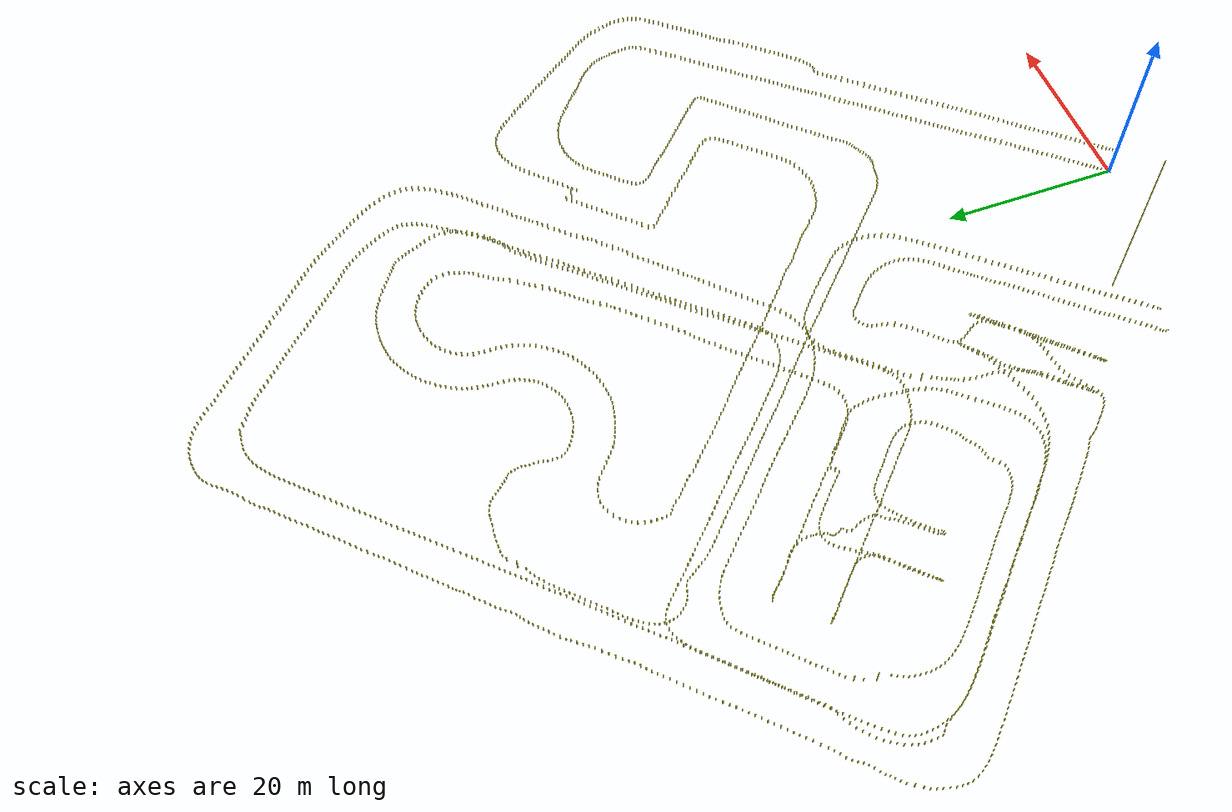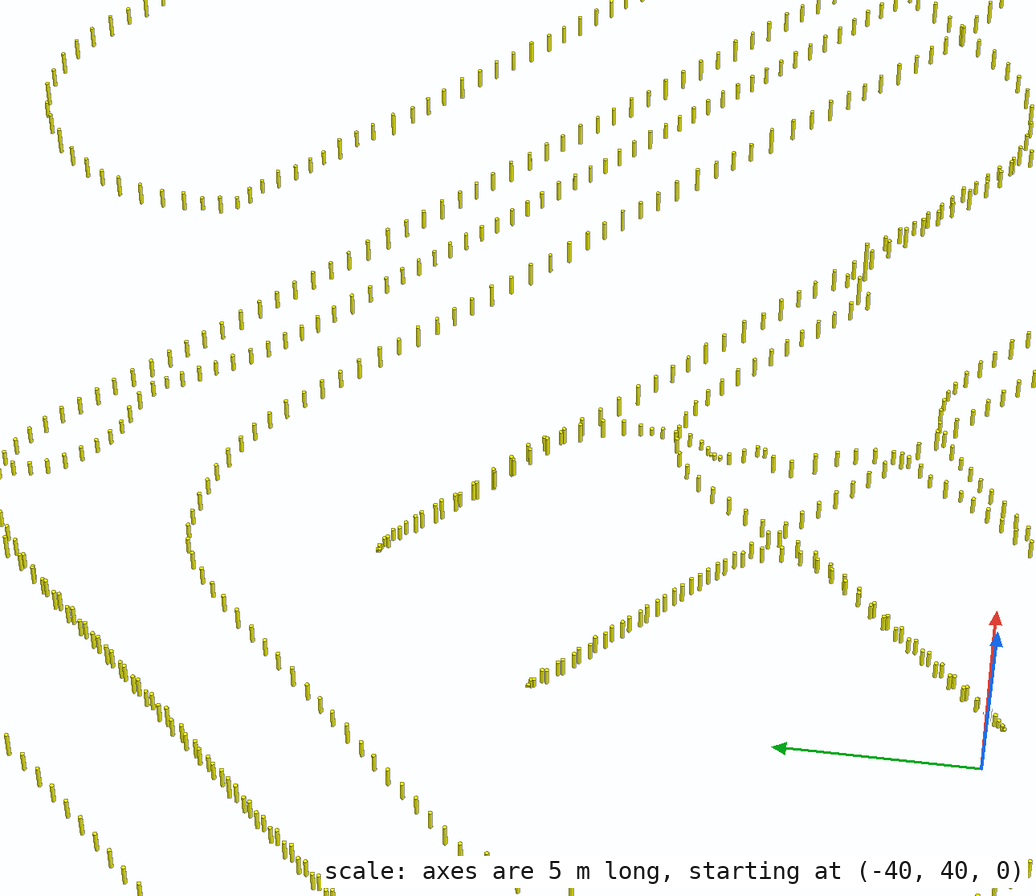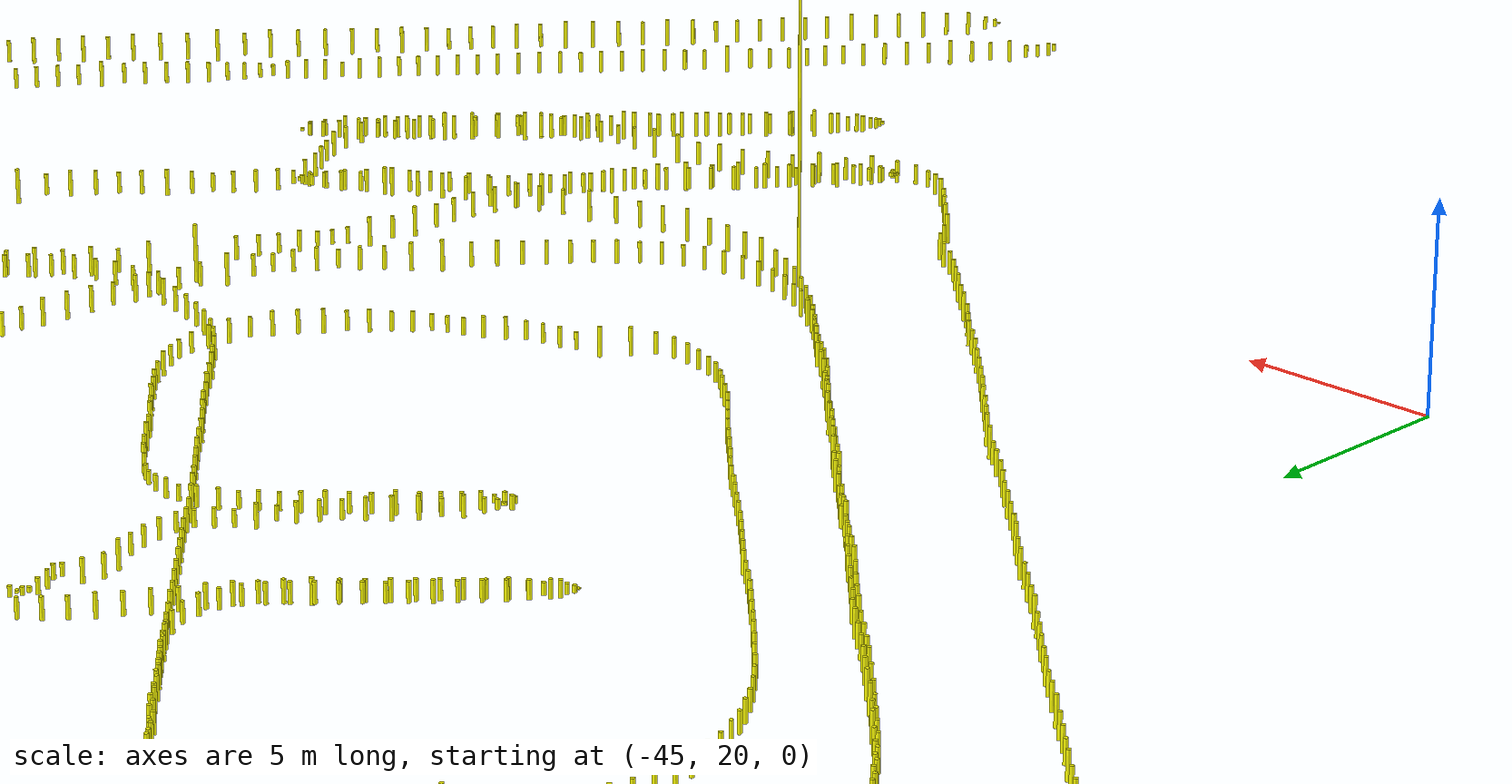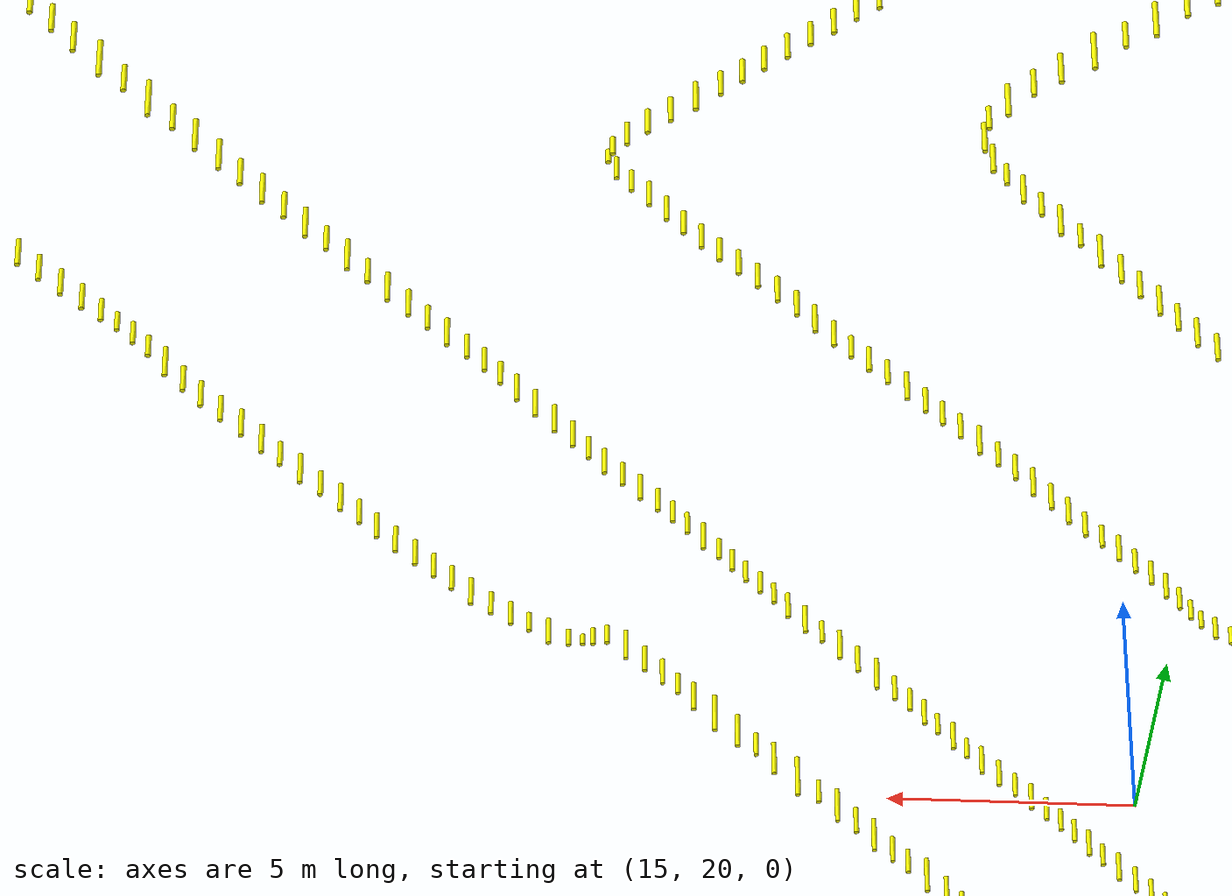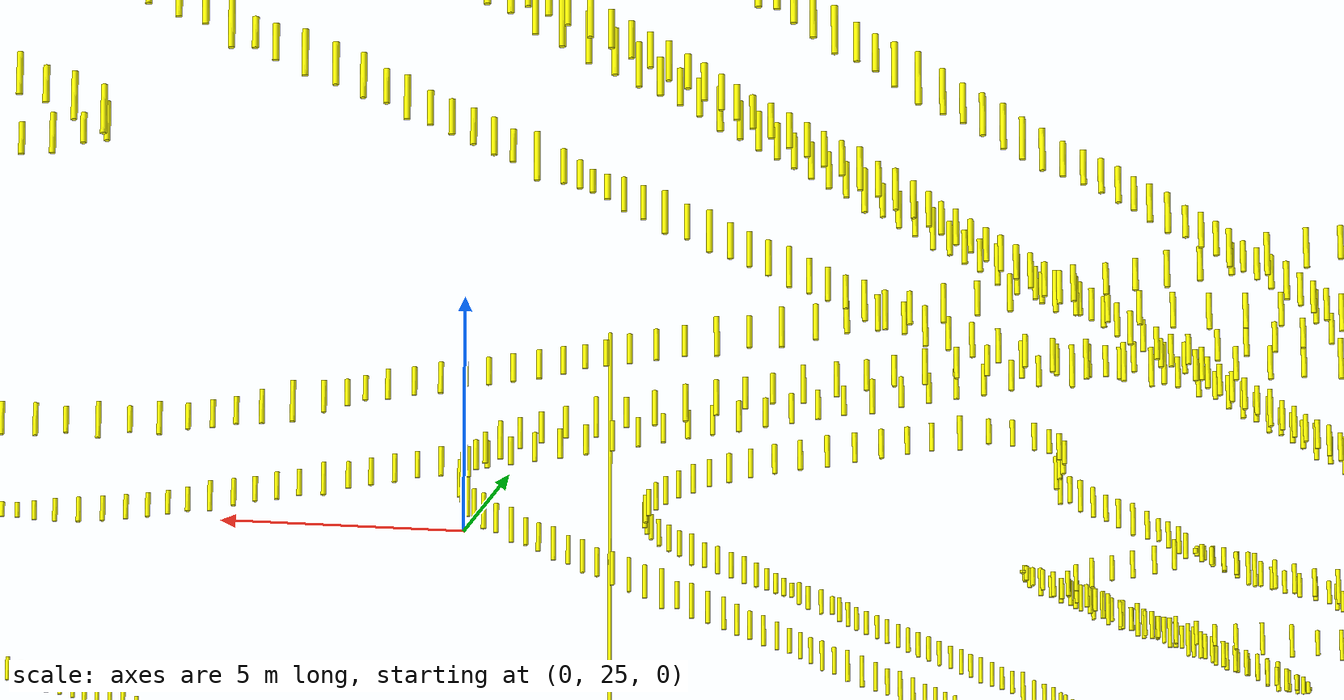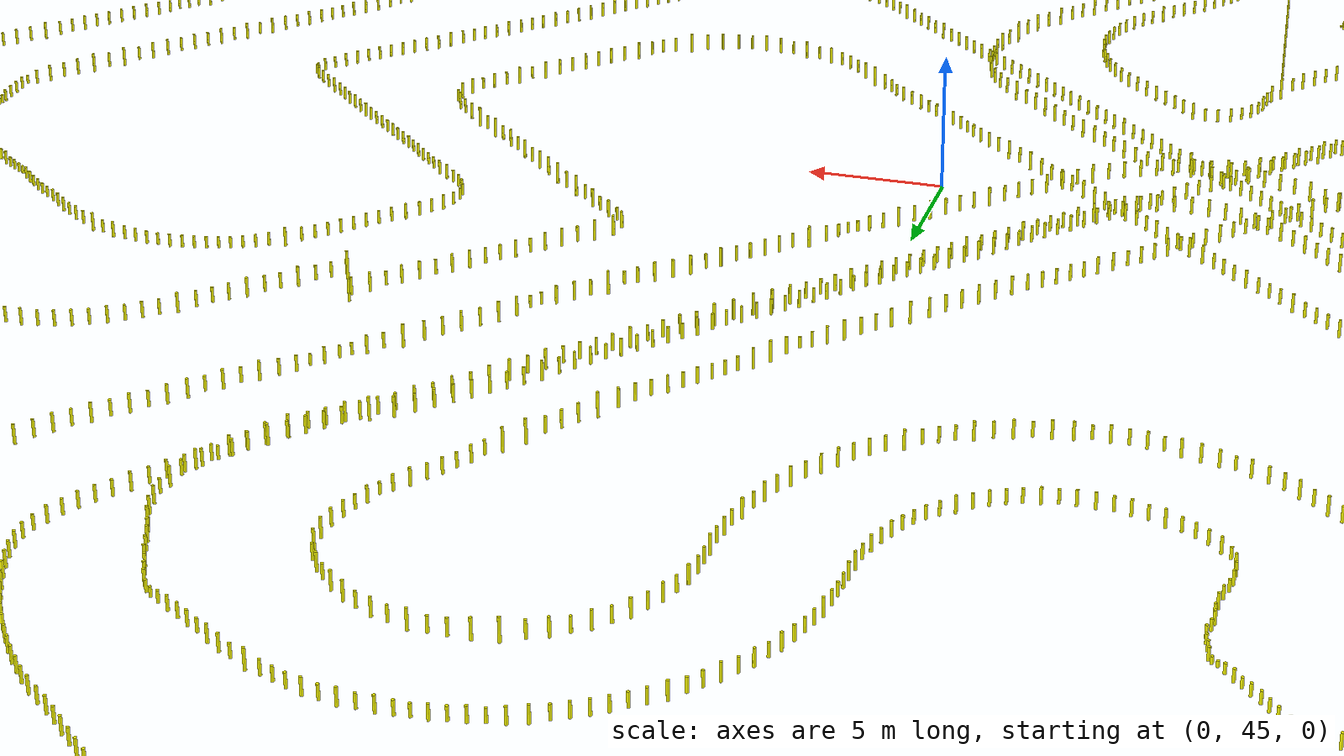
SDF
<?xml version="1.0" ?>
<sdf version="1.8">
  <model name="lane_markers">
    <pose>0 0 0 0 0 0</pose>
    <static>true</static>
    <link name="lane_link">
      <visual name="seg_000000">
        <pose>0.005192 -0.002006 0.0200 0 0 -0.368675</pose>
        <geometry><cylinder>
          <radius>0.0500</radius>
          <length>0.011132</length>
        </cylinder></geometry>
        <material><ambient>1 1 0 1</ambient><diffuse>1 1 0 1</diffuse></material>
        <cast_shadows>false</cast_shadows>
      </visual>
      <visual name="seg_000004">
        <pose>0.006788 0.002125 0.0200 0 0 2.100872</pose>
        <geometry><cylinder>
          <radius>0.0500</radius>
          <length>0.014225</length>
        </cylinder></geometry>
        <material><ambient>1 1 0 1</ambient><diffuse>1 1 0 1</diffuse></material>
        <cast_shadows>false</cast_shadows>
      </visual>
      <visual name="seg_000006">
        <pose>-0.002000 0.010267 0.0200 0 0 2.772918</pose>
        <geometry><cylinder>
          <radius>0.0500</radius>
          <length>0.011132</length>
        </cylinder></geometry>
        <material><ambient>1 1 0 1</ambient><diffuse>1 1 0 1</diffuse></material>
        <cast_shadows>false</cast_shadows>
      </visual>
      <visual name="seg_000007">
        <pose>-0.002000 0.010267 0.0200 0 0 -0.368675</pose>
        <geometry><cylinder>
          <radius>0.0500</radius>
          <length>0.011132</length>
        </cylinder></geometry>
        <material><ambient>1 1 0 1</ambient><diffuse>1 1 0 1</diffuse></material>
        <cast_shadows>false</cast_shadows>
      </visual>
      <visual name="seg_000008">
        <pose>-0.002000 0.010267 0.0200 0 0 2.772918</pose>
        <geometry><cylinder>
          <radius>0.0500</radius>
          <length>0.011132</length>
        </cylinder></geometry>
        <material><ambient>1 1 0 1</ambient><diffuse>1 1 0 1</diffuse></material>
        <cast_shadows>false</cast_shadows>
      </visual>
      <visual name="seg_000009">
        <pose>-0.003596 0.006137 0.0200 0 0 -1.040721</pose>
        <geometry><cylinder>
          <radius>0.0500</radius>
          <length>0.014225</length>
        </cylinder></geometry>
        <material><ambient>1 1 0 1</ambient><diffuse>1 1 0 1</diffuse></material>
        <cast_shadows>false</cast_shadows>
      </visual>
      <visual name="seg_000010">
        <pose>-0.005192 0.002006 0.0200 0 0 2.772918</pose>
        <geometry><cylinder>
          <radius>0.0500</radius>
          <length>0.011132</length>
        </cylinder></geometry>
        <material><ambient>1 1 0 1</ambient><diffuse>1 1 0 1</diffuse></material>
        <cast_shadows>false</cast_shadows>
      </visual>
      <visual name="seg_000011">
        <pose>-0.005192 0.002006 0.0200 0 0 -0.368675</pose>
        <geometry><cylinder>
          <radius>0.0500</radius>
          <length>0.011132</length>
        </cylinder></geometry>
        <material><ambient>1 1 0 1</ambient><diffuse>1 1 0 1</diffuse></material>
        <cast_shadows>false</cast_shadows>
      </visual>
      <visual name="seg_000015">
        <pose>0.001596 0.004131 0.0200 0 0 1.202122</pose>
        <geometry><cylinder>
          <radius>0.0500</radius>
          <length>0.008856</length>
        </cylinder></geometry>
        <material><ambient>1 1 0 1</ambient><diffuse>1 1 0 1</diffuse></material>
        <cast_shadows>false</cast_shadows>
      </visual>
      <visual name="seg_000016">
        <pose>0.001596 0.004131 0.0200 0 0 -1.939471</pose>
        <geometry><cylinder>
          <radius>0.0500</radius>
          <length>0.008856</length>
        </cylinder></geometry>
        <material><ambient>1 1 0 1</ambient><diffuse>1 1 0 1</diffuse></material>
        <cast_shadows>false</cast_shadows>
      </visual>
      <visual name="seg_000018">
        <pose>-0.001596 -0.004131 0.0200 0 0 -1.939471</pose>
        <geometry><cylinder>
          <radius>0.0500</radius>
          <length>0.008856</length>
        </cylinder></geometry>
        <material><ambient>1 1 0 1</ambient><diffuse>1 1 0 1</diffuse></material>
        <cast_shadows>false</cast_shadows>
      </visual>
      <visual name="seg_000020">
        <pose>0.002000 -0.010267 0.0200 0 0 -0.368675</pose>
        <geometry><cylinder>
          <radius>0.0500</radius>
          <length>0.011132</length>
        </cylinder></geometry>
        <material><ambient>1 1 0 1</ambient><diffuse>1 1 0 1</diffuse></material>
        <cast_shadows>false</cast_shadows>
      </visual>
      <visual name="seg_000021">
        <pose>0.002000 -0.010267 0.0200 0 0 2.772918</pose>
        <geometry><cylinder>
          <radius>0.0500</radius>
          <length>0.011132</length>
        </cylinder></geometry>
        <material><ambient>1 1 0 1</ambient><diffuse>1 1 0 1</diffuse></material>
        <cast_shadows>false</cast_shadows>
      </visual>
      <visual name="seg_000023">
        <pose>0.001596 0.004131 0.0200 0 0 1.202122</pose>
        <geometry><cylinder>
          <radius>0.0500</radius>
          <length>0.026569</length>
        </cylinder></geometry>
        <material><ambient>1 1 0 1</ambient><diffuse>1 1 0 1</diffuse></material>
        <cast_shadows>false</cast_shadows>
      </visual>
      <visual name="seg_000027">
        <pose>0.001191 0.018529 0.0200 0 0 2.772918</pose>
        <geometry><cylinder>
          <radius>0.0500</radius>
          <length>0.011132</length>
        </cylinder></geometry>
        <material><ambient>1 1 0 1</ambient><diffuse>1 1 0 1</diffuse></material>
        <cast_shadows>false</cast_shadows>
      </visual>
      <visual name="seg_000028">
        <pose>-0.070687 0.017815 0.0200 0 0 -3.100833</pose>
        <geometry><cylinder>
          <radius>0.0500</radius>
          <length>0.133484</length>
        </cylinder></geometry>
        <material><ambient>1 1 0 1</ambient><diffuse>1 1 0 1</diffuse></material>
        <cast_shadows>false</cast_shadows>
      </visual>
      <visual name="seg_000029">
        <pose>-0.144949 -0.019956 0.0200 0 0 -1.783629</pose>
        <geometry><cylinder>
          <radius>0.0500</radius>
          <length>0.071721</length>
        </cylinder></geometry>
        <material><ambient>1 1 0 1</ambient><diffuse>1 1 0 1</diffuse></material>
        <cast_shadows>false</cast_shadows>
      </visual>
      <visual name="seg_000030">
        <pose>-0.092220 -0.068811 0.0200 0 0 -0.225018</pose>
        <geometry><cylinder>
          <radius>0.0500</radius>
          <length>0.123726</length>
        </cylinder></geometry>
        <material><ambient>1 1 0 1</ambient><diffuse>1 1 0 1</diffuse></material>
        <cast_shadows>false</cast_shadows>
      </visual>
      <visual name="seg_000031">
        <pose>-0.047493 -0.076596 0.0200 0 0 2.772918</pose>
        <geometry><cylinder>
          <radius>0.0500</radius>
          <length>0.033396</length>
        </cylinder></geometry>
        <material><ambient>1 1 0 1</ambient><diffuse>1 1 0 1</diffuse></material>
        <cast_shadows>false</cast_shadows>
      </visual>
      <visual name="seg_000032">
        <pose>-0.066260 -0.078840 0.0200 0 0 -1.939471</pose>
        <geometry><cylinder>
          <radius>0.0500</radius>
          <length>0.017713</length>
        </cylinder></geometry>
        <material><ambient>1 1 0 1</ambient><diffuse>1 1 0 1</diffuse></material>
        <cast_shadows>false</cast_shadows>
      </visual>
      <visual name="seg_000033">
        <pose>-0.055472 -0.097250 0.0200 0 0 -0.627904</pose>
        <geometry><cylinder>
          <radius>0.0500</radius>
          <length>0.034550</length>
        </cylinder></geometry>
        <material><ambient>1 1 0 1</ambient><diffuse>1 1 0 1</diffuse></material>
        <cast_shadows>false</cast_shadows>
      </visual>
      <visual name="seg_000034">
        <pose>-0.031917 -0.082614 0.0200 0 0 1.202122</pose>
        <geometry><cylinder>
          <radius>0.0500</radius>
          <length>0.053139</length>
        </cylinder></geometry>
        <material><ambient>1 1 0 1</ambient><diffuse>1 1 0 1</diffuse></material>
        <cast_shadows>false</cast_shadows>
      </visual>
      <visual name="seg_000035">
        <pose>-0.031130 -0.049687 0.0200 0 0 2.394314</pose>
        <geometry><cylinder>
          <radius>0.0500</radius>
          <length>0.023961</length>
        </cylinder></geometry>
        <material><ambient>1 1 0 1</ambient><diffuse>1 1 0 1</diffuse></material>
        <cast_shadows>false</cast_shadows>
      </visual>
      <visual name="seg_000036">
        <pose>-0.043514 -0.035408 0.0200 0 0 2.100872</pose>
        <geometry><cylinder>
          <radius>0.0500</radius>
          <length>0.014225</length>
        </cylinder></geometry>
        <material><ambient>1 1 0 1</ambient><diffuse>1 1 0 1</diffuse></material>
        <cast_shadows>false</cast_shadows>
      </visual>
      <visual name="seg_000037">
        <pose>-0.013554 -0.065972 0.0200 0 0 -0.830115</pose>
        <geometry><cylinder>
          <radius>0.0500</radius>
          <length>0.099458</length>
        </cylinder></geometry>
        <material><ambient>1 1 0 1</ambient><diffuse>1 1 0 1</diffuse></material>
        <cast_shadows>false</cast_shadows>
      </visual>
      <visual name="seg_000038">
        <pose>0.002831 -0.100785 0.0200 0 0 3.032148</pose>
        <geometry><cylinder>
          <radius>0.0500</radius>
          <length>0.034550</length>
        </cylinder></geometry>
        <material><ambient>1 1 0 1</ambient><diffuse>1 1 0 1</diffuse></material>
        <cast_shadows>false</cast_shadows>
      </visual>
      <visual name="seg_000039">
        <pose>-0.033513 -0.086744 0.0200 0 0 2.576583</pose>
        <geometry><cylinder>
          <radius>0.0500</radius>
          <length>0.045400</length>
        </cylinder></geometry>
        <material><ambient>1 1 0 1</ambient><diffuse>1 1 0 1</diffuse></material>
        <cast_shadows>false</cast_shadows>
      </visual>
      <visual name="seg_000040">
        <pose>-0.051089 -0.070460 0.0200 0 0 1.202122</pose>
        <geometry><cylinder>
          <radius>0.0500</radius>
          <length>0.008856</length>
        </cylinder></geometry>
        <material><ambient>1 1 0 1</ambient><diffuse>1 1 0 1</diffuse></material>
        <cast_shadows>false</cast_shadows>
      </visual>
      <visual name="seg_000041">
        <pose>-0.019150 -0.049568 0.0200 0 0 0.504664</pose>
        <geometry><cylinder>
          <radius>0.0500</radius>
          <length>0.069329</length>
        </cylinder></geometry>
        <material><ambient>1 1 0 1</ambient><diffuse>1 1 0 1</diffuse></material>
        <cast_shadows>false</cast_shadows>
      </visual>
      <visual name="seg_000042">
        <pose>0.010788 -0.018410 0.0200 0 0 1.598879</pose>
        <geometry><cylinder>
          <radius>0.0500</radius>
          <length>0.028807</length>
        </cylinder></geometry>
        <material><ambient>1 1 0 1</ambient><diffuse>1 1 0 1</diffuse></material>
        <cast_shadows>false</cast_shadows>
      </visual>
      <visual name="seg_000043">
        <pose>0.015576 -0.006018 0.0200 0 0 -0.368675</pose>
        <geometry><cylinder>
          <radius>0.0500</radius>
          <length>0.011132</length>
        </cylinder></geometry>
        <material><ambient>1 1 0 1</ambient><diffuse>1 1 0 1</diffuse></material>
        <cast_shadows>false</cast_shadows>
      </visual>
      <visual name="seg_000044">
        <pose>0.013980 -0.010148 0.0200 0 0 -2.838221</pose>
        <geometry><cylinder>
          <radius>0.0500</radius>
          <length>0.014225</length>
        </cylinder></geometry>
        <material><ambient>1 1 0 1</ambient><diffuse>1 1 0 1</diffuse></material>
        <cast_shadows>false</cast_shadows>
      </visual>
      <visual name="seg_000045">
        <pose>-0.004788 -0.012392 0.0200 0 0 -3.131663</pose>
        <geometry><cylinder>
          <radius>0.0500</radius>
          <length>0.023961</length>
        </cylinder></geometry>
        <material><ambient>1 1 0 1</ambient><diffuse>1 1 0 1</diffuse></material>
        <cast_shadows>false</cast_shadows>
      </visual>
      <visual name="seg_000046">
        <pose>-0.021959 -0.010505 0.0200 0 0 2.772918</pose>
        <geometry><cylinder>
          <radius>0.0500</radius>
          <length>0.011132</length>
        </cylinder></geometry>
        <material><ambient>1 1 0 1</ambient><diffuse>1 1 0 1</diffuse></material>
        <cast_shadows>false</cast_shadows>
      </visual>
      <visual name="seg_000047">
        <pose>0.038322 0.037414 0.0200 0 0 0.611565</pose>
        <geometry><cylinder>
          <radius>0.0500</radius>
          <length>0.159935</length>
        </cylinder></geometry>
        <material><ambient>1 1 0 1</ambient><diffuse>1 1 0 1</diffuse></material>
        <cast_shadows>false</cast_shadows>
      </visual>
      <visual name="seg_000048">
        <pose>0.216762 0.205837 0.0200 0 0 0.825903</pose>
        <geometry><cylinder>
          <radius>0.0500</radius>
          <length>0.333286</length>
        </cylinder></geometry>
        <material><ambient>1 1 0 1</ambient><diffuse>1 1 0 1</diffuse></material>
        <cast_shadows>false</cast_shadows>
      </visual>
      <visual name="seg_000049">
        <pose>0.439503 0.442595 0.0200 0 0 0.805364</pose>
        <geometry><cylinder>
          <radius>0.0500</radius>
          <length>0.316879</length>
        </cylinder></geometry>
        <material><ambient>1 1 0 1</ambient><diffuse>1 1 0 1</diffuse></material>
        <cast_shadows>false</cast_shadows>
      </visual>
      <visual name="seg_000050">
        <pose>0.671414 0.718534 0.0200 0 0 0.923867</pose>
        <geometry><cylinder>
          <radius>0.0500</radius>
          <length>0.405273</length>
        </cylinder></geometry>
        <material><ambient>1 1 0 1</ambient><diffuse>1 1 0 1</diffuse></material>
        <cast_shadows>false</cast_shadows>
      </visual>
      <visual name="seg_000051">
        <pose>0.926072 1.037905 0.0200 0 0 0.871877</pose>
        <geometry><cylinder>
          <radius>0.0500</radius>
          <length>0.411945</length>
        </cylinder></geometry>
        <material><ambient>1 1 0 1</ambient><diffuse>1 1 0 1</diffuse></material>
        <cast_shadows>false</cast_shadows>
      </visual>
      <visual name="seg_000052">
        <pose>1.205094 1.343117 0.0200 0 0 0.788903</pose>
        <geometry><cylinder>
          <radius>0.0500</radius>
          <length>0.415827</length>
        </cylinder></geometry>
        <material><ambient>1 1 0 1</ambient><diffuse>1 1 0 1</diffuse></material>
        <cast_shadows>false</cast_shadows>
      </visual>
      <visual name="seg_000053">
        <pose>1.465348 1.646084 0.0200 0 0 0.939024</pose>
        <geometry><cylinder>
          <radius>0.0500</radius>
          <length>0.385228</length>
        </cylinder></geometry>
        <material><ambient>1 1 0 1</ambient><diffuse>1 1 0 1</diffuse></material>
        <cast_shadows>false</cast_shadows>
      </visual>
      <visual name="seg_000054">
        <pose>1.751945 1.986347 0.0200 0 0 0.818889</pose>
        <geometry><cylinder>
          <radius>0.0500</radius>
          <length>0.506106</length>
        </cylinder></geometry>
        <material><ambient>1 1 0 1</ambient><diffuse>1 1 0 1</diffuse></material>
        <cast_shadows>false</cast_shadows>
      </visual>
      <visual name="seg_000055">
        <pose>2.062097 2.341245 0.0200 0 0 0.891586</pose>
        <geometry><cylinder>
          <radius>0.0500</radius>
          <length>0.437164</length>
        </cylinder></geometry>
        <material><ambient>1 1 0 1</ambient><diffuse>1 1 0 1</diffuse></material>
        <cast_shadows>false</cast_shadows>
      </visual>
      <visual name="seg_000056">
        <pose>2.381419 2.735326 0.0200 0 0 0.888461</pose>
        <geometry><cylinder>
          <radius>0.0500</radius>
          <length>0.577266</length>
        </cylinder></geometry>
        <material><ambient>1 1 0 1</ambient><diffuse>1 1 0 1</diffuse></material>
        <cast_shadows>false</cast_shadows>
      </visual>
      <visual name="seg_000057">
        <pose>2.719509 3.131650 0.0200 0 0 0.834810</pose>
        <geometry><cylinder>
          <radius>0.0500</radius>
          <length>0.464983</length>
        </cylinder></geometry>
        <material><ambient>1 1 0 1</ambient><diffuse>1 1 0 1</diffuse></material>
        <cast_shadows>false</cast_shadows>
      </visual>
      <visual name="seg_000058">
        <pose>3.056003 3.523844 0.0200 0 0 0.883657</pose>
        <geometry><cylinder>
          <radius>0.0500</radius>
          <length>0.568848</length>
        </cylinder></geometry>
        <material><ambient>1 1 0 1</ambient><diffuse>1 1 0 1</diffuse></material>
        <cast_shadows>false</cast_shadows>
      </visual>
      <visual name="seg_000059">
        <pose>3.404477 3.916156 0.0200 0 0 0.798258</pose>
        <geometry><cylinder>
          <radius>0.0500</radius>
          <length>0.481566</length>
        </cylinder></geometry>
        <material><ambient>1 1 0 1</ambient><diffuse>1 1 0 1</diffuse></material>
        <cast_shadows>false</cast_shadows>
      </visual>
      <visual name="seg_000060">
        <pose>3.702649 4.270936 0.0200 0 0 0.951020</pose>
        <geometry><cylinder>
          <radius>0.0500</radius>
          <length>0.448017</length>
        </cylinder></geometry>
        <material><ambient>1 1 0 1</ambient><diffuse>1 1 0 1</diffuse></material>
        <cast_shadows>false</cast_shadows>
      </visual>
      <visual name="seg_000061">
        <pose>3.990437 4.629727 0.0200 0 0 0.841530</pose>
        <geometry><cylinder>
          <radius>0.0500</radius>
          <length>0.473260</length>
        </cylinder></geometry>
        <material><ambient>1 1 0 1</ambient><diffuse>1 1 0 1</diffuse></material>
        <cast_shadows>false</cast_shadows>
      </visual>
      <visual name="seg_000062">
        <pose>4.330527 5.015784 0.0200 0 0 0.854650</pose>
        <geometry><cylinder>
          <radius>0.0500</radius>
          <length>0.555745</length>
        </cylinder></geometry>
        <material><ambient>1 1 0 1</ambient><diffuse>1 1 0 1</diffuse></material>
        <cast_shadows>false</cast_shadows>
      </visual>
      <visual name="seg_000063">
        <pose>4.702939 5.470057 0.0200 0 0 0.910516</pose>
        <geometry><cylinder>
          <radius>0.0500</radius>
          <length>0.619538</length>
        </cylinder></geometry>
        <material><ambient>1 1 0 1</ambient><diffuse>1 1 0 1</diffuse></material>
        <cast_shadows>false</cast_shadows>
      </visual>
      <visual name="seg_000064">
        <pose>5.064584 5.881017 0.0200 0 0 0.769557</pose>
        <geometry><cylinder>
          <radius>0.0500</radius>
          <length>0.477993</length>
        </cylinder></geometry>
        <material><ambient>1 1 0 1</ambient><diffuse>1 1 0 1</diffuse></material>
        <cast_shadows>false</cast_shadows>
      </visual>
      <visual name="seg_000065">
        <pose>5.415845 6.295989 0.0200 0 0 0.945281</pose>
        <geometry><cylinder>
          <radius>0.0500</radius>
          <length>0.613508</length>
        </cylinder></geometry>
        <material><ambient>1 1 0 1</ambient><diffuse>1 1 0 1</diffuse></material>
        <cast_shadows>false</cast_shadows>
      </visual>
      <visual name="seg_000066">
        <pose>5.759510 6.737631 0.0200 0 0 0.866207</pose>
        <geometry><cylinder>
          <radius>0.0500</radius>
          <length>0.506562</length>
        </cylinder></geometry>
        <material><ambient>1 1 0 1</ambient><diffuse>1 1 0 1</diffuse></material>
        <cast_shadows>false</cast_shadows>
      </visual>
      <visual name="seg_000067">
        <pose>6.079237 7.117314 0.0200 0 0 0.875815</pose>
        <geometry><cylinder>
          <radius>0.0500</radius>
          <length>0.486192</length>
        </cylinder></geometry>
        <material><ambient>1 1 0 1</ambient><diffuse>1 1 0 1</diffuse></material>
        <cast_shadows>false</cast_shadows>
      </visual>
      <visual name="seg_000068">
        <pose>6.413348 7.472450 0.0200 0 0 0.756528</pose>
        <geometry><cylinder>
          <radius>0.0500</radius>
          <length>0.490742</length>
        </cylinder></geometry>
        <material><ambient>1 1 0 1</ambient><diffuse>1 1 0 1</diffuse></material>
        <cast_shadows>false</cast_shadows>
      </visual>
      <visual name="seg_000069">
        <pose>6.767014 7.862757 0.0200 0 0 0.902355</pose>
        <geometry><cylinder>
          <radius>0.0500</radius>
          <length>0.565461</length>
        </cylinder></geometry>
        <material><ambient>1 1 0 1</ambient><diffuse>1 1 0 1</diffuse></material>
        <cast_shadows>false</cast_shadows>
      </visual>
      <visual name="seg_000070">
        <pose>7.107891 8.281740 0.0200 0 0 0.871877</pose>
        <geometry><cylinder>
          <radius>0.0500</radius>
          <length>0.514931</length>
        </cylinder></geometry>
        <material><ambient>1 1 0 1</ambient><diffuse>1 1 0 1</diffuse></material>
        <cast_shadows>false</cast_shadows>
      </visual>
      <visual name="seg_000071">
        <pose>7.453578 8.651394 0.0200 0 0 0.764181</pose>
        <geometry><cylinder>
          <radius>0.0500</radius>
          <length>0.498749</length>
        </cylinder></geometry>
        <material><ambient>1 1 0 1</ambient><diffuse>1 1 0 1</diffuse></material>
        <cast_shadows>false</cast_shadows>
      </visual>
      <visual name="seg_000072">
        <pose>7.791668 9.047718 0.0200 0 0 0.955839</pose>
        <geometry><cylinder>
          <radius>0.0500</radius>
          <length>0.547922</length>
        </cylinder></geometry>
        <material><ambient>1 1 0 1</ambient><diffuse>1 1 0 1</diffuse></material>
        <cast_shadows>false</cast_shadows>
      </visual>
      <visual name="seg_000073">
        <pose>8.195210 9.551678 0.0200 0 0 0.851317</pose>
        <geometry><cylinder>
          <radius>0.0500</radius>
          <length>0.745037</length>
        </cylinder></geometry>
        <material><ambient>1 1 0 1</ambient><diffuse>1 1 0 1</diffuse></material>
        <cast_shadows>false</cast_shadows>
      </visual>
      <visual name="seg_000074">
        <pose>8.634286 10.070393 0.0200 0 0 0.889017</pose>
        <geometry><cylinder>
          <radius>0.0500</radius>
          <length>0.614398</length>
        </cylinder></geometry>
        <material><ambient>1 1 0 1</ambient><diffuse>1 1 0 1</diffuse></material>
        <cast_shadows>false</cast_shadows>
      </visual>
      <visual name="seg_000075">
        <pose>9.014294 10.497995 0.0200 0 0 0.792475</pose>
        <geometry><cylinder>
          <radius>0.0500</radius>
          <length>0.531044</length>
        </cylinder></geometry>
        <material><ambient>1 1 0 1</ambient><diffuse>1 1 0 1</diffuse></material>
        <cast_shadows>false</cast_shadows>
      </visual>
      <visual name="seg_000076">
        <pose>9.390707 10.931733 0.0200 0 0 0.910516</pose>
        <geometry><cylinder>
          <radius>0.0500</radius>
          <length>0.619538</length>
        </cylinder></geometry>
        <material><ambient>1 1 0 1</ambient><diffuse>1 1 0 1</diffuse></material>
        <cast_shadows>false</cast_shadows>
      </visual>
      <visual name="seg_000077">
        <pose>9.758331 11.373614 0.0200 0 0 0.837606</pose>
        <geometry><cylinder>
          <radius>0.0500</radius>
          <length>0.530841</length>
        </cylinder></geometry>
        <material><ambient>1 1 0 1</ambient><diffuse>1 1 0 1</diffuse></material>
        <cast_shadows>false</cast_shadows>
      </visual>
      <visual name="seg_000078">
        <pose>10.104782 11.837916 0.0200 0 0 1.007115</pose>
        <geometry><cylinder>
          <radius>0.0500</radius>
          <length>0.631931</length>
        </cylinder></geometry>
        <material><ambient>1 1 0 1</ambient><diffuse>1 1 0 1</diffuse></material>
        <cast_shadows>false</cast_shadows>
      </visual>
      <visual name="seg_000079">
        <pose>10.442851 12.295962 0.0200 0 0 0.845612</pose>
        <geometry><cylinder>
          <radius>0.0500</radius>
          <length>0.510339</length>
        </cylinder></geometry>
        <material><ambient>1 1 0 1</ambient><diffuse>1 1 0 1</diffuse></material>
        <cast_shadows>false</cast_shadows>
      </visual>
      <visual name="seg_000080">
        <pose>10.785324 12.719077 0.0200 0 0 0.929746</pose>
        <geometry><cylinder>
          <radius>0.0500</radius>
          <length>0.579314</length>
        </cylinder></geometry>
        <material><ambient>1 1 0 1</ambient><diffuse>1 1 0 1</diffuse></material>
        <cast_shadows>false</cast_shadows>
      </visual>
      <visual name="seg_000081">
        <pose>11.126201 13.138060 0.0200 0 0 0.839455</pose>
        <geometry><cylinder>
          <radius>0.0500</radius>
          <length>0.502049</length>
        </cylinder></geometry>
        <material><ambient>1 1 0 1</ambient><diffuse>1 1 0 1</diffuse></material>
        <cast_shadows>false</cast_shadows>
      </visual>
      <visual name="seg_000082">
        <pose>11.444332 13.513612 0.0200 0 0 0.897660</pose>
        <geometry><cylinder>
          <radius>0.0500</radius>
          <length>0.482739</length>
        </cylinder></geometry>
        <material><ambient>1 1 0 1</ambient><diffuse>1 1 0 1</diffuse></material>
        <cast_shadows>false</cast_shadows>
      </visual>
      <visual name="seg_000083">
        <pose>11.740099 13.893057 0.0200 0 0 0.919809</pose>
        <geometry><cylinder>
          <radius>0.0500</radius>
          <length>0.479519</length>
        </cylinder></geometry>
        <material><ambient>1 1 0 1</ambient><diffuse>1 1 0 1</diffuse></material>
        <cast_shadows>false</cast_shadows>
      </visual>
      <visual name="seg_000084">
        <pose>12.062231 14.248074 0.0200 0 0 0.748621</pose>
        <geometry><cylinder>
          <radius>0.0500</radius>
          <length>0.482766</length>
        </cylinder></geometry>
        <material><ambient>1 1 0 1</ambient><diffuse>1 1 0 1</diffuse></material>
        <cast_shadows>false</cast_shadows>
      </visual>
      <visual name="seg_000085">
        <pose>12.374383 14.592705 0.0200 0 0 0.927104</pose>
        <geometry><cylinder>
          <radius>0.0500</radius>
          <length>0.450912</length>
        </cylinder></geometry>
        <material><ambient>1 1 0 1</ambient><diffuse>1 1 0 1</diffuse></material>
        <cast_shadows>false</cast_shadows>
      </visual>
      <visual name="seg_000086">
        <pose>12.664171 14.941229 0.0200 0 0 0.827846</pose>
        <geometry><cylinder>
          <radius>0.0500</radius>
          <length>0.456729</length>
        </cylinder></geometry>
        <material><ambient>1 1 0 1</ambient><diffuse>1 1 0 1</diffuse></material>
        <cast_shadows>false</cast_shadows>
      </visual>
      <visual name="seg_000087">
        <pose>12.973536 15.263201 0.0200 0 0 0.781842</pose>
        <geometry><cylinder>
          <radius>0.0500</radius>
          <length>0.436530</length>
        </cylinder></geometry>
        <material><ambient>1 1 0 1</ambient><diffuse>1 1 0 1</diffuse></material>
        <cast_shadows>false</cast_shadows>
      </visual>
      <visual name="seg_000088">
        <pose>13.293263 15.642884 0.0200 0 0 0.940396</pose>
        <geometry><cylinder>
          <radius>0.0500</radius>
          <length>0.559292</length>
        </cylinder></geometry>
        <material><ambient>1 1 0 1</ambient><diffuse>1 1 0 1</diffuse></material>
        <cast_shadows>false</cast_shadows>
      </visual>
      <visual name="seg_000089">
        <pose>13.626161 16.041214 0.0200 0 0 0.798258</pose>
        <geometry><cylinder>
          <radius>0.0500</radius>
          <length>0.481566</length>
        </cylinder></geometry>
        <material><ambient>1 1 0 1</ambient><diffuse>1 1 0 1</diffuse></material>
        <cast_shadows>false</cast_shadows>
      </visual>
      <visual name="seg_000090">
        <pose>13.930716 16.412516 0.0200 0 0 0.969267</pose>
        <geometry><cylinder>
          <radius>0.0500</radius>
          <length>0.482413</length>
        </cylinder></geometry>
        <material><ambient>1 1 0 1</ambient><diffuse>1 1 0 1</diffuse></material>
        <cast_shadows>false</cast_shadows>
      </visual>
      <visual name="seg_000091">
        <pose>14.273594 16.821232 0.0200 0 0 0.793736</pose>
        <geometry><cylinder>
          <radius>0.0500</radius>
          <length>0.588654</length>
        </cylinder></geometry>
        <material><ambient>1 1 0 1</ambient><diffuse>1 1 0 1</diffuse></material>
        <cast_shadows>false</cast_shadows>
      </visual>
      <visual name="seg_000092">
        <pose>14.654793 17.267363 0.0200 0 0 0.933799</pose>
        <geometry><cylinder>
          <radius>0.0500</radius>
          <length>0.587849</length>
        </cylinder></geometry>
        <material><ambient>1 1 0 1</ambient><diffuse>1 1 0 1</diffuse></material>
        <cast_shadows>false</cast_shadows>
      </visual>
      <visual name="seg_000093">
        <pose>15.054356 17.730135 0.0200 0 0 0.789275</pose>
        <geometry><cylinder>
          <radius>0.0500</radius>
          <length>0.638143</length>
        </cylinder></geometry>
        <material><ambient>1 1 0 1</ambient><diffuse>1 1 0 1</diffuse></material>
        <cast_shadows>false</cast_shadows>
      </visual>
      <visual name="seg_000094">
        <pose>15.432769 18.153606 0.0200 0 0 0.908287</pose>
        <geometry><cylinder>
          <radius>0.0500</radius>
          <length>0.499665</length>
        </cylinder></geometry>
        <material><ambient>1 1 0 1</ambient><diffuse>1 1 0 1</diffuse></material>
        <cast_shadows>false</cast_shadows>
      </visual>
      <visual name="seg_000095">
        <pose>15.766454 18.584863 0.0200 0 0 0.915633</pose>
        <geometry><cylinder>
          <radius>0.0500</radius>
          <length>0.590898</length>
        </cylinder></geometry>
        <material><ambient>1 1 0 1</ambient><diffuse>1 1 0 1</diffuse></material>
        <cast_shadows>false</cast_shadows>
      </visual>
      <visual name="seg_000096">
        <pose>16.110523 19.012108 0.0200 0 0 0.866207</pose>
        <geometry><cylinder>
          <radius>0.0500</radius>
          <length>0.506562</length>
        </cylinder></geometry>
        <material><ambient>1 1 0 1</ambient><diffuse>1 1 0 1</diffuse></material>
        <cast_shadows>false</cast_shadows>
      </visual>
      <visual name="seg_000097">
        <pose>16.431845 19.395921 0.0200 0 0 0.881555</pose>
        <geometry><cylinder>
          <radius>0.0500</radius>
          <length>0.494589</length>
        </cylinder></geometry>
        <material><ambient>1 1 0 1</ambient><diffuse>1 1 0 1</diffuse></material>
        <cast_shadows>false</cast_shadows>
      </visual>
      <visual name="seg_000098">
        <pose>16.763552 19.775722 0.0200 0 0 0.825328</pose>
        <geometry><cylinder>
          <radius>0.0500</radius>
          <length>0.514330</length>
        </cylinder></geometry>
        <material><ambient>1 1 0 1</ambient><diffuse>1 1 0 1</diffuse></material>
        <cast_shadows>false</cast_shadows>
      </visual>
      <visual name="seg_000099">
        <pose>17.118005 20.198955 0.0200 0 0 0.915633</pose>
        <geometry><cylinder>
          <radius>0.0500</radius>
          <length>0.590898</length>
        </cylinder></geometry>
        <material><ambient>1 1 0 1</ambient><diffuse>1 1 0 1</diffuse></material>
        <cast_shadows>false</cast_shadows>
      </visual>
      <visual name="seg_000100">
        <pose>17.484842 20.607910 0.0200 0 0 0.751815</pose>
        <geometry><cylinder>
          <radius>0.0500</radius>
          <length>0.511529</length>
        </cylinder></geometry>
        <material><ambient>1 1 0 1</ambient><diffuse>1 1 0 1</diffuse></material>
        <cast_shadows>false</cast_shadows>
      </visual>
      <visual name="seg_000101">
        <pose>17.848488 21.008603 0.0200 0 0 0.906912</pose>
        <geometry><cylinder>
          <radius>0.0500</radius>
          <length>0.573929</length>
        </cylinder></geometry>
        <material><ambient>1 1 0 1</ambient><diffuse>1 1 0 1</diffuse></material>
        <cast_shadows>false</cast_shadows>
      </visual>
      <visual name="seg_000102">
        <pose>18.241667 21.454852 0.0200 0 0 0.794279</pose>
        <geometry><cylinder>
          <radius>0.0500</radius>
          <length>0.617459</length>
        </cylinder></geometry>
        <material><ambient>1 1 0 1</ambient><diffuse>1 1 0 1</diffuse></material>
        <cast_shadows>false</cast_shadows>
      </visual>
      <visual name="seg_000103">
        <pose>18.581353 21.855307 0.0200 0 0 0.970671</pose>
        <geometry><cylinder>
          <radius>0.0500</radius>
          <length>0.436757</length>
        </cylinder></geometry>
        <material><ambient>1 1 0 1</ambient><diffuse>1 1 0 1</diffuse></material>
        <cast_shadows>false</cast_shadows>
      </visual>
      <visual name="seg_000104">
        <pose>18.893079 22.276058 0.0200 0 0 0.906350</pose>
        <geometry><cylinder>
          <radius>0.0500</radius>
          <length>0.611061</length>
        </cylinder></geometry>
        <material><ambient>1 1 0 1</ambient><diffuse>1 1 0 1</diffuse></material>
        <cast_shadows>false</cast_shadows>
      </visual>
      <visual name="seg_000105">
        <pose>19.239552 22.678638 0.0200 0 0 0.797805</pose>
        <geometry><cylinder>
          <radius>0.0500</radius>
          <length>0.452760</length>
        </cylinder></geometry>
        <material><ambient>1 1 0 1</ambient><diffuse>1 1 0 1</diffuse></material>
        <cast_shadows>false</cast_shadows>
      </visual>
      <visual name="seg_000106">
        <pose>19.543299 23.078736 0.0200 0 0 1.021650</pose>
        <geometry><cylinder>
          <radius>0.0500</radius>
          <length>0.558166</length>
        </cylinder></geometry>
        <material><ambient>1 1 0 1</ambient><diffuse>1 1 0 1</diffuse></material>
        <cast_shadows>false</cast_shadows>
      </visual>
      <visual name="seg_000107">
        <pose>19.863813 23.491345 0.0200 0 0 0.784585</pose>
        <geometry><cylinder>
          <radius>0.0500</radius>
          <length>0.494131</length>
        </cylinder></geometry>
        <material><ambient>1 1 0 1</ambient><diffuse>1 1 0 1</diffuse></material>
        <cast_shadows>false</cast_shadows>
      </visual>
      <visual name="seg_000108">
        <pose>20.198711 23.879408 0.0200 0 0 0.927514</pose>
        <geometry><cylinder>
          <radius>0.0500</radius>
          <length>0.533671</length>
        </cylinder></geometry>
        <material><ambient>1 1 0 1</ambient><diffuse>1 1 0 1</diffuse></material>
        <cast_shadows>false</cast_shadows>
      </visual>
      <visual name="seg_000109">
        <pose>20.594678 24.348317 0.0200 0 0 0.825052</pose>
        <geometry><cylinder>
          <radius>0.0500</radius>
          <length>0.695374</length>
        </cylinder></geometry>
        <material><ambient>1 1 0 1</ambient><diffuse>1 1 0 1</diffuse></material>
        <cast_shadows>false</cast_shadows>
      </visual>
      <visual name="seg_000110">
        <pose>21.007412 24.829736 0.0200 0 0 0.906912</pose>
        <geometry><cylinder>
          <radius>0.0500</radius>
          <length>0.573929</length>
        </cylinder></geometry>
        <material><ambient>1 1 0 1</ambient><diffuse>1 1 0 1</diffuse></material>
        <cast_shadows>false</cast_shadows>
      </visual>
      <visual name="seg_000111">
        <pose>21.396591 25.296520 0.0200 0 0 0.848019</pose>
        <geometry><cylinder>
          <radius>0.0500</radius>
          <length>0.642076</length>
        </cylinder></geometry>
        <material><ambient>1 1 0 1</ambient><diffuse>1 1 0 1</diffuse></material>
        <cast_shadows>false</cast_shadows>
      </visual>
      <visual name="seg_000112">
        <pose>21.775408 25.705593 0.0200 0 0 0.790906</pose>
        <geometry><cylinder>
          <radius>0.0500</radius>
          <length>0.473435</length>
        </cylinder></geometry>
        <material><ambient>1 1 0 1</ambient><diffuse>1 1 0 1</diffuse></material>
        <cast_shadows>false</cast_shadows>
      </visual>
      <visual name="seg_000113">
        <pose>22.133861 26.108292 0.0200 0 0 0.884515</pose>
        <geometry><cylinder>
          <radius>0.0500</radius>
          <length>0.605978</length>
        </cylinder></geometry>
        <material><ambient>1 1 0 1</ambient><diffuse>1 1 0 1</diffuse></material>
        <cast_shadows>false</cast_shadows>
      </visual>
      <visual name="seg_000114">
        <pose>22.501485 26.550173 0.0200 0 0 0.868355</pose>
        <geometry><cylinder>
          <radius>0.0500</radius>
          <length>0.543678</length>
        </cylinder></geometry>
        <material><ambient>1 1 0 1</ambient><diffuse>1 1 0 1</diffuse></material>
        <cast_shadows>false</cast_shadows>
      </visual>
      <visual name="seg_000115">
        <pose>22.800444 26.937879 0.0200 0 0 0.970671</pose>
        <geometry><cylinder>
          <radius>0.0500</radius>
          <length>0.436757</length>
        </cylinder></geometry>
        <material><ambient>1 1 0 1</ambient><diffuse>1 1 0 1</diffuse></material>
        <cast_shadows>false</cast_shadows>
      </visual>
      <visual name="seg_000116">
        <pose>23.087041 27.278142 0.0200 0 0 0.775421</pose>
        <geometry><cylinder>
          <radius>0.0500</radius>
          <length>0.457253</length>
        </cylinder></geometry>
        <material><ambient>1 1 0 1</ambient><diffuse>1 1 0 1</diffuse></material>
        <cast_shadows>false</cast_shadows>
      </visual>
      <visual name="seg_000117">
        <pose>23.390809 27.616517 0.0200 0 0 0.903507</pose>
        <geometry><cylinder>
          <radius>0.0500</radius>
          <length>0.454062</length>
        </cylinder></geometry>
        <material><ambient>1 1 0 1</ambient><diffuse>1 1 0 1</diffuse></material>
        <cast_shadows>false</cast_shadows>
      </visual>
      <visual name="seg_000118">
        <pose>23.673405 27.977314 0.0200 0 0 0.909140</pose>
        <geometry><cylinder>
          <radius>0.0500</radius>
          <length>0.462534</length>
        </cylinder></geometry>
        <material><ambient>1 1 0 1</ambient><diffuse>1 1 0 1</diffuse></material>
        <cast_shadows>false</cast_shadows>
      </visual>
      <visual name="seg_000119">
        <pose>23.952810 28.329850 0.0200 0 0 0.891586</pose>
        <geometry><cylinder>
          <radius>0.0500</radius>
          <length>0.437164</length>
        </cylinder></geometry>
        <material><ambient>1 1 0 1</ambient><diffuse>1 1 0 1</diffuse></material>
        <cast_shadows>false</cast_shadows>
      </visual>
      <visual name="seg_000120">
        <pose>24.273728 28.728061 0.0200 0 0 0.893127</pose>
        <geometry><cylinder>
          <radius>0.0500</radius>
          <length>0.585697</length>
        </cylinder></geometry>
        <material><ambient>1 1 0 1</ambient><diffuse>1 1 0 1</diffuse></material>
        <cast_shadows>false</cast_shadows>
      </visual>
      <visual name="seg_000121">
        <pose>24.606626 29.126391 0.0200 0 0 0.850732</pose>
        <geometry><cylinder>
          <radius>0.0500</radius>
          <length>0.452778</length>
        </cylinder></geometry>
        <material><ambient>1 1 0 1</ambient><diffuse>1 1 0 1</diffuse></material>
        <cast_shadows>false</cast_shadows>
      </visual>
      <visual name="seg_000122">
        <pose>24.896414 29.474915 0.0200 0 0 0.903507</pose>
        <geometry><cylinder>
          <radius>0.0500</radius>
          <length>0.454062</length>
        </cylinder></geometry>
        <material><ambient>1 1 0 1</ambient><diffuse>1 1 0 1</diffuse></material>
        <cast_shadows>false</cast_shadows>
      </visual>
      <visual name="seg_000123">
        <pose>25.202970 29.835950 0.0200 0 0 0.833092</pose>
        <geometry><cylinder>
          <radius>0.0500</radius>
          <length>0.493779</length>
        </cylinder></geometry>
        <material><ambient>1 1 0 1</ambient><diffuse>1 1 0 1</diffuse></material>
        <cast_shadows>false</cast_shadows>
      </visual>
      <visual name="seg_000124">
        <pose>25.560232 30.220120 0.0200 0 0 0.811525</pose>
        <geometry><cylinder>
          <radius>0.0500</radius>
          <length>0.555516</length>
        </cylinder></geometry>
        <material><ambient>1 1 0 1</ambient><diffuse>1 1 0 1</diffuse></material>
        <cast_shadows>false</cast_shadows>
      </visual>
      <visual name="seg_000125">
        <pose>25.913898 30.610427 0.0200 0 0 0.860347</pose>
        <geometry><cylinder>
          <radius>0.0500</radius>
          <length>0.498209</length>
        </cylinder></geometry>
        <material><ambient>1 1 0 1</ambient><diffuse>1 1 0 1</diffuse></material>
        <cast_shadows>false</cast_shadows>
      </visual>
      <visual name="seg_000126">
        <pose>26.265968 30.996603 0.0200 0 0 0.805364</pose>
        <geometry><cylinder>
          <radius>0.0500</radius>
          <length>0.547337</length>
        </cylinder></geometry>
        <material><ambient>1 1 0 1</ambient><diffuse>1 1 0 1</diffuse></material>
        <cast_shadows>false</cast_shadows>
      </visual>
      <visual name="seg_000127">
        <pose>26.586886 31.394814 0.0200 0 0 0.991837</pose>
        <geometry><cylinder>
          <radius>0.0500</radius>
          <length>0.479966</length>
        </cylinder></geometry>
        <material><ambient>1 1 0 1</ambient><diffuse>1 1 0 1</diffuse></material>
        <cast_shadows>false</cast_shadows>
      </visual>
      <visual name="seg_000128">
        <pose>26.902208 31.809429 0.0200 0 0 0.859997</pose>
        <geometry><cylinder>
          <radius>0.0500</radius>
          <length>0.564080</length>
        </cylinder></geometry>
        <material><ambient>1 1 0 1</ambient><diffuse>1 1 0 1</diffuse></material>
        <cast_shadows>false</cast_shadows>
      </visual>
      <visual name="seg_000129">
        <pose>27.262640 32.263583 0.0200 0 0 0.937736</pose>
        <geometry><cylinder>
          <radius>0.0500</radius>
          <length>0.596393</length>
        </cylinder></geometry>
        <material><ambient>1 1 0 1</ambient><diffuse>1 1 0 1</diffuse></material>
        <cast_shadows>false</cast_shadows>
      </visual>
      <visual name="seg_000130">
        <pose>27.635051 32.717856 0.0200 0 0 0.828962</pose>
        <geometry><cylinder>
          <radius>0.0500</radius>
          <length>0.580172</length>
        </cylinder></geometry>
        <material><ambient>1 1 0 1</ambient><diffuse>1 1 0 1</diffuse></material>
        <cast_shadows>false</cast_shadows>
      </visual>
      <visual name="seg_000131">
        <pose>27.999079 33.165873 0.0200 0 0 0.948347</pose>
        <geometry><cylinder>
          <radius>0.0500</radius>
          <length>0.576419</length>
        </cylinder></geometry>
        <material><ambient>1 1 0 1</ambient><diffuse>1 1 0 1</diffuse></material>
        <cast_shadows>false</cast_shadows>
      </visual>
      <visual name="seg_000132">
        <pose>28.313997 33.594886 0.0200 0 0 0.924864</pose>
        <geometry><cylinder>
          <radius>0.0500</radius>
          <length>0.488031</length>
        </cylinder></geometry>
        <material><ambient>1 1 0 1</ambient><diffuse>1 1 0 1</diffuse></material>
        <cast_shadows>false</cast_shadows>
      </visual>
      <visual name="seg_000133">
        <pose>28.623340 33.978580 0.0200 0 0 0.860347</pose>
        <geometry><cylinder>
          <radius>0.0500</radius>
          <length>0.498209</length>
        </cylinder></geometry>
        <material><ambient>1 1 0 1</ambient><diffuse>1 1 0 1</diffuse></material>
        <cast_shadows>false</cast_shadows>
      </visual>
      <visual name="seg_000134">
        <pose>28.955046 34.358382 0.0200 0 0 0.845612</pose>
        <geometry><cylinder>
          <radius>0.0500</radius>
          <length>0.510339</length>
        </cylinder></geometry>
        <material><ambient>1 1 0 1</ambient><diffuse>1 1 0 1</diffuse></material>
        <cast_shadows>false</cast_shadows>
      </visual>
      <visual name="seg_000135">
        <pose>29.332267 34.763324 0.0200 0 0 0.799630</pose>
        <geometry><cylinder>
          <radius>0.0500</radius>
          <length>0.596792</length>
        </cylinder></geometry>
        <material><ambient>1 1 0 1</ambient><diffuse>1 1 0 1</diffuse></material>
        <cast_shadows>false</cast_shadows>
      </visual>
      <visual name="seg_000136">
        <pose>29.695508 35.178415 0.0200 0 0 0.913335</pose>
        <geometry><cylinder>
          <radius>0.0500</radius>
          <length>0.508148</length>
        </cylinder></geometry>
        <material><ambient>1 1 0 1</ambient><diffuse>1 1 0 1</diffuse></material>
        <cast_shadows>false</cast_shadows>
      </visual>
      <visual name="seg_000137">
        <pose>30.053962 35.581114 0.0200 0 0 0.781448</pose>
        <geometry><cylinder>
          <radius>0.0500</radius>
          <length>0.572441</length>
        </cylinder></geometry>
        <material><ambient>1 1 0 1</ambient><diffuse>1 1 0 1</diffuse></material>
        <cast_shadows>false</cast_shadows>
      </visual>
      <visual name="seg_000138">
        <pose>30.443545 36.033500 0.0200 0 0 0.931652</pose>
        <geometry><cylinder>
          <radius>0.0500</radius>
          <length>0.624960</length>
        </cylinder></geometry>
        <material><ambient>1 1 0 1</ambient><diffuse>1 1 0 1</diffuse></material>
        <cast_shadows>false</cast_shadows>
      </visual>
      <visual name="seg_000139">
        <pose>30.807978 36.467119 0.0200 0 0 0.798659</pose>
        <geometry><cylinder>
          <radius>0.0500</radius>
          <length>0.510372</length>
        </cylinder></geometry>
        <material><ambient>1 1 0 1</ambient><diffuse>1 1 0 1</diffuse></material>
        <cast_shadows>false</cast_shadows>
      </visual>
      <visual name="seg_000140">
        <pose>31.183985 36.915255 0.0200 0 0 0.929746</pose>
        <geometry><cylinder>
          <radius>0.0500</radius>
          <length>0.662074</length>
        </cylinder></geometry>
        <material><ambient>1 1 0 1</ambient><diffuse>1 1 0 1</diffuse></material>
        <cast_shadows>false</cast_shadows>
      </visual>
      <visual name="seg_000141">
        <pose>31.565185 37.361386 0.0200 0 0 0.778772</pose>
        <geometry><cylinder>
          <radius>0.0500</radius>
          <length>0.514845</length>
        </cylinder></geometry>
        <material><ambient>1 1 0 1</ambient><diffuse>1 1 0 1</diffuse></material>
        <cast_shadows>false</cast_shadows>
      </visual>
      <visual name="seg_000142">
        <pose>31.946789 37.793118 0.0200 0 0 0.901810</pose>
        <geometry><cylinder>
          <radius>0.0500</radius>
          <length>0.639728</length>
        </cylinder></geometry>
        <material><ambient>1 1 0 1</ambient><diffuse>1 1 0 1</diffuse></material>
        <cast_shadows>false</cast_shadows>
      </visual>
      <visual name="seg_000143">
        <pose>32.327585 38.253647 0.0200 0 0 0.854650</pose>
        <geometry><cylinder>
          <radius>0.0500</radius>
          <length>0.555745</length>
        </cylinder></geometry>
        <material><ambient>1 1 0 1</ambient><diffuse>1 1 0 1</diffuse></material>
        <cast_shadows>false</cast_shadows>
      </visual>
      <visual name="seg_000144">
        <pose>32.715572 38.701902 0.0200 0 0 0.859719</pose>
        <geometry><cylinder>
          <radius>0.0500</radius>
          <length>0.629952</length>
        </cylinder></geometry>
        <material><ambient>1 1 0 1</ambient><diffuse>1 1 0 1</diffuse></material>
        <cast_shadows>false</cast_shadows>
      </visual>
      <visual name="seg_000145">
        <pose>33.107156 39.144020 0.0200 0 0 0.830195</pose>
        <geometry><cylinder>
          <radius>0.0500</radius>
          <length>0.551373</length>
        </cylinder></geometry>
        <material><ambient>1 1 0 1</ambient><diffuse>1 1 0 1</diffuse></material>
        <cast_shadows>false</cast_shadows>
      </visual>
      <visual name="seg_000146">
        <pose>33.484355 39.610685 0.0200 0 0 0.942564</pose>
        <geometry><cylinder>
          <radius>0.0500</radius>
          <length>0.650602</length>
        </cylinder></geometry>
        <material><ambient>1 1 0 1</ambient><diffuse>1 1 0 1</diffuse></material>
        <cast_shadows>false</cast_shadows>
      </visual>
      <visual name="seg_000147">
        <pose>33.897876 40.125031 0.0200 0 0 0.846188</pose>
        <geometry><cylinder>
          <radius>0.0500</radius>
          <length>0.670858</length>
        </cylinder></geometry>
        <material><ambient>1 1 0 1</ambient><diffuse>1 1 0 1</diffuse></material>
        <cast_shadows>false</cast_shadows>
      </visual>
      <visual name="seg_000148">
        <pose>34.289055 40.581548 0.0200 0 0 0.882679</pose>
        <geometry><cylinder>
          <radius>0.0500</radius>
          <length>0.531718</length>
        </cylinder></geometry>
        <material><ambient>1 1 0 1</ambient><diffuse>1 1 0 1</diffuse></material>
        <cast_shadows>false</cast_shadows>
      </visual>
      <visual name="seg_000149">
        <pose>34.711769 41.073354 0.0200 0 0 0.845612</pose>
        <geometry><cylinder>
          <radius>0.0500</radius>
          <length>0.765509</length>
        </cylinder></geometry>
        <material><ambient>1 1 0 1</ambient><diffuse>1 1 0 1</diffuse></material>
        <cast_shadows>false</cast_shadows>
      </visual>
      <visual name="seg_000150">
        <pose>35.125290 41.587700 0.0200 0 0 0.959719</pose>
        <geometry><cylinder>
          <radius>0.0500</radius>
          <length>0.556515</length>
        </cylinder></geometry>
        <material><ambient>1 1 0 1</ambient><diffuse>1 1 0 1</diffuse></material>
        <cast_shadows>false</cast_shadows>
      </visual>
      <visual name="seg_000151">
        <pose>35.542407 42.095910 0.0200 0 0 0.827846</pose>
        <geometry><cylinder>
          <radius>0.0500</radius>
          <length>0.761215</length>
        </cylinder></geometry>
        <material><ambient>1 1 0 1</ambient><diffuse>1 1 0 1</diffuse></material>
        <cast_shadows>false</cast_shadows>
      </visual>
      <visual name="seg_000152">
        <pose>35.977483 42.635159 0.0200 0 0 0.969593</pose>
        <geometry><cylinder>
          <radius>0.0500</radius>
          <length>0.627998</length>
        </cylinder></geometry>
        <material><ambient>1 1 0 1</ambient><diffuse>1 1 0 1</diffuse></material>
        <cast_shadows>false</cast_shadows>
      </visual>
      <visual name="seg_000153">
        <pose>36.340702 43.111972 0.0200 0 0 0.865187</pose>
        <geometry><cylinder>
          <radius>0.0500</radius>
          <length>0.572431</length>
        </cylinder></geometry>
        <material><ambient>1 1 0 1</ambient><diffuse>1 1 0 1</diffuse></material>
        <cast_shadows>false</cast_shadows>
      </visual>
      <visual name="seg_000154">
        <pose>36.691133 43.617462 0.0200 0 0 1.050426</pose>
        <geometry><cylinder>
          <radius>0.0500</radius>
          <length>0.662993</length>
        </cylinder></geometry>
        <material><ambient>1 1 0 1</ambient><diffuse>1 1 0 1</diffuse></material>
        <cast_shadows>false</cast_shadows>
      </visual>
      <visual name="seg_000155">
        <pose>37.012412 44.124720 0.0200 0 0 0.951836</pose>
        <geometry><cylinder>
          <radius>0.0500</radius>
          <length>0.539337</length>
        </cylinder></geometry>
        <material><ambient>1 1 0 1</ambient><diffuse>1 1 0 1</diffuse></material>
        <cast_shadows>false</cast_shadows>
      </visual>
      <visual name="seg_000156">
        <pose>37.213936 44.507344 0.0200 0 0 1.301029</pose>
        <geometry><cylinder>
          <radius>0.0500</radius>
          <length>0.338199</length>
        </cylinder></geometry>
        <material><ambient>1 1 0 1</ambient><diffuse>1 1 0 1</diffuse></material>
        <cast_shadows>false</cast_shadows>
      </visual>
      <visual name="seg_000157">
        <pose>37.243743 44.908836 0.0200 0 0 1.634686</pose>
        <geometry><cylinder>
          <radius>0.0500</radius>
          <length>0.477993</length>
        </cylinder></geometry>
        <material><ambient>1 1 0 1</ambient><diffuse>1 1 0 1</diffuse></material>
        <cast_shadows>false</cast_shadows>
      </visual>
      <visual name="seg_000158">
        <pose>37.235589 45.381962 0.0200 0 0 1.540524</pose>
        <geometry><cylinder>
          <radius>0.0500</radius>
          <length>0.469448</length>
        </cylinder></geometry>
        <material><ambient>1 1 0 1</ambient><diffuse>1 1 0 1</diffuse></material>
        <cast_shadows>false</cast_shadows>
      </visual>
      <visual name="seg_000159">
        <pose>37.239819 45.840808 0.0200 0 0 1.583617</pose>
        <geometry><cylinder>
          <radius>0.0500</radius>
          <length>0.448497</length>
        </cylinder></geometry>
        <material><ambient>1 1 0 1</ambient><diffuse>1 1 0 1</diffuse></material>
        <cast_shadows>false</cast_shadows>
      </visual>
      <visual name="seg_000160">
        <pose>37.220089 46.299417 0.0200 0 0 1.642586</pose>
        <geometry><cylinder>
          <radius>0.0500</radius>
          <length>0.469967</length>
        </cylinder></geometry>
        <material><ambient>1 1 0 1</ambient><diffuse>1 1 0 1</diffuse></material>
        <cast_shadows>false</cast_shadows>
      </visual>
      <visual name="seg_000161">
        <pose>37.154462 46.685560 0.0200 0 0 1.881737</pose>
        <geometry><cylinder>
          <radius>0.0500</radius>
          <length>0.318818</length>
        </cylinder></geometry>
        <material><ambient>1 1 0 1</ambient><diffuse>1 1 0 1</diffuse></material>
        <cast_shadows>false</cast_shadows>
      </visual>
      <visual name="seg_000162">
        <pose>37.117626 46.960888 0.0200 0 0 1.474497</pose>
        <geometry><cylinder>
          <radius>0.0500</radius>
          <length>0.248278</length>
        </cylinder></geometry>
        <material><ambient>1 1 0 1</ambient><diffuse>1 1 0 1</diffuse></material>
        <cast_shadows>false</cast_shadows>
      </visual>
      <visual name="seg_000163">
        <pose>37.083600 47.197153 0.0200 0 0 1.958031</pose>
        <geometry><cylinder>
          <radius>0.0500</radius>
          <length>0.243427</length>
        </cylinder></geometry>
        <material><ambient>1 1 0 1</ambient><diffuse>1 1 0 1</diffuse></material>
        <cast_shadows>false</cast_shadows>
      </visual>
      <visual name="seg_000164">
        <pose>36.981651 47.535615 0.0200 0 0 1.813881</pose>
        <geometry><cylinder>
          <radius>0.0500</radius>
          <length>0.465197</length>
        </cylinder></geometry>
        <material><ambient>1 1 0 1</ambient><diffuse>1 1 0 1</diffuse></material>
        <cast_shadows>false</cast_shadows>
      </visual>
      <visual name="seg_000165">
        <pose>36.892469 47.907122 0.0200 0 0 1.794740</pose>
        <geometry><cylinder>
          <radius>0.0500</radius>
          <length>0.298959</length>
        </cylinder></geometry>
        <material><ambient>1 1 0 1</ambient><diffuse>1 1 0 1</diffuse></material>
        <cast_shadows>false</cast_shadows>
      </visual>
      <visual name="seg_000166">
        <pose>36.840057 48.188468 0.0200 0 0 1.711570</pose>
        <geometry><cylinder>
          <radius>0.0500</radius>
          <length>0.273907</length>
        </cylinder></geometry>
        <material><ambient>1 1 0 1</ambient><diffuse>1 1 0 1</diffuse></material>
        <cast_shadows>false</cast_shadows>
      </visual>
      <visual name="seg_000167">
        <pose>36.750493 48.512651 0.0200 0 0 1.927844</pose>
        <geometry><cylinder>
          <radius>0.0500</radius>
          <length>0.402556</length>
        </cylinder></geometry>
        <material><ambient>1 1 0 1</ambient><diffuse>1 1 0 1</diffuse></material>
        <cast_shadows>false</cast_shadows>
      </visual>
      <visual name="seg_000168">
        <pose>36.645735 48.890176 0.0200 0 0 1.750939</pose>
        <geometry><cylinder>
          <radius>0.0500</radius>
          <length>0.384097</length>
        </cylinder></geometry>
        <material><ambient>1 1 0 1</ambient><diffuse>1 1 0 1</diffuse></material>
        <cast_shadows>false</cast_shadows>
      </visual>
      <visual name="seg_000169">
        <pose>36.530593 49.271713 0.0200 0 0 1.967728</pose>
        <geometry><cylinder>
          <radius>0.0500</radius>
          <length>0.417664</length>
        </cylinder></geometry>
        <material><ambient>1 1 0 1</ambient><diffuse>1 1 0 1</diffuse></material>
        <cast_shadows>false</cast_shadows>
      </visual>
      <visual name="seg_000170">
        <pose>36.348764 49.650530 0.0200 0 0 2.068158</pose>
        <geometry><cylinder>
          <radius>0.0500</radius>
          <length>0.423787</length>
        </cylinder></geometry>
        <material><ambient>1 1 0 1</ambient><diffuse>1 1 0 1</diffuse></material>
        <cast_shadows>false</cast_shadows>
      </visual>
      <visual name="seg_000171">
        <pose>36.114634 50.002081 0.0200 0 0 2.248374</pose>
        <geometry><cylinder>
          <radius>0.0500</radius>
          <length>0.424416</length>
        </cylinder></geometry>
        <material><ambient>1 1 0 1</ambient><diffuse>1 1 0 1</diffuse></material>
        <cast_shadows>false</cast_shadows>
      </visual>
      <visual name="seg_000172">
        <pose>35.803836 50.340526 0.0200 0 0 2.369437</pose>
        <geometry><cylinder>
          <radius>0.0500</radius>
          <length>0.496260</length>
        </cylinder></geometry>
        <material><ambient>1 1 0 1</ambient><diffuse>1 1 0 1</diffuse></material>
        <cast_shadows>false</cast_shadows>
      </visual>
      <visual name="seg_000173">
        <pose>35.485847 50.691245 0.0200 0 0 2.239135</pose>
        <geometry><cylinder>
          <radius>0.0500</radius>
          <length>0.452577</length>
        </cylinder></geometry>
        <material><ambient>1 1 0 1</ambient><diffuse>1 1 0 1</diffuse></material>
        <cast_shadows>false</cast_shadows>
      </visual>
      <visual name="seg_000174">
        <pose>35.238949 51.009750 0.0200 0 0 2.218795</pose>
        <geometry><cylinder>
          <radius>0.0500</radius>
          <length>0.353452</length>
        </cylinder></geometry>
        <material><ambient>1 1 0 1</ambient><diffuse>1 1 0 1</diffuse></material>
        <cast_shadows>false</cast_shadows>
      </visual>
      <visual name="seg_000175">
        <pose>34.991669 51.280931 0.0200 0 0 2.394314</pose>
        <geometry><cylinder>
          <radius>0.0500</radius>
          <length>0.383372</length>
        </cylinder></geometry>
        <material><ambient>1 1 0 1</ambient><diffuse>1 1 0 1</diffuse></material>
        <cast_shadows>false</cast_shadows>
      </visual>
      <visual name="seg_000176">
        <pose>34.714451 51.520954 0.0200 0 0 2.464816</pose>
        <geometry><cylinder>
          <radius>0.0500</radius>
          <length>0.350461</length>
        </cylinder></geometry>
        <material><ambient>1 1 0 1</ambient><diffuse>1 1 0 1</diffuse></material>
        <cast_shadows>false</cast_shadows>
      </visual>
      <visual name="seg_000177">
        <pose>34.430444 51.758852 0.0200 0 0 2.425918</pose>
        <geometry><cylinder>
          <radius>0.0500</radius>
          <length>0.390637</length>
        </cylinder></geometry>
        <material><ambient>1 1 0 1</ambient><diffuse>1 1 0 1</diffuse></material>
        <cast_shadows>false</cast_shadows>
      </visual>
      <visual name="seg_000178">
        <pose>34.088517 52.047610 0.0200 0 0 2.451433</pose>
        <geometry><cylinder>
          <radius>0.0500</radius>
          <length>0.504522</length>
        </cylinder></geometry>
        <material><ambient>1 1 0 1</ambient><diffuse>1 1 0 1</diffuse></material>
        <cast_shadows>false</cast_shadows>
      </visual>
      <visual name="seg_000179">
        <pose>33.746994 52.321970 0.0200 0 0 2.482979</pose>
        <geometry><cylinder>
          <radius>0.0500</radius>
          <length>0.371738</length>
        </cylinder></geometry>
        <material><ambient>1 1 0 1</ambient><diffuse>1 1 0 1</diffuse></material>
        <cast_shadows>false</cast_shadows>
      </visual>
      <visual name="seg_000180">
        <pose>33.453008 52.549482 0.0200 0 0 2.482979</pose>
        <geometry><cylinder>
          <radius>0.0500</radius>
          <length>0.371738</length>
        </cylinder></geometry>
        <material><ambient>1 1 0 1</ambient><diffuse>1 1 0 1</diffuse></material>
        <cast_shadows>false</cast_shadows>
      </visual>
      <visual name="seg_000181">
        <pose>33.175407 52.742180 0.0200 0 0 2.597928</pose>
        <geometry><cylinder>
          <radius>0.0500</radius>
          <length>0.305224</length>
        </cylinder></geometry>
        <material><ambient>1 1 0 1</ambient><diffuse>1 1 0 1</diffuse></material>
        <cast_shadows>false</cast_shadows>
      </visual>
      <visual name="seg_000182">
        <pose>32.930958 52.912576 0.0200 0 0 2.464816</pose>
        <geometry><cylinder>
          <radius>0.0500</radius>
          <length>0.292051</length>
        </cylinder></geometry>
        <material><ambient>1 1 0 1</ambient><diffuse>1 1 0 1</diffuse></material>
        <cast_shadows>false</cast_shadows>
      </visual>
      <visual name="seg_000183">
        <pose>32.660932 53.140326 0.0200 0 0 2.424092</pose>
        <geometry><cylinder>
          <radius>0.0500</radius>
          <length>0.414587</length>
        </cylinder></geometry>
        <material><ambient>1 1 0 1</ambient><diffuse>1 1 0 1</diffuse></material>
        <cast_shadows>false</cast_shadows>
      </visual>
      <visual name="seg_000184">
        <pose>32.351348 53.435577 0.0200 0 0 2.338405</pose>
        <geometry><cylinder>
          <radius>0.0500</radius>
          <length>0.441805</length>
        </cylinder></geometry>
        <material><ambient>1 1 0 1</ambient><diffuse>1 1 0 1</diffuse></material>
        <cast_shadows>false</cast_shadows>
      </visual>
      <visual name="seg_000185">
        <pose>32.048552 53.732954 0.0200 0 0 2.394314</pose>
        <geometry><cylinder>
          <radius>0.0500</radius>
          <length>0.407333</length>
        </cylinder></geometry>
        <material><ambient>1 1 0 1</ambient><diffuse>1 1 0 1</diffuse></material>
        <cast_shadows>false</cast_shadows>
      </visual>
      <visual name="seg_000186">
        <pose>31.719009 54.007433 0.0200 0 0 2.494727</pose>
        <geometry><cylinder>
          <radius>0.0500</radius>
          <length>0.451505</length>
        </cylinder></geometry>
        <material><ambient>1 1 0 1</ambient><diffuse>1 1 0 1</diffuse></material>
        <cast_shadows>false</cast_shadows>
      </visual>
      <visual name="seg_000187">
        <pose>31.398254 54.273770 0.0200 0 0 2.394314</pose>
        <geometry><cylinder>
          <radius>0.0500</radius>
          <length>0.383372</length>
        </cylinder></geometry>
        <material><ambient>1 1 0 1</ambient><diffuse>1 1 0 1</diffuse></material>
        <cast_shadows>false</cast_shadows>
      </visual>
      <visual name="seg_000188">
        <pose>31.079904 54.515441 0.0200 0 0 2.581759</pose>
        <geometry><cylinder>
          <radius>0.0500</radius>
          <length>0.419524</length>
        </cylinder></geometry>
        <material><ambient>1 1 0 1</ambient><diffuse>1 1 0 1</diffuse></material>
        <cast_shadows>false</cast_shadows>
      </visual>
      <visual name="seg_000189">
        <pose>30.722019 54.762893 0.0200 0 0 2.494727</pose>
        <geometry><cylinder>
          <radius>0.0500</radius>
          <length>0.451505</length>
        </cylinder></geometry>
        <material><ambient>1 1 0 1</ambient><diffuse>1 1 0 1</diffuse></material>
        <cast_shadows>false</cast_shadows>
      </visual>
      <visual name="seg_000190">
        <pose>30.362515 55.067936 0.0200 0 0 2.385965</pose>
        <geometry><cylinder>
          <radius>0.0500</radius>
          <length>0.492850</length>
        </cylinder></geometry>
        <material><ambient>1 1 0 1</ambient><diffuse>1 1 0 1</diffuse></material>
        <cast_shadows>false</cast_shadows>
      </visual>
      <visual name="seg_000191">
        <pose>29.971456 55.399412 0.0200 0 0 2.486954</pose>
        <geometry><cylinder>
          <radius>0.0500</radius>
          <length>0.533745</length>
        </cylinder></geometry>
        <material><ambient>1 1 0 1</ambient><diffuse>1 1 0 1</diffuse></material>
        <cast_shadows>false</cast_shadows>
      </visual>
      <visual name="seg_000192">
        <pose>29.581205 55.702092 0.0200 0 0 2.475969</pose>
        <geometry><cylinder>
          <radius>0.0500</radius>
          <length>0.454017</length>
        </cylinder></geometry>
        <material><ambient>1 1 0 1</ambient><diffuse>1 1 0 1</diffuse></material>
        <cast_shadows>false</cast_shadows>
      </visual>
      <visual name="seg_000193">
        <pose>29.179784 55.975857 0.0200 0 0 2.601658</pose>
        <geometry><cylinder>
          <radius>0.0500</radius>
          <length>0.519672</length>
        </cylinder></geometry>
        <material><ambient>1 1 0 1</ambient><diffuse>1 1 0 1</diffuse></material>
        <cast_shadows>false</cast_shadows>
      </visual>
      <visual name="seg_000194">
        <pose>28.747614 56.247260 0.0200 0 0 2.559251</pose>
        <geometry><cylinder>
          <radius>0.0500</radius>
          <length>0.501203</length>
        </cylinder></geometry>
        <material><ambient>1 1 0 1</ambient><diffuse>1 1 0 1</diffuse></material>
        <cast_shadows>false</cast_shadows>
      </visual>
      <visual name="seg_000195">
        <pose>28.231183 56.532228 0.0200 0 0 2.694822</pose>
        <geometry><cylinder>
          <radius>0.0500</radius>
          <length>0.681125</length>
        </cylinder></geometry>
        <material><ambient>1 1 0 1</ambient><diffuse>1 1 0 1</diffuse></material>
        <cast_shadows>false</cast_shadows>
      </visual>
      <visual name="seg_000196">
        <pose>27.715964 56.774002 0.0200 0 0 2.714770</pose>
        <geometry><cylinder>
          <radius>0.0500</radius>
          <length>0.457183</length>
        </cylinder></geometry>
        <material><ambient>1 1 0 1</ambient><diffuse>1 1 0 1</diffuse></material>
        <cast_shadows>false</cast_shadows>
      </visual>
      <visual name="seg_000197">
        <pose>27.235515 56.935882 0.0200 0 0 2.899532</pose>
        <geometry><cylinder>
          <radius>0.0500</radius>
          <length>0.561089</length>
        </cylinder></geometry>
        <material><ambient>1 1 0 1</ambient><diffuse>1 1 0 1</diffuse></material>
        <cast_shadows>false</cast_shadows>
      </visual>
      <visual name="seg_000198">
        <pose>26.727128 57.056336 0.0200 0 0 2.919868</pose>
        <geometry><cylinder>
          <radius>0.0500</radius>
          <length>0.483889</length>
        </cylinder></geometry>
        <material><ambient>1 1 0 1</ambient><diffuse>1 1 0 1</diffuse></material>
        <cast_shadows>false</cast_shadows>
      </visual>
      <visual name="seg_000199">
        <pose>26.262277 57.150477 0.0200 0 0 2.964583</pose>
        <geometry><cylinder>
          <radius>0.0500</radius>
          <length>0.464923</length>
        </cylinder></geometry>
        <material><ambient>1 1 0 1</ambient><diffuse>1 1 0 1</diffuse></material>
        <cast_shadows>false</cast_shadows>
      </visual>
      <visual name="seg_000200">
        <pose>25.800235 57.205554 0.0200 0 0 3.081020</pose>
        <geometry><cylinder>
          <radius>0.0500</radius>
          <length>0.467282</length>
        </cylinder></geometry>
        <material><ambient>1 1 0 1</ambient><diffuse>1 1 0 1</diffuse></material>
        <cast_shadows>false</cast_shadows>
      </visual>
      <visual name="seg_000201">
        <pose>25.350578 57.246352 0.0200 0 0 3.019063</pose>
        <geometry><cylinder>
          <radius>0.0500</radius>
          <length>0.436160</length>
        </cylinder></geometry>
        <material><ambient>1 1 0 1</ambient><diffuse>1 1 0 1</diffuse></material>
        <cast_shadows>false</cast_shadows>
      </visual>
      <visual name="seg_000202">
        <pose>24.900537 57.239826 0.0200 0 0 -3.000492</pose>
        <geometry><cylinder>
          <radius>0.0500</radius>
          <length>0.471880</length>
        </cylinder></geometry>
        <material><ambient>1 1 0 1</ambient><diffuse>1 1 0 1</diffuse></material>
        <cast_shadows>false</cast_shadows>
      </visual>
      <visual name="seg_000203">
        <pose>24.450115 57.185975 0.0200 0 0 -3.046551</pose>
        <geometry><cylinder>
          <radius>0.0500</radius>
          <length>0.435621</length>
        </cylinder></geometry>
        <material><ambient>1 1 0 1</ambient><diffuse>1 1 0 1</diffuse></material>
        <cast_shadows>false</cast_shadows>
      </visual>
      <visual name="seg_000204">
        <pose>24.014864 57.140504 0.0200 0 0 -3.028533</pose>
        <geometry><cylinder>
          <radius>0.0500</radius>
          <length>0.439654</length>
        </cylinder></geometry>
        <material><ambient>1 1 0 1</ambient><diffuse>1 1 0 1</diffuse></material>
        <cast_shadows>false</cast_shadows>
      </visual>
      <visual name="seg_000205">
        <pose>23.594806 57.041692 0.0200 0 0 -2.789801</pose>
        <geometry><cylinder>
          <radius>0.0500</radius>
          <length>0.429577</length>
        </cylinder></geometry>
        <material><ambient>1 1 0 1</ambient><diffuse>1 1 0 1</diffuse></material>
        <cast_shadows>false</cast_shadows>
      </visual>
      <visual name="seg_000206">
        <pose>23.185536 56.924470 0.0200 0 0 -2.936415</pose>
        <geometry><cylinder>
          <radius>0.0500</radius>
          <length>0.424167</length>
        </cylinder></geometry>
        <material><ambient>1 1 0 1</ambient><diffuse>1 1 0 1</diffuse></material>
        <cast_shadows>false</cast_shadows>
      </visual>
      <visual name="seg_000207">
        <pose>22.786651 56.803236 0.0200 0 0 -2.754238</pose>
        <geometry><cylinder>
          <radius>0.0500</radius>
          <length>0.413107</length>
        </cylinder></geometry>
        <material><ambient>1 1 0 1</ambient><diffuse>1 1 0 1</diffuse></material>
        <cast_shadows>false</cast_shadows>
      </visual>
      <visual name="seg_000208">
        <pose>22.401363 56.624529 0.0200 0 0 -2.662953</pose>
        <geometry><cylinder>
          <radius>0.0500</radius>
          <length>0.437208</length>
        </cylinder></geometry>
        <material><ambient>1 1 0 1</ambient><diffuse>1 1 0 1</diffuse></material>
        <cast_shadows>false</cast_shadows>
      </visual>
      <visual name="seg_000209">
        <pose>22.002904 56.427175 0.0200 0 0 -2.699858</pose>
        <geometry><cylinder>
          <radius>0.0500</radius>
          <length>0.452254</length>
        </cylinder></geometry>
        <material><ambient>1 1 0 1</ambient><diffuse>1 1 0 1</diffuse></material>
        <cast_shadows>false</cast_shadows>
      </visual>
      <visual name="seg_000210">
        <pose>21.610850 56.184622 0.0200 0 0 -2.480728</pose>
        <geometry><cylinder>
          <radius>0.0500</radius>
          <length>0.475342</length>
        </cylinder></geometry>
        <material><ambient>1 1 0 1</ambient><diffuse>1 1 0 1</diffuse></material>
        <cast_shadows>false</cast_shadows>
      </visual>
      <visual name="seg_000211">
        <pose>21.146557 55.832307 0.0200 0 0 -2.500557</pose>
        <geometry><cylinder>
          <radius>0.0500</radius>
          <length>0.690378</length>
        </cylinder></geometry>
        <material><ambient>1 1 0 1</ambient><diffuse>1 1 0 1</diffuse></material>
        <cast_shadows>false</cast_shadows>
      </visual>
      <visual name="seg_000212">
        <pose>20.691861 55.443055 0.0200 0 0 -2.342934</pose>
        <geometry><cylinder>
          <radius>0.0500</radius>
          <length>0.510372</length>
        </cylinder></geometry>
        <material><ambient>1 1 0 1</ambient><diffuse>1 1 0 1</diffuse></material>
        <cast_shadows>false</cast_shadows>
      </visual>
      <visual name="seg_000213">
        <pose>20.328193 55.104084 0.0200 0 0 -2.442242</pose>
        <geometry><cylinder>
          <radius>0.0500</radius>
          <length>0.485147</length>
        </cylinder></geometry>
        <material><ambient>1 1 0 1</ambient><diffuse>1 1 0 1</diffuse></material>
        <cast_shadows>false</cast_shadows>
      </visual>
      <visual name="seg_000214">
        <pose>19.981698 54.763227 0.0200 0 0 -2.287305</pose>
        <geometry><cylinder>
          <radius>0.0500</radius>
          <length>0.489873</length>
        </cylinder></geometry>
        <material><ambient>1 1 0 1</ambient><diffuse>1 1 0 1</diffuse></material>
        <cast_shadows>false</cast_shadows>
      </visual>
      <visual name="seg_000215">
        <pose>19.647991 54.393693 0.0200 0 0 -2.322703</pose>
        <geometry><cylinder>
          <radius>0.0500</radius>
          <length>0.506106</length>
        </cylinder></geometry>
        <material><ambient>1 1 0 1</ambient><diffuse>1 1 0 1</diffuse></material>
        <cast_shadows>false</cast_shadows>
      </visual>
      <visual name="seg_000216">
        <pose>19.310688 54.030295 0.0200 0 0 -2.315080</pose>
        <geometry><cylinder>
          <radius>0.0500</radius>
          <length>0.485529</length>
        </cylinder></geometry>
        <material><ambient>1 1 0 1</ambient><diffuse>1 1 0 1</diffuse></material>
        <cast_shadows>false</cast_shadows>
      </visual>
      <visual name="seg_000217">
        <pose>18.987365 53.656749 0.0200 0 0 -2.254490</pose>
        <geometry><cylinder>
          <radius>0.0500</radius>
          <length>0.503002</length>
        </cylinder></geometry>
        <material><ambient>1 1 0 1</ambient><diffuse>1 1 0 1</diffuse></material>
        <cast_shadows>false</cast_shadows>
      </visual>
      <visual name="seg_000218">
        <pose>18.651658 53.297482 0.0200 0 0 -2.392972</pose>
        <geometry><cylinder>
          <radius>0.0500</radius>
          <length>0.482766</length>
        </cylinder></geometry>
        <material><ambient>1 1 0 1</ambient><diffuse>1 1 0 1</diffuse></material>
        <cast_shadows>false</cast_shadows>
      </visual>
      <visual name="seg_000219">
        <pose>18.301970 52.948363 0.0200 0 0 -2.322703</pose>
        <geometry><cylinder>
          <radius>0.0500</radius>
          <length>0.506106</length>
        </cylinder></geometry>
        <material><ambient>1 1 0 1</ambient><diffuse>1 1 0 1</diffuse></material>
        <cast_shadows>false</cast_shadows>
      </visual>
      <visual name="seg_000220">
        <pose>17.919153 52.559824 0.0200 0 0 -2.371330</pose>
        <geometry><cylinder>
          <radius>0.0500</radius>
          <length>0.585108</length>
        </cylinder></geometry>
        <material><ambient>1 1 0 1</ambient><diffuse>1 1 0 1</diffuse></material>
        <cast_shadows>false</cast_shadows>
      </visual>
      <visual name="seg_000221">
        <pose>17.541527 52.169280 0.0200 0 0 -2.302137</pose>
        <geometry><cylinder>
          <radius>0.0500</radius>
          <length>0.502049</length>
        </cylinder></geometry>
        <material><ambient>1 1 0 1</ambient><diffuse>1 1 0 1</diffuse></material>
        <cast_shadows>false</cast_shadows>
      </visual>
      <visual name="seg_000222">
        <pose>17.226588 51.801989 0.0200 0 0 -2.255331</pose>
        <geometry><cylinder>
          <radius>0.0500</radius>
          <length>0.465870</length>
        </cylinder></geometry>
        <material><ambient>1 1 0 1</ambient><diffuse>1 1 0 1</diffuse></material>
        <cast_shadows>false</cast_shadows>
      </visual>
      <visual name="seg_000223">
        <pose>16.928034 51.399885 0.0200 0 0 -2.169660</pose>
        <geometry><cylinder>
          <radius>0.0500</radius>
          <length>0.536688</length>
        </cylinder></geometry>
        <material><ambient>1 1 0 1</ambient><diffuse>1 1 0 1</diffuse></material>
        <cast_shadows>false</cast_shadows>
      </visual>
      <visual name="seg_000224">
        <pose>16.709359 50.957426 0.0200 0 0 -1.867083</pose>
        <geometry><cylinder>
          <radius>0.0500</radius>
          <length>0.461746</length>
        </cylinder></geometry>
        <material><ambient>1 1 0 1</ambient><diffuse>1 1 0 1</diffuse></material>
        <cast_shadows>false</cast_shadows>
      </visual>
      <visual name="seg_000225">
        <pose>16.624058 50.520406 0.0200 0 0 -1.653367</pose>
        <geometry><cylinder>
          <radius>0.0500</radius>
          <length>0.433892</length>
        </cylinder></geometry>
        <material><ambient>1 1 0 1</ambient><diffuse>1 1 0 1</diffuse></material>
        <cast_shadows>false</cast_shadows>
      </visual>
      <visual name="seg_000226">
        <pose>16.683706 50.103343 0.0200 0 0 -1.202373</pose>
        <geometry><cylinder>
          <radius>0.0500</radius>
          <length>0.430610</length>
        </cylinder></geometry>
        <material><ambient>1 1 0 1</ambient><diffuse>1 1 0 1</diffuse></material>
        <cast_shadows>false</cast_shadows>
      </visual>
      <visual name="seg_000227">
        <pose>16.870726 49.722520 0.0200 0 0 -1.024270</pose>
        <geometry><cylinder>
          <radius>0.0500</radius>
          <length>0.421300</length>
        </cylinder></geometry>
        <material><ambient>1 1 0 1</ambient><diffuse>1 1 0 1</diffuse></material>
        <cast_shadows>false</cast_shadows>
      </visual>
      <visual name="seg_000228">
        <pose>17.127221 49.367076 0.0200 0 0 -0.873430</pose>
        <geometry><cylinder>
          <radius>0.0500</radius>
          <length>0.457847</length>
        </cylinder></geometry>
        <material><ambient>1 1 0 1</ambient><diffuse>1 1 0 1</diffuse></material>
        <cast_shadows>false</cast_shadows>
      </visual>
      <visual name="seg_000229">
        <pose>17.449593 49.043148 0.0200 0 0 -0.702492</pose>
        <geometry><cylinder>
          <radius>0.0500</radius>
          <length>0.459512</length>
        </cylinder></geometry>
        <material><ambient>1 1 0 1</ambient><diffuse>1 1 0 1</diffuse></material>
        <cast_shadows>false</cast_shadows>
      </visual>
      <visual name="seg_000230">
        <pose>17.830269 48.715683 0.0200 0 0 -0.717064</pose>
        <geometry><cylinder>
          <radius>0.0500</radius>
          <length>0.544799</length>
        </cylinder></geometry>
        <material><ambient>1 1 0 1</ambient><diffuse>1 1 0 1</diffuse></material>
        <cast_shadows>false</cast_shadows>
      </visual>
      <visual name="seg_000231">
        <pose>18.245693 48.370047 0.0200 0 0 -0.670482</pose>
        <geometry><cylinder>
          <radius>0.0500</radius>
          <length>0.536311</length>
        </cylinder></geometry>
        <material><ambient>1 1 0 1</ambient><diffuse>1 1 0 1</diffuse></material>
        <cast_shadows>false</cast_shadows>
      </visual>
      <visual name="seg_000232">
        <pose>18.611197 48.034202 0.0200 0 0 -0.827958</pose>
        <geometry><cylinder>
          <radius>0.0500</radius>
          <length>0.459500</length>
        </cylinder></geometry>
        <material><ambient>1 1 0 1</ambient><diffuse>1 1 0 1</diffuse></material>
        <cast_shadows>false</cast_shadows>
      </visual>
      <visual name="seg_000233">
        <pose>18.940357 47.712399 0.0200 0 0 -0.720586</pose>
        <geometry><cylinder>
          <radius>0.0500</radius>
          <length>0.462489</length>
        </cylinder></geometry>
        <material><ambient>1 1 0 1</ambient><diffuse>1 1 0 1</diffuse></material>
        <cast_shadows>false</cast_shadows>
      </visual>
      <visual name="seg_000234">
        <pose>19.276305 47.392720 0.0200 0 0 -0.800313</pose>
        <geometry><cylinder>
          <radius>0.0500</radius>
          <length>0.465730</length>
        </cylinder></geometry>
        <material><ambient>1 1 0 1</ambient><diffuse>1 1 0 1</diffuse></material>
        <cast_shadows>false</cast_shadows>
      </visual>
      <visual name="seg_000235">
        <pose>19.607870 47.046251 0.0200 0 0 -0.814042</pose>
        <geometry><cylinder>
          <radius>0.0500</radius>
          <length>0.493409</length>
        </cylinder></geometry>
        <material><ambient>1 1 0 1</ambient><diffuse>1 1 0 1</diffuse></material>
        <cast_shadows>false</cast_shadows>
      </visual>
      <visual name="seg_000236">
        <pose>19.939031 46.714180 0.0200 0 0 -0.756527</pose>
        <geometry><cylinder>
          <radius>0.0500</radius>
          <length>0.444930</length>
        </cylinder></geometry>
        <material><ambient>1 1 0 1</ambient><diffuse>1 1 0 1</diffuse></material>
        <cast_shadows>false</cast_shadows>
      </visual>
      <visual name="seg_000237">
        <pose>20.256211 46.392258 0.0200 0 0 -0.827958</pose>
        <geometry><cylinder>
          <radius>0.0500</radius>
          <length>0.459500</length>
        </cylinder></geometry>
        <material><ambient>1 1 0 1</ambient><diffuse>1 1 0 1</diffuse></material>
        <cast_shadows>false</cast_shadows>
      </visual>
      <visual name="seg_000238">
        <pose>20.604139 46.072698 0.0200 0 0 -0.662957</pose>
        <geometry><cylinder>
          <radius>0.0500</radius>
          <length>0.488544</length>
        </cylinder></geometry>
        <material><ambient>1 1 0 1</ambient><diffuse>1 1 0 1</diffuse></material>
        <cast_shadows>false</cast_shadows>
      </visual>
      <visual name="seg_000239">
        <pose>20.957259 45.751132 0.0200 0 0 -0.817447</pose>
        <geometry><cylinder>
          <radius>0.0500</radius>
          <length>0.469504</length>
        </cylinder></geometry>
        <material><ambient>1 1 0 1</ambient><diffuse>1 1 0 1</diffuse></material>
        <cast_shadows>false</cast_shadows>
      </visual>
      <visual name="seg_000240">
        <pose>21.286824 45.414931 0.0200 0 0 -0.773417</pose>
        <geometry><cylinder>
          <radius>0.0500</radius>
          <length>0.472307</length>
        </cylinder></geometry>
        <material><ambient>1 1 0 1</ambient><diffuse>1 1 0 1</diffuse></material>
        <cast_shadows>false</cast_shadows>
      </visual>
      <visual name="seg_000241">
        <pose>21.634752 45.095371 0.0200 0 0 -0.712472</pose>
        <geometry><cylinder>
          <radius>0.0500</radius>
          <length>0.472955</length>
        </cylinder></geometry>
        <material><ambient>1 1 0 1</ambient><diffuse>1 1 0 1</diffuse></material>
        <cast_shadows>false</cast_shadows>
      </visual>
      <visual name="seg_000242">
        <pose>21.991468 44.767668 0.0200 0 0 -0.772155</pose>
        <geometry><cylinder>
          <radius>0.0500</radius>
          <length>0.496260</length>
        </cylinder></geometry>
        <material><ambient>1 1 0 1</ambient><diffuse>1 1 0 1</diffuse></material>
        <cast_shadows>false</cast_shadows>
      </visual>
      <visual name="seg_000243">
        <pose>22.360164 44.440085 0.0200 0 0 -0.680213</pose>
        <geometry><cylinder>
          <radius>0.0500</radius>
          <length>0.491186</length>
        </cylinder></geometry>
        <material><ambient>1 1 0 1</ambient><diffuse>1 1 0 1</diffuse></material>
        <cast_shadows>false</cast_shadows>
      </visual>
      <visual name="seg_000244">
        <pose>22.718476 44.116514 0.0200 0 0 -0.790526</pose>
        <geometry><cylinder>
          <radius>0.0500</radius>
          <length>0.475864</length>
        </cylinder></geometry>
        <material><ambient>1 1 0 1</ambient><diffuse>1 1 0 1</diffuse></material>
        <cast_shadows>false</cast_shadows>
      </visual>
      <visual name="seg_000245">
        <pose>23.074000 43.770283 0.0200 0 0 -0.755241</pose>
        <geometry><cylinder>
          <radius>0.0500</radius>
          <length>0.516810</length>
        </cylinder></geometry>
        <material><ambient>1 1 0 1</ambient><diffuse>1 1 0 1</diffuse></material>
        <cast_shadows>false</cast_shadows>
      </visual>
      <visual name="seg_000246">
        <pose>23.441505 43.424171 0.0200 0 0 -0.755628</pose>
        <geometry><cylinder>
          <radius>0.0500</radius>
          <length>0.492850</length>
        </cylinder></geometry>
        <material><ambient>1 1 0 1</ambient><diffuse>1 1 0 1</diffuse></material>
        <cast_shadows>false</cast_shadows>
      </visual>
      <visual name="seg_000247">
        <pose>23.809009 43.078059 0.0200 0 0 -0.755241</pose>
        <geometry><cylinder>
          <radius>0.0500</radius>
          <length>0.516810</length>
        </cylinder></geometry>
        <material><ambient>1 1 0 1</ambient><diffuse>1 1 0 1</diffuse></material>
        <cast_shadows>false</cast_shadows>
      </visual>
      <visual name="seg_000248">
        <pose>24.181705 42.729941 0.0200 0 0 -0.747279</pose>
        <geometry><cylinder>
          <radius>0.0500</radius>
          <length>0.503176</length>
        </cylinder></geometry>
        <material><ambient>1 1 0 1</ambient><diffuse>1 1 0 1</diffuse></material>
        <cast_shadows>false</cast_shadows>
      </visual>
      <visual name="seg_000249">
        <pose>24.528846 42.377455 0.0200 0 0 -0.840285</pose>
        <geometry><cylinder>
          <radius>0.0500</radius>
          <length>0.487346</length>
        </cylinder></geometry>
        <material><ambient>1 1 0 1</ambient><diffuse>1 1 0 1</diffuse></material>
        <cast_shadows>false</cast_shadows>
      </visual>
      <visual name="seg_000250">
        <pose>24.877583 42.029099 0.0200 0 0 -0.730819</pose>
        <geometry><cylinder>
          <radius>0.0500</radius>
          <length>0.499970</length>
        </cylinder></geometry>
        <material><ambient>1 1 0 1</ambient><diffuse>1 1 0 1</diffuse></material>
        <cast_shadows>false</cast_shadows>
      </visual>
      <visual name="seg_000251">
        <pose>25.283432 41.658679 0.0200 0 0 -0.747279</pose>
        <geometry><cylinder>
          <radius>0.0500</radius>
          <length>0.599019</length>
        </cylinder></geometry>
        <material><ambient>1 1 0 1</ambient><diffuse>1 1 0 1</diffuse></material>
        <cast_shadows>false</cast_shadows>
      </visual>
      <visual name="seg_000252">
        <pose>25.691280 41.277991 0.0200 0 0 -0.755241</pose>
        <geometry><cylinder>
          <radius>0.0500</radius>
          <length>0.516810</length>
        </cylinder></geometry>
        <material><ambient>1 1 0 1</ambient><diffuse>1 1 0 1</diffuse></material>
        <cast_shadows>false</cast_shadows>
      </visual>
      <visual name="seg_000253">
        <pose>26.070765 40.931998 0.0200 0 0 -0.723092</pose>
        <geometry><cylinder>
          <radius>0.0500</radius>
          <length>0.510395</length>
        </cylinder></geometry>
        <material><ambient>1 1 0 1</ambient><diffuse>1 1 0 1</diffuse></material>
        <cast_shadows>false</cast_shadows>
      </visual>
      <visual name="seg_000254">
        <pose>26.404330 40.575262 0.0200 0 0 -0.922798</pose>
        <geometry><cylinder>
          <radius>0.0500</radius>
          <length>0.471270</length>
        </cylinder></geometry>
        <material><ambient>1 1 0 1</ambient><diffuse>1 1 0 1</diffuse></material>
        <cast_shadows>false</cast_shadows>
      </visual>
      <visual name="seg_000255">
        <pose>26.634865 40.229848 0.0200 0 0 -1.059909</pose>
        <geometry><cylinder>
          <radius>0.0500</radius>
          <length>0.361211</length>
        </cylinder></geometry>
        <material><ambient>1 1 0 1</ambient><diffuse>1 1 0 1</diffuse></material>
        <cast_shadows>false</cast_shadows>
      </visual>
      <visual name="seg_000256">
        <pose>26.696065 39.940359 0.0200 0 0 -1.773424</pose>
        <geometry><cylinder>
          <radius>0.0500</radius>
          <length>0.269400</length>
        </cylinder></geometry>
        <material><ambient>1 1 0 1</ambient><diffuse>1 1 0 1</diffuse></material>
        <cast_shadows>false</cast_shadows>
      </visual>
      <visual name="seg_000257">
        <pose>26.537245 39.621940 0.0200 0 0 -2.185753</pose>
        <geometry><cylinder>
          <radius>0.0500</radius>
          <length>0.456601</length>
        </cylinder></geometry>
        <material><ambient>1 1 0 1</ambient><diffuse>1 1 0 1</diffuse></material>
        <cast_shadows>false</cast_shadows>
      </visual>
      <visual name="seg_000258">
        <pose>26.250648 39.281677 0.0200 0 0 -2.359750</pose>
        <geometry><cylinder>
          <radius>0.0500</radius>
          <length>0.436530</length>
        </cylinder></geometry>
        <material><ambient>1 1 0 1</ambient><diffuse>1 1 0 1</diffuse></material>
        <cast_shadows>false</cast_shadows>
      </visual>
      <visual name="seg_000259">
        <pose>25.921325 38.938933 0.0200 0 0 -2.316265</pose>
        <geometry><cylinder>
          <radius>0.0500</radius>
          <length>0.514330</length>
        </cylinder></geometry>
        <material><ambient>1 1 0 1</ambient><diffuse>1 1 0 1</diffuse></material>
        <cast_shadows>false</cast_shadows>
      </visual>
      <visual name="seg_000260">
        <pose>25.590022 38.544733 0.0200 0 0 -2.223376</pose>
        <geometry><cylinder>
          <radius>0.0500</radius>
          <length>0.516644</length>
        </cylinder></geometry>
        <material><ambient>1 1 0 1</ambient><diffuse>1 1 0 1</diffuse></material>
        <cast_shadows>false</cast_shadows>
      </visual>
      <visual name="seg_000261">
        <pose>25.263508 38.162926 0.0200 0 0 -2.336228</pose>
        <geometry><cylinder>
          <radius>0.0500</radius>
          <length>0.489722</length>
        </cylinder></geometry>
        <material><ambient>1 1 0 1</ambient><diffuse>1 1 0 1</diffuse></material>
        <cast_shadows>false</cast_shadows>
      </visual>
      <visual name="seg_000262">
        <pose>24.924609 37.795398 0.0200 0 0 -2.295981</pose>
        <geometry><cylinder>
          <radius>0.0500</radius>
          <length>0.510339</length>
        </cylinder></geometry>
        <material><ambient>1 1 0 1</ambient><diffuse>1 1 0 1</diffuse></material>
        <cast_shadows>false</cast_shadows>
      </visual>
      <visual name="seg_000263">
        <pose>24.576922 37.436012 0.0200 0 0 -2.385065</pose>
        <geometry><cylinder>
          <radius>0.0500</radius>
          <length>0.490742</length>
        </cylinder></geometry>
        <material><ambient>1 1 0 1</ambient><diffuse>1 1 0 1</diffuse></material>
        <cast_shadows>false</cast_shadows>
      </visual>
      <visual name="seg_000264">
        <pose>24.210063 37.088780 0.0200 0 0 -2.382358</pose>
        <geometry><cylinder>
          <radius>0.0500</radius>
          <length>0.519517</length>
        </cylinder></geometry>
        <material><ambient>1 1 0 1</ambient><diffuse>1 1 0 1</diffuse></material>
        <cast_shadows>false</cast_shadows>
      </visual>
      <visual name="seg_000265">
        <pose>23.842012 36.723019 0.0200 0 0 -2.336228</pose>
        <geometry><cylinder>
          <radius>0.0500</radius>
          <length>0.518529</length>
        </cylinder></geometry>
        <material><ambient>1 1 0 1</ambient><diffuse>1 1 0 1</diffuse></material>
        <cast_shadows>false</cast_shadows>
      </visual>
      <visual name="seg_000266">
        <pose>23.460386 36.353009 0.0200 0 0 -2.405333</pose>
        <geometry><cylinder>
          <radius>0.0500</radius>
          <length>0.545206</length>
        </cylinder></geometry>
        <material><ambient>1 1 0 1</ambient><diffuse>1 1 0 1</diffuse></material>
        <cast_shadows>false</cast_shadows>
      </visual>
      <visual name="seg_000267">
        <pose>23.082761 35.962465 0.0200 0 0 -2.273237</pose>
        <geometry><cylinder>
          <radius>0.0500</radius>
          <length>0.543678</length>
        </cylinder></geometry>
        <material><ambient>1 1 0 1</ambient><diffuse>1 1 0 1</diffuse></material>
        <cast_shadows>false</cast_shadows>
      </visual>
      <visual name="seg_000268">
        <pose>22.718328 35.528845 0.0200 0 0 -2.266466</pose>
        <geometry><cylinder>
          <radius>0.0500</radius>
          <length>0.589177</length>
        </cylinder></geometry>
        <material><ambient>1 1 0 1</ambient><diffuse>1 1 0 1</diffuse></material>
        <cast_shadows>false</cast_shadows>
      </visual>
      <visual name="seg_000269">
        <pose>22.339916 35.105374 0.0200 0 0 -2.336228</pose>
        <geometry><cylinder>
          <radius>0.0500</radius>
          <length>0.547337</length>
        </cylinder></geometry>
        <material><ambient>1 1 0 1</ambient><diffuse>1 1 0 1</diffuse></material>
        <cast_shadows>false</cast_shadows>
      </visual>
      <visual name="seg_000270">
        <pose>21.992633 34.731590 0.0200 0 0 -2.300063</pose>
        <geometry><cylinder>
          <radius>0.0500</radius>
          <length>0.473260</length>
        </cylinder></geometry>
        <material><ambient>1 1 0 1</ambient><diffuse>1 1 0 1</diffuse></material>
        <cast_shadows>false</cast_shadows>
      </visual>
      <visual name="seg_000271">
        <pose>21.637754 34.384477 0.0200 0 0 -2.428216</pose>
        <geometry><cylinder>
          <radius>0.0500</radius>
          <length>0.521605</length>
        </cylinder></geometry>
        <material><ambient>1 1 0 1</ambient><diffuse>1 1 0 1</diffuse></material>
        <cast_shadows>false</cast_shadows>
      </visual>
      <visual name="seg_000272">
        <pose>21.266108 34.024853 0.0200 0 0 -2.316265</pose>
        <geometry><cylinder>
          <radius>0.0500</radius>
          <length>0.514330</length>
        </cylinder></geometry>
        <material><ambient>1 1 0 1</ambient><diffuse>1 1 0 1</diffuse></material>
        <cast_shadows>false</cast_shadows>
      </visual>
      <visual name="seg_000273">
        <pose>20.873311 33.625928 0.0200 0 0 -2.375780</pose>
        <geometry><cylinder>
          <radius>0.0500</radius>
          <length>0.605860</length>
        </cylinder></geometry>
        <material><ambient>1 1 0 1</ambient><diffuse>1 1 0 1</diffuse></material>
        <cast_shadows>false</cast_shadows>
      </visual>
      <visual name="seg_000274">
        <pose>20.491302 33.208594 0.0200 0 0 -2.238908</pose>
        <geometry><cylinder>
          <radius>0.0500</radius>
          <length>0.528328</length>
        </cylinder></geometry>
        <material><ambient>1 1 0 1</ambient><diffuse>1 1 0 1</diffuse></material>
        <cast_shadows>false</cast_shadows>
      </visual>
      <visual name="seg_000275">
        <pose>20.140828 32.826549 0.0200 0 0 -2.389778</pose>
        <geometry><cylinder>
          <radius>0.0500</radius>
          <length>0.511529</length>
        </cylinder></geometry>
        <material><ambient>1 1 0 1</ambient><diffuse>1 1 0 1</diffuse></material>
        <cast_shadows>false</cast_shadows>
      </visual>
      <visual name="seg_000276">
        <pose>19.772777 32.460788 0.0200 0 0 -2.329730</pose>
        <geometry><cylinder>
          <radius>0.0500</radius>
          <length>0.526709</length>
        </cylinder></geometry>
        <material><ambient>1 1 0 1</ambient><diffuse>1 1 0 1</diffuse></material>
        <cast_shadows>false</cast_shadows>
      </visual>
      <visual name="seg_000277">
        <pose>19.378789 32.043335 0.0200 0 0 -2.325212</pose>
        <geometry><cylinder>
          <radius>0.0500</radius>
          <length>0.621326</length>
        </cylinder></geometry>
        <material><ambient>1 1 0 1</ambient><diffuse>1 1 0 1</diffuse></material>
        <cast_shadows>false</cast_shadows>
      </visual>
      <visual name="seg_000278">
        <pose>18.986396 31.630012 0.0200 0 0 -2.336228</pose>
        <geometry><cylinder>
          <radius>0.0500</radius>
          <length>0.518529</length>
        </cylinder></geometry>
        <material><ambient>1 1 0 1</ambient><diffuse>1 1 0 1</diffuse></material>
        <cast_shadows>false</cast_shadows>
      </visual>
      <visual name="seg_000279">
        <pose>18.625943 31.237580 0.0200 0 0 -2.292452</pose>
        <geometry><cylinder>
          <radius>0.0500</radius>
          <length>0.547426</length>
        </cylinder></geometry>
        <material><ambient>1 1 0 1</ambient><diffuse>1 1 0 1</diffuse></material>
        <cast_shadows>false</cast_shadows>
      </visual>
      <visual name="seg_000280">
        <pose>18.242743 30.801717 0.0200 0 0 -2.291571</pose>
        <geometry><cylinder>
          <radius>0.0500</radius>
          <length>0.613296</length>
        </cylinder></geometry>
        <material><ambient>1 1 0 1</ambient><diffuse>1 1 0 1</diffuse></material>
        <cast_shadows>false</cast_shadows>
      </visual>
      <visual name="seg_000281">
        <pose>17.856351 30.357593 0.0200 0 0 -2.281596</pose>
        <geometry><cylinder>
          <radius>0.0500</radius>
          <length>0.564080</length>
        </cylinder></geometry>
        <material><ambient>1 1 0 1</ambient><diffuse>1 1 0 1</diffuse></material>
        <cast_shadows>false</cast_shadows>
      </visual>
      <visual name="seg_000282">
        <pose>17.481535 29.927985 0.0200 0 0 -2.294639</pose>
        <geometry><cylinder>
          <radius>0.0500</radius>
          <length>0.576207</length>
        </cylinder></geometry>
        <material><ambient>1 1 0 1</ambient><diffuse>1 1 0 1</diffuse></material>
        <cast_shadows>false</cast_shadows>
      </visual>
      <visual name="seg_000283">
        <pose>17.116698 29.508763 0.0200 0 0 -2.278657</pose>
        <geometry><cylinder>
          <radius>0.0500</radius>
          <length>0.535318</length>
        </cylinder></geometry>
        <material><ambient>1 1 0 1</ambient><diffuse>1 1 0 1</diffuse></material>
        <cast_shadows>false</cast_shadows>
      </visual>
      <visual name="seg_000284">
        <pose>16.757031 29.149258 0.0200 0 0 -2.442242</pose>
        <geometry><cylinder>
          <radius>0.0500</radius>
          <length>0.485147</length>
        </cylinder></geometry>
        <material><ambient>1 1 0 1</ambient><diffuse>1 1 0 1</diffuse></material>
        <cast_shadows>false</cast_shadows>
      </visual>
      <visual name="seg_000285">
        <pose>16.388981 28.783498 0.0200 0 0 -2.286942</pose>
        <geometry><cylinder>
          <radius>0.0500</radius>
          <length>0.555745</length>
        </cylinder></geometry>
        <material><ambient>1 1 0 1</ambient><diffuse>1 1 0 1</diffuse></material>
        <cast_shadows>false</cast_shadows>
      </visual>
      <visual name="seg_000286">
        <pose>16.032123 28.384930 0.0200 0 0 -2.316265</pose>
        <geometry><cylinder>
          <radius>0.0500</radius>
          <length>0.514330</length>
        </cylinder></geometry>
        <material><ambient>1 1 0 1</ambient><diffuse>1 1 0 1</diffuse></material>
        <cast_shadows>false</cast_shadows>
      </visual>
      <visual name="seg_000287">
        <pose>15.679648 28.013152 0.0200 0 0 -2.342934</pose>
        <geometry><cylinder>
          <radius>0.0500</radius>
          <length>0.510372</length>
        </cylinder></geometry>
        <material><ambient>1 1 0 1</ambient><diffuse>1 1 0 1</diffuse></material>
        <cast_shadows>false</cast_shadows>
      </visual>
      <visual name="seg_000288">
        <pose>15.343559 27.606560 0.0200 0 0 -2.185753</pose>
        <geometry><cylinder>
          <radius>0.0500</radius>
          <length>0.547922</length>
        </cylinder></geometry>
        <material><ambient>1 1 0 1</ambient><diffuse>1 1 0 1</diffuse></material>
        <cast_shadows>false</cast_shadows>
      </visual>
      <visual name="seg_000289">
        <pose>15.031429 27.200207 0.0200 0 0 -2.271719</pose>
        <geometry><cylinder>
          <radius>0.0500</radius>
          <length>0.477811</length>
        </cylinder></geometry>
        <material><ambient>1 1 0 1</ambient><diffuse>1 1 0 1</diffuse></material>
        <cast_shadows>false</cast_shadows>
      </visual>
      <visual name="seg_000290">
        <pose>14.766004 26.837523 0.0200 0 0 -2.124531</pose>
        <geometry><cylinder>
          <radius>0.0500</radius>
          <length>0.423485</length>
        </cylinder></geometry>
        <material><ambient>1 1 0 1</ambient><diffuse>1 1 0 1</diffuse></material>
        <cast_shadows>false</cast_shadows>
      </visual>
      <visual name="seg_000291">
        <pose>14.526518 26.526532 0.0200 0 0 -2.345570</pose>
        <geometry><cylinder>
          <radius>0.0500</radius>
          <length>0.366341</length>
        </cylinder></geometry>
        <material><ambient>1 1 0 1</ambient><diffuse>1 1 0 1</diffuse></material>
        <cast_shadows>false</cast_shadows>
      </visual>
      <visual name="seg_000292">
        <pose>14.213940 26.258021 0.0200 0 0 -2.500557</pose>
        <geometry><cylinder>
          <radius>0.0500</radius>
          <length>0.460252</length>
        </cylinder></geometry>
        <material><ambient>1 1 0 1</ambient><diffuse>1 1 0 1</diffuse></material>
        <cast_shadows>false</cast_shadows>
      </visual>
      <visual name="seg_000293">
        <pose>13.876593 26.018068 0.0200 0 0 -2.551806</pose>
        <geometry><cylinder>
          <radius>0.0500</radius>
          <length>0.367979</length>
        </cylinder></geometry>
        <material><ambient>1 1 0 1</ambient><diffuse>1 1 0 1</diffuse></material>
        <cast_shadows>false</cast_shadows>
      </visual>
      <visual name="seg_000294">
        <pose>13.571567 25.846331 0.0200 0 0 -2.713548</pose>
        <geometry><cylinder>
          <radius>0.0500</radius>
          <length>0.334409</length>
        </cylinder></geometry>
        <material><ambient>1 1 0 1</ambient><diffuse>1 1 0 1</diffuse></material>
        <cast_shadows>false</cast_shadows>
      </visual>
      <visual name="seg_000295">
        <pose>13.286096 25.709764 0.0200 0 0 -2.675035</pose>
        <geometry><cylinder>
          <radius>0.0500</radius>
          <length>0.298619</length>
        </cylinder></geometry>
        <material><ambient>1 1 0 1</ambient><diffuse>1 1 0 1</diffuse></material>
        <cast_shadows>false</cast_shadows>
      </visual>
      <visual name="seg_000296">
        <pose>13.007413 25.575322 0.0200 0 0 -2.708026</pose>
        <geometry><cylinder>
          <radius>0.0500</radius>
          <length>0.320299</length>
        </cylinder></geometry>
        <material><ambient>1 1 0 1</ambient><diffuse>1 1 0 1</diffuse></material>
        <cast_shadows>false</cast_shadows>
      </visual>
      <visual name="seg_000297">
        <pose>12.709558 25.453034 0.0200 0 0 -2.795463</pose>
        <geometry><cylinder>
          <radius>0.0500</radius>
          <length>0.324280</length>
        </cylinder></geometry>
        <material><ambient>1 1 0 1</ambient><diffuse>1 1 0 1</diffuse></material>
        <cast_shadows>false</cast_shadows>
      </visual>
      <visual name="seg_000298">
        <pose>12.427683 25.310330 0.0200 0 0 -2.545806</pose>
        <geometry><cylinder>
          <radius>0.0500</radius>
          <length>0.312553</length>
        </cylinder></geometry>
        <material><ambient>1 1 0 1</ambient><diffuse>1 1 0 1</diffuse></material>
        <cast_shadows>false</cast_shadows>
      </visual>
      <visual name="seg_000299">
        <pose>12.133851 25.105785 0.0200 0 0 -2.523917</pose>
        <geometry><cylinder>
          <radius>0.0500</radius>
          <length>0.403524</length>
        </cylinder></geometry>
        <material><ambient>1 1 0 1</ambient><diffuse>1 1 0 1</diffuse></material>
        <cast_shadows>false</cast_shadows>
      </visual>
      <visual name="seg_000300">
        <pose>11.805270 24.919412 0.0200 0 0 -2.740847</pose>
        <geometry><cylinder>
          <radius>0.0500</radius>
          <length>0.356439</length>
        </cylinder></geometry>
        <material><ambient>1 1 0 1</ambient><diffuse>1 1 0 1</diffuse></material>
        <cast_shadows>false</cast_shadows>
      </visual>
      <visual name="seg_000301">
        <pose>11.453112 24.780126 0.0200 0 0 -2.786369</pose>
        <geometry><cylinder>
          <radius>0.0500</radius>
          <length>0.401162</length>
        </cylinder></geometry>
        <material><ambient>1 1 0 1</ambient><diffuse>1 1 0 1</diffuse></material>
        <cast_shadows>false</cast_shadows>
      </visual>
      <visual name="seg_000302">
        <pose>11.078569 24.706454 0.0200 0 0 -3.120633</pose>
        <geometry><cylinder>
          <radius>0.0500</radius>
          <length>0.373051</length>
        </cylinder></geometry>
        <material><ambient>1 1 0 1</ambient><diffuse>1 1 0 1</diffuse></material>
        <cast_shadows>false</cast_shadows>
      </visual>
      <visual name="seg_000303">
        <pose>10.747135 24.682589 0.0200 0 0 -3.004776</pose>
        <geometry><cylinder>
          <radius>0.0500</radius>
          <length>0.292632</length>
        </cylinder></geometry>
        <material><ambient>1 1 0 1</ambient><diffuse>1 1 0 1</diffuse></material>
        <cast_shadows>false</cast_shadows>
      </visual>
      <visual name="seg_000304">
        <pose>10.389337 24.683151 0.0200 0 0 3.045493</pose>
        <geometry><cylinder>
          <radius>0.0500</radius>
          <length>0.427671</length>
        </cylinder></geometry>
        <material><ambient>1 1 0 1</ambient><diffuse>1 1 0 1</diffuse></material>
        <cast_shadows>false</cast_shadows>
      </visual>
      <visual name="seg_000305">
        <pose>10.030304 24.788629 0.0200 0 0 2.615123</pose>
        <geometry><cylinder>
          <radius>0.0500</radius>
          <length>0.338160</length>
        </cylinder></geometry>
        <material><ambient>1 1 0 1</ambient><diffuse>1 1 0 1</diffuse></material>
        <cast_shadows>false</cast_shadows>
      </visual>
      <visual name="seg_000306">
        <pose>9.725574 24.911105 0.0200 0 0 2.909238</pose>
        <geometry><cylinder>
          <radius>0.0500</radius>
          <length>0.325849</length>
        </cylinder></geometry>
        <material><ambient>1 1 0 1</ambient><diffuse>1 1 0 1</diffuse></material>
        <cast_shadows>false</cast_shadows>
      </visual>
      <visual name="seg_000307">
        <pose>9.418078 24.949200 0.0200 0 0 3.137710</pose>
        <geometry><cylinder>
          <radius>0.0500</radius>
          <length>0.297901</length>
        </cylinder></geometry>
        <material><ambient>1 1 0 1</ambient><diffuse>1 1 0 1</diffuse></material>
        <cast_shadows>false</cast_shadows>
      </visual>
      <visual name="seg_000308">
        <pose>9.116583 24.956493 0.0200 0 0 3.097602</pose>
        <geometry><cylinder>
          <radius>0.0500</radius>
          <length>0.305387</length>
        </cylinder></geometry>
        <material><ambient>1 1 0 1</ambient><diffuse>1 1 0 1</diffuse></material>
        <cast_shadows>false</cast_shadows>
      </visual>
      <visual name="seg_000309">
        <pose>8.779531 25.010754 0.0200 0 0 2.889387</pose>
        <geometry><cylinder>
          <radius>0.0500</radius>
          <length>0.381068</length>
        </cylinder></geometry>
        <material><ambient>1 1 0 1</ambient><diffuse>1 1 0 1</diffuse></material>
        <cast_shadows>false</cast_shadows>
      </visual>
      <visual name="seg_000310">
        <pose>8.374174 25.119887 0.0200 0 0 2.869639</pose>
        <geometry><cylinder>
          <radius>0.0500</radius>
          <length>0.458553</length>
        </cylinder></geometry>
        <material><ambient>1 1 0 1</ambient><diffuse>1 1 0 1</diffuse></material>
        <cast_shadows>false</cast_shadows>
      </visual>
      <visual name="seg_000311">
        <pose>7.913302 25.255215 0.0200 0 0 2.843520</pose>
        <geometry><cylinder>
          <radius>0.0500</radius>
          <length>0.502189</length>
        </cylinder></geometry>
        <material><ambient>1 1 0 1</ambient><diffuse>1 1 0 1</diffuse></material>
        <cast_shadows>false</cast_shadows>
      </visual>
      <visual name="seg_000312">
        <pose>7.449216 25.444004 0.0200 0 0 2.667235</pose>
        <geometry><cylinder>
          <radius>0.0500</radius>
          <length>0.503748</length>
        </cylinder></geometry>
        <material><ambient>1 1 0 1</ambient><diffuse>1 1 0 1</diffuse></material>
        <cast_shadows>false</cast_shadows>
      </visual>
      <visual name="seg_000313">
        <pose>7.009472 25.680356 0.0200 0 0 2.629262</pose>
        <geometry><cylinder>
          <radius>0.0500</radius>
          <length>0.494904</length>
        </cylinder></geometry>
        <material><ambient>1 1 0 1</ambient><diffuse>1 1 0 1</diffuse></material>
        <cast_shadows>false</cast_shadows>
      </visual>
      <visual name="seg_000314">
        <pose>6.602859 25.956127 0.0200 0 0 2.461380</pose>
        <geometry><cylinder>
          <radius>0.0500</radius>
          <length>0.491186</length>
        </cylinder></geometry>
        <material><ambient>1 1 0 1</ambient><diffuse>1 1 0 1</diffuse></material>
        <cast_shadows>false</cast_shadows>
      </visual>
      <visual name="seg_000315">
        <pose>6.237759 26.277574 0.0200 0 0 2.377260</pose>
        <geometry><cylinder>
          <radius>0.0500</radius>
          <length>0.482559</length>
        </cylinder></geometry>
        <material><ambient>1 1 0 1</ambient><diffuse>1 1 0 1</diffuse></material>
        <cast_shadows>false</cast_shadows>
      </visual>
      <visual name="seg_000316">
        <pose>5.882639 26.609407 0.0200 0 0 2.402718</pose>
        <geometry><cylinder>
          <radius>0.0500</radius>
          <length>0.489576</length>
        </cylinder></geometry>
        <material><ambient>1 1 0 1</ambient><diffuse>1 1 0 1</diffuse></material>
        <cast_shadows>false</cast_shadows>
      </visual>
      <visual name="seg_000317">
        <pose>5.488366 26.994344 0.0200 0 0 2.340589</pose>
        <geometry><cylinder>
          <radius>0.0500</radius>
          <length>0.612998</length>
        </cylinder></geometry>
        <material><ambient>1 1 0 1</ambient><diffuse>1 1 0 1</diffuse></material>
        <cast_shadows>false</cast_shadows>
      </visual>
      <visual name="seg_000318">
        <pose>5.069728 27.393441 0.0200 0 0 2.424529</pose>
        <geometry><cylinder>
          <radius>0.0500</radius>
          <length>0.544799</length>
        </cylinder></geometry>
        <material><ambient>1 1 0 1</ambient><diffuse>1 1 0 1</diffuse></material>
        <cast_shadows>false</cast_shadows>
      </visual>
      <visual name="seg_000319">
        <pose>4.689840 27.753832 0.0200 0 0 2.337075</pose>
        <geometry><cylinder>
          <radius>0.0500</radius>
          <length>0.503478</length>
        </cylinder></geometry>
        <material><ambient>1 1 0 1</ambient><diffuse>1 1 0 1</diffuse></material>
        <cast_shadows>false</cast_shadows>
      </visual>
      <visual name="seg_000320">
        <pose>4.309951 28.114222 0.0200 0 0 2.424529</pose>
        <geometry><cylinder>
          <radius>0.0500</radius>
          <length>0.544799</length>
        </cylinder></geometry>
        <material><ambient>1 1 0 1</ambient><diffuse>1 1 0 1</diffuse></material>
        <cast_shadows>false</cast_shadows>
      </visual>
      <visual name="seg_000321">
        <pose>3.918083 28.474494 0.0200 0 0 2.370583</pose>
        <geometry><cylinder>
          <radius>0.0500</radius>
          <length>0.520213</length>
        </cylinder></geometry>
        <material><ambient>1 1 0 1</ambient><diffuse>1 1 0 1</diffuse></material>
        <cast_shadows>false</cast_shadows>
      </visual>
      <visual name="seg_000322">
        <pose>3.497445 28.883859 0.0200 0 0 2.369133</pose>
        <geometry><cylinder>
          <radius>0.0500</radius>
          <length>0.653695</length>
        </cylinder></geometry>
        <material><ambient>1 1 0 1</ambient><diffuse>1 1 0 1</diffuse></material>
        <cast_shadows>false</cast_shadows>
      </visual>
      <visual name="seg_000323">
        <pose>3.070020 29.291098 0.0200 0 0 2.394314</pose>
        <geometry><cylinder>
          <radius>0.0500</radius>
          <length>0.527137</length>
        </cylinder></geometry>
        <material><ambient>1 1 0 1</ambient><diffuse>1 1 0 1</diffuse></material>
        <cast_shadows>false</cast_shadows>
      </visual>
      <visual name="seg_000324">
        <pose>2.681343 29.659631 0.0200 0 0 2.371628</pose>
        <geometry><cylinder>
          <radius>0.0500</radius>
          <length>0.544168</length>
        </cylinder></geometry>
        <material><ambient>1 1 0 1</ambient><diffuse>1 1 0 1</diffuse></material>
        <cast_shadows>false</cast_shadows>
      </visual>
      <visual name="seg_000325">
        <pose>2.277091 30.034182 0.0200 0 0 2.416425</pose>
        <geometry><cylinder>
          <radius>0.0500</radius>
          <length>0.558304</length>
        </cylinder></geometry>
        <material><ambient>1 1 0 1</ambient><diffuse>1 1 0 1</diffuse></material>
        <cast_shadows>false</cast_shadows>
      </visual>
      <visual name="seg_000326">
        <pose>1.890010 30.406846 0.0200 0 0 2.330641</pose>
        <geometry><cylinder>
          <radius>0.0500</radius>
          <length>0.517319</length>
        </cylinder></geometry>
        <material><ambient>1 1 0 1</ambient><diffuse>1 1 0 1</diffuse></material>
        <cast_shadows>false</cast_shadows>
      </visual>
      <visual name="seg_000327">
        <pose>1.490949 30.779391 0.0200 0 0 2.444313</pose>
        <geometry><cylinder>
          <radius>0.0500</radius>
          <length>0.576301</length>
        </cylinder></geometry>
        <material><ambient>1 1 0 1</ambient><diffuse>1 1 0 1</diffuse></material>
        <cast_shadows>false</cast_shadows>
      </visual>
      <visual name="seg_000328">
        <pose>1.090292 31.147806 0.0200 0 0 2.346226</pose>
        <geometry><cylinder>
          <radius>0.0500</radius>
          <length>0.513590</length>
        </cylinder></geometry>
        <material><ambient>1 1 0 1</ambient><diffuse>1 1 0 1</diffuse></material>
        <cast_shadows>false</cast_shadows>
      </visual>
      <visual name="seg_000329">
        <pose>0.718787 31.514452 0.0200 0 0 2.378800</pose>
        <geometry><cylinder>
          <radius>0.0500</radius>
          <length>0.530474</length>
        </cylinder></geometry>
        <material><ambient>1 1 0 1</ambient><diffuse>1 1 0 1</diffuse></material>
        <cast_shadows>false</cast_shadows>
      </visual>
      <visual name="seg_000330">
        <pose>0.328515 31.878855 0.0200 0 0 2.401969</pose>
        <geometry><cylinder>
          <radius>0.0500</radius>
          <length>0.537496</length>
        </cylinder></geometry>
        <material><ambient>1 1 0 1</ambient><diffuse>1 1 0 1</diffuse></material>
        <cast_shadows>false</cast_shadows>
      </visual>
      <visual name="seg_000331">
        <pose>-0.065758 32.263792 0.0200 0 0 2.336036</pose>
        <geometry><cylinder>
          <radius>0.0500</radius>
          <length>0.565151</length>
        </cylinder></geometry>
        <material><ambient>1 1 0 1</ambient><diffuse>1 1 0 1</diffuse></material>
        <cast_shadows>false</cast_shadows>
      </visual>
      <visual name="seg_000332">
        <pose>-0.485587 32.644360 0.0200 0 0 2.473687</pose>
        <geometry><cylinder>
          <radius>0.0500</radius>
          <length>0.570831</length>
        </cylinder></geometry>
        <material><ambient>1 1 0 1</ambient><diffuse>1 1 0 1</diffuse></material>
        <cast_shadows>false</cast_shadows>
      </visual>
      <visual name="seg_000333">
        <pose>-0.907416 33.035196 0.0200 0 0 2.316580</pose>
        <geometry><cylinder>
          <radius>0.0500</radius>
          <length>0.582843</length>
        </cylinder></geometry>
        <material><ambient>1 1 0 1</ambient><diffuse>1 1 0 1</diffuse></material>
        <cast_shadows>false</cast_shadows>
      </visual>
      <visual name="seg_000334">
        <pose>-1.331245 33.436299 0.0200 0 0 2.450434</pose>
        <geometry><cylinder>
          <radius>0.0500</radius>
          <length>0.586849</length>
        </cylinder></geometry>
        <material><ambient>1 1 0 1</ambient><diffuse>1 1 0 1</diffuse></material>
        <cast_shadows>false</cast_shadows>
      </visual>
      <visual name="seg_000335">
        <pose>-1.753074 33.827134 0.0200 0 0 2.336036</pose>
        <geometry><cylinder>
          <radius>0.0500</radius>
          <length>0.565151</length>
        </cylinder></geometry>
        <material><ambient>1 1 0 1</ambient><diffuse>1 1 0 1</diffuse></material>
        <cast_shadows>false</cast_shadows>
      </visual>
      <visual name="seg_000336">
        <pose>-2.150943 34.218208 0.0200 0 0 2.394314</pose>
        <geometry><cylinder>
          <radius>0.0500</radius>
          <length>0.551098</length>
        </cylinder></geometry>
        <material><ambient>1 1 0 1</ambient><diffuse>1 1 0 1</diffuse></material>
        <cast_shadows>false</cast_shadows>
      </visual>
      <visual name="seg_000337">
        <pose>-2.548408 34.594884 0.0200 0 0 2.371628</pose>
        <geometry><cylinder>
          <radius>0.0500</radius>
          <length>0.544168</length>
        </cylinder></geometry>
        <material><ambient>1 1 0 1</ambient><diffuse>1 1 0 1</diffuse></material>
        <cast_shadows>false</cast_shadows>
      </visual>
      <visual name="seg_000338">
        <pose>-2.931106 34.994338 0.0200 0 0 2.299151</pose>
        <geometry><cylinder>
          <radius>0.0500</radius>
          <length>0.562942</length>
        </cylinder></geometry>
        <material><ambient>1 1 0 1</ambient><diffuse>1 1 0 1</diffuse></material>
        <cast_shadows>false</cast_shadows>
      </visual>
      <visual name="seg_000339">
        <pose>-3.344551 35.391429 0.0200 0 0 2.450434</pose>
        <geometry><cylinder>
          <radius>0.0500</radius>
          <length>0.586849</length>
        </cylinder></geometry>
        <material><ambient>1 1 0 1</ambient><diffuse>1 1 0 1</diffuse></material>
        <cast_shadows>false</cast_shadows>
      </visual>
      <visual name="seg_000340">
        <pose>-3.761188 35.780259 0.0200 0 0 2.327551</pose>
        <geometry><cylinder>
          <radius>0.0500</radius>
          <length>0.555085</length>
        </cylinder></geometry>
        <material><ambient>1 1 0 1</ambient><diffuse>1 1 0 1</diffuse></material>
        <cast_shadows>false</cast_shadows>
      </visual>
      <visual name="seg_000341">
        <pose>-4.167441 36.165077 0.0200 0 0 2.437963</pose>
        <geometry><cylinder>
          <radius>0.0500</radius>
          <length>0.565777</length>
        </cylinder></geometry>
        <material><ambient>1 1 0 1</ambient><diffuse>1 1 0 1</diffuse></material>
        <cast_shadows>false</cast_shadows>
      </visual>
      <visual name="seg_000342">
        <pose>-4.576885 36.541633 0.0200 0 0 2.356741</pose>
        <geometry><cylinder>
          <radius>0.0500</radius>
          <length>0.547688</length>
        </cylinder></geometry>
        <material><ambient>1 1 0 1</ambient><diffuse>1 1 0 1</diffuse></material>
        <cast_shadows>false</cast_shadows>
      </visual>
      <visual name="seg_000343">
        <pose>-4.971158 36.926570 0.0200 0 0 2.379470</pose>
        <geometry><cylinder>
          <radius>0.0500</radius>
          <length>0.554432</length>
        </cylinder></geometry>
        <material><ambient>1 1 0 1</ambient><diffuse>1 1 0 1</diffuse></material>
        <cast_shadows>false</cast_shadows>
      </visual>
      <visual name="seg_000344">
        <pose>-5.407372 37.341952 0.0200 0 0 2.381658</pose>
        <geometry><cylinder>
          <radius>0.0500</radius>
          <length>0.650266</length>
        </cylinder></geometry>
        <material><ambient>1 1 0 1</ambient><diffuse>1 1 0 1</diffuse></material>
        <cast_shadows>false</cast_shadows>
      </visual>
      <visual name="seg_000345">
        <pose>-5.845585 37.767601 0.0200 0 0 2.358316</pose>
        <geometry><cylinder>
          <radius>0.0500</radius>
          <length>0.571632</length>
        </cylinder></geometry>
        <material><ambient>1 1 0 1</ambient><diffuse>1 1 0 1</diffuse></material>
        <cast_shadows>false</cast_shadows>
      </visual>
      <visual name="seg_000346">
        <pose>-6.262222 38.156431 0.0200 0 0 2.423256</pose>
        <geometry><cylinder>
          <radius>0.0500</radius>
          <length>0.568749</length>
        </cylinder></geometry>
        <material><ambient>1 1 0 1</ambient><diffuse>1 1 0 1</diffuse></material>
        <cast_shadows>false</cast_shadows>
      </visual>
      <visual name="seg_000347">
        <pose>-6.673667 38.543255 0.0200 0 0 2.350329</pose>
        <geometry><cylinder>
          <radius>0.0500</radius>
          <length>0.561461</length>
        </cylinder></geometry>
        <material><ambient>1 1 0 1</ambient><diffuse>1 1 0 1</diffuse></material>
        <cast_shadows>false</cast_shadows>
      </visual>
      <visual name="seg_000348">
        <pose>-7.087113 38.940346 0.0200 0 0 2.401342</pose>
        <geometry><cylinder>
          <radius>0.0500</radius>
          <length>0.585416</length>
        </cylinder></geometry>
        <material><ambient>1 1 0 1</ambient><diffuse>1 1 0 1</diffuse></material>
        <cast_shadows>false</cast_shadows>
      </visual>
      <visual name="seg_000349">
        <pose>-7.492174 39.343693 0.0200 0 0 2.313251</pose>
        <geometry><cylinder>
          <radius>0.0500</radius>
          <length>0.558957</length>
        </cylinder></geometry>
        <material><ambient>1 1 0 1</ambient><diffuse>1 1 0 1</diffuse></material>
        <cast_shadows>false</cast_shadows>
      </visual>
      <visual name="seg_000350">
        <pose>-7.886852 39.743028 0.0200 0 0 2.387028</pose>
        <geometry><cylinder>
          <radius>0.0500</radius>
          <length>0.564730</length>
        </cylinder></geometry>
        <material><ambient>1 1 0 1</ambient><diffuse>1 1 0 1</diffuse></material>
        <cast_shadows>false</cast_shadows>
      </visual>
      <visual name="seg_000351">
        <pose>-8.375794 40.207264 0.0200 0 0 2.378563</pose>
        <geometry><cylinder>
          <radius>0.0500</radius>
          <length>0.783732</length>
        </cylinder></geometry>
        <material><ambient>1 1 0 1</ambient><diffuse>1 1 0 1</diffuse></material>
        <cast_shadows>false</cast_shadows>
      </visual>
      <visual name="seg_000352">
        <pose>-8.864736 40.671501 0.0200 0 0 2.387028</pose>
        <geometry><cylinder>
          <radius>0.0500</radius>
          <length>0.564730</length>
        </cylinder></geometry>
        <material><ambient>1 1 0 1</ambient><diffuse>1 1 0 1</diffuse></material>
        <cast_shadows>false</cast_shadows>
      </visual>
      <visual name="seg_000353">
        <pose>-9.272584 41.052188 0.0200 0 0 2.394314</pose>
        <geometry><cylinder>
          <radius>0.0500</radius>
          <length>0.551098</length>
        </cylinder></geometry>
        <material><ambient>1 1 0 1</ambient><diffuse>1 1 0 1</diffuse></material>
        <cast_shadows>false</cast_shadows>
      </visual>
      <visual name="seg_000354">
        <pose>-9.662857 41.416591 0.0200 0 0 2.386352</pose>
        <geometry><cylinder>
          <radius>0.0500</radius>
          <length>0.516810</length>
        </cylinder></geometry>
        <material><ambient>1 1 0 1</ambient><diffuse>1 1 0 1</diffuse></material>
        <cast_shadows>false</cast_shadows>
      </visual>
      <visual name="seg_000355">
        <pose>-10.064705 41.766477 0.0200 0 0 2.461745</pose>
        <geometry><cylinder>
          <radius>0.0500</radius>
          <length>0.549596</length>
        </cylinder></geometry>
        <material><ambient>1 1 0 1</ambient><diffuse>1 1 0 1</diffuse></material>
        <cast_shadows>false</cast_shadows>
      </visual>
      <visual name="seg_000356">
        <pose>-10.482533 42.136778 0.0200 0 0 2.372584</pose>
        <geometry><cylinder>
          <radius>0.0500</radius>
          <length>0.568122</length>
        </cylinder></geometry>
        <material><ambient>1 1 0 1</ambient><diffuse>1 1 0 1</diffuse></material>
        <cast_shadows>false</cast_shadows>
      </visual>
      <visual name="seg_000357">
        <pose>-10.890382 42.517465 0.0200 0 0 2.409334</pose>
        <geometry><cylinder>
          <radius>0.0500</radius>
          <length>0.547886</length>
        </cylinder></geometry>
        <material><ambient>1 1 0 1</ambient><diffuse>1 1 0 1</diffuse></material>
        <cast_shadows>false</cast_shadows>
      </visual>
      <visual name="seg_000358">
        <pose>-11.299422 42.879624 0.0200 0 0 2.424529</pose>
        <geometry><cylinder>
          <radius>0.0500</radius>
          <length>0.544799</length>
        </cylinder></geometry>
        <material><ambient>1 1 0 1</ambient><diffuse>1 1 0 1</diffuse></material>
        <cast_shadows>false</cast_shadows>
      </visual>
      <visual name="seg_000359">
        <pose>-11.694887 43.246032 0.0200 0 0 2.363484</pose>
        <geometry><cylinder>
          <radius>0.0500</radius>
          <length>0.533938</length>
        </cylinder></geometry>
        <material><ambient>1 1 0 1</ambient><diffuse>1 1 0 1</diffuse></material>
        <cast_shadows>false</cast_shadows>
      </visual>
      <visual name="seg_000360">
        <pose>-12.090351 43.612441 0.0200 0 0 2.424529</pose>
        <geometry><cylinder>
          <radius>0.0500</radius>
          <length>0.544799</length>
        </cylinder></geometry>
        <material><ambient>1 1 0 1</ambient><diffuse>1 1 0 1</diffuse></material>
        <cast_shadows>false</cast_shadows>
      </visual>
      <visual name="seg_000361">
        <pose>-12.493008 43.991122 0.0200 0 0 2.350329</pose>
        <geometry><cylinder>
          <radius>0.0500</radius>
          <length>0.561461</length>
        </cylinder></geometry>
        <material><ambient>1 1 0 1</ambient><diffuse>1 1 0 1</diffuse></material>
        <cast_shadows>false</cast_shadows>
      </visual>
      <visual name="seg_000362">
        <pose>-12.906049 44.373816 0.0200 0 0 2.437963</pose>
        <geometry><cylinder>
          <radius>0.0500</radius>
          <length>0.565777</length>
        </cylinder></geometry>
        <material><ambient>1 1 0 1</ambient><diffuse>1 1 0 1</diffuse></material>
        <cast_shadows>false</cast_shadows>
      </visual>
      <visual name="seg_000363">
        <pose>-13.301513 44.740224 0.0200 0 0 2.346226</pose>
        <geometry><cylinder>
          <radius>0.0500</radius>
          <length>0.513590</length>
        </cylinder></geometry>
        <material><ambient>1 1 0 1</ambient><diffuse>1 1 0 1</diffuse></material>
        <cast_shadows>false</cast_shadows>
      </visual>
      <visual name="seg_000364">
        <pose>-13.677806 45.094479 0.0200 0 0 2.425918</pose>
        <geometry><cylinder>
          <radius>0.0500</radius>
          <length>0.520850</length>
        </cylinder></geometry>
        <material><ambient>1 1 0 1</ambient><diffuse>1 1 0 1</diffuse></material>
        <cast_shadows>false</cast_shadows>
      </visual>
      <visual name="seg_000365">
        <pose>-14.082846 45.436103 0.0200 0 0 2.455421</pose>
        <geometry><cylinder>
          <radius>0.0500</radius>
          <length>0.539009</length>
        </cylinder></geometry>
        <material><ambient>1 1 0 1</ambient><diffuse>1 1 0 1</diffuse></material>
        <cast_shadows>false</cast_shadows>
      </visual>
      <visual name="seg_000366">
        <pose>-14.491886 45.798262 0.0200 0 0 2.379470</pose>
        <geometry><cylinder>
          <radius>0.0500</radius>
          <length>0.554432</length>
        </cylinder></geometry>
        <material><ambient>1 1 0 1</ambient><diffuse>1 1 0 1</diffuse></material>
        <cast_shadows>false</cast_shadows>
      </visual>
      <visual name="seg_000367">
        <pose>-14.902926 46.170688 0.0200 0 0 2.431373</pose>
        <geometry><cylinder>
          <radius>0.0500</radius>
          <length>0.555275</length>
        </cylinder></geometry>
        <material><ambient>1 1 0 1</ambient><diffuse>1 1 0 1</diffuse></material>
        <cast_shadows>false</cast_shadows>
      </visual>
      <visual name="seg_000368">
        <pose>-15.295199 46.545358 0.0200 0 0 2.324541</pose>
        <geometry><cylinder>
          <radius>0.0500</radius>
          <length>0.531180</length>
        </cylinder></geometry>
        <material><ambient>1 1 0 1</ambient><diffuse>1 1 0 1</diffuse></material>
        <cast_shadows>false</cast_shadows>
      </visual>
      <visual name="seg_000369">
        <pose>-15.682280 46.918022 0.0200 0 0 2.424529</pose>
        <geometry><cylinder>
          <radius>0.0500</radius>
          <length>0.544799</length>
        </cylinder></geometry>
        <material><ambient>1 1 0 1</ambient><diffuse>1 1 0 1</diffuse></material>
        <cast_shadows>false</cast_shadows>
      </visual>
      <visual name="seg_000370">
        <pose>-16.074148 47.278293 0.0200 0 0 2.370583</pose>
        <geometry><cylinder>
          <radius>0.0500</radius>
          <length>0.520213</length>
        </cylinder></geometry>
        <material><ambient>1 1 0 1</ambient><diffuse>1 1 0 1</diffuse></material>
        <cast_shadows>false</cast_shadows>
      </visual>
      <visual name="seg_000371">
        <pose>-16.440461 47.642934 0.0200 0 0 2.346226</pose>
        <geometry><cylinder>
          <radius>0.0500</radius>
          <length>0.513590</length>
        </cylinder></geometry>
        <material><ambient>1 1 0 1</ambient><diffuse>1 1 0 1</diffuse></material>
        <cast_shadows>false</cast_shadows>
      </visual>
      <visual name="seg_000372">
        <pose>-16.823542 47.995063 0.0200 0 0 2.448845</pose>
        <geometry><cylinder>
          <radius>0.0500</radius>
          <length>0.528445</length>
        </cylinder></geometry>
        <material><ambient>1 1 0 1</ambient><diffuse>1 1 0 1</diffuse></material>
        <cast_shadows>false</cast_shadows>
      </visual>
      <visual name="seg_000373">
        <pose>-17.193047 48.351443 0.0200 0 0 2.295658</pose>
        <geometry><cylinder>
          <radius>0.0500</radius>
          <length>0.501294</length>
        </cylinder></geometry>
        <material><ambient>1 1 0 1</ambient><diffuse>1 1 0 1</diffuse></material>
        <cast_shadows>false</cast_shadows>
      </visual>
      <visual name="seg_000374">
        <pose>-17.562956 48.722220 0.0200 0 0 2.409334</pose>
        <geometry><cylinder>
          <radius>0.0500</radius>
          <length>0.547886</length>
        </cylinder></geometry>
        <material><ambient>1 1 0 1</ambient><diffuse>1 1 0 1</diffuse></material>
        <cast_shadows>false</cast_shadows>
      </visual>
      <visual name="seg_000375">
        <pose>-17.942844 49.082611 0.0200 0 0 2.353140</pose>
        <geometry><cylinder>
          <radius>0.0500</radius>
          <length>0.499803</length>
        </cylinder></geometry>
        <material><ambient>1 1 0 1</ambient><diffuse>1 1 0 1</diffuse></material>
        <cast_shadows>false</cast_shadows>
      </visual>
      <visual name="seg_000376">
        <pose>-18.312349 49.438990 0.0200 0 0 2.394314</pose>
        <geometry><cylinder>
          <radius>0.0500</radius>
          <length>0.527137</length>
        </cylinder></geometry>
        <material><ambient>1 1 0 1</ambient><diffuse>1 1 0 1</diffuse></material>
        <cast_shadows>false</cast_shadows>
      </visual>
      <visual name="seg_000377">
        <pose>-18.700217 49.778727 0.0200 0 0 2.451433</pose>
        <geometry><cylinder>
          <radius>0.0500</radius>
          <length>0.504522</length>
        </cylinder></geometry>
        <material><ambient>1 1 0 1</ambient><diffuse>1 1 0 1</diffuse></material>
        <cast_shadows>false</cast_shadows>
      </visual>
      <visual name="seg_000378">
        <pose>-19.060529 50.112566 0.0200 0 0 2.334217</pose>
        <geometry><cylinder>
          <radius>0.0500</radius>
          <length>0.479558</length>
        </cylinder></geometry>
        <material><ambient>1 1 0 1</ambient><diffuse>1 1 0 1</diffuse></material>
        <cast_shadows>false</cast_shadows>
      </visual>
      <visual name="seg_000379">
        <pose>-19.457994 50.489242 0.0200 0 0 2.421007</pose>
        <geometry><cylinder>
          <radius>0.0500</radius>
          <length>0.616652</length>
        </cylinder></geometry>
        <material><ambient>1 1 0 1</ambient><diffuse>1 1 0 1</diffuse></material>
        <cast_shadows>false</cast_shadows>
      </visual>
      <visual name="seg_000380">
        <pose>-19.876227 50.873941 0.0200 0 0 2.370583</pose>
        <geometry><cylinder>
          <radius>0.0500</radius>
          <length>0.520213</length>
        </cylinder></geometry>
        <material><ambient>1 1 0 1</ambient><diffuse>1 1 0 1</diffuse></material>
        <cast_shadows>false</cast_shadows>
      </visual>
      <visual name="seg_000381">
        <pose>-20.271287 51.225951 0.0200 0 0 2.455421</pose>
        <geometry><cylinder>
          <radius>0.0500</radius>
          <length>0.539009</length>
        </cylinder></geometry>
        <material><ambient>1 1 0 1</ambient><diffuse>1 1 0 1</diffuse></material>
        <cast_shadows>false</cast_shadows>
      </visual>
      <visual name="seg_000382">
        <pose>-20.662346 51.557427 0.0200 0 0 2.419692</pose>
        <geometry><cylinder>
          <radius>0.0500</radius>
          <length>0.486442</length>
        </cylinder></geometry>
        <material><ambient>1 1 0 1</ambient><diffuse>1 1 0 1</diffuse></material>
        <cast_shadows>false</cast_shadows>
      </visual>
      <visual name="seg_000383">
        <pose>-21.026659 51.911801 0.0200 0 0 2.324541</pose>
        <geometry><cylinder>
          <radius>0.0500</radius>
          <length>0.531180</length>
        </cylinder></geometry>
        <material><ambient>1 1 0 1</ambient><diffuse>1 1 0 1</diffuse></material>
        <cast_shadows>false</cast_shadows>
      </visual>
      <visual name="seg_000384">
        <pose>-21.391376 52.280572 0.0200 0 0 2.378066</pose>
        <geometry><cylinder>
          <radius>0.0500</radius>
          <length>0.506516</length>
        </cylinder></geometry>
        <material><ambient>1 1 0 1</ambient><diffuse>1 1 0 1</diffuse></material>
        <cast_shadows>false</cast_shadows>
      </visual>
      <visual name="seg_000385">
        <pose>-21.789245 52.671645 0.0200 0 0 2.353787</pose>
        <geometry><cylinder>
          <radius>0.0500</radius>
          <length>0.609340</length>
        </cylinder></geometry>
        <material><ambient>1 1 0 1</ambient><diffuse>1 1 0 1</diffuse></material>
        <cast_shadows>false</cast_shadows>
      </visual>
      <visual name="seg_000386">
        <pose>-22.207478 53.056345 0.0200 0 0 2.448845</pose>
        <geometry><cylinder>
          <radius>0.0500</radius>
          <length>0.528445</length>
        </cylinder></geometry>
        <material><ambient>1 1 0 1</ambient><diffuse>1 1 0 1</diffuse></material>
        <cast_shadows>false</cast_shadows>
      </visual>
      <visual name="seg_000387">
        <pose>-22.590154 53.394076 0.0200 0 0 2.385965</pose>
        <geometry><cylinder>
          <radius>0.0500</radius>
          <length>0.492850</length>
        </cylinder></geometry>
        <material><ambient>1 1 0 1</ambient><diffuse>1 1 0 1</diffuse></material>
        <cast_shadows>false</cast_shadows>
      </visual>
      <visual name="seg_000388">
        <pose>-22.971639 53.750336 0.0200 0 0 2.394314</pose>
        <geometry><cylinder>
          <radius>0.0500</radius>
          <length>0.551098</length>
        </cylinder></geometry>
        <material><ambient>1 1 0 1</ambient><diffuse>1 1 0 1</diffuse></material>
        <cast_shadows>false</cast_shadows>
      </visual>
      <visual name="seg_000389">
        <pose>-23.346335 54.108721 0.0200 0 0 2.360445</pose>
        <geometry><cylinder>
          <radius>0.0500</radius>
          <length>0.486041</length>
        </cylinder></geometry>
        <material><ambient>1 1 0 1</ambient><diffuse>1 1 0 1</diffuse></material>
        <cast_shadows>false</cast_shadows>
      </visual>
      <visual name="seg_000390">
        <pose>-23.693476 54.461208 0.0200 0 0 2.337075</pose>
        <geometry><cylinder>
          <radius>0.0500</radius>
          <length>0.503478</length>
        </cylinder></geometry>
        <material><ambient>1 1 0 1</ambient><diffuse>1 1 0 1</diffuse></material>
        <cast_shadows>false</cast_shadows>
      </visual>
      <visual name="seg_000391">
        <pose>-24.064981 54.827854 0.0200 0 0 2.386705</pose>
        <geometry><cylinder>
          <radius>0.0500</radius>
          <length>0.540770</length>
        </cylinder></geometry>
        <material><ambient>1 1 0 1</ambient><diffuse>1 1 0 1</diffuse></material>
        <cast_shadows>false</cast_shadows>
      </visual>
      <visual name="seg_000392">
        <pose>-24.436486 55.194501 0.0200 0 0 2.337075</pose>
        <geometry><cylinder>
          <radius>0.0500</radius>
          <length>0.503478</length>
        </cylinder></geometry>
        <material><ambient>1 1 0 1</ambient><diffuse>1 1 0 1</diffuse></material>
        <cast_shadows>false</cast_shadows>
      </visual>
      <visual name="seg_000393">
        <pose>-24.805991 55.550880 0.0200 0 0 2.410021</pose>
        <geometry><cylinder>
          <radius>0.0500</radius>
          <length>0.523928</length>
        </cylinder></geometry>
        <material><ambient>1 1 0 1</ambient><diffuse>1 1 0 1</diffuse></material>
        <cast_shadows>false</cast_shadows>
      </visual>
      <visual name="seg_000394">
        <pose>-25.192667 55.909146 0.0200 0 0 2.378800</pose>
        <geometry><cylinder>
          <radius>0.0500</radius>
          <length>0.530474</length>
        </cylinder></geometry>
        <material><ambient>1 1 0 1</ambient><diffuse>1 1 0 1</diffuse></material>
        <cast_shadows>false</cast_shadows>
      </visual>
      <visual name="seg_000395">
        <pose>-25.574556 56.279804 0.0200 0 0 2.363484</pose>
        <geometry><cylinder>
          <radius>0.0500</radius>
          <length>0.533938</length>
        </cylinder></geometry>
        <material><ambient>1 1 0 1</ambient><diffuse>1 1 0 1</diffuse></material>
        <cast_shadows>false</cast_shadows>
      </visual>
      <visual name="seg_000396">
        <pose>-25.966425 56.640076 0.0200 0 0 2.433043</pose>
        <geometry><cylinder>
          <radius>0.0500</radius>
          <length>0.531332</length>
        </cylinder></geometry>
        <material><ambient>1 1 0 1</ambient><diffuse>1 1 0 1</diffuse></material>
        <cast_shadows>false</cast_shadows>
      </visual>
      <visual name="seg_000397">
        <pose>-26.356697 57.004478 0.0200 0 0 2.348369</pose>
        <geometry><cylinder>
          <radius>0.0500</radius>
          <length>0.537525</length>
        </cylinder></geometry>
        <material><ambient>1 1 0 1</ambient><diffuse>1 1 0 1</diffuse></material>
        <cast_shadows>false</cast_shadows>
      </visual>
      <visual name="seg_000398">
        <pose>-26.790910 57.409593 0.0200 0 0 2.425918</pose>
        <geometry><cylinder>
          <radius>0.0500</radius>
          <length>0.651062</length>
        </cylinder></geometry>
        <material><ambient>1 1 0 1</ambient><diffuse>1 1 0 1</diffuse></material>
        <cast_shadows>false</cast_shadows>
      </visual>
      <visual name="seg_000399">
        <pose>-27.226719 57.810577 0.0200 0 0 2.363484</pose>
        <geometry><cylinder>
          <radius>0.0500</radius>
          <length>0.533938</length>
        </cylinder></geometry>
        <material><ambient>1 1 0 1</ambient><diffuse>1 1 0 1</diffuse></material>
        <cast_shadows>false</cast_shadows>
      </visual>
      <visual name="seg_000400">
        <pose>-27.630567 58.170730 0.0200 0 0 2.461745</pose>
        <geometry><cylinder>
          <radius>0.0500</radius>
          <length>0.549596</length>
        </cylinder></geometry>
        <material><ambient>1 1 0 1</ambient><diffuse>1 1 0 1</diffuse></material>
        <cast_shadows>false</cast_shadows>
      </visual>
      <visual name="seg_000401">
        <pose>-28.006860 58.524984 0.0200 0 0 2.301307</pose>
        <geometry><cylinder>
          <radius>0.0500</radius>
          <length>0.487346</length>
        </cylinder></geometry>
        <material><ambient>1 1 0 1</ambient><diffuse>1 1 0 1</diffuse></material>
        <cast_shadows>false</cast_shadows>
      </visual>
      <visual name="seg_000402">
        <pose>-28.352810 58.895999 0.0200 0 0 2.339675</pose>
        <geometry><cylinder>
          <radius>0.0500</radius>
          <length>0.527401</length>
        </cylinder></geometry>
        <material><ambient>1 1 0 1</ambient><diffuse>1 1 0 1</diffuse></material>
        <cast_shadows>false</cast_shadows>
      </visual>
      <visual name="seg_000403">
        <pose>-28.707547 59.275157 0.0200 0 0 2.305660</pose>
        <geometry><cylinder>
          <radius>0.0500</radius>
          <length>0.511208</length>
        </cylinder></geometry>
        <material><ambient>1 1 0 1</ambient><diffuse>1 1 0 1</diffuse></material>
        <cast_shadows>false</cast_shadows>
      </visual>
      <visual name="seg_000404">
        <pose>-29.019962 59.671194 0.0200 0 0 2.170238</pose>
        <geometry><cylinder>
          <radius>0.0500</radius>
          <length>0.499966</length>
        </cylinder></geometry>
        <material><ambient>1 1 0 1</ambient><diffuse>1 1 0 1</diffuse></material>
        <cast_shadows>false</cast_shadows>
      </visual>
      <visual name="seg_000405">
        <pose>-29.307226 60.085997 0.0200 0 0 2.182631</pose>
        <geometry><cylinder>
          <radius>0.0500</radius>
          <length>0.509176</length>
        </cylinder></geometry>
        <material><ambient>1 1 0 1</ambient><diffuse>1 1 0 1</diffuse></material>
        <cast_shadows>false</cast_shadows>
      </visual>
      <visual name="seg_000406">
        <pose>-29.564934 60.484635 0.0200 0 0 2.100872</pose>
        <geometry><cylinder>
          <radius>0.0500</radius>
          <length>0.440982</length>
        </cylinder></geometry>
        <material><ambient>1 1 0 1</ambient><diffuse>1 1 0 1</diffuse></material>
        <cast_shadows>false</cast_shadows>
      </visual>
      <visual name="seg_000407">
        <pose>-29.823833 60.864744 0.0200 0 0 2.230979</pose>
        <geometry><cylinder>
          <radius>0.0500</radius>
          <length>0.480772</length>
        </cylinder></geometry>
        <material><ambient>1 1 0 1</ambient><diffuse>1 1 0 1</diffuse></material>
        <cast_shadows>false</cast_shadows>
      </visual>
      <visual name="seg_000408">
        <pose>-30.076349 61.261376 0.0200 0 0 2.041072</pose>
        <geometry><cylinder>
          <radius>0.0500</radius>
          <length>0.463867</length>
        </cylinder></geometry>
        <material><ambient>1 1 0 1</ambient><diffuse>1 1 0 1</diffuse></material>
        <cast_shadows>false</cast_shadows>
      </visual>
      <visual name="seg_000409">
        <pose>-30.249390 61.632050 0.0200 0 0 1.963737</pose>
        <geometry><cylinder>
          <radius>0.0500</radius>
          <length>0.354885</length>
        </cylinder></geometry>
        <material><ambient>1 1 0 1</ambient><diffuse>1 1 0 1</diffuse></material>
        <cast_shadows>false</cast_shadows>
      </visual>
      <visual name="seg_000410">
        <pose>-30.521438 61.931789 0.0200 0 0 2.554437</pose>
        <geometry><cylinder>
          <radius>0.0500</radius>
          <length>0.490330</length>
        </cylinder></geometry>
        <material><ambient>1 1 0 1</ambient><diffuse>1 1 0 1</diffuse></material>
        <cast_shadows>false</cast_shadows>
      </visual>
      <visual name="seg_000411">
        <pose>-30.971970 62.186550 0.0200 0 0 2.691913</pose>
        <geometry><cylinder>
          <radius>0.0500</radius>
          <length>0.547260</length>
        </cylinder></geometry>
        <material><ambient>1 1 0 1</ambient><diffuse>1 1 0 1</diffuse></material>
        <cast_shadows>false</cast_shadows>
      </visual>
      <visual name="seg_000412">
        <pose>-31.481166 62.335800 0.0200 0 0 3.026754</pose>
        <geometry><cylinder>
          <radius>0.0500</radius>
          <length>0.529021</length>
        </cylinder></geometry>
        <material><ambient>1 1 0 1</ambient><diffuse>1 1 0 1</diffuse></material>
        <cast_shadows>false</cast_shadows>
      </visual>
      <visual name="seg_000413">
        <pose>-31.938038 62.450594 0.0200 0 0 2.731069</pose>
        <geometry><cylinder>
          <radius>0.0500</radius>
          <length>0.423385</length>
        </cylinder></geometry>
        <material><ambient>1 1 0 1</ambient><diffuse>1 1 0 1</diffuse></material>
        <cast_shadows>false</cast_shadows>
      </visual>
      <visual name="seg_000414">
        <pose>-32.323862 62.656620 0.0200 0 0 2.576583</pose>
        <geometry><cylinder>
          <radius>0.0500</radius>
          <length>0.454000</length>
        </cylinder></geometry>
        <material><ambient>1 1 0 1</ambient><diffuse>1 1 0 1</diffuse></material>
        <cast_shadows>false</cast_shadows>
      </visual>
      <visual name="seg_000415">
        <pose>-32.672172 62.928855 0.0200 0 0 2.375379</pose>
        <geometry><cylinder>
          <radius>0.0500</radius>
          <length>0.434645</length>
        </cylinder></geometry>
        <material><ambient>1 1 0 1</ambient><diffuse>1 1 0 1</diffuse></material>
        <cast_shadows>false</cast_shadows>
      </visual>
      <visual name="seg_000416">
        <pose>-32.986161 63.259039 0.0200 0 0 2.290715</pose>
        <geometry><cylinder>
          <radius>0.0500</radius>
          <length>0.477456</length>
        </cylinder></geometry>
        <material><ambient>1 1 0 1</ambient><diffuse>1 1 0 1</diffuse></material>
        <cast_shadows>false</cast_shadows>
      </visual>
      <visual name="seg_000417">
        <pose>-33.300959 63.618019 0.0200 0 0 2.290715</pose>
        <geometry><cylinder>
          <radius>0.0500</radius>
          <length>0.477456</length>
        </cylinder></geometry>
        <material><ambient>1 1 0 1</ambient><diffuse>1 1 0 1</diffuse></material>
        <cast_shadows>false</cast_shadows>
      </visual>
      <visual name="seg_000418">
        <pose>-33.541495 64.014770 0.0200 0 0 1.936267</pose>
        <geometry><cylinder>
          <radius>0.0500</radius>
          <length>0.465249</length>
        </cylinder></geometry>
        <material><ambient>1 1 0 1</ambient><diffuse>1 1 0 1</diffuse></material>
        <cast_shadows>false</cast_shadows>
      </visual>
      <visual name="seg_000419">
        <pose>-33.666234 64.433244 0.0200 0 0 1.774676</pose>
        <geometry><cylinder>
          <radius>0.0500</radius>
          <length>0.410939</length>
        </cylinder></geometry>
        <material><ambient>1 1 0 1</ambient><diffuse>1 1 0 1</diffuse></material>
        <cast_shadows>false</cast_shadows>
      </visual>
      <visual name="seg_000420">
        <pose>-33.717498 64.856564 0.0200 0 0 1.614274</pose>
        <geometry><cylinder>
          <radius>0.0500</radius>
          <length>0.444631</length>
        </cylinder></geometry>
        <material><ambient>1 1 0 1</ambient><diffuse>1 1 0 1</diffuse></material>
        <cast_shadows>false</cast_shadows>
      </visual>
      <visual name="seg_000421">
        <pose>-33.705289 65.336063 0.0200 0 0 1.486027</pose>
        <geometry><cylinder>
          <radius>0.0500</radius>
          <length>0.516644</length>
        </cylinder></geometry>
        <material><ambient>1 1 0 1</ambient><diffuse>1 1 0 1</diffuse></material>
        <cast_shadows>false</cast_shadows>
      </visual>
      <visual name="seg_000422">
        <pose>-33.641565 65.809903 0.0200 0 0 1.379790</pose>
        <geometry><cylinder>
          <radius>0.0500</radius>
          <length>0.440908</length>
        </cylinder></geometry>
        <material><ambient>1 1 0 1</ambient><diffuse>1 1 0 1</diffuse></material>
        <cast_shadows>false</cast_shadows>
      </visual>
      <visual name="seg_000423">
        <pose>-33.495960 66.233119 0.0200 0 0 1.105735</pose>
        <geometry><cylinder>
          <radius>0.0500</radius>
          <length>0.462684</length>
        </cylinder></geometry>
        <material><ambient>1 1 0 1</ambient><diffuse>1 1 0 1</diffuse></material>
        <cast_shadows>false</cast_shadows>
      </visual>
      <visual name="seg_000424">
        <pose>-33.267710 66.700363 0.0200 0 0 1.124926</pose>
        <geometry><cylinder>
          <radius>0.0500</radius>
          <length>0.577390</length>
        </cylinder></geometry>
        <material><ambient>1 1 0 1</ambient><diffuse>1 1 0 1</diffuse></material>
        <cast_shadows>false</cast_shadows>
      </visual>
      <visual name="seg_000425">
        <pose>-32.999521 67.147428 0.0200 0 0 0.914571</pose>
        <geometry><cylinder>
          <radius>0.0500</radius>
          <length>0.471020</length>
        </cylinder></geometry>
        <material><ambient>1 1 0 1</ambient><diffuse>1 1 0 1</diffuse></material>
        <cast_shadows>false</cast_shadows>
      </visual>
      <visual name="seg_000426">
        <pose>-32.701371 67.563930 0.0200 0 0 0.979229</pose>
        <geometry><cylinder>
          <radius>0.0500</radius>
          <length>0.553948</length>
        </cylinder></geometry>
        <material><ambient>1 1 0 1</ambient><diffuse>1 1 0 1</diffuse></material>
        <cast_shadows>false</cast_shadows>
      </visual>
      <visual name="seg_000427">
        <pose>-32.401625 67.984563 0.0200 0 0 0.919809</pose>
        <geometry><cylinder>
          <radius>0.0500</radius>
          <length>0.479519</length>
        </cylinder></geometry>
        <material><ambient>1 1 0 1</ambient><diffuse>1 1 0 1</diffuse></material>
        <cast_shadows>false</cast_shadows>
      </visual>
      <visual name="seg_000428">
        <pose>-32.076706 68.362239 0.0200 0 0 0.805364</pose>
        <geometry><cylinder>
          <radius>0.0500</radius>
          <length>0.518529</length>
        </cylinder></geometry>
        <material><ambient>1 1 0 1</ambient><diffuse>1 1 0 1</diffuse></material>
        <cast_shadows>false</cast_shadows>
      </visual>
      <visual name="seg_000429">
        <pose>-31.731019 68.731892 0.0200 0 0 0.833092</pose>
        <geometry><cylinder>
          <radius>0.0500</radius>
          <length>0.493779</length>
        </cylinder></geometry>
        <material><ambient>1 1 0 1</ambient><diffuse>1 1 0 1</diffuse></material>
        <cast_shadows>false</cast_shadows>
      </visual>
      <visual name="seg_000430">
        <pose>-31.369352 69.081130 0.0200 0 0 0.705283</pose>
        <geometry><cylinder>
          <radius>0.0500</radius>
          <length>0.513802</length>
        </cylinder></geometry>
        <material><ambient>1 1 0 1</ambient><diffuse>1 1 0 1</diffuse></material>
        <cast_shadows>false</cast_shadows>
      </visual>
      <visual name="seg_000431">
        <pose>-31.006494 69.448897 0.0200 0 0 0.877365</pose>
        <geometry><cylinder>
          <radius>0.0500</radius>
          <length>0.523317</length>
        </cylinder></geometry>
        <material><ambient>1 1 0 1</ambient><diffuse>1 1 0 1</diffuse></material>
        <cast_shadows>false</cast_shadows>
      </visual>
      <visual name="seg_000432">
        <pose>-30.614101 69.862219 0.0200 0 0 0.755553</pose>
        <geometry><cylinder>
          <radius>0.0500</radius>
          <length>0.618623</length>
        </cylinder></geometry>
        <material><ambient>1 1 0 1</ambient><diffuse>1 1 0 1</diffuse></material>
        <cast_shadows>false</cast_shadows>
      </visual>
      <visual name="seg_000433">
        <pose>-30.216517 70.273536 0.0200 0 0 0.857343</pose>
        <geometry><cylinder>
          <radius>0.0500</radius>
          <length>0.526975</length>
        </cylinder></geometry>
        <material><ambient>1 1 0 1</ambient><diffuse>1 1 0 1</diffuse></material>
        <cast_shadows>false</cast_shadows>
      </visual>
      <visual name="seg_000434">
        <pose>-29.848871 70.653695 0.0200 0 0 0.747470</pose>
        <geometry><cylinder>
          <radius>0.0500</radius>
          <length>0.532326</length>
        </cylinder></geometry>
        <material><ambient>1 1 0 1</ambient><diffuse>1 1 0 1</diffuse></material>
        <cast_shadows>false</cast_shadows>
      </visual>
      <visual name="seg_000435">
        <pose>-29.427731 71.079648 0.0200 0 0 0.825903</pose>
        <geometry><cylinder>
          <radius>0.0500</radius>
          <length>0.666573</length>
        </cylinder></geometry>
        <material><ambient>1 1 0 1</ambient><diffuse>1 1 0 1</diffuse></material>
        <cast_shadows>false</cast_shadows>
      </visual>
      <visual name="seg_000436">
        <pose>-29.014975 71.499345 0.0200 0 0 0.751815</pose>
        <geometry><cylinder>
          <radius>0.0500</radius>
          <length>0.511529</length>
        </cylinder></geometry>
        <material><ambient>1 1 0 1</ambient><diffuse>1 1 0 1</diffuse></material>
        <cast_shadows>false</cast_shadows>
      </visual>
      <visual name="seg_000437">
        <pose>-28.631753 71.873486 0.0200 0 0 0.793138</pose>
        <geometry><cylinder>
          <radius>0.0500</radius>
          <length>0.559849</length>
        </cylinder></geometry>
        <material><ambient>1 1 0 1</ambient><diffuse>1 1 0 1</diffuse></material>
        <cast_shadows>false</cast_shadows>
      </visual>
      <visual name="seg_000438">
        <pose>-28.271299 72.265917 0.0200 0 0 0.866207</pose>
        <geometry><cylinder>
          <radius>0.0500</radius>
          <length>0.506562</length>
        </cylinder></geometry>
        <material><ambient>1 1 0 1</ambient><diffuse>1 1 0 1</diffuse></material>
        <cast_shadows>false</cast_shadows>
      </visual>
      <visual name="seg_000439">
        <pose>-27.908845 72.648081 0.0200 0 0 0.761657</pose>
        <geometry><cylinder>
          <radius>0.0500</radius>
          <length>0.548295</length>
        </cylinder></geometry>
        <material><ambient>1 1 0 1</ambient><diffuse>1 1 0 1</diffuse></material>
        <cast_shadows>false</cast_shadows>
      </visual>
      <visual name="seg_000440">
        <pose>-27.528028 73.046887 0.0200 0 0 0.854650</pose>
        <geometry><cylinder>
          <radius>0.0500</radius>
          <length>0.555745</length>
        </cylinder></geometry>
        <material><ambient>1 1 0 1</ambient><diffuse>1 1 0 1</diffuse></material>
        <cast_shadows>false</cast_shadows>
      </visual>
      <visual name="seg_000441">
        <pose>-27.151999 73.433301 0.0200 0 0 0.740053</pose>
        <geometry><cylinder>
          <radius>0.0500</radius>
          <length>0.524384</length>
        </cylinder></geometry>
        <material><ambient>1 1 0 1</ambient><diffuse>1 1 0 1</diffuse></material>
        <cast_shadows>false</cast_shadows>
      </visual>
      <visual name="seg_000442">
        <pose>-26.773969 73.809448 0.0200 0 0 0.824269</pose>
        <geometry><cylinder>
          <radius>0.0500</radius>
          <length>0.543132</length>
        </cylinder></geometry>
        <material><ambient>1 1 0 1</ambient><diffuse>1 1 0 1</diffuse></material>
        <cast_shadows>false</cast_shadows>
      </visual>
      <visual name="seg_000443">
        <pose>-26.401131 74.187600 0.0200 0 0 0.759234</pose>
        <geometry><cylinder>
          <radius>0.0500</radius>
          <length>0.519517</length>
        </cylinder></geometry>
        <material><ambient>1 1 0 1</ambient><diffuse>1 1 0 1</diffuse></material>
        <cast_shadows>false</cast_shadows>
      </visual>
      <visual name="seg_000444">
        <pose>-25.991949 74.551712 0.0200 0 0 0.698293</pose>
        <geometry><cylinder>
          <radius>0.0500</radius>
          <length>0.576448</length>
        </cylinder></geometry>
        <material><ambient>1 1 0 1</ambient><diffuse>1 1 0 1</diffuse></material>
        <cast_shadows>false</cast_shadows>
      </visual>
      <visual name="seg_000445">
        <pose>-25.568787 74.905675 0.0200 0 0 0.694723</pose>
        <geometry><cylinder>
          <radius>0.0500</radius>
          <length>0.526923</length>
        </cylinder></geometry>
        <material><ambient>1 1 0 1</ambient><diffuse>1 1 0 1</diffuse></material>
        <cast_shadows>false</cast_shadows>
      </visual>
      <visual name="seg_000446">
        <pose>-25.139220 75.214439 0.0200 0 0 0.552635</pose>
        <geometry><cylinder>
          <radius>0.0500</radius>
          <length>0.533794</length>
        </cylinder></geometry>
        <material><ambient>1 1 0 1</ambient><diffuse>1 1 0 1</diffuse></material>
        <cast_shadows>false</cast_shadows>
      </visual>
      <visual name="seg_000447">
        <pose>-24.686884 75.504912 0.0200 0 0 0.588797</pose>
        <geometry><cylinder>
          <radius>0.0500</radius>
          <length>0.541522</length>
        </cylinder></geometry>
        <material><ambient>1 1 0 1</ambient><diffuse>1 1 0 1</diffuse></material>
        <cast_shadows>false</cast_shadows>
      </visual>
      <visual name="seg_000448">
        <pose>-24.214568 75.754435 0.0200 0 0 0.381529</pose>
        <geometry><cylinder>
          <radius>0.0500</radius>
          <length>0.532593</length>
        </cylinder></geometry>
        <material><ambient>1 1 0 1</ambient><diffuse>1 1 0 1</diffuse></material>
        <cast_shadows>false</cast_shadows>
      </visual>
      <visual name="seg_000449">
        <pose>-23.428526 76.414442 0.0200 0 0 0.805364</pose>
        <geometry><cylinder>
          <radius>0.0500</radius>
          <length>1.555588</length>
        </cylinder></geometry>
        <material><ambient>1 1 0 1</ambient><diffuse>1 1 0 1</diffuse></material>
        <cast_shadows>false</cast_shadows>
      </visual>
      <visual name="seg_000450">
        <pose>-22.617377 77.216660 0.0200 0 0 0.725325</pose>
        <geometry><cylinder>
          <radius>0.0500</radius>
          <length>0.727681</length>
        </cylinder></geometry>
        <material><ambient>1 1 0 1</ambient><diffuse>1 1 0 1</diffuse></material>
        <cast_shadows>false</cast_shadows>
      </visual>
      <visual name="seg_000451">
        <pose>-22.123910 77.505484 0.0200 0 0 0.211342</pose>
        <geometry><cylinder>
          <radius>0.0500</radius>
          <length>0.452489</length>
        </cylinder></geometry>
        <material><ambient>1 1 0 1</ambient><diffuse>1 1 0 1</diffuse></material>
        <cast_shadows>false</cast_shadows>
      </visual>
      <visual name="seg_000452">
        <pose>-21.642740 77.561698 0.0200 0 0 0.033660</pose>
        <geometry><cylinder>
          <radius>0.0500</radius>
          <length>0.520213</length>
        </cylinder></geometry>
        <material><ambient>1 1 0 1</ambient><diffuse>1 1 0 1</diffuse></material>
        <cast_shadows>false</cast_shadows>
      </visual>
      <visual name="seg_000453">
        <pose>-21.068114 77.581806 0.0200 0 0 0.036068</pose>
        <geometry><cylinder>
          <radius>0.0500</radius>
          <length>0.629742</length>
        </cylinder></geometry>
        <material><ambient>1 1 0 1</ambient><diffuse>1 1 0 1</diffuse></material>
        <cast_shadows>false</cast_shadows>
      </visual>
      <visual name="seg_000454">
        <pose>-20.481913 77.616431 0.0200 0 0 0.085491</pose>
        <geometry><cylinder>
          <radius>0.0500</radius>
          <length>0.545060</length>
        </cylinder></geometry>
        <material><ambient>1 1 0 1</ambient><diffuse>1 1 0 1</diffuse></material>
        <cast_shadows>false</cast_shadows>
      </visual>
      <visual name="seg_000455">
        <pose>-19.880923 77.612111 0.0200 0 0 -0.083549</pose>
        <geometry><cylinder>
          <radius>0.0500</radius>
          <length>0.661217</length>
        </cylinder></geometry>
        <material><ambient>1 1 0 1</ambient><diffuse>1 1 0 1</diffuse></material>
        <cast_shadows>false</cast_shadows>
      </visual>
      <visual name="seg_000456">
        <pose>-19.279125 77.578996 0.0200 0 0 -0.020285</pose>
        <geometry><cylinder>
          <radius>0.0500</radius>
          <length>0.544799</length>
        </cylinder></geometry>
        <material><ambient>1 1 0 1</ambient><diffuse>1 1 0 1</diffuse></material>
        <cast_shadows>false</cast_shadows>
      </visual>
      <visual name="seg_000457">
        <pose>-18.682113 77.533489 0.0200 0 0 -0.122530</pose>
        <geometry><cylinder>
          <radius>0.0500</radius>
          <length>0.654241</length>
        </cylinder></geometry>
        <material><ambient>1 1 0 1</ambient><diffuse>1 1 0 1</diffuse></material>
        <cast_shadows>false</cast_shadows>
      </visual>
      <visual name="seg_000458">
        <pose>-18.113467 77.522676 0.0200 0 0 0.118991</pose>
        <geometry><cylinder>
          <radius>0.0500</radius>
          <length>0.491433</length>
        </cylinder></geometry>
        <material><ambient>1 1 0 1</ambient><diffuse>1 1 0 1</diffuse></material>
        <cast_shadows>false</cast_shadows>
      </visual>
      <visual name="seg_000459">
        <pose>-17.614699 77.500883 0.0200 0 0 -0.197414</pose>
        <geometry><cylinder>
          <radius>0.0500</radius>
          <length>0.519672</length>
        </cylinder></geometry>
        <material><ambient>1 1 0 1</ambient><diffuse>1 1 0 1</diffuse></material>
        <cast_shadows>false</cast_shadows>
      </visual>
      <visual name="seg_000460">
        <pose>-17.096332 77.390815 0.0200 0 0 -0.220593</pose>
        <geometry><cylinder>
          <radius>0.0500</radius>
          <length>0.540246</length>
        </cylinder></geometry>
        <material><ambient>1 1 0 1</ambient><diffuse>1 1 0 1</diffuse></material>
        <cast_shadows>false</cast_shadows>
      </visual>
      <visual name="seg_000461">
        <pose>-16.644630 77.216305 0.0200 0 0 -0.550250</pose>
        <geometry><cylinder>
          <radius>0.0500</radius>
          <length>0.441403</length>
        </cylinder></geometry>
        <material><ambient>1 1 0 1</ambient><diffuse>1 1 0 1</diffuse></material>
        <cast_shadows>false</cast_shadows>
      </visual>
      <visual name="seg_000462">
        <pose>-16.260807 77.020546 0.0200 0 0 -0.389608</pose>
        <geometry><cylinder>
          <radius>0.0500</radius>
          <length>0.423107</length>
        </cylinder></geometry>
        <material><ambient>1 1 0 1</ambient><diffuse>1 1 0 1</diffuse></material>
        <cast_shadows>false</cast_shadows>
      </visual>
      <visual name="seg_000463">
        <pose>-15.920476 76.727657 0.0200 0 0 -0.973272</pose>
        <geometry><cylinder>
          <radius>0.0500</radius>
          <length>0.514158</length>
        </cylinder></geometry>
        <material><ambient>1 1 0 1</ambient><diffuse>1 1 0 1</diffuse></material>
        <cast_shadows>false</cast_shadows>
      </visual>
      <visual name="seg_000464">
        <pose>-15.651192 76.343537 0.0200 0 0 -0.942527</pose>
        <geometry><cylinder>
          <radius>0.0500</radius>
          <length>0.424167</length>
        </cylinder></geometry>
        <material><ambient>1 1 0 1</ambient><diffuse>1 1 0 1</diffuse></material>
        <cast_shadows>false</cast_shadows>
      </visual>
      <visual name="seg_000465">
        <pose>-15.391911 76.010752 0.0200 0 0 -0.874968</pose>
        <geometry><cylinder>
          <radius>0.0500</radius>
          <length>0.420051</length>
        </cylinder></geometry>
        <material><ambient>1 1 0 1</ambient><diffuse>1 1 0 1</diffuse></material>
        <cast_shadows>false</cast_shadows>
      </visual>
      <visual name="seg_000466">
        <pose>-15.092711 75.719512 0.0200 0 0 -0.668729</pose>
        <geometry><cylinder>
          <radius>0.0500</radius>
          <length>0.419493</length>
        </cylinder></geometry>
        <material><ambient>1 1 0 1</ambient><diffuse>1 1 0 1</diffuse></material>
        <cast_shadows>false</cast_shadows>
      </visual>
      <visual name="seg_000467">
        <pose>-14.821471 75.448569 0.0200 0 0 -0.922798</pose>
        <geometry><cylinder>
          <radius>0.0500</radius>
          <length>0.353452</length>
        </cylinder></geometry>
        <material><ambient>1 1 0 1</ambient><diffuse>1 1 0 1</diffuse></material>
        <cast_shadows>false</cast_shadows>
      </visual>
      <visual name="seg_000468">
        <pose>-14.566594 75.150717 0.0200 0 0 -0.814042</pose>
        <geometry><cylinder>
          <radius>0.0500</radius>
          <length>0.431733</length>
        </cylinder></geometry>
        <material><ambient>1 1 0 1</ambient><diffuse>1 1 0 1</diffuse></material>
        <cast_shadows>false</cast_shadows>
      </visual>
      <visual name="seg_000469">
        <pose>-14.291758 74.873637 0.0200 0 0 -0.759066</pose>
        <geometry><cylinder>
          <radius>0.0500</radius>
          <length>0.349092</length>
        </cylinder></geometry>
        <material><ambient>1 1 0 1</ambient><diffuse>1 1 0 1</diffuse></material>
        <cast_shadows>false</cast_shadows>
      </visual>
      <visual name="seg_000470">
        <pose>-14.078057 74.700878 0.0200 0 0 -0.543664</pose>
        <geometry><cylinder>
          <radius>0.0500</radius>
          <length>0.203483</length>
        </cylinder></geometry>
        <material><ambient>1 1 0 1</ambient><diffuse>1 1 0 1</diffuse></material>
        <cast_shadows>false</cast_shadows>
      </visual>
      <visual name="seg_000471">
        <pose>-13.901103 74.556559 0.0200 0 0 -0.795367</pose>
        <geometry><cylinder>
          <radius>0.0500</radius>
          <length>0.256795</length>
        </cylinder></geometry>
        <material><ambient>1 1 0 1</ambient><diffuse>1 1 0 1</diffuse></material>
        <cast_shadows>false</cast_shadows>
      </visual>
      <visual name="seg_000472">
        <pose>-13.774408 74.251261 0.0200 0 0 -1.400128</pose>
        <geometry><cylinder>
          <radius>0.0500</radius>
          <length>0.433510</length>
        </cylinder></geometry>
        <material><ambient>1 1 0 1</ambient><diffuse>1 1 0 1</diffuse></material>
        <cast_shadows>false</cast_shadows>
      </visual>
      <visual name="seg_000473">
        <pose>-13.698397 73.861106 0.0200 0 0 -1.352323</pose>
        <geometry><cylinder>
          <radius>0.0500</radius>
          <length>0.361695</length>
        </cylinder></geometry>
        <material><ambient>1 1 0 1</ambient><diffuse>1 1 0 1</diffuse></material>
        <cast_shadows>false</cast_shadows>
      </visual>
      <visual name="seg_000474">
        <pose>-13.610024 73.518395 0.0200 0 0 -1.283057</pose>
        <geometry><cylinder>
          <radius>0.0500</radius>
          <length>0.346574</length>
        </cylinder></geometry>
        <material><ambient>1 1 0 1</ambient><diffuse>1 1 0 1</diffuse></material>
        <cast_shadows>false</cast_shadows>
      </visual>
      <visual name="seg_000475">
        <pose>-13.558377 73.142400 0.0200 0 0 -1.559024</pose>
        <geometry><cylinder>
          <radius>0.0500</radius>
          <length>0.419693</length>
        </cylinder></geometry>
        <material><ambient>1 1 0 1</ambient><diffuse>1 1 0 1</diffuse></material>
        <cast_shadows>false</cast_shadows>
      </visual>
      <visual name="seg_000476">
        <pose>-13.641700 72.756835 0.0200 0 0 -2.024962</pose>
        <geometry><cylinder>
          <radius>0.0500</radius>
          <length>0.391113</length>
        </cylinder></geometry>
        <material><ambient>1 1 0 1</ambient><diffuse>1 1 0 1</diffuse></material>
        <cast_shadows>false</cast_shadows>
      </visual>
      <visual name="seg_000477">
        <pose>-13.681487 72.344956 0.0200 0 0 -1.378385</pose>
        <geometry><cylinder>
          <radius>0.0500</radius>
          <length>0.481172</length>
        </cylinder></geometry>
        <material><ambient>1 1 0 1</ambient><diffuse>1 1 0 1</diffuse></material>
        <cast_shadows>false</cast_shadows>
      </visual>
      <visual name="seg_000478">
        <pose>-13.628222 71.911370 0.0200 0 0 -1.534053</pose>
        <geometry><cylinder>
          <radius>0.0500</radius>
          <length>0.395147</length>
        </cylinder></geometry>
        <material><ambient>1 1 0 1</ambient><diffuse>1 1 0 1</diffuse></material>
        <cast_shadows>false</cast_shadows>
      </visual>
      <visual name="seg_000479">
        <pose>-13.652815 71.446149 0.0200 0 0 -1.689185</pose>
        <geometry><cylinder>
          <radius>0.0500</radius>
          <length>0.539337</length>
        </cylinder></geometry>
        <material><ambient>1 1 0 1</ambient><diffuse>1 1 0 1</diffuse></material>
        <cast_shadows>false</cast_shadows>
      </visual>
      <visual name="seg_000480">
        <pose>-13.729711 70.953662 0.0200 0 0 -1.768633</pose>
        <geometry><cylinder>
          <radius>0.0500</radius>
          <length>0.458353</length>
        </cylinder></geometry>
        <material><ambient>1 1 0 1</ambient><diffuse>1 1 0 1</diffuse></material>
        <cast_shadows>false</cast_shadows>
      </visual>
      <visual name="seg_000481">
        <pose>-13.835780 70.524666 0.0200 0 0 -1.861074</pose>
        <geometry><cylinder>
          <radius>0.0500</radius>
          <length>0.426420</length>
        </cylinder></geometry>
        <material><ambient>1 1 0 1</ambient><diffuse>1 1 0 1</diffuse></material>
        <cast_shadows>false</cast_shadows>
      </visual>
      <visual name="seg_000482">
        <pose>-13.896717 70.073486 0.0200 0 0 -1.570441</pose>
        <geometry><cylinder>
          <radius>0.0500</radius>
          <length>0.493779</length>
        </cylinder></geometry>
        <material><ambient>1 1 0 1</ambient><diffuse>1 1 0 1</diffuse></material>
        <cast_shadows>false</cast_shadows>
      </visual>
      <visual name="seg_000483">
        <pose>-13.898137 69.575577 0.0200 0 0 -1.576805</pose>
        <geometry><cylinder>
          <radius>0.0500</radius>
          <length>0.502049</length>
        </cylinder></geometry>
        <material><ambient>1 1 0 1</ambient><diffuse>1 1 0 1</diffuse></material>
        <cast_shadows>false</cast_shadows>
      </visual>
      <visual name="seg_000484">
        <pose>-13.831680 69.098915 0.0200 0 0 -1.278228</pose>
        <geometry><cylinder>
          <radius>0.0500</radius>
          <length>0.471310</length>
        </cylinder></geometry>
        <material><ambient>1 1 0 1</ambient><diffuse>1 1 0 1</diffuse></material>
        <cast_shadows>false</cast_shadows>
      </visual>
      <visual name="seg_000485">
        <pose>-13.649447 68.705700 0.0200 0 0 -0.972327</pose>
        <geometry><cylinder>
          <radius>0.0500</radius>
          <length>0.405650</length>
        </cylinder></geometry>
        <material><ambient>1 1 0 1</ambient><diffuse>1 1 0 1</diffuse></material>
        <cast_shadows>false</cast_shadows>
      </visual>
      <visual name="seg_000486">
        <pose>-13.324265 68.342709 0.0200 0 0 -0.747279</pose>
        <geometry><cylinder>
          <radius>0.0500</radius>
          <length>0.575058</length>
        </cylinder></geometry>
        <material><ambient>1 1 0 1</ambient><diffuse>1 1 0 1</diffuse></material>
        <cast_shadows>false</cast_shadows>
      </visual>
      <visual name="seg_000487">
        <pose>-12.908842 67.997073 0.0200 0 0 -0.633527</pose>
        <geometry><cylinder>
          <radius>0.0500</radius>
          <length>0.507502</length>
        </cylinder></geometry>
        <material><ambient>1 1 0 1</ambient><diffuse>1 1 0 1</diffuse></material>
        <cast_shadows>false</cast_shadows>
      </visual>
      <visual name="seg_000488">
        <pose>-12.496632 67.704898 0.0200 0 0 -0.599544</pose>
        <geometry><cylinder>
          <radius>0.0500</radius>
          <length>0.503156</length>
        </cylinder></geometry>
        <material><ambient>1 1 0 1</ambient><diffuse>1 1 0 1</diffuse></material>
        <cast_shadows>false</cast_shadows>
      </visual>
      <visual name="seg_000489">
        <pose>-12.063676 67.466422 0.0200 0 0 -0.404822</pose>
        <geometry><cylinder>
          <radius>0.0500</radius>
          <length>0.490126</length>
        </cylinder></geometry>
        <material><ambient>1 1 0 1</ambient><diffuse>1 1 0 1</diffuse></material>
        <cast_shadows>false</cast_shadows>
      </visual>
      <visual name="seg_000490">
        <pose>-11.550457 67.234915 0.0200 0 0 -0.438350</pose>
        <geometry><cylinder>
          <radius>0.0500</radius>
          <length>0.636064</length>
        </cylinder></geometry>
        <material><ambient>1 1 0 1</ambient><diffuse>1 1 0 1</diffuse></material>
        <cast_shadows>false</cast_shadows>
      </visual>
      <visual name="seg_000491">
        <pose>-11.022472 67.026186 0.0200 0 0 -0.298073</pose>
        <geometry><cylinder>
          <radius>0.0500</radius>
          <length>0.502189</length>
        </cylinder></geometry>
        <material><ambient>1 1 0 1</ambient><diffuse>1 1 0 1</diffuse></material>
        <cast_shadows>false</cast_shadows>
      </visual>
      <visual name="seg_000492">
        <pose>-10.501296 66.877055 0.0200 0 0 -0.261983</pose>
        <geometry><cylinder>
          <radius>0.0500</radius>
          <length>0.582172</length>
        </cylinder></geometry>
        <material><ambient>1 1 0 1</ambient><diffuse>1 1 0 1</diffuse></material>
        <cast_shadows>false</cast_shadows>
      </visual>
      <visual name="seg_000493">
        <pose>-9.969758 66.785634 0.0200 0 0 -0.063936</pose>
        <geometry><cylinder>
          <radius>0.0500</radius>
          <length>0.501794</length>
        </cylinder></geometry>
        <material><ambient>1 1 0 1</ambient><diffuse>1 1 0 1</diffuse></material>
        <cast_shadows>false</cast_shadows>
      </visual>
      <visual name="seg_000494">
        <pose>-9.433051 66.753930 0.0200 0 0 -0.054686</pose>
        <geometry><cylinder>
          <radius>0.0500</radius>
          <length>0.573505</length>
        </cylinder></geometry>
        <material><ambient>1 1 0 1</ambient><diffuse>1 1 0 1</diffuse></material>
        <cast_shadows>false</cast_shadows>
      </visual>
      <visual name="seg_000495">
        <pose>-8.868000 66.749254 0.0200 0 0 0.039435</pose>
        <geometry><cylinder>
          <radius>0.0500</radius>
          <length>0.557888</length>
        </cylinder></geometry>
        <material><ambient>1 1 0 1</ambient><diffuse>1 1 0 1</diffuse></material>
        <cast_shadows>false</cast_shadows>
      </visual>
      <visual name="seg_000496">
        <pose>-8.347295 66.799688 0.0200 0 0 0.161554</pose>
        <geometry><cylinder>
          <radius>0.0500</radius>
          <length>0.490342</length>
        </cylinder></geometry>
        <material><ambient>1 1 0 1</ambient><diffuse>1 1 0 1</diffuse></material>
        <cast_shadows>false</cast_shadows>
      </visual>
      <visual name="seg_000497">
        <pose>-7.824611 66.901577 0.0200 0 0 0.218919</pose>
        <geometry><cylinder>
          <radius>0.0500</radius>
          <length>0.575137</length>
        </cylinder></geometry>
        <material><ambient>1 1 0 1</ambient><diffuse>1 1 0 1</diffuse></material>
        <cast_shadows>false</cast_shadows>
      </visual>
      <visual name="seg_000498">
        <pose>-7.313524 67.050671 0.0200 0 0 0.359717</pose>
        <geometry><cylinder>
          <radius>0.0500</radius>
          <length>0.492270</length>
        </cylinder></geometry>
        <material><ambient>1 1 0 1</ambient><diffuse>1 1 0 1</diffuse></material>
        <cast_shadows>false</cast_shadows>
      </visual>
      <visual name="seg_000499">
        <pose>-6.856762 67.244489 0.0200 0 0 0.442170</pose>
        <geometry><cylinder>
          <radius>0.0500</radius>
          <length>0.500939</length>
        </cylinder></geometry>
        <material><ambient>1 1 0 1</ambient><diffuse>1 1 0 1</diffuse></material>
        <cast_shadows>false</cast_shadows>
      </visual>
      <visual name="seg_000500">
        <pose>-6.401213 67.481501 0.0200 0 0 0.515462</pose>
        <geometry><cylinder>
          <radius>0.0500</radius>
          <length>0.526784</length>
        </cylinder></geometry>
        <material><ambient>1 1 0 1</ambient><diffuse>1 1 0 1</diffuse></material>
        <cast_shadows>false</cast_shadows>
      </visual>
      <visual name="seg_000501">
        <pose>-5.964049 67.763594 0.0200 0 0 0.631894</pose>
        <geometry><cylinder>
          <radius>0.0500</radius>
          <length>0.515536</length>
        </cylinder></geometry>
        <material><ambient>1 1 0 1</ambient><diffuse>1 1 0 1</diffuse></material>
        <cast_shadows>false</cast_shadows>
      </visual>
      <visual name="seg_000502">
        <pose>-5.534099 68.119682 0.0200 0 0 0.742860</pose>
        <geometry><cylinder>
          <radius>0.0500</radius>
          <length>0.602696</length>
        </cylinder></geometry>
        <material><ambient>1 1 0 1</ambient><diffuse>1 1 0 1</diffuse></material>
        <cast_shadows>false</cast_shadows>
      </visual>
      <visual name="seg_000503">
        <pose>-5.130109 68.485799 0.0200 0 0 0.728103</pose>
        <geometry><cylinder>
          <radius>0.0500</radius>
          <length>0.487745</length>
        </cylinder></geometry>
        <material><ambient>1 1 0 1</ambient><diffuse>1 1 0 1</diffuse></material>
        <cast_shadows>false</cast_shadows>
      </visual>
      <visual name="seg_000504">
        <pose>-4.797189 68.822407 0.0200 0 0 0.857343</pose>
        <geometry><cylinder>
          <radius>0.0500</radius>
          <length>0.461103</length>
        </cylinder></geometry>
        <material><ambient>1 1 0 1</ambient><diffuse>1 1 0 1</diffuse></material>
        <cast_shadows>false</cast_shadows>
      </visual>
      <visual name="seg_000505">
        <pose>-4.516594 69.193471 0.0200 0 0 0.987914</pose>
        <geometry><cylinder>
          <radius>0.0500</radius>
          <length>0.471308</length>
        </cylinder></geometry>
        <material><ambient>1 1 0 1</ambient><diffuse>1 1 0 1</diffuse></material>
        <cast_shadows>false</cast_shadows>
      </visual>
      <visual name="seg_000506">
        <pose>-4.277938 69.594981 0.0200 0 0 1.081847</pose>
        <geometry><cylinder>
          <radius>0.0500</radius>
          <length>0.463888</length>
        </cylinder></geometry>
        <material><ambient>1 1 0 1</ambient><diffuse>1 1 0 1</diffuse></material>
        <cast_shadows>false</cast_shadows>
      </visual>
      <visual name="seg_000507">
        <pose>-4.057668 70.041570 0.0200 0 0 1.139358</pose>
        <geometry><cylinder>
          <radius>0.0500</radius>
          <length>0.532437</length>
        </cylinder></geometry>
        <material><ambient>1 1 0 1</ambient><diffuse>1 1 0 1</diffuse></material>
        <cast_shadows>false</cast_shadows>
      </visual>
      <visual name="seg_000508">
        <pose>-3.862166 70.516718 0.0200 0 0 1.224563</pose>
        <geometry><cylinder>
          <radius>0.0500</radius>
          <length>0.496087</length>
        </cylinder></geometry>
        <material><ambient>1 1 0 1</ambient><diffuse>1 1 0 1</diffuse></material>
        <cast_shadows>false</cast_shadows>
      </visual>
      <visual name="seg_000509">
        <pose>-3.686240 71.018418 0.0200 0 0 1.241381</pose>
        <geometry><cylinder>
          <radius>0.0500</radius>
          <length>0.567251</length>
        </cylinder></geometry>
        <material><ambient>1 1 0 1</ambient><diffuse>1 1 0 1</diffuse></material>
        <cast_shadows>false</cast_shadows>
      </visual>
      <visual name="seg_000510">
        <pose>-3.562234 71.540176 0.0200 0 0 1.444177</pose>
        <geometry><cylinder>
          <radius>0.0500</radius>
          <length>0.510855</length>
        </cylinder></geometry>
        <material><ambient>1 1 0 1</ambient><diffuse>1 1 0 1</diffuse></material>
        <cast_shadows>false</cast_shadows>
      </visual>
      <visual name="seg_000511">
        <pose>-3.488957 72.100522 0.0200 0 0 1.437946</pose>
        <geometry><cylinder>
          <radius>0.0500</radius>
          <length>0.619383</length>
        </cylinder></geometry>
        <material><ambient>1 1 0 1</ambient><diffuse>1 1 0 1</diffuse></material>
        <cast_shadows>false</cast_shadows>
      </visual>
      <visual name="seg_000512">
        <pose>-3.454832 72.713972 0.0200 0 0 1.593297</pose>
        <geometry><cylinder>
          <radius>0.0500</radius>
          <length>0.613129</length>
        </cylinder></geometry>
        <material><ambient>1 1 0 1</ambient><diffuse>1 1 0 1</diffuse></material>
        <cast_shadows>false</cast_shadows>
      </visual>
      <visual name="seg_000513">
        <pose>-3.437858 73.267586 0.0200 0 0 1.474497</pose>
        <geometry><cylinder>
          <radius>0.0500</radius>
          <length>0.496555</length>
        </cylinder></geometry>
        <material><ambient>1 1 0 1</ambient><diffuse>1 1 0 1</diffuse></material>
        <cast_shadows>false</cast_shadows>
      </visual>
      <visual name="seg_000514">
        <pose>-3.405285 73.753460 0.0200 0 0 1.534370</pose>
        <geometry><cylinder>
          <radius>0.0500</radius>
          <length>0.477811</length>
        </cylinder></geometry>
        <material><ambient>1 1 0 1</ambient><diffuse>1 1 0 1</diffuse></material>
        <cast_shadows>false</cast_shadows>
      </visual>
      <visual name="seg_000515">
        <pose>-3.355541 74.237448 0.0200 0 0 1.404972</pose>
        <geometry><cylinder>
          <radius>0.0500</radius>
          <length>0.497303</length>
        </cylinder></geometry>
        <material><ambient>1 1 0 1</ambient><diffuse>1 1 0 1</diffuse></material>
        <cast_shadows>false</cast_shadows>
      </visual>
      <visual name="seg_000516">
        <pose>-3.256708 74.802162 0.0200 0 0 1.391843</pose>
        <geometry><cylinder>
          <radius>0.0500</radius>
          <length>0.649317</length>
        </cylinder></geometry>
        <material><ambient>1 1 0 1</ambient><diffuse>1 1 0 1</diffuse></material>
        <cast_shadows>false</cast_shadows>
      </visual>
      <visual name="seg_000517">
        <pose>-3.147491 75.362864 0.0200 0 0 1.360750</pose>
        <geometry><cylinder>
          <radius>0.0500</radius>
          <length>0.493299</length>
        </cylinder></geometry>
        <material><ambient>1 1 0 1</ambient><diffuse>1 1 0 1</diffuse></material>
        <cast_shadows>false</cast_shadows>
      </visual>
      <visual name="seg_000518">
        <pose>-3.011888 75.837417 0.0200 0 0 1.224563</pose>
        <geometry><cylinder>
          <radius>0.0500</radius>
          <length>0.496087</length>
        </cylinder></geometry>
        <material><ambient>1 1 0 1</ambient><diffuse>1 1 0 1</diffuse></material>
        <cast_shadows>false</cast_shadows>
      </visual>
      <visual name="seg_000519">
        <pose>-2.842346 76.322594 0.0200 0 0 1.243995</pose>
        <geometry><cylinder>
          <radius>0.0500</radius>
          <length>0.531855</length>
        </cylinder></geometry>
        <material><ambient>1 1 0 1</ambient><diffuse>1 1 0 1</diffuse></material>
        <cast_shadows>false</cast_shadows>
      </visual>
      <visual name="seg_000520">
        <pose>-2.631290 76.853447 0.0200 0 0 1.147527</pose>
        <geometry><cylinder>
          <radius>0.0500</radius>
          <length>0.612008</length>
        </cylinder></geometry>
        <material><ambient>1 1 0 1</ambient><diffuse>1 1 0 1</diffuse></material>
        <cast_shadows>false</cast_shadows>
      </visual>
      <visual name="seg_000521">
        <pose>-2.402253 77.353616 0.0200 0 0 1.133669</pose>
        <geometry><cylinder>
          <radius>0.0500</radius>
          <length>0.488249</length>
        </cylinder></geometry>
        <material><ambient>1 1 0 1</ambient><diffuse>1 1 0 1</diffuse></material>
        <cast_shadows>false</cast_shadows>
      </visual>
      <visual name="seg_000522">
        <pose>-2.138469 77.835614 0.0200 0 0 1.019342</pose>
        <geometry><cylinder>
          <radius>0.0500</radius>
          <length>0.612442</length>
        </cylinder></geometry>
        <material><ambient>1 1 0 1</ambient><diffuse>1 1 0 1</diffuse></material>
        <cast_shadows>false</cast_shadows>
      </visual>
      <visual name="seg_000523">
        <pose>-1.831553 78.305696 0.0200 0 0 0.960066</pose>
        <geometry><cylinder>
          <radius>0.0500</radius>
          <length>0.510855</length>
        </cylinder></geometry>
        <material><ambient>1 1 0 1</ambient><diffuse>1 1 0 1</diffuse></material>
        <cast_shadows>false</cast_shadows>
      </visual>
      <visual name="seg_000524">
        <pose>-1.486697 78.765868 0.0200 0 0 0.901810</pose>
        <geometry><cylinder>
          <radius>0.0500</radius>
          <length>0.639728</length>
        </cylinder></geometry>
        <material><ambient>1 1 0 1</ambient><diffuse>1 1 0 1</diffuse></material>
        <cast_shadows>false</cast_shadows>
      </visual>
      <visual name="seg_000525">
        <pose>-1.124669 79.224152 0.0200 0 0 0.902685</pose>
        <geometry><cylinder>
          <radius>0.0500</radius>
          <length>0.528328</length>
        </cylinder></geometry>
        <material><ambient>1 1 0 1</ambient><diffuse>1 1 0 1</diffuse></material>
        <cast_shadows>false</cast_shadows>
      </visual>
      <visual name="seg_000526">
        <pose>-0.802155 79.626494 0.0200 0 0 0.887103</pose>
        <geometry><cylinder>
          <radius>0.0500</radius>
          <length>0.503002</length>
        </cylinder></geometry>
        <material><ambient>1 1 0 1</ambient><diffuse>1 1 0 1</diffuse></material>
        <cast_shadows>false</cast_shadows>
      </visual>
      <visual name="seg_000527">
        <pose>-0.399378 80.035805 0.0200 0 0 0.720944</pose>
        <geometry><cylinder>
          <radius>0.0500</radius>
          <length>0.649411</length>
        </cylinder></geometry>
        <material><ambient>1 1 0 1</ambient><diffuse>1 1 0 1</diffuse></material>
        <cast_shadows>false</cast_shadows>
      </visual>
      <visual name="seg_000528">
        <pose>0.048530 80.422933 0.0200 0 0 0.702771</pose>
        <geometry><cylinder>
          <radius>0.0500</radius>
          <length>0.534681</length>
        </cylinder></geometry>
        <material><ambient>1 1 0 1</ambient><diffuse>1 1 0 1</diffuse></material>
        <cast_shadows>false</cast_shadows>
      </visual>
      <visual name="seg_000529">
        <pose>0.458925 80.743850 0.0200 0 0 0.622485</pose>
        <geometry><cylinder>
          <radius>0.0500</radius>
          <length>0.508104</length>
        </cylinder></geometry>
        <material><ambient>1 1 0 1</ambient><diffuse>1 1 0 1</diffuse></material>
        <cast_shadows>false</cast_shadows>
      </visual>
      <visual name="seg_000530">
        <pose>0.872916 81.058632 0.0200 0 0 0.676448</pose>
        <geometry><cylinder>
          <radius>0.0500</radius>
          <length>0.532421</length>
        </cylinder></geometry>
        <material><ambient>1 1 0 1</ambient><diffuse>1 1 0 1</diffuse></material>
        <cast_shadows>false</cast_shadows>
      </visual>
      <visual name="seg_000531">
        <pose>1.306080 81.361259 0.0200 0 0 0.542467</pose>
        <geometry><cylinder>
          <radius>0.0500</radius>
          <length>0.526768</length>
        </cylinder></geometry>
        <material><ambient>1 1 0 1</ambient><diffuse>1 1 0 1</diffuse></material>
        <cast_shadows>false</cast_shadows>
      </visual>
      <visual name="seg_000532">
        <pose>1.764416 81.620930 0.0200 0 0 0.488478</pose>
        <geometry><cylinder>
          <radius>0.0500</radius>
          <length>0.527184</length>
        </cylinder></geometry>
        <material><ambient>1 1 0 1</ambient><diffuse>1 1 0 1</diffuse></material>
        <cast_shadows>false</cast_shadows>
      </visual>
      <visual name="seg_000533">
        <pose>2.219560 81.872340 0.0200 0 0 0.521301</pose>
        <geometry><cylinder>
          <radius>0.0500</radius>
          <length>0.512886</length>
        </cylinder></geometry>
        <material><ambient>1 1 0 1</ambient><diffuse>1 1 0 1</diffuse></material>
        <cast_shadows>false</cast_shadows>
      </visual>
      <visual name="seg_000534">
        <pose>2.717432 82.126231 0.0200 0 0 0.429504</pose>
        <geometry><cylinder>
          <radius>0.0500</radius>
          <length>0.606027</length>
        </cylinder></geometry>
        <material><ambient>1 1 0 1</ambient><diffuse>1 1 0 1</diffuse></material>
        <cast_shadows>false</cast_shadows>
      </visual>
      <visual name="seg_000535">
        <pose>3.266032 82.341536 0.0200 0 0 0.315434</pose>
        <geometry><cylinder>
          <radius>0.0500</radius>
          <length>0.574565</length>
        </cylinder></geometry>
        <material><ambient>1 1 0 1</ambient><diffuse>1 1 0 1</diffuse></material>
        <cast_shadows>false</cast_shadows>
      </visual>
      <visual name="seg_000536">
        <pose>3.770735 82.474107 0.0200 0 0 0.185448</pose>
        <geometry><cylinder>
          <radius>0.0500</radius>
          <length>0.471270</length>
        </cylinder></geometry>
        <material><ambient>1 1 0 1</ambient><diffuse>1 1 0 1</diffuse></material>
        <cast_shadows>false</cast_shadows>
      </visual>
      <visual name="seg_000537">
        <pose>4.267864 82.571628 0.0200 0 0 0.200889</pose>
        <geometry><cylinder>
          <radius>0.0500</radius>
          <length>0.541967</length>
        </cylinder></geometry>
        <material><ambient>1 1 0 1</ambient><diffuse>1 1 0 1</diffuse></material>
        <cast_shadows>false</cast_shadows>
      </visual>
      <visual name="seg_000538">
        <pose>4.766588 82.673279 0.0200 0 0 0.201271</pose>
        <geometry><cylinder>
          <radius>0.0500</radius>
          <length>0.475990</length>
        </cylinder></geometry>
        <material><ambient>1 1 0 1</ambient><diffuse>1 1 0 1</diffuse></material>
        <cast_shadows>false</cast_shadows>
      </visual>
      <visual name="seg_000539">
        <pose>5.262525 82.752270 0.0200 0 0 0.118991</pose>
        <geometry><cylinder>
          <radius>0.0500</radius>
          <length>0.529235</length>
        </cylinder></geometry>
        <material><ambient>1 1 0 1</ambient><diffuse>1 1 0 1</diffuse></material>
        <cast_shadows>false</cast_shadows>
      </visual>
      <visual name="seg_000540">
        <pose>5.745696 82.798217 0.0200 0 0 0.065838</pose>
        <geometry><cylinder>
          <radius>0.0500</radius>
          <length>0.441805</length>
        </cylinder></geometry>
        <material><ambient>1 1 0 1</ambient><diffuse>1 1 0 1</diffuse></material>
        <cast_shadows>false</cast_shadows>
      </visual>
      <visual name="seg_000541">
        <pose>6.209311 82.808993 0.0200 0 0 -0.015449</pose>
        <geometry><cylinder>
          <radius>0.0500</radius>
          <length>0.486442</length>
        </cylinder></geometry>
        <material><ambient>1 1 0 1</ambient><diffuse>1 1 0 1</diffuse></material>
        <cast_shadows>false</cast_shadows>
      </visual>
      <visual name="seg_000542">
        <pose>6.742019 82.797823 0.0200 0 0 -0.025597</pose>
        <geometry><cylinder>
          <radius>0.0500</radius>
          <length>0.579220</length>
        </cylinder></geometry>
        <material><ambient>1 1 0 1</ambient><diffuse>1 1 0 1</diffuse></material>
        <cast_shadows>false</cast_shadows>
      </visual>
      <visual name="seg_000543">
        <pose>7.283514 82.778511 0.0200 0 0 -0.047190</pose>
        <geometry><cylinder>
          <radius>0.0500</radius>
          <length>0.504522</length>
        </cylinder></geometry>
        <material><ambient>1 1 0 1</ambient><diffuse>1 1 0 1</diffuse></material>
        <cast_shadows>false</cast_shadows>
      </visual>
      <visual name="seg_000544">
        <pose>7.835798 82.740790 0.0200 0 0 -0.085775</pose>
        <geometry><cylinder>
          <radius>0.0500</radius>
          <length>0.602824</length>
        </cylinder></geometry>
        <material><ambient>1 1 0 1</ambient><diffuse>1 1 0 1</diffuse></material>
        <cast_shadows>false</cast_shadows>
      </visual>
      <visual name="seg_000545">
        <pose>8.384103 82.661880 0.0200 0 0 -0.210879</pose>
        <geometry><cylinder>
          <radius>0.0500</radius>
          <length>0.507240</length>
        </cylinder></geometry>
        <material><ambient>1 1 0 1</ambient><diffuse>1 1 0 1</diffuse></material>
        <cast_shadows>false</cast_shadows>
      </visual>
      <visual name="seg_000546">
        <pose>8.921641 82.539658 0.0200 0 0 -0.234387</pose>
        <geometry><cylinder>
          <radius>0.0500</radius>
          <length>0.595353</length>
        </cylinder></geometry>
        <material><ambient>1 1 0 1</ambient><diffuse>1 1 0 1</diffuse></material>
        <cast_shadows>false</cast_shadows>
      </visual>
      <visual name="seg_000547">
        <pose>9.441626 82.371998 0.0200 0 0 -0.404019</pose>
        <geometry><cylinder>
          <radius>0.0500</radius>
          <length>0.501251</length>
        </cylinder></geometry>
        <material><ambient>1 1 0 1</ambient><diffuse>1 1 0 1</diffuse></material>
        <cast_shadows>false</cast_shadows>
      </visual>
      <visual name="seg_000548">
        <pose>9.898924 82.181084 0.0200 0 0 -0.386754</pose>
        <geometry><cylinder>
          <radius>0.0500</radius>
          <length>0.489886</length>
        </cylinder></geometry>
        <material><ambient>1 1 0 1</ambient><diffuse>1 1 0 1</diffuse></material>
        <cast_shadows>false</cast_shadows>
      </visual>
      <visual name="seg_000549">
        <pose>10.358222 81.979903 0.0200 0 0 -0.437746</pose>
        <geometry><cylinder>
          <radius>0.0500</radius>
          <length>0.513294</length>
        </cylinder></geometry>
        <material><ambient>1 1 0 1</ambient><diffuse>1 1 0 1</diffuse></material>
        <cast_shadows>false</cast_shadows>
      </visual>
      <visual name="seg_000550">
        <pose>10.923765 81.713940 0.0200 0 0 -0.440875</pose>
        <geometry><cylinder>
          <radius>0.0500</radius>
          <length>0.736628</length>
        </cylinder></geometry>
        <material><ambient>1 1 0 1</ambient><diffuse>1 1 0 1</diffuse></material>
        <cast_shadows>false</cast_shadows>
      </visual>
      <visual name="seg_000551">
        <pose>11.467348 81.437471 0.0200 0 0 -0.515624</pose>
        <geometry><cylinder>
          <radius>0.0500</radius>
          <length>0.483889</length>
        </cylinder></geometry>
        <material><ambient>1 1 0 1</ambient><diffuse>1 1 0 1</diffuse></material>
        <cast_shadows>false</cast_shadows>
      </visual>
      <visual name="seg_000552">
        <pose>11.937457 81.156158 0.0200 0 0 -0.557914</pose>
        <geometry><cylinder>
          <radius>0.0500</radius>
          <length>0.612052</length>
        </cylinder></geometry>
        <material><ambient>1 1 0 1</ambient><diffuse>1 1 0 1</diffuse></material>
        <cast_shadows>false</cast_shadows>
      </visual>
      <visual name="seg_000553">
        <pose>12.440335 80.805218 0.0200 0 0 -0.660336</pose>
        <geometry><cylinder>
          <radius>0.0500</radius>
          <length>0.616009</length>
        </cylinder></geometry>
        <material><ambient>1 1 0 1</ambient><diffuse>1 1 0 1</diffuse></material>
        <cast_shadows>false</cast_shadows>
      </visual>
      <visual name="seg_000554">
        <pose>12.880505 80.492746 0.0200 0 0 -0.560339</pose>
        <geometry><cylinder>
          <radius>0.0500</radius>
          <length>0.464923</length>
        </cylinder></geometry>
        <material><ambient>1 1 0 1</ambient><diffuse>1 1 0 1</diffuse></material>
        <cast_shadows>false</cast_shadows>
      </visual>
      <visual name="seg_000555">
        <pose>13.305886 80.219219 0.0200 0 0 -0.580902</pose>
        <geometry><cylinder>
          <radius>0.0500</radius>
          <length>0.546597</length>
        </cylinder></geometry>
        <material><ambient>1 1 0 1</ambient><diffuse>1 1 0 1</diffuse></material>
        <cast_shadows>false</cast_shadows>
      </visual>
      <visual name="seg_000556">
        <pose>13.738864 79.919020 0.0200 0 0 -0.633527</pose>
        <geometry><cylinder>
          <radius>0.0500</radius>
          <length>0.507502</length>
        </cylinder></geometry>
        <material><ambient>1 1 0 1</ambient><diffuse>1 1 0 1</diffuse></material>
        <cast_shadows>false</cast_shadows>
      </visual>
      <visual name="seg_000557">
        <pose>14.171033 79.647618 0.0200 0 0 -0.489156</pose>
        <geometry><cylinder>
          <radius>0.0500</radius>
          <length>0.515809</length>
        </cylinder></geometry>
        <material><ambient>1 1 0 1</ambient><diffuse>1 1 0 1</diffuse></material>
        <cast_shadows>false</cast_shadows>
      </visual>
      <visual name="seg_000558">
        <pose>14.569646 79.412915 0.0200 0 0 -0.586176</pose>
        <geometry><cylinder>
          <radius>0.0500</radius>
          <length>0.410420</length>
        </cylinder></geometry>
        <material><ambient>1 1 0 1</ambient><diffuse>1 1 0 1</diffuse></material>
        <cast_shadows>false</cast_shadows>
      </visual>
      <visual name="seg_000559">
        <pose>14.889974 79.222699 0.0200 0 0 -0.474358</pose>
        <geometry><cylinder>
          <radius>0.0500</radius>
          <length>0.335832</length>
        </cylinder></geometry>
        <material><ambient>1 1 0 1</ambient><diffuse>1 1 0 1</diffuse></material>
        <cast_shadows>false</cast_shadows>
      </visual>
      <visual name="seg_000560">
        <pose>15.150425 78.970165 0.0200 0 0 -1.007391</pose>
        <geometry><cylinder>
          <radius>0.0500</radius>
          <length>0.415960</length>
        </cylinder></geometry>
        <material><ambient>1 1 0 1</ambient><diffuse>1 1 0 1</diffuse></material>
        <cast_shadows>false</cast_shadows>
      </visual>
      <visual name="seg_000561">
        <pose>15.408538 78.557129 0.0200 0 0 -1.015884</pose>
        <geometry><cylinder>
          <radius>0.0500</radius>
          <length>0.558154</length>
        </cylinder></geometry>
        <material><ambient>1 1 0 1</ambient><diffuse>1 1 0 1</diffuse></material>
        <cast_shadows>false</cast_shadows>
      </visual>
      <visual name="seg_000562">
        <pose>15.626732 78.102549 0.0200 0 0 -1.254448</pose>
        <geometry><cylinder>
          <radius>0.0500</radius>
          <length>0.457460</length>
        </cylinder></geometry>
        <material><ambient>1 1 0 1</ambient><diffuse>1 1 0 1</diffuse></material>
        <cast_shadows>false</cast_shadows>
      </visual>
      <visual name="seg_000563">
        <pose>15.821754 77.680657 0.0200 0 0 -1.026227</pose>
        <geometry><cylinder>
          <radius>0.0500</radius>
          <length>0.478194</length>
        </cylinder></geometry>
        <material><ambient>1 1 0 1</ambient><diffuse>1 1 0 1</diffuse></material>
        <cast_shadows>false</cast_shadows>
      </visual>
      <visual name="seg_000564">
        <pose>16.040735 77.259004 0.0200 0 0 -1.157932</pose>
        <geometry><cylinder>
          <radius>0.0500</radius>
          <length>0.474122</length>
        </cylinder></geometry>
        <material><ambient>1 1 0 1</ambient><diffuse>1 1 0 1</diffuse></material>
        <cast_shadows>false</cast_shadows>
      </visual>
      <visual name="seg_000565">
        <pose>16.221394 76.799936 0.0200 0 0 -1.230929</pose>
        <geometry><cylinder>
          <radius>0.0500</radius>
          <length>0.513208</length>
        </cylinder></geometry>
        <material><ambient>1 1 0 1</ambient><diffuse>1 1 0 1</diffuse></material>
        <cast_shadows>false</cast_shadows>
      </visual>
      <visual name="seg_000566">
        <pose>16.423630 76.304048 0.0200 0 0 -1.140075</pose>
        <geometry><cylinder>
          <radius>0.0500</radius>
          <length>0.558977</length>
        </cylinder></geometry>
        <material><ambient>1 1 0 1</ambient><diffuse>1 1 0 1</diffuse></material>
        <cast_shadows>false</cast_shadows>
      </visual>
      <visual name="seg_000567">
        <pose>16.637037 75.837076 0.0200 0 0 -1.144598</pose>
        <geometry><cylinder>
          <radius>0.0500</radius>
          <length>0.467877</length>
        </cylinder></geometry>
        <material><ambient>1 1 0 1</ambient><diffuse>1 1 0 1</diffuse></material>
        <cast_shadows>false</cast_shadows>
      </visual>
      <visual name="seg_000568">
        <pose>16.884000 75.333403 0.0200 0 0 -1.093700</pose>
        <geometry><cylinder>
          <radius>0.0500</radius>
          <length>0.654398</length>
        </cylinder></geometry>
        <material><ambient>1 1 0 1</ambient><diffuse>1 1 0 1</diffuse></material>
        <cast_shadows>false</cast_shadows>
      </visual>
      <visual name="seg_000569">
        <pose>17.121410 74.743224 0.0200 0 0 -1.287616</pose>
        <geometry><cylinder>
          <radius>0.0500</radius>
          <length>0.623884</length>
        </cylinder></geometry>
        <material><ambient>1 1 0 1</ambient><diffuse>1 1 0 1</diffuse></material>
        <cast_shadows>false</cast_shadows>
      </visual>
      <visual name="seg_000570">
        <pose>17.270174 74.139820 0.0200 0 0 -1.370785</pose>
        <geometry><cylinder>
          <radius>0.0500</radius>
          <length>0.620135</length>
        </cylinder></geometry>
        <material><ambient>1 1 0 1</ambient><diffuse>1 1 0 1</diffuse></material>
        <cast_shadows>false</cast_shadows>
      </visual>
      <visual name="seg_000571">
        <pose>17.335462 73.582908 0.0200 0 0 -1.556239</pose>
        <geometry><cylinder>
          <radius>0.0500</radius>
          <length>0.506106</length>
        </cylinder></geometry>
        <material><ambient>1 1 0 1</ambient><diffuse>1 1 0 1</diffuse></material>
        <cast_shadows>false</cast_shadows>
      </visual>
      <visual name="seg_000572">
        <pose>17.311317 72.979844 0.0200 0 0 -1.650132</pose>
        <geometry><cylinder>
          <radius>0.0500</radius>
          <length>0.702284</length>
        </cylinder></geometry>
        <material><ambient>1 1 0 1</ambient><diffuse>1 1 0 1</diffuse></material>
        <cast_shadows>false</cast_shadows>
      </visual>
      <visual name="seg_000573">
        <pose>17.222486 72.363794 0.0200 0 0 -1.796221</pose>
        <geometry><cylinder>
          <radius>0.0500</radius>
          <length>0.545836</length>
        </cylinder></geometry>
        <material><ambient>1 1 0 1</ambient><diffuse>1 1 0 1</diffuse></material>
        <cast_shadows>false</cast_shadows>
      </visual>
      <visual name="seg_000574">
        <pose>17.037007 71.775588 0.0200 0 0 -1.939471</pose>
        <geometry><cylinder>
          <radius>0.0500</radius>
          <length>0.690805</length>
        </cylinder></geometry>
        <material><ambient>1 1 0 1</ambient><diffuse>1 1 0 1</diffuse></material>
        <cast_shadows>false</cast_shadows>
      </visual>
      <visual name="seg_000575">
        <pose>16.775245 71.221600 0.0200 0 0 -2.105518</pose>
        <geometry><cylinder>
          <radius>0.0500</radius>
          <length>0.538799</length>
        </cylinder></geometry>
        <material><ambient>1 1 0 1</ambient><diffuse>1 1 0 1</diffuse></material>
        <cast_shadows>false</cast_shadows>
      </visual>
      <visual name="seg_000576">
        <pose>16.434007 70.693570 0.0200 0 0 -2.173746</pose>
        <geometry><cylinder>
          <radius>0.0500</radius>
          <length>0.719311</length>
        </cylinder></geometry>
        <material><ambient>1 1 0 1</ambient><diffuse>1 1 0 1</diffuse></material>
        <cast_shadows>false</cast_shadows>
      </visual>
      <visual name="seg_000577">
        <pose>16.098365 70.149136 0.0200 0 0 -2.058611</pose>
        <geometry><cylinder>
          <radius>0.0500</radius>
          <length>0.561941</length>
        </cylinder></geometry>
        <material><ambient>1 1 0 1</ambient><diffuse>1 1 0 1</diffuse></material>
        <cast_shadows>false</cast_shadows>
      </visual>
      <visual name="seg_000578">
        <pose>15.712400 69.628891 0.0200 0 0 -2.322442</pose>
        <geometry><cylinder>
          <radius>0.0500</radius>
          <length>0.744756</length>
        </cylinder></geometry>
        <material><ambient>1 1 0 1</ambient><diffuse>1 1 0 1</diffuse></material>
        <cast_shadows>false</cast_shadows>
      </visual>
      <visual name="seg_000579">
        <pose>15.236619 69.015170 0.0200 0 0 -2.145973</pose>
        <geometry><cylinder>
          <radius>0.0500</radius>
          <length>0.814385</length>
        </cylinder></geometry>
        <material><ambient>1 1 0 1</ambient><diffuse>1 1 0 1</diffuse></material>
        <cast_shadows>false</cast_shadows>
      </visual>
      <visual name="seg_000580">
        <pose>14.803139 68.480052 0.0200 0 0 -2.401867</pose>
        <geometry><cylinder>
          <radius>0.0500</radius>
          <length>0.573948</length>
        </cylinder></geometry>
        <material><ambient>1 1 0 1</ambient><diffuse>1 1 0 1</diffuse></material>
        <cast_shadows>false</cast_shadows>
      </visual>
      <visual name="seg_000581">
        <pose>14.381190 68.082895 0.0200 0 0 -2.371330</pose>
        <geometry><cylinder>
          <radius>0.0500</radius>
          <length>0.585108</length>
        </cylinder></geometry>
        <material><ambient>1 1 0 1</ambient><diffuse>1 1 0 1</diffuse></material>
        <cast_shadows>false</cast_shadows>
      </visual>
      <visual name="seg_000582">
        <pose>13.928112 67.636051 0.0200 0 0 -2.356138</pose>
        <geometry><cylinder>
          <radius>0.0500</radius>
          <length>0.687642</length>
        </cylinder></geometry>
        <material><ambient>1 1 0 1</ambient><diffuse>1 1 0 1</diffuse></material>
        <cast_shadows>false</cast_shadows>
      </visual>
      <visual name="seg_000583">
        <pose>13.290123 67.251150 0.0200 0 0 -2.796912</pose>
        <geometry><cylinder>
          <radius>0.0500</radius>
          <length>0.839124</length>
        </cylinder></geometry>
        <material><ambient>1 1 0 1</ambient><diffuse>1 1 0 1</diffuse></material>
        <cast_shadows>false</cast_shadows>
      </visual>
      <visual name="seg_000584">
        <pose>12.601809 66.890439 0.0200 0 0 -2.500557</pose>
        <geometry><cylinder>
          <radius>0.0500</radius>
          <length>0.732219</length>
        </cylinder></geometry>
        <material><ambient>1 1 0 1</ambient><diffuse>1 1 0 1</diffuse></material>
        <cast_shadows>false</cast_shadows>
      </visual>
      <visual name="seg_000585">
        <pose>12.075256 66.438751 0.0200 0 0 -2.357008</pose>
        <geometry><cylinder>
          <radius>0.0500</radius>
          <length>0.658841</length>
        </cylinder></geometry>
        <material><ambient>1 1 0 1</ambient><diffuse>1 1 0 1</diffuse></material>
        <cast_shadows>false</cast_shadows>
      </visual>
      <visual name="seg_000586">
        <pose>11.610603 65.977390 0.0200 0 0 -2.362527</pose>
        <geometry><cylinder>
          <radius>0.0500</radius>
          <length>0.650755</length>
        </cylinder></geometry>
        <material><ambient>1 1 0 1</ambient><diffuse>1 1 0 1</diffuse></material>
        <cast_shadows>false</cast_shadows>
      </visual>
      <visual name="seg_000587">
        <pose>11.161525 65.510011 0.0200 0 0 -2.309737</pose>
        <geometry><cylinder>
          <radius>0.0500</radius>
          <length>0.646020</length>
        </cylinder></geometry>
        <material><ambient>1 1 0 1</ambient><diffuse>1 1 0 1</diffuse></material>
        <cast_shadows>false</cast_shadows>
      </visual>
      <visual name="seg_000588">
        <pose>10.715638 65.050894 0.0200 0 0 -2.373985</pose>
        <geometry><cylinder>
          <radius>0.0500</radius>
          <length>0.634645</length>
        </cylinder></geometry>
        <material><ambient>1 1 0 1</ambient><diffuse>1 1 0 1</diffuse></material>
        <cast_shadows>false</cast_shadows>
      </visual>
      <visual name="seg_000589">
        <pose>10.267347 64.616442 0.0200 0 0 -2.369684</pose>
        <geometry><cylinder>
          <radius>0.0500</radius>
          <length>0.613898</length>
        </cylinder></geometry>
        <material><ambient>1 1 0 1</ambient><diffuse>1 1 0 1</diffuse></material>
        <cast_shadows>false</cast_shadows>
      </visual>
      <visual name="seg_000590">
        <pose>9.848208 64.180222 0.0200 0 0 -2.301808</pose>
        <geometry><cylinder>
          <radius>0.0500</radius>
          <length>0.596701</length>
        </cylinder></geometry>
        <material><ambient>1 1 0 1</ambient><diffuse>1 1 0 1</diffuse></material>
        <cast_shadows>false</cast_shadows>
      </visual>
      <visual name="seg_000591">
        <pose>9.441453 63.729723 0.0200 0 0 -2.308500</pose>
        <geometry><cylinder>
          <radius>0.0500</radius>
          <length>0.617224</length>
        </cylinder></geometry>
        <material><ambient>1 1 0 1</ambient><diffuse>1 1 0 1</diffuse></material>
        <cast_shadows>false</cast_shadows>
      </visual>
      <visual name="seg_000592">
        <pose>9.012356 63.221394 0.0200 0 0 -2.240214</pose>
        <geometry><cylinder>
          <radius>0.0500</radius>
          <length>0.713995</length>
        </cylinder></geometry>
        <material><ambient>1 1 0 1</ambient><diffuse>1 1 0 1</diffuse></material>
        <cast_shadows>false</cast_shadows>
      </visual>
      <visual name="seg_000593">
        <pose>8.603622 62.719440 0.0200 0 0 -2.271364</pose>
        <geometry><cylinder>
          <radius>0.0500</radius>
          <length>0.580797</length>
        </cylinder></geometry>
        <material><ambient>1 1 0 1</ambient><diffuse>1 1 0 1</diffuse></material>
        <cast_shadows>false</cast_shadows>
      </visual>
      <visual name="seg_000594">
        <pose>8.250787 62.238615 0.0200 0 0 -2.140063</pose>
        <geometry><cylinder>
          <radius>0.0500</radius>
          <length>0.614563</length>
        </cylinder></geometry>
        <material><ambient>1 1 0 1</ambient><diffuse>1 1 0 1</diffuse></material>
        <cast_shadows>false</cast_shadows>
      </visual>
      <visual name="seg_000595">
        <pose>7.872397 61.753422 0.0200 0 0 -2.325212</pose>
        <geometry><cylinder>
          <radius>0.0500</radius>
          <length>0.621326</length>
        </cylinder></geometry>
        <material><ambient>1 1 0 1</ambient><diffuse>1 1 0 1</diffuse></material>
        <cast_shadows>false</cast_shadows>
      </visual>
      <visual name="seg_000596">
        <pose>7.488792 61.331957 0.0200 0 0 -2.290021</pose>
        <geometry><cylinder>
          <radius>0.0500</radius>
          <length>0.518648</length>
        </cylinder></geometry>
        <material><ambient>1 1 0 1</ambient><diffuse>1 1 0 1</diffuse></material>
        <cast_shadows>false</cast_shadows>
      </visual>
      <visual name="seg_000597">
        <pose>7.110380 60.908485 0.0200 0 0 -2.308500</pose>
        <geometry><cylinder>
          <radius>0.0500</radius>
          <length>0.617224</length>
        </cylinder></geometry>
        <material><ambient>1 1 0 1</ambient><diffuse>1 1 0 1</diffuse></material>
        <cast_shadows>false</cast_shadows>
      </visual>
      <visual name="seg_000598">
        <pose>6.706816 60.466248 0.0200 0 0 -2.312630</pose>
        <geometry><cylinder>
          <radius>0.0500</radius>
          <length>0.580172</length>
        </cylinder></geometry>
        <material><ambient>1 1 0 1</ambient><diffuse>1 1 0 1</diffuse></material>
        <cast_shadows>false</cast_shadows>
      </visual>
      <visual name="seg_000599">
        <pose>6.316828 60.028260 0.0200 0 0 -2.284249</pose>
        <geometry><cylinder>
          <radius>0.0500</radius>
          <length>0.592847</length>
        </cylinder></geometry>
        <material><ambient>1 1 0 1</ambient><diffuse>1 1 0 1</diffuse></material>
        <cast_shadows>false</cast_shadows>
      </visual>
      <visual name="seg_000600">
        <pose>5.921244 59.606676 0.0200 0 0 -2.366553</pose>
        <geometry><cylinder>
          <radius>0.0500</radius>
          <length>0.564368</length>
        </cylinder></geometry>
        <material><ambient>1 1 0 1</ambient><diffuse>1 1 0 1</diffuse></material>
        <cast_shadows>false</cast_shadows>
      </visual>
      <visual name="seg_000601">
        <pose>5.566791 59.183442 0.0200 0 0 -2.165954</pose>
        <geometry><cylinder>
          <radius>0.0500</radius>
          <length>0.545315</length>
        </cylinder></geometry>
        <material><ambient>1 1 0 1</ambient><diffuse>1 1 0 1</diffuse></material>
        <cast_shadows>false</cast_shadows>
      </visual>
      <visual name="seg_000602">
        <pose>5.196784 58.704505 0.0200 0 0 -2.279762</pose>
        <geometry><cylinder>
          <radius>0.0500</radius>
          <length>0.667060</length>
        </cylinder></geometry>
        <material><ambient>1 1 0 1</ambient><diffuse>1 1 0 1</diffuse></material>
        <cast_shadows>false</cast_shadows>
      </visual>
      <visual name="seg_000603">
        <pose>4.809606 58.227453 0.0200 0 0 -2.220321</pose>
        <geometry><cylinder>
          <radius>0.0500</radius>
          <length>0.562275</length>
        </cylinder></geometry>
        <material><ambient>1 1 0 1</ambient><diffuse>1 1 0 1</diffuse></material>
        <cast_shadows>false</cast_shadows>
      </visual>
      <visual name="seg_000604">
        <pose>4.449556 57.820624 0.0200 0 0 -2.375163</pose>
        <geometry><cylinder>
          <radius>0.0500</radius>
          <length>0.527533</length>
        </cylinder></geometry>
        <material><ambient>1 1 0 1</ambient><diffuse>1 1 0 1</diffuse></material>
        <cast_shadows>false</cast_shadows>
      </visual>
      <visual name="seg_000605">
        <pose>4.040779 57.442115 0.0200 0 0 -2.412112</pose>
        <geometry><cylinder>
          <radius>0.0500</radius>
          <length>0.586871</length>
        </cylinder></geometry>
        <material><ambient>1 1 0 1</ambient><diffuse>1 1 0 1</diffuse></material>
        <cast_shadows>false</cast_shadows>
      </visual>
      <visual name="seg_000606">
        <pose>3.643599 57.016400 0.0200 0 0 -2.230257</pose>
        <geometry><cylinder>
          <radius>0.0500</radius>
          <length>0.582408</length>
        </cylinder></geometry>
        <material><ambient>1 1 0 1</ambient><diffuse>1 1 0 1</diffuse></material>
        <cast_shadows>false</cast_shadows>
      </visual>
      <visual name="seg_000607">
        <pose>3.254802 56.596940 0.0200 0 0 -2.408847</pose>
        <geometry><cylinder>
          <radius>0.0500</radius>
          <length>0.566035</length>
        </cylinder></geometry>
        <material><ambient>1 1 0 1</ambient><diffuse>1 1 0 1</diffuse></material>
        <cast_shadows>false</cast_shadows>
      </visual>
      <visual name="seg_000608">
        <pose>2.882773 56.189992 0.0200 0 0 -2.209649</pose>
        <geometry><cylinder>
          <radius>0.0500</radius>
          <length>0.542201</length>
        </cylinder></geometry>
        <material><ambient>1 1 0 1</ambient><diffuse>1 1 0 1</diffuse></material>
        <cast_shadows>false</cast_shadows>
      </visual>
      <visual name="seg_000609">
        <pose>2.509957 55.750117 0.0200 0 0 -2.330646</pose>
        <geometry><cylinder>
          <radius>0.0500</radius>
          <length>0.613129</length>
        </cylinder></geometry>
        <material><ambient>1 1 0 1</ambient><diffuse>1 1 0 1</diffuse></material>
        <cast_shadows>false</cast_shadows>
      </visual>
      <visual name="seg_000610">
        <pose>2.124757 55.324521 0.0200 0 0 -2.278657</pose>
        <geometry><cylinder>
          <radius>0.0500</radius>
          <length>0.535318</length>
        </cylinder></geometry>
        <material><ambient>1 1 0 1</ambient><diffuse>1 1 0 1</diffuse></material>
        <cast_shadows>false</cast_shadows>
      </visual>
      <visual name="seg_000611">
        <pose>1.777496 54.889015 0.0200 0 0 -2.211847</pose>
        <geometry><cylinder>
          <radius>0.0500</radius>
          <length>0.579314</length>
        </cylinder></geometry>
        <material><ambient>1 1 0 1</ambient><diffuse>1 1 0 1</diffuse></material>
        <cast_shadows>false</cast_shadows>
      </visual>
      <visual name="seg_000612">
        <pose>1.413064 54.455396 0.0200 0 0 -2.330067</pose>
        <geometry><cylinder>
          <radius>0.0500</radius>
          <length>0.555516</length>
        </cylinder></geometry>
        <material><ambient>1 1 0 1</ambient><diffuse>1 1 0 1</diffuse></material>
        <cast_shadows>false</cast_shadows>
      </visual>
      <visual name="seg_000613">
        <pose>1.072591 54.022014 0.0200 0 0 -2.142681</pose>
        <geometry><cylinder>
          <radius>0.0500</radius>
          <length>0.551595</length>
        </cylinder></geometry>
        <material><ambient>1 1 0 1</ambient><diffuse>1 1 0 1</diffuse></material>
        <cast_shadows>false</cast_shadows>
      </visual>
      <visual name="seg_000614">
        <pose>0.728118 53.609167 0.0200 0 0 -2.394123</pose>
        <geometry><cylinder>
          <radius>0.0500</radius>
          <length>0.532326</length>
        </cylinder></geometry>
        <material><ambient>1 1 0 1</ambient><diffuse>1 1 0 1</diffuse></material>
        <cast_shadows>false</cast_shadows>
      </visual>
      <visual name="seg_000615">
        <pose>0.345300 53.220628 0.0200 0 0 -2.305646</pose>
        <geometry><cylinder>
          <radius>0.0500</radius>
          <length>0.559634</length>
        </cylinder></geometry>
        <material><ambient>1 1 0 1</ambient><diffuse>1 1 0 1</diffuse></material>
        <cast_shadows>false</cast_shadows>
      </visual>
      <visual name="seg_000616">
        <pose>-0.038709 52.813561 0.0200 0 0 -2.348455</pose>
        <geometry><cylinder>
          <radius>0.0500</radius>
          <length>0.559849</length>
        </cylinder></geometry>
        <material><ambient>1 1 0 1</ambient><diffuse>1 1 0 1</diffuse></material>
        <cast_shadows>false</cast_shadows>
      </visual>
      <visual name="seg_000617">
        <pose>-0.421122 52.410624 0.0200 0 0 -2.311397</pose>
        <geometry><cylinder>
          <radius>0.0500</radius>
          <length>0.551373</length>
        </cylinder></geometry>
        <material><ambient>1 1 0 1</ambient><diffuse>1 1 0 1</diffuse></material>
        <cast_shadows>false</cast_shadows>
      </visual>
      <visual name="seg_000618">
        <pose>-0.796343 51.995415 0.0200 0 0 -2.300063</pose>
        <geometry><cylinder>
          <radius>0.0500</radius>
          <length>0.567912</length>
        </cylinder></geometry>
        <material><ambient>1 1 0 1</ambient><diffuse>1 1 0 1</diffuse></material>
        <cast_shadows>false</cast_shadows>
      </visual>
      <visual name="seg_000619">
        <pose>-1.187139 51.586223 0.0200 0 0 -2.366553</pose>
        <geometry><cylinder>
          <radius>0.0500</radius>
          <length>0.564368</length>
        </cylinder></geometry>
        <material><ambient>1 1 0 1</ambient><diffuse>1 1 0 1</diffuse></material>
        <cast_shadows>false</cast_shadows>
      </visual>
      <visual name="seg_000620">
        <pose>-1.605065 51.106809 0.0200 0 0 -2.225255</pose>
        <geometry><cylinder>
          <radius>0.0500</radius>
          <length>0.710777</length>
        </cylinder></geometry>
        <material><ambient>1 1 0 1</ambient><diffuse>1 1 0 1</diffuse></material>
        <cast_shadows>false</cast_shadows>
      </visual>
      <visual name="seg_000621">
        <pose>-2.029779 50.625270 0.0200 0 0 -2.377754</pose>
        <geometry><cylinder>
          <radius>0.0500</radius>
          <length>0.577076</length>
        </cylinder></geometry>
        <material><ambient>1 1 0 1</ambient><diffuse>1 1 0 1</diffuse></material>
        <cast_shadows>false</cast_shadows>
      </visual>
      <visual name="seg_000622">
        <pose>-2.440917 50.147981 0.0200 0 0 -2.201453</pose>
        <geometry><cylinder>
          <radius>0.0500</radius>
          <length>0.687701</length>
        </cylinder></geometry>
        <material><ambient>1 1 0 1</ambient><diffuse>1 1 0 1</diffuse></material>
        <cast_shadows>false</cast_shadows>
      </visual>
      <visual name="seg_000623">
        <pose>-2.868823 49.658181 0.0200 0 0 -2.386039</pose>
        <geometry><cylinder>
          <radius>0.0500</radius>
          <length>0.618623</length>
        </cylinder></geometry>
        <material><ambient>1 1 0 1</ambient><diffuse>1 1 0 1</diffuse></material>
        <cast_shadows>false</cast_shadows>
      </visual>
      <visual name="seg_000624">
        <pose>-3.249618 49.197653 0.0200 0 0 -2.130487</pose>
        <geometry><cylinder>
          <radius>0.0500</radius>
          <length>0.586335</length>
        </cylinder></geometry>
        <material><ambient>1 1 0 1</ambient><diffuse>1 1 0 1</diffuse></material>
        <cast_shadows>false</cast_shadows>
      </visual>
      <visual name="seg_000625">
        <pose>-3.587686 48.739606 0.0200 0 0 -2.286942</pose>
        <geometry><cylinder>
          <radius>0.0500</radius>
          <length>0.555745</length>
        </cylinder></geometry>
        <material><ambient>1 1 0 1</ambient><diffuse>1 1 0 1</diffuse></material>
        <cast_shadows>false</cast_shadows>
      </visual>
      <visual name="seg_000626">
        <pose>-3.956906 48.293595 0.0200 0 0 -2.239527</pose>
        <geometry><cylinder>
          <radius>0.0500</radius>
          <length>0.602595</length>
        </cylinder></geometry>
        <material><ambient>1 1 0 1</ambient><diffuse>1 1 0 1</diffuse></material>
        <cast_shadows>false</cast_shadows>
      </visual>
      <visual name="seg_000627">
        <pose>-4.332914 47.845459 0.0200 0 0 -2.300063</pose>
        <geometry><cylinder>
          <radius>0.0500</radius>
          <length>0.567912</length>
        </cylinder></geometry>
        <material><ambient>1 1 0 1</ambient><diffuse>1 1 0 1</diffuse></material>
        <cast_shadows>false</cast_shadows>
      </visual>
      <visual name="seg_000628">
        <pose>-4.716519 47.423993 0.0200 0 0 -2.318275</pose>
        <geometry><cylinder>
          <radius>0.0500</radius>
          <length>0.571934</length>
        </cylinder></geometry>
        <material><ambient>1 1 0 1</ambient><diffuse>1 1 0 1</diffuse></material>
        <cast_shadows>false</cast_shadows>
      </visual>
      <visual name="seg_000629">
        <pose>-5.099314 46.973732 0.0200 0 0 -2.235243</pose>
        <geometry><cylinder>
          <radius>0.0500</radius>
          <length>0.611061</length>
        </cylinder></geometry>
        <material><ambient>1 1 0 1</ambient><diffuse>1 1 0 1</diffuse></material>
        <cast_shadows>false</cast_shadows>
      </visual>
      <visual name="seg_000630">
        <pose>-5.494090 46.523352 0.0200 0 0 -2.347856</pose>
        <geometry><cylinder>
          <radius>0.0500</radius>
          <length>0.588654</length>
        </cylinder></geometry>
        <material><ambient>1 1 0 1</ambient><diffuse>1 1 0 1</diffuse></material>
        <cast_shadows>false</cast_shadows>
      </visual>
      <visual name="seg_000631">
        <pose>-5.878481 46.068960 0.0200 0 0 -2.200031</pose>
        <geometry><cylinder>
          <radius>0.0500</radius>
          <length>0.604947</length>
        </cylinder></geometry>
        <material><ambient>1 1 0 1</ambient><diffuse>1 1 0 1</diffuse></material>
        <cast_shadows>false</cast_shadows>
      </visual>
      <visual name="seg_000632">
        <pose>-6.259276 45.608432 0.0200 0 0 -2.324676</pose>
        <geometry><cylinder>
          <radius>0.0500</radius>
          <length>0.592520</length>
        </cylinder></geometry>
        <material><ambient>1 1 0 1</ambient><diffuse>1 1 0 1</diffuse></material>
        <cast_shadows>false</cast_shadows>
      </visual>
      <visual name="seg_000633">
        <pose>-6.652860 45.176581 0.0200 0 0 -2.294639</pose>
        <geometry><cylinder>
          <radius>0.0500</radius>
          <length>0.576207</length>
        </cylinder></geometry>
        <material><ambient>1 1 0 1</ambient><diffuse>1 1 0 1</diffuse></material>
        <cast_shadows>false</cast_shadows>
      </visual>
      <visual name="seg_000634">
        <pose>-7.081575 44.715577 0.0200 0 0 -2.341237</pose>
        <geometry><cylinder>
          <radius>0.0500</radius>
          <length>0.683213</length>
        </cylinder></geometry>
        <material><ambient>1 1 0 1</ambient><diffuse>1 1 0 1</diffuse></material>
        <cast_shadows>false</cast_shadows>
      </visual>
      <visual name="seg_000635">
        <pose>-7.505097 44.252567 0.0200 0 0 -2.276405</pose>
        <geometry><cylinder>
          <radius>0.0500</radius>
          <length>0.572431</length>
        </cylinder></geometry>
        <material><ambient>1 1 0 1</ambient><diffuse>1 1 0 1</diffuse></material>
        <cast_shadows>false</cast_shadows>
      </visual>
      <visual name="seg_000636">
        <pose>-7.857550 43.819066 0.0200 0 0 -2.229325</pose>
        <geometry><cylinder>
          <radius>0.0500</radius>
          <length>0.545278</length>
        </cylinder></geometry>
        <material><ambient>1 1 0 1</ambient><diffuse>1 1 0 1</diffuse></material>
        <cast_shadows>false</cast_shadows>
      </visual>
      <visual name="seg_000637">
        <pose>-8.232366 43.389458 0.0200 0 0 -2.341963</pose>
        <geometry><cylinder>
          <radius>0.0500</radius>
          <length>0.596792</length>
        </cylinder></geometry>
        <material><ambient>1 1 0 1</ambient><diffuse>1 1 0 1</diffuse></material>
        <cast_shadows>false</cast_shadows>
      </visual>
      <visual name="seg_000638">
        <pose>-8.618354 42.930936 0.0200 0 0 -2.200031</pose>
        <geometry><cylinder>
          <radius>0.0500</radius>
          <length>0.604947</length>
        </cylinder></geometry>
        <material><ambient>1 1 0 1</ambient><diffuse>1 1 0 1</diffuse></material>
        <cast_shadows>false</cast_shadows>
      </visual>
      <visual name="seg_000639">
        <pose>-8.995957 42.478669 0.0200 0 0 -2.336228</pose>
        <geometry><cylinder>
          <radius>0.0500</radius>
          <length>0.576144</length>
        </cylinder></geometry>
        <material><ambient>1 1 0 1</ambient><diffuse>1 1 0 1</diffuse></material>
        <cast_shadows>false</cast_shadows>
      </visual>
      <visual name="seg_000640">
        <pose>-9.384349 42.044812 0.0200 0 0 -2.266466</pose>
        <geometry><cylinder>
          <radius>0.0500</radius>
          <length>0.589177</length>
        </cylinder></geometry>
        <material><ambient>1 1 0 1</ambient><diffuse>1 1 0 1</diffuse></material>
        <cast_shadows>false</cast_shadows>
      </visual>
      <visual name="seg_000641">
        <pose>-9.788317 41.616972 0.0200 0 0 -2.388471</pose>
        <geometry><cylinder>
          <radius>0.0500</radius>
          <length>0.589854</length>
        </cylinder></geometry>
        <material><ambient>1 1 0 1</ambient><diffuse>1 1 0 1</diffuse></material>
        <cast_shadows>false</cast_shadows>
      </visual>
      <visual name="seg_000642">
        <pose>-10.180305 41.189251 0.0200 0 0 -2.234681</pose>
        <geometry><cylinder>
          <radius>0.0500</radius>
          <length>0.573929</length>
        </cylinder></geometry>
        <material><ambient>1 1 0 1</ambient><diffuse>1 1 0 1</diffuse></material>
        <cast_shadows>false</cast_shadows>
      </visual>
      <visual name="seg_000643">
        <pose>-10.533949 40.737222 0.0200 0 0 -2.234681</pose>
        <geometry><cylinder>
          <radius>0.0500</radius>
          <length>0.573929</length>
        </cylinder></geometry>
        <material><ambient>1 1 0 1</ambient><diffuse>1 1 0 1</diffuse></material>
        <cast_shadows>false</cast_shadows>
      </visual>
      <visual name="seg_000644">
        <pose>-10.906765 40.297347 0.0200 0 0 -2.312630</pose>
        <geometry><cylinder>
          <radius>0.0500</radius>
          <length>0.580172</length>
        </cylinder></geometry>
        <material><ambient>1 1 0 1</ambient><diffuse>1 1 0 1</diffuse></material>
        <cast_shadows>false</cast_shadows>
      </visual>
      <visual name="seg_000645">
        <pose>-11.281177 39.853342 0.0200 0 0 -2.230257</pose>
        <geometry><cylinder>
          <radius>0.0500</radius>
          <length>0.582408</length>
        </cylinder></geometry>
        <material><ambient>1 1 0 1</ambient><diffuse>1 1 0 1</diffuse></material>
        <cast_shadows>false</cast_shadows>
      </visual>
      <visual name="seg_000646">
        <pose>-11.662781 39.421609 0.0200 0 0 -2.360145</pose>
        <geometry><cylinder>
          <radius>0.0500</radius>
          <length>0.572441</length>
        </cylinder></geometry>
        <material><ambient>1 1 0 1</ambient><diffuse>1 1 0 1</diffuse></material>
        <cast_shadows>false</cast_shadows>
      </visual>
      <visual name="seg_000647">
        <pose>-12.049577 38.991883 0.0200 0 0 -2.248466</pose>
        <geometry><cylinder>
          <radius>0.0500</radius>
          <length>0.585697</length>
        </cylinder></geometry>
        <material><ambient>1 1 0 1</ambient><diffuse>1 1 0 1</diffuse></material>
        <cast_shadows>false</cast_shadows>
      </visual>
      <visual name="seg_000648">
        <pose>-12.431586 38.574548 0.0200 0 0 -2.379935</pose>
        <geometry><cylinder>
          <radius>0.0500</radius>
          <length>0.548295</length>
        </cylinder></geometry>
        <material><ambient>1 1 0 1</ambient><diffuse>1 1 0 1</diffuse></material>
        <cast_shadows>false</cast_shadows>
      </visual>
      <visual name="seg_000649">
        <pose>-12.846320 38.103396 0.0200 0 0 -2.225255</pose>
        <geometry><cylinder>
          <radius>0.0500</radius>
          <length>0.710777</length>
        </cylinder></geometry>
        <material><ambient>1 1 0 1</ambient><diffuse>1 1 0 1</diffuse></material>
        <cast_shadows>false</cast_shadows>
      </visual>
      <visual name="seg_000650">
        <pose>-13.250266 37.613834 0.0200 0 0 -2.305646</pose>
        <geometry><cylinder>
          <radius>0.0500</radius>
          <length>0.559634</length>
        </cylinder></geometry>
        <material><ambient>1 1 0 1</ambient><diffuse>1 1 0 1</diffuse></material>
        <cast_shadows>false</cast_shadows>
      </visual>
      <visual name="seg_000651">
        <pose>-13.635467 37.188238 0.0200 0 0 -2.307143</pose>
        <geometry><cylinder>
          <radius>0.0500</radius>
          <length>0.588428</length>
        </cylinder></geometry>
        <material><ambient>1 1 0 1</ambient><diffuse>1 1 0 1</diffuse></material>
        <cast_shadows>false</cast_shadows>
      </visual>
      <visual name="seg_000652">
        <pose>-14.003900 36.775153 0.0200 0 0 -2.290021</pose>
        <geometry><cylinder>
          <radius>0.0500</radius>
          <length>0.518648</length>
        </cylinder></geometry>
        <material><ambient>1 1 0 1</ambient><diffuse>1 1 0 1</diffuse></material>
        <cast_shadows>false</cast_shadows>
      </visual>
      <visual name="seg_000653">
        <pose>-14.374737 36.386733 0.0200 0 0 -2.373148</pose>
        <geometry><cylinder>
          <radius>0.0500</radius>
          <length>0.556319</length>
        </cylinder></geometry>
        <material><ambient>1 1 0 1</ambient><diffuse>1 1 0 1</diffuse></material>
        <cast_shadows>false</cast_shadows>
      </visual>
      <visual name="seg_000654">
        <pose>-14.759938 35.961137 0.0200 0 0 -2.243933</pose>
        <geometry><cylinder>
          <radius>0.0500</radius>
          <length>0.594140</length>
        </cylinder></geometry>
        <material><ambient>1 1 0 1</ambient><diffuse>1 1 0 1</diffuse></material>
        <cast_shadows>false</cast_shadows>
      </visual>
      <visual name="seg_000655">
        <pose>-15.139946 35.533535 0.0200 0 0 -2.354838</pose>
        <geometry><cylinder>
          <radius>0.0500</radius>
          <length>0.551734</length>
        </cylinder></geometry>
        <material><ambient>1 1 0 1</ambient><diffuse>1 1 0 1</diffuse></material>
        <cast_shadows>false</cast_shadows>
      </visual>
      <visual name="seg_000656">
        <pose>-15.511975 35.126587 0.0200 0 0 -2.267982</pose>
        <geometry><cylinder>
          <radius>0.0500</radius>
          <length>0.552054</length>
        </cylinder></geometry>
        <material><ambient>1 1 0 1</ambient><diffuse>1 1 0 1</diffuse></material>
        <cast_shadows>false</cast_shadows>
      </visual>
      <visual name="seg_000657">
        <pose>-15.896793 34.748316 0.0200 0 0 -2.465145</pose>
        <geometry><cylinder>
          <radius>0.0500</radius>
          <length>0.532421</length>
        </cylinder></geometry>
        <material><ambient>1 1 0 1</ambient><diffuse>1 1 0 1</diffuse></material>
        <cast_shadows>false</cast_shadows>
      </visual>
      <visual name="seg_000658">
        <pose>-16.353511 34.431053 0.0200 0 0 -2.597840</pose>
        <geometry><cylinder>
          <radius>0.0500</radius>
          <length>0.582227</length>
        </cylinder></geometry>
        <material><ambient>1 1 0 1</ambient><diffuse>1 1 0 1</diffuse></material>
        <cast_shadows>false</cast_shadows>
      </visual>
      <visual name="seg_000659">
        <pose>-16.849787 34.181292 0.0200 0 0 -2.760063</pose>
        <geometry><cylinder>
          <radius>0.0500</radius>
          <length>0.532593</length>
        </cylinder></geometry>
        <material><ambient>1 1 0 1</ambient><diffuse>1 1 0 1</diffuse></material>
        <cast_shadows>false</cast_shadows>
      </visual>
      <visual name="seg_000660">
        <pose>-17.383238 34.036090 0.0200 0 0 -2.982118</pose>
        <geometry><cylinder>
          <radius>0.0500</radius>
          <length>0.579963</length>
        </cylinder></geometry>
        <material><ambient>1 1 0 1</ambient><diffuse>1 1 0 1</diffuse></material>
        <cast_shadows>false</cast_shadows>
      </visual>
      <visual name="seg_000661">
        <pose>-17.967034 33.976800 0.0200 0 0 -3.097113</pose>
        <geometry><cylinder>
          <radius>0.0500</radius>
          <length>0.595578</length>
        </cylinder></geometry>
        <material><ambient>1 1 0 1</ambient><diffuse>1 1 0 1</diffuse></material>
        <cast_shadows>false</cast_shadows>
      </visual>
      <visual name="seg_000662">
        <pose>-18.566832 33.999648 0.0200 0 0 3.022775</pose>
        <geometry><cylinder>
          <radius>0.0500</radius>
          <length>0.608901</length>
        </cylinder></geometry>
        <material><ambient>1 1 0 1</ambient><diffuse>1 1 0 1</diffuse></material>
        <cast_shadows>false</cast_shadows>
      </visual>
      <visual name="seg_000663">
        <pose>-19.181824 34.075838 0.0200 0 0 3.014043</pose>
        <geometry><cylinder>
          <radius>0.0500</radius>
          <length>0.630498</length>
        </cylinder></geometry>
        <material><ambient>1 1 0 1</ambient><diffuse>1 1 0 1</diffuse></material>
        <cast_shadows>false</cast_shadows>
      </visual>
      <visual name="seg_000664">
        <pose>-19.781262 34.207733 0.0200 0 0 2.831783</pose>
        <geometry><cylinder>
          <radius>0.0500</radius>
          <length>0.602168</length>
        </cylinder></geometry>
        <material><ambient>1 1 0 1</ambient><diffuse>1 1 0 1</diffuse></material>
        <cast_shadows>false</cast_shadows>
      </visual>
      <visual name="seg_000665">
        <pose>-20.359145 34.364530 0.0200 0 0 2.921917</pose>
        <geometry><cylinder>
          <radius>0.0500</radius>
          <length>0.596604</length>
        </cylinder></geometry>
        <material><ambient>1 1 0 1</ambient><diffuse>1 1 0 1</diffuse></material>
        <cast_shadows>false</cast_shadows>
      </visual>
      <visual name="seg_000666">
        <pose>-20.913473 34.535964 0.0200 0 0 2.757319</pose>
        <geometry><cylinder>
          <radius>0.0500</radius>
          <length>0.567798</length>
        </cylinder></geometry>
        <material><ambient>1 1 0 1</ambient><diffuse>1 1 0 1</diffuse></material>
        <cast_shadows>false</cast_shadows>
      </visual>
      <visual name="seg_000667">
        <pose>-21.452247 34.763102 0.0200 0 0 2.728747</pose>
        <geometry><cylinder>
          <radius>0.0500</radius>
          <length>0.601712</length>
        </cylinder></geometry>
        <material><ambient>1 1 0 1</ambient><diffuse>1 1 0 1</diffuse></material>
        <cast_shadows>false</cast_shadows>
      </visual>
      <visual name="seg_000668">
        <pose>-21.976253 35.013019 0.0200 0 0 2.661993</pose>
        <geometry><cylinder>
          <radius>0.0500</radius>
          <length>0.560039</length>
        </cylinder></geometry>
        <material><ambient>1 1 0 1</ambient><diffuse>1 1 0 1</diffuse></material>
        <cast_shadows>false</cast_shadows>
      </visual>
      <visual name="seg_000669">
        <pose>-22.453959 35.321003 0.0200 0 0 2.479330</pose>
        <geometry><cylinder>
          <radius>0.0500</radius>
          <length>0.581478</length>
        </cylinder></geometry>
        <material><ambient>1 1 0 1</ambient><diffuse>1 1 0 1</diffuse></material>
        <cast_shadows>false</cast_shadows>
      </visual>
      <visual name="seg_000670">
        <pose>-22.909322 35.686816 0.0200 0 0 2.450434</pose>
        <geometry><cylinder>
          <radius>0.0500</radius>
          <length>0.586849</length>
        </cylinder></geometry>
        <material><ambient>1 1 0 1</ambient><diffuse>1 1 0 1</diffuse></material>
        <cast_shadows>false</cast_shadows>
      </visual>
      <visual name="seg_000671">
        <pose>-23.307192 36.077890 0.0200 0 0 2.270585</pose>
        <geometry><cylinder>
          <radius>0.0500</radius>
          <length>0.533443</length>
        </cylinder></geometry>
        <material><ambient>1 1 0 1</ambient><diffuse>1 1 0 1</diffuse></material>
        <cast_shadows>false</cast_shadows>
      </visual>
      <visual name="seg_000672">
        <pose>-23.739404 36.472738 0.0200 0 0 2.509269</pose>
        <geometry><cylinder>
          <radius>0.0500</radius>
          <length>0.645701</length>
        </cylinder></geometry>
        <material><ambient>1 1 0 1</ambient><diffuse>1 1 0 1</diffuse></material>
        <cast_shadows>false</cast_shadows>
      </visual>
      <visual name="seg_000673">
        <pose>-24.176022 36.902517 0.0200 0 0 2.206111</pose>
        <geometry><cylinder>
          <radius>0.0500</radius>
          <length>0.593795</length>
        </cylinder></geometry>
        <material><ambient>1 1 0 1</ambient><diffuse>1 1 0 1</diffuse></material>
        <cast_shadows>false</cast_shadows>
      </visual>
      <visual name="seg_000674">
        <pose>-24.576296 37.318256 0.0200 0 0 2.473687</pose>
        <geometry><cylinder>
          <radius>0.0500</radius>
          <length>0.570831</length>
        </cylinder></geometry>
        <material><ambient>1 1 0 1</ambient><diffuse>1 1 0 1</diffuse></material>
        <cast_shadows>false</cast_shadows>
      </visual>
      <visual name="seg_000675">
        <pose>-24.987337 37.690682 0.0200 0 0 2.333457</pose>
        <geometry><cylinder>
          <radius>0.0500</radius>
          <length>0.541233</length>
        </cylinder></geometry>
        <material><ambient>1 1 0 1</ambient><diffuse>1 1 0 1</diffuse></material>
        <cast_shadows>false</cast_shadows>
      </visual>
      <visual name="seg_000676">
        <pose>-25.369630 38.075738 0.0200 0 0 2.371628</pose>
        <geometry><cylinder>
          <radius>0.0500</radius>
          <length>0.544168</length>
        </cylinder></geometry>
        <material><ambient>1 1 0 1</ambient><diffuse>1 1 0 1</diffuse></material>
        <cast_shadows>false</cast_shadows>
      </visual>
      <visual name="seg_000677">
        <pose>-25.787458 38.446039 0.0200 0 0 2.458930</pose>
        <geometry><cylinder>
          <radius>0.0500</radius>
          <length>0.573505</length>
        </cylinder></geometry>
        <material><ambient>1 1 0 1</ambient><diffuse>1 1 0 1</diffuse></material>
        <cast_shadows>false</cast_shadows>
      </visual>
      <visual name="seg_000678">
        <pose>-26.214075 38.824483 0.0200 0 0 2.372584</pose>
        <geometry><cylinder>
          <radius>0.0500</radius>
          <length>0.568122</length>
        </cylinder></geometry>
        <material><ambient>1 1 0 1</ambient><diffuse>1 1 0 1</diffuse></material>
        <cast_shadows>false</cast_shadows>
      </visual>
      <visual name="seg_000679">
        <pose>-26.633903 39.205051 0.0200 0 0 2.437963</pose>
        <geometry><cylinder>
          <radius>0.0500</radius>
          <length>0.565777</length>
        </cylinder></geometry>
        <material><ambient>1 1 0 1</ambient><diffuse>1 1 0 1</diffuse></material>
        <cast_shadows>false</cast_shadows>
      </visual>
      <visual name="seg_000680">
        <pose>-27.031773 39.596125 0.0200 0 0 2.289968</pose>
        <geometry><cylinder>
          <radius>0.0500</radius>
          <length>0.553060</length>
        </cylinder></geometry>
        <material><ambient>1 1 0 1</ambient><diffuse>1 1 0 1</diffuse></material>
        <cast_shadows>false</cast_shadows>
      </visual>
      <visual name="seg_000681">
        <pose>-27.426046 39.981062 0.0200 0 0 2.446481</pose>
        <geometry><cylinder>
          <radius>0.0500</radius>
          <length>0.552372</length>
        </cylinder></geometry>
        <material><ambient>1 1 0 1</ambient><diffuse>1 1 0 1</diffuse></material>
        <cast_shadows>false</cast_shadows>
      </visual>
      <visual name="seg_000682">
        <pose>-27.821510 40.347471 0.0200 0 0 2.339675</pose>
        <geometry><cylinder>
          <radius>0.0500</radius>
          <length>0.527401</length>
        </cylinder></geometry>
        <material><ambient>1 1 0 1</ambient><diffuse>1 1 0 1</diffuse></material>
        <cast_shadows>false</cast_shadows>
      </visual>
      <visual name="seg_000683">
        <pose>-28.218571 40.709748 0.0200 0 0 2.461745</pose>
        <geometry><cylinder>
          <radius>0.0500</radius>
          <length>0.549596</length>
        </cylinder></geometry>
        <material><ambient>1 1 0 1</ambient><diffuse>1 1 0 1</diffuse></material>
        <cast_shadows>false</cast_shadows>
      </visual>
      <visual name="seg_000684">
        <pose>-28.606843 41.063884 0.0200 0 0 2.337075</pose>
        <geometry><cylinder>
          <radius>0.0500</radius>
          <length>0.503478</length>
        </cylinder></geometry>
        <material><ambient>1 1 0 1</ambient><diffuse>1 1 0 1</diffuse></material>
        <cast_shadows>false</cast_shadows>
      </visual>
      <visual name="seg_000685">
        <pose>-29.035460 41.452595 0.0200 0 0 2.457095</pose>
        <geometry><cylinder>
          <radius>0.0500</radius>
          <length>0.655826</length>
        </cylinder></geometry>
        <material><ambient>1 1 0 1</ambient><diffuse>1 1 0 1</diffuse></material>
        <cast_shadows>false</cast_shadows>
      </visual>
      <visual name="seg_000686">
        <pose>-29.522401 41.906564 0.0200 0 0 2.327551</pose>
        <geometry><cylinder>
          <radius>0.0500</radius>
          <length>0.678437</length>
        </cylinder></geometry>
        <material><ambient>1 1 0 1</ambient><diffuse>1 1 0 1</diffuse></material>
        <cast_shadows>false</cast_shadows>
      </visual>
      <visual name="seg_000687">
        <pose>-29.959019 42.336343 0.0200 0 0 2.409334</pose>
        <geometry><cylinder>
          <radius>0.0500</radius>
          <length>0.547886</length>
        </cylinder></geometry>
        <material><ambient>1 1 0 1</ambient><diffuse>1 1 0 1</diffuse></material>
        <cast_shadows>false</cast_shadows>
      </visual>
      <visual name="seg_000688">
        <pose>-30.344909 42.727536 0.0200 0 0 2.289968</pose>
        <geometry><cylinder>
          <radius>0.0500</radius>
          <length>0.553060</length>
        </cylinder></geometry>
        <material><ambient>1 1 0 1</ambient><diffuse>1 1 0 1</diffuse></material>
        <cast_shadows>false</cast_shadows>
      </visual>
      <visual name="seg_000689">
        <pose>-30.722415 43.124984 0.0200 0 0 2.371628</pose>
        <geometry><cylinder>
          <radius>0.0500</radius>
          <length>0.544168</length>
        </cylinder></geometry>
        <material><ambient>1 1 0 1</ambient><diffuse>1 1 0 1</diffuse></material>
        <cast_shadows>false</cast_shadows>
      </visual>
      <visual name="seg_000690">
        <pose>-31.117879 43.491393 0.0200 0 0 2.417417</pose>
        <geometry><cylinder>
          <radius>0.0500</radius>
          <length>0.534349</length>
        </cylinder></geometry>
        <material><ambient>1 1 0 1</ambient><diffuse>1 1 0 1</diffuse></material>
        <cast_shadows>false</cast_shadows>
      </visual>
      <visual name="seg_000691">
        <pose>-31.506556 43.859926 0.0200 0 0 2.348369</pose>
        <geometry><cylinder>
          <radius>0.0500</radius>
          <length>0.537525</length>
        </cylinder></geometry>
        <material><ambient>1 1 0 1</ambient><diffuse>1 1 0 1</diffuse></material>
        <cast_shadows>false</cast_shadows>
      </visual>
      <visual name="seg_000692">
        <pose>-31.912809 44.244744 0.0200 0 0 2.415515</pose>
        <geometry><cylinder>
          <radius>0.0500</radius>
          <length>0.582259</length>
        </cylinder></geometry>
        <material><ambient>1 1 0 1</ambient><diffuse>1 1 0 1</diffuse></material>
        <cast_shadows>false</cast_shadows>
      </visual>
      <visual name="seg_000693">
        <pose>-32.310678 44.635818 0.0200 0 0 2.309625</pose>
        <geometry><cylinder>
          <radius>0.0500</radius>
          <length>0.535079</length>
        </cylinder></geometry>
        <material><ambient>1 1 0 1</ambient><diffuse>1 1 0 1</diffuse></material>
        <cast_shadows>false</cast_shadows>
      </visual>
      <visual name="seg_000694">
        <pose>-32.706547 45.016624 0.0200 0 0 2.437963</pose>
        <geometry><cylinder>
          <radius>0.0500</radius>
          <length>0.565777</length>
        </cylinder></geometry>
        <material><ambient>1 1 0 1</ambient><diffuse>1 1 0 1</diffuse></material>
        <cast_shadows>false</cast_shadows>
      </visual>
      <visual name="seg_000695">
        <pose>-33.100416 45.387163 0.0200 0 0 2.330641</pose>
        <geometry><cylinder>
          <radius>0.0500</radius>
          <length>0.517319</length>
        </cylinder></geometry>
        <material><ambient>1 1 0 1</ambient><diffuse>1 1 0 1</diffuse></material>
        <cast_shadows>false</cast_shadows>
      </visual>
      <visual name="seg_000696">
        <pose>-33.487901 45.774225 0.0200 0 0 2.380085</pose>
        <geometry><cylinder>
          <radius>0.0500</radius>
          <length>0.578390</length>
        </cylinder></geometry>
        <material><ambient>1 1 0 1</ambient><diffuse>1 1 0 1</diffuse></material>
        <cast_shadows>false</cast_shadows>
      </visual>
      <visual name="seg_000697">
        <pose>-33.890558 46.152907 0.0200 0 0 2.394314</pose>
        <geometry><cylinder>
          <radius>0.0500</radius>
          <length>0.527137</length>
        </cylinder></geometry>
        <material><ambient>1 1 0 1</ambient><diffuse>1 1 0 1</diffuse></material>
        <cast_shadows>false</cast_shadows>
      </visual>
      <visual name="seg_000698">
        <pose>-34.270851 46.527695 0.0200 0 0 2.333457</pose>
        <geometry><cylinder>
          <radius>0.0500</radius>
          <length>0.541233</length>
        </cylinder></geometry>
        <material><ambient>1 1 0 1</ambient><diffuse>1 1 0 1</diffuse></material>
        <cast_shadows>false</cast_shadows>
      </visual>
      <visual name="seg_000699">
        <pose>-34.680296 46.904252 0.0200 0 0 2.458930</pose>
        <geometry><cylinder>
          <radius>0.0500</radius>
          <length>0.573505</length>
        </cylinder></geometry>
        <material><ambient>1 1 0 1</ambient><diffuse>1 1 0 1</diffuse></material>
        <cast_shadows>false</cast_shadows>
      </visual>
      <visual name="seg_000700">
        <pose>-35.091741 47.291076 0.0200 0 0 2.313251</pose>
        <geometry><cylinder>
          <radius>0.0500</radius>
          <length>0.558957</length>
        </cylinder></geometry>
        <material><ambient>1 1 0 1</ambient><diffuse>1 1 0 1</diffuse></material>
        <cast_shadows>false</cast_shadows>
      </visual>
      <visual name="seg_000701">
        <pose>-35.489610 47.682150 0.0200 0 0 2.416425</pose>
        <geometry><cylinder>
          <radius>0.0500</radius>
          <length>0.558304</length>
        </cylinder></geometry>
        <material><ambient>1 1 0 1</ambient><diffuse>1 1 0 1</diffuse></material>
        <cast_shadows>false</cast_shadows>
      </visual>
      <visual name="seg_000702">
        <pose>-35.892267 48.060831 0.0200 0 0 2.356741</pose>
        <geometry><cylinder>
          <radius>0.0500</radius>
          <length>0.547688</length>
        </cylinder></geometry>
        <material><ambient>1 1 0 1</ambient><diffuse>1 1 0 1</diffuse></material>
        <cast_shadows>false</cast_shadows>
      </visual>
      <visual name="seg_000703">
        <pose>-36.295328 48.453911 0.0200 0 0 2.380085</pose>
        <geometry><cylinder>
          <radius>0.0500</radius>
          <length>0.578390</length>
        </cylinder></geometry>
        <material><ambient>1 1 0 1</ambient><diffuse>1 1 0 1</diffuse></material>
        <cast_shadows>false</cast_shadows>
      </visual>
      <visual name="seg_000704">
        <pose>-36.684409 48.836842 0.0200 0 0 2.346226</pose>
        <geometry><cylinder>
          <radius>0.0500</radius>
          <length>0.513590</length>
        </cylinder></geometry>
        <material><ambient>1 1 0 1</ambient><diffuse>1 1 0 1</diffuse></material>
        <cast_shadows>false</cast_shadows>
      </visual>
      <visual name="seg_000705">
        <pose>-37.040743 49.211869 0.0200 0 0 2.315282</pose>
        <geometry><cylinder>
          <radius>0.0500</radius>
          <length>0.521171</length>
        </cylinder></geometry>
        <material><ambient>1 1 0 1</ambient><diffuse>1 1 0 1</diffuse></material>
        <cast_shadows>false</cast_shadows>
      </visual>
      <visual name="seg_000706">
        <pose>-37.434207 49.568010 0.0200 0 0 2.492722</pose>
        <geometry><cylinder>
          <radius>0.0500</radius>
          <length>0.544434</length>
        </cylinder></geometry>
        <material><ambient>1 1 0 1</ambient><diffuse>1 1 0 1</diffuse></material>
        <cast_shadows>false</cast_shadows>
      </visual>
      <visual name="seg_000707">
        <pose>-37.844439 49.911640 0.0200 0 0 2.394314</pose>
        <geometry><cylinder>
          <radius>0.0500</radius>
          <length>0.527137</length>
        </cylinder></geometry>
        <material><ambient>1 1 0 1</ambient><diffuse>1 1 0 1</diffuse></material>
        <cast_shadows>false</cast_shadows>
      </visual>
      <visual name="seg_000708">
        <pose>-38.244286 50.251258 0.0200 0 0 2.480951</pose>
        <geometry><cylinder>
          <radius>0.0500</radius>
          <length>0.523074</length>
        </cylinder></geometry>
        <material><ambient>1 1 0 1</ambient><diffuse>1 1 0 1</diffuse></material>
        <cast_shadows>false</cast_shadows>
      </visual>
      <visual name="seg_000709">
        <pose>-38.596215 50.591353 0.0200 0 0 2.251390</pose>
        <geometry><cylinder>
          <radius>0.0500</radius>
          <length>0.462195</length>
        </cylinder></geometry>
        <material><ambient>1 1 0 1</ambient><diffuse>1 1 0 1</diffuse></material>
        <cast_shadows>false</cast_shadows>
      </visual>
      <visual name="seg_000710">
        <pose>-38.829919 50.866784 0.0200 0 0 2.315282</pose>
        <geometry><cylinder>
          <radius>0.0500</radius>
          <length>0.260585</length>
        </cylinder></geometry>
        <material><ambient>1 1 0 1</ambient><diffuse>1 1 0 1</diffuse></material>
        <cast_shadows>false</cast_shadows>
      </visual>
      <visual name="seg_000711">
        <pose>-38.939377 50.985027 0.0200 0 0 2.327551</pose>
        <geometry><cylinder>
          <radius>0.0500</radius>
          <length>0.061676</length>
        </cylinder></geometry>
        <material><ambient>1 1 0 1</ambient><diffuse>1 1 0 1</diffuse></material>
        <cast_shadows>false</cast_shadows>
      </visual>
      <visual name="seg_000712">
        <pose>-38.962145 51.003318 0.0200 0 0 -1.939471</pose>
        <geometry><cylinder>
          <radius>0.0500</radius>
          <length>0.008856</length>
        </cylinder></geometry>
        <material><ambient>1 1 0 1</ambient><diffuse>1 1 0 1</diffuse></material>
        <cast_shadows>false</cast_shadows>
      </visual>
      <visual name="seg_000713">
        <pose>-38.852305 50.932399 0.0200 0 0 -0.539935</pose>
        <geometry><cylinder>
          <radius>0.0500</radius>
          <length>0.259836</length>
        </cylinder></geometry>
        <material><ambient>1 1 0 1</ambient><diffuse>1 1 0 1</diffuse></material>
        <cast_shadows>false</cast_shadows>
      </visual>
      <visual name="seg_000714">
        <pose>-38.595854 50.700400 0.0200 0 0 -0.850408</pose>
        <geometry><cylinder>
          <radius>0.0500</radius>
          <length>0.439654</length>
        </cylinder></geometry>
        <material><ambient>1 1 0 1</ambient><diffuse>1 1 0 1</diffuse></material>
        <cast_shadows>false</cast_shadows>
      </visual>
      <visual name="seg_000715">
        <pose>-38.310612 50.357586 0.0200 0 0 -0.902458</pose>
        <geometry><cylinder>
          <radius>0.0500</radius>
          <length>0.452577</length>
        </cylinder></geometry>
        <material><ambient>1 1 0 1</ambient><diffuse>1 1 0 1</diffuse></material>
        <cast_shadows>false</cast_shadows>
      </visual>
      <visual name="seg_000716">
        <pose>-38.006199 50.002618 0.0200 0 0 -0.823963</pose>
        <geometry><cylinder>
          <radius>0.0500</radius>
          <length>0.483387</length>
        </cylinder></geometry>
        <material><ambient>1 1 0 1</ambient><diffuse>1 1 0 1</diffuse></material>
        <cast_shadows>false</cast_shadows>
      </visual>
      <visual name="seg_000717">
        <pose>-37.661058 49.660398 0.0200 0 0 -0.738874</pose>
        <geometry><cylinder>
          <radius>0.0500</radius>
          <length>0.489576</length>
        </cylinder></geometry>
        <material><ambient>1 1 0 1</ambient><diffuse>1 1 0 1</diffuse></material>
        <cast_shadows>false</cast_shadows>
      </visual>
      <visual name="seg_000718">
        <pose>-37.271999 49.339190 0.0200 0 0 -0.644349</pose>
        <geometry><cylinder>
          <radius>0.0500</radius>
          <length>0.520594</length>
        </cylinder></geometry>
        <material><ambient>1 1 0 1</ambient><diffuse>1 1 0 1</diffuse></material>
        <cast_shadows>false</cast_shadows>
      </visual>
      <visual name="seg_000719">
        <pose>-36.869746 48.974906 0.0200 0 0 -0.819661</pose>
        <geometry><cylinder>
          <radius>0.0500</radius>
          <length>0.568955</length>
        </cylinder></geometry>
        <material><ambient>1 1 0 1</ambient><diffuse>1 1 0 1</diffuse></material>
        <cast_shadows>false</cast_shadows>
      </visual>
      <visual name="seg_000720">
        <pose>-36.470281 48.587963 0.0200 0 0 -0.717064</pose>
        <geometry><cylinder>
          <radius>0.0500</radius>
          <length>0.544799</length>
        </cylinder></geometry>
        <material><ambient>1 1 0 1</ambient><diffuse>1 1 0 1</diffuse></material>
        <cast_shadows>false</cast_shadows>
      </visual>
      <visual name="seg_000721">
        <pose>-36.069625 48.219549 0.0200 0 0 -0.769965</pose>
        <geometry><cylinder>
          <radius>0.0500</radius>
          <length>0.544168</length>
        </cylinder></geometry>
        <material><ambient>1 1 0 1</ambient><diffuse>1 1 0 1</diffuse></material>
        <cast_shadows>false</cast_shadows>
      </visual>
      <visual name="seg_000722">
        <pose>-35.662180 47.853259 0.0200 0 0 -0.695112</pose>
        <geometry><cylinder>
          <radius>0.0500</radius>
          <length>0.552372</length>
        </cylinder></geometry>
        <material><ambient>1 1 0 1</ambient><diffuse>1 1 0 1</diffuse></material>
        <cast_shadows>false</cast_shadows>
      </visual>
      <visual name="seg_000723">
        <pose>-35.249544 47.484964 0.0200 0 0 -0.762122</pose>
        <geometry><cylinder>
          <radius>0.0500</radius>
          <length>0.554432</length>
        </cylinder></geometry>
        <material><ambient>1 1 0 1</ambient><diffuse>1 1 0 1</diffuse></material>
        <cast_shadows>false</cast_shadows>
      </visual>
      <visual name="seg_000724">
        <pose>-34.874443 47.112181 0.0200 0 0 -0.804517</pose>
        <geometry><cylinder>
          <radius>0.0500</radius>
          <length>0.503478</length>
        </cylinder></geometry>
        <material><ambient>1 1 0 1</ambient><diffuse>1 1 0 1</diffuse></material>
        <cast_shadows>false</cast_shadows>
      </visual>
      <visual name="seg_000725">
        <pose>-34.523301 46.739160 0.0200 0 0 -0.826311</pose>
        <geometry><cylinder>
          <radius>0.0500</radius>
          <length>0.521171</length>
        </cylinder></geometry>
        <material><ambient>1 1 0 1</ambient><diffuse>1 1 0 1</diffuse></material>
        <cast_shadows>false</cast_shadows>
      </visual>
      <visual name="seg_000726">
        <pose>-34.210482 46.328725 0.0200 0 0 -1.013828</pose>
        <geometry><cylinder>
          <radius>0.0500</radius>
          <length>0.515492</length>
        </cylinder></geometry>
        <material><ambient>1 1 0 1</ambient><diffuse>1 1 0 1</diffuse></material>
        <cast_shadows>false</cast_shadows>
      </visual>
      <visual name="seg_000727">
        <pose>-33.990692 45.878275 0.0200 0 0 -1.224688</pose>
        <geometry><cylinder>
          <radius>0.0500</radius>
          <length>0.492524</length>
        </cylinder></geometry>
        <material><ambient>1 1 0 1</ambient><diffuse>1 1 0 1</diffuse></material>
        <cast_shadows>false</cast_shadows>
      </visual>
      <visual name="seg_000728">
        <pose>-33.908658 45.395597 0.0200 0 0 -1.576805</pose>
        <geometry><cylinder>
          <radius>0.0500</radius>
          <length>0.502049</length>
        </cylinder></geometry>
        <material><ambient>1 1 0 1</ambient><diffuse>1 1 0 1</diffuse></material>
        <cast_shadows>false</cast_shadows>
      </visual>
      <visual name="seg_000729">
        <pose>-33.977575 44.923763 0.0200 0 0 -1.867083</pose>
        <geometry><cylinder>
          <radius>0.0500</radius>
          <length>0.461746</length>
        </cylinder></geometry>
        <material><ambient>1 1 0 1</ambient><diffuse>1 1 0 1</diffuse></material>
        <cast_shadows>false</cast_shadows>
      </visual>
      <visual name="seg_000730">
        <pose>-34.157118 44.489922 0.0200 0 0 -2.055332</pose>
        <geometry><cylinder>
          <radius>0.0500</radius>
          <length>0.481478</length>
        </cylinder></geometry>
        <material><ambient>1 1 0 1</ambient><diffuse>1 1 0 1</diffuse></material>
        <cast_shadows>false</cast_shadows>
      </visual>
      <visual name="seg_000731">
        <pose>-34.437309 44.104460 0.0200 0 0 -2.343335</pose>
        <geometry><cylinder>
          <radius>0.0500</radius>
          <length>0.481566</length>
        </cylinder></geometry>
        <material><ambient>1 1 0 1</ambient><diffuse>1 1 0 1</diffuse></material>
        <cast_shadows>false</cast_shadows>
      </visual>
      <visual name="seg_000732">
        <pose>-34.762633 43.741181 0.0200 0 0 -2.260038</pose>
        <geometry><cylinder>
          <radius>0.0500</radius>
          <length>0.494589</length>
        </cylinder></geometry>
        <material><ambient>1 1 0 1</ambient><diffuse>1 1 0 1</diffuse></material>
        <cast_shadows>false</cast_shadows>
      </visual>
      <visual name="seg_000733">
        <pose>-35.101936 43.388051 0.0200 0 0 -2.413490</pose>
        <geometry><cylinder>
          <radius>0.0500</radius>
          <length>0.487745</length>
        </cylinder></geometry>
        <material><ambient>1 1 0 1</ambient><diffuse>1 1 0 1</diffuse></material>
        <cast_shadows>false</cast_shadows>
      </visual>
      <visual name="seg_000734">
        <pose>-35.450432 43.057461 0.0200 0 0 -2.350686</pose>
        <geometry><cylinder>
          <radius>0.0500</radius>
          <length>0.473435</length>
        </cylinder></geometry>
        <material><ambient>1 1 0 1</ambient><diffuse>1 1 0 1</diffuse></material>
        <cast_shadows>false</cast_shadows>
      </visual>
      <visual name="seg_000735">
        <pose>-35.779756 42.714716 0.0200 0 0 -2.321887</pose>
        <geometry><cylinder>
          <radius>0.0500</radius>
          <length>0.477301</length>
        </cylinder></geometry>
        <material><ambient>1 1 0 1</ambient><diffuse>1 1 0 1</diffuse></material>
        <cast_shadows>false</cast_shadows>
      </visual>
      <visual name="seg_000736">
        <pose>-36.107888 42.390501 0.0200 0 0 -2.405333</pose>
        <geometry><cylinder>
          <radius>0.0500</radius>
          <length>0.446078</length>
        </cylinder></geometry>
        <material><ambient>1 1 0 1</ambient><diffuse>1 1 0 1</diffuse></material>
        <cast_shadows>false</cast_shadows>
      </visual>
      <visual name="seg_000737">
        <pose>-36.416848 42.054131 0.0200 0 0 -2.227022</pose>
        <geometry><cylinder>
          <radius>0.0500</radius>
          <length>0.471020</length>
        </cylinder></geometry>
        <material><ambient>1 1 0 1</ambient><diffuse>1 1 0 1</diffuse></material>
        <cast_shadows>false</cast_shadows>
      </visual>
      <visual name="seg_000738">
        <pose>-36.742172 41.690852 0.0200 0 0 -2.370001</pose>
        <geometry><cylinder>
          <radius>0.0500</radius>
          <length>0.506783</length>
        </cylinder></geometry>
        <material><ambient>1 1 0 1</ambient><diffuse>1 1 0 1</diffuse></material>
        <cast_shadows>false</cast_shadows>
      </visual>
      <visual name="seg_000739">
        <pose>-37.091859 41.341733 0.0200 0 0 -2.343335</pose>
        <geometry><cylinder>
          <radius>0.0500</radius>
          <length>0.481566</length>
        </cylinder></geometry>
        <material><ambient>1 1 0 1</ambient><diffuse>1 1 0 1</diffuse></material>
        <cast_shadows>false</cast_shadows>
      </visual>
      <visual name="seg_000740">
        <pose>-37.415586 40.982585 0.0200 0 0 -2.265778</pose>
        <geometry><cylinder>
          <radius>0.0500</radius>
          <length>0.486192</length>
        </cylinder></geometry>
        <material><ambient>1 1 0 1</ambient><diffuse>1 1 0 1</diffuse></material>
        <cast_shadows>false</cast_shadows>
      </visual>
      <visual name="seg_000741">
        <pose>-37.748102 40.631580 0.0200 0 0 -2.392972</pose>
        <geometry><cylinder>
          <radius>0.0500</radius>
          <length>0.482766</length>
        </cylinder></geometry>
        <material><ambient>1 1 0 1</ambient><diffuse>1 1 0 1</diffuse></material>
        <cast_shadows>false</cast_shadows>
      </visual>
      <visual name="seg_000742">
        <pose>-38.043082 40.285061 0.0200 0 0 -2.145973</pose>
        <geometry><cylinder>
          <radius>0.0500</radius>
          <length>0.434339</length>
        </cylinder></geometry>
        <material><ambient>1 1 0 1</ambient><diffuse>1 1 0 1</diffuse></material>
        <cast_shadows>false</cast_shadows>
      </visual>
      <visual name="seg_000743">
        <pose>-38.318103 39.959316 0.0200 0 0 -2.400656</pose>
        <geometry><cylinder>
          <radius>0.0500</radius>
          <length>0.425257</length>
        </cylinder></geometry>
        <material><ambient>1 1 0 1</ambient><diffuse>1 1 0 1</diffuse></material>
        <cast_shadows>false</cast_shadows>
      </visual>
      <visual name="seg_000744">
        <pose>-38.546036 39.724564 0.0200 0 0 -2.232452</pose>
        <geometry><cylinder>
          <radius>0.0500</radius>
          <length>0.231267</length>
        </cylinder></geometry>
        <material><ambient>1 1 0 1</ambient><diffuse>1 1 0 1</diffuse></material>
        <cast_shadows>false</cast_shadows>
      </visual>
      <visual name="seg_000745">
        <pose>-38.662599 39.608191 0.0200 0 0 -2.636929</pose>
        <geometry><cylinder>
          <radius>0.0500</radius>
          <length>0.103993</length>
        </cylinder></geometry>
        <material><ambient>1 1 0 1</ambient><diffuse>1 1 0 1</diffuse></material>
        <cast_shadows>false</cast_shadows>
      </visual>
      <visual name="seg_000746">
        <pose>-38.712901 39.570658 0.0200 0 0 -1.939471</pose>
        <geometry><cylinder>
          <radius>0.0500</radius>
          <length>0.026569</length>
        </cylinder></geometry>
        <material><ambient>1 1 0 1</ambient><diffuse>1 1 0 1</diffuse></material>
        <cast_shadows>false</cast_shadows>
      </visual>
      <visual name="seg_000747">
        <pose>-38.663003 39.622589 0.0200 0 0 0.866207</pose>
        <geometry><cylinder>
          <radius>0.0500</radius>
          <length>0.168854</length>
        </cylinder></geometry>
        <material><ambient>1 1 0 1</ambient><diffuse>1 1 0 1</diffuse></material>
        <cast_shadows>false</cast_shadows>
      </visual>
      <visual name="seg_000748">
        <pose>-38.457817 39.813909 0.0200 0 0 0.700899</pose>
        <geometry><cylinder>
          <radius>0.0500</radius>
          <length>0.393847</length>
        </cylinder></geometry>
        <material><ambient>1 1 0 1</ambient><diffuse>1 1 0 1</diffuse></material>
        <cast_shadows>false</cast_shadows>
      </visual>
      <visual name="seg_000749">
        <pose>-38.212712 40.046774 0.0200 0 0 0.841530</pose>
        <geometry><cylinder>
          <radius>0.0500</radius>
          <length>0.283956</length>
        </cylinder></geometry>
        <material><ambient>1 1 0 1</ambient><diffuse>1 1 0 1</diffuse></material>
        <cast_shadows>false</cast_shadows>
      </visual>
      <visual name="seg_000750">
        <pose>-37.994354 40.256741 0.0200 0 0 0.699351</pose>
        <geometry><cylinder>
          <radius>0.0500</radius>
          <length>0.323432</length>
        </cylinder></geometry>
        <material><ambient>1 1 0 1</ambient><diffuse>1 1 0 1</diffuse></material>
        <cast_shadows>false</cast_shadows>
      </visual>
      <visual name="seg_000751">
        <pose>-37.716524 40.543424 0.0200 0 0 0.869873</pose>
        <geometry><cylinder>
          <radius>0.0500</radius>
          <length>0.477811</length>
        </cylinder></geometry>
        <material><ambient>1 1 0 1</ambient><diffuse>1 1 0 1</diffuse></material>
        <cast_shadows>false</cast_shadows>
      </visual>
      <visual name="seg_000752">
        <pose>-37.403967 40.873657 0.0200 0 0 0.750035</pose>
        <geometry><cylinder>
          <radius>0.0500</radius>
          <length>0.433206</length>
        </cylinder></geometry>
        <material><ambient>1 1 0 1</ambient><diffuse>1 1 0 1</diffuse></material>
        <cast_shadows>false</cast_shadows>
      </visual>
      <visual name="seg_000753">
        <pose>-37.091006 41.189493 0.0200 0 0 0.827846</pose>
        <geometry><cylinder>
          <radius>0.0500</radius>
          <length>0.456729</length>
        </cylinder></geometry>
        <material><ambient>1 1 0 1</ambient><diffuse>1 1 0 1</diffuse></material>
        <cast_shadows>false</cast_shadows>
      </visual>
      <visual name="seg_000754">
        <pose>-36.773662 41.532118 0.0200 0 0 0.819706</pose>
        <geometry><cylinder>
          <radius>0.0500</radius>
          <length>0.477301</length>
        </cylinder></geometry>
        <material><ambient>1 1 0 1</ambient><diffuse>1 1 0 1</diffuse></material>
        <cast_shadows>false</cast_shadows>
      </visual>
      <visual name="seg_000755">
        <pose>-36.437551 41.876987 0.0200 0 0 0.777196</pose>
        <geometry><cylinder>
          <radius>0.0500</radius>
          <length>0.486048</length>
        </cylinder></geometry>
        <material><ambient>1 1 0 1</ambient><diffuse>1 1 0 1</diffuse></material>
        <cast_shadows>false</cast_shadows>
      </visual>
      <visual name="seg_000756">
        <pose>-36.102248 42.250652 0.0200 0 0 0.897660</pose>
        <geometry><cylinder>
          <radius>0.0500</radius>
          <length>0.519872</length>
        </cylinder></geometry>
        <material><ambient>1 1 0 1</ambient><diffuse>1 1 0 1</diffuse></material>
        <cast_shadows>false</cast_shadows>
      </visual>
      <visual name="seg_000757">
        <pose>-35.751369 42.618300 0.0200 0 0 0.716396</pose>
        <geometry><cylinder>
          <radius>0.0500</radius>
          <length>0.500741</length>
        </cylinder></geometry>
        <material><ambient>1 1 0 1</ambient><diffuse>1 1 0 1</diffuse></material>
        <cast_shadows>false</cast_shadows>
      </visual>
      <visual name="seg_000758">
        <pose>-35.396894 42.979810 0.0200 0 0 0.871877</pose>
        <geometry><cylinder>
          <radius>0.0500</radius>
          <length>0.514931</length>
        </cylinder></geometry>
        <material><ambient>1 1 0 1</ambient><diffuse>1 1 0 1</diffuse></material>
        <cast_shadows>false</cast_shadows>
      </visual>
      <visual name="seg_000759">
        <pose>-35.014481 43.382747 0.0200 0 0 0.759552</pose>
        <geometry><cylinder>
          <radius>0.0500</radius>
          <length>0.597845</length>
        </cylinder></geometry>
        <material><ambient>1 1 0 1</ambient><diffuse>1 1 0 1</diffuse></material>
        <cast_shadows>false</cast_shadows>
      </visual>
      <visual name="seg_000760">
        <pose>-34.611300 43.777660 0.0200 0 0 0.792475</pose>
        <geometry><cylinder>
          <radius>0.0500</radius>
          <length>0.531044</length>
        </cylinder></geometry>
        <material><ambient>1 1 0 1</ambient><diffuse>1 1 0 1</diffuse></material>
        <cast_shadows>false</cast_shadows>
      </visual>
      <visual name="seg_000761">
        <pose>-34.274402 44.155456 0.0200 0 0 0.897660</pose>
        <geometry><cylinder>
          <radius>0.0500</radius>
          <length>0.482739</length>
        </cylinder></geometry>
        <material><ambient>1 1 0 1</ambient><diffuse>1 1 0 1</diffuse></material>
        <cast_shadows>false</cast_shadows>
      </visual>
      <visual name="seg_000762">
        <pose>-33.969059 44.559685 0.0200 0 0 0.947703</pose>
        <geometry><cylinder>
          <radius>0.0500</radius>
          <length>0.530761</length>
        </cylinder></geometry>
        <material><ambient>1 1 0 1</ambient><diffuse>1 1 0 1</diffuse></material>
        <cast_shadows>false</cast_shadows>
      </visual>
      <visual name="seg_000763">
        <pose>-33.687699 45.025398 0.0200 0 0 1.102694</pose>
        <geometry><cylinder>
          <radius>0.0500</radius>
          <length>0.560727</length>
        </cylinder></geometry>
        <material><ambient>1 1 0 1</ambient><diffuse>1 1 0 1</diffuse></material>
        <cast_shadows>false</cast_shadows>
      </visual>
      <visual name="seg_000764">
        <pose>-33.415126 45.499253 0.0200 0 0 0.992221</pose>
        <geometry><cylinder>
          <radius>0.0500</radius>
          <length>0.534258</length>
        </cylinder></geometry>
        <material><ambient>1 1 0 1</ambient><diffuse>1 1 0 1</diffuse></material>
        <cast_shadows>false</cast_shadows>
      </visual>
      <visual name="seg_000765">
        <pose>-33.116593 45.963080 0.0200 0 0 1.005195</pose>
        <geometry><cylinder>
          <radius>0.0500</radius>
          <length>0.568954</length>
        </cylinder></geometry>
        <material><ambient>1 1 0 1</ambient><diffuse>1 1 0 1</diffuse></material>
        <cast_shadows>false</cast_shadows>
      </visual>
      <visual name="seg_000766">
        <pose>-32.809273 46.418764 0.0200 0 0 0.947703</pose>
        <geometry><cylinder>
          <radius>0.0500</radius>
          <length>0.530761</length>
        </cylinder></geometry>
        <material><ambient>1 1 0 1</ambient><diffuse>1 1 0 1</diffuse></material>
        <cast_shadows>false</cast_shadows>
      </visual>
      <visual name="seg_000767">
        <pose>-32.498356 46.868311 0.0200 0 0 0.982709</pose>
        <geometry><cylinder>
          <radius>0.0500</radius>
          <length>0.562589</length>
        </cylinder></geometry>
        <material><ambient>1 1 0 1</ambient><diffuse>1 1 0 1</diffuse></material>
        <cast_shadows>false</cast_shadows>
      </visual>
      <visual name="seg_000768">
        <pose>-32.189035 47.313728 0.0200 0 0 0.943434</pose>
        <geometry><cylinder>
          <radius>0.0500</radius>
          <length>0.522194</length>
        </cylinder></geometry>
        <material><ambient>1 1 0 1</ambient><diffuse>1 1 0 1</diffuse></material>
        <cast_shadows>false</cast_shadows>
      </visual>
      <visual name="seg_000769">
        <pose>-31.847349 47.703915 0.0200 0 0 0.759234</pose>
        <geometry><cylinder>
          <radius>0.0500</radius>
          <length>0.519517</length>
        </cylinder></geometry>
        <material><ambient>1 1 0 1</ambient><diffuse>1 1 0 1</diffuse></material>
        <cast_shadows>false</cast_shadows>
      </visual>
      <visual name="seg_000770">
        <pose>-31.483681 48.042886 0.0200 0 0 0.740449</pose>
        <geometry><cylinder>
          <radius>0.0500</radius>
          <length>0.474820</length>
        </cylinder></geometry>
        <material><ambient>1 1 0 1</ambient><diffuse>1 1 0 1</diffuse></material>
        <cast_shadows>false</cast_shadows>
      </visual>
      <visual name="seg_000771">
        <pose>-31.081244 48.281428 0.0200 0 0 0.332214</pose>
        <geometry><cylinder>
          <radius>0.0500</radius>
          <length>0.480661</length>
        </cylinder></geometry>
        <material><ambient>1 1 0 1</ambient><diffuse>1 1 0 1</diffuse></material>
        <cast_shadows>false</cast_shadows>
      </visual>
      <visual name="seg_000772">
        <pose>-30.610479 48.403375 0.0200 0 0 0.176994</pose>
        <geometry><cylinder>
          <radius>0.0500</radius>
          <length>0.494880</length>
        </cylinder></geometry>
        <material><ambient>1 1 0 1</ambient><diffuse>1 1 0 1</diffuse></material>
        <cast_shadows>false</cast_shadows>
      </visual>
      <visual name="seg_000773">
        <pose>-30.156843 48.403765 0.0200 0 0 -0.202722</pose>
        <geometry><cylinder>
          <radius>0.0500</radius>
          <length>0.428907</length>
        </cylinder></geometry>
        <material><ambient>1 1 0 1</ambient><diffuse>1 1 0 1</diffuse></material>
        <cast_shadows>false</cast_shadows>
      </visual>
      <visual name="seg_000774">
        <pose>-29.708355 48.282716 0.0200 0 0 -0.315685</pose>
        <geometry><cylinder>
          <radius>0.0500</radius>
          <length>0.501642</length>
        </cylinder></geometry>
        <material><ambient>1 1 0 1</ambient><diffuse>1 1 0 1</diffuse></material>
        <cast_shadows>false</cast_shadows>
      </visual>
      <visual name="seg_000775">
        <pose>-29.264633 48.087553 0.0200 0 0 -0.519071</pose>
        <geometry><cylinder>
          <radius>0.0500</radius>
          <length>0.472880</length>
        </cylinder></geometry>
        <material><ambient>1 1 0 1</ambient><diffuse>1 1 0 1</diffuse></material>
        <cast_shadows>false</cast_shadows>
      </visual>
      <visual name="seg_000776">
        <pose>-28.848039 47.822167 0.0200 0 0 -0.611315</pose>
        <geometry><cylinder>
          <radius>0.0500</radius>
          <length>0.516055</length>
        </cylinder></geometry>
        <material><ambient>1 1 0 1</ambient><diffuse>1 1 0 1</diffuse></material>
        <cast_shadows>false</cast_shadows>
      </visual>
      <visual name="seg_000777">
        <pose>-28.433425 47.505327 0.0200 0 0 -0.692748</pose>
        <geometry><cylinder>
          <radius>0.0500</radius>
          <length>0.528445</length>
        </cylinder></geometry>
        <material><ambient>1 1 0 1</ambient><diffuse>1 1 0 1</diffuse></material>
        <cast_shadows>false</cast_shadows>
      </visual>
      <visual name="seg_000778">
        <pose>-28.025980 47.139038 0.0200 0 0 -0.769008</pose>
        <geometry><cylinder>
          <radius>0.0500</radius>
          <length>0.568122</length>
        </cylinder></geometry>
        <material><ambient>1 1 0 1</ambient><diffuse>1 1 0 1</diffuse></material>
        <cast_shadows>false</cast_shadows>
      </visual>
      <visual name="seg_000779">
        <pose>-27.607748 46.754339 0.0200 0 0 -0.718337</pose>
        <geometry><cylinder>
          <radius>0.0500</radius>
          <length>0.568749</length>
        </cylinder></geometry>
        <material><ambient>1 1 0 1</ambient><diffuse>1 1 0 1</diffuse></material>
        <cast_shadows>false</cast_shadows>
      </visual>
      <visual name="seg_000780">
        <pose>-27.201495 46.369520 0.0200 0 0 -0.799545</pose>
        <geometry><cylinder>
          <radius>0.0500</radius>
          <length>0.551328</length>
        </cylinder></geometry>
        <material><ambient>1 1 0 1</ambient><diffuse>1 1 0 1</diffuse></material>
        <cast_shadows>false</cast_shadows>
      </visual>
      <visual name="seg_000781">
        <pose>-26.800838 46.001106 0.0200 0 0 -0.686171</pose>
        <geometry><cylinder>
          <radius>0.0500</radius>
          <length>0.539009</length>
        </cylinder></geometry>
        <material><ambient>1 1 0 1</ambient><diffuse>1 1 0 1</diffuse></material>
        <cast_shadows>false</cast_shadows>
      </visual>
      <visual name="seg_000782">
        <pose>-26.404182 45.653226 0.0200 0 0 -0.755241</pose>
        <geometry><cylinder>
          <radius>0.0500</radius>
          <length>0.516810</length>
        </cylinder></geometry>
        <material><ambient>1 1 0 1</ambient><diffuse>1 1 0 1</diffuse></material>
        <cast_shadows>false</cast_shadows>
      </visual>
      <visual name="seg_000783">
        <pose>-26.016697 45.266164 0.0200 0 0 -0.811281</pose>
        <geometry><cylinder>
          <radius>0.0500</radius>
          <length>0.578994</length>
        </cylinder></geometry>
        <material><ambient>1 1 0 1</ambient><diffuse>1 1 0 1</diffuse></material>
        <cast_shadows>false</cast_shadows>
      </visual>
      <visual name="seg_000784">
        <pose>-25.620828 44.885358 0.0200 0 0 -0.715674</pose>
        <geometry><cylinder>
          <radius>0.0500</radius>
          <length>0.520850</length>
        </cylinder></geometry>
        <material><ambient>1 1 0 1</ambient><diffuse>1 1 0 1</diffuse></material>
        <cast_shadows>false</cast_shadows>
      </visual>
      <visual name="seg_000785">
        <pose>-25.224554 44.490154 0.0200 0 0 -0.843316</pose>
        <geometry><cylinder>
          <radius>0.0500</radius>
          <length>0.600742</length>
        </cylinder></geometry>
        <material><ambient>1 1 0 1</ambient><diffuse>1 1 0 1</diffuse></material>
        <cast_shadows>false</cast_shadows>
      </visual>
      <visual name="seg_000786">
        <pose>-24.810705 44.078665 0.0200 0 0 -0.718337</pose>
        <geometry><cylinder>
          <radius>0.0500</radius>
          <length>0.568749</length>
        </cylinder></geometry>
        <material><ambient>1 1 0 1</ambient><diffuse>1 1 0 1</diffuse></material>
        <cast_shadows>false</cast_shadows>
      </visual>
      <visual name="seg_000787">
        <pose>-24.450207 44.347651 0.0200 0 0 1.260247</pose>
        <geometry><cylinder>
          <radius>0.0500</radius>
          <length>0.958117</length>
        </cylinder></geometry>
        <material><ambient>1 1 0 1</ambient><diffuse>1 1 0 1</diffuse></material>
        <cast_shadows>false</cast_shadows>
      </visual>
      <visual name="seg_000788">
        <pose>-24.130863 44.680010 0.0200 0 0 -0.621196</pose>
        <geometry><cylinder>
          <radius>0.0500</radius>
          <length>0.425373</length>
        </cylinder></geometry>
        <material><ambient>1 1 0 1</ambient><diffuse>1 1 0 1</diffuse></material>
        <cast_shadows>false</cast_shadows>
      </visual>
      <visual name="seg_000789">
        <pose>-23.360811 44.263828 0.0200 0 0 -0.455370</pose>
        <geometry><cylinder>
          <radius>0.0500</radius>
          <length>1.329696</length>
        </cylinder></geometry>
        <material><ambient>1 1 0 1</ambient><diffuse>1 1 0 1</diffuse></material>
        <cast_shadows>false</cast_shadows>
      </visual>
      <visual name="seg_000790">
        <pose>-22.591547 43.814720 0.0200 0 0 -0.738442</pose>
        <geometry><cylinder>
          <radius>0.0500</radius>
          <length>0.465616</length>
        </cylinder></geometry>
        <material><ambient>1 1 0 1</ambient><diffuse>1 1 0 1</diffuse></material>
        <cast_shadows>false</cast_shadows>
      </visual>
      <visual name="seg_000791">
        <pose>-22.244406 43.462233 0.0200 0 0 -0.841441</pose>
        <geometry><cylinder>
          <radius>0.0500</radius>
          <length>0.525144</length>
        </cylinder></geometry>
        <material><ambient>1 1 0 1</ambient><diffuse>1 1 0 1</diffuse></material>
        <cast_shadows>false</cast_shadows>
      </visual>
      <visual name="seg_000792">
        <pose>-21.910840 43.105497 0.0200 0 0 -0.792818</pose>
        <geometry><cylinder>
          <radius>0.0500</radius>
          <length>0.451927</length>
        </cylinder></geometry>
        <material><ambient>1 1 0 1</ambient><diffuse>1 1 0 1</diffuse></material>
        <cast_shadows>false</cast_shadows>
      </visual>
      <visual name="seg_000793">
        <pose>-21.550528 42.771658 0.0200 0 0 -0.708549</pose>
        <geometry><cylinder>
          <radius>0.0500</radius>
          <length>0.531332</length>
        </cylinder></geometry>
        <material><ambient>1 1 0 1</ambient><diffuse>1 1 0 1</diffuse></material>
        <cast_shadows>false</cast_shadows>
      </visual>
      <visual name="seg_000794">
        <pose>-21.154277 42.438176 0.0200 0 0 -0.690159</pose>
        <geometry><cylinder>
          <radius>0.0500</radius>
          <length>0.504522</length>
        </cylinder></geometry>
        <material><ambient>1 1 0 1</ambient><diffuse>1 1 0 1</diffuse></material>
        <cast_shadows>false</cast_shadows>
      </visual>
      <visual name="seg_000795">
        <pose>-20.780815 42.184708 0.0200 0 0 -0.478727</pose>
        <geometry><cylinder>
          <radius>0.0500</radius>
          <length>0.403189</length>
        </cylinder></geometry>
        <material><ambient>1 1 0 1</ambient><diffuse>1 1 0 1</diffuse></material>
        <cast_shadows>false</cast_shadows>
      </visual>
      <visual name="seg_000796">
        <pose>-20.432505 41.912472 0.0200 0 0 -0.814042</pose>
        <geometry><cylinder>
          <radius>0.0500</radius>
          <length>0.493409</length>
        </cylinder></geometry>
        <material><ambient>1 1 0 1</ambient><diffuse>1 1 0 1</diffuse></material>
        <cast_shadows>false</cast_shadows>
      </visual>
      <visual name="seg_000797">
        <pose>-20.125708 41.594561 0.0200 0 0 -0.789464</pose>
        <geometry><cylinder>
          <radius>0.0500</radius>
          <length>0.390267</length>
        </cylinder></geometry>
        <material><ambient>1 1 0 1</ambient><diffuse>1 1 0 1</diffuse></material>
        <cast_shadows>false</cast_shadows>
      </visual>
      <visual name="seg_000798">
        <pose>-19.812933 41.307571 0.0200 0 0 -0.702492</pose>
        <geometry><cylinder>
          <radius>0.0500</radius>
          <length>0.459512</length>
        </cylinder></geometry>
        <material><ambient>1 1 0 1</ambient><diffuse>1 1 0 1</diffuse></material>
        <cast_shadows>false</cast_shadows>
      </visual>
      <visual name="seg_000799">
        <pose>-19.464218 41.020938 0.0200 0 0 -0.672970</pose>
        <geometry><cylinder>
          <radius>0.0500</radius>
          <length>0.443384</length>
        </cylinder></geometry>
        <material><ambient>1 1 0 1</ambient><diffuse>1 1 0 1</diffuse></material>
        <cast_shadows>false</cast_shadows>
      </visual>
      <visual name="seg_000800">
        <pose>-19.111885 40.666445 0.0200 0 0 -0.879566</pose>
        <geometry><cylinder>
          <radius>0.0500</radius>
          <length>0.561505</length>
        </cylinder></geometry>
        <material><ambient>1 1 0 1</ambient><diffuse>1 1 0 1</diffuse></material>
        <cast_shadows>false</cast_shadows>
      </visual>
      <visual name="seg_000801">
        <pose>-18.770296 40.206918 0.0200 0 0 -0.981465</pose>
        <geometry><cylinder>
          <radius>0.0500</radius>
          <length>0.585143</length>
        </cylinder></geometry>
        <material><ambient>1 1 0 1</ambient><diffuse>1 1 0 1</diffuse></material>
        <cast_shadows>false</cast_shadows>
      </visual>
      <visual name="seg_000802">
        <pose>-18.573252 39.713037 0.0200 0 0 -1.434290</pose>
        <geometry><cylinder>
          <radius>0.0500</radius>
          <length>0.506034</length>
        </cylinder></geometry>
        <material><ambient>1 1 0 1</ambient><diffuse>1 1 0 1</diffuse></material>
        <cast_shadows>false</cast_shadows>
      </visual>
      <visual name="seg_000803">
        <pose>-18.473643 39.214073 0.0200 0 0 -1.314089</pose>
        <geometry><cylinder>
          <radius>0.0500</radius>
          <length>0.513425</length>
        </cylinder></geometry>
        <material><ambient>1 1 0 1</ambient><diffuse>1 1 0 1</diffuse></material>
        <cast_shadows>false</cast_shadows>
      </visual>
      <visual name="seg_000804">
        <pose>-18.341668 38.659880 0.0200 0 0 -1.355806</pose>
        <geometry><cylinder>
          <radius>0.0500</radius>
          <length>0.626200</length>
        </cylinder></geometry>
        <material><ambient>1 1 0 1</ambient><diffuse>1 1 0 1</diffuse></material>
        <cast_shadows>false</cast_shadows>
      </visual>
      <visual name="seg_000805">
        <pose>-18.271975 38.068036 0.0200 0 0 -1.560666</pose>
        <geometry><cylinder>
          <radius>0.0500</radius>
          <length>0.571934</length>
        </cylinder></geometry>
        <material><ambient>1 1 0 1</ambient><diffuse>1 1 0 1</diffuse></material>
        <cast_shadows>false</cast_shadows>
      </visual>
      <visual name="seg_000806">
        <pose>-18.268182 37.506398 0.0200 0 0 -1.567544</pose>
        <geometry><cylinder>
          <radius>0.0500</radius>
          <length>0.551373</length>
        </cylinder></geometry>
        <material><ambient>1 1 0 1</ambient><diffuse>1 1 0 1</diffuse></material>
        <cast_shadows>false</cast_shadows>
      </visual>
      <visual name="seg_000807">
        <pose>-18.278347 36.893186 0.0200 0 0 -1.603557</pose>
        <geometry><cylinder>
          <radius>0.0500</radius>
          <length>0.675416</length>
        </cylinder></geometry>
        <material><ambient>1 1 0 1</ambient><diffuse>1 1 0 1</diffuse></material>
        <cast_shadows>false</cast_shadows>
      </visual>
      <visual name="seg_000808">
        <pose>-18.317641 36.220020 0.0200 0 0 -1.654716</pose>
        <geometry><cylinder>
          <radius>0.0500</radius>
          <length>0.673650</length>
        </cylinder></geometry>
        <material><ambient>1 1 0 1</ambient><diffuse>1 1 0 1</diffuse></material>
        <cast_shadows>false</cast_shadows>
      </visual>
      <visual name="seg_000809">
        <pose>-18.391684 35.565026 0.0200 0 0 -1.713268</pose>
        <geometry><cylinder>
          <radius>0.0500</radius>
          <length>0.645247</length>
        </cylinder></geometry>
        <material><ambient>1 1 0 1</ambient><diffuse>1 1 0 1</diffuse></material>
        <cast_shadows>false</cast_shadows>
      </visual>
      <visual name="seg_000810">
        <pose>-18.453768 34.971872 0.0200 0 0 -1.630169</pose>
        <geometry><cylinder>
          <radius>0.0500</radius>
          <length>0.548563</length>
        </cylinder></geometry>
        <material><ambient>1 1 0 1</ambient><diffuse>1 1 0 1</diffuse></material>
        <cast_shadows>false</cast_shadows>
      </visual>
      <visual name="seg_000811">
        <pose>-18.541408 34.374351 0.0200 0 0 -1.787776</pose>
        <geometry><cylinder>
          <radius>0.0500</radius>
          <length>0.662993</length>
        </cylinder></geometry>
        <material><ambient>1 1 0 1</ambient><diffuse>1 1 0 1</diffuse></material>
        <cast_shadows>false</cast_shadows>
      </visual>
      <visual name="seg_000812">
        <pose>-18.637432 33.770573 0.0200 0 0 -1.658621</pose>
        <geometry><cylinder>
          <radius>0.0500</radius>
          <length>0.562275</length>
        </cylinder></geometry>
        <material><ambient>1 1 0 1</ambient><diffuse>1 1 0 1</diffuse></material>
        <cast_shadows>false</cast_shadows>
      </visual>
      <visual name="seg_000813">
        <pose>-18.731882 33.232649 0.0200 0 0 -1.835108</pose>
        <geometry><cylinder>
          <radius>0.0500</radius>
          <length>0.534295</length>
        </cylinder></geometry>
        <material><ambient>1 1 0 1</ambient><diffuse>1 1 0 1</diffuse></material>
        <cast_shadows>false</cast_shadows>
      </visual>
      <visual name="seg_000814">
        <pose>-18.862271 32.694368 0.0200 0 0 -1.783629</pose>
        <geometry><cylinder>
          <radius>0.0500</radius>
          <length>0.573768</length>
        </cylinder></geometry>
        <material><ambient>1 1 0 1</ambient><diffuse>1 1 0 1</diffuse></material>
        <cast_shadows>false</cast_shadows>
      </visual>
      <visual name="seg_000815">
        <pose>-19.045728 32.034172 0.0200 0 0 -1.883665</pose>
        <geometry><cylinder>
          <radius>0.0500</radius>
          <length>0.798325</length>
        </cylinder></geometry>
        <material><ambient>1 1 0 1</ambient><diffuse>1 1 0 1</diffuse></material>
        <cast_shadows>false</cast_shadows>
      </visual>
      <visual name="seg_000816">
        <pose>-19.264336 31.406546 0.0200 0 0 -1.939471</pose>
        <geometry><cylinder>
          <radius>0.0500</radius>
          <length>0.531388</length>
        </cylinder></geometry>
        <material><ambient>1 1 0 1</ambient><diffuse>1 1 0 1</diffuse></material>
        <cast_shadows>false</cast_shadows>
      </visual>
      <visual name="seg_000817">
        <pose>-19.453859 30.962319 0.0200 0 0 -2.016274</pose>
        <geometry><cylinder>
          <radius>0.0500</radius>
          <length>0.435250</length>
        </cylinder></geometry>
        <material><ambient>1 1 0 1</ambient><diffuse>1 1 0 1</diffuse></material>
        <cast_shadows>false</cast_shadows>
      </visual>
      <visual name="seg_000818">
        <pose>-19.688514 30.540275 0.0200 0 0 -2.128907</pose>
        <geometry><cylinder>
          <radius>0.0500</radius>
          <length>0.532050</length>
        </cylinder></geometry>
        <material><ambient>1 1 0 1</ambient><diffuse>1 1 0 1</diffuse></material>
        <cast_shadows>false</cast_shadows>
      </visual>
      <visual name="seg_000819">
        <pose>-19.993835 30.074324 0.0200 0 0 -2.170922</pose>
        <geometry><cylinder>
          <radius>0.0500</radius>
          <length>0.582343</length>
        </cylinder></geometry>
        <material><ambient>1 1 0 1</ambient><diffuse>1 1 0 1</diffuse></material>
        <cast_shadows>false</cast_shadows>
      </visual>
      <visual name="seg_000820">
        <pose>-20.335925 29.698535 0.0200 0 0 -2.490011</pose>
        <geometry><cylinder>
          <radius>0.0500</radius>
          <length>0.446855</length>
        </cylinder></geometry>
        <material><ambient>1 1 0 1</ambient><diffuse>1 1 0 1</diffuse></material>
        <cast_shadows>false</cast_shadows>
      </visual>
      <visual name="seg_000821">
        <pose>-20.678016 29.322745 0.0200 0 0 -2.170922</pose>
        <geometry><cylinder>
          <radius>0.0500</radius>
          <length>0.582343</length>
        </cylinder></geometry>
        <material><ambient>1 1 0 1</ambient><diffuse>1 1 0 1</diffuse></material>
        <cast_shadows>false</cast_shadows>
      </visual>
      <visual name="seg_000822">
        <pose>-21.054428 28.889006 0.0200 0 0 -2.401867</pose>
        <geometry><cylinder>
          <radius>0.0500</radius>
          <length>0.573948</length>
        </cylinder></geometry>
        <material><ambient>1 1 0 1</ambient><diffuse>1 1 0 1</diffuse></material>
        <cast_shadows>false</cast_shadows>
      </visual>
      <visual name="seg_000823">
        <pose>-21.461970 28.405581 0.0200 0 0 -2.164145</pose>
        <geometry><cylinder>
          <radius>0.0500</radius>
          <length>0.699530</length>
        </cylinder></geometry>
        <material><ambient>1 1 0 1</ambient><diffuse>1 1 0 1</diffuse></material>
        <cast_shadows>false</cast_shadows>
      </visual>
      <visual name="seg_000824">
        <pose>-21.921793 27.833167 0.0200 0 0 -2.322955</pose>
        <geometry><cylinder>
          <radius>0.0500</radius>
          <length>0.773561</length>
        </cylinder></geometry>
        <material><ambient>1 1 0 1</ambient><diffuse>1 1 0 1</diffuse></material>
        <cast_shadows>false</cast_shadows>
      </visual>
      <visual name="seg_000825">
        <pose>-22.350081 27.296043 0.0200 0 0 -2.142976</pose>
        <geometry><cylinder>
          <radius>0.0500</radius>
          <length>0.605887</length>
        </cylinder></geometry>
        <material><ambient>1 1 0 1</ambient><diffuse>1 1 0 1</diffuse></material>
        <cast_shadows>false</cast_shadows>
      </visual>
      <visual name="seg_000826">
        <pose>-22.732068 26.816986 0.0200 0 0 -2.341699</pose>
        <geometry><cylinder>
          <radius>0.0500</radius>
          <length>0.625599</length>
        </cylinder></geometry>
        <material><ambient>1 1 0 1</ambient><diffuse>1 1 0 1</diffuse></material>
        <cast_shadows>false</cast_shadows>
      </visual>
      <visual name="seg_000827">
        <pose>-23.139227 26.380885 0.0200 0 0 -2.300063</pose>
        <geometry><cylinder>
          <radius>0.0500</radius>
          <length>0.567912</length>
        </cylinder></geometry>
        <material><ambient>1 1 0 1</ambient><diffuse>1 1 0 1</diffuse></material>
        <cast_shadows>false</cast_shadows>
      </visual>
      <visual name="seg_000828">
        <pose>-23.514044 25.951277 0.0200 0 0 -2.276405</pose>
        <geometry><cylinder>
          <radius>0.0500</radius>
          <length>0.572431</length>
        </cylinder></geometry>
        <material><ambient>1 1 0 1</ambient><diffuse>1 1 0 1</diffuse></material>
        <cast_shadows>false</cast_shadows>
      </visual>
      <visual name="seg_000829">
        <pose>-23.890860 25.531937 0.0200 0 0 -2.330067</pose>
        <geometry><cylinder>
          <radius>0.0500</radius>
          <length>0.555516</length>
        </cylinder></geometry>
        <material><ambient>1 1 0 1</ambient><diffuse>1 1 0 1</diffuse></material>
        <cast_shadows>false</cast_shadows>
      </visual>
      <visual name="seg_000830">
        <pose>-24.264890 25.135256 0.0200 0 0 -2.323432</pose>
        <geometry><cylinder>
          <radius>0.0500</radius>
          <length>0.534910</length>
        </cylinder></geometry>
        <material><ambient>1 1 0 1</ambient><diffuse>1 1 0 1</diffuse></material>
        <cast_shadows>false</cast_shadows>
      </visual>
      <visual name="seg_000831">
        <pose>-24.677263 24.762883 0.0200 0 0 -2.484304</pose>
        <geometry><cylinder>
          <radius>0.0500</radius>
          <length>0.579928</length>
        </cylinder></geometry>
        <material><ambient>1 1 0 1</ambient><diffuse>1 1 0 1</diffuse></material>
        <cast_shadows>false</cast_shadows>
      </visual>
      <visual name="seg_000832">
        <pose>-25.090041 24.404908 0.0200 0 0 -2.362821</pose>
        <geometry><cylinder>
          <radius>0.0500</radius>
          <length>0.514845</length>
        </cylinder></geometry>
        <material><ambient>1 1 0 1</ambient><diffuse>1 1 0 1</diffuse></material>
        <cast_shadows>false</cast_shadows>
      </visual>
      <visual name="seg_000833">
        <pose>-25.514416 24.094138 0.0200 0 0 -2.647311</pose>
        <geometry><cylinder>
          <radius>0.0500</radius>
          <length>0.547870</length>
        </cylinder></geometry>
        <material><ambient>1 1 0 1</ambient><diffuse>1 1 0 1</diffuse></material>
        <cast_shadows>false</cast_shadows>
      </visual>
      <visual name="seg_000834">
        <pose>-25.986733 23.844615 0.0200 0 0 -2.664252</pose>
        <geometry><cylinder>
          <radius>0.0500</radius>
          <length>0.520521</length>
        </cylinder></geometry>
        <material><ambient>1 1 0 1</ambient><diffuse>1 1 0 1</diffuse></material>
        <cast_shadows>false</cast_shadows>
      </visual>
      <visual name="seg_000835">
        <pose>-26.479030 23.636042 0.0200 0 0 -2.813096</pose>
        <geometry><cylinder>
          <radius>0.0500</radius>
          <length>0.551761</length>
        </cylinder></geometry>
        <material><ambient>1 1 0 1</ambient><diffuse>1 1 0 1</diffuse></material>
        <cast_shadows>false</cast_shadows>
      </visual>
      <visual name="seg_000836">
        <pose>-27.018481 23.521642 0.0200 0 0 -3.050600</pose>
        <geometry><cylinder>
          <radius>0.0500</radius>
          <length>0.558957</length>
        </cylinder></geometry>
        <material><ambient>1 1 0 1</ambient><diffuse>1 1 0 1</diffuse></material>
        <cast_shadows>false</cast_shadows>
      </visual>
      <visual name="seg_000837">
        <pose>-27.569934 23.468846 0.0200 0 0 -3.041604</pose>
        <geometry><cylinder>
          <radius>0.0500</radius>
          <length>0.549003</length>
        </cylinder></geometry>
        <material><ambient>1 1 0 1</ambient><diffuse>1 1 0 1</diffuse></material>
        <cast_shadows>false</cast_shadows>
      </visual>
      <visual name="seg_000838">
        <pose>-28.137794 23.512585 0.0200 0 0 2.904747</pose>
        <geometry><cylinder>
          <radius>0.0500</radius>
          <length>0.606387</length>
        </cylinder></geometry>
        <material><ambient>1 1 0 1</ambient><diffuse>1 1 0 1</diffuse></material>
        <cast_shadows>false</cast_shadows>
      </visual>
      <visual name="seg_000839">
        <pose>-28.702483 23.626308 0.0200 0 0 2.985146</pose>
        <geometry><cylinder>
          <radius>0.0500</radius>
          <length>0.546597</length>
        </cylinder></geometry>
        <material><ambient>1 1 0 1</ambient><diffuse>1 1 0 1</diffuse></material>
        <cast_shadows>false</cast_shadows>
      </visual>
      <visual name="seg_000840">
        <pose>-29.242831 23.787593 0.0200 0 0 2.727915</pose>
        <geometry><cylinder>
          <radius>0.0500</radius>
          <length>0.590591</length>
        </cylinder></geometry>
        <material><ambient>1 1 0 1</ambient><diffuse>1 1 0 1</diffuse></material>
        <cast_shadows>false</cast_shadows>
      </visual>
      <visual name="seg_000841">
        <pose>-29.759241 24.010839 0.0200 0 0 2.739781</pose>
        <geometry><cylinder>
          <radius>0.0500</radius>
          <length>0.534627</length>
        </cylinder></geometry>
        <material><ambient>1 1 0 1</ambient><diffuse>1 1 0 1</diffuse></material>
        <cast_shadows>false</cast_shadows>
      </visual>
      <visual name="seg_000842">
        <pose>-30.260502 24.304187 0.0200 0 0 2.504700</pose>
        <geometry><cylinder>
          <radius>0.0500</radius>
          <length>0.634960</length>
        </cylinder></geometry>
        <material><ambient>1 1 0 1</ambient><diffuse>1 1 0 1</diffuse></material>
        <cast_shadows>false</cast_shadows>
      </visual>
      <visual name="seg_000843">
        <pose>-30.795723 24.648634 0.0200 0 0 2.634237</pose>
        <geometry><cylinder>
          <radius>0.0500</radius>
          <length>0.640672</length>
        </cylinder></geometry>
        <material><ambient>1 1 0 1</ambient><diffuse>1 1 0 1</diffuse></material>
        <cast_shadows>false</cast_shadows>
      </visual>
      <visual name="seg_000844">
        <pose>-31.283026 24.993556 0.0200 0 0 2.401642</pose>
        <geometry><cylinder>
          <radius>0.0500</radius>
          <length>0.561456</length>
        </cylinder></geometry>
        <material><ambient>1 1 0 1</ambient><diffuse>1 1 0 1</diffuse></material>
        <cast_shadows>false</cast_shadows>
      </visual>
      <visual name="seg_000845">
        <pose>-31.678086 25.345566 0.0200 0 0 2.427442</pose>
        <geometry><cylinder>
          <radius>0.0500</radius>
          <length>0.496902</length>
        </cylinder></geometry>
        <material><ambient>1 1 0 1</ambient><diffuse>1 1 0 1</diffuse></material>
        <cast_shadows>false</cast_shadows>
      </visual>
      <visual name="seg_000846">
        <pose>-32.077933 25.685185 0.0200 0 0 2.446481</pose>
        <geometry><cylinder>
          <radius>0.0500</radius>
          <length>0.552372</length>
        </cylinder></geometry>
        <material><ambient>1 1 0 1</ambient><diffuse>1 1 0 1</diffuse></material>
        <cast_shadows>false</cast_shadows>
      </visual>
      <visual name="seg_000847">
        <pose>-32.467802 26.035190 0.0200 0 0 2.369437</pose>
        <geometry><cylinder>
          <radius>0.0500</radius>
          <length>0.496260</length>
        </cylinder></geometry>
        <material><ambient>1 1 0 1</ambient><diffuse>1 1 0 1</diffuse></material>
        <cast_shadows>false</cast_shadows>
      </visual>
      <visual name="seg_000848">
        <pose>-32.846477 26.352387 0.0200 0 0 2.519459</pose>
        <geometry><cylinder>
          <radius>0.0500</radius>
          <length>0.494472</length>
        </cylinder></geometry>
        <material><ambient>1 1 0 1</ambient><diffuse>1 1 0 1</diffuse></material>
        <cast_shadows>false</cast_shadows>
      </visual>
      <visual name="seg_000849">
        <pose>-33.258304 26.691886 0.0200 0 0 2.394314</pose>
        <geometry><cylinder>
          <radius>0.0500</radius>
          <length>0.575058</length>
        </cylinder></geometry>
        <material><ambient>1 1 0 1</ambient><diffuse>1 1 0 1</diffuse></material>
        <cast_shadows>false</cast_shadows>
      </visual>
      <visual name="seg_000850">
        <pose>-33.672537 27.056051 0.0200 0 0 2.448845</pose>
        <geometry><cylinder>
          <radius>0.0500</radius>
          <length>0.528445</length>
        </cylinder></geometry>
        <material><ambient>1 1 0 1</ambient><diffuse>1 1 0 1</diffuse></material>
        <cast_shadows>false</cast_shadows>
      </visual>
      <visual name="seg_000851">
        <pose>-34.066405 27.426590 0.0200 0 0 2.327551</pose>
        <geometry><cylinder>
          <radius>0.0500</radius>
          <length>0.555085</length>
        </cylinder></geometry>
        <material><ambient>1 1 0 1</ambient><diffuse>1 1 0 1</diffuse></material>
        <cast_shadows>false</cast_shadows>
      </visual>
      <visual name="seg_000852">
        <pose>-34.433527 27.820026 0.0200 0 0 2.315282</pose>
        <geometry><cylinder>
          <radius>0.0500</radius>
          <length>0.521171</length>
        </cylinder></geometry>
        <material><ambient>1 1 0 1</ambient><diffuse>1 1 0 1</diffuse></material>
        <cast_shadows>false</cast_shadows>
      </visual>
      <visual name="seg_000853">
        <pose>-34.820608 28.192690 0.0200 0 0 2.431373</pose>
        <geometry><cylinder>
          <radius>0.0500</radius>
          <length>0.555275</length>
        </cylinder></geometry>
        <material><ambient>1 1 0 1</ambient><diffuse>1 1 0 1</diffuse></material>
        <cast_shadows>false</cast_shadows>
      </visual>
      <visual name="seg_000854">
        <pose>-35.190922 28.577865 0.0200 0 0 2.234934</pose>
        <geometry><cylinder>
          <radius>0.0500</radius>
          <length>0.518523</length>
        </cylinder></geometry>
        <material><ambient>1 1 0 1</ambient><diffuse>1 1 0 1</diffuse></material>
        <cast_shadows>false</cast_shadows>
      </visual>
      <visual name="seg_000855">
        <pose>-35.560426 28.934245 0.0200 0 0 2.513688</pose>
        <geometry><cylinder>
          <radius>0.0500</radius>
          <length>0.518254</length>
        </cylinder></geometry>
        <material><ambient>1 1 0 1</ambient><diffuse>1 1 0 1</diffuse></material>
        <cast_shadows>false</cast_shadows>
      </visual>
      <visual name="seg_000856">
        <pose>-35.962274 29.284130 0.0200 0 0 2.342048</pose>
        <geometry><cylinder>
          <radius>0.0500</radius>
          <length>0.551328</length>
        </cylinder></geometry>
        <material><ambient>1 1 0 1</ambient><diffuse>1 1 0 1</diffuse></material>
        <cast_shadows>false</cast_shadows>
      </visual>
      <visual name="seg_000857">
        <pose>-36.344163 29.654788 0.0200 0 0 2.402326</pose>
        <geometry><cylinder>
          <radius>0.0500</radius>
          <length>0.513536</length>
        </cylinder></geometry>
        <material><ambient>1 1 0 1</ambient><diffuse>1 1 0 1</diffuse></material>
        <cast_shadows>false</cast_shadows>
      </visual>
      <visual name="seg_000858">
        <pose>-36.716860 30.002906 0.0200 0 0 2.378066</pose>
        <geometry><cylinder>
          <radius>0.0500</radius>
          <length>0.506516</length>
        </cylinder></geometry>
        <material><ambient>1 1 0 1</ambient><diffuse>1 1 0 1</diffuse></material>
        <cast_shadows>false</cast_shadows>
      </visual>
      <visual name="seg_000859">
        <pose>-37.077981 30.365541 0.0200 0 0 2.330641</pose>
        <geometry><cylinder>
          <radius>0.0500</radius>
          <length>0.517319</length>
        </cylinder></geometry>
        <material><ambient>1 1 0 1</ambient><diffuse>1 1 0 1</diffuse></material>
        <cast_shadows>false</cast_shadows>
      </visual>
      <visual name="seg_000860">
        <pose>-37.464253 30.709409 0.0200 0 0 2.497244</pose>
        <geometry><cylinder>
          <radius>0.0500</radius>
          <length>0.520594</length>
        </cylinder></geometry>
        <material><ambient>1 1 0 1</ambient><diffuse>1 1 0 1</diffuse></material>
        <cast_shadows>false</cast_shadows>
      </visual>
      <visual name="seg_000861">
        <pose>-37.886486 31.114643 0.0200 0 0 2.281280</pose>
        <geometry><cylinder>
          <radius>0.0500</radius>
          <length>0.656632</length>
        </cylinder></geometry>
        <material><ambient>1 1 0 1</ambient><diffuse>1 1 0 1</diffuse></material>
        <cast_shadows>false</cast_shadows>
      </visual>
      <visual name="seg_000862">
        <pose>-38.288356 31.526251 0.0200 0 0 2.427442</pose>
        <geometry><cylinder>
          <radius>0.0500</radius>
          <length>0.496902</length>
        </cylinder></geometry>
        <material><ambient>1 1 0 1</ambient><diffuse>1 1 0 1</diffuse></material>
        <cast_shadows>false</cast_shadows>
      </visual>
      <visual name="seg_000863">
        <pose>-38.671458 31.940102 0.0200 0 0 2.231946</pose>
        <geometry><cylinder>
          <radius>0.0500</radius>
          <length>0.636328</length>
        </cylinder></geometry>
        <material><ambient>1 1 0 1</ambient><diffuse>1 1 0 1</diffuse></material>
        <cast_shadows>false</cast_shadows>
      </visual>
      <visual name="seg_000864">
        <pose>-39.068136 32.349705 0.0200 0 0 2.474698</pose>
        <geometry><cylinder>
          <radius>0.0500</radius>
          <length>0.512424</length>
        </cylinder></geometry>
        <material><ambient>1 1 0 1</ambient><diffuse>1 1 0 1</diffuse></material>
        <cast_shadows>false</cast_shadows>
      </visual>
      <visual name="seg_000865">
        <pose>-39.460409 32.724375 0.0200 0 0 2.294294</pose>
        <geometry><cylinder>
          <radius>0.0500</radius>
          <length>0.576896</length>
        </cylinder></geometry>
        <material><ambient>1 1 0 1</ambient><diffuse>1 1 0 1</diffuse></material>
        <cast_shadows>false</cast_shadows>
      </visual>
      <visual name="seg_000866">
        <pose>-39.847894 33.111436 0.0200 0 0 2.425918</pose>
        <geometry><cylinder>
          <radius>0.0500</radius>
          <length>0.520850</length>
        </cylinder></geometry>
        <material><ambient>1 1 0 1</ambient><diffuse>1 1 0 1</diffuse></material>
        <cast_shadows>false</cast_shadows>
      </visual>
      <visual name="seg_000867">
        <pose>-40.243337 33.416122 0.0200 0 0 2.549404</pose>
        <geometry><cylinder>
          <radius>0.0500</radius>
          <length>0.479469</length>
        </cylinder></geometry>
        <material><ambient>1 1 0 1</ambient><diffuse>1 1 0 1</diffuse></material>
        <cast_shadows>false</cast_shadows>
      </visual>
      <visual name="seg_000868">
        <pose>-40.656377 33.798816 0.0200 0 0 2.281280</pose>
        <geometry><cylinder>
          <radius>0.0500</radius>
          <length>0.656632</length>
        </cylinder></geometry>
        <material><ambient>1 1 0 1</ambient><diffuse>1 1 0 1</diffuse></material>
        <cast_shadows>false</cast_shadows>
      </visual>
      <visual name="seg_000869">
        <pose>-41.069036 34.228833 0.0200 0 0 2.401969</pose>
        <geometry><cylinder>
          <radius>0.0500</radius>
          <length>0.537496</length>
        </cylinder></geometry>
        <material><ambient>1 1 0 1</ambient><diffuse>1 1 0 1</diffuse></material>
        <cast_shadows>false</cast_shadows>
      </visual>
      <visual name="seg_000870">
        <pose>-41.444946 34.630412 0.0200 0 0 2.248374</pose>
        <geometry><cylinder>
          <radius>0.0500</radius>
          <length>0.565888</length>
        </cylinder></geometry>
        <material><ambient>1 1 0 1</ambient><diffuse>1 1 0 1</diffuse></material>
        <cast_shadows>false</cast_shadows>
      </visual>
      <visual name="seg_000871">
        <pose>-41.851603 35.029628 0.0200 0 0 2.479330</pose>
        <geometry><cylinder>
          <radius>0.0500</radius>
          <length>0.581478</length>
        </cylinder></geometry>
        <material><ambient>1 1 0 1</ambient><diffuse>1 1 0 1</diffuse></material>
        <cast_shadows>false</cast_shadows>
      </visual>
      <visual name="seg_000872">
        <pose>-42.257856 35.414446 0.0200 0 0 2.280451</pose>
        <geometry><cylinder>
          <radius>0.0500</radius>
          <length>0.543226</length>
        </cylinder></geometry>
        <material><ambient>1 1 0 1</ambient><diffuse>1 1 0 1</diffuse></material>
        <cast_shadows>false</cast_shadows>
      </visual>
      <visual name="seg_000873">
        <pose>-42.645341 35.801508 0.0200 0 0 2.431373</pose>
        <geometry><cylinder>
          <radius>0.0500</radius>
          <length>0.555275</length>
        </cylinder></geometry>
        <material><ambient>1 1 0 1</ambient><diffuse>1 1 0 1</diffuse></material>
        <cast_shadows>false</cast_shadows>
      </visual>
      <visual name="seg_000874">
        <pose>-43.039210 36.172047 0.0200 0 0 2.339675</pose>
        <geometry><cylinder>
          <radius>0.0500</radius>
          <length>0.527401</length>
        </cylinder></geometry>
        <material><ambient>1 1 0 1</ambient><diffuse>1 1 0 1</diffuse></material>
        <cast_shadows>false</cast_shadows>
      </visual>
      <visual name="seg_000875">
        <pose>-43.401140 36.563478 0.0200 0 0 2.294928</pose>
        <geometry><cylinder>
          <radius>0.0500</radius>
          <length>0.539095</length>
        </cylinder></geometry>
        <material><ambient>1 1 0 1</ambient><diffuse>1 1 0 1</diffuse></material>
        <cast_shadows>false</cast_shadows>
      </visual>
      <visual name="seg_000876">
        <pose>-43.842141 36.966468 0.0200 0 0 2.487792</pose>
        <geometry><cylinder>
          <radius>0.0500</radius>
          <length>0.661217</length>
        </cylinder></geometry>
        <material><ambient>1 1 0 1</ambient><diffuse>1 1 0 1</diffuse></material>
        <cast_shadows>false</cast_shadows>
      </visual>
      <visual name="seg_000877">
        <pose>-44.301909 37.367214 0.0200 0 0 2.350329</pose>
        <geometry><cylinder>
          <radius>0.0500</radius>
          <length>0.561461</length>
        </cylinder></geometry>
        <material><ambient>1 1 0 1</ambient><diffuse>1 1 0 1</diffuse></material>
        <cast_shadows>false</cast_shadows>
      </visual>
      <visual name="seg_000878">
        <pose>-44.726525 37.735390 0.0200 0 0 2.503603</pose>
        <geometry><cylinder>
          <radius>0.0500</radius>
          <length>0.565863</length>
        </cylinder></geometry>
        <material><ambient>1 1 0 1</ambient><diffuse>1 1 0 1</diffuse></material>
        <cast_shadows>false</cast_shadows>
      </visual>
      <visual name="seg_000879">
        <pose>-45.142758 38.109822 0.0200 0 0 2.313251</pose>
        <geometry><cylinder>
          <radius>0.0500</radius>
          <length>0.558957</length>
        </cylinder></geometry>
        <material><ambient>1 1 0 1</ambient><diffuse>1 1 0 1</diffuse></material>
        <cast_shadows>false</cast_shadows>
      </visual>
      <visual name="seg_000880">
        <pose>-45.554607 38.511044 0.0200 0 0 2.422086</pose>
        <geometry><cylinder>
          <radius>0.0500</radius>
          <length>0.592701</length>
        </cylinder></geometry>
        <material><ambient>1 1 0 1</ambient><diffuse>1 1 0 1</diffuse></material>
        <cast_shadows>false</cast_shadows>
      </visual>
      <visual name="seg_000881">
        <pose>-46.018781 38.946722 0.0200 0 0 2.358063</pose>
        <geometry><cylinder>
          <radius>0.0500</radius>
          <length>0.681170</length>
        </cylinder></geometry>
        <material><ambient>1 1 0 1</ambient><diffuse>1 1 0 1</diffuse></material>
        <cast_shadows>false</cast_shadows>
      </visual>
      <visual name="seg_000882">
        <pose>-46.535279 39.416857 0.0200 0 0 2.445983</pose>
        <geometry><cylinder>
          <radius>0.0500</radius>
          <length>0.717029</length>
        </cylinder></geometry>
        <material><ambient>1 1 0 1</ambient><diffuse>1 1 0 1</diffuse></material>
        <cast_shadows>false</cast_shadows>
      </visual>
      <visual name="seg_000883">
        <pose>-46.992664 39.854661 0.0200 0 0 2.289968</pose>
        <geometry><cylinder>
          <radius>0.0500</radius>
          <length>0.553060</length>
        </cylinder></geometry>
        <material><ambient>1 1 0 1</ambient><diffuse>1 1 0 1</diffuse></material>
        <cast_shadows>false</cast_shadows>
      </visual>
      <visual name="seg_000884">
        <pose>-47.426495 40.307100 0.0200 0 0 2.370853</pose>
        <geometry><cylinder>
          <radius>0.0500</radius>
          <length>0.701602</length>
        </cylinder></geometry>
        <material><ambient>1 1 0 1</ambient><diffuse>1 1 0 1</diffuse></material>
        <cast_shadows>false</cast_shadows>
      </visual>
      <visual name="seg_000885">
        <pose>-47.885881 40.755170 0.0200 0 0 2.366023</pose>
        <geometry><cylinder>
          <radius>0.0500</radius>
          <length>0.581838</length>
        </cylinder></geometry>
        <material><ambient>1 1 0 1</ambient><diffuse>1 1 0 1</diffuse></material>
        <cast_shadows>false</cast_shadows>
      </visual>
      <visual name="seg_000886">
        <pose>-48.294538 41.164653 0.0200 0 0 2.344224</pose>
        <geometry><cylinder>
          <radius>0.0500</radius>
          <length>0.575257</length>
        </cylinder></geometry>
        <material><ambient>1 1 0 1</ambient><diffuse>1 1 0 1</diffuse></material>
        <cast_shadows>false</cast_shadows>
      </visual>
      <visual name="seg_000887">
        <pose>-48.677641 41.578505 0.0200 0 0 2.289968</pose>
        <geometry><cylinder>
          <radius>0.0500</radius>
          <length>0.553060</length>
        </cylinder></geometry>
        <material><ambient>1 1 0 1</ambient><diffuse>1 1 0 1</diffuse></material>
        <cast_shadows>false</cast_shadows>
      </visual>
      <visual name="seg_000888">
        <pose>-49.044380 42.019266 0.0200 0 0 2.241335</pose>
        <geometry><cylinder>
          <radius>0.0500</radius>
          <length>0.594044</length>
        </cylinder></geometry>
        <material><ambient>1 1 0 1</ambient><diffuse>1 1 0 1</diffuse></material>
        <cast_shadows>false</cast_shadows>
      </visual>
      <visual name="seg_000889">
        <pose>-49.426695 42.466044 0.0200 0 0 2.316580</pose>
        <geometry><cylinder>
          <radius>0.0500</radius>
          <length>0.582843</length>
        </cylinder></geometry>
        <material><ambient>1 1 0 1</ambient><diffuse>1 1 0 1</diffuse></material>
        <cast_shadows>false</cast_shadows>
      </visual>
      <visual name="seg_000890">
        <pose>-49.771880 42.931708 0.0200 0 0 2.100872</pose>
        <geometry><cylinder>
          <radius>0.0500</radius>
          <length>0.583235</length>
        </cylinder></geometry>
        <material><ambient>1 1 0 1</ambient><diffuse>1 1 0 1</diffuse></material>
        <cast_shadows>false</cast_shadows>
      </visual>
      <visual name="seg_000891">
        <pose>-50.085125 43.418263 0.0200 0 0 2.185325</pose>
        <geometry><cylinder>
          <radius>0.0500</radius>
          <length>0.575137</length>
        </cylinder></geometry>
        <material><ambient>1 1 0 1</ambient><diffuse>1 1 0 1</diffuse></material>
        <cast_shadows>false</cast_shadows>
      </visual>
      <visual name="seg_000892">
        <pose>-50.365623 43.896914 0.0200 0 0 2.010686</pose>
        <geometry><cylinder>
          <radius>0.0500</radius>
          <length>0.538670</length>
        </cylinder></geometry>
        <material><ambient>1 1 0 1</ambient><diffuse>1 1 0 1</diffuse></material>
        <cast_shadows>false</cast_shadows>
      </visual>
      <visual name="seg_000893">
        <pose>-50.571860 44.413336 0.0200 0 0 1.894636</pose>
        <geometry><cylinder>
          <radius>0.0500</radius>
          <length>0.575362</length>
        </cylinder></geometry>
        <material><ambient>1 1 0 1</ambient><diffuse>1 1 0 1</diffuse></material>
        <cast_shadows>false</cast_shadows>
      </visual>
      <visual name="seg_000894">
        <pose>-50.756137 44.940263 0.0200 0 0 1.920603</pose>
        <geometry><cylinder>
          <radius>0.0500</radius>
          <length>0.541172</length>
        </cylinder></geometry>
        <material><ambient>1 1 0 1</ambient><diffuse>1 1 0 1</diffuse></material>
        <cast_shadows>false</cast_shadows>
      </visual>
      <visual name="seg_000895">
        <pose>-50.904475 45.467546 0.0200 0 0 1.771663</pose>
        <geometry><cylinder>
          <radius>0.0500</radius>
          <length>0.557376</length>
        </cylinder></geometry>
        <material><ambient>1 1 0 1</ambient><diffuse>1 1 0 1</diffuse></material>
        <cast_shadows>false</cast_shadows>
      </visual>
      <visual name="seg_000896">
        <pose>-51.030853 46.005335 0.0200 0 0 1.832059</pose>
        <geometry><cylinder>
          <radius>0.0500</radius>
          <length>0.548005</length>
        </cylinder></geometry>
        <material><ambient>1 1 0 1</ambient><diffuse>1 1 0 1</diffuse></material>
        <cast_shadows>false</cast_shadows>
      </visual>
      <visual name="seg_000897">
        <pose>-51.100929 46.549855 0.0200 0 0 1.568297</pose>
        <geometry><cylinder>
          <radius>0.0500</radius>
          <length>0.559634</length>
        </cylinder></geometry>
        <material><ambient>1 1 0 1</ambient><diffuse>1 1 0 1</diffuse></material>
        <cast_shadows>false</cast_shadows>
      </visual>
      <visual name="seg_000898">
        <pose>-51.128682 47.111255 0.0200 0 0 1.671498</pose>
        <geometry><cylinder>
          <radius>0.0500</radius>
          <length>0.566035</length>
        </cylinder></geometry>
        <material><ambient>1 1 0 1</ambient><diffuse>1 1 0 1</diffuse></material>
        <cast_shadows>false</cast_shadows>
      </visual>
      <visual name="seg_000899">
        <pose>-51.119686 47.644216 0.0200 0 0 1.422914</pose>
        <geometry><cylinder>
          <radius>0.0500</radius>
          <length>0.508302</length>
        </cylinder></geometry>
        <material><ambient>1 1 0 1</ambient><diffuse>1 1 0 1</diffuse></material>
        <cast_shadows>false</cast_shadows>
      </visual>
      <visual name="seg_000900">
        <pose>-51.035216 48.171754 0.0200 0 0 1.402141</pose>
        <geometry><cylinder>
          <radius>0.0500</radius>
          <length>0.560272</length>
        </cylinder></geometry>
        <material><ambient>1 1 0 1</ambient><diffuse>1 1 0 1</diffuse></material>
        <cast_shadows>false</cast_shadows>
      </visual>
      <visual name="seg_000901">
        <pose>-50.907614 48.687376 0.0200 0 0 1.246196</pose>
        <geometry><cylinder>
          <radius>0.0500</radius>
          <length>0.505310</length>
        </cylinder></geometry>
        <material><ambient>1 1 0 1</ambient><diffuse>1 1 0 1</diffuse></material>
        <cast_shadows>false</cast_shadows>
      </visual>
      <visual name="seg_000902">
        <pose>-50.648639 49.218704 0.0200 0 0 1.022166</pose>
        <geometry><cylinder>
          <radius>0.0500</radius>
          <length>0.684140</length>
        </cylinder></geometry>
        <material><ambient>1 1 0 1</ambient><diffuse>1 1 0 1</diffuse></material>
        <cast_shadows>false</cast_shadows>
      </visual>
      <visual name="seg_000903">
        <pose>-50.278654 49.759364 0.0200 0 0 0.914571</pose>
        <geometry><cylinder>
          <radius>0.0500</radius>
          <length>0.628026</length>
        </cylinder></geometry>
        <material><ambient>1 1 0 1</ambient><diffuse>1 1 0 1</diffuse></material>
        <cast_shadows>false</cast_shadows>
      </visual>
      <visual name="seg_000904">
        <pose>-49.910243 50.234172 0.0200 0 0 0.906912</pose>
        <geometry><cylinder>
          <radius>0.0500</radius>
          <length>0.573929</length>
        </cylinder></geometry>
        <material><ambient>1 1 0 1</ambient><diffuse>1 1 0 1</diffuse></material>
        <cast_shadows>false</cast_shadows>
      </visual>
      <visual name="seg_000905">
        <pose>-49.506701 50.738132 0.0200 0 0 0.886556</pose>
        <geometry><cylinder>
          <radius>0.0500</radius>
          <length>0.717371</length>
        </cylinder></geometry>
        <material><ambient>1 1 0 1</ambient><diffuse>1 1 0 1</diffuse></material>
        <cast_shadows>false</cast_shadows>
      </visual>
      <visual name="seg_000906">
        <pose>-49.078391 51.213534 0.0200 0 0 0.775039</pose>
        <geometry><cylinder>
          <radius>0.0500</radius>
          <length>0.564368</length>
        </cylinder></geometry>
        <material><ambient>1 1 0 1</ambient><diffuse>1 1 0 1</diffuse></material>
        <cast_shadows>false</cast_shadows>
      </visual>
      <visual name="seg_000907">
        <pose>-48.659656 51.664152 0.0200 0 0 0.861831</pose>
        <geometry><cylinder>
          <radius>0.0500</radius>
          <length>0.667060</length>
        </cylinder></geometry>
        <material><ambient>1 1 0 1</ambient><diffuse>1 1 0 1</diffuse></material>
        <cast_shadows>false</cast_shadows>
      </visual>
      <visual name="seg_000908">
        <pose>-48.249305 52.108514 0.0200 0 0 0.780181</pose>
        <geometry><cylinder>
          <radius>0.0500</radius>
          <length>0.543642</length>
        </cylinder></geometry>
        <material><ambient>1 1 0 1</ambient><diffuse>1 1 0 1</diffuse></material>
        <cast_shadows>false</cast_shadows>
      </visual>
      <visual name="seg_000909">
        <pose>-47.884064 52.513338 0.0200 0 0 0.892820</pose>
        <geometry><cylinder>
          <radius>0.0500</radius>
          <length>0.548563</length>
        </cylinder></geometry>
        <material><ambient>1 1 0 1</ambient><diffuse>1 1 0 1</diffuse></material>
        <cast_shadows>false</cast_shadows>
      </visual>
      <visual name="seg_000910">
        <pose>-47.502055 52.930672 0.0200 0 0 0.770262</pose>
        <geometry><cylinder>
          <radius>0.0500</radius>
          <length>0.585108</length>
        </cylinder></geometry>
        <material><ambient>1 1 0 1</ambient><diffuse>1 1 0 1</diffuse></material>
        <cast_shadows>false</cast_shadows>
      </visual>
      <visual name="seg_000911">
        <pose>-47.085320 53.391557 0.0200 0 0 0.893637</pose>
        <geometry><cylinder>
          <radius>0.0500</radius>
          <length>0.659963</length>
        </cylinder></geometry>
        <material><ambient>1 1 0 1</ambient><diffuse>1 1 0 1</diffuse></material>
        <cast_shadows>false</cast_shadows>
      </visual>
      <visual name="seg_000912">
        <pose>-46.666181 53.827777 0.0200 0 0 0.700448</pose>
        <geometry><cylinder>
          <radius>0.0500</radius>
          <length>0.555563</length>
        </cylinder></geometry>
        <material><ambient>1 1 0 1</ambient><diffuse>1 1 0 1</diffuse></material>
        <cast_shadows>false</cast_shadows>
      </visual>
      <visual name="seg_000913">
        <pose>-46.253020 54.233077 0.0200 0 0 0.844973</pose>
        <geometry><cylinder>
          <radius>0.0500</radius>
          <length>0.604991</length>
        </cylinder></geometry>
        <material><ambient>1 1 0 1</ambient><diffuse>1 1 0 1</diffuse></material>
        <cast_shadows>false</cast_shadows>
      </visual>
      <visual name="seg_000914">
        <pose>-45.845861 54.669178 0.0200 0 0 0.793736</pose>
        <geometry><cylinder>
          <radius>0.0500</radius>
          <length>0.588654</length>
        </cylinder></geometry>
        <material><ambient>1 1 0 1</ambient><diffuse>1 1 0 1</diffuse></material>
        <cast_shadows>false</cast_shadows>
      </visual>
      <visual name="seg_000915">
        <pose>-45.429104 55.068341 0.0200 0 0 0.732745</pose>
        <geometry><cylinder>
          <radius>0.0500</radius>
          <length>0.566035</length>
        </cylinder></geometry>
        <material><ambient>1 1 0 1</ambient><diffuse>1 1 0 1</diffuse></material>
        <cast_shadows>false</cast_shadows>
      </visual>
      <visual name="seg_000916">
        <pose>-45.034711 55.471396 0.0200 0 0 0.859997</pose>
        <geometry><cylinder>
          <radius>0.0500</radius>
          <length>0.564080</length>
        </cylinder></geometry>
        <material><ambient>1 1 0 1</ambient><diffuse>1 1 0 1</diffuse></material>
        <cast_shadows>false</cast_shadows>
      </visual>
      <visual name="seg_000917">
        <pose>-44.633531 55.876577 0.0200 0 0 0.722517</pose>
        <geometry><cylinder>
          <radius>0.0500</radius>
          <length>0.579000</length>
        </cylinder></geometry>
        <material><ambient>1 1 0 1</ambient><diffuse>1 1 0 1</diffuse></material>
        <cast_shadows>false</cast_shadows>
      </visual>
      <visual name="seg_000918">
        <pose>-44.245926 56.277508 0.0200 0 0 0.887829</pose>
        <geometry><cylinder>
          <radius>0.0500</radius>
          <length>0.540134</length>
        </cylinder></geometry>
        <material><ambient>1 1 0 1</ambient><diffuse>1 1 0 1</diffuse></material>
        <cast_shadows>false</cast_shadows>
      </visual>
      <visual name="seg_000919">
        <pose>-43.858321 56.678438 0.0200 0 0 0.722517</pose>
        <geometry><cylinder>
          <radius>0.0500</radius>
          <length>0.579000</length>
        </cylinder></geometry>
        <material><ambient>1 1 0 1</ambient><diffuse>1 1 0 1</diffuse></material>
        <cast_shadows>false</cast_shadows>
      </visual>
      <visual name="seg_000920">
        <pose>-43.447948 57.061078 0.0200 0 0 0.780181</pose>
        <geometry><cylinder>
          <radius>0.0500</radius>
          <length>0.543642</length>
        </cylinder></geometry>
        <material><ambient>1 1 0 1</ambient><diffuse>1 1 0 1</diffuse></material>
        <cast_shadows>false</cast_shadows>
      </visual>
      <visual name="seg_000921">
        <pose>-43.005253 57.511934 0.0200 0 0 0.805364</pose>
        <geometry><cylinder>
          <radius>0.0500</radius>
          <length>0.720180</length>
        </cylinder></geometry>
        <material><ambient>1 1 0 1</ambient><diffuse>1 1 0 1</diffuse></material>
        <cast_shadows>false</cast_shadows>
      </visual>
      <visual name="seg_000922">
        <pose>-42.564559 57.973057 0.0200 0 0 0.811525</pose>
        <geometry><cylinder>
          <radius>0.0500</radius>
          <length>0.555516</length>
        </cylinder></geometry>
        <material><ambient>1 1 0 1</ambient><diffuse>1 1 0 1</diffuse></material>
        <cast_shadows>false</cast_shadows>
      </visual>
      <visual name="seg_000923">
        <pose>-42.180550 58.380125 0.0200 0 0 0.817507</pose>
        <geometry><cylinder>
          <radius>0.0500</radius>
          <length>0.563715</length>
        </cylinder></geometry>
        <material><ambient>1 1 0 1</ambient><diffuse>1 1 0 1</diffuse></material>
        <cast_shadows>false</cast_shadows>
      </visual>
      <visual name="seg_000924">
        <pose>-41.789753 58.789317 0.0200 0 0 0.799339</pose>
        <geometry><cylinder>
          <radius>0.0500</radius>
          <length>0.567986</length>
        </cylinder></geometry>
        <material><ambient>1 1 0 1</ambient><diffuse>1 1 0 1</diffuse></material>
        <cast_shadows>false</cast_shadows>
      </visual>
      <visual name="seg_000925">
        <pose>-41.404148 59.200515 0.0200 0 0 0.835946</pose>
        <geometry><cylinder>
          <radius>0.0500</radius>
          <length>0.559634</length>
        </cylinder></geometry>
        <material><ambient>1 1 0 1</ambient><diffuse>1 1 0 1</diffuse></material>
        <cast_shadows>false</cast_shadows>
      </visual>
      <visual name="seg_000926">
        <pose>-40.999372 59.599559 0.0200 0 0 0.722517</pose>
        <geometry><cylinder>
          <radius>0.0500</radius>
          <length>0.579000</length>
        </cylinder></geometry>
        <material><ambient>1 1 0 1</ambient><diffuse>1 1 0 1</diffuse></material>
        <cast_shadows>false</cast_shadows>
      </visual>
      <visual name="seg_000927">
        <pose>-40.609766 59.990222 0.0200 0 0 0.857343</pose>
        <geometry><cylinder>
          <radius>0.0500</radius>
          <length>0.526975</length>
        </cylinder></geometry>
        <material><ambient>1 1 0 1</ambient><diffuse>1 1 0 1</diffuse></material>
        <cast_shadows>false</cast_shadows>
      </visual>
      <visual name="seg_000928">
        <pose>-40.223757 60.387022 0.0200 0 0 0.746515</pose>
        <geometry><cylinder>
          <radius>0.0500</radius>
          <length>0.581888</length>
        </cylinder></geometry>
        <material><ambient>1 1 0 1</ambient><diffuse>1 1 0 1</diffuse></material>
        <cast_shadows>false</cast_shadows>
      </visual>
      <visual name="seg_000929">
        <pose>-39.813788 60.784060 0.0200 0 0 0.793138</pose>
        <geometry><cylinder>
          <radius>0.0500</radius>
          <length>0.559849</length>
        </cylinder></geometry>
        <material><ambient>1 1 0 1</ambient><diffuse>1 1 0 1</diffuse></material>
        <cast_shadows>false</cast_shadows>
      </visual>
      <visual name="seg_000930">
        <pose>-39.401437 61.218156 0.0200 0 0 0.826831</pose>
        <geometry><cylinder>
          <radius>0.0500</radius>
          <length>0.637772</length>
        </cylinder></geometry>
        <material><ambient>1 1 0 1</ambient><diffuse>1 1 0 1</diffuse></material>
        <cast_shadows>false</cast_shadows>
      </visual>
      <visual name="seg_000931">
        <pose>-38.999065 61.641865 0.0200 0 0 0.792475</pose>
        <geometry><cylinder>
          <radius>0.0500</radius>
          <length>0.531044</length>
        </cylinder></geometry>
        <material><ambient>1 1 0 1</ambient><diffuse>1 1 0 1</diffuse></material>
        <cast_shadows>false</cast_shadows>
      </visual>
      <visual name="seg_000932">
        <pose>-38.648995 62.038308 0.0200 0 0 0.902685</pose>
        <geometry><cylinder>
          <radius>0.0500</radius>
          <length>0.528328</length>
        </cylinder></geometry>
        <material><ambient>1 1 0 1</ambient><diffuse>1 1 0 1</diffuse></material>
        <cast_shadows>false</cast_shadows>
      </visual>
      <visual name="seg_000933">
        <pose>-38.276561 62.430858 0.0200 0 0 0.725568</pose>
        <geometry><cylinder>
          <radius>0.0500</radius>
          <length>0.558151</length>
        </cylinder></geometry>
        <material><ambient>1 1 0 1</ambient><diffuse>1 1 0 1</diffuse></material>
        <cast_shadows>false</cast_shadows>
      </visual>
      <visual name="seg_000934">
        <pose>-37.870593 62.848431 0.0200 0 0 0.867165</pose>
        <geometry><cylinder>
          <radius>0.0500</radius>
          <length>0.609547</length>
        </cylinder></geometry>
        <material><ambient>1 1 0 1</ambient><diffuse>1 1 0 1</diffuse></material>
        <cast_shadows>false</cast_shadows>
      </visual>
      <visual name="seg_000935">
        <pose>-37.463816 63.237207 0.0200 0 0 0.641035</pose>
        <geometry><cylinder>
          <radius>0.0500</radius>
          <length>0.523013</length>
        </cylinder></geometry>
        <material><ambient>1 1 0 1</ambient><diffuse>1 1 0 1</diffuse></material>
        <cast_shadows>false</cast_shadows>
      </visual>
      <visual name="seg_000936">
        <pose>-37.075785 63.562018 0.0200 0 0 0.756528</pose>
        <geometry><cylinder>
          <radius>0.0500</radius>
          <length>0.490742</length>
        </cylinder></geometry>
        <material><ambient>1 1 0 1</ambient><diffuse>1 1 0 1</diffuse></material>
        <cast_shadows>false</cast_shadows>
      </visual>
      <visual name="seg_000937">
        <pose>-36.713309 63.882460 0.0200 0 0 0.690412</pose>
        <geometry><cylinder>
          <radius>0.0500</radius>
          <length>0.477406</length>
        </cylinder></geometry>
        <material><ambient>1 1 0 1</ambient><diffuse>1 1 0 1</diffuse></material>
        <cast_shadows>false</cast_shadows>
      </visual>
      <visual name="seg_000938">
        <pose>-36.302509 64.188980 0.0200 0 0 0.598086</pose>
        <geometry><cylinder>
          <radius>0.0500</radius>
          <length>0.548788</length>
        </cylinder></geometry>
        <material><ambient>1 1 0 1</ambient><diffuse>1 1 0 1</diffuse></material>
        <cast_shadows>false</cast_shadows>
      </visual>
      <visual name="seg_000939">
        <pose>-35.872942 64.497743 0.0200 0 0 0.650283</pose>
        <geometry><cylinder>
          <radius>0.0500</radius>
          <length>0.509613</length>
        </cylinder></geometry>
        <material><ambient>1 1 0 1</ambient><diffuse>1 1 0 1</diffuse></material>
        <cast_shadows>false</cast_shadows>
      </visual>
      <visual name="seg_000940">
        <pose>-35.435374 64.765438 0.0200 0 0 0.450096</pose>
        <geometry><cylinder>
          <radius>0.0500</radius>
          <length>0.521464</length>
        </cylinder></geometry>
        <material><ambient>1 1 0 1</ambient><diffuse>1 1 0 1</diffuse></material>
        <cast_shadows>false</cast_shadows>
      </visual>
      <visual name="seg_000941">
        <pose>-34.955865 65.002688 0.0200 0 0 0.468363</pose>
        <geometry><cylinder>
          <radius>0.0500</radius>
          <length>0.548564</length>
        </cylinder></geometry>
        <material><ambient>1 1 0 1</ambient><diffuse>1 1 0 1</diffuse></material>
        <cast_shadows>false</cast_shadows>
      </visual>
      <visual name="seg_000942">
        <pose>-34.417223 65.145884 0.0200 0 0 0.065838</pose>
        <geometry><cylinder>
          <radius>0.0500</radius>
          <length>0.589073</length>
        </cylinder></geometry>
        <material><ambient>1 1 0 1</ambient><diffuse>1 1 0 1</diffuse></material>
        <cast_shadows>false</cast_shadows>
      </visual>
      <visual name="seg_000943">
        <pose>-33.875749 65.188294 0.0200 0 0 0.092766</pose>
        <geometry><cylinder>
          <radius>0.0500</radius>
          <length>0.497288</length>
        </cylinder></geometry>
        <material><ambient>1 1 0 1</ambient><diffuse>1 1 0 1</diffuse></material>
        <cast_shadows>false</cast_shadows>
      </visual>
      <visual name="seg_000944">
        <pose>-33.410516 65.141478 0.0200 0 0 -0.310526</pose>
        <geometry><cylinder>
          <radius>0.0500</radius>
          <length>0.457183</length>
        </cylinder></geometry>
        <material><ambient>1 1 0 1</ambient><diffuse>1 1 0 1</diffuse></material>
        <cast_shadows>false</cast_shadows>
      </visual>
      <visual name="seg_000945">
        <pose>-32.970390 64.952451 0.0200 0 0 -0.491807</pose>
        <geometry><cylinder>
          <radius>0.0500</radius>
          <length>0.504759</length>
        </cylinder></geometry>
        <material><ambient>1 1 0 1</ambient><diffuse>1 1 0 1</diffuse></material>
        <cast_shadows>false</cast_shadows>
      </visual>
      <visual name="seg_000946">
        <pose>-32.540221 64.691316 0.0200 0 0 -0.599544</pose>
        <geometry><cylinder>
          <radius>0.0500</radius>
          <length>0.503156</length>
        </cylinder></geometry>
        <material><ambient>1 1 0 1</ambient><diffuse>1 1 0 1</diffuse></material>
        <cast_shadows>false</cast_shadows>
      </visual>
      <visual name="seg_000947">
        <pose>-32.134394 64.382618 0.0200 0 0 -0.699592</pose>
        <geometry><cylinder>
          <radius>0.0500</radius>
          <length>0.517905</length>
        </cylinder></geometry>
        <material><ambient>1 1 0 1</ambient><diffuse>1 1 0 1</diffuse></material>
        <cast_shadows>false</cast_shadows>
      </visual>
      <visual name="seg_000948">
        <pose>-31.734547 64.043000 0.0200 0 0 -0.708549</pose>
        <geometry><cylinder>
          <radius>0.0500</radius>
          <length>0.531332</length>
        </cylinder></geometry>
        <material><ambient>1 1 0 1</ambient><diffuse>1 1 0 1</diffuse></material>
        <cast_shadows>false</cast_shadows>
      </visual>
      <visual name="seg_000949">
        <pose>-31.362637 63.661955 0.0200 0 0 -0.885443</pose>
        <geometry><cylinder>
          <radius>0.0500</radius>
          <length>0.537763</length>
        </cylinder></geometry>
        <material><ambient>1 1 0 1</ambient><diffuse>1 1 0 1</diffuse></material>
        <cast_shadows>false</cast_shadows>
      </visual>
      <visual name="seg_000950">
        <pose>-30.977152 63.285161 0.0200 0 0 -0.664432</pose>
        <geometry><cylinder>
          <radius>0.0500</radius>
          <length>0.546949</length>
        </cylinder></geometry>
        <material><ambient>1 1 0 1</ambient><diffuse>1 1 0 1</diffuse></material>
        <cast_shadows>false</cast_shadows>
      </visual>
      <visual name="seg_000951">
        <pose>-30.580092 62.922883 0.0200 0 0 -0.817051</pose>
        <geometry><cylinder>
          <radius>0.0500</radius>
          <length>0.531180</length>
        </cylinder></geometry>
        <material><ambient>1 1 0 1</ambient><diffuse>1 1 0 1</diffuse></material>
        <cast_shadows>false</cast_shadows>
      </visual>
      <visual name="seg_000952">
        <pose>-30.197394 62.523429 0.0200 0 0 -0.797369</pose>
        <geometry><cylinder>
          <radius>0.0500</radius>
          <length>0.575257</length>
        </cylinder></geometry>
        <material><ambient>1 1 0 1</ambient><diffuse>1 1 0 1</diffuse></material>
        <cast_shadows>false</cast_shadows>
      </visual>
      <visual name="seg_000953">
        <pose>-29.799120 62.117957 0.0200 0 0 -0.791264</pose>
        <geometry><cylinder>
          <radius>0.0500</radius>
          <length>0.561461</length>
        </cylinder></geometry>
        <material><ambient>1 1 0 1</ambient><diffuse>1 1 0 1</diffuse></material>
        <cast_shadows>false</cast_shadows>
      </visual>
      <visual name="seg_000954">
        <pose>-29.401251 61.726884 0.0200 0 0 -0.762122</pose>
        <geometry><cylinder>
          <radius>0.0500</radius>
          <length>0.554432</length>
        </cylinder></geometry>
        <material><ambient>1 1 0 1</ambient><diffuse>1 1 0 1</diffuse></material>
        <cast_shadows>false</cast_shadows>
      </visual>
      <visual name="seg_000955">
        <pose>-28.993807 61.360594 0.0200 0 0 -0.701700</pose>
        <geometry><cylinder>
          <radius>0.0500</radius>
          <length>0.541840</length>
        </cylinder></geometry>
        <material><ambient>1 1 0 1</ambient><diffuse>1 1 0 1</diffuse></material>
        <cast_shadows>false</cast_shadows>
      </visual>
      <visual name="seg_000956">
        <pose>-28.604725 60.977663 0.0200 0 0 -0.851625</pose>
        <geometry><cylinder>
          <radius>0.0500</radius>
          <length>0.553060</length>
        </cylinder></geometry>
        <material><ambient>1 1 0 1</ambient><diffuse>1 1 0 1</diffuse></material>
        <cast_shadows>false</cast_shadows>
      </visual>
      <visual name="seg_000957">
        <pose>-28.213644 60.584465 0.0200 0 0 -0.725167</pose>
        <geometry><cylinder>
          <radius>0.0500</radius>
          <length>0.558304</length>
        </cylinder></geometry>
        <material><ambient>1 1 0 1</ambient><diffuse>1 1 0 1</diffuse></material>
        <cast_shadows>false</cast_shadows>
      </visual>
      <visual name="seg_000958">
        <pose>-27.769047 60.175338 0.0200 0 0 -0.759934</pose>
        <geometry><cylinder>
          <radius>0.0500</radius>
          <length>0.650266</length>
        </cylinder></geometry>
        <material><ambient>1 1 0 1</ambient><diffuse>1 1 0 1</diffuse></material>
        <cast_shadows>false</cast_shadows>
      </visual>
      <visual name="seg_000959">
        <pose>-27.314066 59.762200 0.0200 0 0 -0.711753</pose>
        <geometry><cylinder>
          <radius>0.0500</radius>
          <length>0.579220</length>
        </cylinder></geometry>
        <material><ambient>1 1 0 1</ambient><diffuse>1 1 0 1</diffuse></material>
        <cast_shadows>false</cast_shadows>
      </visual>
      <visual name="seg_000960">
        <pose>-26.899429 59.383638 0.0200 0 0 -0.769965</pose>
        <geometry><cylinder>
          <radius>0.0500</radius>
          <length>0.544168</length>
        </cylinder></geometry>
        <material><ambient>1 1 0 1</ambient><diffuse>1 1 0 1</diffuse></material>
        <cast_shadows>false</cast_shadows>
      </visual>
      <visual name="seg_000961">
        <pose>-26.492772 58.984422 0.0200 0 0 -0.781829</pose>
        <geometry><cylinder>
          <radius>0.0500</radius>
          <length>0.595578</length>
        </cylinder></geometry>
        <material><ambient>1 1 0 1</ambient><diffuse>1 1 0 1</diffuse></material>
        <cast_shadows>false</cast_shadows>
      </visual>
      <visual name="seg_000962">
        <pose>-26.058559 58.579307 0.0200 0 0 -0.719507</pose>
        <geometry><cylinder>
          <radius>0.0500</radius>
          <length>0.592701</length>
        </cylinder></geometry>
        <material><ambient>1 1 0 1</ambient><diffuse>1 1 0 1</diffuse></material>
        <cast_shadows>false</cast_shadows>
      </visual>
      <visual name="seg_000963">
        <pose>-25.634730 58.178204 0.0200 0 0 -0.797369</pose>
        <geometry><cylinder>
          <radius>0.0500</radius>
          <length>0.575257</length>
        </cylinder></geometry>
        <material><ambient>1 1 0 1</ambient><diffuse>1 1 0 1</diffuse></material>
        <cast_shadows>false</cast_shadows>
      </visual>
      <visual name="seg_000964">
        <pose>-25.212496 57.772970 0.0200 0 0 -0.733466</pose>
        <geometry><cylinder>
          <radius>0.0500</radius>
          <length>0.595802</length>
        </cylinder></geometry>
        <material><ambient>1 1 0 1</ambient><diffuse>1 1 0 1</diffuse></material>
        <cast_shadows>false</cast_shadows>
      </visual>
      <visual name="seg_000965">
        <pose>-24.753515 57.339298 0.0200 0 0 -0.778109</pose>
        <geometry><cylinder>
          <radius>0.0500</radius>
          <length>0.667422</length>
        </cylinder></geometry>
        <material><ambient>1 1 0 1</ambient><diffuse>1 1 0 1</diffuse></material>
        <cast_shadows>false</cast_shadows>
      </visual>
      <visual name="seg_000966">
        <pose>-24.246210 56.891703 0.0200 0 0 -0.669413</pose>
        <geometry><cylinder>
          <radius>0.0500</radius>
          <length>0.687648</length>
        </cylinder></geometry>
        <material><ambient>1 1 0 1</ambient><diffuse>1 1 0 1</diffuse></material>
        <cast_shadows>false</cast_shadows>
      </visual>
      <visual name="seg_000967">
        <pose>-23.787633 56.472429 0.0200 0 0 -0.828342</pose>
        <geometry><cylinder>
          <radius>0.0500</radius>
          <length>0.558957</length>
        </cylinder></geometry>
        <material><ambient>1 1 0 1</ambient><diffuse>1 1 0 1</diffuse></material>
        <cast_shadows>false</cast_shadows>
      </visual>
      <visual name="seg_000968">
        <pose>-23.380975 56.073213 0.0200 0 0 -0.726077</pose>
        <geometry><cylinder>
          <radius>0.0500</radius>
          <length>0.582259</length>
        </cylinder></geometry>
        <material><ambient>1 1 0 1</ambient><diffuse>1 1 0 1</diffuse></material>
        <cast_shadows>false</cast_shadows>
      </visual>
      <visual name="seg_000969">
        <pose>-22.935974 55.649688 0.0200 0 0 -0.791806</pose>
        <geometry><cylinder>
          <radius>0.0500</radius>
          <length>0.647059</length>
        </cylinder></geometry>
        <material><ambient>1 1 0 1</ambient><diffuse>1 1 0 1</diffuse></material>
        <cast_shadows>false</cast_shadows>
      </visual>
      <visual name="seg_000970">
        <pose>-22.501356 55.230176 0.0200 0 0 -0.739950</pose>
        <geometry><cylinder>
          <radius>0.0500</radius>
          <length>0.561456</length>
        </cylinder></geometry>
        <material><ambient>1 1 0 1</ambient><diffuse>1 1 0 1</diffuse></material>
        <cast_shadows>false</cast_shadows>
      </visual>
      <visual name="seg_000971">
        <pose>-22.091912 54.853619 0.0200 0 0 -0.747279</pose>
        <geometry><cylinder>
          <radius>0.0500</radius>
          <length>0.551098</length>
        </cylinder></geometry>
        <material><ambient>1 1 0 1</ambient><diffuse>1 1 0 1</diffuse></material>
        <cast_shadows>false</cast_shadows>
      </visual>
      <visual name="seg_000972">
        <pose>-21.680467 54.466795 0.0200 0 0 -0.761507</pose>
        <geometry><cylinder>
          <radius>0.0500</radius>
          <length>0.578390</length>
        </cylinder></geometry>
        <material><ambient>1 1 0 1</ambient><diffuse>1 1 0 1</diffuse></material>
        <cast_shadows>false</cast_shadows>
      </visual>
      <visual name="seg_000973">
        <pose>-21.218293 54.041384 0.0200 0 0 -0.729074</pose>
        <geometry><cylinder>
          <radius>0.0500</radius>
          <length>0.678084</length>
        </cylinder></geometry>
        <material><ambient>1 1 0 1</ambient><diffuse>1 1 0 1</diffuse></material>
        <cast_shadows>false</cast_shadows>
      </visual>
      <visual name="seg_000974">
        <pose>-20.766100 53.605586 0.0200 0 0 -0.811281</pose>
        <geometry><cylinder>
          <radius>0.0500</radius>
          <length>0.578994</length>
        </cylinder></geometry>
        <material><ambient>1 1 0 1</ambient><diffuse>1 1 0 1</diffuse></material>
        <cast_shadows>false</cast_shadows>
      </visual>
      <visual name="seg_000975">
        <pose>-20.335483 53.206608 0.0200 0 0 -0.685253</pose>
        <geometry><cylinder>
          <radius>0.0500</radius>
          <length>0.597417</length>
        </cylinder></geometry>
        <material><ambient>1 1 0 1</ambient><diffuse>1 1 0 1</diffuse></material>
        <cast_shadows>false</cast_shadows>
      </visual>
      <visual name="seg_000976">
        <pose>-19.924038 52.819784 0.0200 0 0 -0.831968</pose>
        <geometry><cylinder>
          <radius>0.0500</radius>
          <length>0.535079</length>
        </cylinder></geometry>
        <material><ambient>1 1 0 1</ambient><diffuse>1 1 0 1</diffuse></material>
        <cast_shadows>false</cast_shadows>
      </visual>
      <visual name="seg_000977">
        <pose>-19.504592 52.391891 0.0200 0 0 -0.765872</pose>
        <geometry><cylinder>
          <radius>0.0500</radius>
          <length>0.663946</length>
        </cylinder></geometry>
        <material><ambient>1 1 0 1</ambient><diffuse>1 1 0 1</diffuse></material>
        <cast_shadows>false</cast_shadows>
      </visual>
      <visual name="seg_000978">
        <pose>-19.068378 51.976510 0.0200 0 0 -0.754888</pose>
        <geometry><cylinder>
          <radius>0.0500</radius>
          <length>0.540770</length>
        </cylinder></geometry>
        <material><ambient>1 1 0 1</ambient><diffuse>1 1 0 1</diffuse></material>
        <cast_shadows>false</cast_shadows>
      </visual>
      <visual name="seg_000979">
        <pose>-18.674105 51.591573 0.0200 0 0 -0.791264</pose>
        <geometry><cylinder>
          <radius>0.0500</radius>
          <length>0.561461</length>
        </cylinder></geometry>
        <material><ambient>1 1 0 1</ambient><diffuse>1 1 0 1</diffuse></material>
        <cast_shadows>false</cast_shadows>
      </visual>
      <visual name="seg_000980">
        <pose>-18.242679 51.163799 0.0200 0 0 -0.772459</pose>
        <geometry><cylinder>
          <radius>0.0500</radius>
          <length>0.653695</length>
        </cylinder></geometry>
        <material><ambient>1 1 0 1</ambient><diffuse>1 1 0 1</diffuse></material>
        <cast_shadows>false</cast_shadows>
      </visual>
      <visual name="seg_000981">
        <pose>-17.826829 50.742042 0.0200 0 0 -0.817051</pose>
        <geometry><cylinder>
          <radius>0.0500</radius>
          <length>0.531180</length>
        </cylinder></geometry>
        <material><ambient>1 1 0 1</ambient><diffuse>1 1 0 1</diffuse></material>
        <cast_shadows>false</cast_shadows>
      </visual>
      <visual name="seg_000982">
        <pose>-17.385424 50.324655 0.0200 0 0 -0.711256</pose>
        <geometry><cylinder>
          <radius>0.0500</radius>
          <length>0.685486</length>
        </cylinder></geometry>
        <material><ambient>1 1 0 1</ambient><diffuse>1 1 0 1</diffuse></material>
        <cast_shadows>false</cast_shadows>
      </visual>
      <visual name="seg_000983">
        <pose>-16.919655 49.893107 0.0200 0 0 -0.789464</pose>
        <geometry><cylinder>
          <radius>0.0500</radius>
          <length>0.585400</length>
        </cylinder></geometry>
        <material><ambient>1 1 0 1</ambient><diffuse>1 1 0 1</diffuse></material>
        <cast_shadows>false</cast_shadows>
      </visual>
      <visual name="seg_000984">
        <pose>-16.467461 49.457309 0.0200 0 0 -0.747279</pose>
        <geometry><cylinder>
          <radius>0.0500</radius>
          <length>0.670901</length>
        </cylinder></geometry>
        <material><ambient>1 1 0 1</ambient><diffuse>1 1 0 1</diffuse></material>
        <cast_shadows>false</cast_shadows>
      </visual>
      <visual name="seg_000985">
        <pose>-16.017268 49.031779 0.0200 0 0 -0.769008</pose>
        <geometry><cylinder>
          <radius>0.0500</radius>
          <length>0.568122</length>
        </cylinder></geometry>
        <material><ambient>1 1 0 1</ambient><diffuse>1 1 0 1</diffuse></material>
        <cast_shadows>false</cast_shadows>
      </visual>
      <visual name="seg_000986">
        <pose>-15.537923 48.604481 0.0200 0 0 -0.695610</pose>
        <geometry><cylinder>
          <radius>0.0500</radius>
          <length>0.717029</length>
        </cylinder></geometry>
        <material><ambient>1 1 0 1</ambient><diffuse>1 1 0 1</diffuse></material>
        <cast_shadows>false</cast_shadows>
      </visual>
      <visual name="seg_000987">
        <pose>-15.056982 48.181314 0.0200 0 0 -0.754565</pose>
        <geometry><cylinder>
          <radius>0.0500</radius>
          <length>0.564730</length>
        </cylinder></geometry>
        <material><ambient>1 1 0 1</ambient><diffuse>1 1 0 1</diffuse></material>
        <cast_shadows>false</cast_shadows>
      </visual>
      <visual name="seg_000988">
        <pose>-14.608789 47.766051 0.0200 0 0 -0.741019</pose>
        <geometry><cylinder>
          <radius>0.0500</radius>
          <length>0.657297</length>
        </cylinder></geometry>
        <material><ambient>1 1 0 1</ambient><diffuse>1 1 0 1</diffuse></material>
        <cast_shadows>false</cast_shadows>
      </visual>
      <visual name="seg_000989">
        <pose>-14.146211 47.326242 0.0200 0 0 -0.780493</pose>
        <geometry><cylinder>
          <radius>0.0500</radius>
          <length>0.619525</length>
        </cylinder></geometry>
        <material><ambient>1 1 0 1</ambient><diffuse>1 1 0 1</diffuse></material>
        <cast_shadows>false</cast_shadows>
      </visual>
      <visual name="seg_000990">
        <pose>-13.715594 46.927264 0.0200 0 0 -0.710220</pose>
        <geometry><cylinder>
          <radius>0.0500</radius>
          <length>0.555275</length>
        </cylinder></geometry>
        <material><ambient>1 1 0 1</ambient><diffuse>1 1 0 1</diffuse></material>
        <cast_shadows>false</cast_shadows>
      </visual>
      <visual name="seg_000991">
        <pose>-13.272593 46.514007 0.0200 0 0 -0.784851</pose>
        <geometry><cylinder>
          <radius>0.0500</radius>
          <length>0.657225</length>
        </cylinder></geometry>
        <material><ambient>1 1 0 1</ambient><diffuse>1 1 0 1</diffuse></material>
        <cast_shadows>false</cast_shadows>
      </visual>
      <visual name="seg_000992">
        <pose>-12.820803 46.092607 0.0200 0 0 -0.711753</pose>
        <geometry><cylinder>
          <radius>0.0500</radius>
          <length>0.579220</length>
        </cylinder></geometry>
        <material><ambient>1 1 0 1</ambient><diffuse>1 1 0 1</diffuse></material>
        <cast_shadows>false</cast_shadows>
      </visual>
      <visual name="seg_000993">
        <pose>-12.345459 45.685843 0.0200 0 0 -0.704408</pose>
        <geometry><cylinder>
          <radius>0.0500</radius>
          <length>0.672042</length>
        </cylinder></geometry>
        <material><ambient>1 1 0 1</ambient><diffuse>1 1 0 1</diffuse></material>
        <cast_shadows>false</cast_shadows>
      </visual>
      <visual name="seg_000994">
        <pose>-11.839367 45.281443 0.0200 0 0 -0.641618</pose>
        <geometry><cylinder>
          <radius>0.0500</radius>
          <length>0.624233</length>
        </cylinder></geometry>
        <material><ambient>1 1 0 1</ambient><diffuse>1 1 0 1</diffuse></material>
        <cast_shadows>false</cast_shadows>
      </visual>
      <visual name="seg_000995">
        <pose>-11.333297 44.938764 0.0200 0 0 -0.546897</pose>
        <geometry><cylinder>
          <radius>0.0500</radius>
          <length>0.599489</length>
        </cylinder></geometry>
        <material><ambient>1 1 0 1</ambient><diffuse>1 1 0 1</diffuse></material>
        <cast_shadows>false</cast_shadows>
      </visual>
      <visual name="seg_000996">
        <pose>-10.804885 44.653915 0.0200 0 0 -0.442208</pose>
        <geometry><cylinder>
          <radius>0.0500</radius>
          <length>0.602754</length>
        </cylinder></geometry>
        <material><ambient>1 1 0 1</ambient><diffuse>1 1 0 1</diffuse></material>
        <cast_shadows>false</cast_shadows>
      </visual>
      <visual name="seg_000997">
        <pose>-10.233768 44.433270 0.0200 0 0 -0.297759</pose>
        <geometry><cylinder>
          <radius>0.0500</radius>
          <length>0.624960</length>
        </cylinder></geometry>
        <material><ambient>1 1 0 1</ambient><diffuse>1 1 0 1</diffuse></material>
        <cast_shadows>false</cast_shadows>
      </visual>
      <visual name="seg_000998">
        <pose>-9.621542 44.272699 0.0200 0 0 -0.216329</pose>
        <geometry><cylinder>
          <radius>0.0500</radius>
          <length>0.641956</length>
        </cylinder></geometry>
        <material><ambient>1 1 0 1</ambient><diffuse>1 1 0 1</diffuse></material>
        <cast_shadows>false</cast_shadows>
      </visual>
      <visual name="seg_000999">
        <pose>-8.992974 44.200758 0.0200 0 0 -0.009660</pose>
        <geometry><cylinder>
          <radius>0.0500</radius>
          <length>0.630171</length>
        </cylinder></geometry>
        <material><ambient>1 1 0 1</ambient><diffuse>1 1 0 1</diffuse></material>
        <cast_shadows>false</cast_shadows>
      </visual>
      <visual name="seg_001000">
        <pose>-8.377217 44.219217 0.0200 0 0 0.071390</pose>
        <geometry><cylinder>
          <radius>0.0500</radius>
          <length>0.602908</length>
        </cylinder></geometry>
        <material><ambient>1 1 0 1</ambient><diffuse>1 1 0 1</diffuse></material>
        <cast_shadows>false</cast_shadows>
      </visual>
      <visual name="seg_001001">
        <pose>-7.767483 44.330200 0.0200 0 0 0.281829</pose>
        <geometry><cylinder>
          <radius>0.0500</radius>
          <length>0.643482</length>
        </cylinder></geometry>
        <material><ambient>1 1 0 1</ambient><diffuse>1 1 0 1</diffuse></material>
        <cast_shadows>false</cast_shadows>
      </visual>
      <visual name="seg_001002">
        <pose>-7.198520 44.551879 0.0200 0 0 0.470520</pose>
        <geometry><cylinder>
          <radius>0.0500</radius>
          <length>0.583207</length>
        </cylinder></geometry>
        <material><ambient>1 1 0 1</ambient><diffuse>1 1 0 1</diffuse></material>
        <cast_shadows>false</cast_shadows>
      </visual>
      <visual name="seg_001003">
        <pose>-6.657560 44.917299 0.0200 0 0 0.692673</pose>
        <geometry><cylinder>
          <radius>0.0500</radius>
          <length>0.730419</length>
        </cylinder></geometry>
        <material><ambient>1 1 0 1</ambient><diffuse>1 1 0 1</diffuse></material>
        <cast_shadows>false</cast_shadows>
      </visual>
      <visual name="seg_001004">
        <pose>-6.173330 45.352108 0.0200 0 0 0.781448</pose>
        <geometry><cylinder>
          <radius>0.0500</radius>
          <length>0.572441</length>
        </cylinder></geometry>
        <material><ambient>1 1 0 1</ambient><diffuse>1 1 0 1</diffuse></material>
        <cast_shadows>false</cast_shadows>
      </visual>
      <visual name="seg_001005">
        <pose>-5.720251 45.798952 0.0200 0 0 0.776037</pose>
        <geometry><cylinder>
          <radius>0.0500</radius>
          <length>0.700277</length>
        </cylinder></geometry>
        <material><ambient>1 1 0 1</ambient><diffuse>1 1 0 1</diffuse></material>
        <cast_shadows>false</cast_shadows>
      </visual>
      <visual name="seg_001006">
        <pose>-5.231255 46.307876 0.0200 0 0 0.834214</pose>
        <geometry><cylinder>
          <radius>0.0500</radius>
          <length>0.711873</length>
        </cylinder></geometry>
        <material><ambient>1 1 0 1</ambient><diffuse>1 1 0 1</diffuse></material>
        <cast_shadows>false</cast_shadows>
      </visual>
      <visual name="seg_001007">
        <pose>-4.794157 46.775135 0.0200 0 0 0.799339</pose>
        <geometry><cylinder>
          <radius>0.0500</radius>
          <length>0.567986</length>
        </cylinder></geometry>
        <material><ambient>1 1 0 1</ambient><diffuse>1 1 0 1</diffuse></material>
        <cast_shadows>false</cast_shadows>
      </visual>
      <visual name="seg_001008">
        <pose>-4.408957 47.200731 0.0200 0 0 0.870229</pose>
        <geometry><cylinder>
          <radius>0.0500</radius>
          <length>0.580797</length>
        </cylinder></geometry>
        <material><ambient>1 1 0 1</ambient><diffuse>1 1 0 1</diffuse></material>
        <cast_shadows>false</cast_shadows>
      </visual>
      <visual name="seg_001009">
        <pose>-4.030949 47.638600 0.0200 0 0 0.846953</pose>
        <geometry><cylinder>
          <radius>0.0500</radius>
          <length>0.576207</length>
        </cylinder></geometry>
        <material><ambient>1 1 0 1</ambient><diffuse>1 1 0 1</diffuse></material>
        <cast_shadows>false</cast_shadows>
      </visual>
      <visual name="seg_001010">
        <pose>-3.609831 48.126275 0.0200 0 0 0.867846</pose>
        <geometry><cylinder>
          <radius>0.0500</radius>
          <length>0.712532</length>
        </cylinder></geometry>
        <material><ambient>1 1 0 1</ambient><diffuse>1 1 0 1</diffuse></material>
        <cast_shadows>false</cast_shadows>
      </visual>
      <visual name="seg_001011">
        <pose>-3.178329 48.609939 0.0200 0 0 0.811222</pose>
        <geometry><cylinder>
          <radius>0.0500</radius>
          <length>0.584322</length>
        </cylinder></geometry>
        <material><ambient>1 1 0 1</ambient><diffuse>1 1 0 1</diffuse></material>
        <cast_shadows>false</cast_shadows>
      </visual>
      <visual name="seg_001012">
        <pose>-2.783554 49.060319 0.0200 0 0 0.889017</pose>
        <geometry><cylinder>
          <radius>0.0500</radius>
          <length>0.614398</length>
        </cylinder></geometry>
        <material><ambient>1 1 0 1</ambient><diffuse>1 1 0 1</diffuse></material>
        <cast_shadows>false</cast_shadows>
      </visual>
      <visual name="seg_001013">
        <pose>-2.398758 49.500313 0.0200 0 0 0.811525</pose>
        <geometry><cylinder>
          <radius>0.0500</radius>
          <length>0.555516</length>
        </cylinder></geometry>
        <material><ambient>1 1 0 1</ambient><diffuse>1 1 0 1</diffuse></material>
        <cast_shadows>false</cast_shadows>
      </visual>
      <visual name="seg_001014">
        <pose>-1.974044 49.981851 0.0200 0 0 0.875815</pose>
        <geometry><cylinder>
          <radius>0.0500</radius>
          <length>0.729287</length>
        </cylinder></geometry>
        <material><ambient>1 1 0 1</ambient><diffuse>1 1 0 1</diffuse></material>
        <cast_shadows>false</cast_shadows>
      </visual>
      <visual name="seg_001015">
        <pose>-1.542947 50.479913 0.0200 0 0 0.834449</pose>
        <geometry><cylinder>
          <radius>0.0500</radius>
          <length>0.588428</length>
        </cylinder></geometry>
        <material><ambient>1 1 0 1</ambient><diffuse>1 1 0 1</diffuse></material>
        <cast_shadows>false</cast_shadows>
      </visual>
      <visual name="seg_001016">
        <pose>-1.146171 50.920026 0.0200 0 0 0.839785</pose>
        <geometry><cylinder>
          <radius>0.0500</radius>
          <length>0.596701</length>
        </cylinder></geometry>
        <material><ambient>1 1 0 1</ambient><diffuse>1 1 0 1</diffuse></material>
        <cast_shadows>false</cast_shadows>
      </visual>
      <visual name="seg_001017">
        <pose>-0.752992 51.366275 0.0200 0 0 0.857343</pose>
        <geometry><cylinder>
          <radius>0.0500</radius>
          <length>0.592847</length>
        </cylinder></geometry>
        <material><ambient>1 1 0 1</ambient><diffuse>1 1 0 1</diffuse></material>
        <cast_shadows>false</cast_shadows>
      </visual>
      <visual name="seg_001018">
        <pose>-0.364600 51.800132 0.0200 0 0 0.823317</pose>
        <geometry><cylinder>
          <radius>0.0500</radius>
          <length>0.571934</length>
        </cylinder></geometry>
        <material><ambient>1 1 0 1</ambient><diffuse>1 1 0 1</diffuse></material>
        <cast_shadows>false</cast_shadows>
      </visual>
      <visual name="seg_001019">
        <pose>0.013408 52.238001 0.0200 0 0 0.893127</pose>
        <geometry><cylinder>
          <radius>0.0500</radius>
          <length>0.585697</length>
        </cylinder></geometry>
        <material><ambient>1 1 0 1</ambient><diffuse>1 1 0 1</diffuse></material>
        <cast_shadows>false</cast_shadows>
      </visual>
      <visual name="seg_001020">
        <pose>0.414971 52.690506 0.0200 0 0 0.799894</pose>
        <geometry><cylinder>
          <radius>0.0500</radius>
          <length>0.625599</length>
        </cylinder></geometry>
        <material><ambient>1 1 0 1</ambient><diffuse>1 1 0 1</diffuse></material>
        <cast_shadows>false</cast_shadows>
      </visual>
      <visual name="seg_001021">
        <pose>0.821322 53.155403 0.0200 0 0 0.906350</pose>
        <geometry><cylinder>
          <radius>0.0500</radius>
          <length>0.611061</length>
        </cylinder></geometry>
        <material><ambient>1 1 0 1</ambient><diffuse>1 1 0 1</diffuse></material>
        <cast_shadows>false</cast_shadows>
      </visual>
      <visual name="seg_001022">
        <pose>1.247227 53.655470 0.0200 0 0 0.829687</pose>
        <geometry><cylinder>
          <radius>0.0500</radius>
          <length>0.703616</length>
        </cylinder></geometry>
        <material><ambient>1 1 0 1</ambient><diffuse>1 1 0 1</diffuse></material>
        <cast_shadows>false</cast_shadows>
      </visual>
      <visual name="seg_001023">
        <pose>1.680325 54.143264 0.0200 0 0 0.862322</pose>
        <geometry><cylinder>
          <radius>0.0500</radius>
          <length>0.601189</length>
        </cylinder></geometry>
        <material><ambient>1 1 0 1</ambient><diffuse>1 1 0 1</diffuse></material>
        <cast_shadows>false</cast_shadows>
      </visual>
      <visual name="seg_001024">
        <pose>2.075505 54.579246 0.0200 0 0 0.805364</pose>
        <geometry><cylinder>
          <radius>0.0500</radius>
          <length>0.576144</length>
        </cylinder></geometry>
        <material><ambient>1 1 0 1</ambient><diffuse>1 1 0 1</diffuse></material>
        <cast_shadows>false</cast_shadows>
      </visual>
      <visual name="seg_001025">
        <pose>2.474281 55.009092 0.0200 0 0 0.839785</pose>
        <geometry><cylinder>
          <radius>0.0500</radius>
          <length>0.596701</length>
        </cylinder></geometry>
        <material><ambient>1 1 0 1</ambient><diffuse>1 1 0 1</diffuse></material>
        <cast_shadows>false</cast_shadows>
      </visual>
      <visual name="seg_001026">
        <pose>2.904187 55.488625 0.0200 0 0 0.840023</pose>
        <geometry><cylinder>
          <radius>0.0500</radius>
          <length>0.691353</length>
        </cylinder></geometry>
        <material><ambient>1 1 0 1</ambient><diffuse>1 1 0 1</diffuse></material>
        <cast_shadows>false</cast_shadows>
      </visual>
      <visual name="seg_001027">
        <pose>3.375606 56.013833 0.0200 0 0 0.838637</pose>
        <geometry><cylinder>
          <radius>0.0500</radius>
          <length>0.720143</length>
        </cylinder></geometry>
        <material><ambient>1 1 0 1</ambient><diffuse>1 1 0 1</diffuse></material>
        <cast_shadows>false</cast_shadows>
      </visual>
      <visual name="seg_001028">
        <pose>3.885348 56.576455 0.0200 0 0 0.831091</pose>
        <geometry><cylinder>
          <radius>0.0500</radius>
          <length>0.798262</length>
        </cylinder></geometry>
        <material><ambient>1 1 0 1</ambient><diffuse>1 1 0 1</diffuse></material>
        <cast_shadows>false</cast_shadows>
      </visual>
      <visual name="seg_001029">
        <pose>4.393090 57.149345 0.0200 0 0 0.861427</pose>
        <geometry><cylinder>
          <radius>0.0500</radius>
          <length>0.732932</length>
        </cylinder></geometry>
        <material><ambient>1 1 0 1</ambient><diffuse>1 1 0 1</diffuse></material>
        <cast_shadows>false</cast_shadows>
      </visual>
      <visual name="seg_001030">
        <pose>4.902427 57.726365 0.0200 0 0 0.835073</pose>
        <geometry><cylinder>
          <radius>0.0500</radius>
          <length>0.806522</length>
        </cylinder></geometry>
        <material><ambient>1 1 0 1</ambient><diffuse>1 1 0 1</diffuse></material>
        <cast_shadows>false</cast_shadows>
      </visual>
      <visual name="seg_001031">
        <pose>5.360272 58.247324 0.0200 0 0 0.870229</pose>
        <geometry><cylinder>
          <radius>0.0500</radius>
          <length>0.580797</length>
        </cylinder></geometry>
        <material><ambient>1 1 0 1</ambient><diffuse>1 1 0 1</diffuse></material>
        <cast_shadows>false</cast_shadows>
      </visual>
      <visual name="seg_001032">
        <pose>5.781794 58.720601 0.0200 0 0 0.820307</pose>
        <geometry><cylinder>
          <radius>0.0500</radius>
          <length>0.687148</length>
        </cylinder></geometry>
        <material><ambient>1 1 0 1</ambient><diffuse>1 1 0 1</diffuse></material>
        <cast_shadows>false</cast_shadows>
      </visual>
      <visual name="seg_001033">
        <pose>6.218488 59.202258 0.0200 0 0 0.850022</pose>
        <geometry><cylinder>
          <radius>0.0500</radius>
          <length>0.613296</length>
        </cylinder></geometry>
        <material><ambient>1 1 0 1</ambient><diffuse>1 1 0 1</diffuse></material>
        <cast_shadows>false</cast_shadows>
      </visual>
      <visual name="seg_001034">
        <pose>6.610071 59.644377 0.0200 0 0 0.841530</pose>
        <geometry><cylinder>
          <radius>0.0500</radius>
          <length>0.567912</length>
        </cylinder></geometry>
        <material><ambient>1 1 0 1</ambient><diffuse>1 1 0 1</diffuse></material>
        <cast_shadows>false</cast_shadows>
      </visual>
      <visual name="seg_001035">
        <pose>7.048361 60.130165 0.0200 0 0 0.833092</pose>
        <geometry><cylinder>
          <radius>0.0500</radius>
          <length>0.740668</length>
        </cylinder></geometry>
        <material><ambient>1 1 0 1</ambient><diffuse>1 1 0 1</diffuse></material>
        <cast_shadows>false</cast_shadows>
      </visual>
      <visual name="seg_001036">
        <pose>7.496630 60.626340 0.0200 0 0 0.839785</pose>
        <geometry><cylinder>
          <radius>0.0500</radius>
          <length>0.596701</length>
        </cylinder></geometry>
        <material><ambient>1 1 0 1</ambient><diffuse>1 1 0 1</diffuse></material>
        <cast_shadows>false</cast_shadows>
      </visual>
      <visual name="seg_001037">
        <pose>7.908981 61.060435 0.0200 0 0 0.782594</pose>
        <geometry><cylinder>
          <radius>0.0500</radius>
          <length>0.601240</length>
        </cylinder></geometry>
        <material><ambient>1 1 0 1</ambient><diffuse>1 1 0 1</diffuse></material>
        <cast_shadows>false</cast_shadows>
      </visual>
      <visual name="seg_001038">
        <pose>8.322929 61.498661 0.0200 0 0 0.844973</pose>
        <geometry><cylinder>
          <radius>0.0500</radius>
          <length>0.604991</length>
        </cylinder></geometry>
        <material><ambient>1 1 0 1</ambient><diffuse>1 1 0 1</diffuse></material>
        <cast_shadows>false</cast_shadows>
      </visual>
      <visual name="seg_001039">
        <pose>8.733685 61.928625 0.0200 0 0 0.770262</pose>
        <geometry><cylinder>
          <radius>0.0500</radius>
          <length>0.585108</length>
        </cylinder></geometry>
        <material><ambient>1 1 0 1</ambient><diffuse>1 1 0 1</diffuse></material>
        <cast_shadows>false</cast_shadows>
      </visual>
      <visual name="seg_001040">
        <pose>9.170378 62.410283 0.0200 0 0 0.886556</pose>
        <geometry><cylinder>
          <radius>0.0500</radius>
          <length>0.717371</length>
        </cylinder></geometry>
        <material><ambient>1 1 0 1</ambient><diffuse>1 1 0 1</diffuse></material>
        <cast_shadows>false</cast_shadows>
      </visual>
      <visual name="seg_001041">
        <pose>9.597475 62.928879 0.0200 0 0 0.876462</pose>
        <geometry><cylinder>
          <radius>0.0500</radius>
          <length>0.626302</length>
        </cylinder></geometry>
        <material><ambient>1 1 0 1</ambient><diffuse>1 1 0 1</diffuse></material>
        <cast_shadows>false</cast_shadows>
      </visual>
      <visual name="seg_001042">
        <pose>10.025763 63.466003 0.0200 0 0 0.915410</pose>
        <geometry><cylinder>
          <radius>0.0500</radius>
          <length>0.747904</length>
        </cylinder></geometry>
        <material><ambient>1 1 0 1</ambient><diffuse>1 1 0 1</diffuse></material>
        <cast_shadows>false</cast_shadows>
      </visual>
      <visual name="seg_001043">
        <pose>10.492373 64.040542 0.0200 0 0 0.861427</pose>
        <geometry><cylinder>
          <radius>0.0500</radius>
          <length>0.732932</length>
        </cylinder></geometry>
        <material><ambient>1 1 0 1</ambient><diffuse>1 1 0 1</diffuse></material>
        <cast_shadows>false</cast_shadows>
      </visual>
      <visual name="seg_001044">
        <pose>10.917470 64.569405 0.0200 0 0 0.931652</pose>
        <geometry><cylinder>
          <radius>0.0500</radius>
          <length>0.624960</length>
        </cylinder></geometry>
        <material><ambient>1 1 0 1</ambient><diffuse>1 1 0 1</diffuse></material>
        <cast_shadows>false</cast_shadows>
      </visual>
      <visual name="seg_001045">
        <pose>11.362143 65.071716 0.0200 0 0 0.772132</pose>
        <geometry><cylinder>
          <radius>0.0500</radius>
          <length>0.721013</length>
        </cylinder></geometry>
        <material><ambient>1 1 0 1</ambient><diffuse>1 1 0 1</diffuse></material>
        <cast_shadows>false</cast_shadows>
      </visual>
      <visual name="seg_001046">
        <pose>11.807220 65.559629 0.0200 0 0 0.902066</pose>
        <geometry><cylinder>
          <radius>0.0500</radius>
          <length>0.602595</length>
        </cylinder></geometry>
        <material><ambient>1 1 0 1</ambient><diffuse>1 1 0 1</diffuse></material>
        <cast_shadows>false</cast_shadows>
      </visual>
      <visual name="seg_001047">
        <pose>12.248701 66.053678 0.0200 0 0 0.791194</pose>
        <geometry><cylinder>
          <radius>0.0500</radius>
          <length>0.724554</length>
        </cylinder></geometry>
        <material><ambient>1 1 0 1</ambient><diffuse>1 1 0 1</diffuse></material>
        <cast_shadows>false</cast_shadows>
      </visual>
      <visual name="seg_001048">
        <pose>12.695779 66.531324 0.0200 0 0 0.852222</pose>
        <geometry><cylinder>
          <radius>0.0500</radius>
          <length>0.584519</length>
        </cylinder></geometry>
        <material><ambient>1 1 0 1</ambient><diffuse>1 1 0 1</diffuse></material>
        <cast_shadows>false</cast_shadows>
      </visual>
      <visual name="seg_001049">
        <pose>13.101343 66.963295 0.0200 0 0 0.782594</pose>
        <geometry><cylinder>
          <radius>0.0500</radius>
          <length>0.601240</length>
        </cylinder></geometry>
        <material><ambient>1 1 0 1</ambient><diffuse>1 1 0 1</diffuse></material>
        <cast_shadows>false</cast_shadows>
      </visual>
      <visual name="seg_001050">
        <pose>13.525270 67.411907 0.0200 0 0 0.843174</pose>
        <geometry><cylinder>
          <radius>0.0500</radius>
          <length>0.633776</length>
        </cylinder></geometry>
        <material><ambient>1 1 0 1</ambient><diffuse>1 1 0 1</diffuse></material>
        <cast_shadows>false</cast_shadows>
      </visual>
      <visual name="seg_001051">
        <pose>13.938813 67.864531 0.0200 0 0 0.816917</pose>
        <geometry><cylinder>
          <radius>0.0500</radius>
          <length>0.592520</length>
        </cylinder></geometry>
        <material><ambient>1 1 0 1</ambient><diffuse>1 1 0 1</diffuse></material>
        <cast_shadows>false</cast_shadows>
      </visual>
      <visual name="seg_001052">
        <pose>14.354356 68.306887 0.0200 0 0 0.816381</pose>
        <geometry><cylinder>
          <radius>0.0500</radius>
          <length>0.621326</length>
        </cylinder></geometry>
        <material><ambient>1 1 0 1</ambient><diffuse>1 1 0 1</diffuse></material>
        <cast_shadows>false</cast_shadows>
      </visual>
      <visual name="seg_001053">
        <pose>14.769495 68.763642 0.0200 0 0 0.850022</pose>
        <geometry><cylinder>
          <radius>0.0500</radius>
          <length>0.613296</length>
        </cylinder></geometry>
        <material><ambient>1 1 0 1</ambient><diffuse>1 1 0 1</diffuse></material>
        <cast_shadows>false</cast_shadows>
      </visual>
      <visual name="seg_001054">
        <pose>15.178250 69.203873 0.0200 0 0 0.793736</pose>
        <geometry><cylinder>
          <radius>0.0500</radius>
          <length>0.588654</length>
        </cylinder></geometry>
        <material><ambient>1 1 0 1</ambient><diffuse>1 1 0 1</diffuse></material>
        <cast_shadows>false</cast_shadows>
      </visual>
      <visual name="seg_001055">
        <pose>15.614539 69.699929 0.0200 0 0 0.894044</pose>
        <geometry><cylinder>
          <radius>0.0500</radius>
          <length>0.734230</length>
        </cylinder></geometry>
        <material><ambient>1 1 0 1</ambient><diffuse>1 1 0 1</diffuse></material>
        <cast_shadows>false</cast_shadows>
      </visual>
      <visual name="seg_001056">
        <pose>16.027252 70.243071 0.0200 0 0 0.952416</pose>
        <geometry><cylinder>
          <radius>0.0500</radius>
          <length>0.630656</length>
        </cylinder></geometry>
        <material><ambient>1 1 0 1</ambient><diffuse>1 1 0 1</diffuse></material>
        <cast_shadows>false</cast_shadows>
      </visual>
      <visual name="seg_001057">
        <pose>16.306995 70.766376 0.0200 0 0 1.221759</pose>
        <geometry><cylinder>
          <radius>0.0500</radius>
          <length>0.566924</length>
        </cylinder></geometry>
        <material><ambient>1 1 0 1</ambient><diffuse>1 1 0 1</diffuse></material>
        <cast_shadows>false</cast_shadows>
      </visual>
      <visual name="seg_001058">
        <pose>16.573993 71.194913 0.0200 0 0 0.761657</pose>
        <geometry><cylinder>
          <radius>0.0500</radius>
          <length>0.469967</length>
        </cylinder></geometry>
        <material><ambient>1 1 0 1</ambient><diffuse>1 1 0 1</diffuse></material>
        <cast_shadows>false</cast_shadows>
      </visual>
      <visual name="seg_001059">
        <pose>16.908082 71.611771 0.0200 0 0 0.998617</pose>
        <geometry><cylinder>
          <radius>0.0500</radius>
          <length>0.605887</length>
        </cylinder></geometry>
        <material><ambient>1 1 0 1</ambient><diffuse>1 1 0 1</diffuse></material>
        <cast_shadows>false</cast_shadows>
      </visual>
      <visual name="seg_001060">
        <pose>17.243746 72.094483 0.0200 0 0 0.925572</pose>
        <geometry><cylinder>
          <radius>0.0500</radius>
          <length>0.570789</length>
        </cylinder></geometry>
        <material><ambient>1 1 0 1</ambient><diffuse>1 1 0 1</diffuse></material>
        <cast_shadows>false</cast_shadows>
      </visual>
      <visual name="seg_001061">
        <pose>17.601773 72.573302 0.0200 0 0 0.931652</pose>
        <geometry><cylinder>
          <radius>0.0500</radius>
          <length>0.624960</length>
        </cylinder></geometry>
        <material><ambient>1 1 0 1</ambient><diffuse>1 1 0 1</diffuse></material>
        <cast_shadows>false</cast_shadows>
      </visual>
      <visual name="seg_001062">
        <pose>17.940628 73.064275 0.0200 0 0 1.005195</pose>
        <geometry><cylinder>
          <radius>0.0500</radius>
          <length>0.568954</length>
        </cylinder></geometry>
        <material><ambient>1 1 0 1</ambient><diffuse>1 1 0 1</diffuse></material>
        <cast_shadows>false</cast_shadows>
      </visual>
      <visual name="seg_001063">
        <pose>18.287462 73.575902 0.0200 0 0 0.949372</pose>
        <geometry><cylinder>
          <radius>0.0500</radius>
          <length>0.667738</length>
        </cylinder></geometry>
        <material><ambient>1 1 0 1</ambient><diffuse>1 1 0 1</diffuse></material>
        <cast_shadows>false</cast_shadows>
      </visual>
      <visual name="seg_001064">
        <pose>18.637893 74.081392 0.0200 0 0 0.982709</pose>
        <geometry><cylinder>
          <radius>0.0500</radius>
          <length>0.562589</length>
        </cylinder></geometry>
        <material><ambient>1 1 0 1</ambient><diffuse>1 1 0 1</diffuse></material>
        <cast_shadows>false</cast_shadows>
      </visual>
      <visual name="seg_001065">
        <pose>18.965577 74.543450 0.0200 0 0 0.925572</pose>
        <geometry><cylinder>
          <radius>0.0500</radius>
          <length>0.570789</length>
        </cylinder></geometry>
        <material><ambient>1 1 0 1</ambient><diffuse>1 1 0 1</diffuse></material>
        <cast_shadows>false</cast_shadows>
      </visual>
      <visual name="seg_001066">
        <pose>19.266897 75.029936 0.0200 0 0 1.105735</pose>
        <geometry><cylinder>
          <radius>0.0500</radius>
          <length>0.578355</length>
        </cylinder></geometry>
        <material><ambient>1 1 0 1</ambient><diffuse>1 1 0 1</diffuse></material>
        <cast_shadows>false</cast_shadows>
      </visual>
      <visual name="seg_001067">
        <pose>19.516297 75.536480 0.0200 0 0 1.121207</pose>
        <geometry><cylinder>
          <radius>0.0500</radius>
          <length>0.550904</length>
        </cylinder></geometry>
        <material><ambient>1 1 0 1</ambient><diffuse>1 1 0 1</diffuse></material>
        <cast_shadows>false</cast_shadows>
      </visual>
      <visual name="seg_001068">
        <pose>19.737737 76.063321 0.0200 0 0 1.220880</pose>
        <geometry><cylinder>
          <radius>0.0500</radius>
          <length>0.593488</length>
        </cylinder></geometry>
        <material><ambient>1 1 0 1</ambient><diffuse>1 1 0 1</diffuse></material>
        <cast_shadows>false</cast_shadows>
      </visual>
      <visual name="seg_001069">
        <pose>19.895682 76.595703 0.0200 0 0 1.352672</pose>
        <geometry><cylinder>
          <radius>0.0500</radius>
          <length>0.519552</length>
        </cylinder></geometry>
        <material><ambient>1 1 0 1</ambient><diffuse>1 1 0 1</diffuse></material>
        <cast_shadows>false</cast_shadows>
      </visual>
      <visual name="seg_001070">
        <pose>19.961789 77.106600 0.0200 0 0 1.532367</pose>
        <geometry><cylinder>
          <radius>0.0500</radius>
          <length>0.514931</length>
        </cylinder></geometry>
        <material><ambient>1 1 0 1</ambient><diffuse>1 1 0 1</diffuse></material>
        <cast_shadows>false</cast_shadows>
      </visual>
      <visual name="seg_001071">
        <pose>19.924461 77.643215 0.0200 0 0 1.738254</pose>
        <geometry><cylinder>
          <radius>0.0500</radius>
          <length>0.566606</length>
        </cylinder></geometry>
        <material><ambient>1 1 0 1</ambient><diffuse>1 1 0 1</diffuse></material>
        <cast_shadows>false</cast_shadows>
      </visual>
      <visual name="seg_001072">
        <pose>19.809658 78.195521 0.0200 0 0 1.813504</pose>
        <geometry><cylinder>
          <radius>0.0500</radius>
          <length>0.562415</length>
        </cylinder></geometry>
        <material><ambient>1 1 0 1</ambient><diffuse>1 1 0 1</diffuse></material>
        <cast_shadows>false</cast_shadows>
      </visual>
      <visual name="seg_001073">
        <pose>19.636956 78.736965 0.0200 0 0 1.943984</pose>
        <geometry><cylinder>
          <radius>0.0500</radius>
          <length>0.576647</length>
        </cylinder></geometry>
        <material><ambient>1 1 0 1</ambient><diffuse>1 1 0 1</diffuse></material>
        <cast_shadows>false</cast_shadows>
      </visual>
      <visual name="seg_001074">
        <pose>19.425123 79.269790 0.0200 0 0 1.954480</pose>
        <geometry><cylinder>
          <radius>0.0500</radius>
          <length>0.570149</length>
        </cylinder></geometry>
        <material><ambient>1 1 0 1</ambient><diffuse>1 1 0 1</diffuse></material>
        <cast_shadows>false</cast_shadows>
      </visual>
      <visual name="seg_001075">
        <pose>19.188926 79.816776 0.0200 0 0 2.000383</pose>
        <geometry><cylinder>
          <radius>0.0500</radius>
          <length>0.621772</length>
        </cylinder></geometry>
        <material><ambient>1 1 0 1</ambient><diffuse>1 1 0 1</diffuse></material>
        <cast_shadows>false</cast_shadows>
      </visual>
      <visual name="seg_001076">
        <pose>18.918790 80.353137 0.0200 0 0 2.076979</pose>
        <geometry><cylinder>
          <radius>0.0500</radius>
          <length>0.580203</length>
        </cylinder></geometry>
        <material><ambient>1 1 0 1</ambient><diffuse>1 1 0 1</diffuse></material>
        <cast_shadows>false</cast_shadows>
      </visual>
      <visual name="seg_001077">
        <pose>18.640675 80.868845 0.0200 0 0 2.054003</pose>
        <geometry><cylinder>
          <radius>0.0500</radius>
          <length>0.591715</length>
        </cylinder></geometry>
        <material><ambient>1 1 0 1</ambient><diffuse>1 1 0 1</diffuse></material>
        <cast_shadows>false</cast_shadows>
      </visual>
      <visual name="seg_001078">
        <pose>18.335409 81.376053 0.0200 0 0 2.170902</pose>
        <geometry><cylinder>
          <radius>0.0500</radius>
          <length>0.594283</length>
        </cylinder></geometry>
        <material><ambient>1 1 0 1</ambient><diffuse>1 1 0 1</diffuse></material>
        <cast_shadows>false</cast_shadows>
      </visual>
      <visual name="seg_001079">
        <pose>18.016971 81.864614 0.0200 0 0 2.125091</pose>
        <geometry><cylinder>
          <radius>0.0500</radius>
          <length>0.572375</length>
        </cylinder></geometry>
        <material><ambient>1 1 0 1</ambient><diffuse>1 1 0 1</diffuse></material>
        <cast_shadows>false</cast_shadows>
      </visual>
      <visual name="seg_001080">
        <pose>17.693746 82.340783 0.0200 0 0 2.208689</pose>
        <geometry><cylinder>
          <radius>0.0500</radius>
          <length>0.579651</length>
        </cylinder></geometry>
        <material><ambient>1 1 0 1</ambient><diffuse>1 1 0 1</diffuse></material>
        <cast_shadows>false</cast_shadows>
      </visual>
      <visual name="seg_001081">
        <pose>17.358945 82.802436 0.0200 0 0 2.187464</pose>
        <geometry><cylinder>
          <radius>0.0500</radius>
          <length>0.560964</length>
        </cylinder></geometry>
        <material><ambient>1 1 0 1</ambient><diffuse>1 1 0 1</diffuse></material>
        <cast_shadows>false</cast_shadows>
      </visual>
      <visual name="seg_001082">
        <pose>17.007378 83.251577 0.0200 0 0 2.280764</pose>
        <geometry><cylinder>
          <radius>0.0500</radius>
          <length>0.581028</length>
        </cylinder></geometry>
        <material><ambient>1 1 0 1</ambient><diffuse>1 1 0 1</diffuse></material>
        <cast_shadows>false</cast_shadows>
      </visual>
      <visual name="seg_001083">
        <pose>16.634255 83.675815 0.0200 0 0 2.304255</pose>
        <geometry><cylinder>
          <radius>0.0500</radius>
          <length>0.549003</length>
        </cylinder></geometry>
        <material><ambient>1 1 0 1</ambient><diffuse>1 1 0 1</diffuse></material>
        <cast_shadows>false</cast_shadows>
      </visual>
      <visual name="seg_001084">
        <pose>16.266729 84.083649 0.0200 0 0 2.304255</pose>
        <geometry><cylinder>
          <radius>0.0500</radius>
          <length>0.549003</length>
        </cylinder></geometry>
        <material><ambient>1 1 0 1</ambient><diffuse>1 1 0 1</diffuse></material>
        <cast_shadows>false</cast_shadows>
      </visual>
      <visual name="seg_001085">
        <pose>15.853283 84.480740 0.0200 0 0 2.442318</pose>
        <geometry><cylinder>
          <radius>0.0500</radius>
          <length>0.600233</length>
        </cylinder></geometry>
        <material><ambient>1 1 0 1</ambient><diffuse>1 1 0 1</diffuse></material>
        <cast_shadows>false</cast_shadows>
      </visual>
      <visual name="seg_001086">
        <pose>15.399516 84.850685 0.0200 0 0 2.473687</pose>
        <geometry><cylinder>
          <radius>0.0500</radius>
          <length>0.570831</length>
        </cylinder></geometry>
        <material><ambient>1 1 0 1</ambient><diffuse>1 1 0 1</diffuse></material>
        <cast_shadows>false</cast_shadows>
      </visual>
      <visual name="seg_001087">
        <pose>14.947748 85.210362 0.0200 0 0 2.464816</pose>
        <geometry><cylinder>
          <radius>0.0500</radius>
          <length>0.584102</length>
        </cylinder></geometry>
        <material><ambient>1 1 0 1</ambient><diffuse>1 1 0 1</diffuse></material>
        <cast_shadows>false</cast_shadows>
      </visual>
      <visual name="seg_001088">
        <pose>14.524728 85.582669 0.0200 0 0 2.371628</pose>
        <geometry><cylinder>
          <radius>0.0500</radius>
          <length>0.544168</length>
        </cylinder></geometry>
        <material><ambient>1 1 0 1</ambient><diffuse>1 1 0 1</diffuse></material>
        <cast_shadows>false</cast_shadows>
      </visual>
      <visual name="seg_001089">
        <pose>14.109687 85.975629 0.0200 0 0 2.394314</pose>
        <geometry><cylinder>
          <radius>0.0500</radius>
          <length>0.599019</length>
        </cylinder></geometry>
        <material><ambient>1 1 0 1</ambient><diffuse>1 1 0 1</diffuse></material>
        <cast_shadows>false</cast_shadows>
      </visual>
      <visual name="seg_001090">
        <pose>13.684262 86.372601 0.0200 0 0 2.387028</pose>
        <geometry><cylinder>
          <radius>0.0500</radius>
          <length>0.564730</length>
        </cylinder></geometry>
        <material><ambient>1 1 0 1</ambient><diffuse>1 1 0 1</diffuse></material>
        <cast_shadows>false</cast_shadows>
      </visual>
      <visual name="seg_001091">
        <pose>13.270817 86.769693 0.0200 0 0 2.366023</pose>
        <geometry><cylinder>
          <radius>0.0500</radius>
          <length>0.581838</length>
        </cylinder></geometry>
        <material><ambient>1 1 0 1</ambient><diffuse>1 1 0 1</diffuse></material>
        <cast_shadows>false</cast_shadows>
      </visual>
      <visual name="seg_001092">
        <pose>12.840604 87.154273 0.0200 0 0 2.458930</pose>
        <geometry><cylinder>
          <radius>0.0500</radius>
          <length>0.573505</length>
        </cylinder></geometry>
        <material><ambient>1 1 0 1</ambient><diffuse>1 1 0 1</diffuse></material>
        <cast_shadows>false</cast_shadows>
      </visual>
      <visual name="seg_001093">
        <pose>12.420371 87.549239 0.0200 0 0 2.316580</pose>
        <geometry><cylinder>
          <radius>0.0500</radius>
          <length>0.582843</length>
        </cylinder></geometry>
        <material><ambient>1 1 0 1</ambient><diffuse>1 1 0 1</diffuse></material>
        <cast_shadows>false</cast_shadows>
      </visual>
      <visual name="seg_001094">
        <pose>11.998138 87.954473 0.0200 0 0 2.436190</pose>
        <geometry><cylinder>
          <radius>0.0500</radius>
          <length>0.589715</length>
        </cylinder></geometry>
        <material><ambient>1 1 0 1</ambient><diffuse>1 1 0 1</diffuse></material>
        <cast_shadows>false</cast_shadows>
      </visual>
      <visual name="seg_001095">
        <pose>11.553945 88.349201 0.0200 0 0 2.394314</pose>
        <geometry><cylinder>
          <radius>0.0500</radius>
          <length>0.599019</length>
        </cylinder></geometry>
        <material><ambient>1 1 0 1</ambient><diffuse>1 1 0 1</diffuse></material>
        <cast_shadows>false</cast_shadows>
      </visual>
      <visual name="seg_001096">
        <pose>11.107752 88.754197 0.0200 0 0 2.414677</pose>
        <geometry><cylinder>
          <radius>0.0500</radius>
          <length>0.606215</length>
        </cylinder></geometry>
        <material><ambient>1 1 0 1</ambient><diffuse>1 1 0 1</diffuse></material>
        <cast_shadows>false</cast_shadows>
      </visual>
      <visual name="seg_001097">
        <pose>10.680732 89.147039 0.0200 0 0 2.379470</pose>
        <geometry><cylinder>
          <radius>0.0500</radius>
          <length>0.554432</length>
        </cylinder></geometry>
        <material><ambient>1 1 0 1</ambient><diffuse>1 1 0 1</diffuse></material>
        <cast_shadows>false</cast_shadows>
      </visual>
      <visual name="seg_001098">
        <pose>10.275670 89.550385 0.0200 0 0 2.338405</pose>
        <geometry><cylinder>
          <radius>0.0500</radius>
          <length>0.589073</length>
        </cylinder></geometry>
        <material><ambient>1 1 0 1</ambient><diffuse>1 1 0 1</diffuse></material>
        <cast_shadows>false</cast_shadows>
      </visual>
      <visual name="seg_001099">
        <pose>9.861820 89.961874 0.0200 0 0 2.380085</pose>
        <geometry><cylinder>
          <radius>0.0500</radius>
          <length>0.578390</length>
        </cylinder></geometry>
        <material><ambient>1 1 0 1</ambient><diffuse>1 1 0 1</diffuse></material>
        <cast_shadows>false</cast_shadows>
      </visual>
      <visual name="seg_001100">
        <pose>9.453163 90.371358 0.0200 0 0 2.330311</pose>
        <geometry><cylinder>
          <radius>0.0500</radius>
          <length>0.578994</length>
        </cylinder></geometry>
        <material><ambient>1 1 0 1</ambient><diffuse>1 1 0 1</diffuse></material>
        <cast_shadows>false</cast_shadows>
      </visual>
      <visual name="seg_001101">
        <pose>9.027333 90.782728 0.0200 0 0 2.414677</pose>
        <geometry><cylinder>
          <radius>0.0500</radius>
          <length>0.606215</length>
        </cylinder></geometry>
        <material><ambient>1 1 0 1</ambient><diffuse>1 1 0 1</diffuse></material>
        <cast_shadows>false</cast_shadows>
      </visual>
      <visual name="seg_001102">
        <pose>8.601908 91.179700 0.0200 0 0 2.364808</pose>
        <geometry><cylinder>
          <radius>0.0500</radius>
          <length>0.557888</length>
        </cylinder></geometry>
        <material><ambient>1 1 0 1</ambient><diffuse>1 1 0 1</diffuse></material>
        <cast_shadows>false</cast_shadows>
      </visual>
      <visual name="seg_001103">
        <pose>8.197251 91.568649 0.0200 0 0 2.387028</pose>
        <geometry><cylinder>
          <radius>0.0500</radius>
          <length>0.564730</length>
        </cylinder></geometry>
        <material><ambient>1 1 0 1</ambient><diffuse>1 1 0 1</diffuse></material>
        <cast_shadows>false</cast_shadows>
      </visual>
      <visual name="seg_001104">
        <pose>7.797786 91.955592 0.0200 0 0 2.356741</pose>
        <geometry><cylinder>
          <radius>0.0500</radius>
          <length>0.547688</length>
        </cylinder></geometry>
        <material><ambient>1 1 0 1</ambient><diffuse>1 1 0 1</diffuse></material>
        <cast_shadows>false</cast_shadows>
      </visual>
      <visual name="seg_001105">
        <pose>7.403109 92.354927 0.0200 0 0 2.344224</pose>
        <geometry><cylinder>
          <radius>0.0500</radius>
          <length>0.575257</length>
        </cylinder></geometry>
        <material><ambient>1 1 0 1</ambient><diffuse>1 1 0 1</diffuse></material>
        <cast_shadows>false</cast_shadows>
      </visual>
      <visual name="seg_001106">
        <pose>6.996856 92.739745 0.0200 0 0 2.424529</pose>
        <geometry><cylinder>
          <radius>0.0500</radius>
          <length>0.544799</length>
        </cylinder></geometry>
        <material><ambient>1 1 0 1</ambient><diffuse>1 1 0 1</diffuse></material>
        <cast_shadows>false</cast_shadows>
      </visual>
      <visual name="seg_001107">
        <pose>6.604987 93.100017 0.0200 0 0 2.370583</pose>
        <geometry><cylinder>
          <radius>0.0500</radius>
          <length>0.520213</length>
        </cylinder></geometry>
        <material><ambient>1 1 0 1</ambient><diffuse>1 1 0 1</diffuse></material>
        <cast_shadows>false</cast_shadows>
      </visual>
      <visual name="seg_001108">
        <pose>6.150411 93.498757 0.0200 0 0 2.459926</pose>
        <geometry><cylinder>
          <radius>0.0500</radius>
          <length>0.690323</length>
        </cylinder></geometry>
        <material><ambient>1 1 0 1</ambient><diffuse>1 1 0 1</diffuse></material>
        <cast_shadows>false</cast_shadows>
      </visual>
      <visual name="seg_001109">
        <pose>5.671470 93.911657 0.0200 0 0 2.394314</pose>
        <geometry><cylinder>
          <radius>0.0500</radius>
          <length>0.575058</length>
        </cylinder></geometry>
        <material><ambient>1 1 0 1</ambient><diffuse>1 1 0 1</diffuse></material>
        <cast_shadows>false</cast_shadows>
      </visual>
      <visual name="seg_001110">
        <pose>5.244449 94.304499 0.0200 0 0 2.401342</pose>
        <geometry><cylinder>
          <radius>0.0500</radius>
          <length>0.585416</length>
        </cylinder></geometry>
        <material><ambient>1 1 0 1</ambient><diffuse>1 1 0 1</diffuse></material>
        <cast_shadows>false</cast_shadows>
      </visual>
      <visual name="seg_001111">
        <pose>4.785468 94.738171 0.0200 0 0 2.370024</pose>
        <geometry><cylinder>
          <radius>0.0500</radius>
          <length>0.677648</length>
        </cylinder></geometry>
        <material><ambient>1 1 0 1</ambient><diffuse>1 1 0 1</diffuse></material>
        <cast_shadows>false</cast_shadows>
      </visual>
      <visual name="seg_001112">
        <pose>4.314102 95.186123 0.0200 0 0 2.394314</pose>
        <geometry><cylinder>
          <radius>0.0500</radius>
          <length>0.622980</length>
        </cylinder></geometry>
        <material><ambient>1 1 0 1</ambient><diffuse>1 1 0 1</diffuse></material>
        <cast_shadows>false</cast_shadows>
      </visual>
      <visual name="seg_001113">
        <pose>3.888272 95.597493 0.0200 0 0 2.350329</pose>
        <geometry><cylinder>
          <radius>0.0500</radius>
          <length>0.561461</length>
        </cylinder></geometry>
        <material><ambient>1 1 0 1</ambient><diffuse>1 1 0 1</diffuse></material>
        <cast_shadows>false</cast_shadows>
      </visual>
      <visual name="seg_001114">
        <pose>3.480424 95.978180 0.0200 0 0 2.431373</pose>
        <geometry><cylinder>
          <radius>0.0500</radius>
          <length>0.555275</length>
        </cylinder></geometry>
        <material><ambient>1 1 0 1</ambient><diffuse>1 1 0 1</diffuse></material>
        <cast_shadows>false</cast_shadows>
      </visual>
      <visual name="seg_001115">
        <pose>3.058212 96.321691 0.0200 0 0 2.486954</pose>
        <geometry><cylinder>
          <radius>0.0500</radius>
          <length>0.533745</length>
        </cylinder></geometry>
        <material><ambient>1 1 0 1</ambient><diffuse>1 1 0 1</diffuse></material>
        <cast_shadows>false</cast_shadows>
      </visual>
      <visual name="seg_001116">
        <pose>2.625617 96.669214 0.0200 0 0 2.444313</pose>
        <geometry><cylinder>
          <radius>0.0500</radius>
          <length>0.576301</length>
        </cylinder></geometry>
        <material><ambient>1 1 0 1</ambient><diffuse>1 1 0 1</diffuse></material>
        <cast_shadows>false</cast_shadows>
      </visual>
      <visual name="seg_001117">
        <pose>2.116738 97.050956 0.0200 0 0 2.542329</pose>
        <geometry><cylinder>
          <radius>0.0500</radius>
          <length>0.697511</length>
        </cylinder></geometry>
        <material><ambient>1 1 0 1</ambient><diffuse>1 1 0 1</diffuse></material>
        <cast_shadows>false</cast_shadows>
      </visual>
      <visual name="seg_001118">
        <pose>1.586708 97.393397 0.0200 0 0 2.599643</pose>
        <geometry><cylinder>
          <radius>0.0500</radius>
          <length>0.565059</length>
        </cylinder></geometry>
        <material><ambient>1 1 0 1</ambient><diffuse>1 1 0 1</diffuse></material>
        <cast_shadows>false</cast_shadows>
      </visual>
      <visual name="seg_001119">
        <pose>1.063106 97.628915 0.0200 0 0 2.832891</pose>
        <geometry><cylinder>
          <radius>0.0500</radius>
          <length>0.591056</length>
        </cylinder></geometry>
        <material><ambient>1 1 0 1</ambient><diffuse>1 1 0 1</diffuse></material>
        <cast_shadows>false</cast_shadows>
      </visual>
      <visual name="seg_001120">
        <pose>0.538651 98.016675 0.0200 0 0 2.254719</pose>
        <geometry><cylinder>
          <radius>0.0500</radius>
          <length>0.768858</length>
        </cylinder></geometry>
        <material><ambient>1 1 0 1</ambient><diffuse>1 1 0 1</diffuse></material>
        <cast_shadows>false</cast_shadows>
      </visual>
      <visual name="seg_001121">
        <pose>-0.007763 98.393929 0.0200 0 0 2.886088</pose>
        <geometry><cylinder>
          <radius>0.0500</radius>
          <length>0.627403</length>
        </cylinder></geometry>
        <material><ambient>1 1 0 1</ambient><diffuse>1 1 0 1</diffuse></material>
        <cast_shadows>false</cast_shadows>
      </visual>
      <visual name="seg_001122">
        <pose>-0.337219 98.421518 0.0200 0 0 -2.035858</pose>
        <geometry><cylinder>
          <radius>0.0500</radius>
          <length>0.115671</length>
        </cylinder></geometry>
        <material><ambient>1 1 0 1</ambient><diffuse>1 1 0 1</diffuse></material>
        <cast_shadows>false</cast_shadows>
      </visual>
      <visual name="seg_001123">
        <pose>-0.619542 98.416658 0.0200 0 0 2.960921</pose>
        <geometry><cylinder>
          <radius>0.0500</radius>
          <length>0.521254</length>
        </cylinder></geometry>
        <material><ambient>1 1 0 1</ambient><diffuse>1 1 0 1</diffuse></material>
        <cast_shadows>false</cast_shadows>
      </visual>
      <visual name="seg_001124">
        <pose>-1.146270 98.458748 0.0200 0 0 -3.124054</pose>
        <geometry><cylinder>
          <radius>0.0500</radius>
          <length>0.540770</length>
        </cylinder></geometry>
        <material><ambient>1 1 0 1</ambient><diffuse>1 1 0 1</diffuse></material>
        <cast_shadows>false</cast_shadows>
      </visual>
      <visual name="seg_001125">
        <pose>-1.708129 98.471685 0.0200 0 0 3.081020</pose>
        <geometry><cylinder>
          <radius>0.0500</radius>
          <length>0.584102</length>
        </cylinder></geometry>
        <material><ambient>1 1 0 1</ambient><diffuse>1 1 0 1</diffuse></material>
        <cast_shadows>false</cast_shadows>
      </visual>
      <visual name="seg_001126">
        <pose>-2.333461 98.428442 0.0200 0 0 -2.961076</pose>
        <geometry><cylinder>
          <radius>0.0500</radius>
          <length>0.678660</length>
        </cylinder></geometry>
        <material><ambient>1 1 0 1</ambient><diffuse>1 1 0 1</diffuse></material>
        <cast_shadows>false</cast_shadows>
      </visual>
      <visual name="seg_001127">
        <pose>-2.929215 98.307311 0.0200 0 0 -2.915658</pose>
        <geometry><cylinder>
          <radius>0.0500</radius>
          <length>0.537537</length>
        </cylinder></geometry>
        <material><ambient>1 1 0 1</ambient><diffuse>1 1 0 1</diffuse></material>
        <cast_shadows>false</cast_shadows>
      </visual>
      <visual name="seg_001128">
        <pose>-3.512563 98.110178 0.0200 0 0 -2.738867</pose>
        <geometry><cylinder>
          <radius>0.0500</radius>
          <length>0.698721</length>
        </cylinder></geometry>
        <material><ambient>1 1 0 1</ambient><diffuse>1 1 0 1</diffuse></material>
        <cast_shadows>false</cast_shadows>
      </visual>
      <visual name="seg_001129">
        <pose>-4.083909 97.851442 0.0200 0 0 -2.688097</pose>
        <geometry><cylinder>
          <radius>0.0500</radius>
          <length>0.556080</length>
        </cylinder></geometry>
        <material><ambient>1 1 0 1</ambient><diffuse>1 1 0 1</diffuse></material>
        <cast_shadows>false</cast_shadows>
      </visual>
      <visual name="seg_001130">
        <pose>-4.573780 97.556482 0.0200 0 0 -2.516485</pose>
        <geometry><cylinder>
          <radius>0.0500</radius>
          <length>0.591773</length>
        </cylinder></geometry>
        <material><ambient>1 1 0 1</ambient><diffuse>1 1 0 1</diffuse></material>
        <cast_shadows>false</cast_shadows>
      </visual>
      <visual name="seg_001131">
        <pose>-5.036477 97.208298 0.0200 0 0 -2.475603</pose>
        <geometry><cylinder>
          <radius>0.0500</radius>
          <length>0.566606</length>
        </cylinder></geometry>
        <material><ambient>1 1 0 1</ambient><diffuse>1 1 0 1</diffuse></material>
        <cast_shadows>false</cast_shadows>
      </visual>
      <visual name="seg_001132">
        <pose>-5.488791 96.856103 0.0200 0 0 -2.484304</pose>
        <geometry><cylinder>
          <radius>0.0500</radius>
          <length>0.579928</length>
        </cylinder></geometry>
        <material><ambient>1 1 0 1</ambient><diffuse>1 1 0 1</diffuse></material>
        <cast_shadows>false</cast_shadows>
      </visual>
      <visual name="seg_001133">
        <pose>-5.918336 96.485617 0.0200 0 0 -2.373148</pose>
        <geometry><cylinder>
          <radius>0.0500</radius>
          <length>0.556319</length>
        </cylinder></geometry>
        <material><ambient>1 1 0 1</ambient><diffuse>1 1 0 1</diffuse></material>
        <cast_shadows>false</cast_shadows>
      </visual>
      <visual name="seg_001134">
        <pose>-6.335901 96.115250 0.0200 0 0 -2.458543</pose>
        <geometry><cylinder>
          <radius>0.0500</radius>
          <length>0.561001</length>
        </cylinder></geometry>
        <material><ambient>1 1 0 1</ambient><diffuse>1 1 0 1</diffuse></material>
        <cast_shadows>false</cast_shadows>
      </visual>
      <visual name="seg_001135">
        <pose>-6.740678 95.716206 0.0200 0 0 -2.271364</pose>
        <geometry><cylinder>
          <radius>0.0500</radius>
          <length>0.580797</length>
        </cylinder></geometry>
        <material><ambient>1 1 0 1</ambient><diffuse>1 1 0 1</diffuse></material>
        <cast_shadows>false</cast_shadows>
      </visual>
      <visual name="seg_001136">
        <pose>-7.136262 95.294622 0.0200 0 0 -2.377754</pose>
        <geometry><cylinder>
          <radius>0.0500</radius>
          <length>0.577076</length>
        </cylinder></geometry>
        <material><ambient>1 1 0 1</ambient><diffuse>1 1 0 1</diffuse></material>
        <cast_shadows>false</cast_shadows>
      </visual>
      <visual name="seg_001137">
        <pose>-7.539039 94.885311 0.0200 0 0 -2.318275</pose>
        <geometry><cylinder>
          <radius>0.0500</radius>
          <length>0.571934</length>
        </cylinder></geometry>
        <material><ambient>1 1 0 1</ambient><diffuse>1 1 0 1</diffuse></material>
        <cast_shadows>false</cast_shadows>
      </visual>
      <visual name="seg_001138">
        <pose>-7.929835 94.476119 0.0200 0 0 -2.348455</pose>
        <geometry><cylinder>
          <radius>0.0500</radius>
          <length>0.559849</length>
        </cylinder></geometry>
        <material><ambient>1 1 0 1</ambient><diffuse>1 1 0 1</diffuse></material>
        <cast_shadows>false</cast_shadows>
      </visual>
      <visual name="seg_001139">
        <pose>-8.334612 94.077075 0.0200 0 0 -2.377754</pose>
        <geometry><cylinder>
          <radius>0.0500</radius>
          <length>0.577076</length>
        </cylinder></geometry>
        <material><ambient>1 1 0 1</ambient><diffuse>1 1 0 1</diffuse></material>
        <cast_shadows>false</cast_shadows>
      </visual>
      <visual name="seg_001140">
        <pose>-8.711833 93.672132 0.0200 0 0 -2.258913</pose>
        <geometry><cylinder>
          <radius>0.0500</radius>
          <length>0.531718</length>
        </cylinder></geometry>
        <material><ambient>1 1 0 1</ambient><diffuse>1 1 0 1</diffuse></material>
        <cast_shadows>false</cast_shadows>
      </visual>
      <visual name="seg_001141">
        <pose>-9.071883 93.265303 0.0200 0 0 -2.330067</pose>
        <geometry><cylinder>
          <radius>0.0500</radius>
          <length>0.555516</length>
        </cylinder></geometry>
        <material><ambient>1 1 0 1</ambient><diffuse>1 1 0 1</diffuse></material>
        <cast_shadows>false</cast_shadows>
      </visual>
      <visual name="seg_001142">
        <pose>-9.473063 92.860122 0.0200 0 0 -2.371330</pose>
        <geometry><cylinder>
          <radius>0.0500</radius>
          <length>0.585108</length>
        </cylinder></geometry>
        <material><ambient>1 1 0 1</ambient><diffuse>1 1 0 1</diffuse></material>
        <cast_shadows>false</cast_shadows>
      </visual>
      <visual name="seg_001143">
        <pose>-9.877840 92.461079 0.0200 0 0 -2.354838</pose>
        <geometry><cylinder>
          <radius>0.0500</radius>
          <length>0.551734</length>
        </cylinder></geometry>
        <material><ambient>1 1 0 1</ambient><diffuse>1 1 0 1</diffuse></material>
        <cast_shadows>false</cast_shadows>
      </visual>
      <visual name="seg_001144">
        <pose>-10.299767 92.002199 0.0200 0 0 -2.282098</pose>
        <geometry><cylinder>
          <radius>0.0500</radius>
          <length>0.695824</length>
        </cylinder></geometry>
        <material><ambient>1 1 0 1</ambient><diffuse>1 1 0 1</diffuse></material>
        <cast_shadows>false</cast_shadows>
      </visual>
      <visual name="seg_001145">
        <pose>-10.781975 91.495401 0.0200 0 0 -2.379935</pose>
        <geometry><cylinder>
          <radius>0.0500</radius>
          <length>0.704951</length>
        </cylinder></geometry>
        <material><ambient>1 1 0 1</ambient><diffuse>1 1 0 1</diffuse></material>
        <cast_shadows>false</cast_shadows>
      </visual>
      <visual name="seg_001146">
        <pose>-11.224669 91.044545 0.0200 0 0 -2.305646</pose>
        <geometry><cylinder>
          <radius>0.0500</radius>
          <length>0.559634</length>
        </cylinder></geometry>
        <material><ambient>1 1 0 1</ambient><diffuse>1 1 0 1</diffuse></material>
        <cast_shadows>false</cast_shadows>
      </visual>
      <visual name="seg_001147">
        <pose>-11.668555 90.575160 0.0200 0 0 -2.345570</pose>
        <geometry><cylinder>
          <radius>0.0500</radius>
          <length>0.732682</length>
        </cylinder></geometry>
        <material><ambient>1 1 0 1</ambient><diffuse>1 1 0 1</diffuse></material>
        <cast_shadows>false</cast_shadows>
      </visual>
      <visual name="seg_001148">
        <pose>-12.125613 90.087128 0.0200 0 0 -2.296619</pose>
        <geometry><cylinder>
          <radius>0.0500</radius>
          <length>0.604991</length>
        </cylinder></geometry>
        <material><ambient>1 1 0 1</ambient><diffuse>1 1 0 1</diffuse></material>
        <cast_shadows>false</cast_shadows>
      </visual>
      <visual name="seg_001149">
        <pose>-12.555518 89.607596 0.0200 0 0 -2.306162</pose>
        <geometry><cylinder>
          <radius>0.0500</radius>
          <length>0.683078</length>
        </cylinder></geometry>
        <material><ambient>1 1 0 1</ambient><diffuse>1 1 0 1</diffuse></material>
        <cast_shadows>false</cast_shadows>
      </visual>
      <visual name="seg_001150">
        <pose>-12.980232 89.126057 0.0200 0 0 -2.279270</pose>
        <geometry><cylinder>
          <radius>0.0500</radius>
          <length>0.601189</length>
        </cylinder></geometry>
        <material><ambient>1 1 0 1</ambient><diffuse>1 1 0 1</diffuse></material>
        <cast_shadows>false</cast_shadows>
      </visual>
      <visual name="seg_001151">
        <pose>-13.382200 88.687950 0.0200 0 0 -2.347856</pose>
        <geometry><cylinder>
          <radius>0.0500</radius>
          <length>0.588654</length>
        </cylinder></geometry>
        <material><ambient>1 1 0 1</ambient><diffuse>1 1 0 1</diffuse></material>
        <cast_shadows>false</cast_shadows>
      </visual>
      <visual name="seg_001152">
        <pose>-13.789764 88.266247 0.0200 0 0 -2.330371</pose>
        <geometry><cylinder>
          <radius>0.0500</radius>
          <length>0.584322</length>
        </cylinder></geometry>
        <material><ambient>1 1 0 1</ambient><diffuse>1 1 0 1</diffuse></material>
        <cast_shadows>false</cast_shadows>
      </visual>
      <visual name="seg_001153">
        <pose>-14.190540 87.846668 0.0200 0 0 -2.336228</pose>
        <geometry><cylinder>
          <radius>0.0500</radius>
          <length>0.576144</length>
        </cylinder></geometry>
        <material><ambient>1 1 0 1</ambient><diffuse>1 1 0 1</diffuse></material>
        <cast_shadows>false</cast_shadows>
      </visual>
      <visual name="seg_001154">
        <pose>-14.608488 87.428977 0.0200 0 0 -2.375780</pose>
        <geometry><cylinder>
          <radius>0.0500</radius>
          <length>0.605860</length>
        </cylinder></geometry>
        <material><ambient>1 1 0 1</ambient><diffuse>1 1 0 1</diffuse></material>
        <cast_shadows>false</cast_shadows>
      </visual>
      <visual name="seg_001155">
        <pose>-15.034820 87.005030 0.0200 0 0 -2.341963</pose>
        <geometry><cylinder>
          <radius>0.0500</radius>
          <length>0.596792</length>
        </cylinder></geometry>
        <material><ambient>1 1 0 1</ambient><diffuse>1 1 0 1</diffuse></material>
        <cast_shadows>false</cast_shadows>
      </visual>
      <visual name="seg_001156">
        <pose>-15.427212 86.591707 0.0200 0 0 -2.317323</pose>
        <geometry><cylinder>
          <radius>0.0500</radius>
          <length>0.543132</length>
        </cylinder></geometry>
        <material><ambient>1 1 0 1</ambient><diffuse>1 1 0 1</diffuse></material>
        <cast_shadows>false</cast_shadows>
      </visual>
      <visual name="seg_001157">
        <pose>-15.848735 86.118430 0.0200 0 0 -2.284249</pose>
        <geometry><cylinder>
          <radius>0.0500</radius>
          <length>0.724590</length>
        </cylinder></geometry>
        <material><ambient>1 1 0 1</ambient><diffuse>1 1 0 1</diffuse></material>
        <cast_shadows>false</cast_shadows>
      </visual>
      <visual name="seg_001158">
        <pose>-16.288620 85.628511 0.0200 0 0 -2.324676</pose>
        <geometry><cylinder>
          <radius>0.0500</radius>
          <length>0.592520</length>
        </cylinder></geometry>
        <material><ambient>1 1 0 1</ambient><diffuse>1 1 0 1</diffuse></material>
        <cast_shadows>false</cast_shadows>
      </visual>
      <visual name="seg_001159">
        <pose>-16.682204 85.196660 0.0200 0 0 -2.294639</pose>
        <geometry><cylinder>
          <radius>0.0500</radius>
          <length>0.576207</length>
        </cylinder></geometry>
        <material><ambient>1 1 0 1</ambient><diffuse>1 1 0 1</diffuse></material>
        <cast_shadows>false</cast_shadows>
      </visual>
      <visual name="seg_001160">
        <pose>-17.074192 84.768939 0.0200 0 0 -2.330371</pose>
        <geometry><cylinder>
          <radius>0.0500</radius>
          <length>0.584322</length>
        </cylinder></geometry>
        <material><ambient>1 1 0 1</ambient><diffuse>1 1 0 1</diffuse></material>
        <cast_shadows>false</cast_shadows>
      </visual>
      <visual name="seg_001161">
        <pose>-17.476564 84.345230 0.0200 0 0 -2.330371</pose>
        <geometry><cylinder>
          <radius>0.0500</radius>
          <length>0.584322</length>
        </cylinder></geometry>
        <material><ambient>1 1 0 1</ambient><diffuse>1 1 0 1</diffuse></material>
        <cast_shadows>false</cast_shadows>
      </visual>
      <visual name="seg_001162">
        <pose>-17.873744 83.919515 0.0200 0 0 -2.312630</pose>
        <geometry><cylinder>
          <radius>0.0500</radius>
          <length>0.580172</length>
        </cylinder></geometry>
        <material><ambient>1 1 0 1</ambient><diffuse>1 1 0 1</diffuse></material>
        <cast_shadows>false</cast_shadows>
      </visual>
      <visual name="seg_001163">
        <pose>-18.276116 83.495806 0.0200 0 0 -2.347856</pose>
        <geometry><cylinder>
          <radius>0.0500</radius>
          <length>0.588654</length>
        </cylinder></geometry>
        <material><ambient>1 1 0 1</ambient><diffuse>1 1 0 1</diffuse></material>
        <cast_shadows>false</cast_shadows>
      </visual>
      <visual name="seg_001164">
        <pose>-18.733578 83.022172 0.0200 0 0 -2.331529</pose>
        <geometry><cylinder>
          <radius>0.0500</radius>
          <length>0.728356</length>
        </cylinder></geometry>
        <material><ambient>1 1 0 1</ambient><diffuse>1 1 0 1</diffuse></material>
        <cast_shadows>false</cast_shadows>
      </visual>
      <visual name="seg_001165">
        <pose>-19.163888 82.557037 0.0200 0 0 -2.298131</pose>
        <geometry><cylinder>
          <radius>0.0500</radius>
          <length>0.539124</length>
        </cylinder></geometry>
        <material><ambient>1 1 0 1</ambient><diffuse>1 1 0 1</diffuse></material>
        <cast_shadows>false</cast_shadows>
      </visual>
      <visual name="seg_001166">
        <pose>-19.532726 82.158350 0.0200 0 0 -2.336228</pose>
        <geometry><cylinder>
          <radius>0.0500</radius>
          <length>0.547337</length>
        </cylinder></geometry>
        <material><ambient>1 1 0 1</ambient><diffuse>1 1 0 1</diffuse></material>
        <cast_shadows>false</cast_shadows>
      </visual>
      <visual name="seg_001167">
        <pose>-20.001763 81.670199 0.0200 0 0 -2.336228</pose>
        <geometry><cylinder>
          <radius>0.0500</radius>
          <length>0.806601</length>
        </cylinder></geometry>
        <material><ambient>1 1 0 1</ambient><diffuse>1 1 0 1</diffuse></material>
        <cast_shadows>false</cast_shadows>
      </visual>
      <visual name="seg_001168">
        <pose>-20.505121 81.124099 0.0200 0 0 -2.290861</pose>
        <geometry><cylinder>
          <radius>0.0500</radius>
          <length>0.679166</length>
        </cylinder></geometry>
        <material><ambient>1 1 0 1</ambient><diffuse>1 1 0 1</diffuse></material>
        <cast_shadows>false</cast_shadows>
      </visual>
      <visual name="seg_001169">
        <pose>-20.928644 80.661089 0.0200 0 0 -2.336228</pose>
        <geometry><cylinder>
          <radius>0.0500</radius>
          <length>0.576144</length>
        </cylinder></geometry>
        <material><ambient>1 1 0 1</ambient><diffuse>1 1 0 1</diffuse></material>
        <cast_shadows>false</cast_shadows>
      </visual>
      <visual name="seg_001170">
        <pose>-21.339804 80.245523 0.0200 0 0 -2.365081</pose>
        <geometry><cylinder>
          <radius>0.0500</radius>
          <length>0.593163</length>
        </cylinder></geometry>
        <material><ambient>1 1 0 1</ambient><diffuse>1 1 0 1</diffuse></material>
        <cast_shadows>false</cast_shadows>
      </visual>
      <visual name="seg_001171">
        <pose>-21.745368 79.813552 0.0200 0 0 -2.284249</pose>
        <geometry><cylinder>
          <radius>0.0500</radius>
          <length>0.592847</length>
        </cylinder></geometry>
        <material><ambient>1 1 0 1</ambient><diffuse>1 1 0 1</diffuse></material>
        <cast_shadows>false</cast_shadows>
      </visual>
      <visual name="seg_001172">
        <pose>-22.148931 79.371315 0.0200 0 0 -2.336228</pose>
        <geometry><cylinder>
          <radius>0.0500</radius>
          <length>0.604951</length>
        </cylinder></geometry>
        <material><ambient>1 1 0 1</ambient><diffuse>1 1 0 1</diffuse></material>
        <cast_shadows>false</cast_shadows>
      </visual>
      <visual name="seg_001173">
        <pose>-22.546111 78.945600 0.0200 0 0 -2.305646</pose>
        <geometry><cylinder>
          <radius>0.0500</radius>
          <length>0.559634</length>
        </cylinder></geometry>
        <material><ambient>1 1 0 1</ambient><diffuse>1 1 0 1</diffuse></material>
        <cast_shadows>false</cast_shadows>
      </visual>
      <visual name="seg_001174">
        <pose>-22.919736 78.534521 0.0200 0 0 -2.311397</pose>
        <geometry><cylinder>
          <radius>0.0500</radius>
          <length>0.551373</length>
        </cylinder></geometry>
        <material><ambient>1 1 0 1</ambient><diffuse>1 1 0 1</diffuse></material>
        <cast_shadows>false</cast_shadows>
      </visual>
      <visual name="seg_001175">
        <pose>-23.315320 78.112937 0.0200 0 0 -2.336228</pose>
        <geometry><cylinder>
          <radius>0.0500</radius>
          <length>0.604951</length>
        </cylinder></geometry>
        <material><ambient>1 1 0 1</ambient><diffuse>1 1 0 1</diffuse></material>
        <cast_shadows>false</cast_shadows>
      </visual>
      <visual name="seg_001176">
        <pose>-23.707308 77.685216 0.0200 0 0 -2.286942</pose>
        <geometry><cylinder>
          <radius>0.0500</radius>
          <length>0.555745</length>
        </cylinder></geometry>
        <material><ambient>1 1 0 1</ambient><diffuse>1 1 0 1</diffuse></material>
        <cast_shadows>false</cast_shadows>
      </visual>
      <visual name="seg_001177">
        <pose>-24.098510 77.290422 0.0200 0 0 -2.416025</pose>
        <geometry><cylinder>
          <radius>0.0500</radius>
          <length>0.558151</length>
        </cylinder></geometry>
        <material><ambient>1 1 0 1</ambient><diffuse>1 1 0 1</diffuse></material>
        <cast_shadows>false</cast_shadows>
      </visual>
      <visual name="seg_001178">
        <pose>-24.487710 76.885360 0.0200 0 0 -2.257935</pose>
        <geometry><cylinder>
          <radius>0.0500</radius>
          <length>0.568848</length>
        </cylinder></geometry>
        <material><ambient>1 1 0 1</ambient><diffuse>1 1 0 1</diffuse></material>
        <cast_shadows>false</cast_shadows>
      </visual>
      <visual name="seg_001179">
        <pose>-24.878103 76.461770 0.0200 0 0 -2.371330</pose>
        <geometry><cylinder>
          <radius>0.0500</radius>
          <length>0.585108</length>
        </cylinder></geometry>
        <material><ambient>1 1 0 1</ambient><diffuse>1 1 0 1</diffuse></material>
        <cast_shadows>false</cast_shadows>
      </visual>
      <visual name="seg_001180">
        <pose>-25.266899 76.042311 0.0200 0 0 -2.262883</pose>
        <geometry><cylinder>
          <radius>0.0500</radius>
          <length>0.560444</length>
        </cylinder></geometry>
        <material><ambient>1 1 0 1</ambient><diffuse>1 1 0 1</diffuse></material>
        <cast_shadows>false</cast_shadows>
      </visual>
      <visual name="seg_001181">
        <pose>-25.644120 75.637368 0.0200 0 0 -2.379935</pose>
        <geometry><cylinder>
          <radius>0.0500</radius>
          <length>0.548295</length>
        </cylinder></geometry>
        <material><ambient>1 1 0 1</ambient><diffuse>1 1 0 1</diffuse></material>
        <cast_shadows>false</cast_shadows>
      </visual>
      <visual name="seg_001182">
        <pose>-26.058877 75.227938 0.0200 0 0 -2.347314</pose>
        <geometry><cylinder>
          <radius>0.0500</radius>
          <length>0.617459</length>
        </cylinder></geometry>
        <material><ambient>1 1 0 1</ambient><diffuse>1 1 0 1</diffuse></material>
        <cast_shadows>false</cast_shadows>
      </visual>
      <visual name="seg_001183">
        <pose>-26.497570 74.756548 0.0200 0 0 -2.295405</pose>
        <geometry><cylinder>
          <radius>0.0500</radius>
          <length>0.670858</length>
        </cylinder></geometry>
        <material><ambient>1 1 0 1</ambient><diffuse>1 1 0 1</diffuse></material>
        <cast_shadows>false</cast_shadows>
      </visual>
      <visual name="seg_001184">
        <pose>-26.919902 74.312067 0.0200 0 0 -2.373148</pose>
        <geometry><cylinder>
          <radius>0.0500</radius>
          <length>0.556319</length>
        </cylinder></geometry>
        <material><ambient>1 1 0 1</ambient><diffuse>1 1 0 1</diffuse></material>
        <cast_shadows>false</cast_shadows>
      </visual>
      <visual name="seg_001185">
        <pose>-27.319082 73.896619 0.0200 0 0 -2.301808</pose>
        <geometry><cylinder>
          <radius>0.0500</radius>
          <length>0.596701</length>
        </cylinder></geometry>
        <material><ambient>1 1 0 1</ambient><diffuse>1 1 0 1</diffuse></material>
        <cast_shadows>false</cast_shadows>
      </visual>
      <visual name="seg_001186">
        <pose>-27.709474 73.473029 0.0200 0 0 -2.330067</pose>
        <geometry><cylinder>
          <radius>0.0500</radius>
          <length>0.555516</length>
        </cylinder></geometry>
        <material><ambient>1 1 0 1</ambient><diffuse>1 1 0 1</diffuse></material>
        <cast_shadows>false</cast_shadows>
      </visual>
      <visual name="seg_001187">
        <pose>-28.109037 73.010257 0.0200 0 0 -2.243933</pose>
        <geometry><cylinder>
          <radius>0.0500</radius>
          <length>0.668407</length>
        </cylinder></geometry>
        <material><ambient>1 1 0 1</ambient><diffuse>1 1 0 1</diffuse></material>
        <cast_shadows>false</cast_shadows>
      </visual>
      <visual name="seg_001188">
        <pose>-28.537347 72.534855 0.0200 0 0 -2.369684</pose>
        <geometry><cylinder>
          <radius>0.0500</radius>
          <length>0.613898</length>
        </cylinder></geometry>
        <material><ambient>1 1 0 1</ambient><diffuse>1 1 0 1</diffuse></material>
        <cast_shadows>false</cast_shadows>
      </visual>
      <visual name="seg_001189">
        <pose>-28.954891 72.102765 0.0200 0 0 -2.307143</pose>
        <geometry><cylinder>
          <radius>0.0500</radius>
          <length>0.588428</length>
        </cylinder></geometry>
        <material><ambient>1 1 0 1</ambient><diffuse>1 1 0 1</diffuse></material>
        <cast_shadows>false</cast_shadows>
      </visual>
      <visual name="seg_001190">
        <pose>-29.366051 71.687199 0.0200 0 0 -2.395078</pose>
        <geometry><cylinder>
          <radius>0.0500</radius>
          <length>0.581888</length>
        </cylinder></geometry>
        <material><ambient>1 1 0 1</ambient><diffuse>1 1 0 1</diffuse></material>
        <cast_shadows>false</cast_shadows>
      </visual>
      <visual name="seg_001191">
        <pose>-29.794383 71.273519 0.0200 0 0 -2.353079</pose>
        <geometry><cylinder>
          <radius>0.0500</radius>
          <length>0.609339</length>
        </cylinder></geometry>
        <material><ambient>1 1 0 1</ambient><diffuse>1 1 0 1</diffuse></material>
        <cast_shadows>false</cast_shadows>
      </visual>
      <visual name="seg_001192">
        <pose>-30.210331 70.845560 0.0200 0 0 -2.330371</pose>
        <geometry><cylinder>
          <radius>0.0500</radius>
          <length>0.584322</length>
        </cylinder></geometry>
        <material><ambient>1 1 0 1</ambient><diffuse>1 1 0 1</diffuse></material>
        <cast_shadows>false</cast_shadows>
      </visual>
      <visual name="seg_001193">
        <pose>-30.612703 70.421851 0.0200 0 0 -2.330371</pose>
        <geometry><cylinder>
          <radius>0.0500</radius>
          <length>0.584322</length>
        </cylinder></geometry>
        <material><ambient>1 1 0 1</ambient><diffuse>1 1 0 1</diffuse></material>
        <cast_shadows>false</cast_shadows>
      </visual>
      <visual name="seg_001194">
        <pose>-31.023458 69.991887 0.0200 0 0 -2.336228</pose>
        <geometry><cylinder>
          <radius>0.0500</radius>
          <length>0.604951</length>
        </cylinder></geometry>
        <material><ambient>1 1 0 1</ambient><diffuse>1 1 0 1</diffuse></material>
        <cast_shadows>false</cast_shadows>
      </visual>
      <visual name="seg_001195">
        <pose>-31.431427 69.584581 0.0200 0 0 -2.379935</pose>
        <geometry><cylinder>
          <radius>0.0500</radius>
          <length>0.548295</length>
        </cylinder></geometry>
        <material><ambient>1 1 0 1</ambient><diffuse>1 1 0 1</diffuse></material>
        <cast_shadows>false</cast_shadows>
      </visual>
      <visual name="seg_001196">
        <pose>-31.821819 69.160991 0.0200 0 0 -2.257077</pose>
        <geometry><cylinder>
          <radius>0.0500</radius>
          <length>0.605978</length>
        </cylinder></geometry>
        <material><ambient>1 1 0 1</ambient><diffuse>1 1 0 1</diffuse></material>
        <cast_shadows>false</cast_shadows>
      </visual>
      <visual name="seg_001197">
        <pose>-32.284473 68.689363 0.0200 0 0 -2.421914</pose>
        <geometry><cylinder>
          <radius>0.0500</radius>
          <length>0.719824</length>
        </cylinder></geometry>
        <material><ambient>1 1 0 1</ambient><diffuse>1 1 0 1</diffuse></material>
        <cast_shadows>false</cast_shadows>
      </visual>
      <visual name="seg_001198">
        <pose>-32.742743 68.244525 0.0200 0 0 -2.305646</pose>
        <geometry><cylinder>
          <radius>0.0500</radius>
          <length>0.559634</length>
        </cylinder></geometry>
        <material><ambient>1 1 0 1</ambient><diffuse>1 1 0 1</diffuse></material>
        <cast_shadows>false</cast_shadows>
      </visual>
      <visual name="seg_001199">
        <pose>-33.119560 67.825184 0.0200 0 0 -2.300063</pose>
        <geometry><cylinder>
          <radius>0.0500</radius>
          <length>0.567912</length>
        </cylinder></geometry>
        <material><ambient>1 1 0 1</ambient><diffuse>1 1 0 1</diffuse></material>
        <cast_shadows>false</cast_shadows>
      </visual>
      <visual name="seg_001200">
        <pose>-33.518336 67.395339 0.0200 0 0 -2.336228</pose>
        <geometry><cylinder>
          <radius>0.0500</radius>
          <length>0.604951</length>
        </cylinder></geometry>
        <material><ambient>1 1 0 1</ambient><diffuse>1 1 0 1</diffuse></material>
        <cast_shadows>false</cast_shadows>
      </visual>
      <visual name="seg_001201">
        <pose>-33.917112 66.965493 0.0200 0 0 -2.300063</pose>
        <geometry><cylinder>
          <radius>0.0500</radius>
          <length>0.567912</length>
        </cylinder></geometry>
        <material><ambient>1 1 0 1</ambient><diffuse>1 1 0 1</diffuse></material>
        <cast_shadows>false</cast_shadows>
      </visual>
      <visual name="seg_001202">
        <pose>-34.304312 66.550165 0.0200 0 0 -2.342254</pose>
        <geometry><cylinder>
          <radius>0.0500</radius>
          <length>0.567986</length>
        </cylinder></geometry>
        <material><ambient>1 1 0 1</ambient><diffuse>1 1 0 1</diffuse></material>
        <cast_shadows>false</cast_shadows>
      </visual>
      <visual name="seg_001203">
        <pose>-34.694300 66.112177 0.0200 0 0 -2.257077</pose>
        <geometry><cylinder>
          <radius>0.0500</radius>
          <length>0.605978</length>
        </cylinder></geometry>
        <material><ambient>1 1 0 1</ambient><diffuse>1 1 0 1</diffuse></material>
        <cast_shadows>false</cast_shadows>
      </visual>
      <visual name="seg_001204">
        <pose>-35.087884 65.680325 0.0200 0 0 -2.366553</pose>
        <geometry><cylinder>
          <radius>0.0500</radius>
          <length>0.564368</length>
        </cylinder></geometry>
        <material><ambient>1 1 0 1</ambient><diffuse>1 1 0 1</diffuse></material>
        <cast_shadows>false</cast_shadows>
      </visual>
      <visual name="seg_001205">
        <pose>-35.485469 65.269008 0.0200 0 0 -2.312630</pose>
        <geometry><cylinder>
          <radius>0.0500</radius>
          <length>0.580172</length>
        </cylinder></geometry>
        <material><ambient>1 1 0 1</ambient><diffuse>1 1 0 1</diffuse></material>
        <cast_shadows>false</cast_shadows>
      </visual>
      <visual name="seg_001206">
        <pose>-35.878266 64.870083 0.0200 0 0 -2.386924</pose>
        <geometry><cylinder>
          <radius>0.0500</radius>
          <length>0.540297</length>
        </cylinder></geometry>
        <material><ambient>1 1 0 1</ambient><diffuse>1 1 0 1</diffuse></material>
        <cast_shadows>false</cast_shadows>
      </visual>
      <visual name="seg_001207">
        <pose>-36.331344 64.423239 0.0200 0 0 -2.345570</pose>
        <geometry><cylinder>
          <radius>0.0500</radius>
          <length>0.732682</length>
        </cylinder></geometry>
        <material><ambient>1 1 0 1</ambient><diffuse>1 1 0 1</diffuse></material>
        <cast_shadows>false</cast_shadows>
      </visual>
      <visual name="seg_001208">
        <pose>-36.772038 63.962116 0.0200 0 0 -2.317323</pose>
        <geometry><cylinder>
          <radius>0.0500</radius>
          <length>0.543132</length>
        </cylinder></geometry>
        <material><ambient>1 1 0 1</ambient><diffuse>1 1 0 1</diffuse></material>
        <cast_shadows>false</cast_shadows>
      </visual>
      <visual name="seg_001209">
        <pose>-37.144067 63.555168 0.0200 0 0 -2.305646</pose>
        <geometry><cylinder>
          <radius>0.0500</radius>
          <length>0.559634</length>
        </cylinder></geometry>
        <material><ambient>1 1 0 1</ambient><diffuse>1 1 0 1</diffuse></material>
        <cast_shadows>false</cast_shadows>
      </visual>
      <visual name="seg_001210">
        <pose>-37.519288 63.139958 0.0200 0 0 -2.305646</pose>
        <geometry><cylinder>
          <radius>0.0500</radius>
          <length>0.559634</length>
        </cylinder></geometry>
        <material><ambient>1 1 0 1</ambient><diffuse>1 1 0 1</diffuse></material>
        <cast_shadows>false</cast_shadows>
      </visual>
      <visual name="seg_001211">
        <pose>-37.904488 62.714362 0.0200 0 0 -2.307143</pose>
        <geometry><cylinder>
          <radius>0.0500</radius>
          <length>0.588428</length>
        </cylinder></geometry>
        <material><ambient>1 1 0 1</ambient><diffuse>1 1 0 1</diffuse></material>
        <cast_shadows>false</cast_shadows>
      </visual>
      <visual name="seg_001212">
        <pose>-38.306861 62.290653 0.0200 0 0 -2.353915</pose>
        <geometry><cylinder>
          <radius>0.0500</radius>
          <length>0.580536</length>
        </cylinder></geometry>
        <material><ambient>1 1 0 1</ambient><diffuse>1 1 0 1</diffuse></material>
        <cast_shadows>false</cast_shadows>
      </visual>
      <visual name="seg_001213">
        <pose>-38.716829 61.893615 0.0200 0 0 -2.391152</pose>
        <geometry><cylinder>
          <radius>0.0500</radius>
          <length>0.561088</length>
        </cylinder></geometry>
        <material><ambient>1 1 0 1</ambient><diffuse>1 1 0 1</diffuse></material>
        <cast_shadows>false</cast_shadows>
      </visual>
      <visual name="seg_001214">
        <pose>-39.114414 61.482298 0.0200 0 0 -2.289370</pose>
        <geometry><cylinder>
          <radius>0.0500</radius>
          <length>0.584519</length>
        </cylinder></geometry>
        <material><ambient>1 1 0 1</ambient><diffuse>1 1 0 1</diffuse></material>
        <cast_shadows>false</cast_shadows>
      </visual>
      <visual name="seg_001215">
        <pose>-39.520382 61.064726 0.0200 0 0 -2.395078</pose>
        <geometry><cylinder>
          <radius>0.0500</radius>
          <length>0.581888</length>
        </cylinder></geometry>
        <material><ambient>1 1 0 1</ambient><diffuse>1 1 0 1</diffuse></material>
        <cast_shadows>false</cast_shadows>
      </visual>
      <visual name="seg_001216">
        <pose>-39.914775 60.661670 0.0200 0 0 -2.292452</pose>
        <geometry><cylinder>
          <radius>0.0500</radius>
          <length>0.547426</length>
        </cylinder></geometry>
        <material><ambient>1 1 0 1</ambient><diffuse>1 1 0 1</diffuse></material>
        <cast_shadows>false</cast_shadows>
      </visual>
      <visual name="seg_001217">
        <pose>-40.296783 60.244335 0.0200 0 0 -2.330371</pose>
        <geometry><cylinder>
          <radius>0.0500</radius>
          <length>0.584322</length>
        </cylinder></geometry>
        <material><ambient>1 1 0 1</ambient><diffuse>1 1 0 1</diffuse></material>
        <cast_shadows>false</cast_shadows>
      </visual>
      <visual name="seg_001218">
        <pose>-40.683984 59.829007 0.0200 0 0 -2.311397</pose>
        <geometry><cylinder>
          <radius>0.0500</radius>
          <length>0.551373</length>
        </cylinder></geometry>
        <material><ambient>1 1 0 1</ambient><diffuse>1 1 0 1</diffuse></material>
        <cast_shadows>false</cast_shadows>
      </visual>
      <visual name="seg_001219">
        <pose>-41.095931 59.380514 0.0200 0 0 -2.315689</pose>
        <geometry><cylinder>
          <radius>0.0500</radius>
          <length>0.666573</length>
        </cylinder></geometry>
        <material><ambient>1 1 0 1</ambient><diffuse>1 1 0 1</diffuse></material>
        <cast_shadows>false</cast_shadows>
      </visual>
      <visual name="seg_001220">
        <pose>-41.543818 58.931664 0.0200 0 0 -2.398732</pose>
        <geometry><cylinder>
          <radius>0.0500</radius>
          <length>0.602696</length>
        </cylinder></geometry>
        <material><ambient>1 1 0 1</ambient><diffuse>1 1 0 1</diffuse></material>
        <cast_shadows>false</cast_shadows>
      </visual>
      <visual name="seg_001221">
        <pose>-41.966958 58.515978 0.0200 0 0 -2.330371</pose>
        <geometry><cylinder>
          <radius>0.0500</radius>
          <length>0.584322</length>
        </cylinder></geometry>
        <material><ambient>1 1 0 1</ambient><diffuse>1 1 0 1</diffuse></material>
        <cast_shadows>false</cast_shadows>
      </visual>
      <visual name="seg_001222">
        <pose>-42.356563 58.125314 0.0200 0 0 -2.382358</pose>
        <geometry><cylinder>
          <radius>0.0500</radius>
          <length>0.519517</length>
        </cylinder></geometry>
        <material><ambient>1 1 0 1</ambient><diffuse>1 1 0 1</diffuse></material>
        <cast_shadows>false</cast_shadows>
      </visual>
      <visual name="seg_001223">
        <pose>-42.737380 57.726508 0.0200 0 0 -2.289370</pose>
        <geometry><cylinder>
          <radius>0.0500</radius>
          <length>0.584519</length>
        </cylinder></geometry>
        <material><ambient>1 1 0 1</ambient><diffuse>1 1 0 1</diffuse></material>
        <cast_shadows>false</cast_shadows>
      </visual>
      <visual name="seg_001224">
        <pose>-43.150136 57.306811 0.0200 0 0 -2.405333</pose>
        <geometry><cylinder>
          <radius>0.0500</radius>
          <length>0.594770</length>
        </cylinder></geometry>
        <material><ambient>1 1 0 1</ambient><diffuse>1 1 0 1</diffuse></material>
        <cast_shadows>false</cast_shadows>
      </visual>
      <visual name="seg_001225">
        <pose>-43.570084 56.899387 0.0200 0 0 -2.336228</pose>
        <geometry><cylinder>
          <radius>0.0500</radius>
          <length>0.576144</length>
        </cylinder></geometry>
        <material><ambient>1 1 0 1</ambient><diffuse>1 1 0 1</diffuse></material>
        <cast_shadows>false</cast_shadows>
      </visual>
      <visual name="seg_001226">
        <pose>-43.938922 56.500700 0.0200 0 0 -2.295981</pose>
        <geometry><cylinder>
          <radius>0.0500</radius>
          <length>0.510339</length>
        </cylinder></geometry>
        <material><ambient>1 1 0 1</ambient><diffuse>1 1 0 1</diffuse></material>
        <cast_shadows>false</cast_shadows>
      </visual>
      <visual name="seg_001227">
        <pose>-44.292588 56.110393 0.0200 0 0 -2.317323</pose>
        <geometry><cylinder>
          <radius>0.0500</radius>
          <length>0.543132</length>
        </cylinder></geometry>
        <material><ambient>1 1 0 1</ambient><diffuse>1 1 0 1</diffuse></material>
        <cast_shadows>false</cast_shadows>
      </visual>
      <visual name="seg_001228">
        <pose>-44.691768 55.694946 0.0200 0 0 -2.353079</pose>
        <geometry><cylinder>
          <radius>0.0500</radius>
          <length>0.609339</length>
        </cylinder></geometry>
        <material><ambient>1 1 0 1</ambient><diffuse>1 1 0 1</diffuse></material>
        <cast_shadows>false</cast_shadows>
      </visual>
      <visual name="seg_001229">
        <pose>-45.086161 55.291890 0.0200 0 0 -2.336228</pose>
        <geometry><cylinder>
          <radius>0.0500</radius>
          <length>0.518529</length>
        </cylinder></geometry>
        <material><ambient>1 1 0 1</ambient><diffuse>1 1 0 1</diffuse></material>
        <cast_shadows>false</cast_shadows>
      </visual>
      <visual name="seg_001230">
        <pose>-45.447019 54.913856 0.0200 0 0 -2.329730</pose>
        <geometry><cylinder>
          <radius>0.0500</radius>
          <length>0.526709</length>
        </cylinder></geometry>
        <material><ambient>1 1 0 1</ambient><diffuse>1 1 0 1</diffuse></material>
        <cast_shadows>false</cast_shadows>
      </visual>
      <visual name="seg_001231">
        <pose>-45.811069 54.527562 0.0200 0 0 -2.323432</pose>
        <geometry><cylinder>
          <radius>0.0500</radius>
          <length>0.534910</length>
        </cylinder></geometry>
        <material><ambient>1 1 0 1</ambient><diffuse>1 1 0 1</diffuse></material>
        <cast_shadows>false</cast_shadows>
      </visual>
      <visual name="seg_001232">
        <pose>-46.277745 54.138190 0.0200 0 0 -2.541679</pose>
        <geometry><cylinder>
          <radius>0.0500</radius>
          <length>0.687809</length>
        </cylinder></geometry>
        <material><ambient>1 1 0 1</ambient><diffuse>1 1 0 1</diffuse></material>
        <cast_shadows>false</cast_shadows>
      </visual>
      <visual name="seg_001233">
        <pose>-46.927736 53.814893 0.0200 0 0 -2.802511</pose>
        <geometry><cylinder>
          <radius>0.0500</radius>
          <length>0.776488</length>
        </cylinder></geometry>
        <material><ambient>1 1 0 1</ambient><diffuse>1 1 0 1</diffuse></material>
        <cast_shadows>false</cast_shadows>
      </visual>
      <visual name="seg_001234">
        <pose>-47.533404 53.498209 0.0200 0 0 -2.477319</pose>
        <geometry><cylinder>
          <radius>0.0500</radius>
          <length>0.608435</length>
        </cylinder></geometry>
        <material><ambient>1 1 0 1</ambient><diffuse>1 1 0 1</diffuse></material>
        <cast_shadows>false</cast_shadows>
      </visual>
      <visual name="seg_001235">
        <pose>-48.075959 53.128658 0.0200 0 0 -2.600714</pose>
        <geometry><cylinder>
          <radius>0.0500</radius>
          <length>0.706965</length>
        </cylinder></geometry>
        <material><ambient>1 1 0 1</ambient><diffuse>1 1 0 1</diffuse></material>
        <cast_shadows>false</cast_shadows>
      </visual>
      <visual name="seg_001236">
        <pose>-48.637687 52.771261 0.0200 0 0 -2.545806</pose>
        <geometry><cylinder>
          <radius>0.0500</radius>
          <length>0.625105</length>
        </cylinder></geometry>
        <material><ambient>1 1 0 1</ambient><diffuse>1 1 0 1</diffuse></material>
        <cast_shadows>false</cast_shadows>
      </visual>
      <visual name="seg_001237">
        <pose>-49.135110 52.379527 0.0200 0 0 -2.405333</pose>
        <geometry><cylinder>
          <radius>0.0500</radius>
          <length>0.644334</length>
        </cylinder></geometry>
        <material><ambient>1 1 0 1</ambient><diffuse>1 1 0 1</diffuse></material>
        <cast_shadows>false</cast_shadows>
      </visual>
      <visual name="seg_001238">
        <pose>-49.612957 51.961241 0.0200 0 0 -2.440294</pose>
        <geometry><cylinder>
          <radius>0.0500</radius>
          <length>0.625979</length>
        </cylinder></geometry>
        <material><ambient>1 1 0 1</ambient><diffuse>1 1 0 1</diffuse></material>
        <cast_shadows>false</cast_shadows>
      </visual>
      <visual name="seg_001239">
        <pose>-50.080803 51.491618 0.0200 0 0 -2.277873</pose>
        <geometry><cylinder>
          <radius>0.0500</radius>
          <length>0.704172</length>
        </cylinder></geometry>
        <material><ambient>1 1 0 1</ambient><diffuse>1 1 0 1</diffuse></material>
        <cast_shadows>false</cast_shadows>
      </visual>
      <visual name="seg_001240">
        <pose>-50.499516 50.979278 0.0200 0 0 -2.231076</pose>
        <geometry><cylinder>
          <radius>0.0500</radius>
          <length>0.619538</length>
        </cylinder></geometry>
        <material><ambient>1 1 0 1</ambient><diffuse>1 1 0 1</diffuse></material>
        <cast_shadows>false</cast_shadows>
      </visual>
      <visual name="seg_001241">
        <pose>-50.827987 50.484293 0.0200 0 0 -2.076091</pose>
        <geometry><cylinder>
          <radius>0.0500</radius>
          <length>0.572146</length>
        </cylinder></geometry>
        <material><ambient>1 1 0 1</ambient><diffuse>1 1 0 1</diffuse></material>
        <cast_shadows>false</cast_shadows>
      </visual>
      <visual name="seg_001242">
        <pose>-51.127711 50.001938 0.0200 0 0 -2.178112</pose>
        <geometry><cylinder>
          <radius>0.0500</radius>
          <length>0.565117</length>
        </cylinder></geometry>
        <material><ambient>1 1 0 1</ambient><diffuse>1 1 0 1</diffuse></material>
        <cast_shadows>false</cast_shadows>
      </visual>
      <visual name="seg_001243">
        <pose>-51.447776 49.451487 0.0200 0 0 -2.033463</pose>
        <geometry><cylinder>
          <radius>0.0500</radius>
          <length>0.711659</length>
        </cylinder></geometry>
        <material><ambient>1 1 0 1</ambient><diffuse>1 1 0 1</diffuse></material>
        <cast_shadows>false</cast_shadows>
      </visual>
      <visual name="seg_001244">
        <pose>-51.701133 48.842032 0.0200 0 0 -1.884876</pose>
        <geometry><cylinder>
          <radius>0.0500</radius>
          <length>0.612008</length>
        </cylinder></geometry>
        <material><ambient>1 1 0 1</ambient><diffuse>1 1 0 1</diffuse></material>
        <cast_shadows>false</cast_shadows>
      </visual>
      <visual name="seg_001245">
        <pose>-51.853077 48.278848 0.0200 0 0 -1.778687</pose>
        <geometry><cylinder>
          <radius>0.0500</radius>
          <length>0.556276</length>
        </cylinder></geometry>
        <material><ambient>1 1 0 1</ambient><diffuse>1 1 0 1</diffuse></material>
        <cast_shadows>false</cast_shadows>
      </visual>
      <visual name="seg_001246">
        <pose>-51.927546 47.699974 0.0200 0 0 -1.626366</pose>
        <geometry><cylinder>
          <radius>0.0500</radius>
          <length>0.614398</length>
        </cylinder></geometry>
        <material><ambient>1 1 0 1</ambient><diffuse>1 1 0 1</diffuse></material>
        <cast_shadows>false</cast_shadows>
      </visual>
      <visual name="seg_001247">
        <pose>-51.952883 47.078382 0.0200 0 0 -1.597068</pose>
        <geometry><cylinder>
          <radius>0.0500</radius>
          <length>0.629952</length>
        </cylinder></geometry>
        <material><ambient>1 1 0 1</ambient><diffuse>1 1 0 1</diffuse></material>
        <cast_shadows>false</cast_shadows>
      </visual>
      <visual name="seg_001248">
        <pose>-51.932300 46.467533 0.0200 0 0 -1.473609</pose>
        <geometry><cylinder>
          <radius>0.0500</radius>
          <length>0.594770</length>
        </cylinder></geometry>
        <material><ambient>1 1 0 1</ambient><diffuse>1 1 0 1</diffuse></material>
        <cast_shadows>false</cast_shadows>
      </visual>
      <visual name="seg_001249">
        <pose>-51.852627 45.886074 0.0200 0 0 -1.394638</pose>
        <geometry><cylinder>
          <radius>0.0500</radius>
          <length>0.579928</length>
        </cylinder></geometry>
        <material><ambient>1 1 0 1</ambient><diffuse>1 1 0 1</diffuse></material>
        <cast_shadows>false</cast_shadows>
      </visual>
      <visual name="seg_001250">
        <pose>-51.539447 45.584686 0.0200 0 0 -0.060572</pose>
        <geometry><cylinder>
          <radius>0.0500</radius>
          <length>0.525692</length>
        </cylinder></geometry>
        <material><ambient>1 1 0 1</ambient><diffuse>1 1 0 1</diffuse></material>
        <cast_shadows>false</cast_shadows>
      </visual>
      <visual name="seg_001251">
        <pose>-51.123619 45.224652 0.0200 0 0 -1.151309</pose>
        <geometry><cylinder>
          <radius>0.0500</radius>
          <length>0.753582</length>
        </cylinder></geometry>
        <material><ambient>1 1 0 1</ambient><diffuse>1 1 0 1</diffuse></material>
        <cast_shadows>false</cast_shadows>
      </visual>
      <visual name="seg_001252">
        <pose>-50.802351 44.635306 0.0200 0 0 -0.970691</pose>
        <geometry><cylinder>
          <radius>0.0500</radius>
          <length>0.594283</length>
        </cylinder></geometry>
        <material><ambient>1 1 0 1</ambient><diffuse>1 1 0 1</diffuse></material>
        <cast_shadows>false</cast_shadows>
      </visual>
      <visual name="seg_001253">
        <pose>-50.499085 44.138364 0.0200 0 0 -1.077097</pose>
        <geometry><cylinder>
          <radius>0.0500</radius>
          <length>0.571704</length>
        </cylinder></geometry>
        <material><ambient>1 1 0 1</ambient><diffuse>1 1 0 1</diffuse></material>
        <cast_shadows>false</cast_shadows>
      </visual>
      <visual name="seg_001254">
        <pose>-50.230162 43.645197 0.0200 0 0 -1.065846</pose>
        <geometry><cylinder>
          <radius>0.0500</radius>
          <length>0.551761</length>
        </cylinder></geometry>
        <material><ambient>1 1 0 1</ambient><diffuse>1 1 0 1</diffuse></material>
        <cast_shadows>false</cast_shadows>
      </visual>
      <visual name="seg_001255">
        <pose>-49.940876 43.158404 0.0200 0 0 -1.004945</pose>
        <geometry><cylinder>
          <radius>0.0500</radius>
          <length>0.581290</length>
        </cylinder></geometry>
        <material><ambient>1 1 0 1</ambient><diffuse>1 1 0 1</diffuse></material>
        <cast_shadows>false</cast_shadows>
      </visual>
      <visual name="seg_001256">
        <pose>-49.619651 42.692502 0.0200 0 0 -0.927351</pose>
        <geometry><cylinder>
          <radius>0.0500</radius>
          <length>0.551374</length>
        </cylinder></geometry>
        <material><ambient>1 1 0 1</ambient><diffuse>1 1 0 1</diffuse></material>
        <cast_shadows>false</cast_shadows>
      </visual>
      <visual name="seg_001257">
        <pose>-49.279658 42.228844 0.0200 0 0 -0.947963</pose>
        <geometry><cylinder>
          <radius>0.0500</radius>
          <length>0.598598</length>
        </cylinder></geometry>
        <material><ambient>1 1 0 1</ambient><diffuse>1 1 0 1</diffuse></material>
        <cast_shadows>false</cast_shadows>
      </visual>
      <visual name="seg_001258">
        <pose>-48.895343 41.771798 0.0200 0 0 -0.795367</pose>
        <geometry><cylinder>
          <radius>0.0500</radius>
          <length>0.599189</length>
        </cylinder></geometry>
        <material><ambient>1 1 0 1</ambient><diffuse>1 1 0 1</diffuse></material>
        <cast_shadows>false</cast_shadows>
      </visual>
      <visual name="seg_001259">
        <pose>-48.511432 41.329151 0.0200 0 0 -0.919887</pose>
        <geometry><cylinder>
          <radius>0.0500</radius>
          <length>0.574963</length>
        </cylinder></geometry>
        <material><ambient>1 1 0 1</ambient><diffuse>1 1 0 1</diffuse></material>
        <cast_shadows>false</cast_shadows>
      </visual>
      <visual name="seg_001260">
        <pose>-48.119137 40.892758 0.0200 0 0 -0.760941</pose>
        <geometry><cylinder>
          <radius>0.0500</radius>
          <length>0.602349</length>
        </cylinder></geometry>
        <material><ambient>1 1 0 1</ambient><diffuse>1 1 0 1</diffuse></material>
        <cast_shadows>false</cast_shadows>
      </visual>
      <visual name="seg_001261">
        <pose>-47.703287 40.471002 0.0200 0 0 -0.825013</pose>
        <geometry><cylinder>
          <radius>0.0500</radius>
          <length>0.582843</length>
        </cylinder></geometry>
        <material><ambient>1 1 0 1</ambient><diffuse>1 1 0 1</diffuse></material>
        <cast_shadows>false</cast_shadows>
      </visual>
      <visual name="seg_001262">
        <pose>-47.294629 40.061519 0.0200 0 0 -0.747279</pose>
        <geometry><cylinder>
          <radius>0.0500</radius>
          <length>0.575058</length>
        </cylinder></geometry>
        <material><ambient>1 1 0 1</ambient><diffuse>1 1 0 1</diffuse></material>
        <cast_shadows>false</cast_shadows>
      </visual>
      <visual name="seg_001263">
        <pose>-46.873992 39.652155 0.0200 0 0 -0.795367</pose>
        <geometry><cylinder>
          <radius>0.0500</radius>
          <length>0.599189</length>
        </cylinder></geometry>
        <material><ambient>1 1 0 1</ambient><diffuse>1 1 0 1</diffuse></material>
        <cast_shadows>false</cast_shadows>
      </visual>
      <visual name="seg_001264">
        <pose>-46.435374 39.212107 0.0200 0 0 -0.779256</pose>
        <geometry><cylinder>
          <radius>0.0500</radius>
          <length>0.643473</length>
        </cylinder></geometry>
        <material><ambient>1 1 0 1</ambient><diffuse>1 1 0 1</diffuse></material>
        <cast_shadows>false</cast_shadows>
      </visual>
      <visual name="seg_001265">
        <pose>-45.939644 38.749996 0.0200 0 0 -0.724176</pose>
        <geometry><cylinder>
          <radius>0.0500</radius>
          <length>0.712466</length>
        </cylinder></geometry>
        <material><ambient>1 1 0 1</ambient><diffuse>1 1 0 1</diffuse></material>
        <cast_shadows>false</cast_shadows>
      </visual>
      <visual name="seg_001266">
        <pose>-45.413549 38.242923 0.0200 0 0 -0.807650</pose>
        <geometry><cylinder>
          <radius>0.0500</radius>
          <length>0.750175</length>
        </cylinder></geometry>
        <material><ambient>1 1 0 1</ambient><diffuse>1 1 0 1</diffuse></material>
        <cast_shadows>false</cast_shadows>
      </visual>
      <visual name="seg_001267">
        <pose>-44.919415 37.776681 0.0200 0 0 -0.693359</pose>
        <geometry><cylinder>
          <radius>0.0500</radius>
          <length>0.610773</length>
        </cylinder></geometry>
        <material><ambient>1 1 0 1</ambient><diffuse>1 1 0 1</diffuse></material>
        <cast_shadows>false</cast_shadows>
      </visual>
      <visual name="seg_001268">
        <pose>-44.457647 37.365667 0.0200 0 0 -0.760419</pose>
        <geometry><cylinder>
          <radius>0.0500</radius>
          <length>0.626308</length>
        </cylinder></geometry>
        <material><ambient>1 1 0 1</ambient><diffuse>1 1 0 1</diffuse></material>
        <cast_shadows>false</cast_shadows>
      </visual>
      <visual name="seg_001269">
        <pose>-43.995878 36.954654 0.0200 0 0 -0.693359</pose>
        <geometry><cylinder>
          <radius>0.0500</radius>
          <length>0.610773</length>
        </cylinder></geometry>
        <material><ambient>1 1 0 1</ambient><diffuse>1 1 0 1</diffuse></material>
        <cast_shadows>false</cast_shadows>
      </visual>
      <visual name="seg_001270">
        <pose>-43.508936 36.500685 0.0200 0 0 -0.798555</pose>
        <geometry><cylinder>
          <radius>0.0500</radius>
          <length>0.722523</length>
        </cylinder></geometry>
        <material><ambient>1 1 0 1</ambient><diffuse>1 1 0 1</diffuse></material>
        <cast_shadows>false</cast_shadows>
      </visual>
      <visual name="seg_001271">
        <pose>-43.030378 36.040460 0.0200 0 0 -0.726915</pose>
        <geometry><cylinder>
          <radius>0.0500</radius>
          <length>0.606215</length>
        </cylinder></geometry>
        <material><ambient>1 1 0 1</ambient><diffuse>1 1 0 1</diffuse></material>
        <cast_shadows>false</cast_shadows>
      </visual>
      <visual name="seg_001272">
        <pose>-42.607740 35.620829 0.0200 0 0 -0.838562</pose>
        <geometry><cylinder>
          <radius>0.0500</radius>
          <length>0.586799</length>
        </cylinder></geometry>
        <material><ambient>1 1 0 1</ambient><diffuse>1 1 0 1</diffuse></material>
        <cast_shadows>false</cast_shadows>
      </visual>
      <visual name="seg_001273">
        <pose>-42.187890 35.178538 0.0200 0 0 -0.786273</pose>
        <geometry><cylinder>
          <radius>0.0500</radius>
          <length>0.633282</length>
        </cylinder></geometry>
        <material><ambient>1 1 0 1</ambient><diffuse>1 1 0 1</diffuse></material>
        <cast_shadows>false</cast_shadows>
      </visual>
      <visual name="seg_001274">
        <pose>-41.702140 34.706040 0.0200 0 0 -0.758675</pose>
        <geometry><cylinder>
          <radius>0.0500</radius>
          <length>0.722143</length>
        </cylinder></geometry>
        <material><ambient>1 1 0 1</ambient><diffuse>1 1 0 1</diffuse></material>
        <cast_shadows>false</cast_shadows>
      </visual>
      <visual name="seg_001275">
        <pose>-41.215602 34.266469 0.0200 0 0 -0.705403</pose>
        <geometry><cylinder>
          <radius>0.0500</radius>
          <length>0.589715</length>
        </cylinder></geometry>
        <material><ambient>1 1 0 1</ambient><diffuse>1 1 0 1</diffuse></material>
        <cast_shadows>false</cast_shadows>
      </visual>
      <visual name="seg_001276">
        <pose>-40.785390 33.881889 0.0200 0 0 -0.754565</pose>
        <geometry><cylinder>
          <radius>0.0500</radius>
          <length>0.564730</length>
        </cylinder></geometry>
        <material><ambient>1 1 0 1</ambient><diffuse>1 1 0 1</diffuse></material>
        <cast_shadows>false</cast_shadows>
      </visual>
      <visual name="seg_001277">
        <pose>-40.193395 33.344609 0.0200 0 0 -0.727387</pose>
        <geometry><cylinder>
          <radius>0.0500</radius>
          <length>1.034314</length>
        </cylinder></geometry>
        <material><ambient>1 1 0 1</ambient><diffuse>1 1 0 1</diffuse></material>
        <cast_shadows>false</cast_shadows>
      </visual>
      <visual name="seg_001278">
        <pose>-39.609380 32.786675 0.0200 0 0 -0.825013</pose>
        <geometry><cylinder>
          <radius>0.0500</radius>
          <length>0.582843</length>
        </cylinder></geometry>
        <material><ambient>1 1 0 1</ambient><diffuse>1 1 0 1</diffuse></material>
        <cast_shadows>false</cast_shadows>
      </visual>
      <visual name="seg_001279">
        <pose>-39.168379 32.383685 0.0200 0 0 -0.660336</pose>
        <geometry><cylinder>
          <radius>0.0500</radius>
          <length>0.616009</length>
        </cylinder></geometry>
        <material><ambient>1 1 0 1</ambient><diffuse>1 1 0 1</diffuse></material>
        <cast_shadows>false</cast_shadows>
      </visual>
      <visual name="seg_001280">
        <pose>-38.689843 31.985183 0.0200 0 0 -0.727689</pose>
        <geometry><cylinder>
          <radius>0.0500</radius>
          <length>0.630171</length>
        </cylinder></geometry>
        <material><ambient>1 1 0 1</ambient><diffuse>1 1 0 1</diffuse></material>
        <cast_shadows>false</cast_shadows>
      </visual>
      <visual name="seg_001281">
        <pose>-38.190922 31.531333 0.0200 0 0 -0.747279</pose>
        <geometry><cylinder>
          <radius>0.0500</radius>
          <length>0.718823</length>
        </cylinder></geometry>
        <material><ambient>1 1 0 1</ambient><diffuse>1 1 0 1</diffuse></material>
        <cast_shadows>false</cast_shadows>
      </visual>
      <visual name="seg_001282">
        <pose>-37.721152 31.079251 0.0200 0 0 -0.789464</pose>
        <geometry><cylinder>
          <radius>0.0500</radius>
          <length>0.585400</length>
        </cylinder></geometry>
        <material><ambient>1 1 0 1</ambient><diffuse>1 1 0 1</diffuse></material>
        <cast_shadows>false</cast_shadows>
      </visual>
      <visual name="seg_001283">
        <pose>-37.238593 30.598492 0.0200 0 0 -0.779059</pose>
        <geometry><cylinder>
          <radius>0.0500</radius>
          <length>0.776958</length>
        </cylinder></geometry>
        <material><ambient>1 1 0 1</ambient><diffuse>1 1 0 1</diffuse></material>
        <cast_shadows>false</cast_shadows>
      </visual>
      <visual name="seg_001284">
        <pose>-36.734458 30.080913 0.0200 0 0 -0.821217</pose>
        <geometry><cylinder>
          <radius>0.0500</radius>
          <length>0.668408</length>
        </cylinder></geometry>
        <material><ambient>1 1 0 1</ambient><diffuse>1 1 0 1</diffuse></material>
        <cast_shadows>false</cast_shadows>
      </visual>
      <visual name="seg_001285">
        <pose>-36.285860 29.651252 0.0200 0 0 -0.697280</pose>
        <geometry><cylinder>
          <radius>0.0500</radius>
          <length>0.576301</length>
        </cylinder></geometry>
        <material><ambient>1 1 0 1</ambient><diffuse>1 1 0 1</diffuse></material>
        <cast_shadows>false</cast_shadows>
      </visual>
      <visual name="seg_001286">
        <pose>-35.790535 29.203539 0.0200 0 0 -0.763526</pose>
        <geometry><cylinder>
          <radius>0.0500</radius>
          <length>0.759775</length>
        </cylinder></geometry>
        <material><ambient>1 1 0 1</ambient><diffuse>1 1 0 1</diffuse></material>
        <cast_shadows>false</cast_shadows>
      </visual>
      <visual name="seg_001287">
        <pose>-35.264440 28.696466 0.0200 0 0 -0.770740</pose>
        <geometry><cylinder>
          <radius>0.0500</radius>
          <length>0.701602</length>
        </cylinder></geometry>
        <material><ambient>1 1 0 1</ambient><diffuse>1 1 0 1</diffuse></material>
        <cast_shadows>false</cast_shadows>
      </visual>
      <visual name="seg_001288">
        <pose>-34.759113 28.197416 0.0200 0 0 -0.787356</pose>
        <geometry><cylinder>
          <radius>0.0500</radius>
          <length>0.718877</length>
        </cylinder></geometry>
        <material><ambient>1 1 0 1</ambient><diffuse>1 1 0 1</diffuse></material>
        <cast_shadows>false</cast_shadows>
      </visual>
      <visual name="seg_001289">
        <pose>-34.284151 27.743328 0.0200 0 0 -0.733466</pose>
        <geometry><cylinder>
          <radius>0.0500</radius>
          <length>0.595802</length>
        </cylinder></geometry>
        <material><ambient>1 1 0 1</ambient><diffuse>1 1 0 1</diffuse></material>
        <cast_shadows>false</cast_shadows>
      </visual>
      <visual name="seg_001290">
        <pose>-33.809189 27.289240 0.0200 0 0 -0.787356</pose>
        <geometry><cylinder>
          <radius>0.0500</radius>
          <length>0.718877</length>
        </cylinder></geometry>
        <material><ambient>1 1 0 1</ambient><diffuse>1 1 0 1</diffuse></material>
        <cast_shadows>false</cast_shadows>
      </visual>
      <visual name="seg_001291">
        <pose>-33.315864 26.851793 0.0200 0 0 -0.651574</pose>
        <geometry><cylinder>
          <radius>0.0500</radius>
          <length>0.602824</length>
        </cylinder></geometry>
        <material><ambient>1 1 0 1</ambient><diffuse>1 1 0 1</diffuse></material>
        <cast_shadows>false</cast_shadows>
      </visual>
      <visual name="seg_001292">
        <pose>-32.860096 26.471582 0.0200 0 0 -0.740250</pose>
        <geometry><cylinder>
          <radius>0.0500</radius>
          <length>0.585416</length>
        </cylinder></geometry>
        <material><ambient>1 1 0 1</ambient><diffuse>1 1 0 1</diffuse></material>
        <cast_shadows>false</cast_shadows>
      </visual>
      <visual name="seg_001293">
        <pose>-32.443055 26.068354 0.0200 0 0 -0.797369</pose>
        <geometry><cylinder>
          <radius>0.0500</radius>
          <length>0.575257</length>
        </cylinder></geometry>
        <material><ambient>1 1 0 1</ambient><diffuse>1 1 0 1</diffuse></material>
        <cast_shadows>false</cast_shadows>
      </visual>
      <visual name="seg_001294">
        <pose>-32.031206 25.667132 0.0200 0 0 -0.747279</pose>
        <geometry><cylinder>
          <radius>0.0500</radius>
          <length>0.575058</length>
        </cylinder></geometry>
        <material><ambient>1 1 0 1</ambient><diffuse>1 1 0 1</diffuse></material>
        <cast_shadows>false</cast_shadows>
      </visual>
      <visual name="seg_001295">
        <pose>-31.608972 25.261899 0.0200 0 0 -0.781829</pose>
        <geometry><cylinder>
          <radius>0.0500</radius>
          <length>0.595578</length>
        </cylinder></geometry>
        <material><ambient>1 1 0 1</ambient><diffuse>1 1 0 1</diffuse></material>
        <cast_shadows>false</cast_shadows>
      </visual>
      <visual name="seg_001296">
        <pose>-31.157183 24.840499 0.0200 0 0 -0.721584</pose>
        <geometry><cylinder>
          <radius>0.0500</radius>
          <length>0.640605</length>
        </cylinder></geometry>
        <material><ambient>1 1 0 1</ambient><diffuse>1 1 0 1</diffuse></material>
        <cast_shadows>false</cast_shadows>
      </visual>
      <visual name="seg_001297">
        <pose>-30.676647 24.431730 0.0200 0 0 -0.687643</pose>
        <geometry><cylinder>
          <radius>0.0500</radius>
          <length>0.621334</length>
        </cylinder></geometry>
        <material><ambient>1 1 0 1</ambient><diffuse>1 1 0 1</diffuse></material>
        <cast_shadows>false</cast_shadows>
      </visual>
      <visual name="seg_001298">
        <pose>-30.177747 24.039602 0.0200 0 0 -0.645518</pose>
        <geometry><cylinder>
          <radius>0.0500</radius>
          <length>0.648065</length>
        </cylinder></geometry>
        <material><ambient>1 1 0 1</ambient><diffuse>1 1 0 1</diffuse></material>
        <cast_shadows>false</cast_shadows>
      </visual>
      <visual name="seg_001299">
        <pose>-29.655292 23.662110 0.0200 0 0 -0.605655</pose>
        <geometry><cylinder>
          <radius>0.0500</radius>
          <length>0.641313</length>
        </cylinder></geometry>
        <material><ambient>1 1 0 1</ambient><diffuse>1 1 0 1</diffuse></material>
        <cast_shadows>false</cast_shadows>
      </visual>
      <visual name="seg_001300">
        <pose>-29.099303 23.309640 0.0200 0 0 -0.526470</pose>
        <geometry><cylinder>
          <radius>0.0500</radius>
          <length>0.676319</length>
        </cylinder></geometry>
        <material><ambient>1 1 0 1</ambient><diffuse>1 1 0 1</diffuse></material>
        <cast_shadows>false</cast_shadows>
      </visual>
      <visual name="seg_001301">
        <pose>-28.511779 22.992459 0.0200 0 0 -0.462788</pose>
        <geometry><cylinder>
          <radius>0.0500</radius>
          <length>0.659704</length>
        </cylinder></geometry>
        <material><ambient>1 1 0 1</ambient><diffuse>1 1 0 1</diffuse></material>
        <cast_shadows>false</cast_shadows>
      </visual>
      <visual name="seg_001302">
        <pose>-27.920277 22.716467 0.0200 0 0 -0.409803</pose>
        <geometry><cylinder>
          <radius>0.0500</radius>
          <length>0.646199</length>
        </cylinder></geometry>
        <material><ambient>1 1 0 1</ambient><diffuse>1 1 0 1</diffuse></material>
        <cast_shadows>false</cast_shadows>
      </visual>
      <visual name="seg_001303">
        <pose>-27.232553 22.488750 0.0200 0 0 -0.247719</pose>
        <geometry><cylinder>
          <radius>0.0500</radius>
          <length>0.807399</length>
        </cylinder></geometry>
        <material><ambient>1 1 0 1</ambient><diffuse>1 1 0 1</diffuse></material>
        <cast_shadows>false</cast_shadows>
      </visual>
      <visual name="seg_001304">
        <pose>-26.520892 22.322993 0.0200 0 0 -0.205533</pose>
        <geometry><cylinder>
          <radius>0.0500</radius>
          <length>0.654342</length>
        </cylinder></geometry>
        <material><ambient>1 1 0 1</ambient><diffuse>1 1 0 1</diffuse></material>
        <cast_shadows>false</cast_shadows>
      </visual>
      <visual name="seg_001305">
        <pose>-25.871557 22.243030 0.0200 0 0 -0.040069</pose>
        <geometry><cylinder>
          <radius>0.0500</radius>
          <length>0.658630</length>
        </cylinder></geometry>
        <material><ambient>1 1 0 1</ambient><diffuse>1 1 0 1</diffuse></material>
        <cast_shadows>false</cast_shadows>
      </visual>
      <visual name="seg_001306">
        <pose>-25.214647 22.198117 0.0200 0 0 -0.096450</pose>
        <geometry><cylinder>
          <radius>0.0500</radius>
          <length>0.658781</length>
        </cylinder></geometry>
        <material><ambient>1 1 0 1</ambient><diffuse>1 1 0 1</diffuse></material>
        <cast_shadows>false</cast_shadows>
      </visual>
      <visual name="seg_001307">
        <pose>-24.482284 22.209505 0.0200 0 0 0.106169</pose>
        <geometry><cylinder>
          <radius>0.0500</radius>
          <length>0.813589</length>
        </cylinder></geometry>
        <material><ambient>1 1 0 1</ambient><diffuse>1 1 0 1</diffuse></material>
        <cast_shadows>false</cast_shadows>
      </visual>
      <visual name="seg_001308">
        <pose>-23.752347 22.307279 0.0200 0 0 0.166429</pose>
        <geometry><cylinder>
          <radius>0.0500</radius>
          <length>0.659985</length>
        </cylinder></geometry>
        <material><ambient>1 1 0 1</ambient><diffuse>1 1 0 1</diffuse></material>
        <cast_shadows>false</cast_shadows>
      </visual>
      <visual name="seg_001309">
        <pose>-23.111079 22.453552 0.0200 0 0 0.282295</pose>
        <geometry><cylinder>
          <radius>0.0500</radius>
          <length>0.657704</length>
        </cylinder></geometry>
        <material><ambient>1 1 0 1</ambient><diffuse>1 1 0 1</diffuse></material>
        <cast_shadows>false</cast_shadows>
      </visual>
      <visual name="seg_001310">
        <pose>-22.470619 22.628620 0.0200 0 0 0.251656</pose>
        <geometry><cylinder>
          <radius>0.0500</radius>
          <length>0.670363</length>
        </cylinder></geometry>
        <material><ambient>1 1 0 1</ambient><diffuse>1 1 0 1</diffuse></material>
        <cast_shadows>false</cast_shadows>
      </visual>
      <visual name="seg_001311">
        <pose>-21.778666 22.859749 0.0200 0 0 0.382231</pose>
        <geometry><cylinder>
          <radius>0.0500</radius>
          <length>0.791799</length>
        </cylinder></geometry>
        <material><ambient>1 1 0 1</ambient><diffuse>1 1 0 1</diffuse></material>
        <cast_shadows>false</cast_shadows>
      </visual>
      <visual name="seg_001312">
        <pose>-21.105885 23.103033 0.0200 0 0 0.303372</pose>
        <geometry><cylinder>
          <radius>0.0500</radius>
          <length>0.640136</length>
        </cylinder></geometry>
        <material><ambient>1 1 0 1</ambient><diffuse>1 1 0 1</diffuse></material>
        <cast_shadows>false</cast_shadows>
      </visual>
      <visual name="seg_001313">
        <pose>-20.506174 23.327075 0.0200 0 0 0.411515</pose>
        <geometry><cylinder>
          <radius>0.0500</radius>
          <length>0.642125</length>
        </cylinder></geometry>
        <material><ambient>1 1 0 1</ambient><diffuse>1 1 0 1</diffuse></material>
        <cast_shadows>false</cast_shadows>
      </visual>
      <visual name="seg_001314">
        <pose>-19.915251 23.559259 0.0200 0 0 0.336456</pose>
        <geometry><cylinder>
          <radius>0.0500</radius>
          <length>0.628571</length>
        </cylinder></geometry>
        <material><ambient>1 1 0 1</ambient><diffuse>1 1 0 1</diffuse></material>
        <cast_shadows>false</cast_shadows>
      </visual>
      <visual name="seg_001315">
        <pose>-19.273218 23.800180 0.0200 0 0 0.378042</pose>
        <geometry><cylinder>
          <radius>0.0500</radius>
          <length>0.743219</length>
        </cylinder></geometry>
        <material><ambient>1 1 0 1</ambient><diffuse>1 1 0 1</diffuse></material>
        <cast_shadows>false</cast_shadows>
      </visual>
      <visual name="seg_001316">
        <pose>-18.651952 24.049125 0.0200 0 0 0.384949</pose>
        <geometry><cylinder>
          <radius>0.0500</radius>
          <length>0.595362</length>
        </cylinder></geometry>
        <material><ambient>1 1 0 1</ambient><diffuse>1 1 0 1</diffuse></material>
        <cast_shadows>false</cast_shadows>
      </visual>
      <visual name="seg_001317">
        <pose>-18.103374 24.326151 0.0200 0 0 0.544815</pose>
        <geometry><cylinder>
          <radius>0.0500</radius>
          <length>0.637687</length>
        </cylinder></geometry>
        <material><ambient>1 1 0 1</ambient><diffuse>1 1 0 1</diffuse></material>
        <cast_shadows>false</cast_shadows>
      </visual>
      <visual name="seg_001318">
        <pose>-17.559201 24.638110 0.0200 0 0 0.495447</pose>
        <geometry><cylinder>
          <radius>0.0500</radius>
          <length>0.617196</length>
        </cylinder></geometry>
        <material><ambient>1 1 0 1</ambient><diffuse>1 1 0 1</diffuse></material>
        <cast_shadows>false</cast_shadows>
      </visual>
      <visual name="seg_001319">
        <pose>-16.990281 24.983234 0.0200 0 0 0.588287</pose>
        <geometry><cylinder>
          <radius>0.0500</radius>
          <length>0.715066</length>
        </cylinder></geometry>
        <material><ambient>1 1 0 1</ambient><diffuse>1 1 0 1</diffuse></material>
        <cast_shadows>false</cast_shadows>
      </visual>
      <visual name="seg_001320">
        <pose>-16.475281 25.358683 0.0200 0 0 0.683049</pose>
        <geometry><cylinder>
          <radius>0.0500</radius>
          <length>0.561001</length>
        </cylinder></geometry>
        <material><ambient>1 1 0 1</ambient><diffuse>1 1 0 1</diffuse></material>
        <cast_shadows>false</cast_shadows>
      </visual>
      <visual name="seg_001321">
        <pose>-16.067291 25.704266 0.0200 0 0 0.724526</pose>
        <geometry><cylinder>
          <radius>0.0500</radius>
          <length>0.508590</length>
        </cylinder></geometry>
        <material><ambient>1 1 0 1</ambient><diffuse>1 1 0 1</diffuse></material>
        <cast_shadows>false</cast_shadows>
      </visual>
      <visual name="seg_001322">
        <pose>-15.719987 26.016328 0.0200 0 0 0.740937</pose>
        <geometry><cylinder>
          <radius>0.0500</radius>
          <length>0.425257</length>
        </cylinder></geometry>
        <material><ambient>1 1 0 1</ambient><diffuse>1 1 0 1</diffuse></material>
        <cast_shadows>false</cast_shadows>
      </visual>
      <visual name="seg_001323">
        <pose>-15.450922 26.249430 0.0200 0 0 0.673868</pose>
        <geometry><cylinder>
          <radius>0.0500</radius>
          <length>0.287119</length>
        </cylinder></geometry>
        <material><ambient>1 1 0 1</ambient><diffuse>1 1 0 1</diffuse></material>
        <cast_shadows>false</cast_shadows>
      </visual>
      <visual name="seg_001324">
        <pose>-15.252906 26.391301 0.0200 0 0 0.547123</pose>
        <geometry><cylinder>
          <radius>0.0500</radius>
          <length>0.201017</length>
        </cylinder></geometry>
        <material><ambient>1 1 0 1</ambient><diffuse>1 1 0 1</diffuse></material>
        <cast_shadows>false</cast_shadows>
      </visual>
      <visual name="seg_001325">
        <pose>-15.212584 26.418448 0.0200 0 0 -2.636929</pose>
        <geometry><cylinder>
          <radius>0.0500</radius>
          <length>0.103993</length>
        </cylinder></geometry>
        <material><ambient>1 1 0 1</ambient><diffuse>1 1 0 1</diffuse></material>
        <cast_shadows>false</cast_shadows>
      </visual>
      <visual name="seg_001326">
        <pose>-15.395024 26.270560 0.0200 0 0 -2.410742</pose>
        <geometry><cylinder>
          <radius>0.0500</radius>
          <length>0.367780</length>
        </cylinder></geometry>
        <material><ambient>1 1 0 1</ambient><diffuse>1 1 0 1</diffuse></material>
        <cast_shadows>false</cast_shadows>
      </visual>
      <visual name="seg_001327">
        <pose>-15.684856 26.045480 0.0200 0 0 -2.551806</pose>
        <geometry><cylinder>
          <radius>0.0500</radius>
          <length>0.367979</length>
        </cylinder></geometry>
        <material><ambient>1 1 0 1</ambient><diffuse>1 1 0 1</diffuse></material>
        <cast_shadows>false</cast_shadows>
      </visual>
      <visual name="seg_001328">
        <pose>-16.037374 25.797147 0.0200 0 0 -2.510085</pose>
        <geometry><cylinder>
          <radius>0.0500</radius>
          <length>0.494617</length>
        </cylinder></geometry>
        <material><ambient>1 1 0 1</ambient><diffuse>1 1 0 1</diffuse></material>
        <cast_shadows>false</cast_shadows>
      </visual>
      <visual name="seg_001329">
        <pose>-16.412235 25.490984 0.0200 0 0 -2.401144</pose>
        <geometry><cylinder>
          <radius>0.0500</radius>
          <length>0.474820</length>
        </cylinder></geometry>
        <material><ambient>1 1 0 1</ambient><diffuse>1 1 0 1</diffuse></material>
        <cast_shadows>false</cast_shadows>
      </visual>
      <visual name="seg_001330">
        <pose>-16.819799 25.069281 0.0200 0 0 -2.297085</pose>
        <geometry><cylinder>
          <radius>0.0500</radius>
          <length>0.699642</length>
        </cylinder></geometry>
        <material><ambient>1 1 0 1</ambient><diffuse>1 1 0 1</diffuse></material>
        <cast_shadows>false</cast_shadows>
      </visual>
      <visual name="seg_001331">
        <pose>-17.247322 24.626805 0.0200 0 0 -2.394123</pose>
        <geometry><cylinder>
          <radius>0.0500</radius>
          <length>0.532326</length>
        </cylinder></geometry>
        <material><ambient>1 1 0 1</ambient><diffuse>1 1 0 1</diffuse></material>
        <cast_shadows>false</cast_shadows>
      </visual>
      <visual name="seg_001332">
        <pose>-17.615777 24.275443 0.0200 0 0 -2.364397</pose>
        <geometry><cylinder>
          <radius>0.0500</radius>
          <length>0.486048</length>
        </cylinder></geometry>
        <material><ambient>1 1 0 1</ambient><diffuse>1 1 0 1</diffuse></material>
        <cast_shadows>false</cast_shadows>
      </visual>
      <visual name="seg_001333">
        <pose>-17.997829 23.981553 0.0200 0 0 -2.607613</pose>
        <geometry><cylinder>
          <radius>0.0500</radius>
          <length>0.485148</length>
        </cylinder></geometry>
        <material><ambient>1 1 0 1</ambient><diffuse>1 1 0 1</diffuse></material>
        <cast_shadows>false</cast_shadows>
      </visual>
      <visual name="seg_001334">
        <pose>-18.423822 23.728375 0.0200 0 0 -2.603194</pose>
        <geometry><cylinder>
          <radius>0.0500</radius>
          <length>0.505953</length>
        </cylinder></geometry>
        <material><ambient>1 1 0 1</ambient><diffuse>1 1 0 1</diffuse></material>
        <cast_shadows>false</cast_shadows>
      </visual>
      <visual name="seg_001335">
        <pose>-18.870583 23.483221 0.0200 0 0 -2.675678</pose>
        <geometry><cylinder>
          <radius>0.0500</radius>
          <length>0.513924</length>
        </cylinder></geometry>
        <material><ambient>1 1 0 1</ambient><diffuse>1 1 0 1</diffuse></material>
        <cast_shadows>false</cast_shadows>
      </visual>
      <visual name="seg_001336">
        <pose>-19.278595 23.199360 0.0200 0 0 -2.385065</pose>
        <geometry><cylinder>
          <radius>0.0500</radius>
          <length>0.490742</length>
        </cylinder></geometry>
        <material><ambient>1 1 0 1</ambient><diffuse>1 1 0 1</diffuse></material>
        <cast_shadows>false</cast_shadows>
      </visual>
      <visual name="seg_001337">
        <pose>-19.604301 22.788757 0.0200 0 0 -2.117139</pose>
        <geometry><cylinder>
          <radius>0.0500</radius>
          <length>0.566881</length>
        </cylinder></geometry>
        <material><ambient>1 1 0 1</ambient><diffuse>1 1 0 1</diffuse></material>
        <cast_shadows>false</cast_shadows>
      </visual>
      <visual name="seg_001338">
        <pose>-19.886875 22.366238 0.0200 0 0 -2.214488</pose>
        <geometry><cylinder>
          <radius>0.0500</radius>
          <length>0.450912</length>
        </cylinder></geometry>
        <material><ambient>1 1 0 1</ambient><diffuse>1 1 0 1</diffuse></material>
        <cast_shadows>false</cast_shadows>
      </visual>
      <visual name="seg_001339">
        <pose>-20.196218 21.982543 0.0200 0 0 -2.278657</pose>
        <geometry><cylinder>
          <radius>0.0500</radius>
          <length>0.535318</length>
        </cylinder></geometry>
        <material><ambient>1 1 0 1</ambient><diffuse>1 1 0 1</diffuse></material>
        <cast_shadows>false</cast_shadows>
      </visual>
      <visual name="seg_001340">
        <pose>-20.517540 21.598730 0.0200 0 0 -2.255331</pose>
        <geometry><cylinder>
          <radius>0.0500</radius>
          <length>0.465870</length>
        </cylinder></geometry>
        <material><ambient>1 1 0 1</ambient><diffuse>1 1 0 1</diffuse></material>
        <cast_shadows>false</cast_shadows>
      </visual>
      <visual name="seg_001341">
        <pose>-20.806094 21.145290 0.0200 0 0 -2.048337</pose>
        <geometry><cylinder>
          <radius>0.0500</radius>
          <length>0.614736</length>
        </cylinder></geometry>
        <material><ambient>1 1 0 1</ambient><diffuse>1 1 0 1</diffuse></material>
        <cast_shadows>false</cast_shadows>
      </visual>
      <visual name="seg_001342">
        <pose>-21.051493 20.618211 0.0200 0 0 -1.959741</pose>
        <geometry><cylinder>
          <radius>0.0500</radius>
          <length>0.549214</length>
        </cylinder></geometry>
        <material><ambient>1 1 0 1</ambient><diffuse>1 1 0 1</diffuse></material>
        <cast_shadows>false</cast_shadows>
      </visual>
      <visual name="seg_001343">
        <pose>-21.388752 20.131369 0.0200 0 0 -2.357008</pose>
        <geometry><cylinder>
          <radius>0.0500</radius>
          <length>0.658841</length>
        </cylinder></geometry>
        <material><ambient>1 1 0 1</ambient><diffuse>1 1 0 1</diffuse></material>
        <cast_shadows>false</cast_shadows>
      </visual>
      <visual name="seg_001344">
        <pose>-21.858981 19.624689 0.0200 0 0 -2.284249</pose>
        <geometry><cylinder>
          <radius>0.0500</radius>
          <length>0.724590</length>
        </cylinder></geometry>
        <material><ambient>1 1 0 1</ambient><diffuse>1 1 0 1</diffuse></material>
        <cast_shadows>false</cast_shadows>
      </visual>
      <visual name="seg_001345">
        <pose>-22.309654 19.153180 0.0200 0 0 -2.395078</pose>
        <geometry><cylinder>
          <radius>0.0500</radius>
          <length>0.581888</length>
        </cylinder></geometry>
        <material><ambient>1 1 0 1</ambient><diffuse>1 1 0 1</diffuse></material>
        <cast_shadows>false</cast_shadows>
      </visual>
      <visual name="seg_001346">
        <pose>-22.755541 18.694063 0.0200 0 0 -2.297085</pose>
        <geometry><cylinder>
          <radius>0.0500</radius>
          <length>0.699642</length>
        </cylinder></geometry>
        <material><ambient>1 1 0 1</ambient><diffuse>1 1 0 1</diffuse></material>
        <cast_shadows>false</cast_shadows>
      </visual>
      <visual name="seg_001347">
        <pose>-23.218194 18.222434 0.0200 0 0 -2.402143</pose>
        <geometry><cylinder>
          <radius>0.0500</radius>
          <length>0.623512</length>
        </cylinder></geometry>
        <material><ambient>1 1 0 1</ambient><diffuse>1 1 0 1</diffuse></material>
        <cast_shadows>false</cast_shadows>
      </visual>
      <visual name="seg_001348">
        <pose>-23.644526 17.798487 0.0200 0 0 -2.312630</pose>
        <geometry><cylinder>
          <radius>0.0500</radius>
          <length>0.580172</length>
        </cylinder></geometry>
        <material><ambient>1 1 0 1</ambient><diffuse>1 1 0 1</diffuse></material>
        <cast_shadows>false</cast_shadows>
      </visual>
      <visual name="seg_001349">
        <pose>-24.040110 17.376903 0.0200 0 0 -2.336228</pose>
        <geometry><cylinder>
          <radius>0.0500</radius>
          <length>0.576144</length>
        </cylinder></geometry>
        <material><ambient>1 1 0 1</ambient><diffuse>1 1 0 1</diffuse></material>
        <cast_shadows>false</cast_shadows>
      </visual>
      <visual name="seg_001350">
        <pose>-24.457654 16.944814 0.0200 0 0 -2.341699</pose>
        <geometry><cylinder>
          <radius>0.0500</radius>
          <length>0.625599</length>
        </cylinder></geometry>
        <material><ambient>1 1 0 1</ambient><diffuse>1 1 0 1</diffuse></material>
        <cast_shadows>false</cast_shadows>
      </visual>
      <visual name="seg_001351">
        <pose>-24.856430 16.514968 0.0200 0 0 -2.292452</pose>
        <geometry><cylinder>
          <radius>0.0500</radius>
          <length>0.547426</length>
        </cylinder></geometry>
        <material><ambient>1 1 0 1</ambient><diffuse>1 1 0 1</diffuse></material>
        <cast_shadows>false</cast_shadows>
      </visual>
      <visual name="seg_001352">
        <pose>-25.180157 16.155820 0.0200 0 0 -2.319918</pose>
        <geometry><cylinder>
          <radius>0.0500</radius>
          <length>0.419693</length>
        </cylinder></geometry>
        <material><ambient>1 1 0 1</ambient><diffuse>1 1 0 1</diffuse></material>
        <cast_shadows>false</cast_shadows>
      </visual>
      <visual name="seg_001353">
        <pose>-25.375342 15.913164 0.0200 0 0 -2.101972</pose>
        <geometry><cylinder>
          <radius>0.0500</radius>
          <length>0.206418</length>
        </cylinder></geometry>
        <material><ambient>1 1 0 1</ambient><diffuse>1 1 0 1</diffuse></material>
        <cast_shadows>false</cast_shadows>
      </visual>
      <visual name="seg_001354">
        <pose>-25.417239 15.820164 0.0200 0 0 -0.368675</pose>
        <geometry><cylinder>
          <radius>0.0500</radius>
          <length>0.022264</length>
        </cylinder></geometry>
        <material><ambient>1 1 0 1</ambient><diffuse>1 1 0 1</diffuse></material>
        <cast_shadows>false</cast_shadows>
      </visual>
      <visual name="seg_001355">
        <pose>-25.418048 15.848960 0.0200 0 0 1.899580</pose>
        <geometry><cylinder>
          <radius>0.0500</radius>
          <length>0.069329</length>
        </cylinder></geometry>
        <material><ambient>1 1 0 1</ambient><diffuse>1 1 0 1</diffuse></material>
        <cast_shadows>false</cast_shadows>
      </visual>
      <visual name="seg_001356">
        <pose>-25.409281 15.902540 0.0200 0 0 0.805364</pose>
        <geometry><cylinder>
          <radius>0.0500</radius>
          <length>0.057614</length>
        </cylinder></geometry>
        <material><ambient>1 1 0 1</ambient><diffuse>1 1 0 1</diffuse></material>
        <cast_shadows>false</cast_shadows>
      </visual>
      <visual name="seg_001357">
        <pose>-25.368172 15.962613 0.0200 0 0 1.077085</pose>
        <geometry><cylinder>
          <radius>0.0500</radius>
          <length>0.089262</length>
        </cylinder></geometry>
        <material><ambient>1 1 0 1</ambient><diffuse>1 1 0 1</diffuse></material>
        <cast_shadows>false</cast_shadows>
      </visual>
      <visual name="seg_001358">
        <pose>-25.220075 16.114276 0.0200 0 0 0.724526</pose>
        <geometry><cylinder>
          <radius>0.0500</radius>
          <length>0.339060</length>
        </cylinder></geometry>
        <material><ambient>1 1 0 1</ambient><diffuse>1 1 0 1</diffuse></material>
        <cast_shadows>false</cast_shadows>
      </visual>
      <visual name="seg_001359">
        <pose>-24.983354 16.340885 0.0200 0 0 0.805364</pose>
        <geometry><cylinder>
          <radius>0.0500</radius>
          <length>0.316879</length>
        </cylinder></geometry>
        <material><ambient>1 1 0 1</ambient><diffuse>1 1 0 1</diffuse></material>
        <cast_shadows>false</cast_shadows>
      </visual>
      <visual name="seg_001360">
        <pose>-24.705119 16.613170 0.0200 0 0 0.753483</pose>
        <geometry><cylinder>
          <radius>0.0500</radius>
          <length>0.461972</length>
        </cylinder></geometry>
        <material><ambient>1 1 0 1</ambient><diffuse>1 1 0 1</diffuse></material>
        <cast_shadows>false</cast_shadows>
      </visual>
      <visual name="seg_001361">
        <pose>-24.357028 16.958158 0.0200 0 0 0.805364</pose>
        <geometry><cylinder>
          <radius>0.0500</radius>
          <length>0.518529</length>
        </cylinder></geometry>
        <material><ambient>1 1 0 1</ambient><diffuse>1 1 0 1</diffuse></material>
        <cast_shadows>false</cast_shadows>
      </visual>
      <visual name="seg_001362">
        <pose>-24.052877 17.343858 0.0200 0 0 1.011106</pose>
        <geometry><cylinder>
          <radius>0.0500</radius>
          <length>0.469068</length>
        </cylinder></geometry>
        <material><ambient>1 1 0 1</ambient><diffuse>1 1 0 1</diffuse></material>
        <cast_shadows>false</cast_shadows>
      </visual>
      <visual name="seg_001363">
        <pose>-23.791049 17.712678 0.0200 0 0 0.891586</pose>
        <geometry><cylinder>
          <radius>0.0500</radius>
          <length>0.437164</length>
        </cylinder></geometry>
        <material><ambient>1 1 0 1</ambient><diffuse>1 1 0 1</diffuse></material>
        <cast_shadows>false</cast_shadows>
      </visual>
      <visual name="seg_001364">
        <pose>-23.494877 18.077725 0.0200 0 0 0.887103</pose>
        <geometry><cylinder>
          <radius>0.0500</radius>
          <length>0.503002</length>
        </cylinder></geometry>
        <material><ambient>1 1 0 1</ambient><diffuse>1 1 0 1</diffuse></material>
        <cast_shadows>false</cast_shadows>
      </visual>
      <visual name="seg_001365">
        <pose>-23.168767 18.473930 0.0200 0 0 0.877365</pose>
        <geometry><cylinder>
          <radius>0.0500</radius>
          <length>0.523317</length>
        </cylinder></geometry>
        <material><ambient>1 1 0 1</ambient><diffuse>1 1 0 1</diffuse></material>
        <cast_shadows>false</cast_shadows>
      </visual>
      <visual name="seg_001366">
        <pose>-22.795142 18.885009 0.0200 0 0 0.793736</pose>
        <geometry><cylinder>
          <radius>0.0500</radius>
          <length>0.588654</length>
        </cylinder></geometry>
        <material><ambient>1 1 0 1</ambient><diffuse>1 1 0 1</diffuse></material>
        <cast_shadows>false</cast_shadows>
      </visual>
      <visual name="seg_001367">
        <pose>-22.397557 19.296326 0.0200 0 0 0.811525</pose>
        <geometry><cylinder>
          <radius>0.0500</radius>
          <length>0.555516</length>
        </cylinder></geometry>
        <material><ambient>1 1 0 1</ambient><diffuse>1 1 0 1</diffuse></material>
        <cast_shadows>false</cast_shadows>
      </visual>
      <visual name="seg_001368">
        <pose>-22.021932 19.697138 0.0200 0 0 0.824269</pose>
        <geometry><cylinder>
          <radius>0.0500</radius>
          <length>0.543132</length>
        </cylinder></geometry>
        <material><ambient>1 1 0 1</ambient><diffuse>1 1 0 1</diffuse></material>
        <cast_shadows>false</cast_shadows>
      </visual>
      <visual name="seg_001369">
        <pose>-21.658691 20.112229 0.0200 0 0 0.878709</pose>
        <geometry><cylinder>
          <radius>0.0500</radius>
          <length>0.560444</length>
        </cylinder></geometry>
        <material><ambient>1 1 0 1</ambient><diffuse>1 1 0 1</diffuse></material>
        <cast_shadows>false</cast_shadows>
      </visual>
      <visual name="seg_001370">
        <pose>-21.304621 20.488138 0.0200 0 0 0.740449</pose>
        <geometry><cylinder>
          <radius>0.0500</radius>
          <length>0.474820</length>
        </cylinder></geometry>
        <material><ambient>1 1 0 1</ambient><diffuse>1 1 0 1</diffuse></material>
        <cast_shadows>false</cast_shadows>
      </visual>
      <visual name="seg_001371">
        <pose>-20.981702 20.876082 0.0200 0 0 0.995620</pose>
        <geometry><cylinder>
          <radius>0.0500</radius>
          <length>0.542923</length>
        </cylinder></geometry>
        <material><ambient>1 1 0 1</ambient><diffuse>1 1 0 1</diffuse></material>
        <cast_shadows>false</cast_shadows>
      </visual>
      <visual name="seg_001372">
        <pose>-20.684361 21.321379 0.0200 0 0 0.968106</pose>
        <geometry><cylinder>
          <radius>0.0500</radius>
          <length>0.528069</length>
        </cylinder></geometry>
        <material><ambient>1 1 0 1</ambient><diffuse>1 1 0 1</diffuse></material>
        <cast_shadows>false</cast_shadows>
      </visual>
      <visual name="seg_001373">
        <pose>-20.418959 21.745786 0.0200 0 0 1.060777</pose>
        <geometry><cylinder>
          <radius>0.0500</radius>
          <length>0.474121</length>
        </cylinder></geometry>
        <material><ambient>1 1 0 1</ambient><diffuse>1 1 0 1</diffuse></material>
        <cast_shadows>false</cast_shadows>
      </visual>
      <visual name="seg_001374">
        <pose>-20.212264 22.188126 0.0200 0 0 1.202122</pose>
        <geometry><cylinder>
          <radius>0.0500</radius>
          <length>0.504819</length>
        </cylinder></geometry>
        <material><ambient>1 1 0 1</ambient><diffuse>1 1 0 1</diffuse></material>
        <cast_shadows>false</cast_shadows>
      </visual>
      <visual name="seg_001375">
        <pose>-20.067534 22.825305 0.0200 0 0 1.437749</pose>
        <geometry><cylinder>
          <radius>0.0500</radius>
          <length>0.810625</length>
        </cylinder></geometry>
        <material><ambient>1 1 0 1</ambient><diffuse>1 1 0 1</diffuse></material>
        <cast_shadows>false</cast_shadows>
      </visual>
      <visual name="seg_001376">
        <pose>-19.945190 23.528100 0.0200 0 0 1.346834</pose>
        <geometry><cylinder>
          <radius>0.0500</radius>
          <length>0.617552</length>
        </cylinder></geometry>
        <material><ambient>1 1 0 1</ambient><diffuse>1 1 0 1</diffuse></material>
        <cast_shadows>false</cast_shadows>
      </visual>
      <visual name="seg_001377">
        <pose>-19.796459 24.144745 0.0200 0 0 1.322070</pose>
        <geometry><cylinder>
          <radius>0.0500</radius>
          <length>0.651202</length>
        </cylinder></geometry>
        <material><ambient>1 1 0 1</ambient><diffuse>1 1 0 1</diffuse></material>
        <cast_shadows>false</cast_shadows>
      </visual>
      <visual name="seg_001378">
        <pose>-19.687264 24.767170 0.0200 0 0 1.476430</pose>
        <geometry><cylinder>
          <radius>0.0500</radius>
          <length>0.616430</length>
        </cylinder></geometry>
        <material><ambient>1 1 0 1</ambient><diffuse>1 1 0 1</diffuse></material>
        <cast_shadows>false</cast_shadows>
      </visual>
      <visual name="seg_001379">
        <pose>-19.656332 25.372359 0.0200 0 0 1.564459</pose>
        <geometry><cylinder>
          <radius>0.0500</radius>
          <length>0.596701</length>
        </cylinder></geometry>
        <material><ambient>1 1 0 1</ambient><diffuse>1 1 0 1</diffuse></material>
        <cast_shadows>false</cast_shadows>
      </visual>
      <visual name="seg_001380">
        <pose>-19.664125 25.954531 0.0200 0 0 1.604904</pose>
        <geometry><cylinder>
          <radius>0.0500</radius>
          <length>0.567986</length>
        </cylinder></geometry>
        <material><ambient>1 1 0 1</ambient><diffuse>1 1 0 1</diffuse></material>
        <cast_shadows>false</cast_shadows>
      </visual>
      <visual name="seg_001381">
        <pose>-19.619234 26.611293 0.0200 0 0 1.425487</pose>
        <geometry><cylinder>
          <radius>0.0500</radius>
          <length>0.753814</length>
        </cylinder></geometry>
        <material><ambient>1 1 0 1</ambient><diffuse>1 1 0 1</diffuse></material>
        <cast_shadows>false</cast_shadows>
      </visual>
      <visual name="seg_001382">
        <pose>-19.536404 27.258145 0.0200 0 0 1.468008</pose>
        <geometry><cylinder>
          <radius>0.0500</radius>
          <length>0.550741</length>
        </cylinder></geometry>
        <material><ambient>1 1 0 1</ambient><diffuse>1 1 0 1</diffuse></material>
        <cast_shadows>false</cast_shadows>
      </visual>
      <visual name="seg_001383">
        <pose>-19.408441 27.882814 0.0200 0 0 1.293834</pose>
        <geometry><cylinder>
          <radius>0.0500</radius>
          <length>0.729296</length>
        </cylinder></geometry>
        <material><ambient>1 1 0 1</ambient><diffuse>1 1 0 1</diffuse></material>
        <cast_shadows>false</cast_shadows>
      </visual>
      <visual name="seg_001384">
        <pose>-19.230133 28.421571 0.0200 0 0 1.174804</pose>
        <geometry><cylinder>
          <radius>0.0500</radius>
          <length>0.407550</length>
        </cylinder></geometry>
        <material><ambient>1 1 0 1</ambient><diffuse>1 1 0 1</diffuse></material>
        <cast_shadows>false</cast_shadows>
      </visual>
      <visual name="seg_001385">
        <pose>-19.066930 28.766780 0.0200 0 0 1.077085</pose>
        <geometry><cylinder>
          <radius>0.0500</radius>
          <length>0.357046</length>
        </cylinder></geometry>
        <material><ambient>1 1 0 1</ambient><diffuse>1 1 0 1</diffuse></material>
        <cast_shadows>false</cast_shadows>
      </visual>
      <visual name="seg_001386">
        <pose>-18.913707 29.101604 0.0200 0 0 1.202122</pose>
        <geometry><cylinder>
          <radius>0.0500</radius>
          <length>0.380828</length>
        </cylinder></geometry>
        <material><ambient>1 1 0 1</ambient><diffuse>1 1 0 1</diffuse></material>
        <cast_shadows>false</cast_shadows>
      </visual>
      <visual name="seg_001387">
        <pose>-18.730163 29.514910 0.0200 0 0 1.117112</pose>
        <geometry><cylinder>
          <radius>0.0500</radius>
          <length>0.524426</length>
        </cylinder></geometry>
        <material><ambient>1 1 0 1</ambient><diffuse>1 1 0 1</diffuse></material>
        <cast_shadows>false</cast_shadows>
      </visual>
      <visual name="seg_001388">
        <pose>-18.499509 29.957488 0.0200 0 0 1.060777</pose>
        <geometry><cylinder>
          <radius>0.0500</radius>
          <length>0.474121</length>
        </cylinder></geometry>
        <material><ambient>1 1 0 1</ambient><diffuse>1 1 0 1</diffuse></material>
        <cast_shadows>false</cast_shadows>
      </visual>
      <visual name="seg_001389">
        <pose>-18.286026 30.401953 0.0200 0 0 1.180454</pose>
        <geometry><cylinder>
          <radius>0.0500</radius>
          <length>0.513796</length>
        </cylinder></geometry>
        <material><ambient>1 1 0 1</ambient><diffuse>1 1 0 1</diffuse></material>
        <cast_shadows>false</cast_shadows>
      </visual>
      <visual name="seg_001390">
        <pose>-18.043009 30.891975 0.0200 0 0 1.048640</pose>
        <geometry><cylinder>
          <radius>0.0500</radius>
          <length>0.582518</length>
        </cylinder></geometry>
        <material><ambient>1 1 0 1</ambient><diffuse>1 1 0 1</diffuse></material>
        <cast_shadows>false</cast_shadows>
      </visual>
      <visual name="seg_001391">
        <pose>-17.651196 31.813474 0.0200 0 0 1.217734</pose>
        <geometry><cylinder>
          <radius>0.0500</radius>
          <length>1.426066</length>
        </cylinder></geometry>
        <material><ambient>1 1 0 1</ambient><diffuse>1 1 0 1</diffuse></material>
        <cast_shadows>false</cast_shadows>
      </visual>
      <visual name="seg_001392">
        <pose>-17.164780 32.840842 0.0200 0 0 0.980880</pose>
        <geometry><cylinder>
          <radius>0.0500</radius>
          <length>0.862385</length>
        </cylinder></geometry>
        <material><ambient>1 1 0 1</ambient><diffuse>1 1 0 1</diffuse></material>
        <cast_shadows>false</cast_shadows>
      </visual>
      <visual name="seg_001393">
        <pose>-16.749685 33.421041 0.0200 0 0 0.902355</pose>
        <geometry><cylinder>
          <radius>0.0500</radius>
          <length>0.565461</length>
        </cylinder></geometry>
        <material><ambient>1 1 0 1</ambient><diffuse>1 1 0 1</diffuse></material>
        <cast_shadows>false</cast_shadows>
      </visual>
      <visual name="seg_001394">
        <pose>-16.330164 33.904585 0.0200 0 0 0.819706</pose>
        <geometry><cylinder>
          <radius>0.0500</radius>
          <length>0.715952</length>
        </cylinder></geometry>
        <material><ambient>1 1 0 1</ambient><diffuse>1 1 0 1</diffuse></material>
        <cast_shadows>false</cast_shadows>
      </visual>
      <visual name="seg_001395">
        <pose>-15.900662 34.398516 0.0200 0 0 0.897660</pose>
        <geometry><cylinder>
          <radius>0.0500</radius>
          <length>0.594140</length>
        </cylinder></geometry>
        <material><ambient>1 1 0 1</ambient><diffuse>1 1 0 1</diffuse></material>
        <cast_shadows>false</cast_shadows>
      </visual>
      <visual name="seg_001396">
        <pose>-15.455585 34.886429 0.0200 0 0 0.777196</pose>
        <geometry><cylinder>
          <radius>0.0500</radius>
          <length>0.729072</length>
        </cylinder></geometry>
        <material><ambient>1 1 0 1</ambient><diffuse>1 1 0 1</diffuse></material>
        <cast_shadows>false</cast_shadows>
      </visual>
      <visual name="seg_001397">
        <pose>-14.992931 35.358057 0.0200 0 0 0.816917</pose>
        <geometry><cylinder>
          <radius>0.0500</radius>
          <length>0.592520</length>
        </cylinder></geometry>
        <material><ambient>1 1 0 1</ambient><diffuse>1 1 0 1</diffuse></material>
        <cast_shadows>false</cast_shadows>
      </visual>
      <visual name="seg_001398">
        <pose>-14.540662 35.833697 0.0200 0 0 0.805364</pose>
        <geometry><cylinder>
          <radius>0.0500</radius>
          <length>0.720180</length>
        </cylinder></geometry>
        <material><ambient>1 1 0 1</ambient><diffuse>1 1 0 1</diffuse></material>
        <cast_shadows>false</cast_shadows>
      </visual>
      <visual name="seg_001399">
        <pose>-14.113947 36.304969 0.0200 0 0 0.873611</pose>
        <geometry><cylinder>
          <radius>0.0500</radius>
          <length>0.552054</length>
        </cylinder></geometry>
        <material><ambient>1 1 0 1</ambient><diffuse>1 1 0 1</diffuse></material>
        <cast_shadows>false</cast_shadows>
      </visual>
      <visual name="seg_001400">
        <pose>-13.749515 36.738588 0.0200 0 0 0.870229</pose>
        <geometry><cylinder>
          <radius>0.0500</radius>
          <length>0.580797</length>
        </cylinder></geometry>
        <material><ambient>1 1 0 1</ambient><diffuse>1 1 0 1</diffuse></material>
        <cast_shadows>false</cast_shadows>
      </visual>
      <visual name="seg_001401">
        <pose>-13.381082 37.151673 0.0200 0 0 0.811862</pose>
        <geometry><cylinder>
          <radius>0.0500</radius>
          <length>0.526709</length>
        </cylinder></geometry>
        <material><ambient>1 1 0 1</ambient><diffuse>1 1 0 1</diffuse></material>
        <cast_shadows>false</cast_shadows>
      </visual>
      <visual name="seg_001402">
        <pose>-12.983115 37.610314 0.0200 0 0 0.889949</pose>
        <geometry><cylinder>
          <radius>0.0500</radius>
          <length>0.688663</length>
        </cylinder></geometry>
        <material><ambient>1 1 0 1</ambient><diffuse>1 1 0 1</diffuse></material>
        <cast_shadows>false</cast_shadows>
      </visual>
      <visual name="seg_001403">
        <pose>-12.575168 38.079342 0.0200 0 0 0.811525</pose>
        <geometry><cylinder>
          <radius>0.0500</radius>
          <length>0.555516</length>
        </cylinder></geometry>
        <material><ambient>1 1 0 1</ambient><diffuse>1 1 0 1</diffuse></material>
        <cast_shadows>false</cast_shadows>
      </visual>
      <visual name="seg_001404">
        <pose>-12.162030 38.546364 0.0200 0 0 0.874643</pose>
        <geometry><cylinder>
          <radius>0.0500</radius>
          <length>0.692163</length>
        </cylinder></geometry>
        <material><ambient>1 1 0 1</ambient><diffuse>1 1 0 1</diffuse></material>
        <cast_shadows>false</cast_shadows>
      </visual>
      <visual name="seg_001405">
        <pose>-11.722144 39.036283 0.0200 0 0 0.799894</pose>
        <geometry><cylinder>
          <radius>0.0500</radius>
          <length>0.625599</length>
        </cylinder></geometry>
        <material><ambient>1 1 0 1</ambient><diffuse>1 1 0 1</diffuse></material>
        <cast_shadows>false</cast_shadows>
      </visual>
      <visual name="seg_001406">
        <pose>-11.328156 39.453736 0.0200 0 0 0.831564</pose>
        <geometry><cylinder>
          <radius>0.0500</radius>
          <length>0.522576</length>
        </cylinder></geometry>
        <material><ambient>1 1 0 1</ambient><diffuse>1 1 0 1</diffuse></material>
        <cast_shadows>false</cast_shadows>
      </visual>
      <visual name="seg_001407">
        <pose>-10.878652 39.844994 0.0200 0 0 0.627081</pose>
        <geometry><cylinder>
          <radius>0.0500</radius>
          <length>0.675446</length>
        </cylinder></geometry>
        <material><ambient>1 1 0 1</ambient><diffuse>1 1 0 1</diffuse></material>
        <cast_shadows>false</cast_shadows>
      </visual>
      <visual name="seg_001408">
        <pose>-10.371631 40.199790 0.0200 0 0 0.590739</pose>
        <geometry><cylinder>
          <radius>0.0500</radius>
          <length>0.562415</length>
        </cylinder></geometry>
        <material><ambient>1 1 0 1</ambient><diffuse>1 1 0 1</diffuse></material>
        <cast_shadows>false</cast_shadows>
      </visual>
      <visual name="seg_001409">
        <pose>-9.791497 40.450384 0.0200 0 0 0.264762</pose>
        <geometry><cylinder>
          <radius>0.0500</radius>
          <length>0.718192</length>
        </cylinder></geometry>
        <material><ambient>1 1 0 1</ambient><diffuse>1 1 0 1</diffuse></material>
        <cast_shadows>false</cast_shadows>
      </visual>
      <visual name="seg_001410">
        <pose>-9.153420 40.588395 0.0200 0 0 0.149960</pose>
        <geometry><cylinder>
          <radius>0.0500</radius>
          <length>0.589604</length>
        </cylinder></geometry>
        <material><ambient>1 1 0 1</ambient><diffuse>1 1 0 1</diffuse></material>
        <cast_shadows>false</cast_shadows>
      </visual>
      <visual name="seg_001411">
        <pose>-8.560431 40.625145 0.0200 0 0 -0.024186</pose>
        <geometry><cylinder>
          <radius>0.0500</radius>
          <length>0.603167</length>
        </cylinder></geometry>
        <material><ambient>1 1 0 1</ambient><diffuse>1 1 0 1</diffuse></material>
        <cast_shadows>false</cast_shadows>
      </visual>
      <visual name="seg_001412">
        <pose>-7.975400 40.579518 0.0200 0 0 -0.134381</pose>
        <geometry><cylinder>
          <radius>0.0500</radius>
          <length>0.572232</length>
        </cylinder></geometry>
        <material><ambient>1 1 0 1</ambient><diffuse>1 1 0 1</diffuse></material>
        <cast_shadows>false</cast_shadows>
      </visual>
      <visual name="seg_001413">
        <pose>-7.360791 40.456004 0.0200 0 0 -0.251827</pose>
        <geometry><cylinder>
          <radius>0.0500</radius>
          <length>0.683711</length>
        </cylinder></geometry>
        <material><ambient>1 1 0 1</ambient><diffuse>1 1 0 1</diffuse></material>
        <cast_shadows>false</cast_shadows>
      </visual>
      <visual name="seg_001414">
        <pose>-6.773311 40.262268 0.0200 0 0 -0.400488</pose>
        <geometry><cylinder>
          <radius>0.0500</radius>
          <length>0.556879</length>
        </cylinder></geometry>
        <material><ambient>1 1 0 1</ambient><diffuse>1 1 0 1</diffuse></material>
        <cast_shadows>false</cast_shadows>
      </visual>
      <visual name="seg_001415">
        <pose>-6.281243 39.991460 0.0200 0 0 -0.602968</pose>
        <geometry><cylinder>
          <radius>0.0500</radius>
          <length>0.572232</length>
        </cylinder></geometry>
        <material><ambient>1 1 0 1</ambient><diffuse>1 1 0 1</diffuse></material>
        <cast_shadows>false</cast_shadows>
      </visual>
      <visual name="seg_001416">
        <pose>-5.794727 39.613611 0.0200 0 0 -0.709952</pose>
        <geometry><cylinder>
          <radius>0.0500</radius>
          <length>0.661542</length>
        </cylinder></geometry>
        <material><ambient>1 1 0 1</ambient><diffuse>1 1 0 1</diffuse></material>
        <cast_shadows>false</cast_shadows>
      </visual>
      <visual name="seg_001417">
        <pose>-5.332959 39.202598 0.0200 0 0 -0.747279</pose>
        <geometry><cylinder>
          <radius>0.0500</radius>
          <length>0.575058</length>
        </cylinder></geometry>
        <material><ambient>1 1 0 1</ambient><diffuse>1 1 0 1</diffuse></material>
        <cast_shadows>false</cast_shadows>
      </visual>
      <visual name="seg_001418">
        <pose>-4.917917 38.809638 0.0200 0 0 -0.769008</pose>
        <geometry><cylinder>
          <radius>0.0500</radius>
          <length>0.568122</length>
        </cylinder></geometry>
        <material><ambient>1 1 0 1</ambient><diffuse>1 1 0 1</diffuse></material>
        <cast_shadows>false</cast_shadows>
      </visual>
      <visual name="seg_001419">
        <pose>-4.458149 38.408892 0.0200 0 0 -0.671608</pose>
        <geometry><cylinder>
          <radius>0.0500</radius>
          <length>0.653129</length>
        </cylinder></geometry>
        <material><ambient>1 1 0 1</ambient><diffuse>1 1 0 1</diffuse></material>
        <cast_shadows>false</cast_shadows>
      </visual>
      <visual name="seg_001420">
        <pose>-3.947248 37.955160 0.0200 0 0 -0.776044</pose>
        <geometry><cylinder>
          <radius>0.0500</radius>
          <length>0.715322</length>
        </cylinder></geometry>
        <material><ambient>1 1 0 1</ambient><diffuse>1 1 0 1</diffuse></material>
        <cast_shadows>false</cast_shadows>
      </visual>
      <visual name="seg_001421">
        <pose>-3.477882 37.517476 0.0200 0 0 -0.718337</pose>
        <geometry><cylinder>
          <radius>0.0500</radius>
          <length>0.568749</length>
        </cylinder></geometry>
        <material><ambient>1 1 0 1</ambient><diffuse>1 1 0 1</diffuse></material>
        <cast_shadows>false</cast_shadows>
      </visual>
      <visual name="seg_001422">
        <pose>-3.064033 37.105987 0.0200 0 0 -0.843316</pose>
        <geometry><cylinder>
          <radius>0.0500</radius>
          <length>0.600742</length>
        </cylinder></geometry>
        <material><ambient>1 1 0 1</ambient><diffuse>1 1 0 1</diffuse></material>
        <cast_shadows>false</cast_shadows>
      </visual>
      <visual name="seg_001423">
        <pose>-2.615030 36.661928 0.0200 0 0 -0.722510</pose>
        <geometry><cylinder>
          <radius>0.0500</radius>
          <length>0.664558</length>
        </cylinder></geometry>
        <material><ambient>1 1 0 1</ambient><diffuse>1 1 0 1</diffuse></material>
        <cast_shadows>false</cast_shadows>
      </visual>
      <visual name="seg_001424">
        <pose>-2.144047 36.166652 0.0200 0 0 -0.893219</pose>
        <geometry><cylinder>
          <radius>0.0500</radius>
          <length>0.707360</length>
        </cylinder></geometry>
        <material><ambient>1 1 0 1</ambient><diffuse>1 1 0 1</diffuse></material>
        <cast_shadows>false</cast_shadows>
      </visual>
      <visual name="seg_001425">
        <pose>-1.673064 35.671376 0.0200 0 0 -0.722510</pose>
        <geometry><cylinder>
          <radius>0.0500</radius>
          <length>0.664558</length>
        </cylinder></geometry>
        <material><ambient>1 1 0 1</ambient><diffuse>1 1 0 1</diffuse></material>
        <cast_shadows>false</cast_shadows>
      </visual>
      <visual name="seg_001426">
        <pose>-1.222871 35.245846 0.0200 0 0 -0.797369</pose>
        <geometry><cylinder>
          <radius>0.0500</radius>
          <length>0.575257</length>
        </cylinder></geometry>
        <material><ambient>1 1 0 1</ambient><diffuse>1 1 0 1</diffuse></material>
        <cast_shadows>false</cast_shadows>
      </visual>
      <visual name="seg_001427">
        <pose>-0.743908 34.771224 0.0200 0 0 -0.768559</pose>
        <geometry><cylinder>
          <radius>0.0500</radius>
          <length>0.773467</length>
        </cylinder></geometry>
        <material><ambient>1 1 0 1</ambient><diffuse>1 1 0 1</diffuse></material>
        <cast_shadows>false</cast_shadows>
      </visual>
      <visual name="seg_001428">
        <pose>-0.269329 34.269811 0.0200 0 0 -0.869187</pose>
        <geometry><cylinder>
          <radius>0.0500</radius>
          <length>0.609041</length>
        </cylinder></geometry>
        <material><ambient>1 1 0 1</ambient><diffuse>1 1 0 1</diffuse></material>
        <cast_shadows>false</cast_shadows>
      </visual>
      <visual name="seg_001429">
        <pose>0.101816 33.794118 0.0200 0 0 -0.947963</pose>
        <geometry><cylinder>
          <radius>0.0500</radius>
          <length>0.598598</length>
        </cylinder></geometry>
        <material><ambient>1 1 0 1</ambient><diffuse>1 1 0 1</diffuse></material>
        <cast_shadows>false</cast_shadows>
      </visual>
      <visual name="seg_001430">
        <pose>0.417466 33.282898 0.0200 0 0 -1.086489</pose>
        <geometry><cylinder>
          <radius>0.0500</radius>
          <length>0.605925</length>
        </cylinder></geometry>
        <material><ambient>1 1 0 1</ambient><diffuse>1 1 0 1</diffuse></material>
        <cast_shadows>false</cast_shadows>
      </visual>
      <visual name="seg_001431">
        <pose>0.681241 32.668291 0.0200 0 0 -1.230406</pose>
        <geometry><cylinder>
          <radius>0.0500</radius>
          <length>0.735150</length>
        </cylinder></geometry>
        <material><ambient>1 1 0 1</ambient><diffuse>1 1 0 1</diffuse></material>
        <cast_shadows>false</cast_shadows>
      </visual>
      <visual name="seg_001432">
        <pose>0.855178 32.021931 0.0200 0 0 -1.401623</pose>
        <geometry><cylinder>
          <radius>0.0500</radius>
          <length>0.608435</length>
        </cylinder></geometry>
        <material><ambient>1 1 0 1</ambient><diffuse>1 1 0 1</diffuse></material>
        <cast_shadows>false</cast_shadows>
      </visual>
      <visual name="seg_001433">
        <pose>0.924871 31.430087 0.0200 0 0 -1.507611</pose>
        <geometry><cylinder>
          <radius>0.0500</radius>
          <length>0.585108</length>
        </cylinder></geometry>
        <material><ambient>1 1 0 1</ambient><diffuse>1 1 0 1</diffuse></material>
        <cast_shadows>false</cast_shadows>
      </visual>
      <visual name="seg_001434">
        <pose>0.965412 30.840010 0.0200 0 0 -1.496901</pose>
        <geometry><cylinder>
          <radius>0.0500</radius>
          <length>0.597845</length>
        </cylinder></geometry>
        <material><ambient>1 1 0 1</ambient><diffuse>1 1 0 1</diffuse></material>
        <cast_shadows>false</cast_shadows>
      </visual>
      <visual name="seg_001435">
        <pose>0.966440 30.193991 0.0200 0 0 -1.631200</pose>
        <geometry><cylinder>
          <radius>0.0500</radius>
          <length>0.697097</length>
        </cylinder></geometry>
        <material><ambient>1 1 0 1</ambient><diffuse>1 1 0 1</diffuse></material>
        <cast_shadows>false</cast_shadows>
      </visual>
      <visual name="seg_001436">
        <pose>0.887227 29.479280 0.0200 0 0 -1.728080</pose>
        <geometry><cylinder>
          <radius>0.0500</radius>
          <length>0.742765</length>
        </cylinder></geometry>
        <material><ambient>1 1 0 1</ambient><diffuse>1 1 0 1</diffuse></material>
        <cast_shadows>false</cast_shadows>
      </visual>
      <visual name="seg_001437">
        <pose>0.727730 28.819322 0.0200 0 0 -1.903574</pose>
        <geometry><cylinder>
          <radius>0.0500</radius>
          <length>0.620353</length>
        </cylinder></geometry>
        <material><ambient>1 1 0 1</ambient><diffuse>1 1 0 1</diffuse></material>
        <cast_shadows>false</cast_shadows>
      </visual>
      <visual name="seg_001438">
        <pose>0.490780 28.113332 0.0200 0 0 -1.888213</pose>
        <geometry><cylinder>
          <radius>0.0500</radius>
          <length>0.869076</length>
        </cylinder></geometry>
        <material><ambient>1 1 0 1</ambient><diffuse>1 1 0 1</diffuse></material>
        <cast_shadows>false</cast_shadows>
      </visual>
      <visual name="seg_001439">
        <pose>0.227466 27.431769 0.0200 0 0 -2.014371</pose>
        <geometry><cylinder>
          <radius>0.0500</radius>
          <length>0.595052</length>
        </cylinder></geometry>
        <material><ambient>1 1 0 1</ambient><diffuse>1 1 0 1</diffuse></material>
        <cast_shadows>false</cast_shadows>
      </visual>
      <visual name="seg_001440">
        <pose>-0.072619 26.840367 0.0200 0 0 -2.061489</pose>
        <geometry><cylinder>
          <radius>0.0500</radius>
          <length>0.731671</length>
        </cylinder></geometry>
        <material><ambient>1 1 0 1</ambient><diffuse>1 1 0 1</diffuse></material>
        <cast_shadows>false</cast_shadows>
      </visual>
      <visual name="seg_001441">
        <pose>-0.437007 26.283303 0.0200 0 0 -2.257077</pose>
        <geometry><cylinder>
          <radius>0.0500</radius>
          <length>0.605978</length>
        </cylinder></geometry>
        <material><ambient>1 1 0 1</ambient><diffuse>1 1 0 1</diffuse></material>
        <cast_shadows>false</cast_shadows>
      </visual>
      <visual name="seg_001442">
        <pose>-0.848528 25.758690 0.0200 0 0 -2.218394</pose>
        <geometry><cylinder>
          <radius>0.0500</radius>
          <length>0.727789</length>
        </cylinder></geometry>
        <material><ambient>1 1 0 1</ambient><diffuse>1 1 0 1</diffuse></material>
        <cast_shadows>false</cast_shadows>
      </visual>
      <visual name="seg_001443">
        <pose>-1.244878 25.242456 0.0200 0 0 -2.234681</pose>
        <geometry><cylinder>
          <radius>0.0500</radius>
          <length>0.573929</length>
        </cylinder></geometry>
        <material><ambient>1 1 0 1</ambient><diffuse>1 1 0 1</diffuse></material>
        <cast_shadows>false</cast_shadows>
      </visual>
      <visual name="seg_001444">
        <pose>-1.601713 24.782166 0.0200 0 0 -2.225959</pose>
        <geometry><cylinder>
          <radius>0.0500</radius>
          <length>0.590898</length>
        </cylinder></geometry>
        <material><ambient>1 1 0 1</ambient><diffuse>1 1 0 1</diffuse></material>
        <cast_shadows>false</cast_shadows>
      </visual>
      <visual name="seg_001445">
        <pose>-2.015639 24.282218 0.0200 0 0 -2.292706</pose>
        <geometry><cylinder>
          <radius>0.0500</radius>
          <length>0.707945</length>
        </cylinder></geometry>
        <material><ambient>1 1 0 1</ambient><diffuse>1 1 0 1</diffuse></material>
        <cast_shadows>false</cast_shadows>
      </visual>
      <visual name="seg_001446">
        <pose>-2.431160 23.778139 0.0200 0 0 -2.221784</pose>
        <geometry><cylinder>
          <radius>0.0500</radius>
          <length>0.599399</length>
        </cylinder></geometry>
        <material><ambient>1 1 0 1</ambient><diffuse>1 1 0 1</diffuse></material>
        <cast_shadows>false</cast_shadows>
      </visual>
      <visual name="seg_001447">
        <pose>-2.837893 23.265918 0.0200 0 0 -2.258913</pose>
        <geometry><cylinder>
          <radius>0.0500</radius>
          <length>0.708958</length>
        </cylinder></geometry>
        <material><ambient>1 1 0 1</ambient><diffuse>1 1 0 1</diffuse></material>
        <cast_shadows>false</cast_shadows>
      </visual>
      <visual name="seg_001448">
        <pose>-3.251414 22.751571 0.0200 0 0 -2.235243</pose>
        <geometry><cylinder>
          <radius>0.0500</radius>
          <length>0.611061</length>
        </cylinder></geometry>
        <material><ambient>1 1 0 1</ambient><diffuse>1 1 0 1</diffuse></material>
        <cast_shadows>false</cast_shadows>
      </visual>
      <visual name="seg_001449">
        <pose>-3.687704 22.255516 0.0200 0 0 -2.341035</pose>
        <geometry><cylinder>
          <radius>0.0500</radius>
          <length>0.712020</length>
        </cylinder></geometry>
        <material><ambient>1 1 0 1</ambient><diffuse>1 1 0 1</diffuse></material>
        <cast_shadows>false</cast_shadows>
      </visual>
      <visual name="seg_001450">
        <pose>-4.161911 21.707648 0.0200 0 0 -2.229570</pose>
        <geometry><cylinder>
          <radius>0.0500</radius>
          <length>0.739414</length>
        </cylinder></geometry>
        <material><ambient>1 1 0 1</ambient><diffuse>1 1 0 1</diffuse></material>
        <cast_shadows>false</cast_shadows>
      </visual>
      <visual name="seg_001451">
        <pose>-4.627330 21.151638 0.0200 0 0 -2.307379</pose>
        <geometry><cylinder>
          <radius>0.0500</radius>
          <length>0.711873</length>
        </cylinder></geometry>
        <material><ambient>1 1 0 1</ambient><diffuse>1 1 0 1</diffuse></material>
        <cast_shadows>false</cast_shadows>
      </visual>
      <visual name="seg_001452">
        <pose>-5.130666 20.543817 0.0200 0 0 -2.225575</pose>
        <geometry><cylinder>
          <radius>0.0500</radius>
          <length>0.867783</length>
        </cylinder></geometry>
        <material><ambient>1 1 0 1</ambient><diffuse>1 1 0 1</diffuse></material>
        <cast_shadows>false</cast_shadows>
      </visual>
      <visual name="seg_001453">
        <pose>-5.592489 19.981670 0.0200 0 0 -2.307143</pose>
        <geometry><cylinder>
          <radius>0.0500</radius>
          <length>0.588428</length>
        </cylinder></geometry>
        <material><ambient>1 1 0 1</ambient><diffuse>1 1 0 1</diffuse></material>
        <cast_shadows>false</cast_shadows>
      </visual>
      <visual name="seg_001454">
        <pose>-6.031566 19.462955 0.0200 0 0 -2.247375</pose>
        <geometry><cylinder>
          <radius>0.0500</radius>
          <length>0.771364</length>
        </cylinder></geometry>
        <material><ambient>1 1 0 1</ambient><diffuse>1 1 0 1</diffuse></material>
        <cast_shadows>false</cast_shadows>
      </visual>
      <visual name="seg_001455">
        <pose>-6.526136 18.908713 0.0200 0 0 -2.355337</pose>
        <geometry><cylinder>
          <radius>0.0500</radius>
          <length>0.716444</length>
        </cylinder></geometry>
        <material><ambient>1 1 0 1</ambient><diffuse>1 1 0 1</diffuse></material>
        <cast_shadows>false</cast_shadows>
      </visual>
      <visual name="seg_001456">
        <pose>-7.003939 18.366982 0.0200 0 0 -2.233036</pose>
        <geometry><cylinder>
          <radius>0.0500</radius>
          <length>0.730932</length>
        </cylinder></geometry>
        <material><ambient>1 1 0 1</ambient><diffuse>1 1 0 1</diffuse></material>
        <cast_shadows>false</cast_shadows>
      </visual>
      <visual name="seg_001457">
        <pose>-7.438206 17.798937 0.0200 0 0 -2.213550</pose>
        <geometry><cylinder>
          <radius>0.0500</radius>
          <length>0.699189</length>
        </cylinder></geometry>
        <material><ambient>1 1 0 1</ambient><diffuse>1 1 0 1</diffuse></material>
        <cast_shadows>false</cast_shadows>
      </visual>
      <visual name="seg_001458">
        <pose>-7.849727 17.274324 0.0200 0 0 -2.260666</pose>
        <geometry><cylinder>
          <radius>0.0500</radius>
          <length>0.634699</length>
        </cylinder></geometry>
        <material><ambient>1 1 0 1</ambient><diffuse>1 1 0 1</diffuse></material>
        <cast_shadows>false</cast_shadows>
      </visual>
      <visual name="seg_001459">
        <pose>-8.282420 16.772132 0.0200 0 0 -2.301569</pose>
        <geometry><cylinder>
          <radius>0.0500</radius>
          <length>0.691353</length>
        </cylinder></geometry>
        <material><ambient>1 1 0 1</ambient><diffuse>1 1 0 1</diffuse></material>
        <cast_shadows>false</cast_shadows>
      </visual>
      <visual name="seg_001460">
        <pose>-8.713517 16.274071 0.0200 0 0 -2.265130</pose>
        <geometry><cylinder>
          <radius>0.0500</radius>
          <length>0.626302</length>
        </cylinder></geometry>
        <material><ambient>1 1 0 1</ambient><diffuse>1 1 0 1</diffuse></material>
        <cast_shadows>false</cast_shadows>
      </visual>
      <visual name="seg_001461">
        <pose>-9.111889 15.829827 0.0200 0 0 -2.342254</pose>
        <geometry><cylinder>
          <radius>0.0500</radius>
          <length>0.567986</length>
        </cylinder></geometry>
        <material><ambient>1 1 0 1</ambient><diffuse>1 1 0 1</diffuse></material>
        <cast_shadows>false</cast_shadows>
      </visual>
      <visual name="seg_001462">
        <pose>-9.479109 15.373548 0.0200 0 0 -2.160901</pose>
        <geometry><cylinder>
          <radius>0.0500</radius>
          <length>0.608234</length>
        </cylinder></geometry>
        <material><ambient>1 1 0 1</ambient><diffuse>1 1 0 1</diffuse></material>
        <cast_shadows>false</cast_shadows>
      </visual>
      <visual name="seg_001463">
        <pose>-9.837136 14.894729 0.0200 0 0 -2.266466</pose>
        <geometry><cylinder>
          <radius>0.0500</radius>
          <length>0.589177</length>
        </cylinder></geometry>
        <material><ambient>1 1 0 1</ambient><diffuse>1 1 0 1</diffuse></material>
        <cast_shadows>false</cast_shadows>
      </visual>
      <visual name="seg_001464">
        <pose>-10.227102 14.395019 0.0200 0 0 -2.204830</pose>
        <geometry><cylinder>
          <radius>0.0500</radius>
          <length>0.679150</length>
        </cylinder></geometry>
        <material><ambient>1 1 0 1</ambient><diffuse>1 1 0 1</diffuse></material>
        <cast_shadows>false</cast_shadows>
      </visual>
      <visual name="seg_001465">
        <pose>-10.641027 13.895071 0.0200 0 0 -2.325212</pose>
        <geometry><cylinder>
          <radius>0.0500</radius>
          <length>0.621326</length>
        </cylinder></geometry>
        <material><ambient>1 1 0 1</ambient><diffuse>1 1 0 1</diffuse></material>
        <cast_shadows>false</cast_shadows>
      </visual>
      <visual name="seg_001466">
        <pose>-11.087296 13.388629 0.0200 0 0 -2.265778</pose>
        <geometry><cylinder>
          <radius>0.0500</radius>
          <length>0.729287</length>
        </cylinder></geometry>
        <material><ambient>1 1 0 1</ambient><diffuse>1 1 0 1</diffuse></material>
        <cast_shadows>false</cast_shadows>
      </visual>
      <visual name="seg_001467">
        <pose>-11.570291 12.848904 0.0200 0 0 -2.336228</pose>
        <geometry><cylinder>
          <radius>0.0500</radius>
          <length>0.720180</length>
        </cylinder></geometry>
        <material><ambient>1 1 0 1</ambient><diffuse>1 1 0 1</diffuse></material>
        <cast_shadows>false</cast_shadows>
      </visual>
      <visual name="seg_001468">
        <pose>-12.029731 12.323815 0.0200 0 0 -2.240010</pose>
        <geometry><cylinder>
          <radius>0.0500</radius>
          <length>0.676862</length>
        </cylinder></geometry>
        <material><ambient>1 1 0 1</ambient><diffuse>1 1 0 1</diffuse></material>
        <cast_shadows>false</cast_shadows>
      </visual>
      <visual name="seg_001469">
        <pose>-12.447253 11.830003 0.0200 0 0 -2.308500</pose>
        <geometry><cylinder>
          <radius>0.0500</radius>
          <length>0.617224</length>
        </cylinder></geometry>
        <material><ambient>1 1 0 1</ambient><diffuse>1 1 0 1</diffuse></material>
        <cast_shadows>false</cast_shadows>
      </visual>
      <visual name="seg_001470">
        <pose>-12.890330 11.331823 0.0200 0 0 -2.288428</pose>
        <geometry><cylinder>
          <radius>0.0500</radius>
          <length>0.716261</length>
        </cylinder></geometry>
        <material><ambient>1 1 0 1</ambient><diffuse>1 1 0 1</diffuse></material>
        <cast_shadows>false</cast_shadows>
      </visual>
      <visual name="seg_001471">
        <pose>-13.342982 10.808858 0.0200 0 0 -2.279762</pose>
        <geometry><cylinder>
          <radius>0.0500</radius>
          <length>0.667060</length>
        </cylinder></geometry>
        <material><ambient>1 1 0 1</ambient><diffuse>1 1 0 1</diffuse></material>
        <cast_shadows>false</cast_shadows>
      </visual>
      <visual name="seg_001472">
        <pose>-13.756525 10.356235 0.0200 0 0 -2.348455</pose>
        <geometry><cylinder>
          <radius>0.0500</radius>
          <length>0.559849</length>
        </cylinder></geometry>
        <material><ambient>1 1 0 1</ambient><diffuse>1 1 0 1</diffuse></material>
        <cast_shadows>false</cast_shadows>
      </visual>
      <visual name="seg_001473">
        <pose>-14.130937 9.912229 0.0200 0 0 -2.200031</pose>
        <geometry><cylinder>
          <radius>0.0500</radius>
          <length>0.604947</length>
        </cylinder></geometry>
        <material><ambient>1 1 0 1</ambient><diffuse>1 1 0 1</diffuse></material>
        <cast_shadows>false</cast_shadows>
      </visual>
      <visual name="seg_001474">
        <pose>-14.508136 9.445564 0.0200 0 0 -2.301808</pose>
        <geometry><cylinder>
          <radius>0.0500</radius>
          <length>0.596701</length>
        </cylinder></geometry>
        <material><ambient>1 1 0 1</ambient><diffuse>1 1 0 1</diffuse></material>
        <cast_shadows>false</cast_shadows>
      </visual>
      <visual name="seg_001475">
        <pose>-14.888122 8.956240 0.0200 0 0 -2.165674</pose>
        <geometry><cylinder>
          <radius>0.0500</radius>
          <length>0.645247</length>
        </cylinder></geometry>
        <material><ambient>1 1 0 1</ambient><diffuse>1 1 0 1</diffuse></material>
        <cast_shadows>false</cast_shadows>
      </visual>
      <visual name="seg_001476">
        <pose>-15.266109 8.456649 0.0200 0 0 -2.274427</pose>
        <geometry><cylinder>
          <radius>0.0500</radius>
          <length>0.609547</length>
        </cylinder></geometry>
        <material><ambient>1 1 0 1</ambient><diffuse>1 1 0 1</diffuse></material>
        <cast_shadows>false</cast_shadows>
      </visual>
      <visual name="seg_001477">
        <pose>-15.630924 7.975705 0.0200 0 0 -2.164145</pose>
        <geometry><cylinder>
          <radius>0.0500</radius>
          <length>0.599597</length>
        </cylinder></geometry>
        <material><ambient>1 1 0 1</ambient><diffuse>1 1 0 1</diffuse></material>
        <cast_shadows>false</cast_shadows>
      </visual>
      <visual name="seg_001478">
        <pose>-16.048041 7.467495 0.0200 0 0 -2.336228</pose>
        <geometry><cylinder>
          <radius>0.0500</radius>
          <length>0.720180</length>
        </cylinder></geometry>
        <material><ambient>1 1 0 1</ambient><diffuse>1 1 0 1</diffuse></material>
        <cast_shadows>false</cast_shadows>
      </visual>
      <visual name="seg_001479">
        <pose>-16.477138 6.959167 0.0200 0 0 -2.196312</pose>
        <geometry><cylinder>
          <radius>0.0500</radius>
          <length>0.613508</length>
        </cylinder></geometry>
        <material><ambient>1 1 0 1</ambient><diffuse>1 1 0 1</diffuse></material>
        <cast_shadows>false</cast_shadows>
      </visual>
      <visual name="seg_001480">
        <pose>-16.869104 6.469724 0.0200 0 0 -2.293574</pose>
        <geometry><cylinder>
          <radius>0.0500</radius>
          <length>0.642076</length>
        </cylinder></geometry>
        <material><ambient>1 1 0 1</ambient><diffuse>1 1 0 1</diffuse></material>
        <cast_shadows>false</cast_shadows>
      </visual>
      <visual name="seg_001481">
        <pose>-17.287817 5.957383 0.0200 0 0 -2.220578</pose>
        <geometry><cylinder>
          <radius>0.0500</radius>
          <length>0.682154</length>
        </cylinder></geometry>
        <material><ambient>1 1 0 1</ambient><diffuse>1 1 0 1</diffuse></material>
        <cast_shadows>false</cast_shadows>
      </visual>
      <visual name="seg_001482">
        <pose>-17.695359 5.473958 0.0200 0 0 -2.330371</pose>
        <geometry><cylinder>
          <radius>0.0500</radius>
          <length>0.584322</length>
        </cylinder></geometry>
        <material><ambient>1 1 0 1</ambient><diffuse>1 1 0 1</diffuse></material>
        <cast_shadows>false</cast_shadows>
      </visual>
      <visual name="seg_001483">
        <pose>-18.086943 5.031839 0.0200 0 0 -2.261706</pose>
        <geometry><cylinder>
          <radius>0.0500</radius>
          <length>0.597571</length>
        </cylinder></geometry>
        <material><ambient>1 1 0 1</ambient><diffuse>1 1 0 1</diffuse></material>
        <cast_shadows>false</cast_shadows>
      </visual>
      <visual name="seg_001484">
        <pose>-18.383115 4.666792 0.0200 0 0 -2.236185</pose>
        <geometry><cylinder>
          <radius>0.0500</radius>
          <length>0.342663</length>
        </cylinder></geometry>
        <material><ambient>1 1 0 1</ambient><diffuse>1 1 0 1</diffuse></material>
        <cast_shadows>false</cast_shadows>
      </visual>
      <visual name="seg_001485">
        <pose>-18.555553 4.467568 0.0200 0 0 -2.373148</pose>
        <geometry><cylinder>
          <radius>0.0500</radius>
          <length>0.185440</length>
        </cylinder></geometry>
        <material><ambient>1 1 0 1</ambient><diffuse>1 1 0 1</diffuse></material>
        <cast_shadows>false</cast_shadows>
      </visual>
      <visual name="seg_001486">
        <pose>-18.627410 4.405132 0.0200 0 0 2.772918</pose>
        <geometry><cylinder>
          <radius>0.0500</radius>
          <length>0.011132</length>
        </cylinder></geometry>
        <material><ambient>1 1 0 1</ambient><diffuse>1 1 0 1</diffuse></material>
        <cast_shadows>false</cast_shadows>
      </visual>
      <visual name="seg_001487">
        <pose>-18.630602 4.396870 0.0200 0 0 -1.378385</pose>
        <geometry><cylinder>
          <radius>0.0500</radius>
          <length>0.020921</length>
        </cylinder></geometry>
        <material><ambient>1 1 0 1</ambient><diffuse>1 1 0 1</diffuse></material>
        <cast_shadows>false</cast_shadows>
      </visual>
      <visual name="seg_001488">
        <pose>-18.625410 4.394865 0.0200 0 0 1.202122</pose>
        <geometry><cylinder>
          <radius>0.0500</radius>
          <length>0.017713</length>
        </cylinder></geometry>
        <material><ambient>1 1 0 1</ambient><diffuse>1 1 0 1</diffuse></material>
        <cast_shadows>false</cast_shadows>
      </visual>
      <visual name="seg_001489">
        <pose>-8.068413 1.109069 0.0200 0 0 -0.302539</pose>
        <geometry><cylinder>
          <radius>0.0500</radius>
          <length>22.111863</length>
        </cylinder></geometry>
        <material><ambient>1 1 0 1</ambient><diffuse>1 1 0 1</diffuse></material>
        <cast_shadows>false</cast_shadows>
      </visual>
      <visual name="seg_001490">
        <pose>2.472222 -2.203636 0.0200 0 0 -2.185753</pose>
        <geometry><cylinder>
          <radius>0.0500</radius>
          <length>0.045660</length>
        </cylinder></geometry>
        <material><ambient>1 1 0 1</ambient><diffuse>1 1 0 1</diffuse></material>
        <cast_shadows>false</cast_shadows>
      </visual>
      <visual name="seg_001491">
        <pose>2.462647 -2.228420 0.0200 0 0 -1.040721</pose>
        <geometry><cylinder>
          <radius>0.0500</radius>
          <length>0.014225</length>
        </cylinder></geometry>
        <material><ambient>1 1 0 1</ambient><diffuse>1 1 0 1</diffuse></material>
        <cast_shadows>false</cast_shadows>
      </visual>
      <visual name="seg_001492">
        <pose>2.450667 -2.228539 0.0200 0 0 2.772918</pose>
        <geometry><cylinder>
          <radius>0.0500</radius>
          <length>0.033396</length>
        </cylinder></geometry>
        <material><ambient>1 1 0 1</ambient><diffuse>1 1 0 1</diffuse></material>
        <cast_shadows>false</cast_shadows>
      </visual>
      <visual name="seg_001493">
        <pose>2.441879 -2.220396 0.0200 0 0 0.303372</pose>
        <geometry><cylinder>
          <radius>0.0500</radius>
          <length>0.014225</length>
        </cylinder></geometry>
        <material><ambient>1 1 0 1</ambient><diffuse>1 1 0 1</diffuse></material>
        <cast_shadows>false</cast_shadows>
      </visual>
      <visual name="seg_001494">
        <pose>2.448262 -2.203874 0.0200 0 0 1.598879</pose>
        <geometry><cylinder>
          <radius>0.0500</radius>
          <length>0.028807</length>
        </cylinder></geometry>
        <material><ambient>1 1 0 1</ambient><diffuse>1 1 0 1</diffuse></material>
        <cast_shadows>false</cast_shadows>
      </visual>
      <visual name="seg_001495">
        <pose>2.445858 -2.179208 0.0200 0 0 1.763208</pose>
        <geometry><cylinder>
          <radius>0.0500</radius>
          <length>0.020921</length>
        </cylinder></geometry>
        <material><ambient>1 1 0 1</ambient><diffuse>1 1 0 1</diffuse></material>
        <cast_shadows>false</cast_shadows>
      </visual>
      <visual name="seg_001496">
        <pose>2.457837 -2.179089 0.0200 0 0 -0.627904</pose>
        <geometry><cylinder>
          <radius>0.0500</radius>
          <length>0.034550</length>
        </cylinder></geometry>
        <material><ambient>1 1 0 1</ambient><diffuse>1 1 0 1</diffuse></material>
        <cast_shadows>false</cast_shadows>
      </visual>
      <visual name="seg_001497">
        <pose>2.456241 -2.183220 0.0200 0 0 2.772918</pose>
        <geometry><cylinder>
          <radius>0.0500</radius>
          <length>0.033396</length>
        </cylinder></geometry>
        <material><ambient>1 1 0 1</ambient><diffuse>1 1 0 1</diffuse></material>
        <cast_shadows>false</cast_shadows>
      </visual>
      <visual name="seg_001498">
        <pose>2.418706 -2.187708 0.0200 0 0 -2.695380</pose>
        <geometry><cylinder>
          <radius>0.0500</radius>
          <length>0.048685</length>
        </cylinder></geometry>
        <material><ambient>1 1 0 1</ambient><diffuse>1 1 0 1</diffuse></material>
        <cast_shadows>false</cast_shadows>
      </visual>
      <visual name="seg_001499">
        <pose>2.423898 -2.189714 0.0200 0 0 0.303372</pose>
        <geometry><cylinder>
          <radius>0.0500</radius>
          <length>0.056901</length>
        </cylinder></geometry>
        <material><ambient>1 1 0 1</ambient><diffuse>1 1 0 1</diffuse></material>
        <cast_shadows>false</cast_shadows>
      </visual>
      <visual name="seg_001500">
        <pose>2.497373 -2.184869 0.0200 0 0 -0.078736</pose>
        <geometry><cylinder>
          <radius>0.0500</radius>
          <length>0.092935</length>
        </cylinder></geometry>
        <material><ambient>1 1 0 1</ambient><diffuse>1 1 0 1</diffuse></material>
        <cast_shadows>false</cast_shadows>
      </visual>
      <visual name="seg_001501">
        <pose>2.536504 -2.176251 0.0200 0 0 2.100872</pose>
        <geometry><cylinder>
          <radius>0.0500</radius>
          <length>0.028450</length>
        </cylinder></geometry>
        <material><ambient>1 1 0 1</ambient><diffuse>1 1 0 1</diffuse></material>
        <cast_shadows>false</cast_shadows>
      </visual>
      <visual name="seg_001502">
        <pose>2.528907 -2.149580 0.0200 0 0 1.598879</pose>
        <geometry><cylinder>
          <radius>0.0500</radius>
          <length>0.028807</length>
        </cylinder></geometry>
        <material><ambient>1 1 0 1</ambient><diffuse>1 1 0 1</diffuse></material>
        <cast_shadows>false</cast_shadows>
      </visual>
      <visual name="seg_001503">
        <pose>2.532503 -2.155716 0.0200 0 0 -1.378385</pose>
        <geometry><cylinder>
          <radius>0.0500</radius>
          <length>0.041841</length>
        </cylinder></geometry>
        <material><ambient>1 1 0 1</ambient><diffuse>1 1 0 1</diffuse></material>
        <cast_shadows>false</cast_shadows>
      </visual>
      <visual name="seg_001504">
        <pose>2.554080 -2.192536 0.0200 0 0 -0.747279</pose>
        <geometry><cylinder>
          <radius>0.0500</radius>
          <length>0.047922</length>
        </cylinder></geometry>
        <material><ambient>1 1 0 1</ambient><diffuse>1 1 0 1</diffuse></material>
        <cast_shadows>false</cast_shadows>
      </visual>
      <visual name="seg_001505">
        <pose>2.576848 -2.210826 0.0200 0 0 -0.368675</pose>
        <geometry><cylinder>
          <radius>0.0500</radius>
          <length>0.011132</length>
        </cylinder></geometry>
        <material><ambient>1 1 0 1</ambient><diffuse>1 1 0 1</diffuse></material>
        <cast_shadows>false</cast_shadows>
      </visual>
      <visual name="seg_001506">
        <pose>2.581636 -2.198434 0.0200 0 0 1.598879</pose>
        <geometry><cylinder>
          <radius>0.0500</radius>
          <length>0.028807</length>
        </cylinder></geometry>
        <material><ambient>1 1 0 1</ambient><diffuse>1 1 0 1</diffuse></material>
        <cast_shadows>false</cast_shadows>
      </visual>
      <visual name="seg_001507">
        <pose>2.577635 -2.177900 0.0200 0 0 2.100872</pose>
        <geometry><cylinder>
          <radius>0.0500</radius>
          <length>0.014225</length>
        </cylinder></geometry>
        <material><ambient>1 1 0 1</ambient><diffuse>1 1 0 1</diffuse></material>
        <cast_shadows>false</cast_shadows>
      </visual>
      <visual name="seg_001508">
        <pose>2.562464 -2.186280 0.0200 0 0 -2.243933</pose>
        <geometry><cylinder>
          <radius>0.0500</radius>
          <length>0.037134</length>
        </cylinder></geometry>
        <material><ambient>1 1 0 1</ambient><diffuse>1 1 0 1</diffuse></material>
        <cast_shadows>false</cast_shadows>
      </visual>
      <visual name="seg_001509">
        <pose>2.528525 -2.196904 0.0200 0 0 2.969253</pose>
        <geometry><cylinder>
          <radius>0.0500</radius>
          <length>0.045400</length>
        </cylinder></geometry>
        <material><ambient>1 1 0 1</ambient><diffuse>1 1 0 1</diffuse></material>
        <cast_shadows>false</cast_shadows>
      </visual>
      <visual name="seg_001510">
        <pose>2.516545 -2.197023 0.0200 0 0 -0.368675</pose>
        <geometry><cylinder>
          <radius>0.0500</radius>
          <length>0.022264</length>
        </cylinder></geometry>
        <material><ambient>1 1 0 1</ambient><diffuse>1 1 0 1</diffuse></material>
        <cast_shadows>false</cast_shadows>
      </visual>
      <visual name="seg_001511">
        <pose>2.535312 -2.194779 0.0200 0 0 0.641035</pose>
        <geometry><cylinder>
          <radius>0.0500</radius>
          <length>0.020921</length>
        </cylinder></geometry>
        <material><ambient>1 1 0 1</ambient><diffuse>1 1 0 1</diffuse></material>
        <cast_shadows>false</cast_shadows>
      </visual>
      <visual name="seg_001512">
        <pose>2.538504 -2.186518 0.0200 0 0 2.772918</pose>
        <geometry><cylinder>
          <radius>0.0500</radius>
          <length>0.011132</length>
        </cylinder></geometry>
        <material><ambient>1 1 0 1</ambient><diffuse>1 1 0 1</diffuse></material>
        <cast_shadows>false</cast_shadows>
      </visual>
      <visual name="seg_001513">
        <pose>2.579614 -2.126445 0.0200 0 0 0.897660</pose>
        <geometry><cylinder>
          <radius>0.0500</radius>
          <length>0.148535</length>
        </cylinder></geometry>
        <material><ambient>1 1 0 1</ambient><diffuse>1 1 0 1</diffuse></material>
        <cast_shadows>false</cast_shadows>
      </visual>
      <visual name="seg_001514">
        <pose>2.748861 -1.935482 0.0200 0 0 0.824269</pose>
        <geometry><cylinder>
          <radius>0.0500</radius>
          <length>0.362088</length>
        </cylinder></geometry>
        <material><ambient>1 1 0 1</ambient><diffuse>1 1 0 1</diffuse></material>
        <cast_shadows>false</cast_shadows>
      </visual>
      <visual name="seg_001515">
        <pose>2.963601 -1.657655 0.0200 0 0 1.006205</pose>
        <geometry><cylinder>
          <radius>0.0500</radius>
          <length>0.343110</length>
        </cylinder></geometry>
        <material><ambient>1 1 0 1</ambient><diffuse>1 1 0 1</diffuse></material>
        <cast_shadows>false</cast_shadows>
      </visual>
      <visual name="seg_001516">
        <pose>3.203491 -1.361062 0.0200 0 0 0.797292</pose>
        <geometry><cylinder>
          <radius>0.0500</radius>
          <length>0.423953</length>
        </cylinder></geometry>
        <material><ambient>1 1 0 1</ambient><diffuse>1 1 0 1</diffuse></material>
        <cast_shadows>false</cast_shadows>
      </visual>
      <visual name="seg_001517">
        <pose>3.507260 -1.022686 0.0200 0 0 0.875815</pose>
        <geometry><cylinder>
          <radius>0.0500</radius>
          <length>0.486192</length>
        </cylinder></geometry>
        <material><ambient>1 1 0 1</ambient><diffuse>1 1 0 1</diffuse></material>
        <cast_shadows>false</cast_shadows>
      </visual>
      <visual name="seg_001518">
        <pose>3.815007 -0.643123 0.0200 0 0 0.903065</pose>
        <geometry><cylinder>
          <radius>0.0500</radius>
          <length>0.491195</length>
        </cylinder></geometry>
        <material><ambient>1 1 0 1</ambient><diffuse>1 1 0 1</diffuse></material>
        <cast_shadows>false</cast_shadows>
      </visual>
      <visual name="seg_001519">
        <pose>4.133138 -0.267571 0.0200 0 0 0.833092</pose>
        <geometry><cylinder>
          <radius>0.0500</radius>
          <length>0.493779</length>
        </cylinder></geometry>
        <material><ambient>1 1 0 1</ambient><diffuse>1 1 0 1</diffuse></material>
        <cast_shadows>false</cast_shadows>
      </visual>
      <visual name="seg_001520">
        <pose>4.486399 0.137134 0.0200 0 0 0.870229</pose>
        <geometry><cylinder>
          <radius>0.0500</radius>
          <length>0.580797</length>
        </cylinder></geometry>
        <material><ambient>1 1 0 1</ambient><diffuse>1 1 0 1</diffuse></material>
        <cast_shadows>false</cast_shadows>
      </visual>
      <visual name="seg_001521">
        <pose>4.853236 0.546088 0.0200 0 0 0.805364</pose>
        <geometry><cylinder>
          <radius>0.0500</radius>
          <length>0.518529</length>
        </cylinder></geometry>
        <material><ambient>1 1 0 1</ambient><diffuse>1 1 0 1</diffuse></material>
        <cast_shadows>false</cast_shadows>
      </visual>
      <visual name="seg_001522">
        <pose>5.189731 0.938282 0.0200 0 0 0.918217</pose>
        <geometry><cylinder>
          <radius>0.0500</radius>
          <length>0.516644</length>
        </cylinder></geometry>
        <material><ambient>1 1 0 1</ambient><diffuse>1 1 0 1</diffuse></material>
        <cast_shadows>false</cast_shadows>
      </visual>
      <visual name="seg_001523">
        <pose>5.535800 1.355259 0.0200 0 0 0.841530</pose>
        <geometry><cylinder>
          <radius>0.0500</radius>
          <length>0.567912</length>
        </cylinder></geometry>
        <material><ambient>1 1 0 1</ambient><diffuse>1 1 0 1</diffuse></material>
        <cast_shadows>false</cast_shadows>
      </visual>
      <visual name="seg_001524">
        <pose>5.899850 1.741554 0.0200 0 0 0.784585</pose>
        <geometry><cylinder>
          <radius>0.0500</radius>
          <length>0.494131</length>
        </cylinder></geometry>
        <material><ambient>1 1 0 1</ambient><diffuse>1 1 0 1</diffuse></material>
        <cast_shadows>false</cast_shadows>
      </visual>
      <visual name="seg_001525">
        <pose>6.269474 2.173168 0.0200 0 0 0.922359</pose>
        <geometry><cylinder>
          <radius>0.0500</radius>
          <length>0.645031</length>
        </cylinder></geometry>
        <material><ambient>1 1 0 1</ambient><diffuse>1 1 0 1</diffuse></material>
        <cast_shadows>false</cast_shadows>
      </visual>
      <visual name="seg_001526">
        <pose>6.643886 2.617173 0.0200 0 0 0.805364</pose>
        <geometry><cylinder>
          <radius>0.0500</radius>
          <length>0.518529</length>
        </cylinder></geometry>
        <material><ambient>1 1 0 1</ambient><diffuse>1 1 0 1</diffuse></material>
        <cast_shadows>false</cast_shadows>
      </visual>
      <visual name="seg_001527">
        <pose>6.987168 3.011492 0.0200 0 0 0.902685</pose>
        <geometry><cylinder>
          <radius>0.0500</radius>
          <length>0.528328</length>
        </cylinder></geometry>
        <material><ambient>1 1 0 1</ambient><diffuse>1 1 0 1</diffuse></material>
        <cast_shadows>false</cast_shadows>
      </visual>
      <visual name="seg_001528">
        <pose>7.321662 3.413952 0.0200 0 0 0.851572</pose>
        <geometry><cylinder>
          <radius>0.0500</radius>
          <length>0.518648</length>
        </cylinder></geometry>
        <material><ambient>1 1 0 1</ambient><diffuse>1 1 0 1</diffuse></material>
        <cast_shadows>false</cast_shadows>
      </visual>
      <visual name="seg_001529">
        <pose>7.631792 3.830573 0.0200 0 0 1.009499</pose>
        <geometry><cylinder>
          <radius>0.0500</radius>
          <length>0.523355</length>
        </cylinder></geometry>
        <material><ambient>1 1 0 1</ambient><diffuse>1 1 0 1</diffuse></material>
        <cast_shadows>false</cast_shadows>
      </visual>
      <visual name="seg_001530">
        <pose>7.951901 4.257580 0.0200 0 0 0.849141</pose>
        <geometry><cylinder>
          <radius>0.0500</radius>
          <length>0.547426</length>
        </cylinder></geometry>
        <material><ambient>1 1 0 1</ambient><diffuse>1 1 0 1</diffuse></material>
        <cast_shadows>false</cast_shadows>
      </visual>
      <visual name="seg_001531">
        <pose>8.300375 4.649893 0.0200 0 0 0.839455</pose>
        <geometry><cylinder>
          <radius>0.0500</radius>
          <length>0.502049</length>
        </cylinder></geometry>
        <material><ambient>1 1 0 1</ambient><diffuse>1 1 0 1</diffuse></material>
        <cast_shadows>false</cast_shadows>
      </visual>
      <visual name="seg_001532">
        <pose>8.633677 5.033825 0.0200 0 0 0.871877</pose>
        <geometry><cylinder>
          <radius>0.0500</radius>
          <length>0.514931</length>
        </cylinder></geometry>
        <material><ambient>1 1 0 1</ambient><diffuse>1 1 0 1</diffuse></material>
        <cast_shadows>false</cast_shadows>
      </visual>
      <visual name="seg_001533">
        <pose>8.961788 5.419763 0.0200 0 0 0.860347</pose>
        <geometry><cylinder>
          <radius>0.0500</radius>
          <length>0.498209</length>
        </cylinder></geometry>
        <material><ambient>1 1 0 1</ambient><diffuse>1 1 0 1</diffuse></material>
        <cast_shadows>false</cast_shadows>
      </visual>
      <visual name="seg_001534">
        <pose>9.275514 5.830247 0.0200 0 0 0.971933</pose>
        <geometry><cylinder>
          <radius>0.0500</radius>
          <length>0.536688</length>
        </cylinder></geometry>
        <material><ambient>1 1 0 1</ambient><diffuse>1 1 0 1</diffuse></material>
        <cast_shadows>false</cast_shadows>
      </visual>
      <visual name="seg_001535">
        <pose>9.604411 6.249112 0.0200 0 0 0.837606</pose>
        <geometry><cylinder>
          <radius>0.0500</radius>
          <length>0.530841</length>
        </cylinder></geometry>
        <material><ambient>1 1 0 1</ambient><diffuse>1 1 0 1</diffuse></material>
        <cast_shadows>false</cast_shadows>
      </visual>
      <visual name="seg_001536">
        <pose>9.954481 6.645555 0.0200 0 0 0.857343</pose>
        <geometry><cylinder>
          <radius>0.0500</radius>
          <length>0.526975</length>
        </cylinder></geometry>
        <material><ambient>1 1 0 1</ambient><diffuse>1 1 0 1</diffuse></material>
        <cast_shadows>false</cast_shadows>
      </visual>
      <visual name="seg_001537">
        <pose>10.299359 7.044004 0.0200 0 0 0.857343</pose>
        <geometry><cylinder>
          <radius>0.0500</radius>
          <length>0.526975</length>
        </cylinder></geometry>
        <material><ambient>1 1 0 1</ambient><diffuse>1 1 0 1</diffuse></material>
        <cast_shadows>false</cast_shadows>
      </visual>
      <visual name="seg_001538">
        <pose>10.639854 7.415663 0.0200 0 0 0.798258</pose>
        <geometry><cylinder>
          <radius>0.0500</radius>
          <length>0.481566</length>
        </cylinder></geometry>
        <material><ambient>1 1 0 1</ambient><diffuse>1 1 0 1</diffuse></material>
        <cast_shadows>false</cast_shadows>
      </visual>
      <visual name="seg_001539">
        <pose>10.985136 7.799714 0.0200 0 0 0.873611</pose>
        <geometry><cylinder>
          <radius>0.0500</radius>
          <length>0.552054</length>
        </cylinder></geometry>
        <material><ambient>1 1 0 1</ambient><diffuse>1 1 0 1</diffuse></material>
        <cast_shadows>false</cast_shadows>
      </visual>
      <visual name="seg_001540">
        <pose>11.381507 8.254225 0.0200 0 0 0.836754</pose>
        <geometry><cylinder>
          <radius>0.0500</radius>
          <length>0.654284</length>
        </cylinder></geometry>
        <material><ambient>1 1 0 1</ambient><diffuse>1 1 0 1</diffuse></material>
        <cast_shadows>false</cast_shadows>
      </visual>
      <visual name="seg_001541">
        <pose>11.765899 8.708617 0.0200 0 0 0.907552</pose>
        <geometry><cylinder>
          <radius>0.0500</radius>
          <length>0.536797</length>
        </cylinder></geometry>
        <material><ambient>1 1 0 1</ambient><diffuse>1 1 0 1</diffuse></material>
        <cast_shadows>false</cast_shadows>
      </visual>
      <visual name="seg_001542">
        <pose>12.105989 9.094674 0.0200 0 0 0.784585</pose>
        <geometry><cylinder>
          <radius>0.0500</radius>
          <length>0.494131</length>
        </cylinder></geometry>
        <material><ambient>1 1 0 1</ambient><diffuse>1 1 0 1</diffuse></material>
        <cast_shadows>false</cast_shadows>
      </visual>
      <visual name="seg_001543">
        <pose>12.441696 9.453941 0.0200 0 0 0.854288</pose>
        <geometry><cylinder>
          <radius>0.0500</radius>
          <length>0.489873</length>
        </cylinder></geometry>
        <material><ambient>1 1 0 1</ambient><diffuse>1 1 0 1</diffuse></material>
        <cast_shadows>false</cast_shadows>
      </visual>
      <visual name="seg_001544">
        <pose>12.816917 9.869151 0.0200 0 0 0.821674</pose>
        <geometry><cylinder>
          <radius>0.0500</radius>
          <length>0.629540</length>
        </cylinder></geometry>
        <material><ambient>1 1 0 1</ambient><diffuse>1 1 0 1</diffuse></material>
        <cast_shadows>false</cast_shadows>
      </visual>
      <visual name="seg_001545">
        <pose>13.192138 10.284361 0.0200 0 0 0.854288</pose>
        <geometry><cylinder>
          <radius>0.0500</radius>
          <length>0.489873</length>
        </cylinder></geometry>
        <material><ambient>1 1 0 1</ambient><diffuse>1 1 0 1</diffuse></material>
        <cast_shadows>false</cast_shadows>
      </visual>
      <visual name="seg_001546">
        <pose>13.554974 10.713849 0.0200 0 0 0.880927</pose>
        <geometry><cylinder>
          <radius>0.0500</radius>
          <length>0.634699</length>
        </cylinder></geometry>
        <material><ambient>1 1 0 1</ambient><diffuse>1 1 0 1</diffuse></material>
        <cast_shadows>false</cast_shadows>
      </visual>
      <visual name="seg_001547">
        <pose>13.919407 11.147469 0.0200 0 0 0.860347</pose>
        <geometry><cylinder>
          <radius>0.0500</radius>
          <length>0.498209</length>
        </cylinder></geometry>
        <material><ambient>1 1 0 1</ambient><diffuse>1 1 0 1</diffuse></material>
        <cast_shadows>false</cast_shadows>
      </visual>
      <visual name="seg_001548">
        <pose>14.276647 11.593361 0.0200 0 0 0.922359</pose>
        <geometry><cylinder>
          <radius>0.0500</radius>
          <length>0.645031</length>
        </cylinder></geometry>
        <material><ambient>1 1 0 1</ambient><diffuse>1 1 0 1</diffuse></material>
        <cast_shadows>false</cast_shadows>
      </visual>
      <visual name="seg_001549">
        <pose>14.630291 12.045390 0.0200 0 0 0.887103</pose>
        <geometry><cylinder>
          <radius>0.0500</radius>
          <length>0.503002</length>
        </cylinder></geometry>
        <material><ambient>1 1 0 1</ambient><diffuse>1 1 0 1</diffuse></material>
        <cast_shadows>false</cast_shadows>
      </visual>
      <visual name="seg_001550">
        <pose>14.946422 12.431209 0.0200 0 0 0.881555</pose>
        <geometry><cylinder>
          <radius>0.0500</radius>
          <length>0.494589</length>
        </cylinder></geometry>
        <material><ambient>1 1 0 1</ambient><diffuse>1 1 0 1</diffuse></material>
        <cast_shadows>false</cast_shadows>
      </visual>
      <visual name="seg_001551">
        <pose>15.296087 12.842050 0.0200 0 0 0.852222</pose>
        <geometry><cylinder>
          <radius>0.0500</radius>
          <length>0.584519</length>
        </cylinder></geometry>
        <material><ambient>1 1 0 1</ambient><diffuse>1 1 0 1</diffuse></material>
        <cast_shadows>false</cast_shadows>
      </visual>
      <visual name="seg_001552">
        <pose>15.693650 13.315090 0.0200 0 0 0.889510</pose>
        <geometry><cylinder>
          <radius>0.0500</radius>
          <length>0.651531</length>
        </cylinder></geometry>
        <material><ambient>1 1 0 1</ambient><diffuse>1 1 0 1</diffuse></material>
        <cast_shadows>false</cast_shadows>
      </visual>
      <visual name="seg_001553">
        <pose>16.105575 13.825305 0.0200 0 0 0.893637</pose>
        <geometry><cylinder>
          <radius>0.0500</radius>
          <length>0.659963</length>
        </cylinder></geometry>
        <material><ambient>1 1 0 1</ambient><diffuse>1 1 0 1</diffuse></material>
        <cast_shadows>false</cast_shadows>
      </visual>
      <visual name="seg_001554">
        <pose>16.517096 14.349919 0.0200 0 0 0.917367</pose>
        <geometry><cylinder>
          <radius>0.0500</radius>
          <length>0.673650</length>
        </cylinder></geometry>
        <material><ambient>1 1 0 1</ambient><diffuse>1 1 0 1</diffuse></material>
        <cast_shadows>false</cast_shadows>
      </visual>
      <visual name="seg_001555">
        <pose>16.945788 14.872645 0.0200 0 0 0.850732</pose>
        <geometry><cylinder>
          <radius>0.0500</radius>
          <length>0.679166</length>
        </cylinder></geometry>
        <material><ambient>1 1 0 1</ambient><diffuse>1 1 0 1</diffuse></material>
        <cast_shadows>false</cast_shadows>
      </visual>
      <visual name="seg_001556">
        <pose>17.331775 15.331167 0.0200 0 0 0.897660</pose>
        <geometry><cylinder>
          <radius>0.0500</radius>
          <length>0.519872</length>
        </cylinder></geometry>
        <material><ambient>1 1 0 1</ambient><diffuse>1 1 0 1</diffuse></material>
        <cast_shadows>false</cast_shadows>
      </visual>
      <visual name="seg_001557">
        <pose>17.718572 15.760894 0.0200 0 0 0.789275</pose>
        <geometry><cylinder>
          <radius>0.0500</radius>
          <length>0.638143</length>
        </cylinder></geometry>
        <material><ambient>1 1 0 1</ambient><diffuse>1 1 0 1</diffuse></material>
        <cast_shadows>false</cast_shadows>
      </visual>
      <visual name="seg_001558">
        <pose>18.105368 16.190621 0.0200 0 0 0.897660</pose>
        <geometry><cylinder>
          <radius>0.0500</radius>
          <length>0.519872</length>
        </cylinder></geometry>
        <material><ambient>1 1 0 1</ambient><diffuse>1 1 0 1</diffuse></material>
        <cast_shadows>false</cast_shadows>
      </visual>
      <visual name="seg_001559">
        <pose>18.467395 16.648905 0.0200 0 0 0.905852</pose>
        <geometry><cylinder>
          <radius>0.0500</radius>
          <length>0.648194</length>
        </cylinder></geometry>
        <material><ambient>1 1 0 1</ambient><diffuse>1 1 0 1</diffuse></material>
        <cast_shadows>false</cast_shadows>
      </visual>
      <visual name="seg_001560">
        <pose>18.924431 17.198660 0.0200 0 0 0.853516</pose>
        <geometry><cylinder>
          <radius>0.0500</radius>
          <length>0.782133</length>
        </cylinder></geometry>
        <material><ambient>1 1 0 1</ambient><diffuse>1 1 0 1</diffuse></material>
        <cast_shadows>false</cast_shadows>
      </visual>
      <visual name="seg_001561">
        <pose>19.355528 17.696721 0.0200 0 0 0.862935</pose>
        <geometry><cylinder>
          <radius>0.0500</radius>
          <length>0.535318</length>
        </cylinder></geometry>
        <material><ambient>1 1 0 1</ambient><diffuse>1 1 0 1</diffuse></material>
        <cast_shadows>false</cast_shadows>
      </visual>
      <visual name="seg_001562">
        <pose>19.711577 18.124085 0.0200 0 0 0.888461</pose>
        <geometry><cylinder>
          <radius>0.0500</radius>
          <length>0.577266</length>
        </cylinder></geometry>
        <material><ambient>1 1 0 1</ambient><diffuse>1 1 0 1</diffuse></material>
        <cast_shadows>false</cast_shadows>
      </visual>
      <visual name="seg_001563">
        <pose>20.133886 18.630289 0.0200 0 0 0.865420</pose>
        <geometry><cylinder>
          <radius>0.0500</radius>
          <length>0.741285</length>
        </cylinder></geometry>
        <material><ambient>1 1 0 1</ambient><diffuse>1 1 0 1</diffuse></material>
        <cast_shadows>false</cast_shadows>
      </visual>
      <visual name="seg_001564">
        <pose>20.543811 19.150771 0.0200 0 0 0.952148</pose>
        <geometry><cylinder>
          <radius>0.0500</radius>
          <length>0.584997</length>
        </cylinder></geometry>
        <material><ambient>1 1 0 1</ambient><diffuse>1 1 0 1</diffuse></material>
        <cast_shadows>false</cast_shadows>
      </visual>
      <visual name="seg_001565">
        <pose>20.965716 19.671373 0.0200 0 0 0.841530</pose>
        <geometry><cylinder>
          <radius>0.0500</radius>
          <length>0.757216</length>
        </cylinder></geometry>
        <material><ambient>1 1 0 1</ambient><diffuse>1 1 0 1</diffuse></material>
        <cast_shadows>false</cast_shadows>
      </visual>
      <visual name="seg_001566">
        <pose>21.382046 20.146656 0.0200 0 0 0.866207</pose>
        <geometry><cylinder>
          <radius>0.0500</radius>
          <length>0.506562</length>
        </cylinder></geometry>
        <material><ambient>1 1 0 1</ambient><diffuse>1 1 0 1</diffuse></material>
        <cast_shadows>false</cast_shadows>
      </visual>
      <visual name="seg_001567">
        <pose>21.846678 20.669739 0.0200 0 0 0.832198</pose>
        <geometry><cylinder>
          <radius>0.0500</radius>
          <length>0.892909</length>
        </cylinder></geometry>
        <material><ambient>1 1 0 1</ambient><diffuse>1 1 0 1</diffuse></material>
        <cast_shadows>false</cast_shadows>
      </visual>
      <visual name="seg_001568">
        <pose>22.365186 21.285942 0.0200 0 0 0.919809</pose>
        <geometry><cylinder>
          <radius>0.0500</radius>
          <length>0.719279</length>
        </cylinder></geometry>
        <material><ambient>1 1 0 1</ambient><diffuse>1 1 0 1</diffuse></material>
        <cast_shadows>false</cast_shadows>
      </visual>
      <visual name="seg_001569">
        <pose>22.755961 21.756856 0.0200 0 0 0.818889</pose>
        <geometry><cylinder>
          <radius>0.0500</radius>
          <length>0.506106</length>
        </cylinder></geometry>
        <material><ambient>1 1 0 1</ambient><diffuse>1 1 0 1</diffuse></material>
        <cast_shadows>false</cast_shadows>
      </visual>
      <visual name="seg_001570">
        <pose>23.157119 22.223759 0.0200 0 0 0.890344</pose>
        <geometry><cylinder>
          <radius>0.0500</radius>
          <length>0.725796</length>
        </cylinder></geometry>
        <material><ambient>1 1 0 1</ambient><diffuse>1 1 0 1</diffuse></material>
        <cast_shadows>false</cast_shadows>
      </visual>
      <visual name="seg_001571">
        <pose>23.648881 22.817064 0.0200 0 0 0.868355</pose>
        <geometry><cylinder>
          <radius>0.0500</radius>
          <length>0.815517</length>
        </cylinder></geometry>
        <material><ambient>1 1 0 1</ambient><diffuse>1 1 0 1</diffuse></material>
        <cast_shadows>false</cast_shadows>
      </visual>
      <visual name="seg_001572">
        <pose>24.102320 23.372955 0.0200 0 0 0.910516</pose>
        <geometry><cylinder>
          <radius>0.0500</radius>
          <length>0.619538</length>
        </cylinder></geometry>
        <material><ambient>1 1 0 1</ambient><diffuse>1 1 0 1</diffuse></material>
        <cast_shadows>false</cast_shadows>
      </visual>
      <visual name="seg_001573">
        <pose>24.438005 23.793944 0.0200 0 0 0.880248</pose>
        <geometry><cylinder>
          <radius>0.0500</radius>
          <length>0.457460</length>
        </cylinder></geometry>
        <material><ambient>1 1 0 1</ambient><diffuse>1 1 0 1</diffuse></material>
        <cast_shadows>false</cast_shadows>
      </visual>
      <visual name="seg_001574">
        <pose>24.762520 24.186019 0.0200 0 0 0.878709</pose>
        <geometry><cylinder>
          <radius>0.0500</radius>
          <length>0.560444</length>
        </cylinder></geometry>
        <material><ambient>1 1 0 1</ambient><diffuse>1 1 0 1</diffuse></material>
        <cast_shadows>false</cast_shadows>
      </visual>
      <visual name="seg_001575">
        <pose>25.134144 24.607365 0.0200 0 0 0.817507</pose>
        <geometry><cylinder>
          <radius>0.0500</radius>
          <length>0.563715</length>
        </cylinder></geometry>
        <material><ambient>1 1 0 1</ambient><diffuse>1 1 0 1</diffuse></material>
        <cast_shadows>false</cast_shadows>
      </visual>
      <visual name="seg_001576">
        <pose>25.528920 25.057745 0.0200 0 0 0.880927</pose>
        <geometry><cylinder>
          <radius>0.0500</radius>
          <length>0.634699</length>
        </cylinder></geometry>
        <material><ambient>1 1 0 1</ambient><diffuse>1 1 0 1</diffuse></material>
        <cast_shadows>false</cast_shadows>
      </visual>
      <visual name="seg_001577">
        <pose>25.911759 25.384562 0.0200 0 0 0.425818</pose>
        <geometry><cylinder>
          <radius>0.0500</radius>
          <length>0.397202</length>
        </cylinder></geometry>
        <material><ambient>1 1 0 1</ambient><diffuse>1 1 0 1</diffuse></material>
        <cast_shadows>false</cast_shadows>
      </visual>
      <visual name="seg_001578">
        <pose>26.179337 25.304922 0.0200 0 0 -1.078507</pose>
        <geometry><cylinder>
          <radius>0.0500</radius>
          <length>0.366921</length>
        </cylinder></geometry>
        <material><ambient>1 1 0 1</ambient><diffuse>1 1 0 1</diffuse></material>
        <cast_shadows>false</cast_shadows>
      </visual>
      <visual name="seg_001579">
        <pose>26.369462 25.179250 0.0200 0 0 0.335023</pose>
        <geometry><cylinder>
          <radius>0.0500</radius>
          <length>0.219002</length>
        </cylinder></geometry>
        <material><ambient>1 1 0 1</ambient><diffuse>1 1 0 1</diffuse></material>
        <cast_shadows>false</cast_shadows>
      </visual>
      <visual name="seg_001580">
        <pose>26.648571 25.237572 0.0200 0 0 0.126354</pose>
        <geometry><cylinder>
          <radius>0.0500</radius>
          <length>0.354216</length>
        </cylinder></geometry>
        <material><ambient>1 1 0 1</ambient><diffuse>1 1 0 1</diffuse></material>
        <cast_shadows>false</cast_shadows>
      </visual>
      <visual name="seg_001581">
        <pose>27.041838 25.436932 0.0200 0 0 0.683049</pose>
        <geometry><cylinder>
          <radius>0.0500</radius>
          <length>0.561001</length>
        </cylinder></geometry>
        <material><ambient>1 1 0 1</ambient><diffuse>1 1 0 1</diffuse></material>
        <cast_shadows>false</cast_shadows>
      </visual>
      <visual name="seg_001582">
        <pose>27.436275 25.716543 0.0200 0 0 0.525531</pose>
        <geometry><cylinder>
          <radius>0.0500</radius>
          <length>0.408911</length>
        </cylinder></geometry>
        <material><ambient>1 1 0 1</ambient><diffuse>1 1 0 1</diffuse></material>
        <cast_shadows>false</cast_shadows>
      </visual>
      <visual name="seg_001583">
        <pose>27.799964 25.993791 0.0200 0 0 0.751815</pose>
        <geometry><cylinder>
          <radius>0.0500</radius>
          <length>0.511529</length>
        </cylinder></geometry>
        <material><ambient>1 1 0 1</ambient><diffuse>1 1 0 1</diffuse></material>
        <cast_shadows>false</cast_shadows>
      </visual>
      <visual name="seg_001584">
        <pose>28.189996 26.308334 0.0200 0 0 0.602819</pose>
        <geometry><cylinder>
          <radius>0.0500</radius>
          <length>0.493379</length>
        </cylinder></geometry>
        <material><ambient>1 1 0 1</ambient><diffuse>1 1 0 1</diffuse></material>
        <cast_shadows>false</cast_shadows>
      </visual>
      <visual name="seg_001585">
        <pose>28.588794 26.676457 0.0200 0 0 0.862322</pose>
        <geometry><cylinder>
          <radius>0.0500</radius>
          <length>0.601189</length>
        </cylinder></geometry>
        <material><ambient>1 1 0 1</ambient><diffuse>1 1 0 1</diffuse></material>
        <cast_shadows>false</cast_shadows>
      </visual>
      <visual name="seg_001586">
        <pose>28.970802 27.093792 0.0200 0 0 0.792475</pose>
        <geometry><cylinder>
          <radius>0.0500</radius>
          <length>0.531044</length>
        </cylinder></geometry>
        <material><ambient>1 1 0 1</ambient><diffuse>1 1 0 1</diffuse></material>
        <cast_shadows>false</cast_shadows>
      </visual>
      <visual name="seg_001587">
        <pose>29.326064 27.488229 0.0200 0 0 0.882679</pose>
        <geometry><cylinder>
          <radius>0.0500</radius>
          <length>0.531718</length>
        </cylinder></geometry>
        <material><ambient>1 1 0 1</ambient><diffuse>1 1 0 1</diffuse></material>
        <cast_shadows>false</cast_shadows>
      </visual>
      <visual name="seg_001588">
        <pose>29.694901 27.886916 0.0200 0 0 0.768445</pose>
        <geometry><cylinder>
          <radius>0.0500</radius>
          <length>0.556319</length>
        </cylinder></geometry>
        <material><ambient>1 1 0 1</ambient><diffuse>1 1 0 1</diffuse></material>
        <cast_shadows>false</cast_shadows>
      </visual>
      <visual name="seg_001589">
        <pose>30.078910 28.293983 0.0200 0 0 0.859997</pose>
        <geometry><cylinder>
          <radius>0.0500</radius>
          <length>0.564080</length>
        </cylinder></geometry>
        <material><ambient>1 1 0 1</ambient><diffuse>1 1 0 1</diffuse></material>
        <cast_shadows>false</cast_shadows>
      </visual>
      <visual name="seg_001590">
        <pose>30.445343 28.717336 0.0200 0 0 0.854650</pose>
        <geometry><cylinder>
          <radius>0.0500</radius>
          <length>0.555745</length>
        </cylinder></geometry>
        <material><ambient>1 1 0 1</ambient><diffuse>1 1 0 1</diffuse></material>
        <cast_shadows>false</cast_shadows>
      </visual>
      <visual name="seg_001591">
        <pose>30.782624 29.142456 0.0200 0 0 0.947703</pose>
        <geometry><cylinder>
          <radius>0.0500</radius>
          <length>0.530761</length>
        </cylinder></geometry>
        <material><ambient>1 1 0 1</ambient><diffuse>1 1 0 1</diffuse></material>
        <cast_shadows>false</cast_shadows>
      </visual>
      <visual name="seg_001592">
        <pose>31.143460 29.582212 0.0200 0 0 0.827846</pose>
        <geometry><cylinder>
          <radius>0.0500</radius>
          <length>0.608972</length>
        </cylinder></geometry>
        <material><ambient>1 1 0 1</ambient><diffuse>1 1 0 1</diffuse></material>
        <cast_shadows>false</cast_shadows>
      </visual>
      <visual name="seg_001593">
        <pose>31.527065 30.003677 0.0200 0 0 0.837606</pose>
        <geometry><cylinder>
          <radius>0.0500</radius>
          <length>0.530841</length>
        </cylinder></geometry>
        <material><ambient>1 1 0 1</ambient><diffuse>1 1 0 1</diffuse></material>
        <cast_shadows>false</cast_shadows>
      </visual>
      <visual name="seg_001594">
        <pose>31.913456 30.447801 0.0200 0 0 0.868916</pose>
        <geometry><cylinder>
          <radius>0.0500</radius>
          <length>0.646664</length>
        </cylinder></geometry>
        <material><ambient>1 1 0 1</ambient><diffuse>1 1 0 1</diffuse></material>
        <cast_shadows>false</cast_shadows>
      </visual>
      <visual name="seg_001595">
        <pose>32.293060 30.889801 0.0200 0 0 0.851572</pose>
        <geometry><cylinder>
          <radius>0.0500</radius>
          <length>0.518648</length>
        </cylinder></geometry>
        <material><ambient>1 1 0 1</ambient><diffuse>1 1 0 1</diffuse></material>
        <cast_shadows>false</cast_shadows>
      </visual>
      <visual name="seg_001596">
        <pose>32.645109 31.337699 0.0200 0 0 0.948897</pose>
        <geometry><cylinder>
          <radius>0.0500</radius>
          <length>0.622078</length>
        </cylinder></geometry>
        <material><ambient>1 1 0 1</ambient><diffuse>1 1 0 1</diffuse></material>
        <cast_shadows>false</cast_shadows>
      </visual>
      <visual name="seg_001597">
        <pose>33.023904 31.808495 0.0200 0 0 0.834449</pose>
        <geometry><cylinder>
          <radius>0.0500</radius>
          <length>0.588428</length>
        </cylinder></geometry>
        <material><ambient>1 1 0 1</ambient><diffuse>1 1 0 1</diffuse></material>
        <cast_shadows>false</cast_shadows>
      </visual>
      <visual name="seg_001598">
        <pose>33.407508 32.229960 0.0200 0 0 0.830195</pose>
        <geometry><cylinder>
          <radius>0.0500</radius>
          <length>0.551373</length>
        </cylinder></geometry>
        <material><ambient>1 1 0 1</ambient><diffuse>1 1 0 1</diffuse></material>
        <cast_shadows>false</cast_shadows>
      </visual>
      <visual name="seg_001599">
        <pose>33.772345 32.649182 0.0200 0 0 0.878709</pose>
        <geometry><cylinder>
          <radius>0.0500</radius>
          <length>0.560444</length>
        </cylinder></geometry>
        <material><ambient>1 1 0 1</ambient><diffuse>1 1 0 1</diffuse></material>
        <cast_shadows>false</cast_shadows>
      </visual>
      <visual name="seg_001600">
        <pose>34.095241 33.098848 0.0200 0 0 1.018756</pose>
        <geometry><cylinder>
          <radius>0.0500</radius>
          <length>0.549456</length>
        </cylinder></geometry>
        <material><ambient>1 1 0 1</ambient><diffuse>1 1 0 1</diffuse></material>
        <cast_shadows>false</cast_shadows>
      </visual>
      <visual name="seg_001601">
        <pose>34.423713 33.593833 0.0200 0 0 0.955839</pose>
        <geometry><cylinder>
          <radius>0.0500</radius>
          <length>0.639242</length>
        </cylinder></geometry>
        <material><ambient>1 1 0 1</ambient><diffuse>1 1 0 1</diffuse></material>
        <cast_shadows>false</cast_shadows>
      </visual>
      <visual name="seg_001602">
        <pose>34.729437 34.045386 0.0200 0 0 1.003661</pose>
        <geometry><cylinder>
          <radius>0.0500</radius>
          <length>0.451690</length>
        </cylinder></geometry>
        <material><ambient>1 1 0 1</ambient><diffuse>1 1 0 1</diffuse></material>
        <cast_shadows>false</cast_shadows>
      </visual>
      <visual name="seg_001603">
        <pose>35.003245 34.414326 0.0200 0 0 0.863720</pose>
        <geometry><cylinder>
          <radius>0.0500</radius>
          <length>0.469448</length>
        </cylinder></geometry>
        <material><ambient>1 1 0 1</ambient><diffuse>1 1 0 1</diffuse></material>
        <cast_shadows>false</cast_shadows>
      </visual>
      <visual name="seg_001604">
        <pose>35.288651 34.736060 0.0200 0 0 0.822876</pose>
        <geometry><cylinder>
          <radius>0.0500</radius>
          <length>0.390890</length>
        </cylinder></geometry>
        <material><ambient>1 1 0 1</ambient><diffuse>1 1 0 1</diffuse></material>
        <cast_shadows>false</cast_shadows>
      </visual>
      <visual name="seg_001605">
        <pose>35.574056 35.057794 0.0200 0 0 0.863720</pose>
        <geometry><cylinder>
          <radius>0.0500</radius>
          <length>0.469448</length>
        </cylinder></geometry>
        <material><ambient>1 1 0 1</ambient><diffuse>1 1 0 1</diffuse></material>
        <cast_shadows>false</cast_shadows>
      </visual>
      <visual name="seg_001606">
        <pose>35.914551 35.429453 0.0200 0 0 0.799017</pose>
        <geometry><cylinder>
          <radius>0.0500</radius>
          <length>0.539179</length>
        </cylinder></geometry>
        <material><ambient>1 1 0 1</ambient><diffuse>1 1 0 1</diffuse></material>
        <cast_shadows>false</cast_shadows>
      </visual>
      <visual name="seg_001607">
        <pose>36.290176 35.830264 0.0200 0 0 0.835946</pose>
        <geometry><cylinder>
          <radius>0.0500</radius>
          <length>0.559634</length>
        </cylinder></geometry>
        <material><ambient>1 1 0 1</ambient><diffuse>1 1 0 1</diffuse></material>
        <cast_shadows>false</cast_shadows>
      </visual>
      <visual name="seg_001608">
        <pose>36.672589 36.233201 0.0200 0 0 0.786754</pose>
        <geometry><cylinder>
          <radius>0.0500</radius>
          <length>0.551734</length>
        </cylinder></geometry>
        <material><ambient>1 1 0 1</ambient><diffuse>1 1 0 1</diffuse></material>
        <cast_shadows>false</cast_shadows>
      </visual>
      <visual name="seg_001609">
        <pose>37.037426 36.652423 0.0200 0 0 0.921271</pose>
        <geometry><cylinder>
          <radius>0.0500</radius>
          <length>0.562275</length>
        </cylinder></geometry>
        <material><ambient>1 1 0 1</ambient><diffuse>1 1 0 1</diffuse></material>
        <cast_shadows>false</cast_shadows>
      </visual>
      <visual name="seg_001610">
        <pose>37.407454 37.069638 0.0200 0 0 0.768445</pose>
        <geometry><cylinder>
          <radius>0.0500</radius>
          <length>0.556319</length>
        </cylinder></geometry>
        <material><ambient>1 1 0 1</ambient><diffuse>1 1 0 1</diffuse></material>
        <cast_shadows>false</cast_shadows>
      </visual>
      <visual name="seg_001611">
        <pose>37.767908 37.462070 0.0200 0 0 0.892468</pose>
        <geometry><cylinder>
          <radius>0.0500</radius>
          <length>0.511430</length>
        </cylinder></geometry>
        <material><ambient>1 1 0 1</ambient><diffuse>1 1 0 1</diffuse></material>
        <cast_shadows>false</cast_shadows>
      </visual>
      <visual name="seg_001612">
        <pose>38.103189 37.897457 0.0200 0 0 0.933799</pose>
        <geometry><cylinder>
          <radius>0.0500</radius>
          <length>0.587849</length>
        </cylinder></geometry>
        <material><ambient>1 1 0 1</ambient><diffuse>1 1 0 1</diffuse></material>
        <cast_shadows>false</cast_shadows>
      </visual>
      <visual name="seg_001613">
        <pose>38.445258 38.334969 0.0200 0 0 0.877365</pose>
        <geometry><cylinder>
          <radius>0.0500</radius>
          <length>0.523317</length>
        </cylinder></geometry>
        <material><ambient>1 1 0 1</ambient><diffuse>1 1 0 1</diffuse></material>
        <cast_shadows>false</cast_shadows>
      </visual>
      <visual name="seg_001614">
        <pose>38.784135 38.764220 0.0200 0 0 0.925572</pose>
        <geometry><cylinder>
          <radius>0.0500</radius>
          <length>0.570789</length>
        </cylinder></geometry>
        <material><ambient>1 1 0 1</ambient><diffuse>1 1 0 1</diffuse></material>
        <cast_shadows>false</cast_shadows>
      </visual>
      <visual name="seg_001615">
        <pose>39.194869 39.255907 0.0200 0 0 0.834214</pose>
        <geometry><cylinder>
          <radius>0.0500</radius>
          <length>0.711873</length>
        </cylinder></geometry>
        <material><ambient>1 1 0 1</ambient><diffuse>1 1 0 1</diffuse></material>
        <cast_shadows>false</cast_shadows>
      </visual>
      <visual name="seg_001616">
        <pose>39.617582 39.747713 0.0200 0 0 0.893127</pose>
        <geometry><cylinder>
          <radius>0.0500</radius>
          <length>0.585697</length>
        </cylinder></geometry>
        <material><ambient>1 1 0 1</ambient><diffuse>1 1 0 1</diffuse></material>
        <cast_shadows>false</cast_shadows>
      </visual>
      <visual name="seg_001617">
        <pose>40.010357 40.208360 0.0200 0 0 0.838200</pose>
        <geometry><cylinder>
          <radius>0.0500</radius>
          <length>0.625492</length>
        </cylinder></geometry>
        <material><ambient>1 1 0 1</ambient><diffuse>1 1 0 1</diffuse></material>
        <cast_shadows>false</cast_shadows>
      </visual>
      <visual name="seg_001618">
        <pose>40.382769 40.662633 0.0200 0 0 0.936235</pose>
        <geometry><cylinder>
          <radius>0.0500</radius>
          <length>0.550741</length>
        </cylinder></geometry>
        <material><ambient>1 1 0 1</ambient><diffuse>1 1 0 1</diffuse></material>
        <cast_shadows>false</cast_shadows>
      </visual>
      <visual name="seg_001619">
        <pose>40.736817 41.100264 0.0200 0 0 0.846953</pose>
        <geometry><cylinder>
          <radius>0.0500</radius>
          <length>0.576207</length>
        </cylinder></geometry>
        <material><ambient>1 1 0 1</ambient><diffuse>1 1 0 1</diffuse></material>
        <cast_shadows>false</cast_shadows>
      </visual>
      <visual name="seg_001620">
        <pose>41.085674 41.539901 0.0200 0 0 0.955839</pose>
        <geometry><cylinder>
          <radius>0.0500</radius>
          <length>0.547922</length>
        </cylinder></geometry>
        <material><ambient>1 1 0 1</ambient><diffuse>1 1 0 1</diffuse></material>
        <cast_shadows>false</cast_shadows>
      </visual>
      <visual name="seg_001621">
        <pose>41.397378 42.022375 0.0200 0 0 1.034858</pose>
        <geometry><cylinder>
          <radius>0.0500</radius>
          <length>0.601782</length>
        </cylinder></geometry>
        <material><ambient>1 1 0 1</ambient><diffuse>1 1 0 1</diffuse></material>
        <cast_shadows>false</cast_shadows>
      </visual>
      <visual name="seg_001622">
        <pose>41.659566 42.500242 0.0200 0 0 1.110962</pose>
        <geometry><cylinder>
          <radius>0.0500</radius>
          <length>0.489137</length>
        </cylinder></geometry>
        <material><ambient>1 1 0 1</ambient><diffuse>1 1 0 1</diffuse></material>
        <cast_shadows>false</cast_shadows>
      </visual>
      <visual name="seg_001623">
        <pose>41.866644 42.989907 0.0200 0 0 1.221457</pose>
        <geometry><cylinder>
          <radius>0.0500</radius>
          <length>0.575778</length>
        </cylinder></geometry>
        <material><ambient>1 1 0 1</ambient><diffuse>1 1 0 1</diffuse></material>
        <cast_shadows>false</cast_shadows>
      </visual>
      <visual name="seg_001624">
        <pose>42.031781 43.510016 0.0200 0 0 1.310056</pose>
        <geometry><cylinder>
          <radius>0.0500</radius>
          <length>0.516682</length>
        </cylinder></geometry>
        <material><ambient>1 1 0 1</ambient><diffuse>1 1 0 1</diffuse></material>
        <cast_shadows>false</cast_shadows>
      </visual>
      <visual name="seg_001625">
        <pose>42.100675 44.043572 0.0200 0 0 1.562713</pose>
        <geometry><cylinder>
          <radius>0.0500</radius>
          <length>0.567912</length>
        </cylinder></geometry>
        <material><ambient>1 1 0 1</ambient><diffuse>1 1 0 1</diffuse></material>
        <cast_shadows>false</cast_shadows>
      </visual>
      <visual name="seg_001626">
        <pose>42.124033 44.613709 0.0200 0 0 1.497332</pose>
        <geometry><cylinder>
          <radius>0.0500</radius>
          <length>0.573929</length>
        </cylinder></geometry>
        <material><ambient>1 1 0 1</ambient><diffuse>1 1 0 1</diffuse></material>
        <cast_shadows>false</cast_shadows>
      </visual>
      <visual name="seg_001627">
        <pose>42.106664 45.171097 0.0200 0 0 1.711570</pose>
        <geometry><cylinder>
          <radius>0.0500</radius>
          <length>0.547814</length>
        </cylinder></geometry>
        <material><ambient>1 1 0 1</ambient><diffuse>1 1 0 1</diffuse></material>
        <cast_shadows>false</cast_shadows>
      </visual>
      <visual name="seg_001628">
        <pose>42.038185 45.719748 0.0200 0 0 1.678675</pose>
        <geometry><cylinder>
          <radius>0.0500</radius>
          <length>0.558151</length>
        </cylinder></geometry>
        <material><ambient>1 1 0 1</ambient><diffuse>1 1 0 1</diffuse></material>
        <cast_shadows>false</cast_shadows>
      </visual>
      <visual name="seg_001629">
        <pose>41.914211 46.232871 0.0200 0 0 1.950049</pose>
        <geometry><cylinder>
          <radius>0.0500</radius>
          <length>0.507396</length>
        </cylinder></geometry>
        <material><ambient>1 1 0 1</ambient><diffuse>1 1 0 1</diffuse></material>
        <cast_shadows>false</cast_shadows>
      </visual>
      <visual name="seg_001630">
        <pose>41.750702 46.751775 0.0200 0 0 1.811701</pose>
        <geometry><cylinder>
          <radius>0.0500</radius>
          <length>0.583310</length>
        </cylinder></geometry>
        <material><ambient>1 1 0 1</ambient><diffuse>1 1 0 1</diffuse></material>
        <cast_shadows>false</cast_shadows>
      </visual>
      <visual name="seg_001631">
        <pose>41.604342 47.330513 0.0200 0 0 1.824988</pose>
        <geometry><cylinder>
          <radius>0.0500</radius>
          <length>0.610633</length>
        </cylinder></geometry>
        <material><ambient>1 1 0 1</ambient><diffuse>1 1 0 1</diffuse></material>
        <cast_shadows>false</cast_shadows>
      </visual>
      <visual name="seg_001632">
        <pose>41.408468 47.904646 0.0200 0 0 1.974740</pose>
        <geometry><cylinder>
          <radius>0.0500</radius>
          <length>0.606027</length>
        </cylinder></geometry>
        <material><ambient>1 1 0 1</ambient><diffuse>1 1 0 1</diffuse></material>
        <cast_shadows>false</cast_shadows>
      </visual>
      <visual name="seg_001633">
        <pose>41.206210 48.462255 0.0200 0 0 1.860490</pose>
        <geometry><cylinder>
          <radius>0.0500</radius>
          <length>0.582227</length>
        </cylinder></geometry>
        <material><ambient>1 1 0 1</ambient><diffuse>1 1 0 1</diffuse></material>
        <cast_shadows>false</cast_shadows>
      </visual>
      <visual name="seg_001634">
        <pose>40.975610 48.992837 0.0200 0 0 2.100872</pose>
        <geometry><cylinder>
          <radius>0.0500</radius>
          <length>0.583235</length>
        </cylinder></geometry>
        <material><ambient>1 1 0 1</ambient><diffuse>1 1 0 1</diffuse></material>
        <cast_shadows>false</cast_shadows>
      </visual>
      <visual name="seg_001635">
        <pose>40.677131 49.502170 0.0200 0 0 2.100872</pose>
        <geometry><cylinder>
          <radius>0.0500</radius>
          <length>0.597460</length>
        </cylinder></geometry>
        <material><ambient>1 1 0 1</ambient><diffuse>1 1 0 1</diffuse></material>
        <cast_shadows>false</cast_shadows>
      </visual>
      <visual name="seg_001636">
        <pose>40.381462 49.972441 0.0200 0 0 2.168320</pose>
        <geometry><cylinder>
          <radius>0.0500</radius>
          <length>0.514158</length>
        </cylinder></geometry>
        <material><ambient>1 1 0 1</ambient><diffuse>1 1 0 1</diffuse></material>
        <cast_shadows>false</cast_shadows>
      </visual>
      <visual name="seg_001637">
        <pose>40.053853 50.421820 0.0200 0 0 2.228581</pose>
        <geometry><cylinder>
          <radius>0.0500</radius>
          <length>0.598582</length>
        </cylinder></geometry>
        <material><ambient>1 1 0 1</ambient><diffuse>1 1 0 1</diffuse></material>
        <cast_shadows>false</cast_shadows>
      </visual>
      <visual name="seg_001638">
        <pose>39.722649 50.877335 0.0200 0 0 2.166506</pose>
        <geometry><cylinder>
          <radius>0.0500</radius>
          <length>0.528352</length>
        </cylinder></geometry>
        <material><ambient>1 1 0 1</ambient><diffuse>1 1 0 1</diffuse></material>
        <cast_shadows>false</cast_shadows>
      </visual>
      <visual name="seg_001639">
        <pose>39.384657 51.330726 0.0200 0 0 2.250683</pose>
        <geometry><cylinder>
          <radius>0.0500</radius>
          <length>0.603666</length>
        </cylinder></geometry>
        <material><ambient>1 1 0 1</ambient><diffuse>1 1 0 1</diffuse></material>
        <cast_shadows>false</cast_shadows>
      </visual>
      <visual name="seg_001640">
        <pose>39.015108 51.810550 0.0200 0 0 2.203653</pose>
        <geometry><cylinder>
          <radius>0.0500</radius>
          <length>0.607944</length>
        </cylinder></geometry>
        <material><ambient>1 1 0 1</ambient><diffuse>1 1 0 1</diffuse></material>
        <cast_shadows>false</cast_shadows>
      </visual>
      <visual name="seg_001641">
        <pose>38.642773 52.267714 0.0200 0 0 2.308017</pose>
        <geometry><cylinder>
          <radius>0.0500</radius>
          <length>0.572871</length>
        </cylinder></geometry>
        <material><ambient>1 1 0 1</ambient><diffuse>1 1 0 1</diffuse></material>
        <cast_shadows>false</cast_shadows>
      </visual>
      <visual name="seg_001642">
        <pose>38.294801 52.710719 0.0200 0 0 2.163154</pose>
        <geometry><cylinder>
          <radius>0.0500</radius>
          <length>0.556745</length>
        </cylinder></geometry>
        <material><ambient>1 1 0 1</ambient><diffuse>1 1 0 1</diffuse></material>
        <cast_shadows>false</cast_shadows>
      </visual>
      <visual name="seg_001643">
        <pose>37.973980 53.162223 0.0200 0 0 2.214242</pose>
        <geometry><cylinder>
          <radius>0.0500</radius>
          <length>0.551374</length>
        </cylinder></geometry>
        <material><ambient>1 1 0 1</ambient><diffuse>1 1 0 1</diffuse></material>
        <cast_shadows>false</cast_shadows>
      </visual>
      <visual name="seg_001644">
        <pose>37.618412 53.631898 0.0200 0 0 2.222800</pose>
        <geometry><cylinder>
          <radius>0.0500</radius>
          <length>0.626812</length>
        </cylinder></geometry>
        <material><ambient>1 1 0 1</ambient><diffuse>1 1 0 1</diffuse></material>
        <cast_shadows>false</cast_shadows>
      </visual>
      <visual name="seg_001645">
        <pose>37.262439 54.115972 0.0200 0 0 2.185325</pose>
        <geometry><cylinder>
          <radius>0.0500</radius>
          <length>0.575137</length>
        </cylinder></geometry>
        <material><ambient>1 1 0 1</ambient><diffuse>1 1 0 1</diffuse></material>
        <cast_shadows>false</cast_shadows>
      </visual>
      <visual name="seg_001646">
        <pose>36.891699 54.577267 0.0200 0 0 2.306608</pose>
        <geometry><cylinder>
          <radius>0.0500</radius>
          <length>0.610664</length>
        </cylinder></geometry>
        <material><ambient>1 1 0 1</ambient><diffuse>1 1 0 1</diffuse></material>
        <cast_shadows>false</cast_shadows>
      </visual>
      <visual name="seg_001647">
        <pose>36.524151 55.046824 0.0200 0 0 2.160128</pose>
        <geometry><cylinder>
          <radius>0.0500</radius>
          <length>0.585143</length>
        </cylinder></geometry>
        <material><ambient>1 1 0 1</ambient><diffuse>1 1 0 1</diffuse></material>
        <cast_shadows>false</cast_shadows>
      </visual>
      <visual name="seg_001648">
        <pose>36.167391 55.497971 0.0200 0 0 2.321931</pose>
        <geometry><cylinder>
          <radius>0.0500</radius>
          <length>0.568955</length>
        </cylinder></geometry>
        <material><ambient>1 1 0 1</ambient><diffuse>1 1 0 1</diffuse></material>
        <cast_shadows>false</cast_shadows>
      </visual>
      <visual name="seg_001649">
        <pose>35.775479 55.981687 0.0200 0 0 2.192901</pose>
        <geometry><cylinder>
          <radius>0.0500</radius>
          <length>0.678734</length>
        </cylinder></geometry>
        <material><ambient>1 1 0 1</ambient><diffuse>1 1 0 1</diffuse></material>
        <cast_shadows>false</cast_shadows>
      </visual>
      <visual name="seg_001650">
        <pose>35.400738 56.463517 0.0200 0 0 2.280451</pose>
        <geometry><cylinder>
          <radius>0.0500</radius>
          <length>0.543226</length>
        </cylinder></geometry>
        <material><ambient>1 1 0 1</ambient><diffuse>1 1 0 1</diffuse></material>
        <cast_shadows>false</cast_shadows>
      </visual>
      <visual name="seg_001651">
        <pose>35.050766 56.916789 0.0200 0 0 2.181348</pose>
        <geometry><cylinder>
          <radius>0.0500</radius>
          <length>0.603491</length>
        </cylinder></geometry>
        <material><ambient>1 1 0 1</ambient><diffuse>1 1 0 1</diffuse></material>
        <cast_shadows>false</cast_shadows>
      </visual>
      <visual name="seg_001652">
        <pose>34.704390 57.363924 0.0200 0 0 2.285252</pose>
        <geometry><cylinder>
          <radius>0.0500</radius>
          <length>0.529235</length>
        </cylinder></geometry>
        <material><ambient>1 1 0 1</ambient><diffuse>1 1 0 1</diffuse></material>
        <cast_shadows>false</cast_shadows>
      </visual>
      <visual name="seg_001653">
        <pose>34.349631 57.804804 0.0200 0 0 2.216020</pose>
        <geometry><cylinder>
          <radius>0.0500</radius>
          <length>0.603216</length>
        </cylinder></geometry>
        <material><ambient>1 1 0 1</ambient><diffuse>1 1 0 1</diffuse></material>
        <cast_shadows>false</cast_shadows>
      </visual>
      <visual name="seg_001654">
        <pose>34.003255 58.251939 0.0200 0 0 2.245735</pose>
        <geometry><cylinder>
          <radius>0.0500</radius>
          <length>0.528113</length>
        </cylinder></geometry>
        <material><ambient>1 1 0 1</ambient><diffuse>1 1 0 1</diffuse></material>
        <cast_shadows>false</cast_shadows>
      </visual>
      <visual name="seg_001655">
        <pose>33.644112 58.666029 0.0200 0 0 2.321931</pose>
        <geometry><cylinder>
          <radius>0.0500</radius>
          <length>0.568955</length>
        </cylinder></geometry>
        <material><ambient>1 1 0 1</ambient><diffuse>1 1 0 1</diffuse></material>
        <cast_shadows>false</cast_shadows>
      </visual>
      <visual name="seg_001656">
        <pose>33.291353 59.096641 0.0200 0 0 2.189714</pose>
        <geometry><cylinder>
          <radius>0.0500</radius>
          <length>0.546794</length>
        </cylinder></geometry>
        <material><ambient>1 1 0 1</ambient><diffuse>1 1 0 1</diffuse></material>
        <cast_shadows>false</cast_shadows>
      </visual>
      <visual name="seg_001657">
        <pose>32.950978 59.512975 0.0200 0 0 2.324541</pose>
        <geometry><cylinder>
          <radius>0.0500</radius>
          <length>0.531180</length>
        </cylinder></geometry>
        <material><ambient>1 1 0 1</ambient><diffuse>1 1 0 1</diffuse></material>
        <cast_shadows>false</cast_shadows>
      </visual>
      <visual name="seg_001658">
        <pose>32.603815 59.927184 0.0200 0 0 2.214242</pose>
        <geometry><cylinder>
          <radius>0.0500</radius>
          <length>0.551374</length>
        </cylinder></geometry>
        <material><ambient>1 1 0 1</ambient><diffuse>1 1 0 1</diffuse></material>
        <cast_shadows>false</cast_shadows>
      </visual>
      <visual name="seg_001659">
        <pose>32.285399 60.354022 0.0200 0 0 2.209020</pose>
        <geometry><cylinder>
          <radius>0.0500</radius>
          <length>0.513674</length>
        </cylinder></geometry>
        <material><ambient>1 1 0 1</ambient><diffuse>1 1 0 1</diffuse></material>
        <cast_shadows>false</cast_shadows>
      </visual>
      <visual name="seg_001660">
        <pose>31.887508 60.806818 0.0200 0 0 2.352856</pose>
        <geometry><cylinder>
          <radius>0.0500</radius>
          <length>0.694936</length>
        </cylinder></geometry>
        <material><ambient>1 1 0 1</ambient><diffuse>1 1 0 1</diffuse></material>
        <cast_shadows>false</cast_shadows>
      </visual>
      <visual name="seg_001661">
        <pose>31.467658 61.249109 0.0200 0 0 2.300152</pose>
        <geometry><cylinder>
          <radius>0.0500</radius>
          <length>0.525144</length>
        </cylinder></geometry>
        <material><ambient>1 1 0 1</ambient><diffuse>1 1 0 1</diffuse></material>
        <cast_shadows>false</cast_shadows>
      </visual>
      <visual name="seg_001662">
        <pose>31.104515 61.683733 0.0200 0 0 2.238060</pose>
        <geometry><cylinder>
          <radius>0.0500</radius>
          <length>0.608133</length>
        </cylinder></geometry>
        <material><ambient>1 1 0 1</ambient><diffuse>1 1 0 1</diffuse></material>
        <cast_shadows>false</cast_shadows>
      </visual>
      <visual name="seg_001663">
        <pose>30.745754 62.145148 0.0200 0 0 2.224763</pose>
        <geometry><cylinder>
          <radius>0.0500</radius>
          <length>0.560845</length>
        </cylinder></geometry>
        <material><ambient>1 1 0 1</ambient><diffuse>1 1 0 1</diffuse></material>
        <cast_shadows>false</cast_shadows>
      </visual>
      <visual name="seg_001664">
        <pose>30.364248 62.563130 0.0200 0 0 2.394314</pose>
        <geometry><cylinder>
          <radius>0.0500</radius>
          <length>0.575058</length>
        </cylinder></geometry>
        <material><ambient>1 1 0 1</ambient><diffuse>1 1 0 1</diffuse></material>
        <cast_shadows>false</cast_shadows>
      </visual>
      <visual name="seg_001665">
        <pose>29.953995 62.968483 0.0200 0 0 2.330311</pose>
        <geometry><cylinder>
          <radius>0.0500</radius>
          <length>0.578994</length>
        </cylinder></geometry>
        <material><ambient>1 1 0 1</ambient><diffuse>1 1 0 1</diffuse></material>
        <cast_shadows>false</cast_shadows>
      </visual>
      <visual name="seg_001666">
        <pose>29.530974 63.340790 0.0200 0 0 2.513688</pose>
        <geometry><cylinder>
          <radius>0.0500</radius>
          <length>0.552804</length>
        </cylinder></geometry>
        <material><ambient>1 1 0 1</ambient><diffuse>1 1 0 1</diffuse></material>
        <cast_shadows>false</cast_shadows>
      </visual>
      <visual name="seg_001667">
        <pose>29.085208 63.669665 0.0200 0 0 2.498267</pose>
        <geometry><cylinder>
          <radius>0.0500</radius>
          <length>0.555140</length>
        </cylinder></geometry>
        <material><ambient>1 1 0 1</ambient><diffuse>1 1 0 1</diffuse></material>
        <cast_shadows>false</cast_shadows>
      </visual>
      <visual name="seg_001668">
        <pose>28.609907 63.952984 0.0200 0 0 2.709357</pose>
        <geometry><cylinder>
          <radius>0.0500</radius>
          <length>0.557724</length>
        </cylinder></geometry>
        <material><ambient>1 1 0 1</ambient><diffuse>1 1 0 1</diffuse></material>
        <cast_shadows>false</cast_shadows>
      </visual>
      <visual name="seg_001669">
        <pose>28.061963 64.140940 0.0200 0 0 2.904747</pose>
        <geometry><cylinder>
          <radius>0.0500</radius>
          <length>0.606387</length>
        </cylinder></geometry>
        <material><ambient>1 1 0 1</ambient><diffuse>1 1 0 1</diffuse></material>
        <cast_shadows>false</cast_shadows>
      </visual>
      <visual name="seg_001670">
        <pose>27.494081 64.246402 0.0200 0 0 3.016599</pose>
        <geometry><cylinder>
          <radius>0.0500</radius>
          <length>0.550600</length>
        </cylinder></geometry>
        <material><ambient>1 1 0 1</ambient><diffuse>1 1 0 1</diffuse></material>
        <cast_shadows>false</cast_shadows>
      </visual>
      <visual name="seg_001671">
        <pose>26.915051 64.261226 0.0200 0 0 -3.077939</pose>
        <geometry><cylinder>
          <radius>0.0500</radius>
          <length>0.612998</length>
        </cylinder></geometry>
        <material><ambient>1 1 0 1</ambient><diffuse>1 1 0 1</diffuse></material>
        <cast_shadows>false</cast_shadows>
      </visual>
      <visual name="seg_001672">
        <pose>26.336446 64.199931 0.0200 0 0 -2.989512</pose>
        <geometry><cylinder>
          <radius>0.0500</radius>
          <length>0.551821</length>
        </cylinder></geometry>
        <material><ambient>1 1 0 1</ambient><diffuse>1 1 0 1</diffuse></material>
        <cast_shadows>false</cast_shadows>
      </visual>
      <visual name="seg_001673">
        <pose>25.799400 64.060865 0.0200 0 0 -2.788986</pose>
        <geometry><cylinder>
          <radius>0.0500</radius>
          <length>0.563297</length>
        </cylinder></geometry>
        <material><ambient>1 1 0 1</ambient><diffuse>1 1 0 1</diffuse></material>
        <cast_shadows>false</cast_shadows>
      </visual>
      <visual name="seg_001674">
        <pose>25.260375 63.870345 0.0200 0 0 -2.814328</pose>
        <geometry><cylinder>
          <radius>0.0500</radius>
          <length>0.580203</length>
        </cylinder></geometry>
        <material><ambient>1 1 0 1</ambient><diffuse>1 1 0 1</diffuse></material>
        <cast_shadows>false</cast_shadows>
      </visual>
      <visual name="seg_001675">
        <pose>24.743331 63.628608 0.0200 0 0 -2.591882</pose>
        <geometry><cylinder>
          <radius>0.0500</radius>
          <length>0.568421</length>
        </cylinder></geometry>
        <material><ambient>1 1 0 1</ambient><diffuse>1 1 0 1</diffuse></material>
        <cast_shadows>false</cast_shadows>
      </visual>
      <visual name="seg_001676">
        <pose>24.238289 63.325267 0.0200 0 0 -2.608945</pose>
        <geometry><cylinder>
          <radius>0.0500</radius>
          <length>0.609897</length>
        </cylinder></geometry>
        <material><ambient>1 1 0 1</ambient><diffuse>1 1 0 1</diffuse></material>
        <cast_shadows>false</cast_shadows>
      </visual>
      <visual name="seg_001677">
        <pose>23.750823 63.005641 0.0200 0 0 -2.509012</pose>
        <geometry><cylinder>
          <radius>0.0500</radius>
          <length>0.557376</length>
        </cylinder></geometry>
        <material><ambient>1 1 0 1</ambient><diffuse>1 1 0 1</diffuse></material>
        <cast_shadows>false</cast_shadows>
      </visual>
      <visual name="seg_001678">
        <pose>23.293318 62.655452 0.0200 0 0 -2.468879</pose>
        <geometry><cylinder>
          <radius>0.0500</radius>
          <length>0.595147</length>
        </cylinder></geometry>
        <material><ambient>1 1 0 1</ambient><diffuse>1 1 0 1</diffuse></material>
        <cast_shadows>false</cast_shadows>
      </visual>
      <visual name="seg_001679">
        <pose>22.856985 62.282841 0.0200 0 0 -2.398141</pose>
        <geometry><cylinder>
          <radius>0.0500</radius>
          <length>0.553133</length>
        </cylinder></geometry>
        <material><ambient>1 1 0 1</ambient><diffuse>1 1 0 1</diffuse></material>
        <cast_shadows>false</cast_shadows>
      </visual>
      <visual name="seg_001680">
        <pose>22.407502 61.829860 0.0200 0 0 -2.317323</pose>
        <geometry><cylinder>
          <radius>0.0500</radius>
          <length>0.724176</length>
        </cylinder></geometry>
        <material><ambient>1 1 0 1</ambient><diffuse>1 1 0 1</diffuse></material>
        <cast_shadows>false</cast_shadows>
      </visual>
      <visual name="seg_001681">
        <pose>21.946445 61.362363 0.0200 0 0 -2.388471</pose>
        <geometry><cylinder>
          <radius>0.0500</radius>
          <length>0.589854</length>
        </cylinder></geometry>
        <material><ambient>1 1 0 1</ambient><diffuse>1 1 0 1</diffuse></material>
        <cast_shadows>false</cast_shadows>
      </visual>
      <visual name="seg_001682">
        <pose>21.538476 60.955058 0.0200 0 0 -2.324086</pose>
        <geometry><cylinder>
          <radius>0.0500</radius>
          <length>0.563715</length>
        </cylinder></geometry>
        <material><ambient>1 1 0 1</ambient><diffuse>1 1 0 1</diffuse></material>
        <cast_shadows>false</cast_shadows>
      </visual>
      <visual name="seg_001683">
        <pose>21.128912 60.543622 0.0200 0 0 -2.382041</pose>
        <geometry><cylinder>
          <radius>0.0500</radius>
          <length>0.597845</length>
        </cylinder></geometry>
        <material><ambient>1 1 0 1</ambient><diffuse>1 1 0 1</diffuse></material>
        <cast_shadows>false</cast_shadows>
      </visual>
      <visual name="seg_001684">
        <pose>20.681834 60.065976 0.0200 0 0 -2.273746</pose>
        <geometry><cylinder>
          <radius>0.0500</radius>
          <length>0.712532</length>
        </cylinder></geometry>
        <material><ambient>1 1 0 1</ambient><diffuse>1 1 0 1</diffuse></material>
        <cast_shadows>false</cast_shadows>
      </visual>
      <visual name="seg_001685">
        <pose>20.228756 59.619132 0.0200 0 0 -2.475603</pose>
        <geometry><cylinder>
          <radius>0.0500</radius>
          <length>0.566606</length>
        </cylinder></geometry>
        <material><ambient>1 1 0 1</ambient><diffuse>1 1 0 1</diffuse></material>
        <cast_shadows>false</cast_shadows>
      </visual>
      <visual name="seg_001686">
        <pose>19.816382 59.246759 0.0200 0 0 -2.336228</pose>
        <geometry><cylinder>
          <radius>0.0500</radius>
          <length>0.547337</length>
        </cylinder></geometry>
        <material><ambient>1 1 0 1</ambient><diffuse>1 1 0 1</diffuse></material>
        <cast_shadows>false</cast_shadows>
      </visual>
      <visual name="seg_001687">
        <pose>19.372496 58.777374 0.0200 0 0 -2.322442</pose>
        <geometry><cylinder>
          <radius>0.0500</radius>
          <length>0.744756</length>
        </cylinder></geometry>
        <material><ambient>1 1 0 1</ambient><diffuse>1 1 0 1</diffuse></material>
        <cast_shadows>false</cast_shadows>
      </visual>
      <visual name="seg_001688">
        <pose>18.916226 58.322269 0.0200 0 0 -2.405333</pose>
        <geometry><cylinder>
          <radius>0.0500</radius>
          <length>0.545206</length>
        </cylinder></geometry>
        <material><ambient>1 1 0 1</ambient><diffuse>1 1 0 1</diffuse></material>
        <cast_shadows>false</cast_shadows>
      </visual>
      <visual name="seg_001689">
        <pose>18.507449 57.943759 0.0200 0 0 -2.384359</pose>
        <geometry><cylinder>
          <radius>0.0500</radius>
          <length>0.569069</length>
        </cylinder></geometry>
        <material><ambient>1 1 0 1</ambient><diffuse>1 1 0 1</diffuse></material>
        <cast_shadows>false</cast_shadows>
      </visual>
      <visual name="seg_001690">
        <pose>18.100672 57.554983 0.0200 0 0 -2.373148</pose>
        <geometry><cylinder>
          <radius>0.0500</radius>
          <length>0.556319</length>
        </cylinder></geometry>
        <material><ambient>1 1 0 1</ambient><diffuse>1 1 0 1</diffuse></material>
        <cast_shadows>false</cast_shadows>
      </visual>
      <visual name="seg_001691">
        <pose>17.744611 58.285946 0.0200 0 0 1.738068</pose>
        <geometry><cylinder>
          <radius>0.0500</radius>
          <length>1.874744</length>
        </cylinder></geometry>
        <material><ambient>1 1 0 1</ambient><diffuse>1 1 0 1</diffuse></material>
        <cast_shadows>false</cast_shadows>
      </visual>
      <visual name="seg_001692">
        <pose>17.336248 58.989643 0.0200 0 0 -2.423140</pose>
        <geometry><cylinder>
          <radius>0.0500</radius>
          <length>0.670267</length>
        </cylinder></geometry>
        <material><ambient>1 1 0 1</ambient><diffuse>1 1 0 1</diffuse></material>
        <cast_shadows>false</cast_shadows>
      </visual>
      <visual name="seg_001693">
        <pose>16.851636 58.507509 0.0200 0 0 -2.297085</pose>
        <geometry><cylinder>
          <radius>0.0500</radius>
          <length>0.699642</length>
        </cylinder></geometry>
        <material><ambient>1 1 0 1</ambient><diffuse>1 1 0 1</diffuse></material>
        <cast_shadows>false</cast_shadows>
      </visual>
      <visual name="seg_001694">
        <pose>16.441284 58.063147 0.0200 0 0 -2.342934</pose>
        <geometry><cylinder>
          <radius>0.0500</radius>
          <length>0.510372</length>
        </cylinder></geometry>
        <material><ambient>1 1 0 1</ambient><diffuse>1 1 0 1</diffuse></material>
        <cast_shadows>false</cast_shadows>
      </visual>
      <visual name="seg_001695">
        <pose>16.048105 57.616898 0.0200 0 0 -2.255642</pose>
        <geometry><cylinder>
          <radius>0.0500</radius>
          <length>0.680240</length>
        </cylinder></geometry>
        <material><ambient>1 1 0 1</ambient><diffuse>1 1 0 1</diffuse></material>
        <cast_shadows>false</cast_shadows>
      </visual>
      <visual name="seg_001696">
        <pose>15.587452 57.135002 0.0200 0 0 -2.414412</pose>
        <geometry><cylinder>
          <radius>0.0500</radius>
          <length>0.657275</length>
        </cylinder></geometry>
        <material><ambient>1 1 0 1</ambient><diffuse>1 1 0 1</diffuse></material>
        <cast_shadows>false</cast_shadows>
      </visual>
      <visual name="seg_001697">
        <pose>15.155928 56.713061 0.0200 0 0 -2.311397</pose>
        <geometry><cylinder>
          <radius>0.0500</radius>
          <length>0.551373</length>
        </cylinder></geometry>
        <material><ambient>1 1 0 1</ambient><diffuse>1 1 0 1</diffuse></material>
        <cast_shadows>false</cast_shadows>
      </visual>
      <visual name="seg_001698">
        <pose>14.724809 56.276722 0.0200 0 0 -2.381797</pose>
        <geometry><cylinder>
          <radius>0.0500</radius>
          <length>0.676172</length>
        </cylinder></geometry>
        <material><ambient>1 1 0 1</ambient><diffuse>1 1 0 1</diffuse></material>
        <cast_shadows>false</cast_shadows>
      </visual>
      <visual name="seg_001699">
        <pose>14.269347 55.792821 0.0200 0 0 -2.268254</pose>
        <geometry><cylinder>
          <radius>0.0500</radius>
          <length>0.655040</length>
        </cylinder></geometry>
        <material><ambient>1 1 0 1</ambient><diffuse>1 1 0 1</diffuse></material>
        <cast_shadows>false</cast_shadows>
      </visual>
      <visual name="seg_001700">
        <pose>13.852208 55.346333 0.0200 0 0 -2.384359</pose>
        <geometry><cylinder>
          <radius>0.0500</radius>
          <length>0.569069</length>
        </cylinder></geometry>
        <material><ambient>1 1 0 1</ambient><diffuse>1 1 0 1</diffuse></material>
        <cast_shadows>false</cast_shadows>
      </visual>
      <visual name="seg_001701">
        <pose>13.459411 54.947409 0.0200 0 0 -2.311397</pose>
        <geometry><cylinder>
          <radius>0.0500</radius>
          <length>0.551373</length>
        </cylinder></geometry>
        <material><ambient>1 1 0 1</ambient><diffuse>1 1 0 1</diffuse></material>
        <cast_shadows>false</cast_shadows>
      </visual>
      <visual name="seg_001702">
        <pose>13.047060 54.513313 0.0200 0 0 -2.346820</pose>
        <geometry><cylinder>
          <radius>0.0500</radius>
          <length>0.646265</length>
        </cylinder></geometry>
        <material><ambient>1 1 0 1</ambient><diffuse>1 1 0 1</diffuse></material>
        <cast_shadows>false</cast_shadows>
      </visual>
      <visual name="seg_001703">
        <pose>12.651475 54.091729 0.0200 0 0 -2.295981</pose>
        <geometry><cylinder>
          <radius>0.0500</radius>
          <length>0.510339</length>
        </cylinder></geometry>
        <material><ambient>1 1 0 1</ambient><diffuse>1 1 0 1</diffuse></material>
        <cast_shadows>false</cast_shadows>
      </visual>
      <visual name="seg_001704">
        <pose>12.265084 53.647605 0.0200 0 0 -2.279762</pose>
        <geometry><cylinder>
          <radius>0.0500</radius>
          <length>0.667060</length>
        </cylinder></geometry>
        <material><ambient>1 1 0 1</ambient><diffuse>1 1 0 1</diffuse></material>
        <cast_shadows>false</cast_shadows>
      </visual>
      <visual name="seg_001705">
        <pose>11.820006 53.159691 0.0200 0 0 -2.341458</pose>
        <geometry><cylinder>
          <radius>0.0500</radius>
          <length>0.654406</length>
        </cylinder></geometry>
        <material><ambient>1 1 0 1</ambient><diffuse>1 1 0 1</diffuse></material>
        <cast_shadows>false</cast_shadows>
      </visual>
      <visual name="seg_001706">
        <pose>11.383695 52.725358 0.0200 0 0 -2.377754</pose>
        <geometry><cylinder>
          <radius>0.0500</radius>
          <length>0.577076</length>
        </cylinder></geometry>
        <material><ambient>1 1 0 1</ambient><diffuse>1 1 0 1</diffuse></material>
        <cast_shadows>false</cast_shadows>
      </visual>
      <visual name="seg_001707">
        <pose>10.909062 52.253611 0.0200 0 0 -2.345217</pose>
        <geometry><cylinder>
          <radius>0.0500</radius>
          <length>0.761488</length>
        </cylinder></geometry>
        <material><ambient>1 1 0 1</ambient><diffuse>1 1 0 1</diffuse></material>
        <cast_shadows>false</cast_shadows>
      </visual>
      <visual name="seg_001708">
        <pose>10.401320 51.680722 0.0200 0 0 -2.247375</pose>
        <geometry><cylinder>
          <radius>0.0500</radius>
          <length>0.771364</length>
        </cylinder></geometry>
        <material><ambient>1 1 0 1</ambient><diffuse>1 1 0 1</diffuse></material>
        <cast_shadows>false</cast_shadows>
      </visual>
      <visual name="seg_001709">
        <pose>10.280932 51.091104 0.0200 0 0 -1.173864</pose>
        <geometry><cylinder>
          <radius>0.0500</radius>
          <length>0.626496</length>
        </cylinder></geometry>
        <material><ambient>1 1 0 1</ambient><diffuse>1 1 0 1</diffuse></material>
        <cast_shadows>false</cast_shadows>
      </visual>
      <visual name="seg_001710">
        <pose>10.599348 50.664266 0.0200 0 0 -0.610125</pose>
        <geometry><cylinder>
          <radius>0.0500</radius>
          <length>0.481509</length>
        </cylinder></geometry>
        <material><ambient>1 1 0 1</ambient><diffuse>1 1 0 1</diffuse></material>
        <cast_shadows>false</cast_shadows>
      </visual>
      <visual name="seg_001711">
        <pose>11.035540 50.310606 0.0200 0 0 -0.734495</pose>
        <geometry><cylinder>
          <radius>0.0500</radius>
          <length>0.643720</length>
        </cylinder></geometry>
        <material><ambient>1 1 0 1</ambient><diffuse>1 1 0 1</diffuse></material>
        <cast_shadows>false</cast_shadows>
      </visual>
      <visual name="seg_001712">
        <pose>11.475732 49.936412 0.0200 0 0 -0.666895</pose>
        <geometry><cylinder>
          <radius>0.0500</radius>
          <length>0.512424</length>
        </cylinder></geometry>
        <material><ambient>1 1 0 1</ambient><diffuse>1 1 0 1</diffuse></material>
        <cast_shadows>false</cast_shadows>
      </visual>
      <visual name="seg_001713">
        <pose>11.899965 49.520911 0.0200 0 0 -0.856340</pose>
        <geometry><cylinder>
          <radius>0.0500</radius>
          <length>0.680445</length>
        </cylinder></geometry>
        <material><ambient>1 1 0 1</ambient><diffuse>1 1 0 1</diffuse></material>
        <cast_shadows>false</cast_shadows>
      </visual>
      <visual name="seg_001714">
        <pose>12.324603 49.091013 0.0200 0 0 -0.708549</pose>
        <geometry><cylinder>
          <radius>0.0500</radius>
          <length>0.531332</length>
        </cylinder></geometry>
        <material><ambient>1 1 0 1</ambient><diffuse>1 1 0 1</diffuse></material>
        <cast_shadows>false</cast_shadows>
      </visual>
      <visual name="seg_001715">
        <pose>12.818333 48.639168 0.0200 0 0 -0.762562</pose>
        <geometry><cylinder>
          <radius>0.0500</radius>
          <length>0.807690</length>
        </cylinder></geometry>
        <material><ambient>1 1 0 1</ambient><diffuse>1 1 0 1</diffuse></material>
        <cast_shadows>false</cast_shadows>
      </visual>
      <visual name="seg_001716">
        <pose>13.350002 48.177414 0.0200 0 0 -0.651574</pose>
        <geometry><cylinder>
          <radius>0.0500</radius>
          <length>0.602824</length>
        </cylinder></geometry>
        <material><ambient>1 1 0 1</ambient><diffuse>1 1 0 1</diffuse></material>
        <cast_shadows>false</cast_shadows>
      </visual>
      <visual name="seg_001717">
        <pose>13.861712 47.694887 0.0200 0 0 -0.833788</pose>
        <geometry><cylinder>
          <radius>0.0500</radius>
          <length>0.809578</length>
        </cylinder></geometry>
        <material><ambient>1 1 0 1</ambient><diffuse>1 1 0 1</diffuse></material>
        <cast_shadows>false</cast_shadows>
      </visual>
      <visual name="seg_001718">
        <pose>14.402191 47.163267 0.0200 0 0 -0.712472</pose>
        <geometry><cylinder>
          <radius>0.0500</radius>
          <length>0.709432</length>
        </cylinder></geometry>
        <material><ambient>1 1 0 1</ambient><diffuse>1 1 0 1</diffuse></material>
        <cast_shadows>false</cast_shadows>
      </visual>
      <visual name="seg_001719">
        <pose>14.910305 46.686877 0.0200 0 0 -0.795367</pose>
        <geometry><cylinder>
          <radius>0.0500</radius>
          <length>0.684787</length>
        </cylinder></geometry>
        <material><ambient>1 1 0 1</ambient><diffuse>1 1 0 1</diffuse></material>
        <cast_shadows>false</cast_shadows>
      </visual>
      <visual name="seg_001720">
        <pose>15.362095 46.265477 0.0200 0 0 -0.695112</pose>
        <geometry><cylinder>
          <radius>0.0500</radius>
          <length>0.552372</length>
        </cylinder></geometry>
        <material><ambient>1 1 0 1</ambient><diffuse>1 1 0 1</diffuse></material>
        <cast_shadows>false</cast_shadows>
      </visual>
      <visual name="seg_001721">
        <pose>15.811097 45.821418 0.0200 0 0 -0.845384</pose>
        <geometry><cylinder>
          <radius>0.0500</radius>
          <length>0.714141</length>
        </cylinder></geometry>
        <material><ambient>1 1 0 1</ambient><diffuse>1 1 0 1</diffuse></material>
        <cast_shadows>false</cast_shadows>
      </visual>
      <visual name="seg_001722">
        <pose>16.242927 45.379247 0.0200 0 0 -0.731571</pose>
        <geometry><cylinder>
          <radius>0.0500</radius>
          <length>0.523928</length>
        </cylinder></geometry>
        <material><ambient>1 1 0 1</ambient><diffuse>1 1 0 1</diffuse></material>
        <cast_shadows>false</cast_shadows>
      </visual>
      <visual name="seg_001723">
        <pose>16.680736 44.967995 0.0200 0 0 -0.771569</pose>
        <geometry><cylinder>
          <radius>0.0500</radius>
          <length>0.677648</length>
        </cylinder></geometry>
        <material><ambient>1 1 0 1</ambient><diffuse>1 1 0 1</diffuse></material>
        <cast_shadows>false</cast_shadows>
      </visual>
      <visual name="seg_001724">
        <pose>17.137313 44.558988 0.0200 0 0 -0.679848</pose>
        <geometry><cylinder>
          <radius>0.0500</radius>
          <length>0.549596</length>
        </cylinder></geometry>
        <material><ambient>1 1 0 1</ambient><diffuse>1 1 0 1</diffuse></material>
        <cast_shadows>false</cast_shadows>
      </visual>
      <visual name="seg_001725">
        <pose>17.615062 44.127559 0.0200 0 0 -0.775111</pose>
        <geometry><cylinder>
          <radius>0.0500</radius>
          <length>0.739274</length>
        </cylinder></geometry>
        <material><ambient>1 1 0 1</ambient><diffuse>1 1 0 1</diffuse></material>
        <cast_shadows>false</cast_shadows>
      </visual>
      <visual name="seg_001726">
        <pose>18.079236 43.691881 0.0200 0 0 -0.724176</pose>
        <geometry><cylinder>
          <radius>0.0500</radius>
          <length>0.534349</length>
        </cylinder></geometry>
        <material><ambient>1 1 0 1</ambient><diffuse>1 1 0 1</diffuse></material>
        <cast_shadows>false</cast_shadows>
      </visual>
      <visual name="seg_001727">
        <pose>18.562581 43.244048 0.0200 0 0 -0.763030</pose>
        <geometry><cylinder>
          <radius>0.0500</radius>
          <length>0.783732</length>
        </cylinder></geometry>
        <material><ambient>1 1 0 1</ambient><diffuse>1 1 0 1</diffuse></material>
        <cast_shadows>false</cast_shadows>
      </visual>
      <visual name="seg_001728">
        <pose>19.079483 42.759515 0.0200 0 0 -0.740782</pose>
        <geometry><cylinder>
          <radius>0.0500</radius>
          <length>0.633337</length>
        </cylinder></geometry>
        <material><ambient>1 1 0 1</ambient><diffuse>1 1 0 1</diffuse></material>
        <cast_shadows>false</cast_shadows>
      </visual>
      <visual name="seg_001729">
        <pose>19.502121 42.339884 0.0200 0 0 -0.828342</pose>
        <geometry><cylinder>
          <radius>0.0500</radius>
          <length>0.558957</length>
        </cylinder></geometry>
        <material><ambient>1 1 0 1</ambient><diffuse>1 1 0 1</diffuse></material>
        <cast_shadows>false</cast_shadows>
      </visual>
      <visual name="seg_001730">
        <pose>19.895629 41.860298 0.0200 0 0 -0.928921</pose>
        <geometry><cylinder>
          <radius>0.0500</radius>
          <length>0.683325</length>
        </cylinder></geometry>
        <material><ambient>1 1 0 1</ambient><diffuse>1 1 0 1</diffuse></material>
        <cast_shadows>false</cast_shadows>
      </visual>
      <visual name="seg_001731">
        <pose>20.173340 41.358988 0.0200 0 0 -1.259856</pose>
        <geometry><cylinder>
          <radius>0.0500</radius>
          <length>0.478227</length>
        </cylinder></geometry>
        <material><ambient>1 1 0 1</ambient><diffuse>1 1 0 1</diffuse></material>
        <cast_shadows>false</cast_shadows>
      </visual>
      <visual name="seg_001732">
        <pose>20.193496 40.824259 0.0200 0 0 -1.741710</pose>
        <geometry><cylinder>
          <radius>0.0500</radius>
          <length>0.623244</length>
        </cylinder></geometry>
        <material><ambient>1 1 0 1</ambient><diffuse>1 1 0 1</diffuse></material>
        <cast_shadows>false</cast_shadows>
      </visual>
      <visual name="seg_001733">
        <pose>19.986845 40.258474 0.0200 0 0 -2.106735</pose>
        <geometry><cylinder>
          <radius>0.0500</radius>
          <length>0.601782</length>
        </cylinder></geometry>
        <material><ambient>1 1 0 1</ambient><diffuse>1 1 0 1</diffuse></material>
        <cast_shadows>false</cast_shadows>
      </visual>
      <visual name="seg_001734">
        <pose>19.701079 39.827694 0.0200 0 0 -2.225575</pose>
        <geometry><cylinder>
          <radius>0.0500</radius>
          <length>0.433892</length>
        </cylinder></geometry>
        <material><ambient>1 1 0 1</ambient><diffuse>1 1 0 1</diffuse></material>
        <cast_shadows>false</cast_shadows>
      </visual>
      <visual name="seg_001735">
        <pose>19.366181 39.439631 0.0200 0 0 -2.324676</pose>
        <geometry><cylinder>
          <radius>0.0500</radius>
          <length>0.592520</length>
        </cylinder></geometry>
        <material><ambient>1 1 0 1</ambient><diffuse>1 1 0 1</diffuse></material>
        <cast_shadows>false</cast_shadows>
      </visual>
      <visual name="seg_001736">
        <pose>19.000940 39.034807 0.0200 0 0 -2.281245</pose>
        <geometry><cylinder>
          <radius>0.0500</radius>
          <length>0.498209</length>
        </cylinder></geometry>
        <material><ambient>1 1 0 1</ambient><diffuse>1 1 0 1</diffuse></material>
        <cast_shadows>false</cast_shadows>
      </visual>
      <visual name="seg_001737">
        <pose>18.614144 38.605080 0.0200 0 0 -2.320632</pose>
        <geometry><cylinder>
          <radius>0.0500</radius>
          <length>0.658344</length>
        </cylinder></geometry>
        <material><ambient>1 1 0 1</ambient><diffuse>1 1 0 1</diffuse></material>
        <cast_shadows>false</cast_shadows>
      </visual>
      <visual name="seg_001738">
        <pose>18.212963 38.199900 0.0200 0 0 -2.392972</pose>
        <geometry><cylinder>
          <radius>0.0500</radius>
          <length>0.482766</length>
        </cylinder></geometry>
        <material><ambient>1 1 0 1</ambient><diffuse>1 1 0 1</diffuse></material>
        <cast_shadows>false</cast_shadows>
      </visual>
      <visual name="seg_001739">
        <pose>17.808995 37.772060 0.0200 0 0 -2.282098</pose>
        <geometry><cylinder>
          <radius>0.0500</radius>
          <length>0.695824</length>
        </cylinder></geometry>
        <material><ambient>1 1 0 1</ambient><diffuse>1 1 0 1</diffuse></material>
        <cast_shadows>false</cast_shadows>
      </visual>
      <visual name="seg_001740">
        <pose>17.377493 37.288397 0.0200 0 0 -2.319136</pose>
        <geometry><cylinder>
          <radius>0.0500</radius>
          <length>0.600737</length>
        </cylinder></geometry>
        <material><ambient>1 1 0 1</ambient><diffuse>1 1 0 1</diffuse></material>
        <cast_shadows>false</cast_shadows>
      </visual>
      <visual name="seg_001741">
        <pose>16.987505 36.850409 0.0200 0 0 -2.276405</pose>
        <geometry><cylinder>
          <radius>0.0500</radius>
          <length>0.572431</length>
        </cylinder></geometry>
        <material><ambient>1 1 0 1</ambient><diffuse>1 1 0 1</diffuse></material>
        <cast_shadows>false</cast_shadows>
      </visual>
      <visual name="seg_001742">
        <pose>16.577154 36.406046 0.0200 0 0 -2.352318</pose>
        <geometry><cylinder>
          <radius>0.0500</radius>
          <length>0.638143</length>
        </cylinder></geometry>
        <material><ambient>1 1 0 1</ambient><diffuse>1 1 0 1</diffuse></material>
        <cast_shadows>false</cast_shadows>
      </visual>
      <visual name="seg_001743">
        <pose>16.184379 35.945399 0.0200 0 0 -2.193245</pose>
        <geometry><cylinder>
          <radius>0.0500</radius>
          <length>0.576419</length>
        </cylinder></geometry>
        <material><ambient>1 1 0 1</ambient><diffuse>1 1 0 1</diffuse></material>
        <cast_shadows>false</cast_shadows>
      </visual>
      <visual name="seg_001744">
        <pose>15.778815 35.513429 0.0200 0 0 -2.447173</pose>
        <geometry><cylinder>
          <radius>0.0500</radius>
          <length>0.618225</length>
        </cylinder></geometry>
        <material><ambient>1 1 0 1</ambient><diffuse>1 1 0 1</diffuse></material>
        <cast_shadows>false</cast_shadows>
      </visual>
      <visual name="seg_001745">
        <pose>15.355675 35.097743 0.0200 0 0 -2.276405</pose>
        <geometry><cylinder>
          <radius>0.0500</radius>
          <length>0.572431</length>
        </cylinder></geometry>
        <material><ambient>1 1 0 1</ambient><diffuse>1 1 0 1</diffuse></material>
        <cast_shadows>false</cast_shadows>
      </visual>
      <visual name="seg_001746">
        <pose>14.899405 34.642638 0.0200 0 0 -2.421914</pose>
        <geometry><cylinder>
          <radius>0.0500</radius>
          <length>0.719824</length>
        </cylinder></geometry>
        <material><ambient>1 1 0 1</ambient><diffuse>1 1 0 1</diffuse></material>
        <cast_shadows>false</cast_shadows>
      </visual>
      <visual name="seg_001747">
        <pose>14.466690 34.202168 0.0200 0 0 -2.243933</pose>
        <geometry><cylinder>
          <radius>0.0500</radius>
          <length>0.519872</length>
        </cylinder></geometry>
        <material><ambient>1 1 0 1</ambient><diffuse>1 1 0 1</diffuse></material>
        <cast_shadows>false</cast_shadows>
      </visual>
      <visual name="seg_001748">
        <pose>14.095044 33.842544 0.0200 0 0 -2.500557</pose>
        <geometry><cylinder>
          <radius>0.0500</radius>
          <length>0.523013</length>
        </cylinder></geometry>
        <material><ambient>1 1 0 1</ambient><diffuse>1 1 0 1</diffuse></material>
        <cast_shadows>false</cast_shadows>
      </visual>
      <visual name="seg_001749">
        <pose>13.657093 33.527525 0.0200 0 0 -2.534461</pose>
        <geometry><cylinder>
          <radius>0.0500</radius>
          <length>0.556100</length>
        </cylinder></geometry>
        <material><ambient>1 1 0 1</ambient><diffuse>1 1 0 1</diffuse></material>
        <cast_shadows>false</cast_shadows>
      </visual>
      <visual name="seg_001750">
        <pose>13.087769 33.196799 0.0200 0 0 -2.674171</pose>
        <geometry><cylinder>
          <radius>0.0500</radius>
          <length>0.763868</length>
        </cylinder></geometry>
        <material><ambient>1 1 0 1</ambient><diffuse>1 1 0 1</diffuse></material>
        <cast_shadows>false</cast_shadows>
      </visual>
      <visual name="seg_001751">
        <pose>12.474909 32.892388 0.0200 0 0 -2.688684</pose>
        <geometry><cylinder>
          <radius>0.0500</radius>
          <length>0.604764</length>
        </cylinder></geometry>
        <material><ambient>1 1 0 1</ambient><diffuse>1 1 0 1</diffuse></material>
        <cast_shadows>false</cast_shadows>
      </visual>
      <visual name="seg_001752">
        <pose>11.890369 32.676727 0.0200 0 0 -2.881073</pose>
        <geometry><cylinder>
          <radius>0.0500</radius>
          <length>0.647125</length>
        </cylinder></geometry>
        <material><ambient>1 1 0 1</ambient><diffuse>1 1 0 1</diffuse></material>
        <cast_shadows>false</cast_shadows>
      </visual>
      <visual name="seg_001753">
        <pose>11.282253 32.508152 0.0200 0 0 -2.860760</pose>
        <geometry><cylinder>
          <radius>0.0500</radius>
          <length>0.615039</length>
        </cylinder></geometry>
        <material><ambient>1 1 0 1</ambient><diffuse>1 1 0 1</diffuse></material>
        <cast_shadows>false</cast_shadows>
      </visual>
      <visual name="seg_001754">
        <pose>10.713650 32.395520 0.0200 0 0 -3.041604</pose>
        <geometry><cylinder>
          <radius>0.0500</radius>
          <length>0.549003</length>
        </cylinder></geometry>
        <material><ambient>1 1 0 1</ambient><diffuse>1 1 0 1</diffuse></material>
        <cast_shadows>false</cast_shadows>
      </visual>
      <visual name="seg_001755">
        <pose>10.123853 32.367032 0.0200 0 0 -3.138160</pose>
        <geometry><cylinder>
          <radius>0.0500</radius>
          <length>0.633337</length>
        </cylinder></geometry>
        <material><ambient>1 1 0 1</ambient><diffuse>1 1 0 1</diffuse></material>
        <cast_shadows>false</cast_shadows>
      </visual>
      <visual name="seg_001756">
        <pose>9.497690 32.414307 0.0200 0 0 2.986585</pose>
        <geometry><cylinder>
          <radius>0.0500</radius>
          <length>0.626504</length>
        </cylinder></geometry>
        <material><ambient>1 1 0 1</ambient><diffuse>1 1 0 1</diffuse></material>
        <cast_shadows>false</cast_shadows>
      </visual>
      <visual name="seg_001757">
        <pose>8.937001 32.507495 0.0200 0 0 2.964998</pose>
        <geometry><cylinder>
          <radius>0.0500</radius>
          <length>0.510323</length>
        </cylinder></geometry>
        <material><ambient>1 1 0 1</ambient><diffuse>1 1 0 1</diffuse></material>
        <cast_shadows>false</cast_shadows>
      </visual>
      <visual name="seg_001758">
        <pose>8.343159 32.622986 0.0200 0 0 2.938213</pose>
        <geometry><cylinder>
          <radius>0.0500</radius>
          <length>0.699718</length>
        </cylinder></geometry>
        <material><ambient>1 1 0 1</ambient><diffuse>1 1 0 1</diffuse></material>
        <cast_shadows>false</cast_shadows>
      </visual>
      <visual name="seg_001759">
        <pose>7.768468 32.788045 0.0200 0 0 2.755240</pose>
        <geometry><cylinder>
          <radius>0.0500</radius>
          <length>0.501016</length>
        </cylinder></geometry>
        <material><ambient>1 1 0 1</ambient><diffuse>1 1 0 1</diffuse></material>
        <cast_shadows>false</cast_shadows>
      </visual>
      <visual name="seg_001760">
        <pose>7.237291 32.988513 0.0200 0 0 2.800826</pose>
        <geometry><cylinder>
          <radius>0.0500</radius>
          <length>0.634768</length>
        </cylinder></geometry>
        <material><ambient>1 1 0 1</ambient><diffuse>1 1 0 1</diffuse></material>
        <cast_shadows>false</cast_shadows>
      </visual>
      <visual name="seg_001761">
        <pose>6.728860 33.232412 0.0200 0 0 2.559251</pose>
        <geometry><cylinder>
          <radius>0.0500</radius>
          <length>0.501203</length>
        </cylinder></geometry>
        <material><ambient>1 1 0 1</ambient><diffuse>1 1 0 1</diffuse></material>
        <cast_shadows>false</cast_shadows>
      </visual>
      <visual name="seg_001762">
        <pose>6.303074 33.520337 0.0200 0 0 2.535354</pose>
        <geometry><cylinder>
          <radius>0.0500</radius>
          <length>0.526867</length>
        </cylinder></geometry>
        <material><ambient>1 1 0 1</ambient><diffuse>1 1 0 1</diffuse></material>
        <cast_shadows>false</cast_shadows>
      </visual>
      <visual name="seg_001763">
        <pose>5.910015 33.862080 0.0200 0 0 2.315282</pose>
        <geometry><cylinder>
          <radius>0.0500</radius>
          <length>0.521171</length>
        </cylinder></geometry>
        <material><ambient>1 1 0 1</ambient><diffuse>1 1 0 1</diffuse></material>
        <cast_shadows>false</cast_shadows>
      </visual>
      <visual name="seg_001764">
        <pose>5.486185 34.263183 0.0200 0 0 2.438769</pose>
        <geometry><cylinder>
          <radius>0.0500</radius>
          <length>0.648104</length>
        </cylinder></geometry>
        <material><ambient>1 1 0 1</ambient><diffuse>1 1 0 1</diffuse></material>
        <cast_shadows>false</cast_shadows>
      </visual>
      <visual name="seg_001765">
        <pose>4.982454 34.766364 0.0200 0 0 2.288596</pose>
        <geometry><cylinder>
          <radius>0.0500</radius>
          <length>0.779873</length>
        </cylinder></geometry>
        <material><ambient>1 1 0 1</ambient><diffuse>1 1 0 1</diffuse></material>
        <cast_shadows>false</cast_shadows>
      </visual>
      <visual name="seg_001766">
        <pose>4.473149 35.224226 0.0200 0 0 2.565776</pose>
        <geometry><cylinder>
          <radius>0.0500</radius>
          <length>0.602881</length>
        </cylinder></geometry>
        <material><ambient>1 1 0 1</ambient><diffuse>1 1 0 1</diffuse></material>
        <cast_shadows>false</cast_shadows>
      </visual>
      <visual name="seg_001767">
        <pose>4.092856 35.599014 0.0200 0 0 2.114947</pose>
        <geometry><cylinder>
          <radius>0.0500</radius>
          <length>0.492418</length>
        </cylinder></geometry>
        <material><ambient>1 1 0 1</ambient><diffuse>1 1 0 1</diffuse></material>
        <cast_shadows>false</cast_shadows>
      </visual>
      <visual name="seg_001768">
        <pose>3.818381 35.985141 0.0200 0 0 2.268163</pose>
        <geometry><cylinder>
          <radius>0.0500</radius>
          <length>0.457847</length>
        </cylinder></geometry>
        <material><ambient>1 1 0 1</ambient><diffuse>1 1 0 1</diffuse></material>
        <cast_shadows>false</cast_shadows>
      </visual>
      <visual name="seg_001769">
        <pose>3.460856 36.341639 0.0200 0 0 2.431373</pose>
        <geometry><cylinder>
          <radius>0.0500</radius>
          <length>0.555275</length>
        </cylinder></geometry>
        <material><ambient>1 1 0 1</ambient><diffuse>1 1 0 1</diffuse></material>
        <cast_shadows>false</cast_shadows>
      </visual>
      <visual name="seg_001770">
        <pose>3.030665 36.664497 0.0200 0 0 2.568278</pose>
        <geometry><cylinder>
          <radius>0.0500</radius>
          <length>0.522982</length>
        </cylinder></geometry>
        <material><ambient>1 1 0 1</ambient><diffuse>1 1 0 1</diffuse></material>
        <cast_shadows>false</cast_shadows>
      </visual>
      <visual name="seg_001771">
        <pose>2.601666 37.005883 0.0200 0 0 2.380085</pose>
        <geometry><cylinder>
          <radius>0.0500</radius>
          <length>0.578390</length>
        </cylinder></geometry>
        <material><ambient>1 1 0 1</ambient><diffuse>1 1 0 1</diffuse></material>
        <cast_shadows>false</cast_shadows>
      </visual>
      <visual name="seg_001772">
        <pose>2.205414 37.339365 0.0200 0 0 2.519893</pose>
        <geometry><cylinder>
          <radius>0.0500</radius>
          <length>0.459922</length>
        </cylinder></geometry>
        <material><ambient>1 1 0 1</ambient><diffuse>1 1 0 1</diffuse></material>
        <cast_shadows>false</cast_shadows>
      </visual>
      <visual name="seg_001773">
        <pose>1.835527 37.648420 0.0200 0 0 2.378066</pose>
        <geometry><cylinder>
          <radius>0.0500</radius>
          <length>0.506516</length>
        </cylinder></geometry>
        <material><ambient>1 1 0 1</ambient><diffuse>1 1 0 1</diffuse></material>
        <cast_shadows>false</cast_shadows>
      </visual>
      <visual name="seg_001774">
        <pose>1.444468 37.979896 0.0200 0 0 2.497244</pose>
        <geometry><cylinder>
          <radius>0.0500</radius>
          <length>0.520594</length>
        </cylinder></geometry>
        <material><ambient>1 1 0 1</ambient><diffuse>1 1 0 1</diffuse></material>
        <cast_shadows>false</cast_shadows>
      </visual>
      <visual name="seg_001775">
        <pose>1.034640 38.309128 0.0200 0 0 2.433043</pose>
        <geometry><cylinder>
          <radius>0.0500</radius>
          <length>0.531332</length>
        </cylinder></geometry>
        <material><ambient>1 1 0 1</ambient><diffuse>1 1 0 1</diffuse></material>
        <cast_shadows>false</cast_shadows>
      </visual>
      <visual name="seg_001776">
        <pose>0.658348 38.663383 0.0200 0 0 2.337075</pose>
        <geometry><cylinder>
          <radius>0.0500</radius>
          <length>0.503478</length>
        </cylinder></geometry>
        <material><ambient>1 1 0 1</ambient><diffuse>1 1 0 1</diffuse></material>
        <cast_shadows>false</cast_shadows>
      </visual>
      <visual name="seg_001777">
        <pose>0.335571 39.001709 0.0200 0 0 2.327551</pose>
        <geometry><cylinder>
          <radius>0.0500</radius>
          <length>0.431733</length>
        </cylinder></geometry>
        <material><ambient>1 1 0 1</ambient><diffuse>1 1 0 1</diffuse></material>
        <cast_shadows>false</cast_shadows>
      </visual>
      <visual name="seg_001778">
        <pose>0.021582 39.331893 0.0200 0 0 2.334217</pose>
        <geometry><cylinder>
          <radius>0.0500</radius>
          <length>0.479558</length>
        </cylinder></geometry>
        <material><ambient>1 1 0 1</ambient><diffuse>1 1 0 1</diffuse></material>
        <cast_shadows>false</cast_shadows>
      </visual>
      <visual name="seg_001779">
        <pose>-0.332751 39.696653 0.0200 0 0 2.348369</pose>
        <geometry><cylinder>
          <radius>0.0500</radius>
          <length>0.537525</length>
        </cylinder></geometry>
        <material><ambient>1 1 0 1</ambient><diffuse>1 1 0 1</diffuse></material>
        <cast_shadows>false</cast_shadows>
      </visual>
      <visual name="seg_001780">
        <pose>-0.737004 40.071203 0.0200 0 0 2.437963</pose>
        <geometry><cylinder>
          <radius>0.0500</radius>
          <length>0.565777</length>
        </cylinder></geometry>
        <material><ambient>1 1 0 1</ambient><diffuse>1 1 0 1</diffuse></material>
        <cast_shadows>false</cast_shadows>
      </visual>
      <visual name="seg_001781">
        <pose>-1.171599 40.428994 0.0200 0 0 2.467829</pose>
        <geometry><cylinder>
          <radius>0.0500</radius>
          <length>0.560204</length>
        </cylinder></geometry>
        <material><ambient>1 1 0 1</ambient><diffuse>1 1 0 1</diffuse></material>
        <cast_shadows>false</cast_shadows>
      </visual>
      <visual name="seg_001782">
        <pose>-1.657328 40.839769 0.0200 0 0 2.417417</pose>
        <geometry><cylinder>
          <radius>0.0500</radius>
          <length>0.712466</length>
        </cylinder></geometry>
        <material><ambient>1 1 0 1</ambient><diffuse>1 1 0 1</diffuse></material>
        <cast_shadows>false</cast_shadows>
      </visual>
      <visual name="seg_001783">
        <pose>-2.146652 41.256681 0.0200 0 0 2.458930</pose>
        <geometry><cylinder>
          <radius>0.0500</radius>
          <length>0.573505</length>
        </cylinder></geometry>
        <material><ambient>1 1 0 1</ambient><diffuse>1 1 0 1</diffuse></material>
        <cast_shadows>false</cast_shadows>
      </visual>
      <visual name="seg_001784">
        <pose>-2.631189 41.685985 0.0200 0 0 2.382918</pose>
        <geometry><cylinder>
          <radius>0.0500</radius>
          <length>0.722143</length>
        </cylinder></geometry>
        <material><ambient>1 1 0 1</ambient><diffuse>1 1 0 1</diffuse></material>
        <cast_shadows>false</cast_shadows>
      </visual>
      <visual name="seg_001785">
        <pose>-3.135303 42.141841 0.0200 0 0 2.433043</pose>
        <geometry><cylinder>
          <radius>0.0500</radius>
          <length>0.637598</length>
        </cylinder></geometry>
        <material><ambient>1 1 0 1</ambient><diffuse>1 1 0 1</diffuse></material>
        <cast_shadows>false</cast_shadows>
      </visual>
      <visual name="seg_001786">
        <pose>-3.588283 42.544712 0.0200 0 0 2.394314</pose>
        <geometry><cylinder>
          <radius>0.0500</radius>
          <length>0.575058</length>
        </cylinder></geometry>
        <material><ambient>1 1 0 1</ambient><diffuse>1 1 0 1</diffuse></material>
        <cast_shadows>false</cast_shadows>
      </visual>
      <visual name="seg_001787">
        <pose>-4.038072 42.955844 0.0200 0 0 2.407098</pose>
        <geometry><cylinder>
          <radius>0.0500</radius>
          <length>0.643720</length>
        </cylinder></geometry>
        <material><ambient>1 1 0 1</ambient><diffuse>1 1 0 1</diffuse></material>
        <cast_shadows>false</cast_shadows>
      </visual>
      <visual name="seg_001788">
        <pose>-4.499841 43.366857 0.0200 0 0 2.422086</pose>
        <geometry><cylinder>
          <radius>0.0500</radius>
          <length>0.592701</length>
        </cylinder></geometry>
        <material><ambient>1 1 0 1</ambient><diffuse>1 1 0 1</diffuse></material>
        <cast_shadows>false</cast_shadows>
      </visual>
      <visual name="seg_001789">
        <pose>-4.990762 43.779638 0.0200 0 0 2.459926</pose>
        <geometry><cylinder>
          <radius>0.0500</radius>
          <length>0.690323</length>
        </cylinder></geometry>
        <material><ambient>1 1 0 1</ambient><diffuse>1 1 0 1</diffuse></material>
        <cast_shadows>false</cast_shadows>
      </visual>
      <visual name="seg_001790">
        <pose>-5.472107 44.217204 0.0200 0 0 2.340589</pose>
        <geometry><cylinder>
          <radius>0.0500</radius>
          <length>0.612998</length>
        </cylinder></geometry>
        <material><ambient>1 1 0 1</ambient><diffuse>1 1 0 1</diffuse></material>
        <cast_shadows>false</cast_shadows>
      </visual>
      <visual name="seg_001791">
        <pose>-5.926301 44.663268 0.0200 0 0 2.388085</pose>
        <geometry><cylinder>
          <radius>0.0500</radius>
          <length>0.660571</length>
        </cylinder></geometry>
        <material><ambient>1 1 0 1</ambient><diffuse>1 1 0 1</diffuse></material>
        <cast_shadows>false</cast_shadows>
      </visual>
      <visual name="seg_001792">
        <pose>-6.367706 45.080656 0.0200 0 0 2.379470</pose>
        <geometry><cylinder>
          <radius>0.0500</radius>
          <length>0.554432</length>
        </cylinder></geometry>
        <material><ambient>1 1 0 1</ambient><diffuse>1 1 0 1</diffuse></material>
        <cast_shadows>false</cast_shadows>
      </visual>
      <visual name="seg_001793">
        <pose>-6.808707 45.483646 0.0200 0 0 2.420009</pose>
        <geometry><cylinder>
          <radius>0.0500</radius>
          <length>0.640605</length>
        </cylinder></geometry>
        <material><ambient>1 1 0 1</ambient><diffuse>1 1 0 1</diffuse></material>
        <cast_shadows>false</cast_shadows>
      </visual>
      <visual name="seg_001794">
        <pose>-7.266071 45.859727 0.0200 0 0 2.492722</pose>
        <geometry><cylinder>
          <radius>0.0500</radius>
          <length>0.544434</length>
        </cylinder></geometry>
        <material><ambient>1 1 0 1</ambient><diffuse>1 1 0 1</diffuse></material>
        <cast_shadows>false</cast_shadows>
      </visual>
      <visual name="seg_001795">
        <pose>-7.673515 46.226016 0.0200 0 0 2.327551</pose>
        <geometry><cylinder>
          <radius>0.0500</radius>
          <length>0.555085</length>
        </cylinder></geometry>
        <material><ambient>1 1 0 1</ambient><diffuse>1 1 0 1</diffuse></material>
        <cast_shadows>false</cast_shadows>
      </visual>
      <visual name="seg_001796">
        <pose>-8.094557 46.649779 0.0200 0 0 2.375025</pose>
        <geometry><cylinder>
          <radius>0.0500</radius>
          <length>0.639990</length>
        </cylinder></geometry>
        <material><ambient>1 1 0 1</ambient><diffuse>1 1 0 1</diffuse></material>
        <cast_shadows>false</cast_shadows>
      </visual>
      <visual name="seg_001797">
        <pose>-8.537963 47.077434 0.0200 0 0 2.373464</pose>
        <geometry><cylinder>
          <radius>0.0500</radius>
          <length>0.592078</length>
        </cylinder></geometry>
        <material><ambient>1 1 0 1</ambient><diffuse>1 1 0 1</diffuse></material>
        <cast_shadows>false</cast_shadows>
      </visual>
      <visual name="seg_001798">
        <pose>-8.962983 47.460008 0.0200 0 0 2.446481</pose>
        <geometry><cylinder>
          <radius>0.0500</radius>
          <length>0.552372</length>
        </cylinder></geometry>
        <material><ambient>1 1 0 1</ambient><diffuse>1 1 0 1</diffuse></material>
        <cast_shadows>false</cast_shadows>
      </visual>
      <visual name="seg_001799">
        <pose>-9.445520 47.879045 0.0200 0 0 2.411317</pose>
        <geometry><cylinder>
          <radius>0.0500</radius>
          <length>0.725998</length>
        </cylinder></geometry>
        <material><ambient>1 1 0 1</ambient><diffuse>1 1 0 1</diffuse></material>
        <cast_shadows>false</cast_shadows>
      </visual>
      <visual name="seg_001800">
        <pose>-9.967210 48.351185 0.0200 0 0 2.400354</pose>
        <geometry><cylinder>
          <radius>0.0500</radius>
          <length>0.681257</length>
        </cylinder></geometry>
        <material><ambient>1 1 0 1</ambient><diffuse>1 1 0 1</diffuse></material>
        <cast_shadows>false</cast_shadows>
      </visual>
      <visual name="seg_001801">
        <pose>-10.414211 48.784977 0.0200 0 0 2.336036</pose>
        <geometry><cylinder>
          <radius>0.0500</radius>
          <length>0.565151</length>
        </cylinder></geometry>
        <material><ambient>1 1 0 1</ambient><diffuse>1 1 0 1</diffuse></material>
        <cast_shadows>false</cast_shadows>
      </visual>
      <visual name="seg_001802">
        <pose>-10.802101 49.186437 0.0200 0 0 2.342048</pose>
        <geometry><cylinder>
          <radius>0.0500</radius>
          <length>0.551328</length>
        </cylinder></geometry>
        <material><ambient>1 1 0 1</ambient><diffuse>1 1 0 1</diffuse></material>
        <cast_shadows>false</cast_shadows>
      </visual>
      <visual name="seg_001803">
        <pose>-11.208354 49.571255 0.0200 0 0 2.423256</pose>
        <geometry><cylinder>
          <radius>0.0500</radius>
          <length>0.568749</length>
        </cylinder></geometry>
        <material><ambient>1 1 0 1</ambient><diffuse>1 1 0 1</diffuse></material>
        <cast_shadows>false</cast_shadows>
      </visual>
      <visual name="seg_001804">
        <pose>-11.670123 49.982268 0.0200 0 0 2.406639</pose>
        <geometry><cylinder>
          <radius>0.0500</radius>
          <length>0.667679</length>
        </cylinder></geometry>
        <material><ambient>1 1 0 1</ambient><diffuse>1 1 0 1</diffuse></material>
        <cast_shadows>false</cast_shadows>
      </visual>
      <visual name="seg_001805">
        <pose>-12.138275 50.376759 0.0200 0 0 2.482979</pose>
        <geometry><cylinder>
          <radius>0.0500</radius>
          <length>0.557607</length>
        </cylinder></geometry>
        <material><ambient>1 1 0 1</ambient><diffuse>1 1 0 1</diffuse></material>
        <cast_shadows>false</cast_shadows>
      </visual>
      <visual name="seg_001806">
        <pose>-12.548507 50.720389 0.0200 0 0 2.402326</pose>
        <geometry><cylinder>
          <radius>0.0500</radius>
          <length>0.513536</length>
        </cylinder></geometry>
        <material><ambient>1 1 0 1</ambient><diffuse>1 1 0 1</diffuse></material>
        <cast_shadows>false</cast_shadows>
      </visual>
      <visual name="seg_001807">
        <pose>-12.953546 51.062013 0.0200 0 0 2.477160</pose>
        <geometry><cylinder>
          <radius>0.0500</radius>
          <length>0.546949</length>
        </cylinder></geometry>
        <material><ambient>1 1 0 1</ambient><diffuse>1 1 0 1</diffuse></material>
        <cast_shadows>false</cast_shadows>
      </visual>
      <visual name="seg_001808">
        <pose>-13.416911 51.468896 0.0200 0 0 2.376369</pose>
        <geometry><cylinder>
          <radius>0.0500</radius>
          <length>0.687903</length>
        </cylinder></geometry>
        <material><ambient>1 1 0 1</ambient><diffuse>1 1 0 1</diffuse></material>
        <cast_shadows>false</cast_shadows>
      </visual>
      <visual name="seg_001809">
        <pose>-13.866700 51.880028 0.0200 0 0 2.433043</pose>
        <geometry><cylinder>
          <radius>0.0500</radius>
          <length>0.531332</length>
        </cylinder></geometry>
        <material><ambient>1 1 0 1</ambient><diffuse>1 1 0 1</diffuse></material>
        <cast_shadows>false</cast_shadows>
      </visual>
      <visual name="seg_001810">
        <pose>-14.277336 52.238056 0.0200 0 0 2.416425</pose>
        <geometry><cylinder>
          <radius>0.0500</radius>
          <length>0.558304</length>
        </cylinder></geometry>
        <material><ambient>1 1 0 1</ambient><diffuse>1 1 0 1</diffuse></material>
        <cast_shadows>false</cast_shadows>
      </visual>
      <visual name="seg_001811">
        <pose>-14.683185 52.608476 0.0200 0 0 2.386705</pose>
        <geometry><cylinder>
          <radius>0.0500</radius>
          <length>0.540770</length>
        </cylinder></geometry>
        <material><ambient>1 1 0 1</ambient><diffuse>1 1 0 1</diffuse></material>
        <cast_shadows>false</cast_shadows>
      </visual>
      <visual name="seg_001812">
        <pose>-15.115397 53.003324 0.0200 0 0 2.413903</pose>
        <geometry><cylinder>
          <radius>0.0500</radius>
          <length>0.630171</length>
        </cylinder></geometry>
        <material><ambient>1 1 0 1</ambient><diffuse>1 1 0 1</diffuse></material>
        <cast_shadows>false</cast_shadows>
      </visual>
      <visual name="seg_001813">
        <pose>-15.534035 53.402421 0.0200 0 0 2.339675</pose>
        <geometry><cylinder>
          <radius>0.0500</radius>
          <length>0.527401</length>
        </cylinder></geometry>
        <material><ambient>1 1 0 1</ambient><diffuse>1 1 0 1</diffuse></material>
        <cast_shadows>false</cast_shadows>
      </visual>
      <visual name="seg_001814">
        <pose>-15.936287 53.766704 0.0200 0 0 2.467829</pose>
        <geometry><cylinder>
          <radius>0.0500</radius>
          <length>0.560204</length>
        </cylinder></geometry>
        <material><ambient>1 1 0 1</ambient><diffuse>1 1 0 1</diffuse></material>
        <cast_shadows>false</cast_shadows>
      </visual>
      <visual name="seg_001815">
        <pose>-16.374501 54.192354 0.0200 0 0 2.289165</pose>
        <geometry><cylinder>
          <radius>0.0500</radius>
          <length>0.666466</length>
        </cylinder></geometry>
        <material><ambient>1 1 0 1</ambient><diffuse>1 1 0 1</diffuse></material>
        <cast_shadows>false</cast_shadows>
      </visual>
      <visual name="seg_001816">
        <pose>-16.818311 54.634406 0.0200 0 0 2.436190</pose>
        <geometry><cylinder>
          <radius>0.0500</radius>
          <length>0.589715</length>
        </cylinder></geometry>
        <material><ambient>1 1 0 1</ambient><diffuse>1 1 0 1</diffuse></material>
        <cast_shadows>false</cast_shadows>
      </visual>
      <visual name="seg_001817">
        <pose>-17.238948 55.043771 0.0200 0 0 2.303031</pose>
        <geometry><cylinder>
          <radius>0.0500</radius>
          <length>0.586799</length>
        </cylinder></geometry>
        <material><ambient>1 1 0 1</ambient><diffuse>1 1 0 1</diffuse></material>
        <cast_shadows>false</cast_shadows>
      </visual>
      <visual name="seg_001818">
        <pose>-17.652393 55.440862 0.0200 0 0 2.452822</pose>
        <geometry><cylinder>
          <radius>0.0500</radius>
          <length>0.562927</length>
        </cylinder></geometry>
        <material><ambient>1 1 0 1</ambient><diffuse>1 1 0 1</diffuse></material>
        <cast_shadows>false</cast_shadows>
      </visual>
      <visual name="seg_001819">
        <pose>-18.114567 55.866273 0.0200 0 0 2.352856</pose>
        <geometry><cylinder>
          <radius>0.0500</radius>
          <length>0.694936</length>
        </cylinder></geometry>
        <material><ambient>1 1 0 1</ambient><diffuse>1 1 0 1</diffuse></material>
        <cast_shadows>false</cast_shadows>
      </visual>
      <visual name="seg_001820">
        <pose>-18.554781 56.302190 0.0200 0 0 2.371628</pose>
        <geometry><cylinder>
          <radius>0.0500</radius>
          <length>0.544168</length>
        </cylinder></geometry>
        <material><ambient>1 1 0 1</ambient><diffuse>1 1 0 1</diffuse></material>
        <cast_shadows>false</cast_shadows>
      </visual>
      <visual name="seg_001821">
        <pose>-18.967417 56.670485 0.0200 0 0 2.452822</pose>
        <geometry><cylinder>
          <radius>0.0500</radius>
          <length>0.562927</length>
        </cylinder></geometry>
        <material><ambient>1 1 0 1</ambient><diffuse>1 1 0 1</diffuse></material>
        <cast_shadows>false</cast_shadows>
      </visual>
      <visual name="seg_001822">
        <pose>-19.381649 57.034650 0.0200 0 0 2.386705</pose>
        <geometry><cylinder>
          <radius>0.0500</radius>
          <length>0.540770</length>
        </cylinder></geometry>
        <material><ambient>1 1 0 1</ambient><diffuse>1 1 0 1</diffuse></material>
        <cast_shadows>false</cast_shadows>
      </visual>
      <visual name="seg_001823">
        <pose>-19.812288 57.495350 0.0200 0 0 2.274422</pose>
        <geometry><cylinder>
          <radius>0.0500</radius>
          <length>0.722440</length>
        </cylinder></geometry>
        <material><ambient>1 1 0 1</ambient><diffuse>1 1 0 1</diffuse></material>
        <cast_shadows>false</cast_shadows>
      </visual>
      <visual name="seg_001824">
        <pose>-20.199413 57.991459 0.0200 0 0 2.178309</pose>
        <geometry><cylinder>
          <radius>0.0500</radius>
          <length>0.537537</length>
        </cylinder></geometry>
        <material><ambient>1 1 0 1</ambient><diffuse>1 1 0 1</diffuse></material>
        <cast_shadows>false</cast_shadows>
      </visual>
      <visual name="seg_001825">
        <pose>-20.537383 58.383127 0.0200 0 0 2.394314</pose>
        <geometry><cylinder>
          <radius>0.0500</radius>
          <length>0.503176</length>
        </cylinder></geometry>
        <material><ambient>1 1 0 1</ambient><diffuse>1 1 0 1</diffuse></material>
        <cast_shadows>false</cast_shadows>
      </visual>
      <visual name="seg_001826">
        <pose>-20.984767 58.769594 0.0200 0 0 2.454883</pose>
        <geometry><cylinder>
          <radius>0.0500</radius>
          <length>0.679741</length>
        </cylinder></geometry>
        <material><ambient>1 1 0 1</ambient><diffuse>1 1 0 1</diffuse></material>
        <cast_shadows>false</cast_shadows>
      </visual>
      <visual name="seg_001827">
        <pose>-21.397404 59.137890 0.0200 0 0 2.346226</pose>
        <geometry><cylinder>
          <radius>0.0500</radius>
          <length>0.427992</length>
        </cylinder></geometry>
        <material><ambient>1 1 0 1</ambient><diffuse>1 1 0 1</diffuse></material>
        <cast_shadows>false</cast_shadows>
      </visual>
      <visual name="seg_001828">
        <pose>-21.734543 59.439040 0.0200 0 0 2.471880</pose>
        <geometry><cylinder>
          <radius>0.0500</radius>
          <length>0.477902</length>
        </cylinder></geometry>
        <material><ambient>1 1 0 1</ambient><diffuse>1 1 0 1</diffuse></material>
        <cast_shadows>false</cast_shadows>
      </visual>
      <visual name="seg_001829">
        <pose>-22.069300 59.777247 0.0200 0 0 2.230979</pose>
        <geometry><cylinder>
          <radius>0.0500</radius>
          <length>0.480772</length>
        </cylinder></geometry>
        <material><ambient>1 1 0 1</ambient><diffuse>1 1 0 1</diffuse></material>
        <cast_shadows>false</cast_shadows>
      </visual>
      <visual name="seg_001830">
        <pose>-22.390907 60.195824 0.0200 0 0 2.221706</pose>
        <geometry><cylinder>
          <radius>0.0500</radius>
          <length>0.574963</length>
        </cylinder></geometry>
        <material><ambient>1 1 0 1</ambient><diffuse>1 1 0 1</diffuse></material>
        <cast_shadows>false</cast_shadows>
      </visual>
      <visual name="seg_001831">
        <pose>-22.730069 60.568964 0.0200 0 0 2.422465</pose>
        <geometry><cylinder>
          <radius>0.0500</radius>
          <length>0.438538</length>
        </cylinder></geometry>
        <material><ambient>1 1 0 1</ambient><diffuse>1 1 0 1</diffuse></material>
        <cast_shadows>false</cast_shadows>
      </visual>
      <visual name="seg_001832">
        <pose>-23.115915 60.836712 0.0200 0 0 2.632412</pose>
        <geometry><cylinder>
          <radius>0.0500</radius>
          <length>0.505923</length>
        </cylinder></geometry>
        <material><ambient>1 1 0 1</ambient><diffuse>1 1 0 1</diffuse></material>
        <cast_shadows>false</cast_shadows>
      </visual>
      <visual name="seg_001833">
        <pose>-23.443862 61.115322 0.0200 0 0 2.174420</pose>
        <geometry><cylinder>
          <radius>0.0500</radius>
          <length>0.377271</length>
        </cylinder></geometry>
        <material><ambient>1 1 0 1</ambient><diffuse>1 1 0 1</diffuse></material>
        <cast_shadows>false</cast_shadows>
      </visual>
      <visual name="seg_001834">
        <pose>-23.587773 61.545951 0.0200 0 0 1.703795</pose>
        <geometry><cylinder>
          <radius>0.0500</radius>
          <length>0.555563</length>
        </cylinder></geometry>
        <material><ambient>1 1 0 1</ambient><diffuse>1 1 0 1</diffuse></material>
        <cast_shadows>false</cast_shadows>
      </visual>
      <visual name="seg_001835">
        <pose>-23.603119 62.031349 0.0200 0 0 1.468856</pose>
        <geometry><cylinder>
          <radius>0.0500</radius>
          <length>0.422333</length>
        </cylinder></geometry>
        <material><ambient>1 1 0 1</ambient><diffuse>1 1 0 1</diffuse></material>
        <cast_shadows>false</cast_shadows>
      </visual>
      <visual name="seg_001836">
        <pose>-23.572952 62.541889 0.0200 0 0 1.541921</pose>
        <geometry><cylinder>
          <radius>0.0500</radius>
          <length>0.601189</length>
        </cylinder></geometry>
        <material><ambient>1 1 0 1</ambient><diffuse>1 1 0 1</diffuse></material>
        <cast_shadows>false</cast_shadows>
      </visual>
      <visual name="seg_001837">
        <pose>-23.560382 63.130436 0.0200 0 0 1.557290</pose>
        <geometry><cylinder>
          <radius>0.0500</radius>
          <length>0.576207</length>
        </cylinder></geometry>
        <material><ambient>1 1 0 1</ambient><diffuse>1 1 0 1</diffuse></material>
        <cast_shadows>false</cast_shadows>
      </visual>
      <visual name="seg_001838">
        <pose>-23.459571 63.746605 0.0200 0 0 1.283560</pose>
        <geometry><cylinder>
          <radius>0.0500</radius>
          <length>0.684216</length>
        </cylinder></geometry>
        <material><ambient>1 1 0 1</ambient><diffuse>1 1 0 1</diffuse></material>
        <cast_shadows>false</cast_shadows>
      </visual>
      <visual name="seg_001839">
        <pose>-23.249750 64.382374 0.0200 0 0 1.219106</pose>
        <geometry><cylinder>
          <radius>0.0500</radius>
          <length>0.655474</length>
        </cylinder></geometry>
        <material><ambient>1 1 0 1</ambient><diffuse>1 1 0 1</diffuse></material>
        <cast_shadows>false</cast_shadows>
      </visual>
      <visual name="seg_001840">
        <pose>-22.988774 64.903435 0.0200 0 0 0.964153</pose>
        <geometry><cylinder>
          <radius>0.0500</radius>
          <length>0.519458</length>
        </cylinder></geometry>
        <material><ambient>1 1 0 1</ambient><diffuse>1 1 0 1</diffuse></material>
        <cast_shadows>false</cast_shadows>
      </visual>
      <visual name="seg_001841">
        <pose>-22.665091 65.386027 0.0200 0 0 0.992795</pose>
        <geometry><cylinder>
          <radius>0.0500</radius>
          <length>0.642842</length>
        </cylinder></geometry>
        <material><ambient>1 1 0 1</ambient><diffuse>1 1 0 1</diffuse></material>
        <cast_shadows>false</cast_shadows>
      </visual>
      <visual name="seg_001842">
        <pose>-22.271529 65.879601 0.0200 0 0 0.799894</pose>
        <geometry><cylinder>
          <radius>0.0500</radius>
          <length>0.625599</length>
        </cylinder></geometry>
        <material><ambient>1 1 0 1</ambient><diffuse>1 1 0 1</diffuse></material>
        <cast_shadows>false</cast_shadows>
      </visual>
      <visual name="seg_001843">
        <pose>-21.723016 66.341795 0.0200 0 0 0.623676</pose>
        <geometry><cylinder>
          <radius>0.0500</radius>
          <length>0.814448</length>
        </cylinder></geometry>
        <material><ambient>1 1 0 1</ambient><diffuse>1 1 0 1</diffuse></material>
        <cast_shadows>false</cast_shadows>
      </visual>
      <visual name="seg_001844">
        <pose>-21.098603 66.722446 0.0200 0 0 0.452410</pose>
        <geometry><cylinder>
          <radius>0.0500</radius>
          <length>0.653449</length>
        </cylinder></geometry>
        <material><ambient>1 1 0 1</ambient><diffuse>1 1 0 1</diffuse></material>
        <cast_shadows>false</cast_shadows>
      </visual>
      <visual name="seg_001845">
        <pose>-20.554003 66.958284 0.0200 0 0 0.355224</pose>
        <geometry><cylinder>
          <radius>0.0500</radius>
          <length>0.534883</length>
        </cylinder></geometry>
        <material><ambient>1 1 0 1</ambient><diffuse>1 1 0 1</diffuse></material>
        <cast_shadows>false</cast_shadows>
      </visual>
      <visual name="seg_001846">
        <pose>-19.918714 67.073636 0.0200 0 0 0.058017</pose>
        <geometry><cylinder>
          <radius>0.0500</radius>
          <length>0.770386</length>
        </cylinder></geometry>
        <material><ambient>1 1 0 1</ambient><diffuse>1 1 0 1</diffuse></material>
        <cast_shadows>false</cast_shadows>
      </visual>
      <visual name="seg_001847">
        <pose>-19.250633 67.057638 0.0200 0 0 -0.134381</pose>
        <geometry><cylinder>
          <radius>0.0500</radius>
          <length>0.572232</length>
        </cylinder></geometry>
        <material><ambient>1 1 0 1</ambient><diffuse>1 1 0 1</diffuse></material>
        <cast_shadows>false</cast_shadows>
      </visual>
      <visual name="seg_001848">
        <pose>-18.635619 66.919726 0.0200 0 0 -0.291834</pose>
        <geometry><cylinder>
          <radius>0.0500</radius>
          <length>0.692223</length>
        </cylinder></geometry>
        <material><ambient>1 1 0 1</ambient><diffuse>1 1 0 1</diffuse></material>
        <cast_shadows>false</cast_shadows>
      </visual>
      <visual name="seg_001849">
        <pose>-18.014582 66.689290 0.0200 0 0 -0.424448</pose>
        <geometry><cylinder>
          <radius>0.0500</radius>
          <length>0.635509</length>
        </cylinder></geometry>
        <material><ambient>1 1 0 1</ambient><diffuse>1 1 0 1</diffuse></material>
        <cast_shadows>false</cast_shadows>
      </visual>
      <visual name="seg_001850">
        <pose>-17.464594 66.367622 0.0200 0 0 -0.632324</pose>
        <geometry><cylinder>
          <radius>0.0500</radius>
          <length>0.645701</length>
        </cylinder></geometry>
        <material><ambient>1 1 0 1</ambient><diffuse>1 1 0 1</diffuse></material>
        <cast_shadows>false</cast_shadows>
      </visual>
      <visual name="seg_001851">
        <pose>-16.927754 65.965583 0.0200 0 0 -0.652515</pose>
        <geometry><cylinder>
          <radius>0.0500</radius>
          <length>0.695756</length>
        </cylinder></geometry>
        <material><ambient>1 1 0 1</ambient><diffuse>1 1 0 1</diffuse></material>
        <cast_shadows>false</cast_shadows>
      </visual>
      <visual name="seg_001852">
        <pose>-16.462794 65.562832 0.0200 0 0 -0.793224</pose>
        <geometry><cylinder>
          <radius>0.0500</radius>
          <length>0.537525</length>
        </cylinder></geometry>
        <material><ambient>1 1 0 1</ambient><diffuse>1 1 0 1</diffuse></material>
        <cast_shadows>false</cast_shadows>
      </visual>
      <visual name="seg_001853">
        <pose>-16.011814 65.170228 0.0200 0 0 -0.653801</pose>
        <geometry><cylinder>
          <radius>0.0500</radius>
          <length>0.661217</length>
        </cylinder></geometry>
        <material><ambient>1 1 0 1</ambient><diffuse>1 1 0 1</diffuse></material>
        <cast_shadows>false</cast_shadows>
      </visual>
      <visual name="seg_001854">
        <pose>-15.552449 64.783880 0.0200 0 0 -0.754888</pose>
        <geometry><cylinder>
          <radius>0.0500</radius>
          <length>0.540770</length>
        </cylinder></geometry>
        <material><ambient>1 1 0 1</ambient><diffuse>1 1 0 1</diffuse></material>
        <cast_shadows>false</cast_shadows>
      </visual>
      <visual name="seg_001855">
        <pose>-15.096681 64.403668 0.0200 0 0 -0.645518</pose>
        <geometry><cylinder>
          <radius>0.0500</radius>
          <length>0.648065</length>
        </cylinder></geometry>
        <material><ambient>1 1 0 1</ambient><diffuse>1 1 0 1</diffuse></material>
        <cast_shadows>false</cast_shadows>
      </visual>
      <visual name="seg_001856">
        <pose>-14.608570 64.029950 0.0200 0 0 -0.662263</pose>
        <geometry><cylinder>
          <radius>0.0500</radius>
          <length>0.581478</length>
        </cylinder></geometry>
        <material><ambient>1 1 0 1</ambient><diffuse>1 1 0 1</diffuse></material>
        <cast_shadows>false</cast_shadows>
      </visual>
      <visual name="seg_001857">
        <pose>-14.114502 63.748875 0.0200 0 0 -0.368675</pose>
        <geometry><cylinder>
          <radius>0.0500</radius>
          <length>0.567729</length>
        </cylinder></geometry>
        <material><ambient>1 1 0 1</ambient><diffuse>1 1 0 1</diffuse></material>
        <cast_shadows>false</cast_shadows>
      </visual>
      <visual name="seg_001858">
        <pose>-13.570132 63.505333 0.0200 0 0 -0.467798</pose>
        <geometry><cylinder>
          <radius>0.0500</radius>
          <length>0.626464</length>
        </cylinder></geometry>
        <material><ambient>1 1 0 1</ambient><diffuse>1 1 0 1</diffuse></material>
        <cast_shadows>false</cast_shadows>
      </visual>
      <visual name="seg_001859">
        <pose>-13.067702 63.292236 0.0200 0 0 -0.311908</pose>
        <geometry><cylinder>
          <radius>0.0500</radius>
          <length>0.468296</length>
        </cylinder></geometry>
        <material><ambient>1 1 0 1</ambient><diffuse>1 1 0 1</diffuse></material>
        <cast_shadows>false</cast_shadows>
      </visual>
      <visual name="seg_001860">
        <pose>-12.563293 63.130593 0.0200 0 0 -0.308702</pose>
        <geometry><cylinder>
          <radius>0.0500</radius>
          <length>0.591056</length>
        </cylinder></geometry>
        <material><ambient>1 1 0 1</ambient><diffuse>1 1 0 1</diffuse></material>
        <cast_shadows>false</cast_shadows>
      </visual>
      <visual name="seg_001861">
        <pose>-11.979410 62.942994 0.0200 0 0 -0.312902</pose>
        <geometry><cylinder>
          <radius>0.0500</radius>
          <length>0.635509</length>
        </cylinder></geometry>
        <material><ambient>1 1 0 1</ambient><diffuse>1 1 0 1</diffuse></material>
        <cast_shadows>false</cast_shadows>
      </visual>
      <visual name="seg_001862">
        <pose>-11.361991 62.780417 0.0200 0 0 -0.202722</pose>
        <geometry><cylinder>
          <radius>0.0500</radius>
          <length>0.643360</length>
        </cylinder></geometry>
        <material><ambient>1 1 0 1</ambient><diffuse>1 1 0 1</diffuse></material>
        <cast_shadows>false</cast_shadows>
      </visual>
      <visual name="seg_001863">
        <pose>-10.817260 62.645921 0.0200 0 0 -0.294801</pose>
        <geometry><cylinder>
          <radius>0.0500</radius>
          <length>0.479983</length>
        </cylinder></geometry>
        <material><ambient>1 1 0 1</ambient><diffuse>1 1 0 1</diffuse></material>
        <cast_shadows>false</cast_shadows>
      </visual>
      <visual name="seg_001864">
        <pose>-10.290914 62.556507 0.0200 0 0 -0.066249</pose>
        <geometry><cylinder>
          <radius>0.0500</radius>
          <length>0.594720</length>
        </cylinder></geometry>
        <material><ambient>1 1 0 1</ambient><diffuse>1 1 0 1</diffuse></material>
        <cast_shadows>false</cast_shadows>
      </visual>
      <visual name="seg_001865">
        <pose>-9.729438 62.496245 0.0200 0 0 -0.152070</pose>
        <geometry><cylinder>
          <radius>0.0500</radius>
          <length>0.535720</length>
        </cylinder></geometry>
        <material><ambient>1 1 0 1</ambient><diffuse>1 1 0 1</diffuse></material>
        <cast_shadows>false</cast_shadows>
      </visual>
      <visual name="seg_001866">
        <pose>-9.146811 62.475284 0.0200 0 0 0.061634</pose>
        <geometry><cylinder>
          <radius>0.0500</radius>
          <length>0.636925</length>
        </cylinder></geometry>
        <material><ambient>1 1 0 1</ambient><diffuse>1 1 0 1</diffuse></material>
        <cast_shadows>false</cast_shadows>
      </visual>
      <visual name="seg_001867">
        <pose>-8.588166 62.515807 0.0200 0 0 0.086614</pose>
        <geometry><cylinder>
          <radius>0.0500</radius>
          <length>0.483387</length>
        </cylinder></geometry>
        <material><ambient>1 1 0 1</ambient><diffuse>1 1 0 1</diffuse></material>
        <cast_shadows>false</cast_shadows>
      </visual>
      <visual name="seg_001868">
        <pose>-8.025138 62.583121 0.0200 0 0 0.143026</pose>
        <geometry><cylinder>
          <radius>0.0500</radius>
          <length>0.651131</length>
        </cylinder></geometry>
        <material><ambient>1 1 0 1</ambient><diffuse>1 1 0 1</diffuse></material>
        <cast_shadows>false</cast_shadows>
      </visual>
      <visual name="seg_001869">
        <pose>-7.375868 62.688324 0.0200 0 0 0.177893</pose>
        <geometry><cylinder>
          <radius>0.0500</radius>
          <length>0.664545</length>
        </cylinder></geometry>
        <material><ambient>1 1 0 1</ambient><diffuse>1 1 0 1</diffuse></material>
        <cast_shadows>false</cast_shadows>
      </visual>
      <visual name="seg_001870">
        <pose>-6.797690 62.825740 0.0200 0 0 0.303372</pose>
        <geometry><cylinder>
          <radius>0.0500</radius>
          <length>0.526334</length>
        </cylinder></geometry>
        <material><ambient>1 1 0 1</ambient><diffuse>1 1 0 1</diffuse></material>
        <cast_shadows>false</cast_shadows>
      </visual>
      <visual name="seg_001871">
        <pose>-6.227109 62.989827 0.0200 0 0 0.261441</pose>
        <geometry><cylinder>
          <radius>0.0500</radius>
          <length>0.661337</length>
        </cylinder></geometry>
        <material><ambient>1 1 0 1</ambient><diffuse>1 1 0 1</diffuse></material>
        <cast_shadows>false</cast_shadows>
      </visual>
      <visual name="seg_001872">
        <pose>-5.648953 63.188966 0.0200 0 0 0.413960</pose>
        <geometry><cylinder>
          <radius>0.0500</radius>
          <length>0.565187</length>
        </cylinder></geometry>
        <material><ambient>1 1 0 1</ambient><diffuse>1 1 0 1</diffuse></material>
        <cast_shadows>false</cast_shadows>
      </visual>
      <visual name="seg_001873">
        <pose>-5.085991 63.441446 0.0200 0 0 0.428044</pose>
        <geometry><cylinder>
          <radius>0.0500</radius>
          <length>0.668818</length>
        </cylinder></geometry>
        <material><ambient>1 1 0 1</ambient><diffuse>1 1 0 1</diffuse></material>
        <cast_shadows>false</cast_shadows>
      </visual>
      <visual name="seg_001874">
        <pose>-4.568160 63.716110 0.0200 0 0 0.566499</pose>
        <geometry><cylinder>
          <radius>0.0500</radius>
          <length>0.506271</length>
        </cylinder></geometry>
        <material><ambient>1 1 0 1</ambient><diffuse>1 1 0 1</diffuse></material>
        <cast_shadows>false</cast_shadows>
      </visual>
      <visual name="seg_001875">
        <pose>-4.108228 63.979912 0.0200 0 0 0.479046</pose>
        <geometry><cylinder>
          <radius>0.0500</radius>
          <length>0.555173</length>
        </cylinder></geometry>
        <material><ambient>1 1 0 1</ambient><diffuse>1 1 0 1</diffuse></material>
        <cast_shadows>false</cast_shadows>
      </visual>
      <visual name="seg_001876">
        <pose>-3.648296 64.243714 0.0200 0 0 0.566499</pose>
        <geometry><cylinder>
          <radius>0.0500</radius>
          <length>0.506271</length>
        </cylinder></geometry>
        <material><ambient>1 1 0 1</ambient><diffuse>1 1 0 1</diffuse></material>
        <cast_shadows>false</cast_shadows>
      </visual>
      <visual name="seg_001877">
        <pose>-3.163639 64.602403 0.0200 0 0 0.688057</pose>
        <geometry><cylinder>
          <radius>0.0500</radius>
          <length>0.701802</length>
        </cylinder></geometry>
        <material><ambient>1 1 0 1</ambient><diffuse>1 1 0 1</diffuse></material>
        <cast_shadows>false</cast_shadows>
      </visual>
      <visual name="seg_001878">
        <pose>-2.672599 64.977614 0.0200 0 0 0.605806</pose>
        <geometry><cylinder>
          <radius>0.0500</radius>
          <length>0.535192</length>
        </cylinder></geometry>
        <material><ambient>1 1 0 1</ambient><diffuse>1 1 0 1</diffuse></material>
        <cast_shadows>false</cast_shadows>
      </visual>
      <visual name="seg_001879">
        <pose>-2.253033 65.337714 0.0200 0 0 0.805364</pose>
        <geometry><cylinder>
          <radius>0.0500</radius>
          <length>0.576144</length>
        </cylinder></geometry>
        <material><ambient>1 1 0 1</ambient><diffuse>1 1 0 1</diffuse></material>
        <cast_shadows>false</cast_shadows>
      </visual>
      <visual name="seg_001880">
        <pose>-1.864237 65.757173 0.0200 0 0 0.841530</pose>
        <geometry><cylinder>
          <radius>0.0500</radius>
          <length>0.567912</length>
        </cylinder></geometry>
        <material><ambient>1 1 0 1</ambient><diffuse>1 1 0 1</diffuse></material>
        <cast_shadows>false</cast_shadows>
      </visual>
      <visual name="seg_001881">
        <pose>-1.497826 66.242248 0.0200 0 0 0.995620</pose>
        <geometry><cylinder>
          <radius>0.0500</radius>
          <length>0.651508</length>
        </cylinder></geometry>
        <material><ambient>1 1 0 1</ambient><diffuse>1 1 0 1</diffuse></material>
        <cast_shadows>false</cast_shadows>
      </visual>
      <visual name="seg_001882">
        <pose>-1.112265 66.776890 0.0200 0 0 0.897660</pose>
        <geometry><cylinder>
          <radius>0.0500</radius>
          <length>0.668407</length>
        </cylinder></geometry>
        <material><ambient>1 1 0 1</ambient><diffuse>1 1 0 1</diffuse></material>
        <cast_shadows>false</cast_shadows>
      </visual>
      <visual name="seg_001883">
        <pose>-0.759834 67.272113 0.0200 0 0 1.018756</pose>
        <geometry><cylinder>
          <radius>0.0500</radius>
          <length>0.549456</length>
        </cylinder></geometry>
        <material><ambient>1 1 0 1</ambient><diffuse>1 1 0 1</diffuse></material>
        <cast_shadows>false</cast_shadows>
      </visual>
      <visual name="seg_001884">
        <pose>-0.444152 67.795775 0.0200 0 0 1.036074</pose>
        <geometry><cylinder>
          <radius>0.0500</radius>
          <length>0.673499</length>
        </cylinder></geometry>
        <material><ambient>1 1 0 1</ambient><diffuse>1 1 0 1</diffuse></material>
        <cast_shadows>false</cast_shadows>
      </visual>
      <visual name="seg_001885">
        <pose>-0.165218 68.347876 0.0200 0 0 1.182485</pose>
        <geometry><cylinder>
          <radius>0.0500</radius>
          <length>0.566924</length>
        </cylinder></geometry>
        <material><ambient>1 1 0 1</ambient><diffuse>1 1 0 1</diffuse></material>
        <cast_shadows>false</cast_shadows>
      </visual>
      <visual name="seg_001886">
        <pose>0.055009 68.917910 0.0200 0 0 1.219106</pose>
        <geometry><cylinder>
          <radius>0.0500</radius>
          <length>0.655474</length>
        </cylinder></geometry>
        <material><ambient>1 1 0 1</ambient><diffuse>1 1 0 1</diffuse></material>
        <cast_shadows>false</cast_shadows>
      </visual>
      <visual name="seg_001887">
        <pose>0.232508 69.485463 0.0200 0 0 1.327159</pose>
        <geometry><cylinder>
          <radius>0.0500</radius>
          <length>0.535570</length>
        </cylinder></geometry>
        <material><ambient>1 1 0 1</ambient><diffuse>1 1 0 1</diffuse></material>
        <cast_shadows>false</cast_shadows>
      </visual>
      <visual name="seg_001888">
        <pose>0.407603 70.077681 0.0200 0 0 1.249817</pose>
        <geometry><cylinder>
          <radius>0.0500</radius>
          <length>0.700458</length>
        </cylinder></geometry>
        <material><ambient>1 1 0 1</ambient><diffuse>1 1 0 1</diffuse></material>
        <cast_shadows>false</cast_shadows>
      </visual>
      <visual name="seg_001889">
        <pose>0.546758 70.669542 0.0200 0 0 1.460809</pose>
        <geometry><cylinder>
          <radius>0.0500</radius>
          <length>0.522194</length>
        </cylinder></geometry>
        <material><ambient>1 1 0 1</ambient><diffuse>1 1 0 1</diffuse></material>
        <cast_shadows>false</cast_shadows>
      </visual>
      <visual name="seg_001890">
        <pose>0.622036 71.219620 0.0200 0 0 1.411709</pose>
        <geometry><cylinder>
          <radius>0.0500</radius>
          <length>0.588550</length>
        </cylinder></geometry>
        <material><ambient>1 1 0 1</ambient><diffuse>1 1 0 1</diffuse></material>
        <cast_shadows>false</cast_shadows>
      </visual>
      <visual name="seg_001891">
        <pose>0.697314 71.769699 0.0200 0 0 1.460809</pose>
        <geometry><cylinder>
          <radius>0.0500</radius>
          <length>0.522194</length>
        </cylinder></geometry>
        <material><ambient>1 1 0 1</ambient><diffuse>1 1 0 1</diffuse></material>
        <cast_shadows>false</cast_shadows>
      </visual>
      <visual name="seg_001892">
        <pose>0.711075 72.376774 0.0200 0 0 1.613636</pose>
        <geometry><cylinder>
          <radius>0.0500</radius>
          <length>0.695750</length>
        </cylinder></geometry>
        <material><ambient>1 1 0 1</ambient><diffuse>1 1 0 1</diffuse></material>
        <cast_shadows>false</cast_shadows>
      </visual>
      <visual name="seg_001893">
        <pose>0.700472 72.998009 0.0200 0 0 1.555102</pose>
        <geometry><cylinder>
          <radius>0.0500</radius>
          <length>0.547426</length>
        </cylinder></geometry>
        <material><ambient>1 1 0 1</ambient><diffuse>1 1 0 1</diffuse></material>
        <cast_shadows>false</cast_shadows>
      </visual>
      <visual name="seg_001894">
        <pose>0.717447 73.551623 0.0200 0 0 1.525534</pose>
        <geometry><cylinder>
          <radius>0.0500</radius>
          <length>0.560444</length>
        </cylinder></geometry>
        <material><ambient>1 1 0 1</ambient><diffuse>1 1 0 1</diffuse></material>
        <cast_shadows>false</cast_shadows>
      </visual>
      <visual name="seg_001895">
        <pose>0.811875 74.151270 0.0200 0 0 1.320465</pose>
        <geometry><cylinder>
          <radius>0.0500</radius>
          <length>0.659995</length>
        </cylinder></geometry>
        <material><ambient>1 1 0 1</ambient><diffuse>1 1 0 1</diffuse></material>
        <cast_shadows>false</cast_shadows>
      </visual>
      <visual name="seg_001896">
        <pose>0.982182 74.731096 0.0200 0 0 1.242646</pose>
        <geometry><cylinder>
          <radius>0.0500</radius>
          <length>0.549552</length>
        </cylinder></geometry>
        <material><ambient>1 1 0 1</ambient><diffuse>1 1 0 1</diffuse></material>
        <cast_shadows>false</cast_shadows>
      </visual>
      <visual name="seg_001897">
        <pose>1.216793 75.276584 0.0200 0 0 1.097758</pose>
        <geometry><cylinder>
          <radius>0.0500</radius>
          <length>0.641155</length>
        </cylinder></geometry>
        <material><ambient>1 1 0 1</ambient><diffuse>1 1 0 1</diffuse></material>
        <cast_shadows>false</cast_shadows>
      </visual>
      <visual name="seg_001898">
        <pose>1.484152 75.814168 0.0200 0 0 1.122486</pose>
        <geometry><cylinder>
          <radius>0.0500</radius>
          <length>0.559732</length>
        </cylinder></geometry>
        <material><ambient>1 1 0 1</ambient><diffuse>1 1 0 1</diffuse></material>
        <cast_shadows>false</cast_shadows>
      </visual>
      <visual name="seg_001899">
        <pose>1.813814 76.327681 0.0200 0 0 0.897660</pose>
        <geometry><cylinder>
          <radius>0.0500</radius>
          <length>0.668407</length>
        </cylinder></geometry>
        <material><ambient>1 1 0 1</ambient><diffuse>1 1 0 1</diffuse></material>
        <cast_shadows>false</cast_shadows>
      </visual>
      <visual name="seg_001900">
        <pose>2.204589 76.798596 0.0200 0 0 0.854650</pose>
        <geometry><cylinder>
          <radius>0.0500</radius>
          <length>0.555745</length>
        </cylinder></geometry>
        <material><ambient>1 1 0 1</ambient><diffuse>1 1 0 1</diffuse></material>
        <cast_shadows>false</cast_shadows>
      </visual>
      <visual name="seg_001901">
        <pose>2.648092 77.220656 0.0200 0 0 0.683049</pose>
        <geometry><cylinder>
          <radius>0.0500</radius>
          <length>0.673202</length>
        </cylinder></geometry>
        <material><ambient>1 1 0 1</ambient><diffuse>1 1 0 1</diffuse></material>
        <cast_shadows>false</cast_shadows>
      </visual>
      <visual name="seg_001902">
        <pose>3.121961 77.597754 0.0200 0 0 0.658552</pose>
        <geometry><cylinder>
          <radius>0.0500</radius>
          <length>0.538093</length>
        </cylinder></geometry>
        <material><ambient>1 1 0 1</ambient><diffuse>1 1 0 1</diffuse></material>
        <cast_shadows>false</cast_shadows>
      </visual>
      <visual name="seg_001903">
        <pose>3.635386 77.907351 0.0200 0 0 0.449246</pose>
        <geometry><cylinder>
          <radius>0.0500</radius>
          <length>0.667519</length>
        </cylinder></geometry>
        <material><ambient>1 1 0 1</ambient><diffuse>1 1 0 1</diffuse></material>
        <cast_shadows>false</cast_shadows>
      </visual>
      <visual name="seg_001904">
        <pose>4.216712 78.176473 0.0200 0 0 0.416518</pose>
        <geometry><cylinder>
          <radius>0.0500</radius>
          <length>0.613849</length>
        </cylinder></geometry>
        <material><ambient>1 1 0 1</ambient><diffuse>1 1 0 1</diffuse></material>
        <cast_shadows>false</cast_shadows>
      </visual>
      <visual name="seg_001905">
        <pose>4.893089 78.413620 0.0200 0 0 0.278106</pose>
        <geometry><cylinder>
          <radius>0.0500</radius>
          <length>0.823010</length>
        </cylinder></geometry>
        <material><ambient>1 1 0 1</ambient><diffuse>1 1 0 1</diffuse></material>
        <cast_shadows>false</cast_shadows>
      </visual>
      <visual name="seg_001906">
        <pose>5.649751 78.596014 0.0200 0 0 0.190002</pose>
        <geometry><cylinder>
          <radius>0.0500</radius>
          <length>0.735165</length>
        </cylinder></geometry>
        <material><ambient>1 1 0 1</ambient><diffuse>1 1 0 1</diffuse></material>
        <cast_shadows>false</cast_shadows>
      </visual>
      <visual name="seg_001907">
        <pose>6.306617 78.674547 0.0200 0 0 0.030780</pose>
        <geometry><cylinder>
          <radius>0.0500</radius>
          <length>0.592078</length>
        </cylinder></geometry>
        <material><ambient>1 1 0 1</ambient><diffuse>1 1 0 1</diffuse></material>
        <cast_shadows>false</cast_shadows>
      </visual>
      <visual name="seg_001908">
        <pose>6.879647 78.690524 0.0200 0 0 0.024773</pose>
        <geometry><cylinder>
          <radius>0.0500</radius>
          <length>0.554432</length>
        </cylinder></geometry>
        <material><ambient>1 1 0 1</ambient><diffuse>1 1 0 1</diffuse></material>
        <cast_shadows>false</cast_shadows>
      </visual>
      <visual name="seg_001909">
        <pose>7.511811 78.612447 0.0200 0 0 -0.234841</pose>
        <geometry><cylinder>
          <radius>0.0500</radius>
          <length>0.730106</length>
        </cylinder></geometry>
        <material><ambient>1 1 0 1</ambient><diffuse>1 1 0 1</diffuse></material>
        <cast_shadows>false</cast_shadows>
      </visual>
      <visual name="seg_001910">
        <pose>8.137208 78.470523 0.0200 0 0 -0.207714</pose>
        <geometry><cylinder>
          <radius>0.0500</radius>
          <length>0.552609</length>
        </cylinder></geometry>
        <material><ambient>1 1 0 1</ambient><diffuse>1 1 0 1</diffuse></material>
        <cast_shadows>false</cast_shadows>
      </visual>
      <visual name="seg_001911">
        <pose>8.707517 78.278674 0.0200 0 0 -0.422561</pose>
        <geometry><cylinder>
          <radius>0.0500</radius>
          <length>0.657740</length>
        </cylinder></geometry>
        <material><ambient>1 1 0 1</ambient><diffuse>1 1 0 1</diffuse></material>
        <cast_shadows>false</cast_shadows>
      </visual>
      <visual name="seg_001912">
        <pose>9.259079 78.022859 0.0200 0 0 -0.448066</pose>
        <geometry><cylinder>
          <radius>0.0500</radius>
          <length>0.558356</length>
        </cylinder></geometry>
        <material><ambient>1 1 0 1</ambient><diffuse>1 1 0 1</diffuse></material>
        <cast_shadows>false</cast_shadows>
      </visual>
      <visual name="seg_001913">
        <pose>9.785512 77.686555 0.0200 0 0 -0.664691</pose>
        <geometry><cylinder>
          <radius>0.0500</radius>
          <length>0.698288</length>
        </cylinder></geometry>
        <material><ambient>1 1 0 1</ambient><diffuse>1 1 0 1</diffuse></material>
        <cast_shadows>false</cast_shadows>
      </visual>
      <visual name="seg_001914">
        <pose>10.321160 77.265988 0.0200 0 0 -0.666605</pose>
        <geometry><cylinder>
          <radius>0.0500</radius>
          <length>0.663762</length>
        </cylinder></geometry>
        <material><ambient>1 1 0 1</ambient><diffuse>1 1 0 1</diffuse></material>
        <cast_shadows>false</cast_shadows>
      </visual>
      <visual name="seg_001915">
        <pose>10.743394 76.860755 0.0200 0 0 -0.891863</pose>
        <geometry><cylinder>
          <radius>0.0500</radius>
          <length>0.514041</length>
        </cylinder></geometry>
        <material><ambient>1 1 0 1</ambient><diffuse>1 1 0 1</diffuse></material>
        <cast_shadows>false</cast_shadows>
      </visual>
      <visual name="seg_001916">
        <pose>11.120517 76.415982 0.0200 0 0 -0.848346</pose>
        <geometry><cylinder>
          <radius>0.0500</radius>
          <length>0.652498</length>
        </cylinder></geometry>
        <material><ambient>1 1 0 1</ambient><diffuse>1 1 0 1</diffuse></material>
        <cast_shadows>false</cast_shadows>
      </visual>
      <visual name="seg_001917">
        <pose>11.452935 75.917273 0.0200 0 0 -1.140075</pose>
        <geometry><cylinder>
          <radius>0.0500</radius>
          <length>0.558977</length>
        </cylinder></geometry>
        <material><ambient>1 1 0 1</ambient><diffuse>1 1 0 1</diffuse></material>
        <cast_shadows>false</cast_shadows>
      </visual>
      <visual name="seg_001918">
        <pose>11.679174 75.298179 0.0200 0 0 -1.279326</pose>
        <geometry><cylinder>
          <radius>0.0500</radius>
          <length>0.762423</length>
        </cylinder></geometry>
        <material><ambient>1 1 0 1</ambient><diffuse>1 1 0 1</diffuse></material>
        <cast_shadows>false</cast_shadows>
      </visual>
      <visual name="seg_001919">
        <pose>11.771274 74.578997 0.0200 0 0 -1.620029</pose>
        <geometry><cylinder>
          <radius>0.0500</radius>
          <length>0.708958</length>
        </cylinder></geometry>
        <material><ambient>1 1 0 1</ambient><diffuse>1 1 0 1</diffuse></material>
        <cast_shadows>false</cast_shadows>
      </visual>
      <visual name="seg_001920">
        <pose>11.724788 73.918104 0.0200 0 0 -1.665163</pose>
        <geometry><cylinder>
          <radius>0.0500</radius>
          <length>0.616430</length>
        </cylinder></geometry>
        <material><ambient>1 1 0 1</ambient><diffuse>1 1 0 1</diffuse></material>
        <cast_shadows>false</cast_shadows>
      </visual>
      <visual name="seg_001921">
        <pose>11.584823 73.355038 0.0200 0 0 -1.979352</pose>
        <geometry><cylinder>
          <radius>0.0500</radius>
          <length>0.558402</length>
        </cylinder></geometry>
        <material><ambient>1 1 0 1</ambient><diffuse>1 1 0 1</diffuse></material>
        <cast_shadows>false</cast_shadows>
      </visual>
      <visual name="seg_001922">
        <pose>11.422473 72.857588 0.0200 0 0 -1.780842</pose>
        <geometry><cylinder>
          <radius>0.0500</radius>
          <length>0.493299</length>
        </cylinder></geometry>
        <material><ambient>1 1 0 1</ambient><diffuse>1 1 0 1</diffuse></material>
        <cast_shadows>false</cast_shadows>
      </visual>
      <visual name="seg_001923">
        <pose>11.244952 72.351758 0.0200 0 0 -2.015502</pose>
        <geometry><cylinder>
          <radius>0.0500</radius>
          <length>0.586221</length>
        </cylinder></geometry>
        <material><ambient>1 1 0 1</ambient><diffuse>1 1 0 1</diffuse></material>
        <cast_shadows>false</cast_shadows>
      </visual>
      <visual name="seg_001924">
        <pose>11.037066 71.890889 0.0200 0 0 -1.965651</pose>
        <geometry><cylinder>
          <radius>0.0500</radius>
          <length>0.425256</length>
        </cylinder></geometry>
        <material><ambient>1 1 0 1</ambient><diffuse>1 1 0 1</diffuse></material>
        <cast_shadows>false</cast_shadows>
      </visual>
      <visual name="seg_001925">
        <pose>10.786835 71.474863 0.0200 0 0 -2.224754</pose>
        <geometry><cylinder>
          <radius>0.0500</radius>
          <length>0.553771</length>
        </cylinder></geometry>
        <material><ambient>1 1 0 1</ambient><diffuse>1 1 0 1</diffuse></material>
        <cast_shadows>false</cast_shadows>
      </visual>
      <visual name="seg_001926">
        <pose>10.430404 71.000175 0.0200 0 0 -2.206205</pose>
        <geometry><cylinder>
          <radius>0.0500</radius>
          <length>0.633499</length>
        </cylinder></geometry>
        <material><ambient>1 1 0 1</ambient><diffuse>1 1 0 1</diffuse></material>
        <cast_shadows>false</cast_shadows>
      </visual>
      <visual name="seg_001927">
        <pose>10.071972 70.535754 0.0200 0 0 -2.253764</pose>
        <geometry><cylinder>
          <radius>0.0500</radius>
          <length>0.540134</length>
        </cylinder></geometry>
        <material><ambient>1 1 0 1</ambient><diffuse>1 1 0 1</diffuse></material>
        <cast_shadows>false</cast_shadows>
      </visual>
      <visual name="seg_001928">
        <pose>9.763056 70.075939 0.0200 0 0 -2.076091</pose>
        <geometry><cylinder>
          <radius>0.0500</radius>
          <length>0.572146</length>
        </cylinder></geometry>
        <material><ambient>1 1 0 1</ambient><diffuse>1 1 0 1</diffuse></material>
        <cast_shadows>false</cast_shadows>
      </visual>
      <visual name="seg_001929">
        <pose>9.476503 69.612232 0.0200 0 0 -2.177440</pose>
        <geometry><cylinder>
          <radius>0.0500</radius>
          <length>0.519458</length>
        </cylinder></geometry>
        <material><ambient>1 1 0 1</ambient><diffuse>1 1 0 1</diffuse></material>
        <cast_shadows>false</cast_shadows>
      </visual>
      <visual name="seg_001930">
        <pose>9.199143 69.125984 0.0200 0 0 -2.013274</pose>
        <geometry><cylinder>
          <radius>0.0500</radius>
          <length>0.603884</length>
        </cylinder></geometry>
        <material><ambient>1 1 0 1</ambient><diffuse>1 1 0 1</diffuse></material>
        <cast_shadows>false</cast_shadows>
      </visual>
      <visual name="seg_001931">
        <pose>8.947742 68.629707 0.0200 0 0 -2.071015</pose>
        <geometry><cylinder>
          <radius>0.0500</radius>
          <length>0.509218</length>
        </cylinder></geometry>
        <material><ambient>1 1 0 1</ambient><diffuse>1 1 0 1</diffuse></material>
        <cast_shadows>false</cast_shadows>
      </visual>
      <visual name="seg_001932">
        <pose>8.594951 68.025438 0.0200 0 0 -2.115381</pose>
        <geometry><cylinder>
          <radius>0.0500</radius>
          <length>0.890534</length>
        </cylinder></geometry>
        <material><ambient>1 1 0 1</ambient><diffuse>1 1 0 1</diffuse></material>
        <cast_shadows>false</cast_shadows>
      </visual>
      <visual name="seg_001933">
        <pose>8.103638 67.294290 0.0200 0 0 -2.210482</pose>
        <geometry><cylinder>
          <radius>0.0500</radius>
          <length>0.873238</length>
        </cylinder></geometry>
        <material><ambient>1 1 0 1</ambient><diffuse>1 1 0 1</diffuse></material>
        <cast_shadows>false</cast_shadows>
      </visual>
      <visual name="seg_001934">
        <pose>7.678563 66.703705 0.0200 0 0 -2.170922</pose>
        <geometry><cylinder>
          <radius>0.0500</radius>
          <length>0.582343</length>
        </cylinder></geometry>
        <material><ambient>1 1 0 1</ambient><diffuse>1 1 0 1</diffuse></material>
        <cast_shadows>false</cast_shadows>
      </visual>
      <visual name="seg_001935">
        <pose>7.319345 66.206357 0.0200 0 0 -2.219234</pose>
        <geometry><cylinder>
          <radius>0.0500</radius>
          <length>0.645031</length>
        </cylinder></geometry>
        <material><ambient>1 1 0 1</ambient><diffuse>1 1 0 1</diffuse></material>
        <cast_shadows>false</cast_shadows>
      </visual>
      <visual name="seg_001936">
        <pose>6.954552 65.663691 0.0200 0 0 -2.107720</pose>
        <geometry><cylinder>
          <radius>0.0500</radius>
          <length>0.664766</length>
        </cylinder></geometry>
        <material><ambient>1 1 0 1</ambient><diffuse>1 1 0 1</diffuse></material>
        <cast_shadows>false</cast_shadows>
      </visual>
      <visual name="seg_001937">
        <pose>6.547075 64.995098 0.0200 0 0 -2.125823</pose>
        <geometry><cylinder>
          <radius>0.0500</radius>
          <length>0.901251</length>
        </cylinder></geometry>
        <material><ambient>1 1 0 1</ambient><diffuse>1 1 0 1</diffuse></material>
        <cast_shadows>false</cast_shadows>
      </visual>
      <visual name="seg_001938">
        <pose>6.086083 64.342434 0.0200 0 0 -2.262883</pose>
        <geometry><cylinder>
          <radius>0.0500</radius>
          <length>0.700555</length>
        </cylinder></geometry>
        <material><ambient>1 1 0 1</ambient><diffuse>1 1 0 1</diffuse></material>
        <cast_shadows>false</cast_shadows>
      </visual>
      <visual name="seg_001939">
        <pose>5.691734 63.815933 0.0200 0 0 -2.157748</pose>
        <geometry><cylinder>
          <radius>0.0500</radius>
          <length>0.616877</length>
        </cylinder></geometry>
        <material><ambient>1 1 0 1</ambient><diffuse>1 1 0 1</diffuse></material>
        <cast_shadows>false</cast_shadows>
      </visual>
      <visual name="seg_001940">
        <pose>5.311726 63.388332 0.0200 0 0 -2.456917</pose>
        <geometry><cylinder>
          <radius>0.0500</radius>
          <length>0.540100</length>
        </cylinder></geometry>
        <material><ambient>1 1 0 1</ambient><diffuse>1 1 0 1</diffuse></material>
        <cast_shadows>false</cast_shadows>
      </visual>
      <visual name="seg_001941">
        <pose>4.878989 63.009584 0.0200 0 0 -2.392303</pose>
        <geometry><cylinder>
          <radius>0.0500</radius>
          <length>0.610647</length>
        </cylinder></geometry>
        <material><ambient>1 1 0 1</ambient><diffuse>1 1 0 1</diffuse></material>
        <cast_shadows>false</cast_shadows>
      </visual>
      <visual name="seg_001942">
        <pose>4.504173 62.579977 0.0200 0 0 -2.169660</pose>
        <geometry><cylinder>
          <radius>0.0500</radius>
          <length>0.536688</length>
        </cylinder></geometry>
        <material><ambient>1 1 0 1</ambient><diffuse>1 1 0 1</diffuse></material>
        <cast_shadows>false</cast_shadows>
      </visual>
      <visual name="seg_001943">
        <pose>4.153316 62.150607 0.0200 0 0 -2.336228</pose>
        <geometry><cylinder>
          <radius>0.0500</radius>
          <length>0.576144</length>
        </cylinder></geometry>
        <material><ambient>1 1 0 1</ambient><diffuse>1 1 0 1</diffuse></material>
        <cast_shadows>false</cast_shadows>
      </visual>
      <visual name="seg_001944">
        <pose>3.780882 61.758056 0.0200 0 0 -2.322703</pose>
        <geometry><cylinder>
          <radius>0.0500</radius>
          <length>0.506106</length>
        </cylinder></geometry>
        <material><ambient>1 1 0 1</ambient><diffuse>1 1 0 1</diffuse></material>
        <cast_shadows>false</cast_shadows>
      </visual>
      <visual name="seg_001945">
        <pose>3.455963 61.380380 0.0200 0 0 -2.238528</pose>
        <geometry><cylinder>
          <radius>0.0500</radius>
          <length>0.491195</length>
        </cylinder></geometry>
        <material><ambient>1 1 0 1</ambient><diffuse>1 1 0 1</diffuse></material>
        <cast_shadows>false</cast_shadows>
      </visual>
      <visual name="seg_001946">
        <pose>3.150217 60.990549 0.0200 0 0 -2.233306</pose>
        <geometry><cylinder>
          <radius>0.0500</radius>
          <length>0.499665</length>
        </cylinder></geometry>
        <material><ambient>1 1 0 1</ambient><diffuse>1 1 0 1</diffuse></material>
        <cast_shadows>false</cast_shadows>
      </visual>
      <visual name="seg_001947">
        <pose>2.773826 60.495088 0.0200 0 0 -2.211847</pose>
        <geometry><cylinder>
          <radius>0.0500</radius>
          <length>0.744833</length>
        </cylinder></geometry>
        <material><ambient>1 1 0 1</ambient><diffuse>1 1 0 1</diffuse></material>
        <cast_shadows>false</cast_shadows>
      </visual>
      <visual name="seg_001948">
        <pose>2.375925 59.851280 0.0200 0 0 -2.040260</pose>
        <geometry><cylinder>
          <radius>0.0500</radius>
          <length>0.774443</length>
        </cylinder></geometry>
        <material><ambient>1 1 0 1</ambient><diffuse>1 1 0 1</diffuse></material>
        <cast_shadows>false</cast_shadows>
      </visual>
      <visual name="seg_001949">
        <pose>1.994769 59.281705 0.0200 0 0 -2.313746</pose>
        <geometry><cylinder>
          <radius>0.0500</radius>
          <length>0.608972</length>
        </cylinder></geometry>
        <material><ambient>1 1 0 1</ambient><diffuse>1 1 0 1</diffuse></material>
        <cast_shadows>false</cast_shadows>
      </visual>
      <visual name="seg_001950">
        <pose>1.639890 58.934592 0.0200 0 0 -2.451716</pose>
        <geometry><cylinder>
          <radius>0.0500</radius>
          <length>0.386104</length>
        </cylinder></geometry>
        <material><ambient>1 1 0 1</ambient><diffuse>1 1 0 1</diffuse></material>
        <cast_shadows>false</cast_shadows>
      </visual>
      <visual name="seg_001951">
        <pose>1.315354 58.604239 0.0200 0 0 -2.273237</pose>
        <geometry><cylinder>
          <radius>0.0500</radius>
          <length>0.543678</length>
        </cylinder></geometry>
        <material><ambient>1 1 0 1</ambient><diffuse>1 1 0 1</diffuse></material>
        <cast_shadows>false</cast_shadows>
      </visual>
      <visual name="seg_001952">
        <pose>0.920174 58.168257 0.0200 0 0 -2.336228</pose>
        <geometry><cylinder>
          <radius>0.0500</radius>
          <length>0.633758</length>
        </cylinder></geometry>
        <material><ambient>1 1 0 1</ambient><diffuse>1 1 0 1</diffuse></material>
        <cast_shadows>false</cast_shadows>
      </visual>
      <visual name="seg_001953">
        <pose>0.472309 57.657685 0.0200 0 0 -2.251249</pose>
        <geometry><cylinder>
          <radius>0.0500</radius>
          <length>0.725796</length>
        </cylinder></geometry>
        <material><ambient>1 1 0 1</ambient><diffuse>1 1 0 1</diffuse></material>
        <cast_shadows>false</cast_shadows>
      </visual>
      <visual name="seg_001954">
        <pose>0.020040 57.182045 0.0200 0 0 -2.428855</pose>
        <geometry><cylinder>
          <radius>0.0500</radius>
          <length>0.592022</length>
        </cylinder></geometry>
        <material><ambient>1 1 0 1</ambient><diffuse>1 1 0 1</diffuse></material>
        <cast_shadows>false</cast_shadows>
      </visual>
      <visual name="seg_001955">
        <pose>-0.375545 56.760461 0.0200 0 0 -2.216021</pose>
        <geometry><cylinder>
          <radius>0.0500</radius>
          <length>0.570789</length>
        </cylinder></geometry>
        <material><ambient>1 1 0 1</ambient><diffuse>1 1 0 1</diffuse></material>
        <cast_shadows>false</cast_shadows>
      </visual>
      <visual name="seg_001956">
        <pose>-0.790279 56.289308 0.0200 0 0 -2.356138</pose>
        <geometry><cylinder>
          <radius>0.0500</radius>
          <length>0.687642</length>
        </cylinder></geometry>
        <material><ambient>1 1 0 1</ambient><diffuse>1 1 0 1</diffuse></material>
        <cast_shadows>false</cast_shadows>
      </visual>
      <visual name="seg_001957">
        <pose>-1.302021 55.736953 0.0200 0 0 -2.286076</pose>
        <geometry><cylinder>
          <radius>0.0500</radius>
          <length>0.819232</length>
        </cylinder></geometry>
        <material><ambient>1 1 0 1</ambient><diffuse>1 1 0 1</diffuse></material>
        <cast_shadows>false</cast_shadows>
      </visual>
      <visual name="seg_001958">
        <pose>-1.830935 55.186485 0.0200 0 0 -2.394123</pose>
        <geometry><cylinder>
          <radius>0.0500</radius>
          <length>0.709769</length>
        </cylinder></geometry>
        <material><ambient>1 1 0 1</ambient><diffuse>1 1 0 1</diffuse></material>
        <cast_shadows>false</cast_shadows>
      </visual>
      <visual name="seg_001959">
        <pose>-2.282801 54.696447 0.0200 0 0 -2.227022</pose>
        <geometry><cylinder>
          <radius>0.0500</radius>
          <length>0.628026</length>
        </cylinder></geometry>
        <material><ambient>1 1 0 1</ambient><diffuse>1 1 0 1</diffuse></material>
        <cast_shadows>false</cast_shadows>
      </visual>
      <visual name="seg_001960">
        <pose>-2.726686 54.227063 0.0200 0 0 -2.423140</pose>
        <geometry><cylinder>
          <radius>0.0500</radius>
          <length>0.670267</length>
        </cylinder></geometry>
        <material><ambient>1 1 0 1</ambient><diffuse>1 1 0 1</diffuse></material>
        <cast_shadows>false</cast_shadows>
      </visual>
      <visual name="seg_001961">
        <pose>-3.198511 53.716252 0.0200 0 0 -2.218394</pose>
        <geometry><cylinder>
          <radius>0.0500</radius>
          <length>0.727789</length>
        </cylinder></geometry>
        <material><ambient>1 1 0 1</ambient><diffuse>1 1 0 1</diffuse></material>
        <cast_shadows>false</cast_shadows>
      </visual>
      <visual name="seg_001962">
        <pose>-3.659546 53.187033 0.0200 0 0 -2.361412</pose>
        <geometry><cylinder>
          <radius>0.0500</radius>
          <length>0.679553</length>
        </cylinder></geometry>
        <material><ambient>1 1 0 1</ambient><diffuse>1 1 0 1</diffuse></material>
        <cast_shadows>false</cast_shadows>
      </visual>
      <visual name="seg_001963">
        <pose>-4.124987 52.692745 0.0200 0 0 -2.290861</pose>
        <geometry><cylinder>
          <radius>0.0500</radius>
          <length>0.679166</length>
        </cylinder></geometry>
        <material><ambient>1 1 0 1</ambient><diffuse>1 1 0 1</diffuse></material>
        <cast_shadows>false</cast_shadows>
      </visual>
      <visual name="seg_001964">
        <pose>-4.584067 52.276703 0.0200 0 0 -2.541930</pose>
        <geometry><cylinder>
          <radius>0.0500</radius>
          <length>0.569690</length>
        </cylinder></geometry>
        <material><ambient>1 1 0 1</ambient><diffuse>1 1 0 1</diffuse></material>
        <cast_shadows>false</cast_shadows>
      </visual>
      <visual name="seg_001965">
        <pose>-5.024400 51.924626 0.0200 0 0 -2.391152</pose>
        <geometry><cylinder>
          <radius>0.0500</radius>
          <length>0.561088</length>
        </cylinder></geometry>
        <material><ambient>1 1 0 1</ambient><diffuse>1 1 0 1</diffuse></material>
        <cast_shadows>false</cast_shadows>
      </visual>
      <visual name="seg_001966">
        <pose>-5.434773 51.541986 0.0200 0 0 -2.391152</pose>
        <geometry><cylinder>
          <radius>0.0500</radius>
          <length>0.561088</length>
        </cylinder></geometry>
        <material><ambient>1 1 0 1</ambient><diffuse>1 1 0 1</diffuse></material>
        <cast_shadows>false</cast_shadows>
      </visual>
      <visual name="seg_001967">
        <pose>-5.842742 51.134681 0.0200 0 0 -2.324676</pose>
        <geometry><cylinder>
          <radius>0.0500</radius>
          <length>0.592520</length>
        </cylinder></geometry>
        <material><ambient>1 1 0 1</ambient><diffuse>1 1 0 1</diffuse></material>
        <cast_shadows>false</cast_shadows>
      </visual>
      <visual name="seg_001968">
        <pose>-6.236730 50.717227 0.0200 0 0 -2.330067</pose>
        <geometry><cylinder>
          <radius>0.0500</radius>
          <length>0.555516</length>
        </cylinder></geometry>
        <material><ambient>1 1 0 1</ambient><diffuse>1 1 0 1</diffuse></material>
        <cast_shadows>false</cast_shadows>
      </visual>
      <visual name="seg_001969">
        <pose>-6.638698 50.279120 0.0200 0 0 -2.298419</pose>
        <geometry><cylinder>
          <radius>0.0500</radius>
          <length>0.633776</length>
        </cylinder></geometry>
        <material><ambient>1 1 0 1</ambient><diffuse>1 1 0 1</diffuse></material>
        <cast_shadows>false</cast_shadows>
      </visual>
      <visual name="seg_001970">
        <pose>-7.094564 49.809617 0.0200 0 0 -2.381797</pose>
        <geometry><cylinder>
          <radius>0.0500</radius>
          <length>0.676172</length>
        </cylinder></geometry>
        <material><ambient>1 1 0 1</ambient><diffuse>1 1 0 1</diffuse></material>
        <cast_shadows>false</cast_shadows>
      </visual>
      <visual name="seg_001971">
        <pose>-7.531279 49.389682 0.0200 0 0 -2.368184</pose>
        <geometry><cylinder>
          <radius>0.0500</radius>
          <length>0.535575</length>
        </cylinder></geometry>
        <material><ambient>1 1 0 1</ambient><diffuse>1 1 0 1</diffuse></material>
        <cast_shadows>false</cast_shadows>
      </visual>
      <visual name="seg_001972">
        <pose>-7.930864 48.988632 0.0200 0 0 -2.341963</pose>
        <geometry><cylinder>
          <radius>0.0500</radius>
          <length>0.596792</length>
        </cylinder></geometry>
        <material><ambient>1 1 0 1</ambient><diffuse>1 1 0 1</diffuse></material>
        <cast_shadows>false</cast_shadows>
      </visual>
      <visual name="seg_001973">
        <pose>-8.329640 48.558786 0.0200 0 0 -2.294639</pose>
        <geometry><cylinder>
          <radius>0.0500</radius>
          <length>0.576207</length>
        </cylinder></geometry>
        <material><ambient>1 1 0 1</ambient><diffuse>1 1 0 1</diffuse></material>
        <cast_shadows>false</cast_shadows>
      </visual>
      <visual name="seg_001974">
        <pose>-8.716819 48.081735 0.0200 0 0 -2.215492</pose>
        <geometry><cylinder>
          <radius>0.0500</radius>
          <length>0.653548</length>
        </cylinder></geometry>
        <material><ambient>1 1 0 1</ambient><diffuse>1 1 0 1</diffuse></material>
        <cast_shadows>false</cast_shadows>
      </visual>
      <visual name="seg_001975">
        <pose>-9.106807 47.643747 0.0200 0 0 -2.401540</pose>
        <geometry><cylinder>
          <radius>0.0500</radius>
          <length>0.524384</length>
        </cylinder></geometry>
        <material><ambient>1 1 0 1</ambient><diffuse>1 1 0 1</diffuse></material>
        <cast_shadows>false</cast_shadows>
      </visual>
      <visual name="seg_001976">
        <pose>-9.476048 47.259458 0.0200 0 0 -2.273237</pose>
        <geometry><cylinder>
          <radius>0.0500</radius>
          <length>0.543678</length>
        </cylinder></geometry>
        <material><ambient>1 1 0 1</ambient><diffuse>1 1 0 1</diffuse></material>
        <cast_shadows>false</cast_shadows>
      </visual>
      <visual name="seg_001977">
        <pose>-9.866845 46.850266 0.0200 0 0 -2.388471</pose>
        <geometry><cylinder>
          <radius>0.0500</radius>
          <length>0.589854</length>
        </cylinder></geometry>
        <material><ambient>1 1 0 1</ambient><diffuse>1 1 0 1</diffuse></material>
        <cast_shadows>false</cast_shadows>
      </visual>
      <visual name="seg_001978">
        <pose>-10.299156 46.395399 0.0200 0 0 -2.279762</pose>
        <geometry><cylinder>
          <radius>0.0500</radius>
          <length>0.667060</length>
        </cylinder></geometry>
        <material><ambient>1 1 0 1</ambient><diffuse>1 1 0 1</diffuse></material>
        <cast_shadows>false</cast_shadows>
      </visual>
      <visual name="seg_001979">
        <pose>-10.707102 45.926371 0.0200 0 0 -2.294639</pose>
        <geometry><cylinder>
          <radius>0.0500</radius>
          <length>0.576207</length>
        </cylinder></geometry>
        <material><ambient>1 1 0 1</ambient><diffuse>1 1 0 1</diffuse></material>
        <cast_shadows>false</cast_shadows>
      </visual>
      <visual name="seg_001980">
        <pose>-11.089111 45.509036 0.0200 0 0 -2.330067</pose>
        <geometry><cylinder>
          <radius>0.0500</radius>
          <length>0.555516</length>
        </cylinder></geometry>
        <material><ambient>1 1 0 1</ambient><diffuse>1 1 0 1</diffuse></material>
        <cast_shadows>false</cast_shadows>
      </visual>
      <visual name="seg_001981">
        <pose>-11.473120 45.101969 0.0200 0 0 -2.324086</pose>
        <geometry><cylinder>
          <radius>0.0500</radius>
          <length>0.563715</length>
        </cylinder></geometry>
        <material><ambient>1 1 0 1</ambient><diffuse>1 1 0 1</diffuse></material>
        <cast_shadows>false</cast_shadows>
      </visual>
      <visual name="seg_001982">
        <pose>-11.904239 44.665630 0.0200 0 0 -2.372346</pose>
        <geometry><cylinder>
          <radius>0.0500</radius>
          <length>0.663433</length>
        </cylinder></geometry>
        <material><ambient>1 1 0 1</ambient><diffuse>1 1 0 1</diffuse></material>
        <cast_shadows>false</cast_shadows>
      </visual>
      <visual name="seg_001983">
        <pose>-12.329762 44.212887 0.0200 0 0 -2.271364</pose>
        <geometry><cylinder>
          <radius>0.0500</radius>
          <length>0.580797</length>
        </cylinder></geometry>
        <material><ambient>1 1 0 1</ambient><diffuse>1 1 0 1</diffuse></material>
        <cast_shadows>false</cast_shadows>
      </visual>
      <visual name="seg_001984">
        <pose>-12.729325 43.750115 0.0200 0 0 -2.293574</pose>
        <geometry><cylinder>
          <radius>0.0500</radius>
          <length>0.642076</length>
        </cylinder></geometry>
        <material><ambient>1 1 0 1</ambient><diffuse>1 1 0 1</diffuse></material>
        <cast_shadows>false</cast_shadows>
      </visual>
      <visual name="seg_001985">
        <pose>-13.173998 43.247804 0.0200 0 0 -2.297085</pose>
        <geometry><cylinder>
          <radius>0.0500</radius>
          <length>0.699642</length>
        </cylinder></geometry>
        <material><ambient>1 1 0 1</ambient><diffuse>1 1 0 1</diffuse></material>
        <cast_shadows>false</cast_shadows>
      </visual>
      <visual name="seg_001986">
        <pose>-13.610309 42.813471 0.0200 0 0 -2.438821</pose>
        <geometry><cylinder>
          <radius>0.0500</radius>
          <length>0.534681</length>
        </cylinder></geometry>
        <material><ambient>1 1 0 1</ambient><diffuse>1 1 0 1</diffuse></material>
        <cast_shadows>false</cast_shadows>
      </visual>
      <visual name="seg_001987">
        <pose>-14.053812 42.391411 0.0200 0 0 -2.336228</pose>
        <geometry><cylinder>
          <radius>0.0500</radius>
          <length>0.691373</length>
        </cylinder></geometry>
        <material><ambient>1 1 0 1</ambient><diffuse>1 1 0 1</diffuse></material>
        <cast_shadows>false</cast_shadows>
      </visual>
      <visual name="seg_001988">
        <pose>-14.492911 41.934419 0.0200 0 0 -2.336228</pose>
        <geometry><cylinder>
          <radius>0.0500</radius>
          <length>0.576144</length>
        </cylinder></geometry>
        <material><ambient>1 1 0 1</ambient><diffuse>1 1 0 1</diffuse></material>
        <cast_shadows>false</cast_shadows>
      </visual>
      <visual name="seg_001989">
        <pose>-14.901262 41.479789 0.0200 0 0 -2.272677</pose>
        <geometry><cylinder>
          <radius>0.0500</radius>
          <length>0.646664</length>
        </cylinder></geometry>
        <material><ambient>1 1 0 1</ambient><diffuse>1 1 0 1</diffuse></material>
        <cast_shadows>false</cast_shadows>
      </visual>
      <visual name="seg_001990">
        <pose>-15.346765 41.067996 0.0200 0 0 -2.533232</pose>
        <geometry><cylinder>
          <radius>0.0500</radius>
          <length>0.577009</length>
        </cylinder></geometry>
        <material><ambient>1 1 0 1</ambient><diffuse>1 1 0 1</diffuse></material>
        <cast_shadows>false</cast_shadows>
      </visual>
      <visual name="seg_001991">
        <pose>-15.823847 40.744359 0.0200 0 0 -2.557853</pose>
        <geometry><cylinder>
          <radius>0.0500</radius>
          <length>0.576071</length>
        </cylinder></geometry>
        <material><ambient>1 1 0 1</ambient><diffuse>1 1 0 1</diffuse></material>
        <cast_shadows>false</cast_shadows>
      </visual>
      <visual name="seg_001992">
        <pose>-16.381213 40.475475 0.0200 0 0 -2.807240</pose>
        <geometry><cylinder>
          <radius>0.0500</radius>
          <length>0.671225</length>
        </cylinder></geometry>
        <material><ambient>1 1 0 1</ambient><diffuse>1 1 0 1</diffuse></material>
        <cast_shadows>false</cast_shadows>
      </visual>
      <visual name="seg_001993">
        <pose>-17.028865 40.312680 0.0200 0 0 -2.983642</pose>
        <geometry><cylinder>
          <radius>0.0500</radius>
          <length>0.669585</length>
        </cylinder></geometry>
        <material><ambient>1 1 0 1</ambient><diffuse>1 1 0 1</diffuse></material>
        <cast_shadows>false</cast_shadows>
      </visual>
      <visual name="seg_001994">
        <pose>-17.622259 40.290328 0.0200 0 0 3.026754</pose>
        <geometry><cylinder>
          <radius>0.0500</radius>
          <length>0.529021</length>
        </cylinder></geometry>
        <material><ambient>1 1 0 1</ambient><diffuse>1 1 0 1</diffuse></material>
        <cast_shadows>false</cast_shadows>
      </visual>
      <visual name="seg_001995">
        <pose>-18.139816 40.371600 0.0200 0 0 2.944178</pose>
        <geometry><cylinder>
          <radius>0.0500</radius>
          <length>0.519672</length>
        </cylinder></geometry>
        <material><ambient>1 1 0 1</ambient><diffuse>1 1 0 1</diffuse></material>
        <cast_shadows>false</cast_shadows>
      </visual>
      <visual name="seg_001996">
        <pose>-18.698527 40.516244 0.0200 0 0 2.842594</pose>
        <geometry><cylinder>
          <radius>0.0500</radius>
          <length>0.636064</length>
        </cylinder></geometry>
        <material><ambient>1 1 0 1</ambient><diffuse>1 1 0 1</diffuse></material>
        <cast_shadows>false</cast_shadows>
      </visual>
      <visual name="seg_001997">
        <pose>-19.224512 40.714705 0.0200 0 0 2.700717</pose>
        <geometry><cylinder>
          <radius>0.0500</radius>
          <length>0.491085</length>
        </cylinder></geometry>
        <material><ambient>1 1 0 1</ambient><diffuse>1 1 0 1</diffuse></material>
        <cast_shadows>false</cast_shadows>
      </visual>
      <visual name="seg_001998">
        <pose>-19.687024 40.969347 0.0200 0 0 2.584247</pose>
        <geometry><cylinder>
          <radius>0.0500</radius>
          <length>0.566653</length>
        </cylinder></geometry>
        <material><ambient>1 1 0 1</ambient><diffuse>1 1 0 1</diffuse></material>
        <cast_shadows>false</cast_shadows>
      </visual>
      <visual name="seg_001999">
        <pose>-20.134791 41.308490 0.0200 0 0 2.401642</pose>
        <geometry><cylinder>
          <radius>0.0500</radius>
          <length>0.561456</length>
        </cylinder></geometry>
        <material><ambient>1 1 0 1</ambient><diffuse>1 1 0 1</diffuse></material>
        <cast_shadows>false</cast_shadows>
      </visual>
      <visual name="seg_002000">
        <pose>-20.596964 41.733901 0.0200 0 0 2.394314</pose>
        <geometry><cylinder>
          <radius>0.0500</radius>
          <length>0.694862</length>
        </cylinder></geometry>
        <material><ambient>1 1 0 1</ambient><diffuse>1 1 0 1</diffuse></material>
        <cast_shadows>false</cast_shadows>
      </visual>
      <visual name="seg_002001">
        <pose>-21.041966 42.157425 0.0200 0 0 2.363484</pose>
        <geometry><cylinder>
          <radius>0.0500</radius>
          <length>0.533938</length>
        </cylinder></geometry>
        <material><ambient>1 1 0 1</ambient><diffuse>1 1 0 1</diffuse></material>
        <cast_shadows>false</cast_shadows>
      </visual>
      <visual name="seg_002002">
        <pose>-21.433430 42.503299 0.0200 0 0 2.474698</pose>
        <geometry><cylinder>
          <radius>0.0500</radius>
          <length>0.512424</length>
        </cylinder></geometry>
        <material><ambient>1 1 0 1</ambient><diffuse>1 1 0 1</diffuse></material>
        <cast_shadows>false</cast_shadows>
      </visual>
      <visual name="seg_002003">
        <pose>-21.830895 42.879975 0.0200 0 0 2.303031</pose>
        <geometry><cylinder>
          <radius>0.0500</radius>
          <length>0.586799</length>
        </cylinder></geometry>
        <material><ambient>1 1 0 1</ambient><diffuse>1 1 0 1</diffuse></material>
        <cast_shadows>false</cast_shadows>
      </visual>
      <visual name="seg_002004">
        <pose>-22.296260 43.297125 0.0200 0 0 2.505164</pose>
        <geometry><cylinder>
          <radius>0.0500</radius>
          <length>0.669509</length>
        </cylinder></geometry>
        <material><ambient>1 1 0 1</ambient><diffuse>1 1 0 1</diffuse></material>
        <cast_shadows>false</cast_shadows>
      </visual>
      <visual name="seg_002005">
        <pose>-22.781988 43.707900 0.0200 0 0 2.367142</pose>
        <geometry><cylinder>
          <radius>0.0500</radius>
          <length>0.605790</length>
        </cylinder></geometry>
        <material><ambient>1 1 0 1</ambient><diffuse>1 1 0 1</diffuse></material>
        <cast_shadows>false</cast_shadows>
      </visual>
      <visual name="seg_002006">
        <pose>-23.248949 44.120919 0.0200 0 0 2.464816</pose>
        <geometry><cylinder>
          <radius>0.0500</radius>
          <length>0.642513</length>
        </cylinder></geometry>
        <material><ambient>1 1 0 1</ambient><diffuse>1 1 0 1</diffuse></material>
        <cast_shadows>false</cast_shadows>
      </visual>
      <visual name="seg_002007">
        <pose>-23.704334 44.548455 0.0200 0 0 2.306608</pose>
        <geometry><cylinder>
          <radius>0.0500</radius>
          <length>0.610664</length>
        </cylinder></geometry>
        <material><ambient>1 1 0 1</ambient><diffuse>1 1 0 1</diffuse></material>
        <cast_shadows>false</cast_shadows>
      </visual>
      <visual name="seg_002008">
        <pose>-24.150953 45.029571 0.0200 0 0 2.329827</pose>
        <geometry><cylinder>
          <radius>0.0500</radius>
          <length>0.702346</length>
        </cylinder></geometry>
        <material><ambient>1 1 0 1</ambient><diffuse>1 1 0 1</diffuse></material>
        <cast_shadows>false</cast_shadows>
      </visual>
      <visual name="seg_002009">
        <pose>-24.581592 45.490272 0.0200 0 0 2.313251</pose>
        <geometry><cylinder>
          <radius>0.0500</radius>
          <length>0.558957</length>
        </cylinder></geometry>
        <material><ambient>1 1 0 1</ambient><diffuse>1 1 0 1</diffuse></material>
        <cast_shadows>false</cast_shadows>
      </visual>
      <visual name="seg_002010">
        <pose>-24.967482 45.881464 0.0200 0 0 2.386705</pose>
        <geometry><cylinder>
          <radius>0.0500</radius>
          <length>0.540770</length>
        </cylinder></geometry>
        <material><ambient>1 1 0 1</ambient><diffuse>1 1 0 1</diffuse></material>
        <cast_shadows>false</cast_shadows>
      </visual>
      <visual name="seg_002011">
        <pose>-25.444826 46.298495 0.0200 0 0 2.450896</pose>
        <geometry><cylinder>
          <radius>0.0500</radius>
          <length>0.727580</length>
        </cylinder></geometry>
        <material><ambient>1 1 0 1</ambient><diffuse>1 1 0 1</diffuse></material>
        <cast_shadows>false</cast_shadows>
      </visual>
      <visual name="seg_002012">
        <pose>-25.916979 46.713520 0.0200 0 0 2.378800</pose>
        <geometry><cylinder>
          <radius>0.0500</radius>
          <length>0.530474</length>
        </cylinder></geometry>
        <material><ambient>1 1 0 1</ambient><diffuse>1 1 0 1</diffuse></material>
        <cast_shadows>false</cast_shadows>
      </visual>
      <visual name="seg_002013">
        <pose>-26.367982 47.167846 0.0200 0 0 2.333943</pose>
        <geometry><cylinder>
          <radius>0.0500</radius>
          <length>0.750175</length>
        </cylinder></geometry>
        <material><ambient>1 1 0 1</ambient><diffuse>1 1 0 1</diffuse></material>
        <cast_shadows>false</cast_shadows>
      </visual>
      <visual name="seg_002014">
        <pose>-26.832964 47.632320 0.0200 0 0 2.387028</pose>
        <geometry><cylinder>
          <radius>0.0500</radius>
          <length>0.564730</length>
        </cylinder></geometry>
        <material><ambient>1 1 0 1</ambient><diffuse>1 1 0 1</diffuse></material>
        <cast_shadows>false</cast_shadows>
      </visual>
      <visual name="seg_002015">
        <pose>-27.289945 48.055726 0.0200 0 0 2.400354</pose>
        <geometry><cylinder>
          <radius>0.0500</radius>
          <length>0.681257</length>
        </cylinder></geometry>
        <material><ambient>1 1 0 1</ambient><diffuse>1 1 0 1</diffuse></material>
        <cast_shadows>false</cast_shadows>
      </visual>
      <visual name="seg_002016">
        <pose>-27.730946 48.458716 0.0200 0 0 2.402326</pose>
        <geometry><cylinder>
          <radius>0.0500</radius>
          <length>0.513536</length>
        </cylinder></geometry>
        <material><ambient>1 1 0 1</ambient><diffuse>1 1 0 1</diffuse></material>
        <cast_shadows>false</cast_shadows>
      </visual>
      <visual name="seg_002017">
        <pose>-28.141582 48.816744 0.0200 0 0 2.444313</pose>
        <geometry><cylinder>
          <radius>0.0500</radius>
          <length>0.576301</length>
        </cylinder></geometry>
        <material><ambient>1 1 0 1</ambient><diffuse>1 1 0 1</diffuse></material>
        <cast_shadows>false</cast_shadows>
      </visual>
      <visual name="seg_002018">
        <pose>-28.554623 49.199437 0.0200 0 0 2.342048</pose>
        <geometry><cylinder>
          <radius>0.0500</radius>
          <length>0.551328</length>
        </cylinder></geometry>
        <material><ambient>1 1 0 1</ambient><diffuse>1 1 0 1</diffuse></material>
        <cast_shadows>false</cast_shadows>
      </visual>
      <visual name="seg_002019">
        <pose>-29.007604 49.602308 0.0200 0 0 2.474988</pose>
        <geometry><cylinder>
          <radius>0.0500</radius>
          <length>0.663762</length>
        </cylinder></geometry>
        <material><ambient>1 1 0 1</ambient><diffuse>1 1 0 1</diffuse></material>
        <cast_shadows>false</cast_shadows>
      </visual>
      <visual name="seg_002020">
        <pose>-29.480161 50.031731 0.0200 0 0 2.327551</pose>
        <geometry><cylinder>
          <radius>0.0500</radius>
          <length>0.616761</length>
        </cylinder></geometry>
        <material><ambient>1 1 0 1</ambient><diffuse>1 1 0 1</diffuse></material>
        <cast_shadows>false</cast_shadows>
      </visual>
      <visual name="seg_002021">
        <pose>-29.911182 50.445107 0.0200 0 0 2.429840</pose>
        <geometry><cylinder>
          <radius>0.0500</radius>
          <length>0.579220</length>
        </cylinder></geometry>
        <material><ambient>1 1 0 1</ambient><diffuse>1 1 0 1</diffuse></material>
        <cast_shadows>false</cast_shadows>
      </visual>
      <visual name="seg_002022">
        <pose>-30.316648 50.862851 0.0200 0 0 2.254284</pose>
        <geometry><cylinder>
          <radius>0.0500</radius>
          <length>0.589604</length>
        </cylinder></geometry>
        <material><ambient>1 1 0 1</ambient><diffuse>1 1 0 1</diffuse></material>
        <cast_shadows>false</cast_shadows>
      </visual>
      <visual name="seg_002023">
        <pose>-30.687771 51.276822 0.0200 0 0 2.355023</pose>
        <geometry><cylinder>
          <radius>0.0500</radius>
          <length>0.523745</length>
        </cylinder></geometry>
        <material><ambient>1 1 0 1</ambient><diffuse>1 1 0 1</diffuse></material>
        <cast_shadows>false</cast_shadows>
      </visual>
      <visual name="seg_002024">
        <pose>-31.098811 51.649248 0.0200 0 0 2.450434</pose>
        <geometry><cylinder>
          <radius>0.0500</radius>
          <length>0.586849</length>
        </cylinder></geometry>
        <material><ambient>1 1 0 1</ambient><diffuse>1 1 0 1</diffuse></material>
        <cast_shadows>false</cast_shadows>
      </visual>
      <visual name="seg_002025">
        <pose>-31.515044 52.023680 0.0200 0 0 2.363484</pose>
        <geometry><cylinder>
          <radius>0.0500</radius>
          <length>0.533938</length>
        </cylinder></geometry>
        <material><ambient>1 1 0 1</ambient><diffuse>1 1 0 1</diffuse></material>
        <cast_shadows>false</cast_shadows>
      </visual>
      <visual name="seg_002026">
        <pose>-31.922488 52.389970 0.0200 0 0 2.452822</pose>
        <geometry><cylinder>
          <radius>0.0500</radius>
          <length>0.562927</length>
        </cylinder></geometry>
        <material><ambient>1 1 0 1</ambient><diffuse>1 1 0 1</diffuse></material>
        <cast_shadows>false</cast_shadows>
      </visual>
      <visual name="seg_002027">
        <pose>-32.398641 52.825529 0.0200 0 0 2.360445</pose>
        <geometry><cylinder>
          <radius>0.0500</radius>
          <length>0.729062</length>
        </cylinder></geometry>
        <material><ambient>1 1 0 1</ambient><diffuse>1 1 0 1</diffuse></material>
        <cast_shadows>false</cast_shadows>
      </visual>
      <visual name="seg_002028">
        <pose>-32.886774 53.260970 0.0200 0 0 2.479330</pose>
        <geometry><cylinder>
          <radius>0.0500</radius>
          <length>0.581478</length>
        </cylinder></geometry>
        <material><ambient>1 1 0 1</ambient><diffuse>1 1 0 1</diffuse></material>
        <cast_shadows>false</cast_shadows>
      </visual>
      <visual name="seg_002029">
        <pose>-33.323775 53.643425 0.0200 0 0 2.366023</pose>
        <geometry><cylinder>
          <radius>0.0500</radius>
          <length>0.581838</length>
        </cylinder></geometry>
        <material><ambient>1 1 0 1</ambient><diffuse>1 1 0 1</diffuse></material>
        <cast_shadows>false</cast_shadows>
      </visual>
      <visual name="seg_002030">
        <pose>-33.752009 54.079460 0.0200 0 0 2.330046</pose>
        <geometry><cylinder>
          <radius>0.0500</radius>
          <length>0.640670</length>
        </cylinder></geometry>
        <material><ambient>1 1 0 1</ambient><diffuse>1 1 0 1</diffuse></material>
        <cast_shadows>false</cast_shadows>
      </visual>
      <visual name="seg_002031">
        <pose>-34.168263 54.515614 0.0200 0 0 2.336036</pose>
        <geometry><cylinder>
          <radius>0.0500</radius>
          <length>0.565151</length>
        </cylinder></geometry>
        <material><ambient>1 1 0 1</ambient><diffuse>1 1 0 1</diffuse></material>
        <cast_shadows>false</cast_shadows>
      </visual>
      <visual name="seg_002032">
        <pose>-34.526980 54.853584 0.0200 0 0 2.452822</pose>
        <geometry><cylinder>
          <radius>0.0500</radius>
          <length>0.422196</length>
        </cylinder></geometry>
        <material><ambient>1 1 0 1</ambient><diffuse>1 1 0 1</diffuse></material>
        <cast_shadows>false</cast_shadows>
      </visual>
      <visual name="seg_002033">
        <pose>-34.845330 55.095256 0.0200 0 0 2.536345</pose>
        <geometry><cylinder>
          <radius>0.0500</radius>
          <length>0.377879</length>
        </cylinder></geometry>
        <material><ambient>1 1 0 1</ambient><diffuse>1 1 0 1</diffuse></material>
        <cast_shadows>false</cast_shadows>
      </visual>
      <visual name="seg_002034">
        <pose>-35.076203 55.269901 0.0200 0 0 2.414677</pose>
        <geometry><cylinder>
          <radius>0.0500</radius>
          <length>0.202072</length>
        </cylinder></geometry>
        <material><ambient>1 1 0 1</ambient><diffuse>1 1 0 1</diffuse></material>
        <cast_shadows>false</cast_shadows>
      </visual>
      <visual name="seg_002035">
        <pose>-35.160870 55.297864 0.0200 0 0 -1.800710</pose>
        <geometry><cylinder>
          <radius>0.0500</radius>
          <length>0.080482</length>
        </cylinder></geometry>
        <material><ambient>1 1 0 1</ambient><diffuse>1 1 0 1</diffuse></material>
        <cast_shadows>false</cast_shadows>
      </visual>
      <visual name="seg_002036">
        <pose>-35.182021 55.258563 0.0200 0 0 -3.131663</pose>
        <geometry><cylinder>
          <radius>0.0500</radius>
          <length>0.023961</length>
        </cylinder></geometry>
        <material><ambient>1 1 0 1</ambient><diffuse>1 1 0 1</diffuse></material>
        <cast_shadows>false</cast_shadows>
      </visual>
      <visual name="seg_002037">
        <pose>-35.146081 55.258920 0.0200 0 0 0.009930</pose>
        <geometry><cylinder>
          <radius>0.0500</radius>
          <length>0.095843</length>
        </cylinder></geometry>
        <material><ambient>1 1 0 1</ambient><diffuse>1 1 0 1</diffuse></material>
        <cast_shadows>false</cast_shadows>
      </visual>
      <visual name="seg_002038">
        <pose>-35.041051 55.237331 0.0200 0 0 -0.368675</pose>
        <geometry><cylinder>
          <radius>0.0500</radius>
          <length>0.122451</length>
        </cylinder></geometry>
        <material><ambient>1 1 0 1</ambient><diffuse>1 1 0 1</diffuse></material>
        <cast_shadows>false</cast_shadows>
      </visual>
      <visual name="seg_002039">
        <pose>-34.856140 55.175388 0.0200 0 0 -0.302472</pose>
        <geometry><cylinder>
          <radius>0.0500</radius>
          <length>0.267753</length>
        </cylinder></geometry>
        <material><ambient>1 1 0 1</ambient><diffuse>1 1 0 1</diffuse></material>
        <cast_shadows>false</cast_shadows>
      </visual>
      <visual name="seg_002040">
        <pose>-34.598115 55.009241 0.0200 0 0 -0.769965</pose>
        <geometry><cylinder>
          <radius>0.0500</radius>
          <length>0.362778</length>
        </cylinder></geometry>
        <material><ambient>1 1 0 1</ambient><diffuse>1 1 0 1</diffuse></material>
        <cast_shadows>false</cast_shadows>
      </visual>
      <visual name="seg_002041">
        <pose>-34.330067 54.730037 0.0200 0 0 -0.837337</pose>
        <geometry><cylinder>
          <radius>0.0500</radius>
          <length>0.411752</length>
        </cylinder></geometry>
        <material><ambient>1 1 0 1</ambient><diffuse>1 1 0 1</diffuse></material>
        <cast_shadows>false</cast_shadows>
      </visual>
      <visual name="seg_002042">
        <pose>-33.998502 54.383568 0.0200 0 0 -0.784851</pose>
        <geometry><cylinder>
          <radius>0.0500</radius>
          <length>0.547688</length>
        </cylinder></geometry>
        <material><ambient>1 1 0 1</ambient><diffuse>1 1 0 1</diffuse></material>
        <cast_shadows>false</cast_shadows>
      </visual>
      <visual name="seg_002043">
        <pose>-33.587440 53.949420 0.0200 0 0 -0.836230</pose>
        <geometry><cylinder>
          <radius>0.0500</radius>
          <length>0.648459</length>
        </cylinder></geometry>
        <material><ambient>1 1 0 1</ambient><diffuse>1 1 0 1</diffuse></material>
        <cast_shadows>false</cast_shadows>
      </visual>
      <visual name="seg_002044">
        <pose>-33.213126 53.543710 0.0200 0 0 -0.810534</pose>
        <geometry><cylinder>
          <radius>0.0500</radius>
          <length>0.455643</length>
        </cylinder></geometry>
        <material><ambient>1 1 0 1</ambient><diffuse>1 1 0 1</diffuse></material>
        <cast_shadows>false</cast_shadows>
      </visual>
      <visual name="seg_002045">
        <pose>-32.834833 53.179189 0.0200 0 0 -0.733466</pose>
        <geometry><cylinder>
          <radius>0.0500</radius>
          <length>0.595802</length>
        </cylinder></geometry>
        <material><ambient>1 1 0 1</ambient><diffuse>1 1 0 1</diffuse></material>
        <cast_shadows>false</cast_shadows>
      </visual>
      <visual name="seg_002046">
        <pose>-32.401429 52.802870 0.0200 0 0 -0.695112</pose>
        <geometry><cylinder>
          <radius>0.0500</radius>
          <length>0.552372</length>
        </cylinder></geometry>
        <material><ambient>1 1 0 1</ambient><diffuse>1 1 0 1</diffuse></material>
        <cast_shadows>false</cast_shadows>
      </visual>
      <visual name="seg_002047">
        <pose>-31.903338 52.439538 0.0200 0 0 -0.577732</pose>
        <geometry><cylinder>
          <radius>0.0500</radius>
          <length>0.682783</length>
        </cylinder></geometry>
        <material><ambient>1 1 0 1</ambient><diffuse>1 1 0 1</diffuse></material>
        <cast_shadows>false</cast_shadows>
      </visual>
      <visual name="seg_002048">
        <pose>-31.383288 52.086711 0.0200 0 0 -0.617968</pose>
        <geometry><cylinder>
          <radius>0.0500</radius>
          <length>0.574352</length>
        </cylinder></geometry>
        <material><ambient>1 1 0 1</ambient><diffuse>1 1 0 1</diffuse></material>
        <cast_shadows>false</cast_shadows>
      </visual>
      <visual name="seg_002049">
        <pose>-31.015379 51.726201 0.0200 0 0 -0.967173</pose>
        <geometry><cylinder>
          <radius>0.0500</radius>
          <length>0.471589</length>
        </cylinder></geometry>
        <material><ambient>1 1 0 1</ambient><diffuse>1 1 0 1</diffuse></material>
        <cast_shadows>false</cast_shadows>
      </visual>
      <visual name="seg_002050">
        <pose>-30.768459 51.345973 0.0200 0 0 -1.024807</pose>
        <geometry><cylinder>
          <radius>0.0500</radius>
          <length>0.435524</length>
        </cylinder></geometry>
        <material><ambient>1 1 0 1</ambient><diffuse>1 1 0 1</diffuse></material>
        <cast_shadows>false</cast_shadows>
      </visual>
      <visual name="seg_002051">
        <pose>-30.522709 50.885494 0.0200 0 0 -1.120397</pose>
        <geometry><cylinder>
          <radius>0.0500</radius>
          <length>0.609541</length>
        </cylinder></geometry>
        <material><ambient>1 1 0 1</ambient><diffuse>1 1 0 1</diffuse></material>
        <cast_shadows>false</cast_shadows>
      </visual>
      <visual name="seg_002052">
        <pose>-30.294896 50.332253 0.0200 0 0 -1.242013</pose>
        <geometry><cylinder>
          <radius>0.0500</radius>
          <length>0.589293</length>
        </cylinder></geometry>
        <material><ambient>1 1 0 1</ambient><diffuse>1 1 0 1</diffuse></material>
        <cast_shadows>false</cast_shadows>
      </visual>
      <visual name="seg_002053">
        <pose>-30.199670 49.806500 0.0200 0 0 -1.570441</pose>
        <geometry><cylinder>
          <radius>0.0500</radius>
          <length>0.493779</length>
        </cylinder></geometry>
        <material><ambient>1 1 0 1</ambient><diffuse>1 1 0 1</diffuse></material>
        <cast_shadows>false</cast_shadows>
      </visual>
      <visual name="seg_002054">
        <pose>-30.211496 49.374324 0.0200 0 0 -1.635009</pose>
        <geometry><cylinder>
          <radius>0.0500</radius>
          <length>0.371337</length>
        </cylinder></geometry>
        <material><ambient>1 1 0 1</ambient><diffuse>1 1 0 1</diffuse></material>
        <cast_shadows>false</cast_shadows>
      </visual>
      <visual name="seg_002055">
        <pose>-30.227367 49.086128 0.0200 0 0 -1.609226</pose>
        <geometry><cylinder>
          <radius>0.0500</radius>
          <length>0.205973</length>
        </cylinder></geometry>
        <material><ambient>1 1 0 1</ambient><diffuse>1 1 0 1</diffuse></material>
        <cast_shadows>false</cast_shadows>
      </visual>
      <visual name="seg_002056">
        <pose>-30.250430 48.810205 0.0200 0 0 -1.680784</pose>
        <geometry><cylinder>
          <radius>0.0500</radius>
          <length>0.348129</length>
        </cylinder></geometry>
        <material><ambient>1 1 0 1</ambient><diffuse>1 1 0 1</diffuse></material>
        <cast_shadows>false</cast_shadows>
      </visual>
      <visual name="seg_002057">
        <pose>-30.311006 48.468072 0.0200 0 0 -1.811262</pose>
        <geometry><cylinder>
          <radius>0.0500</radius>
          <length>0.348261</length>
        </cylinder></geometry>
        <material><ambient>1 1 0 1</ambient><diffuse>1 1 0 1</diffuse></material>
        <cast_shadows>false</cast_shadows>
      </visual>
      <visual name="seg_002058">
        <pose>-30.389542 48.094899 0.0200 0 0 -1.750482</pose>
        <geometry><cylinder>
          <radius>0.0500</radius>
          <length>0.414783</length>
        </cylinder></geometry>
        <material><ambient>1 1 0 1</ambient><diffuse>1 1 0 1</diffuse></material>
        <cast_shadows>false</cast_shadows>
      </visual>
      <visual name="seg_002059">
        <pose>-30.524806 47.791115 0.0200 0 0 -2.348455</pose>
        <geometry><cylinder>
          <radius>0.0500</radius>
          <length>0.279924</length>
        </cylinder></geometry>
        <material><ambient>1 1 0 1</ambient><diffuse>1 1 0 1</diffuse></material>
        <cast_shadows>false</cast_shadows>
      </visual>
      <visual name="seg_002060">
        <pose>-30.704437 47.604164 0.0200 0 0 -2.321887</pose>
        <geometry><cylinder>
          <radius>0.0500</radius>
          <length>0.238651</length>
        </cylinder></geometry>
        <material><ambient>1 1 0 1</ambient><diffuse>1 1 0 1</diffuse></material>
        <cast_shadows>false</cast_shadows>
      </visual>
      <visual name="seg_002061">
        <pose>-30.818212 47.510450 0.0200 0 0 -2.943461</pose>
        <geometry><cylinder>
          <radius>0.0500</radius>
          <length>0.065977</length>
        </cylinder></geometry>
        <material><ambient>1 1 0 1</ambient><diffuse>1 1 0 1</diffuse></material>
        <cast_shadows>false</cast_shadows>
      </visual>
      <visual name="seg_002062">
        <pose>-30.872088 47.417331 0.0200 0 0 -1.814434</pose>
        <geometry><cylinder>
          <radius>0.0500</radius>
          <length>0.178523</length>
        </cylinder></geometry>
        <material><ambient>1 1 0 1</ambient><diffuse>1 1 0 1</diffuse></material>
        <cast_shadows>false</cast_shadows>
      </visual>
      <visual name="seg_002063">
        <pose>-30.909175 47.275001 0.0200 0 0 -1.843084</pose>
        <geometry><cylinder>
          <radius>0.0500</radius>
          <length>0.115671</length>
        </cylinder></geometry>
        <material><ambient>1 1 0 1</ambient><diffuse>1 1 0 1</diffuse></material>
        <cast_shadows>false</cast_shadows>
      </visual>
      <visual name="seg_002064">
        <pose>-30.892320 47.040623 0.0200 0 0 -1.391361</pose>
        <geometry><cylinder>
          <radius>0.0500</radius>
          <length>0.363178</length>
        </cylinder></geometry>
        <material><ambient>1 1 0 1</ambient><diffuse>1 1 0 1</diffuse></material>
        <cast_shadows>false</cast_shadows>
      </visual>
      <visual name="seg_002065">
        <pose>-30.743644 46.684108 0.0200 0 0 -0.991774</pose>
        <geometry><cylinder>
          <radius>0.0500</radius>
          <length>0.424950</length>
        </cylinder></geometry>
        <material><ambient>1 1 0 1</ambient><diffuse>1 1 0 1</diffuse></material>
        <cast_shadows>false</cast_shadows>
      </visual>
      <visual name="seg_002066">
        <pose>-30.534282 46.361115 0.0200 0 0 -1.000519</pose>
        <geometry><cylinder>
          <radius>0.0500</radius>
          <length>0.344882</length>
        </cylinder></geometry>
        <material><ambient>1 1 0 1</ambient><diffuse>1 1 0 1</diffuse></material>
        <cast_shadows>false</cast_shadows>
      </visual>
      <visual name="seg_002067">
        <pose>-30.578539 46.169335 0.0200 0 0 -2.814328</pose>
        <geometry><cylinder>
          <radius>0.0500</radius>
          <length>0.290102</length>
        </cylinder></geometry>
        <material><ambient>1 1 0 1</ambient><diffuse>1 1 0 1</diffuse></material>
        <cast_shadows>false</cast_shadows>
      </visual>
      <visual name="seg_002068">
        <pose>-30.912290 45.923246 0.0200 0 0 -2.348455</pose>
        <geometry><cylinder>
          <radius>0.0500</radius>
          <length>0.559849</length>
        </cylinder></geometry>
        <material><ambient>1 1 0 1</ambient><diffuse>1 1 0 1</diffuse></material>
        <cast_shadows>false</cast_shadows>
      </visual>
      <visual name="seg_002069">
        <pose>-31.022337 45.453062 0.0200 0 0 -1.262032</pose>
        <geometry><cylinder>
          <radius>0.0500</radius>
          <length>0.568320</length>
        </cylinder></geometry>
        <material><ambient>1 1 0 1</ambient><diffuse>1 1 0 1</diffuse></material>
        <cast_shadows>false</cast_shadows>
      </visual>
      <visual name="seg_002070">
        <pose>-30.773352 44.877399 0.0200 0 0 -1.080840</pose>
        <geometry><cylinder>
          <radius>0.0500</radius>
          <length>0.691198</length>
        </cylinder></geometry>
        <material><ambient>1 1 0 1</ambient><diffuse>1 1 0 1</diffuse></material>
        <cast_shadows>false</cast_shadows>
      </visual>
      <visual name="seg_002071">
        <pose>-30.518792 44.347056 0.0200 0 0 -1.183561</pose>
        <geometry><cylinder>
          <radius>0.0500</radius>
          <length>0.486855</length>
        </cylinder></geometry>
        <material><ambient>1 1 0 1</ambient><diffuse>1 1 0 1</diffuse></material>
        <cast_shadows>false</cast_shadows>
      </visual>
      <visual name="seg_002072">
        <pose>-30.375668 43.883500 0.0200 0 0 -1.359037</pose>
        <geometry><cylinder>
          <radius>0.0500</radius>
          <length>0.487187</length>
        </cylinder></geometry>
        <material><ambient>1 1 0 1</ambient><diffuse>1 1 0 1</diffuse></material>
        <cast_shadows>false</cast_shadows>
      </visual>
      <visual name="seg_002073">
        <pose>-30.292039 43.404952 0.0200 0 0 -1.436700</pose>
        <geometry><cylinder>
          <radius>0.0500</radius>
          <length>0.485147</length>
        </cylinder></geometry>
        <material><ambient>1 1 0 1</ambient><diffuse>1 1 0 1</diffuse></material>
        <cast_shadows>false</cast_shadows>
      </visual>
      <visual name="seg_002074">
        <pose>-30.273905 42.942213 0.0200 0 0 -1.635009</pose>
        <geometry><cylinder>
          <radius>0.0500</radius>
          <length>0.445605</length>
        </cylinder></geometry>
        <material><ambient>1 1 0 1</ambient><diffuse>1 1 0 1</diffuse></material>
        <cast_shadows>false</cast_shadows>
      </visual>
      <visual name="seg_002075">
        <pose>-30.379187 42.546143 0.0200 0 0 -2.053244</pose>
        <geometry><cylinder>
          <radius>0.0500</radius>
          <length>0.392221</length>
        </cylinder></geometry>
        <material><ambient>1 1 0 1</ambient><diffuse>1 1 0 1</diffuse></material>
        <cast_shadows>false</cast_shadows>
      </visual>
      <visual name="seg_002076">
        <pose>-30.644228 42.230783 0.0200 0 0 -2.458543</pose>
        <geometry><cylinder>
          <radius>0.0500</radius>
          <length>0.448801</length>
        </cylinder></geometry>
        <material><ambient>1 1 0 1</ambient><diffuse>1 1 0 1</diffuse></material>
        <cast_shadows>false</cast_shadows>
      </visual>
      <visual name="seg_002077">
        <pose>-30.963595 41.960147 0.0200 0 0 -2.415570</pose>
        <geometry><cylinder>
          <radius>0.0500</radius>
          <length>0.388621</length>
        </cylinder></geometry>
        <material><ambient>1 1 0 1</ambient><diffuse>1 1 0 1</diffuse></material>
        <cast_shadows>false</cast_shadows>
      </visual>
      <visual name="seg_002078">
        <pose>-31.179886 41.554746 0.0200 0 0 -1.822175</pose>
        <geometry><cylinder>
          <radius>0.0500</radius>
          <length>0.570736</length>
        </cylinder></geometry>
        <material><ambient>1 1 0 1</ambient><diffuse>1 1 0 1</diffuse></material>
        <cast_shadows>false</cast_shadows>
      </visual>
      <visual name="seg_002079">
        <pose>-31.363835 41.155837 0.0200 0 0 -2.315689</pose>
        <geometry><cylinder>
          <radius>0.0500</radius>
          <length>0.333286</length>
        </cylinder></geometry>
        <material><ambient>1 1 0 1</ambient><diffuse>1 1 0 1</diffuse></material>
        <cast_shadows>false</cast_shadows>
      </visual>
      <visual name="seg_002080">
        <pose>-31.618493 40.836466 0.0200 0 0 -2.194655</pose>
        <geometry><cylinder>
          <radius>0.0500</radius>
          <length>0.485102</length>
        </cylinder></geometry>
        <material><ambient>1 1 0 1</ambient><diffuse>1 1 0 1</diffuse></material>
        <cast_shadows>false</cast_shadows>
      </visual>
      <visual name="seg_002081">
        <pose>-31.905472 40.448879 0.0200 0 0 -2.221784</pose>
        <geometry><cylinder>
          <radius>0.0500</radius>
          <length>0.479519</length>
        </cylinder></geometry>
        <material><ambient>1 1 0 1</ambient><diffuse>1 1 0 1</diffuse></material>
        <cast_shadows>false</cast_shadows>
      </visual>
      <visual name="seg_002082">
        <pose>-32.191260 40.079820 0.0200 0 0 -2.238086</pose>
        <geometry><cylinder>
          <radius>0.0500</radius>
          <length>0.454062</length>
        </cylinder></geometry>
        <material><ambient>1 1 0 1</ambient><diffuse>1 1 0 1</diffuse></material>
        <cast_shadows>false</cast_shadows>
      </visual>
      <visual name="seg_002083">
        <pose>-32.511391 39.714536 0.0200 0 0 -2.336228</pose>
        <geometry><cylinder>
          <radius>0.0500</radius>
          <length>0.518529</length>
        </cylinder></geometry>
        <material><ambient>1 1 0 1</ambient><diffuse>1 1 0 1</diffuse></material>
        <cast_shadows>false</cast_shadows>
      </visual>
      <visual name="seg_002084">
        <pose>-32.875036 39.313843 0.0200 0 0 -2.281596</pose>
        <geometry><cylinder>
          <radius>0.0500</radius>
          <length>0.564080</length>
        </cylinder></geometry>
        <material><ambient>1 1 0 1</ambient><diffuse>1 1 0 1</diffuse></material>
        <cast_shadows>false</cast_shadows>
      </visual>
      <visual name="seg_002085">
        <pose>-33.239873 38.894621 0.0200 0 0 -2.292452</pose>
        <geometry><cylinder>
          <radius>0.0500</radius>
          <length>0.547426</length>
        </cylinder></geometry>
        <material><ambient>1 1 0 1</ambient><diffuse>1 1 0 1</diffuse></material>
        <cast_shadows>false</cast_shadows>
      </visual>
      <visual name="seg_002086">
        <pose>-33.560409 38.543735 0.0200 0 0 -2.336228</pose>
        <geometry><cylinder>
          <radius>0.0500</radius>
          <length>0.403301</length>
        </cylinder></geometry>
        <material><ambient>1 1 0 1</ambient><diffuse>1 1 0 1</diffuse></material>
        <cast_shadows>false</cast_shadows>
      </visual>
      <visual name="seg_002087">
        <pose>-33.856985 38.193086 0.0200 0 0 -2.223376</pose>
        <geometry><cylinder>
          <radius>0.0500</radius>
          <length>0.516644</length>
        </cylinder></geometry>
        <material><ambient>1 1 0 1</ambient><diffuse>1 1 0 1</diffuse></material>
        <cast_shadows>false</cast_shadows>
      </visual>
      <visual name="seg_002088">
        <pose>-34.128410 37.861204 0.0200 0 0 -2.306162</pose>
        <geometry><cylinder>
          <radius>0.0500</radius>
          <length>0.341539</length>
        </cylinder></geometry>
        <material><ambient>1 1 0 1</ambient><diffuse>1 1 0 1</diffuse></material>
        <cast_shadows>false</cast_shadows>
      </visual>
      <visual name="seg_002089">
        <pose>-34.279272 37.625160 0.0200 0 0 -1.891165</pose>
        <geometry><cylinder>
          <radius>0.0500</radius>
          <length>0.230537</length>
        </cylinder></geometry>
        <material><ambient>1 1 0 1</ambient><diffuse>1 1 0 1</diffuse></material>
        <cast_shadows>false</cast_shadows>
      </visual>
      <visual name="seg_002090">
        <pose>-34.353107 37.511268 0.0200 0 0 -3.022601</pose>
        <geometry><cylinder>
          <radius>0.0500</radius>
          <length>0.075605</length>
        </cylinder></geometry>
        <material><ambient>1 1 0 1</ambient><diffuse>1 1 0 1</diffuse></material>
        <cast_shadows>false</cast_shadows>
      </visual>
      <visual name="seg_002091">
        <pose>-34.418537 37.341910 0.0200 0 0 -1.738399</pose>
        <geometry><cylinder>
          <radius>0.0500</radius>
          <length>0.334427</length>
        </cylinder></geometry>
        <material><ambient>1 1 0 1</ambient><diffuse>1 1 0 1</diffuse></material>
        <cast_shadows>false</cast_shadows>
      </visual>
      <visual name="seg_002092">
        <pose>-34.370170 37.204544 0.0200 0 0 0.346130</pose>
        <geometry><cylinder>
          <radius>0.0500</radius>
          <length>0.162140</length>
        </cylinder></geometry>
        <material><ambient>1 1 0 1</ambient><diffuse>1 1 0 1</diffuse></material>
        <cast_shadows>false</cast_shadows>
      </visual>
      <visual name="seg_002093">
        <pose>-34.158960 37.303340 0.0200 0 0 0.486028</pose>
        <geometry><cylinder>
          <radius>0.0500</radius>
          <length>0.305244</length>
        </cylinder></geometry>
        <material><ambient>1 1 0 1</ambient><diffuse>1 1 0 1</diffuse></material>
        <cast_shadows>false</cast_shadows>
      </visual>
      <visual name="seg_002094">
        <pose>-33.998884 37.455121 0.0200 0 0 1.268180</pose>
        <geometry><cylinder>
          <radius>0.0500</radius>
          <length>0.168641</length>
        </cylinder></geometry>
        <material><ambient>1 1 0 1</ambient><diffuse>1 1 0 1</diffuse></material>
        <cast_shadows>false</cast_shadows>
      </visual>
      <visual name="seg_002095">
        <pose>-33.874386 37.715592 0.0200 0 0 1.066340</pose>
        <geometry><cylinder>
          <radius>0.0500</radius>
          <length>0.411182</length>
        </cylinder></geometry>
        <material><ambient>1 1 0 1</ambient><diffuse>1 1 0 1</diffuse></material>
        <cast_shadows>false</cast_shadows>
      </visual>
      <visual name="seg_002096">
        <pose>-33.633708 38.045111 0.0200 0 0 0.813682</pose>
        <geometry><cylinder>
          <radius>0.0500</radius>
          <length>0.411483</length>
        </cylinder></geometry>
        <material><ambient>1 1 0 1</ambient><diffuse>1 1 0 1</diffuse></material>
        <cast_shadows>false</cast_shadows>
      </visual>
      <visual name="seg_002097">
        <pose>-33.353495 38.368851 0.0200 0 0 0.897660</pose>
        <geometry><cylinder>
          <radius>0.0500</radius>
          <length>0.445605</length>
        </cylinder></geometry>
        <material><ambient>1 1 0 1</ambient><diffuse>1 1 0 1</diffuse></material>
        <cast_shadows>false</cast_shadows>
      </visual>
      <visual name="seg_002098">
        <pose>-33.049322 38.692829 0.0200 0 0 0.736260</pose>
        <geometry><cylinder>
          <radius>0.0500</radius>
          <length>0.446078</length>
        </cylinder></geometry>
        <material><ambient>1 1 0 1</ambient><diffuse>1 1 0 1</diffuse></material>
        <cast_shadows>false</cast_shadows>
      </visual>
      <visual name="seg_002099">
        <pose>-32.712019 39.056227 0.0200 0 0 0.892820</pose>
        <geometry><cylinder>
          <radius>0.0500</radius>
          <length>0.548563</length>
        </cylinder></geometry>
        <material><ambient>1 1 0 1</ambient><diffuse>1 1 0 1</diffuse></material>
        <cast_shadows>false</cast_shadows>
      </visual>
      <visual name="seg_002100">
        <pose>-32.367928 39.421749 0.0200 0 0 0.723259</pose>
        <geometry><cylinder>
          <radius>0.0500</radius>
          <length>0.459030</length>
        </cylinder></geometry>
        <material><ambient>1 1 0 1</ambient><diffuse>1 1 0 1</diffuse></material>
        <cast_shadows>false</cast_shadows>
      </visual>
      <visual name="seg_002101">
        <pose>-32.022220 39.729680 0.0200 0 0 0.731999</pose>
        <geometry><cylinder>
          <radius>0.0500</radius>
          <length>0.466908</length>
        </cylinder></geometry>
        <material><ambient>1 1 0 1</ambient><diffuse>1 1 0 1</diffuse></material>
        <cast_shadows>false</cast_shadows>
      </visual>
      <visual name="seg_002102">
        <pose>-31.648168 40.064639 0.0200 0 0 0.728855</pose>
        <geometry><cylinder>
          <radius>0.0500</radius>
          <length>0.537308</length>
        </cylinder></geometry>
        <material><ambient>1 1 0 1</ambient><diffuse>1 1 0 1</diffuse></material>
        <cast_shadows>false</cast_shadows>
      </visual>
      <visual name="seg_002103">
        <pose>-31.270925 40.407859 0.0200 0 0 0.748621</pose>
        <geometry><cylinder>
          <radius>0.0500</radius>
          <length>0.482766</length>
        </cylinder></geometry>
        <material><ambient>1 1 0 1</ambient><diffuse>1 1 0 1</diffuse></material>
        <cast_shadows>false</cast_shadows>
      </visual>
      <visual name="seg_002104">
        <pose>-30.924812 40.701392 0.0200 0 0 0.652100</pose>
        <geometry><cylinder>
          <radius>0.0500</radius>
          <length>0.425935</length>
        </cylinder></geometry>
        <material><ambient>1 1 0 1</ambient><diffuse>1 1 0 1</diffuse></material>
        <cast_shadows>false</cast_shadows>
      </visual>
      <visual name="seg_002105">
        <pose>-30.581487 40.972266 0.0200 0 0 0.683049</pose>
        <geometry><cylinder>
          <radius>0.0500</radius>
          <length>0.448801</length>
        </cylinder></geometry>
        <material><ambient>1 1 0 1</ambient><diffuse>1 1 0 1</diffuse></material>
        <cast_shadows>false</cast_shadows>
      </visual>
      <visual name="seg_002106">
        <pose>-30.258524 41.236765 0.0200 0 0 0.689877</pose>
        <geometry><cylinder>
          <radius>0.0500</radius>
          <length>0.386104</length>
        </cylinder></geometry>
        <material><ambient>1 1 0 1</ambient><diffuse>1 1 0 1</diffuse></material>
        <cast_shadows>false</cast_shadows>
      </visual>
      <visual name="seg_002107">
        <pose>-29.904410 41.489229 0.0200 0 0 0.563290</pose>
        <geometry><cylinder>
          <radius>0.0500</radius>
          <length>0.485412</length>
        </cylinder></geometry>
        <material><ambient>1 1 0 1</ambient><diffuse>1 1 0 1</diffuse></material>
        <cast_shadows>false</cast_shadows>
      </visual>
      <visual name="seg_002108">
        <pose>-29.469225 41.719867 0.0200 0 0 0.413960</pose>
        <geometry><cylinder>
          <radius>0.0500</radius>
          <length>0.502388</length>
        </cylinder></geometry>
        <material><ambient>1 1 0 1</ambient><diffuse>1 1 0 1</diffuse></material>
        <cast_shadows>false</cast_shadows>
      </visual>
      <visual name="seg_002109">
        <pose>-29.062360 41.861754 0.0200 0 0 0.226945</pose>
        <geometry><cylinder>
          <radius>0.0500</radius>
          <length>0.363086</length>
        </cylinder></geometry>
        <material><ambient>1 1 0 1</ambient><diffuse>1 1 0 1</diffuse></material>
        <cast_shadows>false</cast_shadows>
      </visual>
      <visual name="seg_002110">
        <pose>-28.663835 41.873941 0.0200 0 0 -0.128599</pose>
        <geometry><cylinder>
          <radius>0.0500</radius>
          <length>0.446965</length>
        </cylinder></geometry>
        <material><ambient>1 1 0 1</ambient><diffuse>1 1 0 1</diffuse></material>
        <cast_shadows>false</cast_shadows>
      </visual>
      <visual name="seg_002111">
        <pose>-28.260096 41.822400 0.0200 0 0 -0.124993</pose>
        <geometry><cylinder>
          <radius>0.0500</radius>
          <length>0.367067</length>
        </cylinder></geometry>
        <material><ambient>1 1 0 1</ambient><diffuse>1 1 0 1</diffuse></material>
        <cast_shadows>false</cast_shadows>
      </visual>
      <visual name="seg_002112">
        <pose>-27.934215 41.739224 0.0200 0 0 -0.397081</pose>
        <geometry><cylinder>
          <radius>0.0500</radius>
          <length>0.311820</length>
        </cylinder></geometry>
        <material><ambient>1 1 0 1</ambient><diffuse>1 1 0 1</diffuse></material>
        <cast_shadows>false</cast_shadows>
      </visual>
      <visual name="seg_002113">
        <pose>-27.643847 41.579571 0.0200 0 0 -0.595672</pose>
        <geometry><cylinder>
          <radius>0.0500</radius>
          <length>0.354176</length>
        </cylinder></geometry>
        <material><ambient>1 1 0 1</ambient><diffuse>1 1 0 1</diffuse></material>
        <cast_shadows>false</cast_shadows>
      </visual>
      <visual name="seg_002114">
        <pose>-27.287558 41.327989 0.0200 0 0 -0.627904</pose>
        <geometry><cylinder>
          <radius>0.0500</radius>
          <length>0.518254</length>
        </cylinder></geometry>
        <material><ambient>1 1 0 1</ambient><diffuse>1 1 0 1</diffuse></material>
        <cast_shadows>false</cast_shadows>
      </visual>
      <visual name="seg_002115">
        <pose>-26.872539 40.996751 0.0200 0 0 -0.717064</pose>
        <geometry><cylinder>
          <radius>0.0500</radius>
          <length>0.544799</length>
        </cylinder></geometry>
        <material><ambient>1 1 0 1</ambient><diffuse>1 1 0 1</diffuse></material>
        <cast_shadows>false</cast_shadows>
      </visual>
      <visual name="seg_002116">
        <pose>-26.474287 40.653002 0.0200 0 0 -0.706721</pose>
        <geometry><cylinder>
          <radius>0.0500</radius>
          <length>0.507390</length>
        </cylinder></geometry>
        <material><ambient>1 1 0 1</ambient><diffuse>1 1 0 1</diffuse></material>
        <cast_shadows>false</cast_shadows>
      </visual>
      <visual name="seg_002117">
        <pose>-26.057245 40.249774 0.0200 0 0 -0.816484</pose>
        <geometry><cylinder>
          <radius>0.0500</radius>
          <length>0.654532</length>
        </cylinder></geometry>
        <material><ambient>1 1 0 1</ambient><diffuse>1 1 0 1</diffuse></material>
        <cast_shadows>false</cast_shadows>
      </visual>
      <visual name="seg_002118">
        <pose>-25.636608 39.840410 0.0200 0 0 -0.715674</pose>
        <geometry><cylinder>
          <radius>0.0500</radius>
          <length>0.520850</length>
        </cylinder></geometry>
        <material><ambient>1 1 0 1</ambient><diffuse>1 1 0 1</diffuse></material>
        <cast_shadows>false</cast_shadows>
      </visual>
      <visual name="seg_002119">
        <pose>-25.186819 39.429278 0.0200 0 0 -0.759066</pose>
        <geometry><cylinder>
          <radius>0.0500</radius>
          <length>0.698184</length>
        </cylinder></geometry>
        <material><ambient>1 1 0 1</ambient><diffuse>1 1 0 1</diffuse></material>
        <cast_shadows>false</cast_shadows>
      </visual>
      <visual name="seg_002120">
        <pose>-24.732647 39.044935 0.0200 0 0 -0.622133</pose>
        <geometry><cylinder>
          <radius>0.0500</radius>
          <length>0.494472</length>
        </cylinder></geometry>
        <material><ambient>1 1 0 1</ambient><diffuse>1 1 0 1</diffuse></material>
        <cast_shadows>false</cast_shadows>
      </visual>
      <visual name="seg_002121">
        <pose>-24.309627 38.672628 0.0200 0 0 -0.798983</pose>
        <geometry><cylinder>
          <radius>0.0500</radius>
          <length>0.636925</length>
        </cylinder></geometry>
        <material><ambient>1 1 0 1</ambient><diffuse>1 1 0 1</diffuse></material>
        <cast_shadows>false</cast_shadows>
      </visual>
      <visual name="seg_002122">
        <pose>-23.887393 38.267395 0.0200 0 0 -0.724176</pose>
        <geometry><cylinder>
          <radius>0.0500</radius>
          <length>0.534349</length>
        </cylinder></geometry>
        <material><ambient>1 1 0 1</ambient><diffuse>1 1 0 1</diffuse></material>
        <cast_shadows>false</cast_shadows>
      </visual>
      <visual name="seg_002123">
        <pose>-23.514697 37.919277 0.0200 0 0 -0.781148</pose>
        <geometry><cylinder>
          <radius>0.0500</radius>
          <length>0.486041</length>
        </cylinder></geometry>
        <material><ambient>1 1 0 1</ambient><diffuse>1 1 0 1</diffuse></material>
        <cast_shadows>false</cast_shadows>
      </visual>
      <visual name="seg_002124">
        <pose>-23.182727 37.558410 0.0200 0 0 -0.872127</pose>
        <geometry><cylinder>
          <radius>0.0500</radius>
          <length>0.495644</length>
        </cylinder></geometry>
        <material><ambient>1 1 0 1</ambient><diffuse>1 1 0 1</diffuse></material>
        <cast_shadows>false</cast_shadows>
      </visual>
      <visual name="seg_002125">
        <pose>-22.859120 37.129566 0.0200 0 0 -0.968975</pose>
        <geometry><cylinder>
          <radius>0.0500</radius>
          <length>0.580094</length>
        </cylinder></geometry>
        <material><ambient>1 1 0 1</ambient><diffuse>1 1 0 1</diffuse></material>
        <cast_shadows>false</cast_shadows>
      </visual>
      <visual name="seg_002126">
        <pose>-22.579431 36.679711 0.0200 0 0 -1.069563</pose>
        <geometry><cylinder>
          <radius>0.0500</radius>
          <length>0.480661</length>
        </cylinder></geometry>
        <material><ambient>1 1 0 1</ambient><diffuse>1 1 0 1</diffuse></material>
        <cast_shadows>false</cast_shadows>
      </visual>
      <visual name="seg_002127">
        <pose>-22.376025 36.264075 0.0200 0 0 -1.165394</pose>
        <geometry><cylinder>
          <radius>0.0500</radius>
          <length>0.445879</length>
        </cylinder></geometry>
        <material><ambient>1 1 0 1</ambient><diffuse>1 1 0 1</diffuse></material>
        <cast_shadows>false</cast_shadows>
      </visual>
      <visual name="seg_002128">
        <pose>-22.264053 35.812554 0.0200 0 0 -1.473609</pose>
        <geometry><cylinder>
          <radius>0.0500</radius>
          <length>0.495642</length>
        </cylinder></geometry>
        <material><ambient>1 1 0 1</ambient><diffuse>1 1 0 1</diffuse></material>
        <cast_shadows>false</cast_shadows>
      </visual>
      <visual name="seg_002129">
        <pose>-22.233918 35.288212 0.0200 0 0 -1.548875</pose>
        <geometry><cylinder>
          <radius>0.0500</radius>
          <length>0.555516</length>
        </cylinder></geometry>
        <material><ambient>1 1 0 1</ambient><diffuse>1 1 0 1</diffuse></material>
        <cast_shadows>false</cast_shadows>
      </visual>
      <visual name="seg_002130">
        <pose>-22.295215 34.727985 0.0200 0 0 -1.804927</pose>
        <geometry><cylinder>
          <radius>0.0500</radius>
          <length>0.580921</length>
        </cylinder></geometry>
        <material><ambient>1 1 0 1</ambient><diffuse>1 1 0 1</diffuse></material>
        <cast_shadows>false</cast_shadows>
      </visual>
      <visual name="seg_002131">
        <pose>-22.417625 34.210357 0.0200 0 0 -1.800710</pose>
        <geometry><cylinder>
          <radius>0.0500</radius>
          <length>0.482891</length>
        </cylinder></geometry>
        <material><ambient>1 1 0 1</ambient><diffuse>1 1 0 1</diffuse></material>
        <cast_shadows>false</cast_shadows>
      </visual>
      <visual name="seg_002132">
        <pose>-22.615914 33.712550 0.0200 0 0 -2.070045</pose>
        <geometry><cylinder>
          <radius>0.0500</radius>
          <length>0.598478</length>
        </cylinder></geometry>
        <material><ambient>1 1 0 1</ambient><diffuse>1 1 0 1</diffuse></material>
        <cast_shadows>false</cast_shadows>
      </visual>
      <visual name="seg_002133">
        <pose>-22.936002 33.223821 0.0200 0 0 -2.234681</pose>
        <geometry><cylinder>
          <radius>0.0500</radius>
          <length>0.573929</length>
        </cylinder></geometry>
        <material><ambient>1 1 0 1</ambient><diffuse>1 1 0 1</diffuse></material>
        <cast_shadows>false</cast_shadows>
      </visual>
      <visual name="seg_002134">
        <pose>-23.319202 32.787958 0.0200 0 0 -2.347856</pose>
        <geometry><cylinder>
          <radius>0.0500</radius>
          <length>0.588654</length>
        </cylinder></geometry>
        <material><ambient>1 1 0 1</ambient><diffuse>1 1 0 1</diffuse></material>
        <cast_shadows>false</cast_shadows>
      </visual>
      <visual name="seg_002135">
        <pose>-23.684848 32.397532 0.0200 0 0 -2.293574</pose>
        <geometry><cylinder>
          <radius>0.0500</radius>
          <length>0.481557</length>
        </cylinder></geometry>
        <material><ambient>1 1 0 1</ambient><diffuse>1 1 0 1</diffuse></material>
        <cast_shadows>false</cast_shadows>
      </visual>
      <visual name="seg_002136">
        <pose>-24.049706 32.040033 0.0200 0 0 -2.431003</pose>
        <geometry><cylinder>
          <radius>0.0500</radius>
          <length>0.542473</length>
        </cylinder></geometry>
        <material><ambient>1 1 0 1</ambient><diffuse>1 1 0 1</diffuse></material>
        <cast_shadows>false</cast_shadows>
      </visual>
      <visual name="seg_002137">
        <pose>-24.430545 31.702950 0.0200 0 0 -2.401144</pose>
        <geometry><cylinder>
          <radius>0.0500</radius>
          <length>0.474820</length>
        </cylinder></geometry>
        <material><ambient>1 1 0 1</ambient><diffuse>1 1 0 1</diffuse></material>
        <cast_shadows>false</cast_shadows>
      </visual>
      <visual name="seg_002138">
        <pose>-24.793021 31.382508 0.0200 0 0 -2.433584</pose>
        <geometry><cylinder>
          <radius>0.0500</radius>
          <length>0.492926</length>
        </cylinder></geometry>
        <material><ambient>1 1 0 1</ambient><diffuse>1 1 0 1</diffuse></material>
        <cast_shadows>false</cast_shadows>
      </visual>
      <visual name="seg_002139">
        <pose>-25.143135 31.109509 0.0200 0 0 -2.536251</pose>
        <geometry><cylinder>
          <radius>0.0500</radius>
          <length>0.396167</length>
        </cylinder></geometry>
        <material><ambient>1 1 0 1</ambient><diffuse>1 1 0 1</diffuse></material>
        <cast_shadows>false</cast_shadows>
      </visual>
      <visual name="seg_002140">
        <pose>-25.491292 30.949688 0.0200 0 0 -2.892630</pose>
        <geometry><cylinder>
          <radius>0.0500</radius>
          <length>0.382331</length>
        </cylinder></geometry>
        <material><ambient>1 1 0 1</ambient><diffuse>1 1 0 1</diffuse></material>
        <cast_shadows>false</cast_shadows>
      </visual>
      <visual name="seg_002141">
        <pose>-25.849833 30.793879 0.0200 0 0 -2.581282</pose>
        <geometry><cylinder>
          <radius>0.0500</radius>
          <length>0.409094</length>
        </cylinder></geometry>
        <material><ambient>1 1 0 1</ambient><diffuse>1 1 0 1</diffuse></material>
        <cast_shadows>false</cast_shadows>
      </visual>
      <visual name="seg_002142">
        <pose>-26.206330 30.504357 0.0200 0 0 -2.362821</pose>
        <geometry><cylinder>
          <radius>0.0500</radius>
          <length>0.514845</length>
        </cylinder></geometry>
        <material><ambient>1 1 0 1</ambient><diffuse>1 1 0 1</diffuse></material>
        <cast_shadows>false</cast_shadows>
      </visual>
      <visual name="seg_002143">
        <pose>-26.623918 30.195713 0.0200 0 0 -2.642256</pose>
        <geometry><cylinder>
          <radius>0.0500</radius>
          <length>0.533910</length>
        </cylinder></geometry>
        <material><ambient>1 1 0 1</ambient><diffuse>1 1 0 1</diffuse></material>
        <cast_shadows>false</cast_shadows>
      </visual>
      <visual name="seg_002144">
        <pose>-27.055911 29.973337 0.0200 0 0 -2.695381</pose>
        <geometry><cylinder>
          <radius>0.0500</radius>
          <length>0.438169</length>
        </cylinder></geometry>
        <material><ambient>1 1 0 1</ambient><diffuse>1 1 0 1</diffuse></material>
        <cast_shadows>false</cast_shadows>
      </visual>
      <visual name="seg_002145">
        <pose>-27.476756 29.841598 0.0200 0 0 -2.976484</pose>
        <geometry><cylinder>
          <radius>0.0500</radius>
          <length>0.452577</length>
        </cylinder></geometry>
        <material><ambient>1 1 0 1</ambient><diffuse>1 1 0 1</diffuse></material>
        <cast_shadows>false</cast_shadows>
      </visual>
      <visual name="seg_002146">
        <pose>-27.936349 29.748565 0.0200 0 0 -2.909617</pose>
        <geometry><cylinder>
          <radius>0.0500</radius>
          <length>0.485776</length>
        </cylinder></geometry>
        <material><ambient>1 1 0 1</ambient><diffuse>1 1 0 1</diffuse></material>
        <cast_shadows>false</cast_shadows>
      </visual>
      <visual name="seg_002147">
        <pose>-28.377175 29.657776 0.0200 0 0 -2.972283</pose>
        <geometry><cylinder>
          <radius>0.0500</radius>
          <length>0.414818</length>
        </cylinder></geometry>
        <material><ambient>1 1 0 1</ambient><diffuse>1 1 0 1</diffuse></material>
        <cast_shadows>false</cast_shadows>
      </visual>
      <visual name="seg_002148">
        <pose>-28.801146 29.332609 0.0200 0 0 -2.218394</pose>
        <geometry><cylinder>
          <radius>0.0500</radius>
          <length>0.727789</length>
        </cylinder></geometry>
        <material><ambient>1 1 0 1</ambient><diffuse>1 1 0 1</diffuse></material>
        <cast_shadows>false</cast_shadows>
      </visual>
      <visual name="seg_002149">
        <pose>-29.274566 28.817668 0.0200 0 0 -2.417067</pose>
        <geometry><cylinder>
          <radius>0.0500</radius>
          <length>0.678120</length>
        </cylinder></geometry>
        <material><ambient>1 1 0 1</ambient><diffuse>1 1 0 1</diffuse></material>
        <cast_shadows>false</cast_shadows>
      </visual>
      <visual name="seg_002150">
        <pose>-29.770820 28.506184 0.0200 0 0 -2.797825</pose>
        <geometry><cylinder>
          <radius>0.0500</radius>
          <length>0.514845</length>
        </cylinder></geometry>
        <material><ambient>1 1 0 1</ambient><diffuse>1 1 0 1</diffuse></material>
        <cast_shadows>false</cast_shadows>
      </visual>
      <visual name="seg_002151">
        <pose>-30.261565 28.425187 0.0200 0 0 3.118394</pose>
        <geometry><cylinder>
          <radius>0.0500</radius>
          <length>0.496902</length>
        </cylinder></geometry>
        <material><ambient>1 1 0 1</ambient><diffuse>1 1 0 1</diffuse></material>
        <cast_shadows>false</cast_shadows>
      </visual>
      <visual name="seg_002152">
        <pose>-30.744375 28.488287 0.0200 0 0 2.901716</pose>
        <geometry><cylinder>
          <radius>0.0500</radius>
          <length>0.482672</length>
        </cylinder></geometry>
        <material><ambient>1 1 0 1</ambient><diffuse>1 1 0 1</diffuse></material>
        <cast_shadows>false</cast_shadows>
      </visual>
      <visual name="seg_002153">
        <pose>-31.202842 28.598950 0.0200 0 0 2.907924</pose>
        <geometry><cylinder>
          <radius>0.0500</radius>
          <length>0.460601</length>
        </cylinder></geometry>
        <material><ambient>1 1 0 1</ambient><diffuse>1 1 0 1</diffuse></material>
        <cast_shadows>false</cast_shadows>
      </visual>
      <visual name="seg_002154">
        <pose>-31.634159 28.718112 0.0200 0 0 2.834041</pose>
        <geometry><cylinder>
          <radius>0.0500</radius>
          <length>0.434958</length>
        </cylinder></geometry>
        <material><ambient>1 1 0 1</ambient><diffuse>1 1 0 1</diffuse></material>
        <cast_shadows>false</cast_shadows>
      </visual>
      <visual name="seg_002155">
        <pose>-32.041537 28.899235 0.0200 0 0 2.618910</pose>
        <geometry><cylinder>
          <radius>0.0500</radius>
          <length>0.461877</length>
        </cylinder></geometry>
        <material><ambient>1 1 0 1</ambient><diffuse>1 1 0 1</diffuse></material>
        <cast_shadows>false</cast_shadows>
      </visual>
      <visual name="seg_002156">
        <pose>-32.418190 29.144442 0.0200 0 0 2.507179</pose>
        <geometry><cylinder>
          <radius>0.0500</radius>
          <length>0.438403</length>
        </cylinder></geometry>
        <material><ambient>1 1 0 1</ambient><diffuse>1 1 0 1</diffuse></material>
        <cast_shadows>false</cast_shadows>
      </visual>
      <visual name="seg_002157">
        <pose>-32.779289 29.445355 0.0200 0 0 2.394314</pose>
        <geometry><cylinder>
          <radius>0.0500</radius>
          <length>0.503176</length>
        </cylinder></geometry>
        <material><ambient>1 1 0 1</ambient><diffuse>1 1 0 1</diffuse></material>
        <cast_shadows>false</cast_shadows>
      </visual>
      <visual name="seg_002158">
        <pose>-33.176732 29.760308 0.0200 0 0 2.547004</pose>
        <geometry><cylinder>
          <radius>0.0500</radius>
          <length>0.513999</length>
        </cylinder></geometry>
        <material><ambient>1 1 0 1</ambient><diffuse>1 1 0 1</diffuse></material>
        <cast_shadows>false</cast_shadows>
      </visual>
      <visual name="seg_002159">
        <pose>-33.574580 30.089659 0.0200 0 0 2.355023</pose>
        <geometry><cylinder>
          <radius>0.0500</radius>
          <length>0.523745</length>
        </cylinder></geometry>
        <material><ambient>1 1 0 1</ambient><diffuse>1 1 0 1</diffuse></material>
        <cast_shadows>false</cast_shadows>
      </visual>
      <visual name="seg_002160">
        <pose>-33.958469 30.470585 0.0200 0 0 2.364808</pose>
        <geometry><cylinder>
          <radius>0.0500</radius>
          <length>0.557888</length>
        </cylinder></geometry>
        <material><ambient>1 1 0 1</ambient><diffuse>1 1 0 1</diffuse></material>
        <cast_shadows>false</cast_shadows>
      </visual>
      <visual name="seg_002161">
        <pose>-34.346359 30.872044 0.0200 0 0 2.313251</pose>
        <geometry><cylinder>
          <radius>0.0500</radius>
          <length>0.558957</length>
        </cylinder></geometry>
        <material><ambient>1 1 0 1</ambient><diffuse>1 1 0 1</diffuse></material>
        <cast_shadows>false</cast_shadows>
      </visual>
      <visual name="seg_002162">
        <pose>-34.744632 31.277516 0.0200 0 0 2.380085</pose>
        <geometry><cylinder>
          <radius>0.0500</radius>
          <length>0.578390</length>
        </cylinder></geometry>
        <material><ambient>1 1 0 1</ambient><diffuse>1 1 0 1</diffuse></material>
        <cast_shadows>false</cast_shadows>
      </visual>
      <visual name="seg_002163">
        <pose>-35.156077 31.664340 0.0200 0 0 2.394314</pose>
        <geometry><cylinder>
          <radius>0.0500</radius>
          <length>0.551098</length>
        </cylinder></geometry>
        <material><ambient>1 1 0 1</ambient><diffuse>1 1 0 1</diffuse></material>
        <cast_shadows>false</cast_shadows>
      </visual>
      <visual name="seg_002164">
        <pose>-35.557138 32.047152 0.0200 0 0 2.364808</pose>
        <geometry><cylinder>
          <radius>0.0500</radius>
          <length>0.557888</length>
        </cylinder></geometry>
        <material><ambient>1 1 0 1</ambient><diffuse>1 1 0 1</diffuse></material>
        <cast_shadows>false</cast_shadows>
      </visual>
      <visual name="seg_002165">
        <pose>-35.945815 32.415685 0.0200 0 0 2.402326</pose>
        <geometry><cylinder>
          <radius>0.0500</radius>
          <length>0.513536</length>
        </cylinder></geometry>
        <material><ambient>1 1 0 1</ambient><diffuse>1 1 0 1</diffuse></material>
        <cast_shadows>false</cast_shadows>
      </visual>
      <visual name="seg_002166">
        <pose>-36.305340 32.782451 0.0200 0 0 2.290314</pose>
        <geometry><cylinder>
          <radius>0.0500</radius>
          <length>0.515258</length>
        </cylinder></geometry>
        <material><ambient>1 1 0 1</ambient><diffuse>1 1 0 1</diffuse></material>
        <cast_shadows>false</cast_shadows>
      </visual>
      <visual name="seg_002167">
        <pose>-36.681633 33.136705 0.0200 0 0 2.480951</pose>
        <geometry><cylinder>
          <radius>0.0500</radius>
          <length>0.523074</length>
        </cylinder></geometry>
        <material><ambient>1 1 0 1</ambient><diffuse>1 1 0 1</diffuse></material>
        <cast_shadows>false</cast_shadows>
      </visual>
      <visual name="seg_002168">
        <pose>-37.063904 33.460039 0.0200 0 0 2.394314</pose>
        <geometry><cylinder>
          <radius>0.0500</radius>
          <length>0.479215</length>
        </cylinder></geometry>
        <material><ambient>1 1 0 1</ambient><diffuse>1 1 0 1</diffuse></material>
        <cast_shadows>false</cast_shadows>
      </visual>
      <visual name="seg_002169">
        <pose>-37.434600 33.797889 0.0200 0 0 2.410021</pose>
        <geometry><cylinder>
          <radius>0.0500</radius>
          <length>0.523928</length>
        </cylinder></geometry>
        <material><ambient>1 1 0 1</ambient><diffuse>1 1 0 1</diffuse></material>
        <cast_shadows>false</cast_shadows>
      </visual>
      <visual name="seg_002170">
        <pose>-37.818872 34.131490 0.0200 0 0 2.444313</pose>
        <geometry><cylinder>
          <radius>0.0500</radius>
          <length>0.493973</length>
        </cylinder></geometry>
        <material><ambient>1 1 0 1</ambient><diffuse>1 1 0 1</diffuse></material>
        <cast_shadows>false</cast_shadows>
      </visual>
      <visual name="seg_002171">
        <pose>-38.205144 34.475358 0.0200 0 0 2.386705</pose>
        <geometry><cylinder>
          <radius>0.0500</radius>
          <length>0.540770</length>
        </cylinder></geometry>
        <material><ambient>1 1 0 1</ambient><diffuse>1 1 0 1</diffuse></material>
        <cast_shadows>false</cast_shadows>
      </visual>
      <visual name="seg_002172">
        <pose>-38.596608 34.821232 0.0200 0 0 2.451433</pose>
        <geometry><cylinder>
          <radius>0.0500</radius>
          <length>0.504522</length>
        </cylinder></geometry>
        <material><ambient>1 1 0 1</ambient><diffuse>1 1 0 1</diffuse></material>
        <cast_shadows>false</cast_shadows>
      </visual>
      <visual name="seg_002173">
        <pose>-38.969305 35.169350 0.0200 0 0 2.330641</pose>
        <geometry><cylinder>
          <radius>0.0500</radius>
          <length>0.517319</length>
        </cylinder></geometry>
        <material><ambient>1 1 0 1</ambient><diffuse>1 1 0 1</diffuse></material>
        <cast_shadows>false</cast_shadows>
      </visual>
      <visual name="seg_002174">
        <pose>-39.342405 35.531866 0.0200 0 0 2.410021</pose>
        <geometry><cylinder>
          <radius>0.0500</radius>
          <length>0.523928</length>
        </cylinder></geometry>
        <material><ambient>1 1 0 1</ambient><diffuse>1 1 0 1</diffuse></material>
        <cast_shadows>false</cast_shadows>
      </visual>
      <visual name="seg_002175">
        <pose>-39.724294 35.902524 0.0200 0 0 2.333457</pose>
        <geometry><cylinder>
          <radius>0.0500</radius>
          <length>0.541233</length>
        </cylinder></geometry>
        <material><ambient>1 1 0 1</ambient><diffuse>1 1 0 1</diffuse></material>
        <cast_shadows>false</cast_shadows>
      </visual>
      <visual name="seg_002176">
        <pose>-40.114971 36.281324 0.0200 0 0 2.409334</pose>
        <geometry><cylinder>
          <radius>0.0500</radius>
          <length>0.547886</length>
        </cylinder></geometry>
        <material><ambient>1 1 0 1</ambient><diffuse>1 1 0 1</diffuse></material>
        <cast_shadows>false</cast_shadows>
      </visual>
      <visual name="seg_002177">
        <pose>-40.509627 36.618937 0.0200 0 0 2.461380</pose>
        <geometry><cylinder>
          <radius>0.0500</radius>
          <length>0.491186</length>
        </cylinder></geometry>
        <material><ambient>1 1 0 1</ambient><diffuse>1 1 0 1</diffuse></material>
        <cast_shadows>false</cast_shadows>
      </visual>
      <visual name="seg_002178">
        <pose>-40.885111 36.944396 0.0200 0 0 2.394314</pose>
        <geometry><cylinder>
          <radius>0.0500</radius>
          <length>0.503176</length>
        </cylinder></geometry>
        <material><ambient>1 1 0 1</ambient><diffuse>1 1 0 1</diffuse></material>
        <cast_shadows>false</cast_shadows>
      </visual>
      <visual name="seg_002179">
        <pose>-41.269382 37.277996 0.0200 0 0 2.458262</pose>
        <geometry><cylinder>
          <radius>0.0500</radius>
          <length>0.515095</length>
        </cylinder></geometry>
        <material><ambient>1 1 0 1</ambient><diffuse>1 1 0 1</diffuse></material>
        <cast_shadows>false</cast_shadows>
      </visual>
      <visual name="seg_002180">
        <pose>-41.644079 37.636381 0.0200 0 0 2.300152</pose>
        <geometry><cylinder>
          <radius>0.0500</radius>
          <length>0.525144</length>
        </cylinder></geometry>
        <material><ambient>1 1 0 1</ambient><diffuse>1 1 0 1</diffuse></material>
        <cast_shadows>false</cast_shadows>
      </visual>
      <visual name="seg_002181">
        <pose>-42.017180 37.998897 0.0200 0 0 2.442000</pose>
        <geometry><cylinder>
          <radius>0.0500</radius>
          <length>0.517905</length>
        </cylinder></geometry>
        <material><ambient>1 1 0 1</ambient><diffuse>1 1 0 1</diffuse></material>
        <cast_shadows>false</cast_shadows>
      </visual>
      <visual name="seg_002182">
        <pose>-42.389876 38.347015 0.0200 0 0 2.337075</pose>
        <geometry><cylinder>
          <radius>0.0500</radius>
          <length>0.503478</length>
        </cylinder></geometry>
        <material><ambient>1 1 0 1</ambient><diffuse>1 1 0 1</diffuse></material>
        <cast_shadows>false</cast_shadows>
      </visual>
      <visual name="seg_002183">
        <pose>-42.770169 38.721804 0.0200 0 0 2.387028</pose>
        <geometry><cylinder>
          <radius>0.0500</radius>
          <length>0.564730</length>
        </cylinder></geometry>
        <material><ambient>1 1 0 1</ambient><diffuse>1 1 0 1</diffuse></material>
        <cast_shadows>false</cast_shadows>
      </visual>
      <visual name="seg_002184">
        <pose>-43.162442 39.096473 0.0200 0 0 2.370583</pose>
        <geometry><cylinder>
          <radius>0.0500</radius>
          <length>0.520213</length>
        </cylinder></geometry>
        <material><ambient>1 1 0 1</ambient><diffuse>1 1 0 1</diffuse></material>
        <cast_shadows>false</cast_shadows>
      </visual>
      <visual name="seg_002185">
        <pose>-43.530755 39.471381 0.0200 0 0 2.324541</pose>
        <geometry><cylinder>
          <radius>0.0500</radius>
          <length>0.531180</length>
        </cylinder></geometry>
        <material><ambient>1 1 0 1</ambient><diffuse>1 1 0 1</diffuse></material>
        <cast_shadows>false</cast_shadows>
      </visual>
      <visual name="seg_002186">
        <pose>-43.909453 39.850301 0.0200 0 0 2.386705</pose>
        <geometry><cylinder>
          <radius>0.0500</radius>
          <length>0.540770</length>
        </cylinder></geometry>
        <material><ambient>1 1 0 1</ambient><diffuse>1 1 0 1</diffuse></material>
        <cast_shadows>false</cast_shadows>
      </visual>
      <visual name="seg_002187">
        <pose>-44.272978 40.237601 0.0200 0 0 2.260350</pose>
        <geometry><cylinder>
          <radius>0.0500</radius>
          <length>0.523713</length>
        </cylinder></geometry>
        <material><ambient>1 1 0 1</ambient><diffuse>1 1 0 1</diffuse></material>
        <cast_shadows>false</cast_shadows>
      </visual>
      <visual name="seg_002188">
        <pose>-44.619737 40.637411 0.0200 0 0 2.309625</pose>
        <geometry><cylinder>
          <radius>0.0500</radius>
          <length>0.535079</length>
        </cylinder></geometry>
        <material><ambient>1 1 0 1</ambient><diffuse>1 1 0 1</diffuse></material>
        <cast_shadows>false</cast_shadows>
      </visual>
      <visual name="seg_002189">
        <pose>-44.935748 41.039585 0.0200 0 0 2.157382</pose>
        <geometry><cylinder>
          <radius>0.0500</radius>
          <length>0.490836</length>
        </cylinder></geometry>
        <material><ambient>1 1 0 1</ambient><diffuse>1 1 0 1</diffuse></material>
        <cast_shadows>false</cast_shadows>
      </visual>
      <visual name="seg_002190">
        <pose>-45.218224 41.466780 0.0200 0 0 2.152863</pose>
        <geometry><cylinder>
          <radius>0.0500</radius>
          <length>0.533449</length>
        </cylinder></geometry>
        <material><ambient>1 1 0 1</ambient><diffuse>1 1 0 1</diffuse></material>
        <cast_shadows>false</cast_shadows>
      </visual>
      <visual name="seg_002191">
        <pose>-45.497509 41.902237 0.0200 0 0 2.128527</pose>
        <geometry><cylinder>
          <radius>0.0500</radius>
          <length>0.501272</length>
        </cylinder></geometry>
        <material><ambient>1 1 0 1</ambient><diffuse>1 1 0 1</diffuse></material>
        <cast_shadows>false</cast_shadows>
      </visual>
      <visual name="seg_002192">
        <pose>-45.740067 42.370978 0.0200 0 0 1.976199</pose>
        <geometry><cylinder>
          <radius>0.0500</radius>
          <length>0.557349</length>
        </cylinder></geometry>
        <material><ambient>1 1 0 1</ambient><diffuse>1 1 0 1</diffuse></material>
        <cast_shadows>false</cast_shadows>
      </visual>
      <visual name="seg_002193">
        <pose>-45.954283 42.866746 0.0200 0 0 1.981274</pose>
        <geometry><cylinder>
          <radius>0.0500</radius>
          <length>0.522793</length>
        </cylinder></geometry>
        <material><ambient>1 1 0 1</ambient><diffuse>1 1 0 1</diffuse></material>
        <cast_shadows>false</cast_shadows>
      </visual>
      <visual name="seg_002194">
        <pose>-46.101812 43.365234 0.0200 0 0 1.736264</pose>
        <geometry><cylinder>
          <radius>0.0500</radius>
          <length>0.524779</length>
        </cylinder></geometry>
        <material><ambient>1 1 0 1</ambient><diffuse>1 1 0 1</diffuse></material>
        <cast_shadows>false</cast_shadows>
      </visual>
      <visual name="seg_002195">
        <pose>-46.201826 43.878595 0.0200 0 0 1.790314</pose>
        <geometry><cylinder>
          <radius>0.0500</radius>
          <length>0.521630</length>
        </cylinder></geometry>
        <material><ambient>1 1 0 1</ambient><diffuse>1 1 0 1</diffuse></material>
        <cast_shadows>false</cast_shadows>
      </visual>
      <visual name="seg_002196">
        <pose>-46.260304 44.375910 0.0200 0 0 1.577731</pose>
        <geometry><cylinder>
          <radius>0.0500</radius>
          <length>0.485529</length>
        </cylinder></geometry>
        <material><ambient>1 1 0 1</ambient><diffuse>1 1 0 1</diffuse></material>
        <cast_shadows>false</cast_shadows>
      </visual>
      <visual name="seg_002197">
        <pose>-46.244117 44.896598 0.0200 0 0 1.506584</pose>
        <geometry><cylinder>
          <radius>0.0500</radius>
          <length>0.557006</length>
        </cylinder></geometry>
        <material><ambient>1 1 0 1</ambient><diffuse>1 1 0 1</diffuse></material>
        <cast_shadows>false</cast_shadows>
      </visual>
      <visual name="seg_002198">
        <pose>-46.198777 45.415518 0.0200 0 0 1.457306</pose>
        <geometry><cylinder>
          <radius>0.0500</radius>
          <length>0.485102</length>
        </cylinder></geometry>
        <material><ambient>1 1 0 1</ambient><diffuse>1 1 0 1</diffuse></material>
        <cast_shadows>false</cast_shadows>
      </visual>
      <visual name="seg_002199">
        <pose>-46.120690 45.926533 0.0200 0 0 1.385487</pose>
        <geometry><cylinder>
          <radius>0.0500</radius>
          <length>0.549456</length>
        </cylinder></geometry>
        <material><ambient>1 1 0 1</ambient><diffuse>1 1 0 1</diffuse></material>
        <cast_shadows>false</cast_shadows>
      </visual>
      <visual name="seg_002200">
        <pose>-46.010260 46.444042 0.0200 0 0 1.333666</pose>
        <geometry><cylinder>
          <radius>0.0500</radius>
          <length>0.509218</length>
        </cylinder></geometry>
        <material><ambient>1 1 0 1</ambient><diffuse>1 1 0 1</diffuse></material>
        <cast_shadows>false</cast_shadows>
      </visual>
      <visual name="seg_002201">
        <pose>-45.839122 46.933349 0.0200 0 0 1.139358</pose>
        <geometry><cylinder>
          <radius>0.0500</radius>
          <length>0.532437</length>
        </cylinder></geometry>
        <material><ambient>1 1 0 1</ambient><diffuse>1 1 0 1</diffuse></material>
        <cast_shadows>false</cast_shadows>
      </visual>
      <visual name="seg_002202">
        <pose>-45.602893 47.421246 0.0200 0 0 1.101102</pose>
        <geometry><cylinder>
          <radius>0.0500</radius>
          <length>0.551915</length>
        </cylinder></geometry>
        <material><ambient>1 1 0 1</ambient><diffuse>1 1 0 1</diffuse></material>
        <cast_shadows>false</cast_shadows>
      </visual>
      <visual name="seg_002203">
        <pose>-45.329916 47.880704 0.0200 0 0 0.964153</pose>
        <geometry><cylinder>
          <radius>0.0500</radius>
          <length>0.519458</length>
        </cylinder></geometry>
        <material><ambient>1 1 0 1</ambient><diffuse>1 1 0 1</diffuse></material>
        <cast_shadows>false</cast_shadows>
      </visual>
      <visual name="seg_002204">
        <pose>-45.076374 49.092984 0.0200 0 0 1.465602</pose>
        <geometry><cylinder>
          <radius>0.0500</radius>
          <length>2.008896</length>
        </cylinder></geometry>
        <material><ambient>1 1 0 1</ambient><diffuse>1 1 0 1</diffuse></material>
        <cast_shadows>false</cast_shadows>
      </visual>
      <visual name="seg_002205">
        <pose>-44.848813 50.377016 0.0200 0 0 1.166225</pose>
        <geometry><cylinder>
          <radius>0.0500</radius>
          <length>0.620353</length>
        </cylinder></geometry>
        <material><ambient>1 1 0 1</ambient><diffuse>1 1 0 1</diffuse></material>
        <cast_shadows>false</cast_shadows>
      </visual>
      <visual name="seg_002206">
        <pose>-44.481703 51.141906 0.0200 0 0 1.098615</pose>
        <geometry><cylinder>
          <radius>0.0500</radius>
          <length>1.077400</length>
        </cylinder></geometry>
        <material><ambient>1 1 0 1</ambient><diffuse>1 1 0 1</diffuse></material>
        <cast_shadows>false</cast_shadows>
      </visual>
      <visual name="seg_002207">
        <pose>-44.083419 51.833039 0.0200 0 0 0.943434</pose>
        <geometry><cylinder>
          <radius>0.0500</radius>
          <length>0.522194</length>
        </cylinder></geometry>
        <material><ambient>1 1 0 1</ambient><diffuse>1 1 0 1</diffuse></material>
        <cast_shadows>false</cast_shadows>
      </visual>
      <visual name="seg_002208">
        <pose>-43.699815 52.254504 0.0200 0 0 0.739450</pose>
        <geometry><cylinder>
          <radius>0.0500</radius>
          <length>0.623512</length>
        </cylinder></geometry>
        <material><ambient>1 1 0 1</ambient><diffuse>1 1 0 1</diffuse></material>
        <cast_shadows>false</cast_shadows>
      </visual>
      <visual name="seg_002209">
        <pose>-43.290251 52.665940 0.0200 0 0 0.843462</pose>
        <geometry><cylinder>
          <radius>0.0500</radius>
          <length>0.539124</length>
        </cylinder></geometry>
        <material><ambient>1 1 0 1</ambient><diffuse>1 1 0 1</diffuse></material>
        <cast_shadows>false</cast_shadows>
      </visual>
      <visual name="seg_002210">
        <pose>-42.911029 53.060615 0.0200 0 0 0.768445</pose>
        <geometry><cylinder>
          <radius>0.0500</radius>
          <length>0.556319</length>
        </cylinder></geometry>
        <material><ambient>1 1 0 1</ambient><diffuse>1 1 0 1</diffuse></material>
        <cast_shadows>false</cast_shadows>
      </visual>
      <visual name="seg_002211">
        <pose>-42.537000 53.457296 0.0200 0 0 0.862935</pose>
        <geometry><cylinder>
          <radius>0.0500</radius>
          <length>0.535318</length>
        </cylinder></geometry>
        <material><ambient>1 1 0 1</ambient><diffuse>1 1 0 1</diffuse></material>
        <cast_shadows>false</cast_shadows>
      </visual>
      <visual name="seg_002212">
        <pose>-42.171759 53.862120 0.0200 0 0 0.811525</pose>
        <geometry><cylinder>
          <radius>0.0500</radius>
          <length>0.555516</length>
        </cylinder></geometry>
        <material><ambient>1 1 0 1</ambient><diffuse>1 1 0 1</diffuse></material>
        <cast_shadows>false</cast_shadows>
      </visual>
      <visual name="seg_002213">
        <pose>-41.792537 54.256795 0.0200 0 0 0.799017</pose>
        <geometry><cylinder>
          <radius>0.0500</radius>
          <length>0.539179</length>
        </cylinder></geometry>
        <material><ambient>1 1 0 1</ambient><diffuse>1 1 0 1</diffuse></material>
        <cast_shadows>false</cast_shadows>
      </visual>
      <visual name="seg_002214">
        <pose>-41.417699 54.624681 0.0200 0 0 0.751815</pose>
        <geometry><cylinder>
          <radius>0.0500</radius>
          <length>0.511529</length>
        </cylinder></geometry>
        <material><ambient>1 1 0 1</ambient><diffuse>1 1 0 1</diffuse></material>
        <cast_shadows>false</cast_shadows>
      </visual>
      <visual name="seg_002215">
        <pose>-41.006539 55.040247 0.0200 0 0 0.820961</pose>
        <geometry><cylinder>
          <radius>0.0500</radius>
          <length>0.658344</length>
        </cylinder></geometry>
        <material><ambient>1 1 0 1</ambient><diffuse>1 1 0 1</diffuse></material>
        <cast_shadows>false</cast_shadows>
      </visual>
      <visual name="seg_002216">
        <pose>-40.604167 55.463956 0.0200 0 0 0.798659</pose>
        <geometry><cylinder>
          <radius>0.0500</radius>
          <length>0.510372</length>
        </cylinder></geometry>
        <material><ambient>1 1 0 1</ambient><diffuse>1 1 0 1</diffuse></material>
        <cast_shadows>false</cast_shadows>
      </visual>
      <visual name="seg_002217">
        <pose>-40.237712 55.825586 0.0200 0 0 0.759234</pose>
        <geometry><cylinder>
          <radius>0.0500</radius>
          <length>0.519517</length>
        </cylinder></geometry>
        <material><ambient>1 1 0 1</ambient><diffuse>1 1 0 1</diffuse></material>
        <cast_shadows>false</cast_shadows>
      </visual>
      <visual name="seg_002218">
        <pose>-39.870066 56.205744 0.0200 0 0 0.843462</pose>
        <geometry><cylinder>
          <radius>0.0500</radius>
          <length>0.539124</length>
        </cylinder></geometry>
        <material><ambient>1 1 0 1</ambient><diffuse>1 1 0 1</diffuse></material>
        <cast_shadows>false</cast_shadows>
      </visual>
      <visual name="seg_002219">
        <pose>-39.457715 56.639840 0.0200 0 0 0.784585</pose>
        <geometry><cylinder>
          <radius>0.0500</radius>
          <length>0.658841</length>
        </cylinder></geometry>
        <material><ambient>1 1 0 1</ambient><diffuse>1 1 0 1</diffuse></material>
        <cast_shadows>false</cast_shadows>
      </visual>
      <visual name="seg_002220">
        <pose>-39.026595 57.076179 0.0200 0 0 0.799339</pose>
        <geometry><cylinder>
          <radius>0.0500</radius>
          <length>0.567986</length>
        </cylinder></geometry>
        <material><ambient>1 1 0 1</ambient><diffuse>1 1 0 1</diffuse></material>
        <cast_shadows>false</cast_shadows>
      </visual>
      <visual name="seg_002221">
        <pose>-38.640586 57.472979 0.0200 0 0 0.799017</pose>
        <geometry><cylinder>
          <radius>0.0500</radius>
          <length>0.539179</length>
        </cylinder></geometry>
        <material><ambient>1 1 0 1</ambient><diffuse>1 1 0 1</diffuse></material>
        <cast_shadows>false</cast_shadows>
      </visual>
      <visual name="seg_002222">
        <pose>-38.259769 57.871785 0.0200 0 0 0.817507</pose>
        <geometry><cylinder>
          <radius>0.0500</radius>
          <length>0.563715</length>
        </cylinder></geometry>
        <material><ambient>1 1 0 1</ambient><diffuse>1 1 0 1</diffuse></material>
        <cast_shadows>false</cast_shadows>
      </visual>
      <visual name="seg_002223">
        <pose>-37.828650 58.308124 0.0200 0 0 0.769246</pose>
        <geometry><cylinder>
          <radius>0.0500</radius>
          <length>0.663433</length>
        </cylinder></geometry>
        <material><ambient>1 1 0 1</ambient><diffuse>1 1 0 1</diffuse></material>
        <cast_shadows>false</cast_shadows>
      </visual>
      <visual name="seg_002224">
        <pose>-37.390338 58.732190 0.0200 0 0 0.768445</pose>
        <geometry><cylinder>
          <radius>0.0500</radius>
          <length>0.556319</length>
        </cylinder></geometry>
        <material><ambient>1 1 0 1</ambient><diffuse>1 1 0 1</diffuse></material>
        <cast_shadows>false</cast_shadows>
      </visual>
      <visual name="seg_002225">
        <pose>-36.994732 59.092051 0.0200 0 0 0.705283</pose>
        <geometry><cylinder>
          <radius>0.0500</radius>
          <length>0.513802</length>
        </cylinder></geometry>
        <material><ambient>1 1 0 1</ambient><diffuse>1 1 0 1</diffuse></material>
        <cast_shadows>false</cast_shadows>
      </visual>
      <visual name="seg_002226">
        <pose>-36.588338 59.433504 0.0200 0 0 0.692673</pose>
        <geometry><cylinder>
          <radius>0.0500</radius>
          <length>0.547814</length>
        </cylinder></geometry>
        <material><ambient>1 1 0 1</ambient><diffuse>1 1 0 1</diffuse></material>
        <cast_shadows>false</cast_shadows>
      </visual>
      <visual name="seg_002227">
        <pose>-36.133620 59.761034 0.0200 0 0 0.559054</pose>
        <geometry><cylinder>
          <radius>0.0500</radius>
          <length>0.575484</length>
        </cylinder></geometry>
        <material><ambient>1 1 0 1</ambient><diffuse>1 1 0 1</diffuse></material>
        <cast_shadows>false</cast_shadows>
      </visual>
      <visual name="seg_002228">
        <pose>-35.651706 59.973618 0.0200 0 0 0.246862</pose>
        <geometry><cylinder>
          <radius>0.0500</radius>
          <length>0.490836</length>
        </cylinder></geometry>
        <material><ambient>1 1 0 1</ambient><diffuse>1 1 0 1</diffuse></material>
        <cast_shadows>false</cast_shadows>
      </visual>
      <visual name="seg_002229">
        <pose>-35.181729 60.062639 0.0200 0 0 0.124568</pose>
        <geometry><cylinder>
          <radius>0.0500</radius>
          <length>0.467622</length>
        </cylinder></geometry>
        <material><ambient>1 1 0 1</ambient><diffuse>1 1 0 1</diffuse></material>
        <cast_shadows>false</cast_shadows>
      </visual>
      <visual name="seg_002230">
        <pose>-34.708921 60.050875 0.0200 0 0 -0.167894</pose>
        <geometry><cylinder>
          <radius>0.0500</radius>
          <length>0.488487</length>
        </cylinder></geometry>
        <material><ambient>1 1 0 1</ambient><diffuse>1 1 0 1</diffuse></material>
        <cast_shadows>false</cast_shadows>
      </visual>
      <visual name="seg_002231">
        <pose>-34.176192 59.977983 0.0200 0 0 -0.109445</pose>
        <geometry><cylinder>
          <radius>0.0500</radius>
          <length>0.587354</length>
        </cylinder></geometry>
        <material><ambient>1 1 0 1</ambient><diffuse>1 1 0 1</diffuse></material>
        <cast_shadows>false</cast_shadows>
      </visual>
      <visual name="seg_002232">
        <pose>-33.641058 59.880426 0.0200 0 0 -0.262991</pose>
        <geometry><cylinder>
          <radius>0.0500</radius>
          <length>0.503748</length>
        </cylinder></geometry>
        <material><ambient>1 1 0 1</ambient><diffuse>1 1 0 1</diffuse></material>
        <cast_shadows>false</cast_shadows>
      </visual>
      <visual name="seg_002233">
        <pose>-33.141054 59.753716 0.0200 0 0 -0.234074</pose>
        <geometry><cylinder>
          <radius>0.0500</radius>
          <length>0.527977</length>
        </cylinder></geometry>
        <material><ambient>1 1 0 1</ambient><diffuse>1 1 0 1</diffuse></material>
        <cast_shadows>false</cast_shadows>
      </visual>
      <visual name="seg_002234">
        <pose>-32.608281 59.557380 0.0200 0 0 -0.455249</pose>
        <geometry><cylinder>
          <radius>0.0500</radius>
          <length>0.614559</length>
        </cylinder></geometry>
        <material><ambient>1 1 0 1</ambient><diffuse>1 1 0 1</diffuse></material>
        <cast_shadows>false</cast_shadows>
      </visual>
      <visual name="seg_002235">
        <pose>-32.100255 59.327879 0.0200 0 0 -0.386353</pose>
        <geometry><cylinder>
          <radius>0.0500</radius>
          <length>0.501016</length>
        </cylinder></geometry>
        <material><ambient>1 1 0 1</ambient><diffuse>1 1 0 1</diffuse></material>
        <cast_shadows>false</cast_shadows>
      </visual>
      <visual name="seg_002236">
        <pose>-31.637743 59.073237 0.0200 0 0 -0.607572</pose>
        <geometry><cylinder>
          <radius>0.0500</radius>
          <length>0.561410</length>
        </cylinder></geometry>
        <material><ambient>1 1 0 1</ambient><diffuse>1 1 0 1</diffuse></material>
        <cast_shadows>false</cast_shadows>
      </visual>
      <visual name="seg_002237">
        <pose>-31.189189 58.767020 0.0200 0 0 -0.589838</pose>
        <geometry><cylinder>
          <radius>0.0500</radius>
          <length>0.524854</length>
        </cylinder></geometry>
        <material><ambient>1 1 0 1</ambient><diffuse>1 1 0 1</diffuse></material>
        <cast_shadows>false</cast_shadows>
      </visual>
      <visual name="seg_002238">
        <pose>-30.751402 58.417492 0.0200 0 0 -0.747279</pose>
        <geometry><cylinder>
          <radius>0.0500</radius>
          <length>0.599019</length>
        </cylinder></geometry>
        <material><ambient>1 1 0 1</ambient><diffuse>1 1 0 1</diffuse></material>
        <cast_shadows>false</cast_shadows>
      </visual>
      <visual name="seg_002239">
        <pose>-30.339957 58.030668 0.0200 0 0 -0.762793</pose>
        <geometry><cylinder>
          <radius>0.0500</radius>
          <length>0.530474</length>
        </cylinder></geometry>
        <material><ambient>1 1 0 1</ambient><diffuse>1 1 0 1</diffuse></material>
        <cast_shadows>false</cast_shadows>
      </visual>
      <visual name="seg_002240">
        <pose>-29.924916 57.637707 0.0200 0 0 -0.753995</pose>
        <geometry><cylinder>
          <radius>0.0500</radius>
          <length>0.612650</length>
        </cylinder></geometry>
        <material><ambient>1 1 0 1</ambient><diffuse>1 1 0 1</diffuse></material>
        <cast_shadows>false</cast_shadows>
      </visual>
      <visual name="seg_002241">
        <pose>-29.507875 57.234479 0.0200 0 0 -0.784851</pose>
        <geometry><cylinder>
          <radius>0.0500</radius>
          <length>0.547688</length>
        </cylinder></geometry>
        <material><ambient>1 1 0 1</ambient><diffuse>1 1 0 1</diffuse></material>
        <cast_shadows>false</cast_shadows>
      </visual>
      <visual name="seg_002242">
        <pose>-29.076853 56.821103 0.0200 0 0 -0.747279</pose>
        <geometry><cylinder>
          <radius>0.0500</radius>
          <length>0.646941</length>
        </cylinder></geometry>
        <material><ambient>1 1 0 1</ambient><diffuse>1 1 0 1</diffuse></material>
        <cast_shadows>false</cast_shadows>
      </visual>
      <visual name="seg_002243">
        <pose>-28.589911 56.367134 0.0200 0 0 -0.753290</pose>
        <geometry><cylinder>
          <radius>0.0500</radius>
          <length>0.684531</length>
        </cylinder></geometry>
        <material><ambient>1 1 0 1</ambient><diffuse>1 1 0 1</diffuse></material>
        <cast_shadows>false</cast_shadows>
      </visual>
      <visual name="seg_002244">
        <pose>-28.150102 55.945616 0.0200 0 0 -0.778109</pose>
        <geometry><cylinder>
          <radius>0.0500</radius>
          <length>0.533938</length>
        </cylinder></geometry>
        <material><ambient>1 1 0 1</ambient><diffuse>1 1 0 1</diffuse></material>
        <cast_shadows>false</cast_shadows>
      </visual>
      <visual name="seg_002245">
        <pose>-27.720272 55.513711 0.0200 0 0 -0.795367</pose>
        <geometry><cylinder>
          <radius>0.0500</radius>
          <length>0.684787</length>
        </cylinder></geometry>
        <material><ambient>1 1 0 1</ambient><diffuse>1 1 0 1</diffuse></material>
        <cast_shadows>false</cast_shadows>
      </visual>
      <visual name="seg_002246">
        <pose>-27.278462 55.081926 0.0200 0 0 -0.747279</pose>
        <geometry><cylinder>
          <radius>0.0500</radius>
          <length>0.551098</length>
        </cylinder></geometry>
        <material><ambient>1 1 0 1</ambient><diffuse>1 1 0 1</diffuse></material>
        <cast_shadows>false</cast_shadows>
      </visual>
      <visual name="seg_002247">
        <pose>-26.868613 54.690971 0.0200 0 0 -0.775570</pose>
        <geometry><cylinder>
          <radius>0.0500</radius>
          <length>0.581838</length>
        </cylinder></geometry>
        <material><ambient>1 1 0 1</ambient><diffuse>1 1 0 1</diffuse></material>
        <cast_shadows>false</cast_shadows>
      </visual>
      <visual name="seg_002248">
        <pose>-26.441592 54.298129 0.0200 0 0 -0.711753</pose>
        <geometry><cylinder>
          <radius>0.0500</radius>
          <length>0.579220</length>
        </cylinder></geometry>
        <material><ambient>1 1 0 1</ambient><diffuse>1 1 0 1</diffuse></material>
        <cast_shadows>false</cast_shadows>
      </visual>
      <visual name="seg_002249">
        <pose>-25.977014 53.848053 0.0200 0 0 -0.816274</pose>
        <geometry><cylinder>
          <radius>0.0500</radius>
          <length>0.716208</length>
        </cylinder></geometry>
        <material><ambient>1 1 0 1</ambient><diffuse>1 1 0 1</diffuse></material>
        <cast_shadows>false</cast_shadows>
      </visual>
      <visual name="seg_002250">
        <pose>-25.512436 53.397977 0.0200 0 0 -0.711753</pose>
        <geometry><cylinder>
          <radius>0.0500</radius>
          <length>0.579220</length>
        </cylinder></geometry>
        <material><ambient>1 1 0 1</ambient><diffuse>1 1 0 1</diffuse></material>
        <cast_shadows>false</cast_shadows>
      </visual>
      <visual name="seg_002251">
        <pose>-25.041071 52.950025 0.0200 0 0 -0.798555</pose>
        <geometry><cylinder>
          <radius>0.0500</radius>
          <length>0.722523</length>
        </cylinder></geometry>
        <material><ambient>1 1 0 1</ambient><diffuse>1 1 0 1</diffuse></material>
        <cast_shadows>false</cast_shadows>
      </visual>
      <visual name="seg_002252">
        <pose>-24.559321 52.498062 0.0200 0 0 -0.699275</pose>
        <geometry><cylinder>
          <radius>0.0500</radius>
          <length>0.600233</length>
        </cylinder></geometry>
        <material><ambient>1 1 0 1</ambient><diffuse>1 1 0 1</diffuse></material>
        <cast_shadows>false</cast_shadows>
      </visual>
      <visual name="seg_002253">
        <pose>-24.077976 52.060497 0.0200 0 0 -0.770740</pose>
        <geometry><cylinder>
          <radius>0.0500</radius>
          <length>0.701602</length>
        </cylinder></geometry>
        <material><ambient>1 1 0 1</ambient><diffuse>1 1 0 1</diffuse></material>
        <cast_shadows>false</cast_shadows>
      </visual>
      <visual name="seg_002254">
        <pose>-23.586651 51.633317 0.0200 0 0 -0.651574</pose>
        <geometry><cylinder>
          <radius>0.0500</radius>
          <length>0.602824</length>
        </cylinder></geometry>
        <material><ambient>1 1 0 1</ambient><diffuse>1 1 0 1</diffuse></material>
        <cast_shadows>false</cast_shadows>
      </visual>
      <visual name="seg_002255">
        <pose>-23.144458 51.248856 0.0200 0 0 -0.783277</pose>
        <geometry><cylinder>
          <radius>0.0500</radius>
          <length>0.571632</length>
        </cylinder></geometry>
        <material><ambient>1 1 0 1</ambient><diffuse>1 1 0 1</diffuse></material>
        <cast_shadows>false</cast_shadows>
      </visual>
      <visual name="seg_002256">
        <pose>-22.682285 50.823445 0.0200 0 0 -0.711256</pose>
        <geometry><cylinder>
          <radius>0.0500</radius>
          <length>0.685486</length>
        </cylinder></geometry>
        <material><ambient>1 1 0 1</ambient><diffuse>1 1 0 1</diffuse></material>
        <cast_shadows>false</cast_shadows>
      </visual>
      <visual name="seg_002257">
        <pose>-22.233688 50.393784 0.0200 0 0 -0.828342</pose>
        <geometry><cylinder>
          <radius>0.0500</radius>
          <length>0.558957</length>
        </cylinder></geometry>
        <material><ambient>1 1 0 1</ambient><diffuse>1 1 0 1</diffuse></material>
        <cast_shadows>false</cast_shadows>
      </visual>
      <visual name="seg_002258">
        <pose>-21.828222 49.976040 0.0200 0 0 -0.774451</pose>
        <geometry><cylinder>
          <radius>0.0500</radius>
          <length>0.605790</length>
        </cylinder></geometry>
        <material><ambient>1 1 0 1</ambient><diffuse>1 1 0 1</diffuse></material>
        <cast_shadows>false</cast_shadows>
      </visual>
      <visual name="seg_002259">
        <pose>-21.362048 49.530094 0.0200 0 0 -0.753290</pose>
        <geometry><cylinder>
          <radius>0.0500</radius>
          <length>0.684531</length>
        </cylinder></geometry>
        <material><ambient>1 1 0 1</ambient><diffuse>1 1 0 1</diffuse></material>
        <cast_shadows>false</cast_shadows>
      </visual>
      <visual name="seg_002260">
        <pose>-20.848337 49.037300 0.0200 0 0 -0.775111</pose>
        <geometry><cylinder>
          <radius>0.0500</radius>
          <length>0.739274</length>
        </cylinder></geometry>
        <material><ambient>1 1 0 1</ambient><diffuse>1 1 0 1</diffuse></material>
        <cast_shadows>false</cast_shadows>
      </visual>
      <visual name="seg_002261">
        <pose>-20.386951 48.578962 0.0200 0 0 -0.791264</pose>
        <geometry><cylinder>
          <radius>0.0500</radius>
          <length>0.561461</length>
        </cylinder></geometry>
        <material><ambient>1 1 0 1</ambient><diffuse>1 1 0 1</diffuse></material>
        <cast_shadows>false</cast_shadows>
      </visual>
      <visual name="seg_002262">
        <pose>-19.983081 48.157087 0.0200 0 0 -0.821946</pose>
        <geometry><cylinder>
          <radius>0.0500</radius>
          <length>0.606734</length>
        </cylinder></geometry>
        <material><ambient>1 1 0 1</ambient><diffuse>1 1 0 1</diffuse></material>
        <cast_shadows>false</cast_shadows>
      </visual>
      <visual name="seg_002263">
        <pose>-19.572019 47.722938 0.0200 0 0 -0.803187</pose>
        <geometry><cylinder>
          <radius>0.0500</radius>
          <length>0.589073</length>
        </cylinder></geometry>
        <material><ambient>1 1 0 1</ambient><diffuse>1 1 0 1</diffuse></material>
        <cast_shadows>false</cast_shadows>
      </visual>
      <visual name="seg_002264">
        <pose>-19.054712 47.224007 0.0200 0 0 -0.742432</pose>
        <geometry><cylinder>
          <radius>0.0500</radius>
          <length>0.848980</length>
        </cylinder></geometry>
        <material><ambient>1 1 0 1</ambient><diffuse>1 1 0 1</diffuse></material>
        <cast_shadows>false</cast_shadows>
      </visual>
      <visual name="seg_002265">
        <pose>-18.509041 46.690382 0.0200 0 0 -0.814042</pose>
        <geometry><cylinder>
          <radius>0.0500</radius>
          <length>0.678437</length>
        </cylinder></geometry>
        <material><ambient>1 1 0 1</ambient><diffuse>1 1 0 1</diffuse></material>
        <cast_shadows>false</cast_shadows>
      </visual>
      <visual name="seg_002266">
        <pose>-18.062826 46.223664 0.0200 0 0 -0.801003</pose>
        <geometry><cylinder>
          <radius>0.0500</radius>
          <length>0.612998</length>
        </cylinder></geometry>
        <material><ambient>1 1 0 1</ambient><diffuse>1 1 0 1</diffuse></material>
        <cast_shadows>false</cast_shadows>
      </visual>
      <visual name="seg_002267">
        <pose>-17.604631 45.757065 0.0200 0 0 -0.788737</pose>
        <geometry><cylinder>
          <radius>0.0500</radius>
          <length>0.694936</length>
        </cylinder></geometry>
        <material><ambient>1 1 0 1</ambient><diffuse>1 1 0 1</diffuse></material>
        <cast_shadows>false</cast_shadows>
      </visual>
      <visual name="seg_002268">
        <pose>-17.141649 45.302858 0.0200 0 0 -0.760941</pose>
        <geometry><cylinder>
          <radius>0.0500</radius>
          <length>0.602349</length>
        </cylinder></geometry>
        <material><ambient>1 1 0 1</ambient><diffuse>1 1 0 1</diffuse></material>
        <cast_shadows>false</cast_shadows>
      </visual>
      <visual name="seg_002269">
        <pose>-16.736588 44.899511 0.0200 0 0 -0.808135</pose>
        <geometry><cylinder>
          <radius>0.0500</radius>
          <length>0.541233</length>
        </cylinder></geometry>
        <material><ambient>1 1 0 1</ambient><diffuse>1 1 0 1</diffuse></material>
        <cast_shadows>false</cast_shadows>
      </visual>
      <visual name="seg_002270">
        <pose>-16.346698 44.487784 0.0200 0 0 -0.816738</pose>
        <geometry><cylinder>
          <radius>0.0500</radius>
          <length>0.592856</length>
        </cylinder></geometry>
        <material><ambient>1 1 0 1</ambient><diffuse>1 1 0 1</diffuse></material>
        <cast_shadows>false</cast_shadows>
      </visual>
      <visual name="seg_002271">
        <pose>-15.878524 44.031571 0.0200 0 0 -0.735779</pose>
        <geometry><cylinder>
          <radius>0.0500</radius>
          <length>0.715597</length>
        </cylinder></geometry>
        <material><ambient>1 1 0 1</ambient><diffuse>1 1 0 1</diffuse></material>
        <cast_shadows>false</cast_shadows>
      </visual>
      <visual name="seg_002272">
        <pose>-15.405562 43.587751 0.0200 0 0 -0.775570</pose>
        <geometry><cylinder>
          <radius>0.0500</radius>
          <length>0.581838</length>
        </cylinder></geometry>
        <material><ambient>1 1 0 1</ambient><diffuse>1 1 0 1</diffuse></material>
        <cast_shadows>false</cast_shadows>
      </visual>
      <visual name="seg_002273">
        <pose>-14.961774 43.207420 0.0200 0 0 -0.642422</pose>
        <geometry><cylinder>
          <radius>0.0500</radius>
          <length>0.589687</length>
        </cylinder></geometry>
        <material><ambient>1 1 0 1</ambient><diffuse>1 1 0 1</diffuse></material>
        <cast_shadows>false</cast_shadows>
      </visual>
      <visual name="seg_002274">
        <pose>-14.513198 42.839482 0.0200 0 0 -0.732888</pose>
        <geometry><cylinder>
          <radius>0.0500</radius>
          <length>0.571844</length>
        </cylinder></geometry>
        <material><ambient>1 1 0 1</ambient><diffuse>1 1 0 1</diffuse></material>
        <cast_shadows>false</cast_shadows>
      </visual>
      <visual name="seg_002275">
        <pose>-14.015894 42.443223 0.0200 0 0 -0.623838</pose>
        <geometry><cylinder>
          <radius>0.0500</radius>
          <length>0.701771</length>
        </cylinder></geometry>
        <material><ambient>1 1 0 1</ambient><diffuse>1 1 0 1</diffuse></material>
        <cast_shadows>false</cast_shadows>
      </visual>
      <visual name="seg_002276">
        <pose>-13.497036 42.071868 0.0200 0 0 -0.617968</pose>
        <geometry><cylinder>
          <radius>0.0500</radius>
          <length>0.574352</length>
        </cylinder></geometry>
        <material><ambient>1 1 0 1</ambient><diffuse>1 1 0 1</diffuse></material>
        <cast_shadows>false</cast_shadows>
      </visual>
      <visual name="seg_002277">
        <pose>-12.936259 41.731790 0.0200 0 0 -0.488640</pose>
        <geometry><cylinder>
          <radius>0.0500</radius>
          <length>0.740027</length>
        </cylinder></geometry>
        <material><ambient>1 1 0 1</ambient><diffuse>1 1 0 1</diffuse></material>
        <cast_shadows>false</cast_shadows>
      </visual>
      <visual name="seg_002278">
        <pose>-12.342352 41.431132 0.0200 0 0 -0.443590</pose>
        <geometry><cylinder>
          <radius>0.0500</radius>
          <length>0.591653</length>
        </cylinder></geometry>
        <material><ambient>1 1 0 1</ambient><diffuse>1 1 0 1</diffuse></material>
        <cast_shadows>false</cast_shadows>
      </visual>
      <visual name="seg_002279">
        <pose>-11.789598 41.193845 0.0200 0 0 -0.368675</pose>
        <geometry><cylinder>
          <radius>0.0500</radius>
          <length>0.612257</length>
        </cylinder></geometry>
        <material><ambient>1 1 0 1</ambient><diffuse>1 1 0 1</diffuse></material>
        <cast_shadows>false</cast_shadows>
      </visual>
      <visual name="seg_002280">
        <pose>-11.202522 41.014507 0.0200 0 0 -0.225018</pose>
        <geometry><cylinder>
          <radius>0.0500</radius>
          <length>0.618630</length>
        </cylinder></geometry>
        <material><ambient>1 1 0 1</ambient><diffuse>1 1 0 1</diffuse></material>
        <cast_shadows>false</cast_shadows>
      </visual>
      <visual name="seg_002281">
        <pose>-10.607872 40.870220 0.0200 0 0 -0.251351</pose>
        <geometry><cylinder>
          <radius>0.0500</radius>
          <length>0.605286</length>
        </cylinder></geometry>
        <material><ambient>1 1 0 1</ambient><diffuse>1 1 0 1</diffuse></material>
        <cast_shadows>false</cast_shadows>
      </visual>
      <visual name="seg_002282">
        <pose>-9.933364 40.747301 0.0200 0 0 -0.124294</pose>
        <geometry><cylinder>
          <radius>0.0500</radius>
          <length>0.768680</length>
        </cylinder></geometry>
        <material><ambient>1 1 0 1</ambient><diffuse>1 1 0 1</diffuse></material>
        <cast_shadows>false</cast_shadows>
      </visual>
      <visual name="seg_002283">
        <pose>-9.197383 40.690829 0.0200 0 0 -0.024877</pose>
        <geometry><cylinder>
          <radius>0.0500</radius>
          <length>0.709432</length>
        </cylinder></geometry>
        <material><ambient>1 1 0 1</ambient><diffuse>1 1 0 1</diffuse></material>
        <cast_shadows>false</cast_shadows>
      </visual>
      <visual name="seg_002284">
        <pose>-8.481404 40.737030 0.0200 0 0 0.151103</pose>
        <geometry><cylinder>
          <radius>0.0500</radius>
          <length>0.731074</length>
        </cylinder></geometry>
        <material><ambient>1 1 0 1</ambient><diffuse>1 1 0 1</diffuse></material>
        <cast_shadows>false</cast_shadows>
      </visual>
      <visual name="seg_002285">
        <pose>-7.820559 40.856750 0.0200 0 0 0.212764</pose>
        <geometry><cylinder>
          <radius>0.0500</radius>
          <length>0.612763</length>
        </cylinder></geometry>
        <material><ambient>1 1 0 1</ambient><diffuse>1 1 0 1</diffuse></material>
        <cast_shadows>false</cast_shadows>
      </visual>
      <visual name="seg_002286">
        <pose>-7.250787 41.049633 0.0200 0 0 0.442828</pose>
        <geometry><cylinder>
          <radius>0.0500</radius>
          <length>0.598310</length>
        </cylinder></geometry>
        <material><ambient>1 1 0 1</ambient><diffuse>1 1 0 1</diffuse></material>
        <cast_shadows>false</cast_shadows>
      </visual>
      <visual name="seg_002287">
        <pose>-6.687420 41.287716 0.0200 0 0 0.358757</pose>
        <geometry><cylinder>
          <radius>0.0500</radius>
          <length>0.625990</length>
        </cylinder></geometry>
        <material><ambient>1 1 0 1</ambient><diffuse>1 1 0 1</diffuse></material>
        <cast_shadows>false</cast_shadows>
      </visual>
      <visual name="seg_002288">
        <pose>-6.126862 41.564861 0.0200 0 0 0.558783</pose>
        <geometry><cylinder>
          <radius>0.0500</radius>
          <length>0.630947</length>
        </cylinder></geometry>
        <material><ambient>1 1 0 1</ambient><diffuse>1 1 0 1</diffuse></material>
        <cast_shadows>false</cast_shadows>
      </visual>
      <visual name="seg_002289">
        <pose>-5.601861 41.888974 0.0200 0 0 0.547123</pose>
        <geometry><cylinder>
          <radius>0.0500</radius>
          <length>0.603052</length>
        </cylinder></geometry>
        <material><ambient>1 1 0 1</ambient><diffuse>1 1 0 1</diffuse></material>
        <cast_shadows>false</cast_shadows>
      </visual>
      <visual name="seg_002290">
        <pose>-5.072094 42.287202 0.0200 0 0 0.725325</pose>
        <geometry><cylinder>
          <radius>0.0500</radius>
          <length>0.727681</length>
        </cylinder></geometry>
        <material><ambient>1 1 0 1</ambient><diffuse>1 1 0 1</diffuse></material>
        <cast_shadows>false</cast_shadows>
      </visual>
      <visual name="seg_002291">
        <pose>-4.579076 42.713869 0.0200 0 0 0.698293</pose>
        <geometry><cylinder>
          <radius>0.0500</radius>
          <length>0.576448</length>
        </cylinder></geometry>
        <material><ambient>1 1 0 1</ambient><diffuse>1 1 0 1</diffuse></material>
        <cast_shadows>false</cast_shadows>
      </visual>
      <visual name="seg_002292">
        <pose>-4.117209 43.152570 0.0200 0 0 0.810257</pose>
        <geometry><cylinder>
          <radius>0.0500</radius>
          <length>0.699549</length>
        </cylinder></geometry>
        <material><ambient>1 1 0 1</ambient><diffuse>1 1 0 1</diffuse></material>
        <cast_shadows>false</cast_shadows>
      </visual>
      <visual name="seg_002293">
        <pose>-3.617829 43.657482 0.0200 0 0 0.772132</pose>
        <geometry><cylinder>
          <radius>0.0500</radius>
          <length>0.721013</length>
        </cylinder></geometry>
        <material><ambient>1 1 0 1</ambient><diffuse>1 1 0 1</diffuse></material>
        <cast_shadows>false</cast_shadows>
      </visual>
      <visual name="seg_002294">
        <pose>-3.161963 44.126985 0.0200 0 0 0.834449</pose>
        <geometry><cylinder>
          <radius>0.0500</radius>
          <length>0.588428</length>
        </cylinder></geometry>
        <material><ambient>1 1 0 1</ambient><diffuse>1 1 0 1</diffuse></material>
        <cast_shadows>false</cast_shadows>
      </visual>
      <visual name="seg_002295">
        <pose>-2.745611 44.540546 0.0200 0 0 0.729481</pose>
        <geometry><cylinder>
          <radius>0.0500</radius>
          <length>0.586871</length>
        </cylinder></geometry>
        <material><ambient>1 1 0 1</ambient><diffuse>1 1 0 1</diffuse></material>
        <cast_shadows>false</cast_shadows>
      </visual>
      <visual name="seg_002296">
        <pose>-2.315684 44.958357 0.0200 0 0 0.810946</pose>
        <geometry><cylinder>
          <radius>0.0500</radius>
          <length>0.613129</length>
        </cylinder></geometry>
        <material><ambient>1 1 0 1</ambient><diffuse>1 1 0 1</diffuse></material>
        <cast_shadows>false</cast_shadows>
      </visual>
      <visual name="seg_002297">
        <pose>-1.849434 45.423848 0.0200 0 0 0.761657</pose>
        <geometry><cylinder>
          <radius>0.0500</radius>
          <length>0.704951</length>
        </cylinder></geometry>
        <material><ambient>1 1 0 1</ambient><diffuse>1 1 0 1</diffuse></material>
        <cast_shadows>false</cast_shadows>
      </visual>
      <visual name="seg_002298">
        <pose>-1.379588 45.883203 0.0200 0 0 0.788514</pose>
        <geometry><cylinder>
          <radius>0.0500</radius>
          <length>0.609339</length>
        </cylinder></geometry>
        <material><ambient>1 1 0 1</ambient><diffuse>1 1 0 1</diffuse></material>
        <cast_shadows>false</cast_shadows>
      </visual>
      <visual name="seg_002299">
        <pose>-0.951661 46.311281 0.0200 0 0 0.782594</pose>
        <geometry><cylinder>
          <radius>0.0500</radius>
          <length>0.601240</length>
        </cylinder></geometry>
        <material><ambient>1 1 0 1</ambient><diffuse>1 1 0 1</diffuse></material>
        <cast_shadows>false</cast_shadows>
      </visual>
      <visual name="seg_002300">
        <pose>-0.527329 46.745495 0.0200 0 0 0.810946</pose>
        <geometry><cylinder>
          <radius>0.0500</radius>
          <length>0.613129</length>
        </cylinder></geometry>
        <material><ambient>1 1 0 1</ambient><diffuse>1 1 0 1</diffuse></material>
        <cast_shadows>false</cast_shadows>
      </visual>
      <visual name="seg_002301">
        <pose>-0.063080 47.221254 0.0200 0 0 0.786256</pose>
        <geometry><cylinder>
          <radius>0.0500</radius>
          <length>0.716444</length>
        </cylinder></geometry>
        <material><ambient>1 1 0 1</ambient><diffuse>1 1 0 1</diffuse></material>
        <cast_shadows>false</cast_shadows>
      </visual>
      <visual name="seg_002302">
        <pose>0.413958 47.668336 0.0200 0 0 0.712738</pose>
        <geometry><cylinder>
          <radius>0.0500</radius>
          <length>0.592022</length>
        </cylinder></geometry>
        <material><ambient>1 1 0 1</ambient><diffuse>1 1 0 1</diffuse></material>
        <cast_shadows>false</cast_shadows>
      </visual>
      <visual name="seg_002303">
        <pose>0.883804 48.127691 0.0200 0 0 0.824269</pose>
        <geometry><cylinder>
          <radius>0.0500</radius>
          <length>0.724176</length>
        </cylinder></geometry>
        <material><ambient>1 1 0 1</ambient><diffuse>1 1 0 1</diffuse></material>
        <cast_shadows>false</cast_shadows>
      </visual>
      <visual name="seg_002304">
        <pose>1.338478 48.578666 0.0200 0 0 0.725568</pose>
        <geometry><cylinder>
          <radius>0.0500</radius>
          <length>0.558151</length>
        </cylinder></geometry>
        <material><ambient>1 1 0 1</ambient><diffuse>1 1 0 1</diffuse></material>
        <cast_shadows>false</cast_shadows>
      </visual>
      <visual name="seg_002305">
        <pose>1.743660 48.963312 0.0200 0 0 0.793138</pose>
        <geometry><cylinder>
          <radius>0.0500</radius>
          <length>0.559849</length>
        </cylinder></geometry>
        <material><ambient>1 1 0 1</ambient><diffuse>1 1 0 1</diffuse></material>
        <cast_shadows>false</cast_shadows>
      </visual>
      <visual name="seg_002306">
        <pose>2.084963 49.306176 0.0200 0 0 0.780181</pose>
        <geometry><cylinder>
          <radius>0.0500</radius>
          <length>0.407732</length>
        </cylinder></geometry>
        <material><ambient>1 1 0 1</ambient><diffuse>1 1 0 1</diffuse></material>
        <cast_shadows>false</cast_shadows>
      </visual>
      <visual name="seg_002307">
        <pose>2.377178 49.568312 0.0200 0 0 0.678405</pose>
        <geometry><cylinder>
          <radius>0.0500</radius>
          <length>0.378409</length>
        </cylinder></geometry>
        <material><ambient>1 1 0 1</ambient><diffuse>1 1 0 1</diffuse></material>
        <cast_shadows>false</cast_shadows>
      </visual>
      <visual name="seg_002308">
        <pose>2.647412 49.881666 0.0200 0 0 1.007453</pose>
        <geometry><cylinder>
          <radius>0.0500</radius>
          <length>0.460376</length>
        </cylinder></geometry>
        <material><ambient>1 1 0 1</ambient><diffuse>1 1 0 1</diffuse></material>
        <cast_shadows>false</cast_shadows>
      </visual>
      <visual name="seg_002309">
        <pose>2.987907 50.253325 0.0200 0 0 0.683049</pose>
        <geometry><cylinder>
          <radius>0.0500</radius>
          <length>0.561001</length>
        </cylinder></geometry>
        <material><ambient>1 1 0 1</ambient><diffuse>1 1 0 1</diffuse></material>
        <cast_shadows>false</cast_shadows>
      </visual>
      <visual name="seg_002310">
        <pose>3.499288 50.696633 0.0200 0 0 0.736260</pose>
        <geometry><cylinder>
          <radius>0.0500</radius>
          <length>0.793027</length>
        </cylinder></geometry>
        <material><ambient>1 1 0 1</ambient><diffuse>1 1 0 1</diffuse></material>
        <cast_shadows>false</cast_shadows>
      </visual>
      <visual name="seg_002311">
        <pose>3.969134 51.155988 0.0200 0 0 0.831564</pose>
        <geometry><cylinder>
          <radius>0.0500</radius>
          <length>0.522576</length>
        </cylinder></geometry>
        <material><ambient>1 1 0 1</ambient><diffuse>1 1 0 1</diffuse></material>
        <cast_shadows>false</cast_shadows>
      </visual>
      <visual name="seg_002312">
        <pose>4.349547 51.569192 0.0200 0 0 0.822456</pose>
        <geometry><cylinder>
          <radius>0.0500</radius>
          <length>0.600737</length>
        </cylinder></geometry>
        <material><ambient>1 1 0 1</ambient><diffuse>1 1 0 1</diffuse></material>
        <cast_shadows>false</cast_shadows>
      </visual>
      <visual name="seg_002313">
        <pose>4.749919 52.003168 0.0200 0 0 0.828962</pose>
        <geometry><cylinder>
          <radius>0.0500</radius>
          <length>0.580172</length>
        </cylinder></geometry>
        <material><ambient>1 1 0 1</ambient><diffuse>1 1 0 1</diffuse></material>
        <cast_shadows>false</cast_shadows>
      </visual>
      <visual name="seg_002314">
        <pose>5.159887 52.400206 0.0200 0 0 0.708008</pose>
        <geometry><cylinder>
          <radius>0.0500</radius>
          <length>0.563344</length>
        </cylinder></geometry>
        <material><ambient>1 1 0 1</ambient><diffuse>1 1 0 1</diffuse></material>
        <cast_shadows>false</cast_shadows>
      </visual>
      <visual name="seg_002315">
        <pose>5.558281 52.782728 0.0200 0 0 0.824269</pose>
        <geometry><cylinder>
          <radius>0.0500</radius>
          <length>0.543132</length>
        </cylinder></geometry>
        <material><ambient>1 1 0 1</ambient><diffuse>1 1 0 1</diffuse></material>
        <cast_shadows>false</cast_shadows>
      </visual>
      <visual name="seg_002316">
        <pose>5.990996 53.223197 0.0200 0 0 0.770749</pose>
        <geometry><cylinder>
          <radius>0.0500</radius>
          <length>0.692222</length>
        </cylinder></geometry>
        <material><ambient>1 1 0 1</ambient><diffuse>1 1 0 1</diffuse></material>
        <cast_shadows>false</cast_shadows>
      </visual>
      <visual name="seg_002317">
        <pose>6.385367 53.687975 0.0200 0 0 0.992221</pose>
        <geometry><cylinder>
          <radius>0.0500</radius>
          <length>0.534258</length>
        </cylinder></geometry>
        <material><ambient>1 1 0 1</ambient><diffuse>1 1 0 1</diffuse></material>
        <cast_shadows>false</cast_shadows>
      </visual>
      <visual name="seg_002318">
        <pose>6.806102 54.128326 0.0200 0 0 0.667979</pose>
        <geometry><cylinder>
          <radius>0.0500</radius>
          <length>0.699705</length>
        </cylinder></geometry>
        <material><ambient>1 1 0 1</ambient><diffuse>1 1 0 1</diffuse></material>
        <cast_shadows>false</cast_shadows>
      </visual>
      <visual name="seg_002319">
        <pose>7.296311 54.594055 0.0200 0 0 0.857343</pose>
        <geometry><cylinder>
          <radius>0.0500</radius>
          <length>0.658718</length>
        </cylinder></geometry>
        <material><ambient>1 1 0 1</ambient><diffuse>1 1 0 1</diffuse></material>
        <cast_shadows>false</cast_shadows>
      </visual>
      <visual name="seg_002320">
        <pose>7.818481 55.018954 0.0200 0 0 0.520757</pose>
        <geometry><cylinder>
          <radius>0.0500</radius>
          <length>0.706955</length>
        </cylinder></geometry>
        <material><ambient>1 1 0 1</ambient><diffuse>1 1 0 1</diffuse></material>
        <cast_shadows>false</cast_shadows>
      </visual>
      <visual name="seg_002321">
        <pose>8.307521 55.404433 0.0200 0 0 0.854650</pose>
        <geometry><cylinder>
          <radius>0.0500</radius>
          <length>0.555745</length>
        </cylinder></geometry>
        <material><ambient>1 1 0 1</ambient><diffuse>1 1 0 1</diffuse></material>
        <cast_shadows>false</cast_shadows>
      </visual>
      <visual name="seg_002322">
        <pose>8.659996 55.776211 0.0200 0 0 0.761657</pose>
        <geometry><cylinder>
          <radius>0.0500</radius>
          <length>0.469967</length>
        </cylinder></geometry>
        <material><ambient>1 1 0 1</ambient><diffuse>1 1 0 1</diffuse></material>
        <cast_shadows>false</cast_shadows>
      </visual>
      <visual name="seg_002323">
        <pose>9.077113 56.284420 0.0200 0 0 0.950761</pose>
        <geometry><cylinder>
          <radius>0.0500</radius>
          <length>0.850375</length>
        </cylinder></geometry>
        <material><ambient>1 1 0 1</ambient><diffuse>1 1 0 1</diffuse></material>
        <cast_shadows>false</cast_shadows>
      </visual>
      <visual name="seg_002324">
        <pose>9.522573 56.819658 0.0200 0 0 0.761657</pose>
        <geometry><cylinder>
          <radius>0.0500</radius>
          <length>0.548295</length>
        </cylinder></geometry>
        <material><ambient>1 1 0 1</ambient><diffuse>1 1 0 1</diffuse></material>
        <cast_shadows>false</cast_shadows>
      </visual>
      <visual name="seg_002325">
        <pose>9.960884 57.243724 0.0200 0 0 0.774779</pose>
        <geometry><cylinder>
          <radius>0.0500</radius>
          <length>0.671483</length>
        </cylinder></geometry>
        <material><ambient>1 1 0 1</ambient><diffuse>1 1 0 1</diffuse></material>
        <cast_shadows>false</cast_shadows>
      </visual>
      <visual name="seg_002326">
        <pose>10.442710 57.703198 0.0200 0 0 0.748311</pose>
        <geometry><cylinder>
          <radius>0.0500</radius>
          <length>0.660208</length>
        </cylinder></geometry>
        <material><ambient>1 1 0 1</ambient><diffuse>1 1 0 1</diffuse></material>
        <cast_shadows>false</cast_shadows>
      </visual>
      <visual name="seg_002327">
        <pose>10.828719 58.099998 0.0200 0 0 0.874009</pose>
        <geometry><cylinder>
          <radius>0.0500</radius>
          <length>0.449068</length>
        </cylinder></geometry>
        <material><ambient>1 1 0 1</ambient><diffuse>1 1 0 1</diffuse></material>
        <cast_shadows>false</cast_shadows>
      </visual>
      <visual name="seg_002328">
        <pose>11.097739 58.456546 0.0200 0 0 0.975233</pose>
        <geometry><cylinder>
          <radius>0.0500</radius>
          <length>0.445382</length>
        </cylinder></geometry>
        <material><ambient>1 1 0 1</ambient><diffuse>1 1 0 1</diffuse></material>
        <cast_shadows>false</cast_shadows>
      </visual>
      <visual name="seg_002329">
        <pose>11.416635 58.926746 0.0200 0 0 0.974592</pose>
        <geometry><cylinder>
          <radius>0.0500</radius>
          <length>0.690899</length>
        </cylinder></geometry>
        <material><ambient>1 1 0 1</ambient><diffuse>1 1 0 1</diffuse></material>
        <cast_shadows>false</cast_shadows>
      </visual>
      <visual name="seg_002330">
        <pose>11.847306 59.500928 0.0200 0 0 0.883425</pose>
        <geometry><cylinder>
          <radius>0.0500</radius>
          <length>0.746087</length>
        </cylinder></geometry>
        <material><ambient>1 1 0 1</ambient><diffuse>1 1 0 1</diffuse></material>
        <cast_shadows>false</cast_shadows>
      </visual>
      <visual name="seg_002331">
        <pose>12.301554 60.028023 0.0200 0 0 0.831856</pose>
        <geometry><cylinder>
          <radius>0.0500</radius>
          <length>0.646020</length>
        </cylinder></geometry>
        <material><ambient>1 1 0 1</ambient><diffuse>1 1 0 1</diffuse></material>
        <cast_shadows>false</cast_shadows>
      </visual>
      <visual name="seg_002332">
        <pose>12.778975 60.522430 0.0200 0 0 0.777196</pose>
        <geometry><cylinder>
          <radius>0.0500</radius>
          <length>0.729072</length>
        </cylinder></geometry>
        <material><ambient>1 1 0 1</ambient><diffuse>1 1 0 1</diffuse></material>
        <cast_shadows>false</cast_shadows>
      </visual>
      <visual name="seg_002333">
        <pose>13.242415 61.026984 0.0200 0 0 0.885274</pose>
        <geometry><cylinder>
          <radius>0.0500</radius>
          <length>0.643109</length>
        </cylinder></geometry>
        <material><ambient>1 1 0 1</ambient><diffuse>1 1 0 1</diffuse></material>
        <cast_shadows>false</cast_shadows>
      </visual>
      <visual name="seg_002334">
        <pose>13.692280 61.527289 0.0200 0 0 0.795640</pose>
        <geometry><cylinder>
          <radius>0.0500</radius>
          <length>0.703876</length>
        </cylinder></geometry>
        <material><ambient>1 1 0 1</ambient><diffuse>1 1 0 1</diffuse></material>
        <cast_shadows>false</cast_shadows>
      </visual>
      <visual name="seg_002335">
        <pose>14.219194 62.088025 0.0200 0 0 0.834048</pose>
        <geometry><cylinder>
          <radius>0.0500</radius>
          <length>0.835317</length>
        </cylinder></geometry>
        <material><ambient>1 1 0 1</ambient><diffuse>1 1 0 1</diffuse></material>
        <cast_shadows>false</cast_shadows>
      </visual>
      <visual name="seg_002336">
        <pose>14.696615 62.582431 0.0200 0 0 0.754668</pose>
        <geometry><cylinder>
          <radius>0.0500</radius>
          <length>0.540297</length>
        </cylinder></geometry>
        <material><ambient>1 1 0 1</ambient><diffuse>1 1 0 1</diffuse></material>
        <cast_shadows>false</cast_shadows>
      </visual>
      <visual name="seg_002337">
        <pose>15.106966 63.026794 0.0200 0 0 0.881851</pose>
        <geometry><cylinder>
          <radius>0.0500</radius>
          <length>0.671828</length>
        </cylinder></geometry>
        <material><ambient>1 1 0 1</ambient><diffuse>1 1 0 1</diffuse></material>
        <cast_shadows>false</cast_shadows>
      </visual>
      <visual name="seg_002338">
        <pose>15.453035 63.443771 0.0200 0 0 0.871877</pose>
        <geometry><cylinder>
          <radius>0.0500</radius>
          <length>0.411945</length>
        </cylinder></geometry>
        <material><ambient>1 1 0 1</ambient><diffuse>1 1 0 1</diffuse></material>
        <cast_shadows>false</cast_shadows>
      </visual>
      <visual name="seg_002339">
        <pose>15.743632 63.763500 0.0200 0 0 0.797805</pose>
        <geometry><cylinder>
          <radius>0.0500</radius>
          <length>0.452760</length>
        </cylinder></geometry>
        <material><ambient>1 1 0 1</ambient><diffuse>1 1 0 1</diffuse></material>
        <cast_shadows>false</cast_shadows>
      </visual>
      <visual name="seg_002340">
        <pose>16.107682 64.149795 0.0200 0 0 0.827846</pose>
        <geometry><cylinder>
          <radius>0.0500</radius>
          <length>0.608972</length>
        </cylinder></geometry>
        <material><ambient>1 1 0 1</ambient><diffuse>1 1 0 1</diffuse></material>
        <cast_shadows>false</cast_shadows>
      </visual>
      <visual name="seg_002341">
        <pose>16.430196 64.552136 0.0200 0 0 0.991354</pose>
        <geometry><cylinder>
          <radius>0.0500</radius>
          <length>0.425674</length>
        </cylinder></geometry>
        <material><ambient>1 1 0 1</ambient><diffuse>1 1 0 1</diffuse></material>
        <cast_shadows>false</cast_shadows>
      </visual>
      <visual name="seg_002342">
        <pose>16.741135 64.939961 0.0200 0 0 0.823317</pose>
        <geometry><cylinder>
          <radius>0.0500</radius>
          <length>0.571934</length>
        </cylinder></geometry>
        <material><ambient>1 1 0 1</ambient><diffuse>1 1 0 1</diffuse></material>
        <cast_shadows>false</cast_shadows>
      </visual>
      <visual name="seg_002343">
        <pose>17.173468 65.333107 0.0200 0 0 0.656722</pose>
        <geometry><cylinder>
          <radius>0.0500</radius>
          <length>0.600846</length>
        </cylinder></geometry>
        <material><ambient>1 1 0 1</ambient><diffuse>1 1 0 1</diffuse></material>
        <cast_shadows>false</cast_shadows>
      </visual>
      <visual name="seg_002344">
        <pose>17.672082 65.743369 0.0200 0 0 0.716111</pose>
        <geometry><cylinder>
          <radius>0.0500</radius>
          <length>0.691127</length>
        </cylinder></geometry>
        <material><ambient>1 1 0 1</ambient><diffuse>1 1 0 1</diffuse></material>
        <cast_shadows>false</cast_shadows>
      </visual>
      <visual name="seg_002345">
        <pose>18.115586 66.165429 0.0200 0 0 0.818161</pose>
        <geometry><cylinder>
          <radius>0.0500</radius>
          <length>0.534910</length>
        </cylinder></geometry>
        <material><ambient>1 1 0 1</ambient><diffuse>1 1 0 1</diffuse></material>
        <cast_shadows>false</cast_shadows>
      </visual>
      <visual name="seg_002346">
        <pose>18.532725 66.611917 0.0200 0 0 0.820307</pose>
        <geometry><cylinder>
          <radius>0.0500</radius>
          <length>0.687148</length>
        </cylinder></geometry>
        <material><ambient>1 1 0 1</ambient><diffuse>1 1 0 1</diffuse></material>
        <cast_shadows>false</cast_shadows>
      </visual>
      <visual name="seg_002347">
        <pose>18.939480 67.062416 0.0200 0 0 0.857343</pose>
        <geometry><cylinder>
          <radius>0.0500</radius>
          <length>0.526975</length>
        </cylinder></geometry>
        <material><ambient>1 1 0 1</ambient><diffuse>1 1 0 1</diffuse></material>
        <cast_shadows>false</cast_shadows>
      </visual>
      <visual name="seg_002348">
        <pose>19.325063 67.535336 0.0200 0 0 0.909140</pose>
        <geometry><cylinder>
          <radius>0.0500</radius>
          <length>0.693800</length>
        </cylinder></geometry>
        <material><ambient>1 1 0 1</ambient><diffuse>1 1 0 1</diffuse></material>
        <cast_shadows>false</cast_shadows>
      </visual>
      <visual name="seg_002349">
        <pose>19.772523 68.060306 0.0200 0 0 0.820307</pose>
        <geometry><cylinder>
          <radius>0.0500</radius>
          <length>0.687148</length>
        </cylinder></geometry>
        <material><ambient>1 1 0 1</ambient><diffuse>1 1 0 1</diffuse></material>
        <cast_shadows>false</cast_shadows>
      </visual>
      <visual name="seg_002350">
        <pose>20.194450 68.519186 0.0200 0 0 0.835946</pose>
        <geometry><cylinder>
          <radius>0.0500</radius>
          <length>0.559634</length>
        </cylinder></geometry>
        <material><ambient>1 1 0 1</ambient><diffuse>1 1 0 1</diffuse></material>
        <cast_shadows>false</cast_shadows>
      </visual>
      <visual name="seg_002351">
        <pose>20.618377 68.967798 0.0200 0 0 0.795225</pose>
        <geometry><cylinder>
          <radius>0.0500</radius>
          <length>0.675070</length>
        </cylinder></geometry>
        <material><ambient>1 1 0 1</ambient><diffuse>1 1 0 1</diffuse></material>
        <cast_shadows>false</cast_shadows>
      </visual>
      <visual name="seg_002352">
        <pose>21.049091 69.418535 0.0200 0 0 0.823317</pose>
        <geometry><cylinder>
          <radius>0.0500</radius>
          <length>0.571934</length>
        </cylinder></geometry>
        <material><ambient>1 1 0 1</ambient><diffuse>1 1 0 1</diffuse></material>
        <cast_shadows>false</cast_shadows>
      </visual>
      <visual name="seg_002353">
        <pose>21.486594 69.871396 0.0200 0 0 0.785455</pose>
        <geometry><cylinder>
          <radius>0.0500</radius>
          <length>0.687642</length>
        </cylinder></geometry>
        <material><ambient>1 1 0 1</ambient><diffuse>1 1 0 1</diffuse></material>
        <cast_shadows>false</cast_shadows>
      </visual>
      <visual name="seg_002354">
        <pose>21.911712 70.338537 0.0200 0 0 0.888461</pose>
        <geometry><cylinder>
          <radius>0.0500</radius>
          <length>0.577266</length>
        </cylinder></geometry>
        <material><ambient>1 1 0 1</ambient><diffuse>1 1 0 1</diffuse></material>
        <cast_shadows>false</cast_shadows>
      </visual>
      <visual name="seg_002355">
        <pose>22.300487 70.819719 0.0200 0 0 0.893637</pose>
        <geometry><cylinder>
          <radius>0.0500</radius>
          <length>0.659963</length>
        </cylinder></geometry>
        <material><ambient>1 1 0 1</ambient><diffuse>1 1 0 1</diffuse></material>
        <cast_shadows>false</cast_shadows>
      </visual>
      <visual name="seg_002356">
        <pose>22.692049 71.323560 0.0200 0 0 0.927814</pose>
        <geometry><cylinder>
          <radius>0.0500</radius>
          <length>0.616430</length>
        </cylinder></geometry>
        <material><ambient>1 1 0 1</ambient><diffuse>1 1 0 1</diffuse></material>
        <cast_shadows>false</cast_shadows>
      </visual>
      <visual name="seg_002357">
        <pose>23.070822 71.856078 0.0200 0 0 0.974592</pose>
        <geometry><cylinder>
          <radius>0.0500</radius>
          <length>0.690899</length>
        </cylinder></geometry>
        <material><ambient>1 1 0 1</ambient><diffuse>1 1 0 1</diffuse></material>
        <cast_shadows>false</cast_shadows>
      </visual>
      <visual name="seg_002358">
        <pose>23.472341 72.432027 0.0200 0 0 0.949786</pose>
        <geometry><cylinder>
          <radius>0.0500</radius>
          <length>0.713397</length>
        </cylinder></geometry>
        <material><ambient>1 1 0 1</ambient><diffuse>1 1 0 1</diffuse></material>
        <cast_shadows>false</cast_shadows>
      </visual>
      <visual name="seg_002359">
        <pose>23.830346 72.972569 0.0200 0 0 1.029811</pose>
        <geometry><cylinder>
          <radius>0.0500</radius>
          <length>0.584324</length>
        </cylinder></geometry>
        <material><ambient>1 1 0 1</ambient><diffuse>1 1 0 1</diffuse></material>
        <cast_shadows>false</cast_shadows>
      </visual>
      <visual name="seg_002360">
        <pose>24.128453 73.512515 0.0200 0 0 1.099178</pose>
        <geometry><cylinder>
          <radius>0.0500</radius>
          <length>0.649963</length>
        </cylinder></geometry>
        <material><ambient>1 1 0 1</ambient><diffuse>1 1 0 1</diffuse></material>
        <cast_shadows>false</cast_shadows>
      </visual>
      <visual name="seg_002361">
        <pose>24.410152 74.148997 0.0200 0 0 1.202122</pose>
        <geometry><cylinder>
          <radius>0.0500</radius>
          <length>0.743944</length>
        </cylinder></geometry>
        <material><ambient>1 1 0 1</ambient><diffuse>1 1 0 1</diffuse></material>
        <cast_shadows>false</cast_shadows>
      </visual>
      <visual name="seg_002362">
        <pose>24.652699 74.838584 0.0200 0 0 1.264113</pose>
        <geometry><cylinder>
          <radius>0.0500</radius>
          <length>0.718755</length>
        </cylinder></geometry>
        <material><ambient>1 1 0 1</ambient><diffuse>1 1 0 1</diffuse></material>
        <cast_shadows>false</cast_shadows>
      </visual>
      <visual name="seg_002363">
        <pose>24.795833 75.471633 0.0200 0 0 1.452095</pose>
        <geometry><cylinder>
          <radius>0.0500</radius>
          <length>0.584997</length>
        </cylinder></geometry>
        <material><ambient>1 1 0 1</ambient><diffuse>1 1 0 1</diffuse></material>
        <cast_shadows>false</cast_shadows>
      </visual>
      <visual name="seg_002364">
        <pose>24.825552 76.120015 0.0200 0 0 1.584538</pose>
        <geometry><cylinder>
          <radius>0.0500</radius>
          <length>0.715952</length>
        </cylinder></geometry>
        <material><ambient>1 1 0 1</ambient><diffuse>1 1 0 1</diffuse></material>
        <cast_shadows>false</cast_shadows>
      </visual>
      <visual name="seg_002365">
        <pose>24.790181 76.769808 0.0200 0 0 1.674763</pose>
        <geometry><cylinder>
          <radius>0.0500</radius>
          <length>0.586871</length>
        </cylinder></geometry>
        <material><ambient>1 1 0 1</ambient><diffuse>1 1 0 1</diffuse></material>
        <cast_shadows>false</cast_shadows>
      </visual>
      <visual name="seg_002366">
        <pose>24.672547 77.422899 0.0200 0 0 1.807608</pose>
        <geometry><cylinder>
          <radius>0.0500</radius>
          <length>0.743223</length>
        </cylinder></geometry>
        <material><ambient>1 1 0 1</ambient><diffuse>1 1 0 1</diffuse></material>
        <cast_shadows>false</cast_shadows>
      </visual>
      <visual name="seg_002367">
        <pose>24.508994 78.065247 0.0200 0 0 1.836073</pose>
        <geometry><cylinder>
          <radius>0.0500</radius>
          <length>0.582595</length>
        </cylinder></geometry>
        <material><ambient>1 1 0 1</ambient><diffuse>1 1 0 1</diffuse></material>
        <cast_shadows>false</cast_shadows>
      </visual>
      <visual name="seg_002368">
        <pose>24.324695 78.653896 0.0200 0 0 1.908306</pose>
        <geometry><cylinder>
          <radius>0.0500</radius>
          <length>0.651859</length>
        </cylinder></geometry>
        <material><ambient>1 1 0 1</ambient><diffuse>1 1 0 1</diffuse></material>
        <cast_shadows>false</cast_shadows>
      </visual>
      <visual name="seg_002369">
        <pose>24.055324 79.284907 0.0200 0 0 2.033723</pose>
        <geometry><cylinder>
          <radius>0.0500</radius>
          <length>0.723038</length>
        </cylinder></geometry>
        <material><ambient>1 1 0 1</ambient><diffuse>1 1 0 1</diffuse></material>
        <cast_shadows>false</cast_shadows>
      </visual>
      <visual name="seg_002370">
        <pose>23.741247 79.861980 0.0200 0 0 2.112579</pose>
        <geometry><cylinder>
          <radius>0.0500</radius>
          <length>0.591987</length>
        </cylinder></geometry>
        <material><ambient>1 1 0 1</ambient><diffuse>1 1 0 1</diffuse></material>
        <cast_shadows>false</cast_shadows>
      </visual>
      <visual name="seg_002371">
        <pose>23.450365 80.344642 0.0200 0 0 2.113824</pose>
        <geometry><cylinder>
          <radius>0.0500</radius>
          <length>0.535090</length>
        </cylinder></geometry>
        <material><ambient>1 1 0 1</ambient><diffuse>1 1 0 1</diffuse></material>
        <cast_shadows>false</cast_shadows>
      </visual>
      <visual name="seg_002372">
        <pose>23.130714 80.876397 0.0200 0 0 2.110692</pose>
        <geometry><cylinder>
          <radius>0.0500</radius>
          <length>0.705782</length>
        </cylinder></geometry>
        <material><ambient>1 1 0 1</ambient><diffuse>1 1 0 1</diffuse></material>
        <cast_shadows>false</cast_shadows>
      </visual>
      <visual name="seg_002373">
        <pose>22.743163 81.448626 0.0200 0 0 2.223727</pose>
        <geometry><cylinder>
          <radius>0.0500</radius>
          <length>0.678660</length>
        </cylinder></geometry>
        <material><ambient>1 1 0 1</ambient><diffuse>1 1 0 1</diffuse></material>
        <cast_shadows>false</cast_shadows>
      </visual>
      <visual name="seg_002374">
        <pose>22.358826 81.967394 0.0200 0 0 2.191479</pose>
        <geometry><cylinder>
          <radius>0.0500</radius>
          <length>0.612763</length>
        </cylinder></geometry>
        <material><ambient>1 1 0 1</ambient><diffuse>1 1 0 1</diffuse></material>
        <cast_shadows>false</cast_shadows>
      </visual>
      <visual name="seg_002375">
        <pose>22.003258 82.437070 0.0200 0 0 2.248374</pose>
        <geometry><cylinder>
          <radius>0.0500</radius>
          <length>0.565888</length>
        </cylinder></geometry>
        <material><ambient>1 1 0 1</ambient><diffuse>1 1 0 1</diffuse></material>
        <cast_shadows>false</cast_shadows>
      </visual>
      <visual name="seg_002376">
        <pose>21.660073 82.892466 0.0200 0 0 2.185325</pose>
        <geometry><cylinder>
          <radius>0.0500</radius>
          <length>0.575137</length>
        </cylinder></geometry>
        <material><ambient>1 1 0 1</ambient><diffuse>1 1 0 1</diffuse></material>
        <cast_shadows>false</cast_shadows>
      </visual>
      <visual name="seg_002377">
        <pose>21.290929 83.357892 0.0200 0 0 2.293738</pose>
        <geometry><cylinder>
          <radius>0.0500</radius>
          <length>0.614697</length>
        </cylinder></geometry>
        <material><ambient>1 1 0 1</ambient><diffuse>1 1 0 1</diffuse></material>
        <cast_shadows>false</cast_shadows>
      </visual>
      <visual name="seg_002378">
        <pose>20.916593 83.825324 0.0200 0 0 2.195884</pose>
        <geometry><cylinder>
          <radius>0.0500</radius>
          <length>0.584435</length>
        </cylinder></geometry>
        <material><ambient>1 1 0 1</ambient><diffuse>1 1 0 1</diffuse></material>
        <cast_shadows>false</cast_shadows>
      </visual>
      <visual name="seg_002379">
        <pose>20.547449 84.290750 0.0200 0 0 2.285252</pose>
        <geometry><cylinder>
          <radius>0.0500</radius>
          <length>0.604840</length>
        </cylinder></geometry>
        <material><ambient>1 1 0 1</ambient><diffuse>1 1 0 1</diffuse></material>
        <cast_shadows>false</cast_shadows>
      </visual>
      <visual name="seg_002380">
        <pose>20.199073 84.748153 0.0200 0 0 2.151514</pose>
        <geometry><cylinder>
          <radius>0.0500</radius>
          <length>0.547656</length>
        </cylinder></geometry>
        <material><ambient>1 1 0 1</ambient><diffuse>1 1 0 1</diffuse></material>
        <cast_shadows>false</cast_shadows>
      </visual>
      <visual name="seg_002381">
        <pose>19.843887 85.265153 0.0200 0 0 2.189204</pose>
        <geometry><cylinder>
          <radius>0.0500</radius>
          <length>0.707069</length>
        </cylinder></geometry>
        <material><ambient>1 1 0 1</ambient><diffuse>1 1 0 1</diffuse></material>
        <cast_shadows>false</cast_shadows>
      </visual>
      <visual name="seg_002382">
        <pose>19.463550 85.763386 0.0200 0 0 2.266196</pose>
        <geometry><cylinder>
          <radius>0.0500</radius>
          <length>0.547469</length>
        </cylinder></geometry>
        <material><ambient>1 1 0 1</ambient><diffuse>1 1 0 1</diffuse></material>
        <cast_shadows>false</cast_shadows>
      </visual>
      <visual name="seg_002383">
        <pose>19.098407 86.208277 0.0200 0 0 2.250683</pose>
        <geometry><cylinder>
          <radius>0.0500</radius>
          <length>0.603666</length>
        </cylinder></geometry>
        <material><ambient>1 1 0 1</ambient><diffuse>1 1 0 1</diffuse></material>
        <cast_shadows>false</cast_shadows>
      </visual>
      <visual name="seg_002384">
        <pose>18.709304 86.652931 0.0200 0 0 2.330311</pose>
        <geometry><cylinder>
          <radius>0.0500</radius>
          <length>0.578994</length>
        </cylinder></geometry>
        <material><ambient>1 1 0 1</ambient><diffuse>1 1 0 1</diffuse></material>
        <cast_shadows>false</cast_shadows>
      </visual>
      <visual name="seg_002385">
        <pose>18.296623 87.144671 0.0200 0 0 2.218795</pose>
        <geometry><cylinder>
          <radius>0.0500</radius>
          <length>0.706905</length>
        </cylinder></geometry>
        <material><ambient>1 1 0 1</ambient><diffuse>1 1 0 1</diffuse></material>
        <cast_shadows>false</cast_shadows>
      </visual>
      <visual name="seg_002386">
        <pose>17.868772 87.628031 0.0200 0 0 2.387324</pose>
        <geometry><cylinder>
          <radius>0.0500</radius>
          <length>0.588690</length>
        </cylinder></geometry>
        <material><ambient>1 1 0 1</ambient><diffuse>1 1 0 1</diffuse></material>
        <cast_shadows>false</cast_shadows>
      </visual>
      <visual name="seg_002387">
        <pose>17.444134 88.057930 0.0200 0 0 2.314672</pose>
        <geometry><cylinder>
          <radius>0.0500</radius>
          <length>0.620628</length>
        </cylinder></geometry>
        <material><ambient>1 1 0 1</ambient><diffuse>1 1 0 1</diffuse></material>
        <cast_shadows>false</cast_shadows>
      </visual>
      <visual name="seg_002388">
        <pose>16.971172 88.501750 0.0200 0 0 2.454883</pose>
        <geometry><cylinder>
          <radius>0.0500</radius>
          <length>0.679741</length>
        </cylinder></geometry>
        <material><ambient>1 1 0 1</ambient><diffuse>1 1 0 1</diffuse></material>
        <cast_shadows>false</cast_shadows>
      </visual>
      <visual name="seg_002389">
        <pose>16.506999 88.937429 0.0200 0 0 2.311478</pose>
        <geometry><cylinder>
          <radius>0.0500</radius>
          <length>0.596746</length>
        </cylinder></geometry>
        <material><ambient>1 1 0 1</ambient><diffuse>1 1 0 1</diffuse></material>
        <cast_shadows>false</cast_shadows>
      </visual>
      <visual name="seg_002390">
        <pose>16.037229 89.389511 0.0200 0 0 2.429120</pose>
        <geometry><cylinder>
          <radius>0.0500</radius>
          <length>0.709432</length>
        </cylinder></geometry>
        <material><ambient>1 1 0 1</ambient><diffuse>1 1 0 1</diffuse></material>
        <cast_shadows>false</cast_shadows>
      </visual>
      <visual name="seg_002391">
        <pose>15.561480 89.810673 0.0200 0 0 2.401642</pose>
        <geometry><cylinder>
          <radius>0.0500</radius>
          <length>0.561456</length>
        </cylinder></geometry>
        <material><ambient>1 1 0 1</ambient><diffuse>1 1 0 1</diffuse></material>
        <cast_shadows>false</cast_shadows>
      </visual>
      <visual name="seg_002392">
        <pose>15.097711 90.231953 0.0200 0 0 2.406212</pose>
        <geometry><cylinder>
          <radius>0.0500</radius>
          <length>0.691638</length>
        </cylinder></geometry>
        <material><ambient>1 1 0 1</ambient><diffuse>1 1 0 1</diffuse></material>
        <cast_shadows>false</cast_shadows>
      </visual>
      <visual name="seg_002393">
        <pose>14.645921 90.653353 0.0200 0 0 2.371628</pose>
        <geometry><cylinder>
          <radius>0.0500</radius>
          <length>0.544168</length>
        </cylinder></geometry>
        <material><ambient>1 1 0 1</ambient><diffuse>1 1 0 1</diffuse></material>
        <cast_shadows>false</cast_shadows>
      </visual>
      <visual name="seg_002394">
        <pose>14.239669 91.038171 0.0200 0 0 2.394314</pose>
        <geometry><cylinder>
          <radius>0.0500</radius>
          <length>0.575058</length>
        </cylinder></geometry>
        <material><ambient>1 1 0 1</ambient><diffuse>1 1 0 1</diffuse></material>
        <cast_shadows>false</cast_shadows>
      </visual>
      <visual name="seg_002395">
        <pose>13.820244 91.404341 0.0200 0 0 2.455421</pose>
        <geometry><cylinder>
          <radius>0.0500</radius>
          <length>0.539009</length>
        </cylinder></geometry>
        <material><ambient>1 1 0 1</ambient><diffuse>1 1 0 1</diffuse></material>
        <cast_shadows>false</cast_shadows>
      </visual>
      <visual name="seg_002396">
        <pose>13.364859 91.831877 0.0200 0 0 2.336526</pose>
        <geometry><cylinder>
          <radius>0.0500</radius>
          <length>0.712419</length>
        </cylinder></geometry>
        <material><ambient>1 1 0 1</ambient><diffuse>1 1 0 1</diffuse></material>
        <cast_shadows>false</cast_shadows>
      </visual>
      <visual name="seg_002397">
        <pose>12.915857 92.275936 0.0200 0 0 2.394314</pose>
        <geometry><cylinder>
          <radius>0.0500</radius>
          <length>0.551098</length>
        </cylinder></geometry>
        <material><ambient>1 1 0 1</ambient><diffuse>1 1 0 1</diffuse></material>
        <cast_shadows>false</cast_shadows>
      </visual>
      <visual name="seg_002398">
        <pose>12.462067 92.707603 0.0200 0 0 2.370853</pose>
        <geometry><cylinder>
          <radius>0.0500</radius>
          <length>0.701602</length>
        </cylinder></geometry>
        <material><ambient>1 1 0 1</ambient><diffuse>1 1 0 1</diffuse></material>
        <cast_shadows>false</cast_shadows>
      </visual>
      <visual name="seg_002399">
        <pose>11.940378 93.179744 0.0200 0 0 2.440923</pose>
        <geometry><cylinder>
          <radius>0.0500</radius>
          <length>0.706496</length>
        </cylinder></geometry>
        <material><ambient>1 1 0 1</ambient><diffuse>1 1 0 1</diffuse></material>
        <cast_shadows>false</cast_shadows>
      </visual>
      <visual name="seg_002400">
        <pose>11.441861 93.619196 0.0200 0 0 2.394314</pose>
        <geometry><cylinder>
          <radius>0.0500</radius>
          <length>0.622980</length>
        </cylinder></geometry>
        <material><ambient>1 1 0 1</ambient><diffuse>1 1 0 1</diffuse></material>
        <cast_shadows>false</cast_shadows>
      </visual>
      <visual name="seg_002401">
        <pose>11.015244 93.997639 0.0200 0 0 2.442000</pose>
        <geometry><cylinder>
          <radius>0.0500</radius>
          <length>0.517905</length>
        </cylinder></geometry>
        <material><ambient>1 1 0 1</ambient><diffuse>1 1 0 1</diffuse></material>
        <cast_shadows>false</cast_shadows>
      </visual>
      <visual name="seg_002402">
        <pose>10.639739 94.384820 0.0200 0 0 2.248374</pose>
        <geometry><cylinder>
          <radius>0.0500</radius>
          <length>0.565888</length>
        </cylinder></geometry>
        <material><ambient>1 1 0 1</ambient><diffuse>1 1 0 1</diffuse></material>
        <cast_shadows>false</cast_shadows>
      </visual>
      <visual name="seg_002403">
        <pose>10.223080 94.835372 0.0200 0 0 2.375721</pose>
        <geometry><cylinder>
          <radius>0.0500</radius>
          <length>0.663946</length>
        </cylinder></geometry>
        <material><ambient>1 1 0 1</ambient><diffuse>1 1 0 1</diffuse></material>
        <cast_shadows>false</cast_shadows>
      </visual>
      <visual name="seg_002404">
        <pose>9.755310 95.277187 0.0200 0 0 2.394314</pose>
        <geometry><cylinder>
          <radius>0.0500</radius>
          <length>0.622980</length>
        </cylinder></geometry>
        <material><ambient>1 1 0 1</ambient><diffuse>1 1 0 1</diffuse></material>
        <cast_shadows>false</cast_shadows>
      </visual>
      <visual name="seg_002405">
        <pose>9.280370 95.669553 0.0200 0 0 2.509019</pose>
        <geometry><cylinder>
          <radius>0.0500</radius>
          <length>0.611151</length>
        </cylinder></geometry>
        <material><ambient>1 1 0 1</ambient><diffuse>1 1 0 1</diffuse></material>
        <cast_shadows>false</cast_shadows>
      </visual>
      <visual name="seg_002406">
        <pose>8.834986 96.045753 0.0200 0 0 2.364808</pose>
        <geometry><cylinder>
          <radius>0.0500</radius>
          <length>0.557888</length>
        </cylinder></geometry>
        <material><ambient>1 1 0 1</ambient><diffuse>1 1 0 1</diffuse></material>
        <cast_shadows>false</cast_shadows>
      </visual>
      <visual name="seg_002407">
        <pose>8.385984 96.489812 0.0200 0 0 2.359294</pose>
        <geometry><cylinder>
          <radius>0.0500</radius>
          <length>0.705115</length>
        </cylinder></geometry>
        <material><ambient>1 1 0 1</ambient><diffuse>1 1 0 1</diffuse></material>
        <cast_shadows>false</cast_shadows>
      </visual>
      <visual name="seg_002408">
        <pose>7.919001 96.964553 0.0200 0 0 2.335201</pose>
        <geometry><cylinder>
          <radius>0.0500</radius>
          <length>0.626825</length>
        </cylinder></geometry>
        <material><ambient>1 1 0 1</ambient><diffuse>1 1 0 1</diffuse></material>
        <cast_shadows>false</cast_shadows>
      </visual>
      <visual name="seg_002409">
        <pose>7.468404 97.404481 0.0200 0 0 2.400811</pose>
        <geometry><cylinder>
          <radius>0.0500</radius>
          <length>0.633337</length>
        </cylinder></geometry>
        <material><ambient>1 1 0 1</ambient><diffuse>1 1 0 1</diffuse></material>
        <cast_shadows>false</cast_shadows>
      </visual>
      <visual name="seg_002410">
        <pose>7.039382 97.807590 0.0200 0 0 2.371628</pose>
        <geometry><cylinder>
          <radius>0.0500</radius>
          <length>0.544168</length>
        </cylinder></geometry>
        <material><ambient>1 1 0 1</ambient><diffuse>1 1 0 1</diffuse></material>
        <cast_shadows>false</cast_shadows>
      </visual>
      <visual name="seg_002411">
        <pose>6.594785 98.216716 0.0200 0 0 2.419082</pose>
        <geometry><cylinder>
          <radius>0.0500</radius>
          <length>0.664558</length>
        </cylinder></geometry>
        <material><ambient>1 1 0 1</ambient><diffuse>1 1 0 1</diffuse></material>
        <cast_shadows>false</cast_shadows>
      </visual>
      <visual name="seg_002412">
        <pose>6.102674 98.610969 0.0200 0 0 2.518459</pose>
        <geometry><cylinder>
          <radius>0.0500</radius>
          <length>0.598121</length>
        </cylinder></geometry>
        <material><ambient>1 1 0 1</ambient><diffuse>1 1 0 1</diffuse></material>
        <cast_shadows>false</cast_shadows>
      </visual>
      <visual name="seg_002413">
        <pose>5.668865 99.001686 0.0200 0 0 2.294294</pose>
        <geometry><cylinder>
          <radius>0.0500</radius>
          <length>0.576896</length>
        </cylinder></geometry>
        <material><ambient>1 1 0 1</ambient><diffuse>1 1 0 1</diffuse></material>
        <cast_shadows>false</cast_shadows>
      </visual>
      <visual name="seg_002414">
        <pose>5.246632 99.406919 0.0200 0 0 2.456340</pose>
        <geometry><cylinder>
          <radius>0.0500</radius>
          <length>0.597417</length>
        </cylinder></geometry>
        <material><ambient>1 1 0 1</ambient><diffuse>1 1 0 1</diffuse></material>
        <cast_shadows>false</cast_shadows>
      </visual>
      <visual name="seg_002415">
        <pose>4.809631 99.789375 0.0200 0 0 2.387028</pose>
        <geometry><cylinder>
          <radius>0.0500</radius>
          <length>0.564730</length>
        </cylinder></geometry>
        <material><ambient>1 1 0 1</ambient><diffuse>1 1 0 1</diffuse></material>
        <cast_shadows>false</cast_shadows>
      </visual>
      <visual name="seg_002416">
        <pose>4.358651 100.181978 0.0200 0 0 2.459474</pose>
        <geometry><cylinder>
          <radius>0.0500</radius>
          <length>0.631914</length>
        </cylinder></geometry>
        <material><ambient>1 1 0 1</ambient><diffuse>1 1 0 1</diffuse></material>
        <cast_shadows>false</cast_shadows>
      </visual>
      <visual name="seg_002417">
        <pose>3.936418 100.587212 0.0200 0 0 2.280451</pose>
        <geometry><cylinder>
          <radius>0.0500</radius>
          <length>0.543226</length>
        </cylinder></geometry>
        <material><ambient>1 1 0 1</ambient><diffuse>1 1 0 1</diffuse></material>
        <cast_shadows>false</cast_shadows>
      </visual>
      <visual name="seg_002418">
        <pose>3.549315 101.021598 0.0200 0 0 2.314672</pose>
        <geometry><cylinder>
          <radius>0.0500</radius>
          <length>0.620628</length>
        </cylinder></geometry>
        <material><ambient>1 1 0 1</ambient><diffuse>1 1 0 1</diffuse></material>
        <cast_shadows>false</cast_shadows>
      </visual>
      <visual name="seg_002419">
        <pose>3.130273 101.435093 0.0200 0 0 2.416425</pose>
        <geometry><cylinder>
          <radius>0.0500</radius>
          <length>0.558304</length>
        </cylinder></geometry>
        <material><ambient>1 1 0 1</ambient><diffuse>1 1 0 1</diffuse></material>
        <cast_shadows>false</cast_shadows>
      </visual>
      <visual name="seg_002420">
        <pose>2.689272 101.838083 0.0200 0 0 2.387850</pose>
        <geometry><cylinder>
          <radius>0.0500</radius>
          <length>0.636610</length>
        </cylinder></geometry>
        <material><ambient>1 1 0 1</ambient><diffuse>1 1 0 1</diffuse></material>
        <cast_shadows>false</cast_shadows>
      </visual>
      <visual name="seg_002421">
        <pose>2.221525 102.218176 0.0200 0 0 2.538624</pose>
        <geometry><cylinder>
          <radius>0.0500</radius>
          <length>0.572232</length>
        </cylinder></geometry>
        <material><ambient>1 1 0 1</ambient><diffuse>1 1 0 1</diffuse></material>
        <cast_shadows>false</cast_shadows>
      </visual>
      <visual name="seg_002422">
        <pose>1.768566 102.559324 0.0200 0 0 2.452822</pose>
        <geometry><cylinder>
          <radius>0.0500</radius>
          <length>0.562927</length>
        </cylinder></geometry>
        <material><ambient>1 1 0 1</ambient><diffuse>1 1 0 1</diffuse></material>
        <cast_shadows>false</cast_shadows>
      </visual>
      <visual name="seg_002423">
        <pose>1.263305 102.873207 0.0200 0 0 2.703242</pose>
        <geometry><cylinder>
          <radius>0.0500</radius>
          <length>0.636064</length>
        </cylinder></geometry>
        <material><ambient>1 1 0 1</ambient><diffuse>1 1 0 1</diffuse></material>
        <cast_shadows>false</cast_shadows>
      </visual>
      <visual name="seg_002424">
        <pose>0.720126 103.135278 0.0200 0 0 2.679591</pose>
        <geometry><cylinder>
          <radius>0.0500</radius>
          <length>0.570211</length>
        </cylinder></geometry>
        <material><ambient>1 1 0 1</ambient><diffuse>1 1 0 1</diffuse></material>
        <cast_shadows>false</cast_shadows>
      </visual>
      <visual name="seg_002425">
        <pose>0.180161 103.343887 0.0200 0 0 2.862743</pose>
        <geometry><cylinder>
          <radius>0.0500</radius>
          <length>0.592381</length>
        </cylinder></geometry>
        <material><ambient>1 1 0 1</ambient><diffuse>1 1 0 1</diffuse></material>
        <cast_shadows>false</cast_shadows>
      </visual>
      <visual name="seg_002426">
        <pose>-0.390126 103.474014 0.0200 0 0 2.973002</pose>
        <geometry><cylinder>
          <radius>0.0500</radius>
          <length>0.579286</length>
        </cylinder></geometry>
        <material><ambient>1 1 0 1</ambient><diffuse>1 1 0 1</diffuse></material>
        <cast_shadows>false</cast_shadows>
      </visual>
      <visual name="seg_002427">
        <pose>-0.988350 103.562715 0.0200 0 0 3.014043</pose>
        <geometry><cylinder>
          <radius>0.0500</radius>
          <length>0.630498</length>
        </cylinder></geometry>
        <material><ambient>1 1 0 1</ambient><diffuse>1 1 0 1</diffuse></material>
        <cast_shadows>false</cast_shadows>
      </visual>
      <visual name="seg_002428">
        <pose>-1.600128 103.585444 0.0200 0 0 -3.083575</pose>
        <geometry><cylinder>
          <radius>0.0500</radius>
          <length>0.599189</length>
        </cylinder></geometry>
        <material><ambient>1 1 0 1</ambient><diffuse>1 1 0 1</diffuse></material>
        <cast_shadows>false</cast_shadows>
      </visual>
      <visual name="seg_002429">
        <pose>-2.211480 103.532053 0.0200 0 0 -3.026750</pose>
        <geometry><cylinder>
          <radius>0.0500</radius>
          <length>0.628664</length>
        </cylinder></geometry>
        <material><ambient>1 1 0 1</ambient><diffuse>1 1 0 1</diffuse></material>
        <cast_shadows>false</cast_shadows>
      </visual>
      <visual name="seg_002430">
        <pose>-2.812426 103.412927 0.0200 0 0 -2.861294</pose>
        <geometry><cylinder>
          <radius>0.0500</radius>
          <length>0.600817</length>
        </cylinder></geometry>
        <material><ambient>1 1 0 1</ambient><diffuse>1 1 0 1</diffuse></material>
        <cast_shadows>false</cast_shadows>
      </visual>
      <visual name="seg_002431">
        <pose>-3.373433 103.273624 0.0200 0 0 -2.938087</pose>
        <geometry><cylinder>
          <radius>0.0500</radius>
          <length>0.556119</length>
        </cylinder></geometry>
        <material><ambient>1 1 0 1</ambient><diffuse>1 1 0 1</diffuse></material>
        <cast_shadows>false</cast_shadows>
      </visual>
      <visual name="seg_002432">
        <pose>-3.884902 103.077205 0.0200 0 0 -2.611278</pose>
        <geometry><cylinder>
          <radius>0.0500</radius>
          <length>0.554450</length>
        </cylinder></geometry>
        <material><ambient>1 1 0 1</ambient><diffuse>1 1 0 1</diffuse></material>
        <cast_shadows>false</cast_shadows>
      </visual>
      <visual name="seg_002433">
        <pose>-4.348026 102.805142 0.0200 0 0 -2.609567</pose>
        <geometry><cylinder>
          <radius>0.0500</radius>
          <length>0.519798</length>
        </cylinder></geometry>
        <material><ambient>1 1 0 1</ambient><diffuse>1 1 0 1</diffuse></material>
        <cast_shadows>false</cast_shadows>
      </visual>
      <visual name="seg_002434">
        <pose>-4.800743 102.467345 0.0200 0 0 -2.408564</pose>
        <geometry><cylinder>
          <radius>0.0500</radius>
          <length>0.615599</length>
        </cylinder></geometry>
        <material><ambient>1 1 0 1</ambient><diffuse>1 1 0 1</diffuse></material>
        <cast_shadows>false</cast_shadows>
      </visual>
      <visual name="seg_002435">
        <pose>-5.220287 102.045522 0.0200 0 0 -2.294639</pose>
        <geometry><cylinder>
          <radius>0.0500</radius>
          <length>0.576207</length>
        </cylinder></geometry>
        <material><ambient>1 1 0 1</ambient><diffuse>1 1 0 1</diffuse></material>
        <cast_shadows>false</cast_shadows>
      </visual>
      <visual name="seg_002436">
        <pose>-5.599891 101.603523 0.0200 0 0 -2.266466</pose>
        <geometry><cylinder>
          <radius>0.0500</radius>
          <length>0.589177</length>
        </cylinder></geometry>
        <material><ambient>1 1 0 1</ambient><diffuse>1 1 0 1</diffuse></material>
        <cast_shadows>false</cast_shadows>
      </visual>
      <visual name="seg_002437">
        <pose>-5.961919 101.145238 0.0200 0 0 -2.211847</pose>
        <geometry><cylinder>
          <radius>0.0500</radius>
          <length>0.579314</length>
        </cylinder></geometry>
        <material><ambient>1 1 0 1</ambient><diffuse>1 1 0 1</diffuse></material>
        <cast_shadows>false</cast_shadows>
      </visual>
      <visual name="seg_002438">
        <pose>-6.337927 100.697102 0.0200 0 0 -2.324676</pose>
        <geometry><cylinder>
          <radius>0.0500</radius>
          <length>0.592520</length>
        </cylinder></geometry>
        <material><ambient>1 1 0 1</ambient><diffuse>1 1 0 1</diffuse></material>
        <cast_shadows>false</cast_shadows>
      </visual>
      <visual name="seg_002439">
        <pose>-6.751874 100.258876 0.0200 0 0 -2.330646</pose>
        <geometry><cylinder>
          <radius>0.0500</radius>
          <length>0.613129</length>
        </cylinder></geometry>
        <material><ambient>1 1 0 1</ambient><diffuse>1 1 0 1</diffuse></material>
        <cast_shadows>false</cast_shadows>
      </visual>
      <visual name="seg_002440">
        <pose>-7.166630 99.849446 0.0200 0 0 -2.398141</pose>
        <geometry><cylinder>
          <radius>0.0500</radius>
          <length>0.553133</length>
        </cylinder></geometry>
        <material><ambient>1 1 0 1</ambient><diffuse>1 1 0 1</diffuse></material>
        <cast_shadows>false</cast_shadows>
      </visual>
      <visual name="seg_002441">
        <pose>-7.767849 99.374384 0.0200 0 0 -2.514958</pose>
        <geometry><cylinder>
          <radius>0.0500</radius>
          <length>0.981792</length>
        </cylinder></geometry>
        <material><ambient>1 1 0 1</ambient><diffuse>1 1 0 1</diffuse></material>
        <cast_shadows>false</cast_shadows>
      </visual>
      <visual name="seg_002442">
        <pose>-8.355088 98.889174 0.0200 0 0 -2.336228</pose>
        <geometry><cylinder>
          <radius>0.0500</radius>
          <length>0.547337</length>
        </cylinder></geometry>
        <material><ambient>1 1 0 1</ambient><diffuse>1 1 0 1</diffuse></material>
        <cast_shadows>false</cast_shadows>
      </visual>
      <visual name="seg_002443">
        <pose>-8.772249 98.504410 0.0200 0 0 -2.452582</pose>
        <geometry><cylinder>
          <radius>0.0500</radius>
          <length>0.589604</length>
        </cylinder></geometry>
        <material><ambient>1 1 0 1</ambient><diffuse>1 1 0 1</diffuse></material>
        <cast_shadows>false</cast_shadows>
      </visual>
      <visual name="seg_002444">
        <pose>-9.137086 98.085188 0.0200 0 0 -2.105518</pose>
        <geometry><cylinder>
          <radius>0.0500</radius>
          <length>0.538799</length>
        </cylinder></geometry>
        <material><ambient>1 1 0 1</ambient><diffuse>1 1 0 1</diffuse></material>
        <cast_shadows>false</cast_shadows>
      </visual>
      <visual name="seg_002445">
        <pose>-9.447216 97.668567 0.0200 0 0 -2.322703</pose>
        <geometry><cylinder>
          <radius>0.0500</radius>
          <length>0.506106</length>
        </cylinder></geometry>
        <material><ambient>1 1 0 1</ambient><diffuse>1 1 0 1</diffuse></material>
        <cast_shadows>false</cast_shadows>
      </visual>
      <visual name="seg_002446">
        <pose>-9.807265 97.261738 0.0200 0 0 -2.271364</pose>
        <geometry><cylinder>
          <radius>0.0500</radius>
          <length>0.580797</length>
        </cylinder></geometry>
        <material><ambient>1 1 0 1</ambient><diffuse>1 1 0 1</diffuse></material>
        <cast_shadows>false</cast_shadows>
      </visual>
      <visual name="seg_002447">
        <pose>-10.228810 96.850183 0.0200 0 0 -2.461459</pose>
        <geometry><cylinder>
          <radius>0.0500</radius>
          <length>0.602808</length>
        </cylinder></geometry>
        <material><ambient>1 1 0 1</ambient><diffuse>1 1 0 1</diffuse></material>
        <cast_shadows>false</cast_shadows>
      </visual>
      <visual name="seg_002448">
        <pose>-10.651949 96.434497 0.0200 0 0 -2.266466</pose>
        <geometry><cylinder>
          <radius>0.0500</radius>
          <length>0.589177</length>
        </cylinder></geometry>
        <material><ambient>1 1 0 1</ambient><diffuse>1 1 0 1</diffuse></material>
        <cast_shadows>false</cast_shadows>
      </visual>
      <visual name="seg_002449">
        <pose>-11.048725 95.994385 0.0200 0 0 -2.341963</pose>
        <geometry><cylinder>
          <radius>0.0500</radius>
          <length>0.596792</length>
        </cylinder></geometry>
        <material><ambient>1 1 0 1</ambient><diffuse>1 1 0 1</diffuse></material>
        <cast_shadows>false</cast_shadows>
      </visual>
      <visual name="seg_002450">
        <pose>-11.480249 95.572444 0.0200 0 0 -2.392303</pose>
        <geometry><cylinder>
          <radius>0.0500</radius>
          <length>0.610647</length>
        </cylinder></geometry>
        <material><ambient>1 1 0 1</ambient><diffuse>1 1 0 1</diffuse></material>
        <cast_shadows>false</cast_shadows>
      </visual>
      <visual name="seg_002451">
        <pose>-11.928922 95.090667 0.0200 0 0 -2.258913</pose>
        <geometry><cylinder>
          <radius>0.0500</radius>
          <length>0.708958</length>
        </cylinder></geometry>
        <material><ambient>1 1 0 1</ambient><diffuse>1 1 0 1</diffuse></material>
        <cast_shadows>false</cast_shadows>
      </visual>
      <visual name="seg_002452">
        <pose>-12.355636 94.619396 0.0200 0 0 -2.366553</pose>
        <geometry><cylinder>
          <radius>0.0500</radius>
          <length>0.564368</length>
        </cylinder></geometry>
        <material><ambient>1 1 0 1</ambient><diffuse>1 1 0 1</diffuse></material>
        <cast_shadows>false</cast_shadows>
      </visual>
      <visual name="seg_002453">
        <pose>-12.764774 94.131839 0.0200 0 0 -2.191807</pose>
        <geometry><cylinder>
          <radius>0.0500</radius>
          <length>0.713397</length>
        </cylinder></geometry>
        <material><ambient>1 1 0 1</ambient><diffuse>1 1 0 1</diffuse></material>
        <cast_shadows>false</cast_shadows>
      </visual>
      <visual name="seg_002454">
        <pose>-13.224236 93.668473 0.0200 0 0 -2.539100</pose>
        <geometry><cylinder>
          <radius>0.0500</radius>
          <length>0.611498</length>
        </cylinder></geometry>
        <material><ambient>1 1 0 1</ambient><diffuse>1 1 0 1</diffuse></material>
        <cast_shadows>false</cast_shadows>
      </visual>
      <visual name="seg_002455">
        <pose>-13.641397 93.283708 0.0200 0 0 -2.234041</pose>
        <geometry><cylinder>
          <radius>0.0500</radius>
          <length>0.536797</length>
        </cylinder></geometry>
        <material><ambient>1 1 0 1</ambient><diffuse>1 1 0 1</diffuse></material>
        <cast_shadows>false</cast_shadows>
      </visual>
      <visual name="seg_002456">
        <pose>-14.015831 92.901424 0.0200 0 0 -2.456917</pose>
        <geometry><cylinder>
          <radius>0.0500</radius>
          <length>0.540100</length>
        </cylinder></geometry>
        <material><ambient>1 1 0 1</ambient><diffuse>1 1 0 1</diffuse></material>
        <cast_shadows>false</cast_shadows>
      </visual>
      <visual name="seg_002457">
        <pose>-14.406223 92.477834 0.0200 0 0 -2.192695</pose>
        <geometry><cylinder>
          <radius>0.0500</radius>
          <length>0.622078</length>
        </cylinder></geometry>
        <material><ambient>1 1 0 1</ambient><diffuse>1 1 0 1</diffuse></material>
        <cast_shadows>false</cast_shadows>
      </visual>
      <visual name="seg_002458">
        <pose>-14.802595 92.023324 0.0200 0 0 -2.388471</pose>
        <geometry><cylinder>
          <radius>0.0500</radius>
          <length>0.589854</length>
        </cylinder></geometry>
        <material><ambient>1 1 0 1</ambient><diffuse>1 1 0 1</diffuse></material>
        <cast_shadows>false</cast_shadows>
      </visual>
      <visual name="seg_002459">
        <pose>-15.218542 91.595365 0.0200 0 0 -2.296619</pose>
        <geometry><cylinder>
          <radius>0.0500</radius>
          <length>0.604991</length>
        </cylinder></geometry>
        <material><ambient>1 1 0 1</ambient><diffuse>1 1 0 1</diffuse></material>
        <cast_shadows>false</cast_shadows>
      </visual>
      <visual name="seg_002460">
        <pose>-15.624106 91.163395 0.0200 0 0 -2.353915</pose>
        <geometry><cylinder>
          <radius>0.0500</radius>
          <length>0.580536</length>
        </cylinder></geometry>
        <material><ambient>1 1 0 1</ambient><diffuse>1 1 0 1</diffuse></material>
        <cast_shadows>false</cast_shadows>
      </visual>
      <visual name="seg_002461">
        <pose>-16.082377 90.718556 0.0200 0 0 -2.385353</pose>
        <geometry><cylinder>
          <radius>0.0500</radius>
          <length>0.696950</length>
        </cylinder></geometry>
        <material><ambient>1 1 0 1</ambient><diffuse>1 1 0 1</diffuse></material>
        <cast_shadows>false</cast_shadows>
      </visual>
      <visual name="seg_002462">
        <pose>-16.525071 90.267700 0.0200 0 0 -2.300063</pose>
        <geometry><cylinder>
          <radius>0.0500</radius>
          <length>0.567912</length>
        </cylinder></geometry>
        <material><ambient>1 1 0 1</ambient><diffuse>1 1 0 1</diffuse></material>
        <cast_shadows>false</cast_shadows>
      </visual>
      <visual name="seg_002463">
        <pose>-16.931444 89.864526 0.0200 0 0 -2.419075</pose>
        <geometry><cylinder>
          <radius>0.0500</radius>
          <length>0.579000</length>
        </cylinder></geometry>
        <material><ambient>1 1 0 1</ambient><diffuse>1 1 0 1</diffuse></material>
        <cast_shadows>false</cast_shadows>
      </visual>
      <visual name="seg_002464">
        <pose>-17.388096 89.362096 0.0200 0 0 -2.227022</pose>
        <geometry><cylinder>
          <radius>0.0500</radius>
          <length>0.785033</length>
        </cylinder></geometry>
        <material><ambient>1 1 0 1</ambient><diffuse>1 1 0 1</diffuse></material>
        <cast_shadows>false</cast_shadows>
      </visual>
      <visual name="seg_002465">
        <pose>-17.836365 88.865921 0.0200 0 0 -2.416025</pose>
        <geometry><cylinder>
          <radius>0.0500</radius>
          <length>0.558151</length>
        </cylinder></geometry>
        <material><ambient>1 1 0 1</ambient><diffuse>1 1 0 1</diffuse></material>
        <cast_shadows>false</cast_shadows>
      </visual>
      <visual name="seg_002466">
        <pose>-18.196415 88.459092 0.0200 0 0 -2.169660</pose>
        <geometry><cylinder>
          <radius>0.0500</radius>
          <length>0.536688</length>
        </cylinder></geometry>
        <material><ambient>1 1 0 1</ambient><diffuse>1 1 0 1</diffuse></material>
        <cast_shadows>false</cast_shadows>
      </visual>
      <visual name="seg_002467">
        <pose>-18.566444 88.041876 0.0200 0 0 -2.412112</pose>
        <geometry><cylinder>
          <radius>0.0500</radius>
          <length>0.586871</length>
        </cylinder></geometry>
        <material><ambient>1 1 0 1</ambient><diffuse>1 1 0 1</diffuse></material>
        <cast_shadows>false</cast_shadows>
      </visual>
      <visual name="seg_002468">
        <pose>-18.970007 87.599639 0.0200 0 0 -2.213779</pose>
        <geometry><cylinder>
          <radius>0.0500</radius>
          <length>0.616430</length>
        </cylinder></geometry>
        <material><ambient>1 1 0 1</ambient><diffuse>1 1 0 1</diffuse></material>
        <cast_shadows>false</cast_shadows>
      </visual>
      <visual name="seg_002469">
        <pose>-19.372784 87.190328 0.0200 0 0 -2.500557</pose>
        <geometry><cylinder>
          <radius>0.0500</radius>
          <length>0.543934</length>
        </cylinder></geometry>
        <material><ambient>1 1 0 1</ambient><diffuse>1 1 0 1</diffuse></material>
        <cast_shadows>false</cast_shadows>
      </visual>
      <visual name="seg_002470">
        <pose>-19.802711 86.772517 0.0200 0 0 -2.263944</pose>
        <geometry><cylinder>
          <radius>0.0500</radius>
          <length>0.663428</length>
        </cylinder></geometry>
        <material><ambient>1 1 0 1</ambient><diffuse>1 1 0 1</diffuse></material>
        <cast_shadows>false</cast_shadows>
      </visual>
      <visual name="seg_002471">
        <pose>-20.273749 86.294634 0.0200 0 0 -2.431535</pose>
        <geometry><cylinder>
          <radius>0.0500</radius>
          <length>0.683308</length>
        </cylinder></geometry>
        <material><ambient>1 1 0 1</ambient><diffuse>1 1 0 1</diffuse></material>
        <cast_shadows>false</cast_shadows>
      </visual>
      <visual name="seg_002472">
        <pose>-20.730828 85.868324 0.0200 0 0 -2.342254</pose>
        <geometry><cylinder>
          <radius>0.0500</radius>
          <length>0.567986</length>
        </cylinder></geometry>
        <material><ambient>1 1 0 1</ambient><diffuse>1 1 0 1</diffuse></material>
        <cast_shadows>false</cast_shadows>
      </visual>
      <visual name="seg_002473">
        <pose>-21.123625 85.469399 0.0200 0 0 -2.354838</pose>
        <geometry><cylinder>
          <radius>0.0500</radius>
          <length>0.551734</length>
        </cylinder></geometry>
        <material><ambient>1 1 0 1</ambient><diffuse>1 1 0 1</diffuse></material>
        <cast_shadows>false</cast_shadows>
      </visual>
      <visual name="seg_002474">
        <pose>-21.508442 85.091127 0.0200 0 0 -2.375163</pose>
        <geometry><cylinder>
          <radius>0.0500</radius>
          <length>0.527533</length>
        </cylinder></geometry>
        <material><ambient>1 1 0 1</ambient><diffuse>1 1 0 1</diffuse></material>
        <cast_shadows>false</cast_shadows>
      </visual>
      <visual name="seg_002475">
        <pose>-21.871683 84.676037 0.0200 0 0 -2.211847</pose>
        <geometry><cylinder>
          <radius>0.0500</radius>
          <length>0.579314</length>
        </cylinder></geometry>
        <material><ambient>1 1 0 1</ambient><diffuse>1 1 0 1</diffuse></material>
        <cast_shadows>false</cast_shadows>
      </visual>
      <visual name="seg_002476">
        <pose>-22.258884 84.260708 0.0200 0 0 -2.433584</pose>
        <geometry><cylinder>
          <radius>0.0500</radius>
          <length>0.563344</length>
        </cylinder></geometry>
        <material><ambient>1 1 0 1</ambient><diffuse>1 1 0 1</diffuse></material>
        <cast_shadows>false</cast_shadows>
      </visual>
      <visual name="seg_002477">
        <pose>-22.649681 83.851516 0.0200 0 0 -2.234681</pose>
        <geometry><cylinder>
          <radius>0.0500</radius>
          <length>0.573929</length>
        </cylinder></geometry>
        <material><ambient>1 1 0 1</ambient><diffuse>1 1 0 1</diffuse></material>
        <cast_shadows>false</cast_shadows>
      </visual>
      <visual name="seg_002478">
        <pose>-23.025306 83.450704 0.0200 0 0 -2.420362</pose>
        <geometry><cylinder>
          <radius>0.0500</radius>
          <length>0.529441</length>
        </cylinder></geometry>
        <material><ambient>1 1 0 1</ambient><diffuse>1 1 0 1</diffuse></material>
        <cast_shadows>false</cast_shadows>
      </visual>
      <visual name="seg_002479">
        <pose>-23.408123 83.062165 0.0200 0 0 -2.281596</pose>
        <geometry><cylinder>
          <radius>0.0500</radius>
          <length>0.564080</length>
        </cylinder></geometry>
        <material><ambient>1 1 0 1</ambient><diffuse>1 1 0 1</diffuse></material>
        <cast_shadows>false</cast_shadows>
      </visual>
      <visual name="seg_002480">
        <pose>-23.741043 82.725557 0.0200 0 0 -2.451716</pose>
        <geometry><cylinder>
          <radius>0.0500</radius>
          <length>0.386104</length>
        </cylinder></geometry>
        <material><ambient>1 1 0 1</ambient><diffuse>1 1 0 1</diffuse></material>
        <cast_shadows>false</cast_shadows>
      </visual>
      <visual name="seg_002481">
        <pose>-24.033258 82.463421 0.0200 0 0 -2.370487</pose>
        <geometry><cylinder>
          <radius>0.0500</radius>
          <length>0.399668</length>
        </cylinder></geometry>
        <material><ambient>1 1 0 1</ambient><diffuse>1 1 0 1</diffuse></material>
        <cast_shadows>false</cast_shadows>
      </visual>
      <visual name="seg_002482">
        <pose>-24.226039 82.196100 0.0200 0 0 -1.939471</pose>
        <geometry><cylinder>
          <radius>0.0500</radius>
          <length>0.274551</length>
        </cylinder></geometry>
        <material><ambient>1 1 0 1</ambient><diffuse>1 1 0 1</diffuse></material>
        <cast_shadows>false</cast_shadows>
      </visual>
      <visual name="seg_002483">
        <pose>-24.430777 81.866937 0.0200 0 0 -2.228258</pose>
        <geometry><cylinder>
          <radius>0.0500</radius>
          <length>0.508148</length>
        </cylinder></geometry>
        <material><ambient>1 1 0 1</ambient><diffuse>1 1 0 1</diffuse></material>
        <cast_shadows>false</cast_shadows>
      </visual>
      <visual name="seg_002484">
        <pose>-24.851130 81.473911 0.0200 0 0 -2.514958</pose>
        <geometry><cylinder>
          <radius>0.0500</radius>
          <length>0.654528</length>
        </cylinder></geometry>
        <material><ambient>1 1 0 1</ambient><diffuse>1 1 0 1</diffuse></material>
        <cast_shadows>false</cast_shadows>
      </visual>
      <visual name="seg_002485">
        <pose>-25.345362 81.090438 0.0200 0 0 -2.445304</pose>
        <geometry><cylinder>
          <radius>0.0500</radius>
          <length>0.597336</length>
        </cylinder></geometry>
        <material><ambient>1 1 0 1</ambient><diffuse>1 1 0 1</diffuse></material>
        <cast_shadows>false</cast_shadows>
      </visual>
      <visual name="seg_002486">
        <pose>-25.718986 80.679359 0.0200 0 0 -2.152883</pose>
        <geometry><cylinder>
          <radius>0.0500</radius>
          <length>0.525599</length>
        </cylinder></geometry>
        <material><ambient>1 1 0 1</ambient><diffuse>1 1 0 1</diffuse></material>
        <cast_shadows>false</cast_shadows>
      </visual>
      <visual name="seg_002487">
        <pose>-26.080632 80.268399 0.0200 0 0 -2.419075</pose>
        <geometry><cylinder>
          <radius>0.0500</radius>
          <length>0.579000</length>
        </cylinder></geometry>
        <material><ambient>1 1 0 1</ambient><diffuse>1 1 0 1</diffuse></material>
        <cast_shadows>false</cast_shadows>
      </visual>
      <visual name="seg_002488">
        <pose>-26.495792 79.873367 0.0200 0 0 -2.342254</pose>
        <geometry><cylinder>
          <radius>0.0500</radius>
          <length>0.567986</length>
        </cylinder></geometry>
        <material><ambient>1 1 0 1</ambient><diffuse>1 1 0 1</diffuse></material>
        <cast_shadows>false</cast_shadows>
      </visual>
      <visual name="seg_002489">
        <pose>-26.890994 79.499107 0.0200 0 0 -2.428216</pose>
        <geometry><cylinder>
          <radius>0.0500</radius>
          <length>0.521605</length>
        </cylinder></geometry>
        <material><ambient>1 1 0 1</ambient><diffuse>1 1 0 1</diffuse></material>
        <cast_shadows>false</cast_shadows>
      </visual>
      <visual name="seg_002490">
        <pose>-27.246660 79.119067 0.0200 0 0 -2.218652</pose>
        <geometry><cylinder>
          <radius>0.0500</radius>
          <length>0.525152</length>
        </cylinder></geometry>
        <material><ambient>1 1 0 1</ambient><diffuse>1 1 0 1</diffuse></material>
        <cast_shadows>false</cast_shadows>
      </visual>
      <visual name="seg_002491">
        <pose>-27.561982 78.704452 0.0200 0 0 -2.223376</pose>
        <geometry><cylinder>
          <radius>0.0500</radius>
          <length>0.516644</length>
        </cylinder></geometry>
        <material><ambient>1 1 0 1</ambient><diffuse>1 1 0 1</diffuse></material>
        <cast_shadows>false</cast_shadows>
      </visual>
      <visual name="seg_002492">
        <pose>-27.871708 78.273434 0.0200 0 0 -2.165954</pose>
        <geometry><cylinder>
          <radius>0.0500</radius>
          <length>0.545315</length>
        </cylinder></geometry>
        <material><ambient>1 1 0 1</ambient><diffuse>1 1 0 1</diffuse></material>
        <cast_shadows>false</cast_shadows>
      </visual>
      <visual name="seg_002493">
        <pose>-28.232161 77.881002 0.0200 0 0 -2.465145</pose>
        <geometry><cylinder>
          <radius>0.0500</radius>
          <length>0.532421</length>
        </cylinder></geometry>
        <material><ambient>1 1 0 1</ambient><diffuse>1 1 0 1</diffuse></material>
        <cast_shadows>false</cast_shadows>
      </visual>
      <visual name="seg_002494">
        <pose>-28.623811 77.624051 0.0200 0 0 -2.685503</pose>
        <geometry><cylinder>
          <radius>0.0500</radius>
          <length>0.410029</length>
        </cylinder></geometry>
        <material><ambient>1 1 0 1</ambient><diffuse>1 1 0 1</diffuse></material>
        <cast_shadows>false</cast_shadows>
      </visual>
      <visual name="seg_002495">
        <pose>-28.979521 77.367456 0.0200 0 0 -2.372036</pose>
        <geometry><cylinder>
          <radius>0.0500</radius>
          <length>0.477993</length>
        </cylinder></geometry>
        <material><ambient>1 1 0 1</ambient><diffuse>1 1 0 1</diffuse></material>
        <cast_shadows>false</cast_shadows>
      </visual>
      <visual name="seg_002496">
        <pose>-29.345188 77.038753 0.0200 0 0 -2.444652</pose>
        <geometry><cylinder>
          <radius>0.0500</radius>
          <length>0.506034</length>
        </cylinder></geometry>
        <material><ambient>1 1 0 1</ambient><diffuse>1 1 0 1</diffuse></material>
        <cast_shadows>false</cast_shadows>
      </visual>
      <visual name="seg_002497">
        <pose>-29.719644 76.718192 0.0200 0 0 -2.421914</pose>
        <geometry><cylinder>
          <radius>0.0500</radius>
          <length>0.479883</length>
        </cylinder></geometry>
        <material><ambient>1 1 0 1</ambient><diffuse>1 1 0 1</diffuse></material>
        <cast_shadows>false</cast_shadows>
      </visual>
      <visual name="seg_002498">
        <pose>-30.092482 76.340039 0.0200 0 0 -2.289370</pose>
        <geometry><cylinder>
          <radius>0.0500</radius>
          <length>0.584519</length>
        </cylinder></geometry>
        <material><ambient>1 1 0 1</ambient><diffuse>1 1 0 1</diffuse></material>
        <cast_shadows>false</cast_shadows>
      </visual>
      <visual name="seg_002499">
        <pose>-30.468107 75.939227 0.0200 0 0 -2.362821</pose>
        <geometry><cylinder>
          <radius>0.0500</radius>
          <length>0.514845</length>
        </cylinder></geometry>
        <material><ambient>1 1 0 1</ambient><diffuse>1 1 0 1</diffuse></material>
        <cast_shadows>false</cast_shadows>
      </visual>
      <visual name="seg_002500">
        <pose>-30.878480 75.556587 0.0200 0 0 -2.415153</pose>
        <geometry><cylinder>
          <radius>0.0500</radius>
          <length>0.607713</length>
        </cylinder></geometry>
        <material><ambient>1 1 0 1</ambient><diffuse>1 1 0 1</diffuse></material>
        <cast_shadows>false</cast_shadows>
      </visual>
      <visual name="seg_002501">
        <pose>-31.278874 75.184333 0.0200 0 0 -2.364397</pose>
        <geometry><cylinder>
          <radius>0.0500</radius>
          <length>0.486048</length>
        </cylinder></geometry>
        <material><ambient>1 1 0 1</ambient><diffuse>1 1 0 1</diffuse></material>
        <cast_shadows>false</cast_shadows>
      </visual>
      <visual name="seg_002502">
        <pose>-31.701205 74.739852 0.0200 0 0 -2.308500</pose>
        <geometry><cylinder>
          <radius>0.0500</radius>
          <length>0.740668</length>
        </cylinder></geometry>
        <material><ambient>1 1 0 1</ambient><diffuse>1 1 0 1</diffuse></material>
        <cast_shadows>false</cast_shadows>
      </visual>
      <visual name="seg_002503">
        <pose>-32.092384 74.283335 0.0200 0 0 -2.232452</pose>
        <geometry><cylinder>
          <radius>0.0500</radius>
          <length>0.462534</length>
        </cylinder></geometry>
        <material><ambient>1 1 0 1</ambient><diffuse>1 1 0 1</diffuse></material>
        <cast_shadows>false</cast_shadows>
      </visual>
      <visual name="seg_002504">
        <pose>-32.370980 73.902004 0.0200 0 0 -2.172325</pose>
        <geometry><cylinder>
          <radius>0.0500</radius>
          <length>0.482413</length>
        </cylinder></geometry>
        <material><ambient>1 1 0 1</ambient><diffuse>1 1 0 1</diffuse></material>
        <cast_shadows>false</cast_shadows>
      </visual>
      <visual name="seg_002505">
        <pose>-32.741796 73.451862 0.0200 0 0 -2.321286</pose>
        <geometry><cylinder>
          <radius>0.0500</radius>
          <length>0.687148</length>
        </cylinder></geometry>
        <material><ambient>1 1 0 1</ambient><diffuse>1 1 0 1</diffuse></material>
        <cast_shadows>false</cast_shadows>
      </visual>
      <visual name="seg_002506">
        <pose>-33.115399 72.979060 0.0200 0 0 -2.132093</pose>
        <geometry><cylinder>
          <radius>0.0500</radius>
          <length>0.523355</length>
        </cylinder></geometry>
        <material><ambient>1 1 0 1</ambient><diffuse>1 1 0 1</diffuse></material>
        <cast_shadows>false</cast_shadows>
      </visual>
      <visual name="seg_002507">
        <pose>-33.436700 72.533525 0.0200 0 0 -2.253132</pose>
        <geometry><cylinder>
          <radius>0.0500</radius>
          <length>0.577266</length>
        </cylinder></geometry>
        <material><ambient>1 1 0 1</ambient><diffuse>1 1 0 1</diffuse></material>
        <cast_shadows>false</cast_shadows>
      </visual>
      <visual name="seg_002508">
        <pose>-33.805515 72.073115 0.0200 0 0 -2.239527</pose>
        <geometry><cylinder>
          <radius>0.0500</radius>
          <length>0.602595</length>
        </cylinder></geometry>
        <material><ambient>1 1 0 1</ambient><diffuse>1 1 0 1</diffuse></material>
        <cast_shadows>false</cast_shadows>
      </visual>
      <visual name="seg_002509">
        <pose>-34.282531 71.564311 0.0200 0 0 -2.387841</pose>
        <geometry><cylinder>
          <radius>0.0500</radius>
          <length>0.796061</length>
        </cylinder></geometry>
        <material><ambient>1 1 0 1</ambient><diffuse>1 1 0 1</diffuse></material>
        <cast_shadows>false</cast_shadows>
      </visual>
      <visual name="seg_002510">
        <pose>-34.749568 71.065893 0.0200 0 0 -2.234681</pose>
        <geometry><cylinder>
          <radius>0.0500</radius>
          <length>0.573929</length>
        </cylinder></geometry>
        <material><ambient>1 1 0 1</ambient><diffuse>1 1 0 1</diffuse></material>
        <cast_shadows>false</cast_shadows>
      </visual>
      <visual name="seg_002511">
        <pose>-35.211413 70.565469 0.0200 0 0 -2.375163</pose>
        <geometry><cylinder>
          <radius>0.0500</radius>
          <length>0.791299</length>
        </cylinder></geometry>
        <material><ambient>1 1 0 1</ambient><diffuse>1 1 0 1</diffuse></material>
        <cast_shadows>false</cast_shadows>
      </visual>
      <visual name="seg_002512">
        <pose>-35.664065 70.042504 0.0200 0 0 -2.164145</pose>
        <geometry><cylinder>
          <radius>0.0500</radius>
          <length>0.599597</length>
        </cylinder></geometry>
        <material><ambient>1 1 0 1</ambient><diffuse>1 1 0 1</diffuse></material>
        <cast_shadows>false</cast_shadows>
      </visual>
      <visual name="seg_002513">
        <pose>-36.026092 69.584220 0.0200 0 0 -2.318275</pose>
        <geometry><cylinder>
          <radius>0.0500</radius>
          <length>0.571934</length>
        </cylinder></geometry>
        <material><ambient>1 1 0 1</ambient><diffuse>1 1 0 1</diffuse></material>
        <cast_shadows>false</cast_shadows>
      </visual>
      <visual name="seg_002514">
        <pose>-36.388929 69.154731 0.0200 0 0 -2.224754</pose>
        <geometry><cylinder>
          <radius>0.0500</radius>
          <length>0.553771</length>
        </cylinder></geometry>
        <material><ambient>1 1 0 1</ambient><diffuse>1 1 0 1</diffuse></material>
        <cast_shadows>false</cast_shadows>
      </visual>
      <visual name="seg_002515">
        <pose>-36.808473 68.732909 0.0200 0 0 -2.463996</pose>
        <geometry><cylinder>
          <radius>0.0500</radius>
          <length>0.644619</length>
        </cylinder></geometry>
        <material><ambient>1 1 0 1</ambient><diffuse>1 1 0 1</diffuse></material>
        <cast_shadows>false</cast_shadows>
      </visual>
      <visual name="seg_002516">
        <pose>-37.257977 68.341651 0.0200 0 0 -2.379935</pose>
        <geometry><cylinder>
          <radius>0.0500</radius>
          <length>0.548295</length>
        </cylinder></geometry>
        <material><ambient>1 1 0 1</ambient><diffuse>1 1 0 1</diffuse></material>
        <cast_shadows>false</cast_shadows>
      </visual>
      <visual name="seg_002517">
        <pose>-37.649178 67.946856 0.0200 0 0 -2.324086</pose>
        <geometry><cylinder>
          <radius>0.0500</radius>
          <length>0.563715</length>
        </cylinder></geometry>
        <material><ambient>1 1 0 1</ambient><diffuse>1 1 0 1</diffuse></material>
        <cast_shadows>false</cast_shadows>
      </visual>
      <visual name="seg_002518">
        <pose>-38.051168 67.570472 0.0200 0 0 -2.456917</pose>
        <geometry><cylinder>
          <radius>0.0500</radius>
          <length>0.540100</length>
        </cylinder></geometry>
        <material><ambient>1 1 0 1</ambient><diffuse>1 1 0 1</diffuse></material>
        <cast_shadows>false</cast_shadows>
      </visual>
      <visual name="seg_002519">
        <pose>-38.439964 67.151012 0.0200 0 0 -2.196312</pose>
        <geometry><cylinder>
          <radius>0.0500</radius>
          <length>0.613508</length>
        </cylinder></geometry>
        <material><ambient>1 1 0 1</ambient><diffuse>1 1 0 1</diffuse></material>
        <cast_shadows>false</cast_shadows>
      </visual>
      <visual name="seg_002520">
        <pose>-38.875849 66.640559 0.0200 0 0 -2.345570</pose>
        <geometry><cylinder>
          <radius>0.0500</radius>
          <length>0.732682</length>
        </cylinder></geometry>
        <material><ambient>1 1 0 1</ambient><diffuse>1 1 0 1</diffuse></material>
        <cast_shadows>false</cast_shadows>
      </visual>
      <visual name="seg_002521">
        <pose>-39.333715 66.181323 0.0200 0 0 -2.366553</pose>
        <geometry><cylinder>
          <radius>0.0500</radius>
          <length>0.564368</length>
        </cylinder></geometry>
        <material><ambient>1 1 0 1</ambient><diffuse>1 1 0 1</diffuse></material>
        <cast_shadows>false</cast_shadows>
      </visual>
      <visual name="seg_002522">
        <pose>-39.791986 65.736484 0.0200 0 0 -2.374639</pose>
        <geometry><cylinder>
          <radius>0.0500</radius>
          <length>0.712972</length>
        </cylinder></geometry>
        <material><ambient>1 1 0 1</ambient><diffuse>1 1 0 1</diffuse></material>
        <cast_shadows>false</cast_shadows>
      </visual>
      <visual name="seg_002523">
        <pose>-40.249043 65.248452 0.0200 0 0 -2.265130</pose>
        <geometry><cylinder>
          <radius>0.0500</radius>
          <length>0.626302</length>
        </cylinder></geometry>
        <material><ambient>1 1 0 1</ambient><diffuse>1 1 0 1</diffuse></material>
        <cast_shadows>false</cast_shadows>
      </visual>
      <visual name="seg_002524">
        <pose>-40.724080 64.791103 0.0200 0 0 -2.473614</pose>
        <geometry><cylinder>
          <radius>0.0500</radius>
          <length>0.699705</length>
        </cylinder></geometry>
        <material><ambient>1 1 0 1</ambient><diffuse>1 1 0 1</diffuse></material>
        <cast_shadows>false</cast_shadows>
      </visual>
      <visual name="seg_002525">
        <pose>-41.191139 64.354407 0.0200 0 0 -2.289370</pose>
        <geometry><cylinder>
          <radius>0.0500</radius>
          <length>0.584519</length>
        </cylinder></geometry>
        <material><ambient>1 1 0 1</ambient><diffuse>1 1 0 1</diffuse></material>
        <cast_shadows>false</cast_shadows>
      </visual>
      <visual name="seg_002526">
        <pose>-41.611470 63.899659 0.0200 0 0 -2.341458</pose>
        <geometry><cylinder>
          <radius>0.0500</radius>
          <length>0.654406</length>
        </cylinder></geometry>
        <material><ambient>1 1 0 1</ambient><diffuse>1 1 0 1</diffuse></material>
        <cast_shadows>false</cast_shadows>
      </visual>
      <visual name="seg_002527">
        <pose>-42.021417 63.440898 0.0200 0 0 -2.253132</pose>
        <geometry><cylinder>
          <radius>0.0500</radius>
          <length>0.577266</length>
        </cylinder></geometry>
        <material><ambient>1 1 0 1</ambient><diffuse>1 1 0 1</diffuse></material>
        <cast_shadows>false</cast_shadows>
      </visual>
      <visual name="seg_002528">
        <pose>-42.464898 62.957116 0.0200 0 0 -2.359444</pose>
        <geometry><cylinder>
          <radius>0.0500</radius>
          <length>0.737150</length>
        </cylinder></geometry>
        <material><ambient>1 1 0 1</ambient><diffuse>1 1 0 1</diffuse></material>
        <cast_shadows>false</cast_shadows>
      </visual>
      <visual name="seg_002529">
        <pose>-42.913572 62.475339 0.0200 0 0 -2.271364</pose>
        <geometry><cylinder>
          <radius>0.0500</radius>
          <length>0.580797</length>
        </cylinder></geometry>
        <material><ambient>1 1 0 1</ambient><diffuse>1 1 0 1</diffuse></material>
        <cast_shadows>false</cast_shadows>
      </visual>
      <visual name="seg_002530">
        <pose>-43.318327 62.014573 0.0200 0 0 -2.309737</pose>
        <geometry><cylinder>
          <radius>0.0500</radius>
          <length>0.646020</length>
        </cylinder></geometry>
        <material><ambient>1 1 0 1</ambient><diffuse>1 1 0 1</diffuse></material>
        <cast_shadows>false</cast_shadows>
      </visual>
      <visual name="seg_002531">
        <pose>-43.744254 61.576228 0.0200 0 0 -2.377754</pose>
        <geometry><cylinder>
          <radius>0.0500</radius>
          <length>0.577076</length>
        </cylinder></geometry>
        <material><ambient>1 1 0 1</ambient><diffuse>1 1 0 1</diffuse></material>
        <cast_shadows>false</cast_shadows>
      </visual>
      <visual name="seg_002532">
        <pose>-44.155009 61.146264 0.0200 0 0 -2.291571</pose>
        <geometry><cylinder>
          <radius>0.0500</radius>
          <length>0.613296</length>
        </cylinder></geometry>
        <material><ambient>1 1 0 1</ambient><diffuse>1 1 0 1</diffuse></material>
        <cast_shadows>false</cast_shadows>
      </visual>
      <visual name="seg_002533">
        <pose>-44.587725 60.705794 0.0200 0 0 -2.402143</pose>
        <geometry><cylinder>
          <radius>0.0500</radius>
          <length>0.623512</length>
        </cylinder></geometry>
        <material><ambient>1 1 0 1</ambient><diffuse>1 1 0 1</diffuse></material>
        <cast_shadows>false</cast_shadows>
      </visual>
      <visual name="seg_002534">
        <pose>-45.008460 60.265443 0.0200 0 0 -2.261706</pose>
        <geometry><cylinder>
          <radius>0.0500</radius>
          <length>0.597571</length>
        </cylinder></geometry>
        <material><ambient>1 1 0 1</ambient><diffuse>1 1 0 1</diffuse></material>
        <cast_shadows>false</cast_shadows>
      </visual>
      <visual name="seg_002535">
        <pose>-45.437983 59.833235 0.0200 0 0 -2.440294</pose>
        <geometry><cylinder>
          <radius>0.0500</radius>
          <length>0.625979</length>
        </cylinder></geometry>
        <material><ambient>1 1 0 1</ambient><diffuse>1 1 0 1</diffuse></material>
        <cast_shadows>false</cast_shadows>
      </visual>
      <visual name="seg_002536">
        <pose>-45.869507 59.411294 0.0200 0 0 -2.289370</pose>
        <geometry><cylinder>
          <radius>0.0500</radius>
          <length>0.584519</length>
        </cylinder></geometry>
        <material><ambient>1 1 0 1</ambient><diffuse>1 1 0 1</diffuse></material>
        <cast_shadows>false</cast_shadows>
      </visual>
      <visual name="seg_002537">
        <pose>-46.296625 58.954420 0.0200 0 0 -2.351623</pose>
        <geometry><cylinder>
          <radius>0.0500</radius>
          <length>0.666946</length>
        </cylinder></geometry>
        <material><ambient>1 1 0 1</ambient><diffuse>1 1 0 1</diffuse></material>
        <cast_shadows>false</cast_shadows>
      </visual>
      <visual name="seg_002538">
        <pose>-46.741320 58.513832 0.0200 0 0 -2.371330</pose>
        <geometry><cylinder>
          <radius>0.0500</radius>
          <length>0.585108</length>
        </cylinder></geometry>
        <material><ambient>1 1 0 1</ambient><diffuse>1 1 0 1</diffuse></material>
        <cast_shadows>false</cast_shadows>
      </visual>
      <visual name="seg_002539">
        <pose>-47.154076 58.094135 0.0200 0 0 -2.324676</pose>
        <geometry><cylinder>
          <radius>0.0500</radius>
          <length>0.592520</length>
        </cylinder></geometry>
        <material><ambient>1 1 0 1</ambient><diffuse>1 1 0 1</diffuse></material>
        <cast_shadows>false</cast_shadows>
      </visual>
      <visual name="seg_002540">
        <pose>-47.550469 57.701346 0.0200 0 0 -2.401540</pose>
        <geometry><cylinder>
          <radius>0.0500</radius>
          <length>0.524384</length>
        </cylinder></geometry>
        <material><ambient>1 1 0 1</ambient><diffuse>1 1 0 1</diffuse></material>
        <cast_shadows>false</cast_shadows>
      </visual>
      <visual name="seg_002541">
        <pose>-47.952437 57.263239 0.0200 0 0 -2.243933</pose>
        <geometry><cylinder>
          <radius>0.0500</radius>
          <length>0.668407</length>
        </cylinder></geometry>
        <material><ambient>1 1 0 1</ambient><diffuse>1 1 0 1</diffuse></material>
        <cast_shadows>false</cast_shadows>
      </visual>
      <visual name="seg_002542">
        <pose>-48.413495 56.795742 0.0200 0 0 -2.457196</pose>
        <geometry><cylinder>
          <radius>0.0500</radius>
          <length>0.652300</length>
        </cylinder></geometry>
        <material><ambient>1 1 0 1</ambient><diffuse>1 1 0 1</diffuse></material>
        <cast_shadows>false</cast_shadows>
      </visual>
      <visual name="seg_002543">
        <pose>-48.941622 56.278200 0.0200 0 0 -2.295051</pose>
        <geometry><cylinder>
          <radius>0.0500</radius>
          <length>0.831377</length>
        </cylinder></geometry>
        <material><ambient>1 1 0 1</ambient><diffuse>1 1 0 1</diffuse></material>
        <cast_shadows>false</cast_shadows>
      </visual>
      <visual name="seg_002544">
        <pose>-49.437810 55.781550 0.0200 0 0 -2.443300</pose>
        <geometry><cylinder>
          <radius>0.0500</radius>
          <length>0.576448</length>
        </cylinder></geometry>
        <material><ambient>1 1 0 1</ambient><diffuse>1 1 0 1</diffuse></material>
        <cast_shadows>false</cast_shadows>
      </visual>
      <visual name="seg_002545">
        <pose>-49.840991 55.386637 0.0200 0 0 -2.286942</pose>
        <geometry><cylinder>
          <radius>0.0500</radius>
          <length>0.555745</length>
        </cylinder></geometry>
        <material><ambient>1 1 0 1</ambient><diffuse>1 1 0 1</diffuse></material>
        <cast_shadows>false</cast_shadows>
      </visual>
      <visual name="seg_002546">
        <pose>-50.277324 55.014026 0.0200 0 0 -2.570899</pose>
        <geometry><cylinder>
          <radius>0.0500</radius>
          <length>0.603462</length>
        </cylinder></geometry>
        <material><ambient>1 1 0 1</ambient><diffuse>1 1 0 1</diffuse></material>
        <cast_shadows>false</cast_shadows>
      </visual>
      <visual name="seg_002547">
        <pose>-50.750405 54.669854 0.0200 0 0 -2.450818</pose>
        <geometry><cylinder>
          <radius>0.0500</radius>
          <length>0.568708</length>
        </cylinder></geometry>
        <material><ambient>1 1 0 1</ambient><diffuse>1 1 0 1</diffuse></material>
        <cast_shadows>false</cast_shadows>
      </visual>
      <visual name="seg_002548">
        <pose>-51.125626 54.254644 0.0200 0 0 -2.158884</pose>
        <geometry><cylinder>
          <radius>0.0500</radius>
          <length>0.562589</length>
        </cylinder></geometry>
        <material><ambient>1 1 0 1</ambient><diffuse>1 1 0 1</diffuse></material>
        <cast_shadows>false</cast_shadows>
      </visual>
      <visual name="seg_002549">
        <pose>-51.414988 53.830000 0.0200 0 0 -2.181112</pose>
        <geometry><cylinder>
          <radius>0.0500</radius>
          <length>0.465196</length>
        </cylinder></geometry>
        <material><ambient>1 1 0 1</ambient><diffuse>1 1 0 1</diffuse></material>
        <cast_shadows>false</cast_shadows>
      </visual>
      <visual name="seg_002550">
        <pose>-51.694370 53.415742 0.0200 0 0 -2.149372</pose>
        <geometry><cylinder>
          <radius>0.0500</radius>
          <length>0.534258</length>
        </cylinder></geometry>
        <material><ambient>1 1 0 1</ambient><diffuse>1 1 0 1</diffuse></material>
        <cast_shadows>false</cast_shadows>
      </visual>
      <visual name="seg_002551">
        <pose>-51.994138 53.056832 0.0200 0 0 -2.419907</pose>
        <geometry><cylinder>
          <radius>0.0500</radius>
          <length>0.409470</length>
        </cylinder></geometry>
        <material><ambient>1 1 0 1</ambient><diffuse>1 1 0 1</diffuse></material>
        <cast_shadows>false</cast_shadows>
      </visual>
      <visual name="seg_002552">
        <pose>-52.400937 52.729777 0.0200 0 0 -2.493137</pose>
        <geometry><cylinder>
          <radius>0.0500</radius>
          <length>0.635132</length>
        </cylinder></geometry>
        <material><ambient>1 1 0 1</ambient><diffuse>1 1 0 1</diffuse></material>
        <cast_shadows>false</cast_shadows>
      </visual>
      <visual name="seg_002553">
        <pose>-52.875614 52.381475 0.0200 0 0 -2.526619</pose>
        <geometry><cylinder>
          <radius>0.0500</radius>
          <length>0.542543</length>
        </cylinder></geometry>
        <material><ambient>1 1 0 1</ambient><diffuse>1 1 0 1</diffuse></material>
        <cast_shadows>false</cast_shadows>
      </visual>
      <visual name="seg_002554">
        <pose>-53.246474 52.054777 0.0200 0 0 -2.290861</pose>
        <geometry><cylinder>
          <radius>0.0500</radius>
          <length>0.452778</length>
        </cylinder></geometry>
        <material><ambient>1 1 0 1</ambient><diffuse>1 1 0 1</diffuse></material>
        <cast_shadows>false</cast_shadows>
      </visual>
      <visual name="seg_002555">
        <pose>-53.519899 51.733162 0.0200 0 0 -2.257493</pose>
        <geometry><cylinder>
          <radius>0.0500</radius>
          <length>0.391609</length>
        </cylinder></geometry>
        <material><ambient>1 1 0 1</ambient><diffuse>1 1 0 1</diffuse></material>
        <cast_shadows>false</cast_shadows>
      </visual>
      <visual name="seg_002556">
        <pose>-53.822476 51.413315 0.0200 0 0 -2.385065</pose>
        <geometry><cylinder>
          <radius>0.0500</radius>
          <length>0.490742</length>
        </cylinder></geometry>
        <material><ambient>1 1 0 1</ambient><diffuse>1 1 0 1</diffuse></material>
        <cast_shadows>false</cast_shadows>
      </visual>
      <visual name="seg_002557">
        <pose>-54.201315 51.065964 0.0200 0 0 -2.412737</pose>
        <geometry><cylinder>
          <radius>0.0500</radius>
          <length>0.537308</length>
        </cylinder></geometry>
        <material><ambient>1 1 0 1</ambient><diffuse>1 1 0 1</diffuse></material>
        <cast_shadows>false</cast_shadows>
      </visual>
      <visual name="seg_002558">
        <pose>-54.560173 50.677664 0.0200 0 0 -2.218652</pose>
        <geometry><cylinder>
          <radius>0.0500</radius>
          <length>0.525152</length>
        </cylinder></geometry>
        <material><ambient>1 1 0 1</ambient><diffuse>1 1 0 1</diffuse></material>
        <cast_shadows>false</cast_shadows>
      </visual>
      <visual name="seg_002559">
        <pose>-54.946904 50.062770 0.0200 0 0 -2.083497</pose>
        <geometry><cylinder>
          <radius>0.0500</radius>
          <length>0.930710</length>
        </cylinder></geometry>
        <material><ambient>1 1 0 1</ambient><diffuse>1 1 0 1</diffuse></material>
        <cast_shadows>false</cast_shadows>
      </visual>
      <visual name="seg_002560">
        <pose>-55.375552 49.416599 0.0200 0 0 -2.265130</pose>
        <geometry><cylinder>
          <radius>0.0500</radius>
          <length>0.626302</length>
        </cylinder></geometry>
        <material><ambient>1 1 0 1</ambient><diffuse>1 1 0 1</diffuse></material>
        <cast_shadows>false</cast_shadows>
      </visual>
      <visual name="seg_002561">
        <pose>-55.682064 48.932119 0.0200 0 0 -1.981344</pose>
        <geometry><cylinder>
          <radius>0.0500</radius>
          <length>0.531855</length>
        </cylinder></geometry>
        <material><ambient>1 1 0 1</ambient><diffuse>1 1 0 1</diffuse></material>
        <cast_shadows>false</cast_shadows>
      </visual>
      <visual name="seg_002562">
        <pose>-55.877162 48.442573 0.0200 0 0 -1.918170</pose>
        <geometry><cylinder>
          <radius>0.0500</radius>
          <length>0.522650</length>
        </cylinder></geometry>
        <material><ambient>1 1 0 1</ambient><diffuse>1 1 0 1</diffuse></material>
        <cast_shadows>false</cast_shadows>
      </visual>
      <visual name="seg_002563">
        <pose>-56.021126 47.900043 0.0200 0 0 -1.754025</pose>
        <geometry><cylinder>
          <radius>0.0500</radius>
          <length>0.603735</length>
        </cylinder></geometry>
        <material><ambient>1 1 0 1</ambient><diffuse>1 1 0 1</diffuse></material>
        <cast_shadows>false</cast_shadows>
      </visual>
      <visual name="seg_002564">
        <pose>-56.170261 47.297795 0.0200 0 0 -1.869755</pose>
        <geometry><cylinder>
          <radius>0.0500</radius>
          <length>0.639219</length>
        </cylinder></geometry>
        <material><ambient>1 1 0 1</ambient><diffuse>1 1 0 1</diffuse></material>
        <cast_shadows>false</cast_shadows>
      </visual>
      <visual name="seg_002565">
        <pose>-56.322610 46.749009 0.0200 0 0 -1.805605</pose>
        <geometry><cylinder>
          <radius>0.0500</radius>
          <length>0.500440</length>
        </cylinder></geometry>
        <material><ambient>1 1 0 1</ambient><diffuse>1 1 0 1</diffuse></material>
        <cast_shadows>false</cast_shadows>
      </visual>
      <visual name="seg_002566">
        <pose>-56.364757 46.238351 0.0200 0 0 -1.510758</pose>
        <geometry><cylinder>
          <radius>0.0500</radius>
          <length>0.535575</length>
        </cylinder></geometry>
        <material><ambient>1 1 0 1</ambient><diffuse>1 1 0 1</diffuse></material>
        <cast_shadows>false</cast_shadows>
      </visual>
      <visual name="seg_002567">
        <pose>-56.363773 45.715776 0.0200 0 0 -1.629818</pose>
        <geometry><cylinder>
          <radius>0.0500</radius>
          <length>0.511430</length>
        </cylinder></geometry>
        <material><ambient>1 1 0 1</ambient><diffuse>1 1 0 1</diffuse></material>
        <cast_shadows>false</cast_shadows>
      </visual>
      <visual name="seg_002568">
        <pose>-56.306082 45.185535 0.0200 0 0 -1.312064</pose>
        <geometry><cylinder>
          <radius>0.0500</radius>
          <length>0.568878</length>
        </cylinder></geometry>
        <material><ambient>1 1 0 1</ambient><diffuse>1 1 0 1</diffuse></material>
        <cast_shadows>false</cast_shadows>
      </visual>
      <visual name="seg_002569">
        <pose>-56.104207 44.580601 0.0200 0 0 -1.197850</pose>
        <geometry><cylinder>
          <radius>0.0500</radius>
          <length>0.708638</length>
        </cylinder></geometry>
        <material><ambient>1 1 0 1</ambient><diffuse>1 1 0 1</diffuse></material>
        <cast_shadows>false</cast_shadows>
      </visual>
      <visual name="seg_002570">
        <pose>-55.835667 44.040109 0.0200 0 0 -0.985802</pose>
        <geometry><cylinder>
          <radius>0.0500</radius>
          <length>0.505039</length>
        </cylinder></geometry>
        <material><ambient>1 1 0 1</ambient><diffuse>1 1 0 1</diffuse></material>
        <cast_shadows>false</cast_shadows>
      </visual>
      <visual name="seg_002571">
        <pose>-55.554382 43.594385 0.0200 0 0 -1.028104</pose>
        <geometry><cylinder>
          <radius>0.0500</radius>
          <length>0.549314</length>
        </cylinder></geometry>
        <material><ambient>1 1 0 1</ambient><diffuse>1 1 0 1</diffuse></material>
        <cast_shadows>false</cast_shadows>
      </visual>
      <visual name="seg_002572">
        <pose>-55.255925 43.146774 0.0200 0 0 -0.935481</pose>
        <geometry><cylinder>
          <radius>0.0500</radius>
          <length>0.527818</length>
        </cylinder></geometry>
        <material><ambient>1 1 0 1</ambient><diffuse>1 1 0 1</diffuse></material>
        <cast_shadows>false</cast_shadows>
      </visual>
      <visual name="seg_002573">
        <pose>-54.903570 42.730559 0.0200 0 0 -0.805557</pose>
        <geometry><cylinder>
          <radius>0.0500</radius>
          <length>0.565151</length>
        </cylinder></geometry>
        <material><ambient>1 1 0 1</ambient><diffuse>1 1 0 1</diffuse></material>
        <cast_shadows>false</cast_shadows>
      </visual>
      <visual name="seg_002574">
        <pose>-54.550024 42.332873 0.0200 0 0 -0.887643</pose>
        <geometry><cylinder>
          <radius>0.0500</radius>
          <length>0.499977</length>
        </cylinder></geometry>
        <material><ambient>1 1 0 1</ambient><diffuse>1 1 0 1</diffuse></material>
        <cast_shadows>false</cast_shadows>
      </visual>
      <visual name="seg_002575">
        <pose>-54.182902 41.939437 0.0200 0 0 -0.761507</pose>
        <geometry><cylinder>
          <radius>0.0500</radius>
          <length>0.578390</length>
        </cylinder></geometry>
        <material><ambient>1 1 0 1</ambient><diffuse>1 1 0 1</diffuse></material>
        <cast_shadows>false</cast_shadows>
      </visual>
      <visual name="seg_002576">
        <pose>-53.772648 41.534084 0.0200 0 0 -0.797369</pose>
        <geometry><cylinder>
          <radius>0.0500</radius>
          <length>0.575257</length>
        </cylinder></geometry>
        <material><ambient>1 1 0 1</ambient><diffuse>1 1 0 1</diffuse></material>
        <cast_shadows>false</cast_shadows>
      </visual>
      <visual name="seg_002577">
        <pose>-53.369992 41.155403 0.0200 0 0 -0.708549</pose>
        <geometry><cylinder>
          <radius>0.0500</radius>
          <length>0.531332</length>
        </cylinder></geometry>
        <material><ambient>1 1 0 1</ambient><diffuse>1 1 0 1</diffuse></material>
        <cast_shadows>false</cast_shadows>
      </visual>
      <visual name="seg_002578">
        <pose>-52.912201 40.703201 0.0200 0 0 -0.828807</pose>
        <geometry><cylinder>
          <radius>0.0500</radius>
          <length>0.757872</length>
        </cylinder></geometry>
        <material><ambient>1 1 0 1</ambient><diffuse>1 1 0 1</diffuse></material>
        <cast_shadows>false</cast_shadows>
      </visual>
      <visual name="seg_002579">
        <pose>-52.463986 40.226216 0.0200 0 0 -0.799545</pose>
        <geometry><cylinder>
          <radius>0.0500</radius>
          <length>0.551328</length>
        </cylinder></geometry>
        <material><ambient>1 1 0 1</ambient><diffuse>1 1 0 1</diffuse></material>
        <cast_shadows>false</cast_shadows>
      </visual>
      <visual name="seg_002580">
        <pose>-52.047350 39.837386 0.0200 0 0 -0.705403</pose>
        <geometry><cylinder>
          <radius>0.0500</radius>
          <length>0.589715</length>
        </cylinder></geometry>
        <material><ambient>1 1 0 1</ambient><diffuse>1 1 0 1</diffuse></material>
        <cast_shadows>false</cast_shadows>
      </visual>
      <visual name="seg_002581">
        <pose>-51.623925 39.450681 0.0200 0 0 -0.776785</pose>
        <geometry><cylinder>
          <radius>0.0500</radius>
          <length>0.557888</length>
        </cylinder></geometry>
        <material><ambient>1 1 0 1</ambient><diffuse>1 1 0 1</diffuse></material>
        <cast_shadows>false</cast_shadows>
      </visual>
      <visual name="seg_002582">
        <pose>-51.177327 39.031288 0.0200 0 0 -0.734953</pose>
        <geometry><cylinder>
          <radius>0.0500</radius>
          <length>0.667679</length>
        </cylinder></geometry>
        <material><ambient>1 1 0 1</ambient><diffuse>1 1 0 1</diffuse></material>
        <cast_shadows>false</cast_shadows>
      </visual>
      <visual name="seg_002583">
        <pose>-50.740710 38.601508 0.0200 0 0 -0.828342</pose>
        <geometry><cylinder>
          <radius>0.0500</radius>
          <length>0.558957</length>
        </cylinder></geometry>
        <material><ambient>1 1 0 1</ambient><diffuse>1 1 0 1</diffuse></material>
        <cast_shadows>false</cast_shadows>
      </visual>
      <visual name="seg_002584">
        <pose>-50.332456 38.206423 0.0200 0 0 -0.711753</pose>
        <geometry><cylinder>
          <radius>0.0500</radius>
          <length>0.579220</length>
        </cylinder></geometry>
        <material><ambient>1 1 0 1</ambient><diffuse>1 1 0 1</diffuse></material>
        <cast_shadows>false</cast_shadows>
      </visual>
      <visual name="seg_002585">
        <pose>-49.903435 37.803314 0.0200 0 0 -0.795367</pose>
        <geometry><cylinder>
          <radius>0.0500</radius>
          <length>0.599189</length>
        </cylinder></geometry>
        <material><ambient>1 1 0 1</ambient><diffuse>1 1 0 1</diffuse></material>
        <cast_shadows>false</cast_shadows>
      </visual>
      <visual name="seg_002586">
        <pose>-49.426878 37.353356 0.0200 0 0 -0.724176</pose>
        <geometry><cylinder>
          <radius>0.0500</radius>
          <length>0.712466</length>
        </cylinder></geometry>
        <material><ambient>1 1 0 1</ambient><diffuse>1 1 0 1</diffuse></material>
        <cast_shadows>false</cast_shadows>
      </visual>
      <visual name="seg_002587">
        <pose>-48.922764 36.897500 0.0200 0 0 -0.747279</pose>
        <geometry><cylinder>
          <radius>0.0500</radius>
          <length>0.646941</length>
        </cylinder></geometry>
        <material><ambient>1 1 0 1</ambient><diffuse>1 1 0 1</diffuse></material>
        <cast_shadows>false</cast_shadows>
      </visual>
      <visual name="seg_002588">
        <pose>-48.481763 36.494511 0.0200 0 0 -0.732258</pose>
        <geometry><cylinder>
          <radius>0.0500</radius>
          <length>0.547886</length>
        </cylinder></geometry>
        <material><ambient>1 1 0 1</ambient><diffuse>1 1 0 1</diffuse></material>
        <cast_shadows>false</cast_shadows>
      </visual>
      <visual name="seg_002589">
        <pose>-48.059530 36.089277 0.0200 0 0 -0.793518</pose>
        <geometry><cylinder>
          <radius>0.0500</radius>
          <length>0.623123</length>
        </cylinder></geometry>
        <material><ambient>1 1 0 1</ambient><diffuse>1 1 0 1</diffuse></material>
        <cast_shadows>false</cast_shadows>
      </visual>
      <visual name="seg_002590">
        <pose>-47.654468 35.685930 0.0200 0 0 -0.771010</pose>
        <geometry><cylinder>
          <radius>0.0500</radius>
          <length>0.520213</length>
        </cylinder></geometry>
        <material><ambient>1 1 0 1</ambient><diffuse>1 1 0 1</diffuse></material>
        <cast_shadows>false</cast_shadows>
      </visual>
      <visual name="seg_002591">
        <pose>-47.257003 35.309255 0.0200 0 0 -0.747279</pose>
        <geometry><cylinder>
          <radius>0.0500</radius>
          <length>0.575058</length>
        </cylinder></geometry>
        <material><ambient>1 1 0 1</ambient><diffuse>1 1 0 1</diffuse></material>
        <cast_shadows>false</cast_shadows>
      </visual>
      <visual name="seg_002592">
        <pose>-46.857134 34.907914 0.0200 0 0 -0.828342</pose>
        <geometry><cylinder>
          <radius>0.0500</radius>
          <length>0.558957</length>
        </cylinder></geometry>
        <material><ambient>1 1 0 1</ambient><diffuse>1 1 0 1</diffuse></material>
        <cast_shadows>false</cast_shadows>
      </visual>
      <visual name="seg_002593">
        <pose>-46.457669 34.520971 0.0200 0 0 -0.710220</pose>
        <geometry><cylinder>
          <radius>0.0500</radius>
          <length>0.555275</length>
        </cylinder></geometry>
        <material><ambient>1 1 0 1</ambient><diffuse>1 1 0 1</diffuse></material>
        <cast_shadows>false</cast_shadows>
      </visual>
      <visual name="seg_002594">
        <pose>-45.996687 34.077031 0.0200 0 0 -0.809640</pose>
        <geometry><cylinder>
          <radius>0.0500</radius>
          <length>0.726259</length>
        </cylinder></geometry>
        <material><ambient>1 1 0 1</ambient><diffuse>1 1 0 1</diffuse></material>
        <cast_shadows>false</cast_shadows>
      </visual>
      <visual name="seg_002595">
        <pose>-45.518533 33.631204 0.0200 0 0 -0.676777</pose>
        <geometry><cylinder>
          <radius>0.0500</radius>
          <length>0.584102</length>
        </cylinder></geometry>
        <material><ambient>1 1 0 1</ambient><diffuse>1 1 0 1</diffuse></material>
        <cast_shadows>false</cast_shadows>
      </visual>
      <visual name="seg_002596">
        <pose>-45.072340 33.226209 0.0200 0 0 -0.793518</pose>
        <geometry><cylinder>
          <radius>0.0500</radius>
          <length>0.623123</length>
        </cylinder></geometry>
        <material><ambient>1 1 0 1</ambient><diffuse>1 1 0 1</diffuse></material>
        <cast_shadows>false</cast_shadows>
      </visual>
      <visual name="seg_002597">
        <pose>-44.629744 32.827349 0.0200 0 0 -0.667906</pose>
        <geometry><cylinder>
          <radius>0.0500</radius>
          <length>0.570831</length>
        </cylinder></geometry>
        <material><ambient>1 1 0 1</ambient><diffuse>1 1 0 1</diffuse></material>
        <cast_shadows>false</cast_shadows>
      </visual>
      <visual name="seg_002598">
        <pose>-44.152399 32.410319 0.0200 0 0 -0.759066</pose>
        <geometry><cylinder>
          <radius>0.0500</radius>
          <length>0.698184</length>
        </cylinder></geometry>
        <material><ambient>1 1 0 1</ambient><diffuse>1 1 0 1</diffuse></material>
        <cast_shadows>false</cast_shadows>
      </visual>
      <visual name="seg_002599">
        <pose>-43.687821 31.960242 0.0200 0 0 -0.781829</pose>
        <geometry><cylinder>
          <radius>0.0500</radius>
          <length>0.595578</length>
        </cylinder></geometry>
        <material><ambient>1 1 0 1</ambient><diffuse>1 1 0 1</diffuse></material>
        <cast_shadows>false</cast_shadows>
      </visual>
      <visual name="seg_002600">
        <pose>-43.219243 31.489631 0.0200 0 0 -0.792222</pose>
        <geometry><cylinder>
          <radius>0.0500</radius>
          <length>0.732657</length>
        </cylinder></geometry>
        <material><ambient>1 1 0 1</ambient><diffuse>1 1 0 1</diffuse></material>
        <cast_shadows>false</cast_shadows>
      </visual>
      <visual name="seg_002601">
        <pose>-42.752664 31.029288 0.0200 0 0 -0.761507</pose>
        <geometry><cylinder>
          <radius>0.0500</radius>
          <length>0.578390</length>
        </cylinder></geometry>
        <material><ambient>1 1 0 1</ambient><diffuse>1 1 0 1</diffuse></material>
        <cast_shadows>false</cast_shadows>
      </visual>
      <visual name="seg_002602">
        <pose>-42.316855 30.628304 0.0200 0 0 -0.726915</pose>
        <geometry><cylinder>
          <radius>0.0500</radius>
          <length>0.606215</length>
        </cylinder></geometry>
        <material><ambient>1 1 0 1</ambient><diffuse>1 1 0 1</diffuse></material>
        <cast_shadows>false</cast_shadows>
      </visual>
      <visual name="seg_002603">
        <pose>-41.863470 30.211035 0.0200 0 0 -0.760419</pose>
        <geometry><cylinder>
          <radius>0.0500</radius>
          <length>0.626308</length>
        </cylinder></geometry>
        <material><ambient>1 1 0 1</ambient><diffuse>1 1 0 1</diffuse></material>
        <cast_shadows>false</cast_shadows>
      </visual>
      <visual name="seg_002604">
        <pose>-41.419278 29.816307 0.0200 0 0 -0.688771</pose>
        <geometry><cylinder>
          <radius>0.0500</radius>
          <length>0.562927</length>
        </cylinder></geometry>
        <material><ambient>1 1 0 1</ambient><diffuse>1 1 0 1</diffuse></material>
        <cast_shadows>false</cast_shadows>
      </visual>
      <visual name="seg_002605">
        <pose>-41.005428 29.404818 0.0200 0 0 -0.869187</pose>
        <geometry><cylinder>
          <radius>0.0500</radius>
          <length>0.609041</length>
        </cylinder></geometry>
        <material><ambient>1 1 0 1</ambient><diffuse>1 1 0 1</diffuse></material>
        <cast_shadows>false</cast_shadows>
      </visual>
      <visual name="seg_002606">
        <pose>-40.581194 28.989317 0.0200 0 0 -0.676777</pose>
        <geometry><cylinder>
          <radius>0.0500</radius>
          <length>0.584102</length>
        </cylinder></geometry>
        <material><ambient>1 1 0 1</ambient><diffuse>1 1 0 1</diffuse></material>
        <cast_shadows>false</cast_shadows>
      </visual>
      <visual name="seg_002607">
        <pose>-40.123831 28.613236 0.0200 0 0 -0.699275</pose>
        <geometry><cylinder>
          <radius>0.0500</radius>
          <length>0.600233</length>
        </cylinder></geometry>
        <material><ambient>1 1 0 1</ambient><diffuse>1 1 0 1</diffuse></material>
        <cast_shadows>false</cast_shadows>
      </visual>
      <visual name="seg_002608">
        <pose>-39.699214 28.245059 0.0200 0 0 -0.731571</pose>
        <geometry><cylinder>
          <radius>0.0500</radius>
          <length>0.523928</length>
        </cylinder></geometry>
        <material><ambient>1 1 0 1</ambient><diffuse>1 1 0 1</diffuse></material>
        <cast_shadows>false</cast_shadows>
      </visual>
      <visual name="seg_002609">
        <pose>-39.225061 27.819767 0.0200 0 0 -0.730819</pose>
        <geometry><cylinder>
          <radius>0.0500</radius>
          <length>0.749955</length>
        </cylinder></geometry>
        <material><ambient>1 1 0 1</ambient><diffuse>1 1 0 1</diffuse></material>
        <cast_shadows>false</cast_shadows>
      </visual>
      <visual name="seg_002610">
        <pose>-38.679795 27.300540 0.0200 0 0 -0.790800</pose>
        <geometry><cylinder>
          <radius>0.0500</radius>
          <length>0.756594</length>
        </cylinder></geometry>
        <material><ambient>1 1 0 1</ambient><diffuse>1 1 0 1</diffuse></material>
        <cast_shadows>false</cast_shadows>
      </visual>
      <visual name="seg_002611">
        <pose>-38.212408 26.811400 0.0200 0 0 -0.830115</pose>
        <geometry><cylinder>
          <radius>0.0500</radius>
          <length>0.596746</length>
        </cylinder></geometry>
        <material><ambient>1 1 0 1</ambient><diffuse>1 1 0 1</diffuse></material>
        <cast_shadows>false</cast_shadows>
      </visual>
      <visual name="seg_002612">
        <pose>-37.798153 26.385513 0.0200 0 0 -0.768129</pose>
        <geometry><cylinder>
          <radius>0.0500</radius>
          <length>0.592078</length>
        </cylinder></geometry>
        <material><ambient>1 1 0 1</ambient><diffuse>1 1 0 1</diffuse></material>
        <cast_shadows>false</cast_shadows>
      </visual>
      <visual name="seg_002613">
        <pose>-37.365132 25.961870 0.0200 0 0 -0.780493</pose>
        <geometry><cylinder>
          <radius>0.0500</radius>
          <length>0.619525</length>
        </cylinder></geometry>
        <material><ambient>1 1 0 1</ambient><diffuse>1 1 0 1</diffuse></material>
        <cast_shadows>false</cast_shadows>
      </visual>
      <visual name="seg_002614">
        <pose>-36.950473 25.521585 0.0200 0 0 -0.851927</pose>
        <geometry><cylinder>
          <radius>0.0500</radius>
          <length>0.590862</length>
        </cylinder></geometry>
        <material><ambient>1 1 0 1</ambient><diffuse>1 1 0 1</diffuse></material>
        <cast_shadows>false</cast_shadows>
      </visual>
      <visual name="seg_002615">
        <pose>-36.538219 25.105965 0.0200 0 0 -0.726077</pose>
        <geometry><cylinder>
          <radius>0.0500</radius>
          <length>0.582259</length>
        </cylinder></geometry>
        <material><ambient>1 1 0 1</ambient><diffuse>1 1 0 1</diffuse></material>
        <cast_shadows>false</cast_shadows>
      </visual>
      <visual name="seg_002616">
        <pose>-36.110794 24.698726 0.0200 0 0 -0.795367</pose>
        <geometry><cylinder>
          <radius>0.0500</radius>
          <length>0.599189</length>
        </cylinder></geometry>
        <material><ambient>1 1 0 1</ambient><diffuse>1 1 0 1</diffuse></material>
        <cast_shadows>false</cast_shadows>
      </visual>
      <visual name="seg_002617">
        <pose>-35.688561 24.293492 0.0200 0 0 -0.732888</pose>
        <geometry><cylinder>
          <radius>0.0500</radius>
          <length>0.571844</length>
        </cylinder></geometry>
        <material><ambient>1 1 0 1</ambient><diffuse>1 1 0 1</diffuse></material>
        <cast_shadows>false</cast_shadows>
      </visual>
      <visual name="seg_002618">
        <pose>-35.257540 23.880116 0.0200 0 0 -0.793518</pose>
        <geometry><cylinder>
          <radius>0.0500</radius>
          <length>0.623123</length>
        </cylinder></geometry>
        <material><ambient>1 1 0 1</ambient><diffuse>1 1 0 1</diffuse></material>
        <cast_shadows>false</cast_shadows>
      </visual>
      <visual name="seg_002619">
        <pose>-34.811347 23.475121 0.0200 0 0 -0.676777</pose>
        <geometry><cylinder>
          <radius>0.0500</radius>
          <length>0.584102</length>
        </cylinder></geometry>
        <material><ambient>1 1 0 1</ambient><diffuse>1 1 0 1</diffuse></material>
        <cast_shadows>false</cast_shadows>
      </visual>
      <visual name="seg_002620">
        <pose>-34.358770 23.086648 0.0200 0 0 -0.740527</pose>
        <geometry><cylinder>
          <radius>0.0500</radius>
          <length>0.609377</length>
        </cylinder></geometry>
        <material><ambient>1 1 0 1</ambient><diffuse>1 1 0 1</diffuse></material>
        <cast_shadows>false</cast_shadows>
      </visual>
      <visual name="seg_002621">
        <pose>-33.953304 22.668903 0.0200 0 0 -0.865701</pose>
        <geometry><cylinder>
          <radius>0.0500</radius>
          <length>0.557228</length>
        </cylinder></geometry>
        <material><ambient>1 1 0 1</ambient><diffuse>1 1 0 1</diffuse></material>
        <cast_shadows>false</cast_shadows>
      </visual>
      <visual name="seg_002622">
        <pose>-33.560223 22.265437 0.0200 0 0 -0.732888</pose>
        <geometry><cylinder>
          <radius>0.0500</radius>
          <length>0.571844</length>
        </cylinder></geometry>
        <material><ambient>1 1 0 1</ambient><diffuse>1 1 0 1</diffuse></material>
        <cast_shadows>false</cast_shadows>
      </visual>
      <visual name="seg_002623">
        <pose>-33.089666 21.846282 0.0200 0 0 -0.723372</pose>
        <geometry><cylinder>
          <radius>0.0500</radius>
          <length>0.688512</length>
        </cylinder></geometry>
        <material><ambient>1 1 0 1</ambient><diffuse>1 1 0 1</diffuse></material>
        <cast_shadows>false</cast_shadows>
      </visual>
      <visual name="seg_002624">
        <pose>-32.610321 21.418984 0.0200 0 0 -0.733466</pose>
        <geometry><cylinder>
          <radius>0.0500</radius>
          <length>0.595802</length>
        </cylinder></geometry>
        <material><ambient>1 1 0 1</ambient><diffuse>1 1 0 1</diffuse></material>
        <cast_shadows>false</cast_shadows>
      </visual>
      <visual name="seg_002625">
        <pose>-32.140955 20.981299 0.0200 0 0 -0.765224</pose>
        <geometry><cylinder>
          <radius>0.0500</radius>
          <length>0.687903</length>
        </cylinder></geometry>
        <material><ambient>1 1 0 1</ambient><diffuse>1 1 0 1</diffuse></material>
        <cast_shadows>false</cast_shadows>
      </visual>
      <visual name="seg_002626">
        <pose>-31.673590 20.553882 0.0200 0 0 -0.711753</pose>
        <geometry><cylinder>
          <radius>0.0500</radius>
          <length>0.579220</length>
        </cylinder></geometry>
        <material><ambient>1 1 0 1</ambient><diffuse>1 1 0 1</diffuse></material>
        <cast_shadows>false</cast_shadows>
      </visual>
      <visual name="seg_002627">
        <pose>-31.258953 20.175320 0.0200 0 0 -0.769965</pose>
        <geometry><cylinder>
          <radius>0.0500</radius>
          <length>0.544168</length>
        </cylinder></geometry>
        <material><ambient>1 1 0 1</ambient><diffuse>1 1 0 1</diffuse></material>
        <cast_shadows>false</cast_shadows>
      </visual>
      <visual name="seg_002628">
        <pose>-30.831550 19.829803 0.0200 0 0 -0.592188</pose>
        <geometry><cylinder>
          <radius>0.0500</radius>
          <length>0.559380</length>
        </cylinder></geometry>
        <material><ambient>1 1 0 1</ambient><diffuse>1 1 0 1</diffuse></material>
        <cast_shadows>false</cast_shadows>
      </visual>
      <visual name="seg_002629">
        <pose>-30.348248 19.505415 0.0200 0 0 -0.590148</pose>
        <geometry><cylinder>
          <radius>0.0500</radius>
          <length>0.604765</length>
        </cylinder></geometry>
        <material><ambient>1 1 0 1</ambient><diffuse>1 1 0 1</diffuse></material>
        <cast_shadows>false</cast_shadows>
      </visual>
      <visual name="seg_002630">
        <pose>-29.864520 19.104907 0.0200 0 0 -0.784851</pose>
        <geometry><cylinder>
          <radius>0.0500</radius>
          <length>0.657225</length>
        </cylinder></geometry>
        <material><ambient>1 1 0 1</ambient><diffuse>1 1 0 1</diffuse></material>
        <cast_shadows>false</cast_shadows>
      </visual>
      <visual name="seg_002631">
        <pose>-29.510930 18.583776 0.0200 0 0 -1.173864</pose>
        <geometry><cylinder>
          <radius>0.0500</radius>
          <length>0.626496</length>
        </cylinder></geometry>
        <material><ambient>1 1 0 1</ambient><diffuse>1 1 0 1</diffuse></material>
        <cast_shadows>false</cast_shadows>
      </visual>
      <visual name="seg_002632">
        <pose>-29.124188 18.040343 0.0200 0 0 -0.764055</pose>
        <geometry><cylinder>
          <radius>0.0500</radius>
          <length>0.735817</length>
        </cylinder></geometry>
        <material><ambient>1 1 0 1</ambient><diffuse>1 1 0 1</diffuse></material>
        <cast_shadows>false</cast_shadows>
      </visual>
      <visual name="seg_002633">
        <pose>-28.592497 17.516866 0.0200 0 0 -0.790800</pose>
        <geometry><cylinder>
          <radius>0.0500</radius>
          <length>0.756594</length>
        </cylinder></geometry>
        <material><ambient>1 1 0 1</ambient><diffuse>1 1 0 1</diffuse></material>
        <cast_shadows>false</cast_shadows>
      </visual>
      <visual name="seg_002634">
        <pose>-28.085170 17.007549 0.0200 0 0 -0.783530</pose>
        <geometry><cylinder>
          <radius>0.0500</radius>
          <length>0.681170</length>
        </cylinder></geometry>
        <material><ambient>1 1 0 1</ambient><diffuse>1 1 0 1</diffuse></material>
        <cast_shadows>false</cast_shadows>
      </visual>
      <visual name="seg_002635">
        <pose>-27.649339 16.544843 0.0200 0 0 -0.851927</pose>
        <geometry><cylinder>
          <radius>0.0500</radius>
          <length>0.590862</length>
        </cylinder></geometry>
        <material><ambient>1 1 0 1</ambient><diffuse>1 1 0 1</diffuse></material>
        <cast_shadows>false</cast_shadows>
      </visual>
      <visual name="seg_002636">
        <pose>-27.169994 16.117544 0.0200 0 0 -0.623838</pose>
        <geometry><cylinder>
          <radius>0.0500</radius>
          <length>0.701771</length>
        </cylinder></geometry>
        <material><ambient>1 1 0 1</ambient><diffuse>1 1 0 1</diffuse></material>
        <cast_shadows>false</cast_shadows>
      </visual>
      <visual name="seg_002637">
        <pose>-26.665520 15.770735 0.0200 0 0 -0.573315</pose>
        <geometry><cylinder>
          <radius>0.0500</radius>
          <length>0.522982</length>
        </cylinder></geometry>
        <material><ambient>1 1 0 1</ambient><diffuse>1 1 0 1</diffuse></material>
        <cast_shadows>false</cast_shadows>
      </visual>
      <visual name="seg_002638">
        <pose>-26.250949 15.577340 0.0200 0 0 -0.258622</pose>
        <geometry><cylinder>
          <radius>0.0500</radius>
          <length>0.403189</length>
        </cylinder></geometry>
        <material><ambient>1 1 0 1</ambient><diffuse>1 1 0 1</diffuse></material>
        <cast_shadows>false</cast_shadows>
      </visual>
      <visual name="seg_002639">
        <pose>-25.818868 15.552826 0.0200 0 0 0.113529</pose>
        <geometry><cylinder>
          <radius>0.0500</radius>
          <length>0.477456</length>
        </cylinder></geometry>
        <material><ambient>1 1 0 1</ambient><diffuse>1 1 0 1</diffuse></material>
        <cast_shadows>false</cast_shadows>
      </visual>
      <visual name="seg_002640">
        <pose>-25.331740 15.701683 0.0200 0 0 0.453495</pose>
        <geometry><cylinder>
          <radius>0.0500</radius>
          <length>0.556080</length>
        </cylinder></geometry>
        <material><ambient>1 1 0 1</ambient><diffuse>1 1 0 1</diffuse></material>
        <cast_shadows>false</cast_shadows>
      </visual>
      <visual name="seg_002641">
        <pose>-24.797164 16.050580 0.0200 0 0 0.673396</pose>
        <geometry><cylinder>
          <radius>0.0500</radius>
          <length>0.728252</length>
        </cylinder></geometry>
        <material><ambient>1 1 0 1</ambient><diffuse>1 1 0 1</diffuse></material>
        <cast_shadows>false</cast_shadows>
      </visual>
      <visual name="seg_002642">
        <pose>-24.286165 16.446564 0.0200 0 0 0.641035</pose>
        <geometry><cylinder>
          <radius>0.0500</radius>
          <length>0.564854</length>
        </cylinder></geometry>
        <material><ambient>1 1 0 1</ambient><diffuse>1 1 0 1</diffuse></material>
        <cast_shadows>false</cast_shadows>
      </visual>
      <visual name="seg_002643">
        <pose>-23.738822 16.828507 0.0200 0 0 0.585961</pose>
        <geometry><cylinder>
          <radius>0.0500</radius>
          <length>0.770502</length>
        </cylinder></geometry>
        <material><ambient>1 1 0 1</ambient><diffuse>1 1 0 1</diffuse></material>
        <cast_shadows>false</cast_shadows>
      </visual>
      <visual name="seg_002644">
        <pose>-23.187883 17.204313 0.0200 0 0 0.615942</pose>
        <geometry><cylinder>
          <radius>0.0500</radius>
          <length>0.563457</length>
        </cylinder></geometry>
        <material><ambient>1 1 0 1</ambient><diffuse>1 1 0 1</diffuse></material>
        <cast_shadows>false</cast_shadows>
      </visual>
      <visual name="seg_002645">
        <pose>-22.665287 17.553091 0.0200 0 0 0.566218</pose>
        <geometry><cylinder>
          <radius>0.0500</radius>
          <length>0.693516</length>
        </cylinder></geometry>
        <material><ambient>1 1 0 1</ambient><diffuse>1 1 0 1</diffuse></material>
        <cast_shadows>false</cast_shadows>
      </visual>
      <visual name="seg_002646">
        <pose>-22.065194 17.824457 0.0200 0 0 0.270785</pose>
        <geometry><cylinder>
          <radius>0.0500</radius>
          <length>0.638158</length>
        </cylinder></geometry>
        <material><ambient>1 1 0 1</ambient><diffuse>1 1 0 1</diffuse></material>
        <cast_shadows>false</cast_shadows>
      </visual>
      <visual name="seg_002647">
        <pose>-21.421138 17.993389 0.0200 0 0 0.243387</pose>
        <geometry><cylinder>
          <radius>0.0500</radius>
          <length>0.693651</length>
        </cylinder></geometry>
        <material><ambient>1 1 0 1</ambient><diffuse>1 1 0 1</diffuse></material>
        <cast_shadows>false</cast_shadows>
      </visual>
      <visual name="seg_002648">
        <pose>-20.805020 18.120895 0.0200 0 0 0.155869</pose>
        <geometry><cylinder>
          <radius>0.0500</radius>
          <length>0.565888</length>
        </cylinder></geometry>
        <material><ambient>1 1 0 1</ambient><diffuse>1 1 0 1</diffuse></material>
        <cast_shadows>false</cast_shadows>
      </visual>
      <visual name="seg_002649">
        <pose>-20.160538 18.213706 0.0200 0 0 0.133157</pose>
        <geometry><cylinder>
          <radius>0.0500</radius>
          <length>0.736456</length>
        </cylinder></geometry>
        <material><ambient>1 1 0 1</ambient><diffuse>1 1 0 1</diffuse></material>
        <cast_shadows>false</cast_shadows>
      </visual>
      <visual name="seg_002650">
        <pose>-19.432197 18.307350 0.0200 0 0 0.122553</pose>
        <geometry><cylinder>
          <radius>0.0500</radius>
          <length>0.732237</length>
        </cylinder></geometry>
        <material><ambient>1 1 0 1</ambient><diffuse>1 1 0 1</diffuse></material>
        <cast_shadows>false</cast_shadows>
      </visual>
      <visual name="seg_002651">
        <pose>-18.783715 18.379627 0.0200 0 0 0.096227</pose>
        <geometry><cylinder>
          <radius>0.0500</radius>
          <length>0.572871</length>
        </cylinder></geometry>
        <material><ambient>1 1 0 1</ambient><diffuse>1 1 0 1</diffuse></material>
        <cast_shadows>false</cast_shadows>
      </visual>
      <visual name="seg_002652">
        <pose>-18.267010 18.450595 0.0200 0 0 0.185448</pose>
        <geometry><cylinder>
          <radius>0.0500</radius>
          <length>0.471270</length>
        </cylinder></geometry>
        <material><ambient>1 1 0 1</ambient><diffuse>1 1 0 1</diffuse></material>
        <cast_shadows>false</cast_shadows>
      </visual>
      <visual name="seg_002653">
        <pose>-17.789862 18.589065 0.0200 0 0 0.369226</pose>
        <geometry><cylinder>
          <radius>0.0500</radius>
          <length>0.526594</length>
        </cylinder></geometry>
        <material><ambient>1 1 0 1</ambient><diffuse>1 1 0 1</diffuse></material>
        <cast_shadows>false</cast_shadows>
      </visual>
      <visual name="seg_002654">
        <pose>-17.252433 18.775455 0.0200 0 0 0.303372</pose>
        <geometry><cylinder>
          <radius>0.0500</radius>
          <length>0.611685</length>
        </cylinder></geometry>
        <material><ambient>1 1 0 1</ambient><diffuse>1 1 0 1</diffuse></material>
        <cast_shadows>false</cast_shadows>
      </visual>
      <visual name="seg_002655">
        <pose>-16.769328 19.006568 0.0200 0 0 0.631087</pose>
        <geometry><cylinder>
          <radius>0.0500</radius>
          <length>0.473697</length>
        </cylinder></geometry>
        <material><ambient>1 1 0 1</ambient><diffuse>1 1 0 1</diffuse></material>
        <cast_shadows>false</cast_shadows>
      </visual>
      <visual name="seg_002656">
        <pose>-16.358529 19.313088 0.0200 0 0 0.649581</pose>
        <geometry><cylinder>
          <radius>0.0500</radius>
          <length>0.551453</length>
        </cylinder></geometry>
        <material><ambient>1 1 0 1</ambient><diffuse>1 1 0 1</diffuse></material>
        <cast_shadows>false</cast_shadows>
      </visual>
      <visual name="seg_002657">
        <pose>-15.955326 19.646279 0.0200 0 0 0.736260</pose>
        <geometry><cylinder>
          <radius>0.0500</radius>
          <length>0.495642</length>
        </cylinder></geometry>
        <material><ambient>1 1 0 1</ambient><diffuse>1 1 0 1</diffuse></material>
        <cast_shadows>false</cast_shadows>
      </visual>
      <visual name="seg_002658">
        <pose>-15.566530 20.065738 0.0200 0 0 0.889510</pose>
        <geometry><cylinder>
          <radius>0.0500</radius>
          <length>0.651531</length>
        </cylinder></geometry>
        <material><ambient>1 1 0 1</ambient><diffuse>1 1 0 1</diffuse></material>
        <cast_shadows>false</cast_shadows>
      </visual>
      <visual name="seg_002659">
        <pose>-15.214886 20.528035 0.0200 0 0 0.960066</pose>
        <geometry><cylinder>
          <radius>0.0500</radius>
          <length>0.510855</length>
        </cylinder></geometry>
        <material><ambient>1 1 0 1</ambient><diffuse>1 1 0 1</diffuse></material>
        <cast_shadows>false</cast_shadows>
      </visual>
      <visual name="seg_002660">
        <pose>-14.876009 20.957285 0.0200 0 0 0.852222</pose>
        <geometry><cylinder>
          <radius>0.0500</radius>
          <length>0.584519</length>
        </cylinder></geometry>
        <material><ambient>1 1 0 1</ambient><diffuse>1 1 0 1</diffuse></material>
        <cast_shadows>false</cast_shadows>
      </visual>
      <visual name="seg_002661">
        <pose>-14.458061 21.374977 0.0200 0 0 0.719679</pose>
        <geometry><cylinder>
          <radius>0.0500</radius>
          <length>0.599853</length>
        </cylinder></geometry>
        <material><ambient>1 1 0 1</ambient><diffuse>1 1 0 1</diffuse></material>
        <cast_shadows>false</cast_shadows>
      </visual>
      <visual name="seg_002662">
        <pose>-14.015749 21.778508 0.0200 0 0 0.759552</pose>
        <geometry><cylinder>
          <radius>0.0500</radius>
          <length>0.597845</length>
        </cylinder></geometry>
        <material><ambient>1 1 0 1</ambient><diffuse>1 1 0 1</diffuse></material>
        <cast_shadows>false</cast_shadows>
      </visual>
      <visual name="seg_002663">
        <pose>-13.582608 22.142858 0.0200 0 0 0.632251</pose>
        <geometry><cylinder>
          <radius>0.0500</radius>
          <length>0.536456</length>
        </cylinder></geometry>
        <material><ambient>1 1 0 1</ambient><diffuse>1 1 0 1</diffuse></material>
        <cast_shadows>false</cast_shadows>
      </visual>
      <visual name="seg_002664">
        <pose>-13.246900 22.502125 0.0200 0 0 1.034507</pose>
        <geometry><cylinder>
          <radius>0.0500</radius>
          <length>0.467082</length>
        </cylinder></geometry>
        <material><ambient>1 1 0 1</ambient><diffuse>1 1 0 1</diffuse></material>
        <cast_shadows>false</cast_shadows>
      </visual>
      <visual name="seg_002665">
        <pose>-12.900022 22.890307 0.0200 0 0 0.689010</pose>
        <geometry><cylinder>
          <radius>0.0500</radius>
          <length>0.589604</length>
        </cylinder></geometry>
        <material><ambient>1 1 0 1</ambient><diffuse>1 1 0 1</diffuse></material>
        <cast_shadows>false</cast_shadows>
      </visual>
      <visual name="seg_002666">
        <pose>-12.552335 23.249693 0.0200 0 0 0.960986</pose>
        <geometry><cylinder>
          <radius>0.0500</radius>
          <length>0.419536</length>
        </cylinder></geometry>
        <material><ambient>1 1 0 1</ambient><diffuse>1 1 0 1</diffuse></material>
        <cast_shadows>false</cast_shadows>
      </visual>
      <visual name="seg_002667">
        <pose>-12.352789 23.580861 0.0200 0 0 1.108130</pose>
        <geometry><cylinder>
          <radius>0.0500</radius>
          <length>0.355830</length>
        </cylinder></geometry>
        <material><ambient>1 1 0 1</ambient><diffuse>1 1 0 1</diffuse></material>
        <cast_shadows>false</cast_shadows>
      </visual>
      <visual name="seg_002668">
        <pose>-12.249824 23.754707 0.0200 0 0 0.555966</pose>
        <geometry><cylinder>
          <radius>0.0500</radius>
          <length>0.055464</length>
        </cylinder></geometry>
        <material><ambient>1 1 0 1</ambient><diffuse>1 1 0 1</diffuse></material>
        <cast_shadows>false</cast_shadows>
      </visual>
      <visual name="seg_002669">
        <pose>-12.255016 23.756713 0.0200 0 0 -2.727633</pose>
        <geometry><cylinder>
          <radius>0.0500</radius>
          <length>0.062799</length>
        </cylinder></geometry>
        <material><ambient>1 1 0 1</ambient><diffuse>1 1 0 1</diffuse></material>
        <cast_shadows>false</cast_shadows>
      </visual>
      <visual name="seg_002670">
        <pose>-12.372770 23.621811 0.0200 0 0 -2.200031</pose>
        <geometry><cylinder>
          <radius>0.0500</radius>
          <length>0.302473</length>
        </cylinder></geometry>
        <material><ambient>1 1 0 1</ambient><diffuse>1 1 0 1</diffuse></material>
        <cast_shadows>false</cast_shadows>
      </visual>
      <visual name="seg_002671">
        <pose>-12.589510 23.354252 0.0200 0 0 -2.291986</pose>
        <geometry><cylinder>
          <radius>0.0500</radius>
          <length>0.386907</length>
        </cylinder></geometry>
        <material><ambient>1 1 0 1</ambient><diffuse>1 1 0 1</diffuse></material>
        <cast_shadows>false</cast_shadows>
      </visual>
      <visual name="seg_002672">
        <pose>-12.893300 23.077598 0.0200 0 0 -2.500557</pose>
        <geometry><cylinder>
          <radius>0.0500</radius>
          <length>0.439331</length>
        </cylinder></geometry>
        <material><ambient>1 1 0 1</ambient><diffuse>1 1 0 1</diffuse></material>
        <cast_shadows>false</cast_shadows>
      </visual>
      <visual name="seg_002673">
        <pose>-13.236200 22.730604 0.0200 0 0 -2.229325</pose>
        <geometry><cylinder>
          <radius>0.0500</radius>
          <length>0.545278</length>
        </cylinder></geometry>
        <material><ambient>1 1 0 1</ambient><diffuse>1 1 0 1</diffuse></material>
        <cast_shadows>false</cast_shadows>
      </visual>
      <visual name="seg_002674">
        <pose>-13.538350 22.334637 0.0200 0 0 -2.214488</pose>
        <geometry><cylinder>
          <radius>0.0500</radius>
          <length>0.450912</length>
        </cylinder></geometry>
        <material><ambient>1 1 0 1</ambient><diffuse>1 1 0 1</diffuse></material>
        <cast_shadows>false</cast_shadows>
      </visual>
      <visual name="seg_002675">
        <pose>-13.847693 21.950943 0.0200 0 0 -2.278657</pose>
        <geometry><cylinder>
          <radius>0.0500</radius>
          <length>0.535318</length>
        </cylinder></geometry>
        <material><ambient>1 1 0 1</ambient><diffuse>1 1 0 1</diffuse></material>
        <cast_shadows>false</cast_shadows>
      </visual>
      <visual name="seg_002676">
        <pose>-14.205742 21.533846 0.0200 0 0 -2.281596</pose>
        <geometry><cylinder>
          <radius>0.0500</radius>
          <length>0.564080</length>
        </cylinder></geometry>
        <material><ambient>1 1 0 1</ambient><diffuse>1 1 0 1</diffuse></material>
        <cast_shadows>false</cast_shadows>
      </visual>
      <visual name="seg_002677">
        <pose>-14.637648 21.064581 0.0200 0 0 -2.341035</pose>
        <geometry><cylinder>
          <radius>0.0500</radius>
          <length>0.712020</length>
        </cylinder></geometry>
        <material><ambient>1 1 0 1</ambient><diffuse>1 1 0 1</diffuse></material>
        <cast_shadows>false</cast_shadows>
      </visual>
      <visual name="seg_002678">
        <pose>-15.125048 20.559788 0.0200 0 0 -2.336228</pose>
        <geometry><cylinder>
          <radius>0.0500</radius>
          <length>0.691373</length>
        </cylinder></geometry>
        <material><ambient>1 1 0 1</ambient><diffuse>1 1 0 1</diffuse></material>
        <cast_shadows>false</cast_shadows>
      </visual>
      <visual name="seg_002679">
        <pose>-15.600086 20.102439 0.0200 0 0 -2.417992</pose>
        <geometry><cylinder>
          <radius>0.0500</radius>
          <length>0.628559</length>
        </cylinder></geometry>
        <material><ambient>1 1 0 1</ambient><diffuse>1 1 0 1</diffuse></material>
        <cast_shadows>false</cast_shadows>
      </visual>
      <visual name="seg_002680">
        <pose>-16.091891 19.632578 0.0200 0 0 -2.345570</pose>
        <geometry><cylinder>
          <radius>0.0500</radius>
          <length>0.732682</length>
        </cylinder></geometry>
        <material><ambient>1 1 0 1</ambient><diffuse>1 1 0 1</diffuse></material>
        <cast_shadows>false</cast_shadows>
      </visual>
      <visual name="seg_002681">
        <pose>-16.571717 19.162837 0.0200 0 0 -2.392303</pose>
        <geometry><cylinder>
          <radius>0.0500</radius>
          <length>0.610647</length>
        </cylinder></geometry>
        <material><ambient>1 1 0 1</ambient><diffuse>1 1 0 1</diffuse></material>
        <cast_shadows>false</cast_shadows>
      </visual>
      <visual name="seg_002682">
        <pose>-16.987664 18.734878 0.0200 0 0 -2.289370</pose>
        <geometry><cylinder>
          <radius>0.0500</radius>
          <length>0.584519</length>
        </cylinder></geometry>
        <material><ambient>1 1 0 1</ambient><diffuse>1 1 0 1</diffuse></material>
        <cast_shadows>false</cast_shadows>
      </visual>
      <visual name="seg_002683">
        <pose>-17.395228 18.313175 0.0200 0 0 -2.388471</pose>
        <geometry><cylinder>
          <radius>0.0500</radius>
          <length>0.589854</length>
        </cylinder></geometry>
        <material><ambient>1 1 0 1</ambient><diffuse>1 1 0 1</diffuse></material>
        <cast_shadows>false</cast_shadows>
      </visual>
      <visual name="seg_002684">
        <pose>-17.843902 17.831399 0.0200 0 0 -2.265778</pose>
        <geometry><cylinder>
          <radius>0.0500</radius>
          <length>0.729287</length>
        </cylinder></geometry>
        <material><ambient>1 1 0 1</ambient><diffuse>1 1 0 1</diffuse></material>
        <cast_shadows>false</cast_shadows>
      </visual>
      <visual name="seg_002685">
        <pose>-18.299363 17.347497 0.0200 0 0 -2.398732</pose>
        <geometry><cylinder>
          <radius>0.0500</radius>
          <length>0.602696</length>
        </cylinder></geometry>
        <material><ambient>1 1 0 1</ambient><diffuse>1 1 0 1</diffuse></material>
        <cast_shadows>false</cast_shadows>
      </visual>
      <visual name="seg_002686">
        <pose>-18.713715 16.923669 0.0200 0 0 -2.289370</pose>
        <geometry><cylinder>
          <radius>0.0500</radius>
          <length>0.584519</length>
        </cylinder></geometry>
        <material><ambient>1 1 0 1</ambient><diffuse>1 1 0 1</diffuse></material>
        <cast_shadows>false</cast_shadows>
      </visual>
      <visual name="seg_002687">
        <pose>-19.117683 16.495830 0.0200 0 0 -2.365081</pose>
        <geometry><cylinder>
          <radius>0.0500</radius>
          <length>0.593163</length>
        </cylinder></geometry>
        <material><ambient>1 1 0 1</ambient><diffuse>1 1 0 1</diffuse></material>
        <cast_shadows>false</cast_shadows>
      </visual>
      <visual name="seg_002688">
        <pose>-19.540823 16.080144 0.0200 0 0 -2.365081</pose>
        <geometry><cylinder>
          <radius>0.0500</radius>
          <length>0.593163</length>
        </cylinder></geometry>
        <material><ambient>1 1 0 1</ambient><diffuse>1 1 0 1</diffuse></material>
        <cast_shadows>false</cast_shadows>
      </visual>
      <visual name="seg_002689">
        <pose>-19.946791 15.662572 0.0200 0 0 -2.318275</pose>
        <geometry><cylinder>
          <radius>0.0500</radius>
          <length>0.571934</length>
        </cylinder></geometry>
        <material><ambient>1 1 0 1</ambient><diffuse>1 1 0 1</diffuse></material>
        <cast_shadows>false</cast_shadows>
      </visual>
      <visual name="seg_002690">
        <pose>-20.362739 15.234613 0.0200 0 0 -2.363745</pose>
        <geometry><cylinder>
          <radius>0.0500</radius>
          <length>0.621958</length>
        </cylinder></geometry>
        <material><ambient>1 1 0 1</ambient><diffuse>1 1 0 1</diffuse></material>
        <cast_shadows>false</cast_shadows>
      </visual>
      <visual name="seg_002691">
        <pose>-20.757514 14.784233 0.0200 0 0 -2.211847</pose>
        <geometry><cylinder>
          <radius>0.0500</radius>
          <length>0.579314</length>
        </cylinder></geometry>
        <material><ambient>1 1 0 1</ambient><diffuse>1 1 0 1</diffuse></material>
        <cast_shadows>false</cast_shadows>
      </visual>
      <visual name="seg_002692">
        <pose>-21.179036 14.310956 0.0200 0 0 -2.370844</pose>
        <geometry><cylinder>
          <radius>0.0500</radius>
          <length>0.692222</length>
        </cylinder></geometry>
        <material><ambient>1 1 0 1</ambient><diffuse>1 1 0 1</diffuse></material>
        <cast_shadows>false</cast_shadows>
      </visual>
      <visual name="seg_002693">
        <pose>-21.592984 13.872730 0.0200 0 0 -2.269716</pose>
        <geometry><cylinder>
          <radius>0.0500</radius>
          <length>0.514931</length>
        </cylinder></geometry>
        <material><ambient>1 1 0 1</ambient><diffuse>1 1 0 1</diffuse></material>
        <cast_shadows>false</cast_shadows>
      </visual>
      <visual name="seg_002694">
        <pose>-21.922308 13.529985 0.0200 0 0 -2.414412</pose>
        <geometry><cylinder>
          <radius>0.0500</radius>
          <length>0.438183</length>
        </cylinder></geometry>
        <material><ambient>1 1 0 1</ambient><diffuse>1 1 0 1</diffuse></material>
        <cast_shadows>false</cast_shadows>
      </visual>
      <visual name="seg_002695">
        <pose>-22.168604 13.278592 0.0200 0 0 -2.234041</pose>
        <geometry><cylinder>
          <radius>0.0500</radius>
          <length>0.268398</length>
        </cylinder></geometry>
        <material><ambient>1 1 0 1</ambient><diffuse>1 1 0 1</diffuse></material>
        <cast_shadows>false</cast_shadows>
      </visual>
      <visual name="seg_002696">
        <pose>-22.319488 13.104270 0.0200 0 0 -2.353915</pose>
        <geometry><cylinder>
          <radius>0.0500</radius>
          <length>0.193512</length>
        </cylinder></geometry>
        <material><ambient>1 1 0 1</ambient><diffuse>1 1 0 1</diffuse></material>
        <cast_shadows>false</cast_shadows>
      </visual>
      <visual name="seg_002697">
        <pose>-22.383770 13.076886 0.0200 0 0 1.474497</pose>
        <geometry><cylinder>
          <radius>0.0500</radius>
          <length>0.082759</length>
        </cylinder></geometry>
        <material><ambient>1 1 0 1</ambient><diffuse>1 1 0 1</diffuse></material>
        <cast_shadows>false</cast_shadows>
      </visual>
      <visual name="seg_002698">
        <pose>-22.298764 13.219692 0.0200 0 0 0.897660</pose>
        <geometry><cylinder>
          <radius>0.0500</radius>
          <length>0.259936</length>
        </cylinder></geometry>
        <material><ambient>1 1 0 1</ambient><diffuse>1 1 0 1</diffuse></material>
        <cast_shadows>false</cast_shadows>
      </visual>
      <visual name="seg_002699">
        <pose>-22.086811 13.474859 0.0200 0 0 0.864761</pose>
        <geometry><cylinder>
          <radius>0.0500</radius>
          <length>0.403577</length>
        </cylinder></geometry>
        <material><ambient>1 1 0 1</ambient><diffuse>1 1 0 1</diffuse></material>
        <cast_shadows>false</cast_shadows>
      </visual>
      <visual name="seg_002700">
        <pose>-21.825748 13.749031 0.0200 0 0 0.747470</pose>
        <geometry><cylinder>
          <radius>0.0500</radius>
          <length>0.354884</length>
        </cylinder></geometry>
        <material><ambient>1 1 0 1</ambient><diffuse>1 1 0 1</diffuse></material>
        <cast_shadows>false</cast_shadows>
      </visual>
      <visual name="seg_002701">
        <pose>-21.484018 14.015774 0.0200 0 0 0.604374</pose>
        <geometry><cylinder>
          <radius>0.0500</radius>
          <length>0.514285</length>
        </cylinder></geometry>
        <material><ambient>1 1 0 1</ambient><diffuse>1 1 0 1</diffuse></material>
        <cast_shadows>false</cast_shadows>
      </visual>
      <visual name="seg_002702">
        <pose>-21.138309 14.323704 0.0200 0 0 0.878709</pose>
        <geometry><cylinder>
          <radius>0.0500</radius>
          <length>0.420333</length>
        </cylinder></geometry>
        <material><ambient>1 1 0 1</ambient><diffuse>1 1 0 1</diffuse></material>
        <cast_shadows>false</cast_shadows>
      </visual>
      <visual name="seg_002703">
        <pose>-20.777856 14.716136 0.0200 0 0 0.794773</pose>
        <geometry><cylinder>
          <radius>0.0500</radius>
          <length>0.646265</length>
        </cylinder></geometry>
        <material><ambient>1 1 0 1</ambient><diffuse>1 1 0 1</diffuse></material>
        <cast_shadows>false</cast_shadows>
      </visual>
      <visual name="seg_002704">
        <pose>-20.394251 15.137601 0.0200 0 0 0.881555</pose>
        <geometry><cylinder>
          <radius>0.0500</radius>
          <length>0.494589</length>
        </cylinder></geometry>
        <material><ambient>1 1 0 1</ambient><diffuse>1 1 0 1</diffuse></material>
        <cast_shadows>false</cast_shadows>
      </visual>
      <visual name="seg_002705">
        <pose>-20.042968 15.490851 0.0200 0 0 0.696941</pose>
        <geometry><cylinder>
          <radius>0.0500</radius>
          <length>0.506034</length>
        </cylinder></geometry>
        <material><ambient>1 1 0 1</ambient><diffuse>1 1 0 1</diffuse></material>
        <cast_shadows>false</cast_shadows>
      </visual>
      <visual name="seg_002706">
        <pose>-19.669726 15.854605 0.0200 0 0 0.843462</pose>
        <geometry><cylinder>
          <radius>0.0500</radius>
          <length>0.539124</length>
        </cylinder></geometry>
        <material><ambient>1 1 0 1</ambient><diffuse>1 1 0 1</diffuse></material>
        <cast_shadows>false</cast_shadows>
      </visual>
      <visual name="seg_002707">
        <pose>-19.268950 16.274184 0.0200 0 0 0.777848</pose>
        <geometry><cylinder>
          <radius>0.0500</radius>
          <length>0.621958</length>
        </cylinder></geometry>
        <material><ambient>1 1 0 1</ambient><diffuse>1 1 0 1</diffuse></material>
        <cast_shadows>false</cast_shadows>
      </visual>
      <visual name="seg_002708">
        <pose>-18.849023 16.743330 0.0200 0 0 0.901810</pose>
        <geometry><cylinder>
          <radius>0.0500</radius>
          <length>0.639728</length>
        </cylinder></geometry>
        <material><ambient>1 1 0 1</ambient><diffuse>1 1 0 1</diffuse></material>
        <cast_shadows>false</cast_shadows>
      </visual>
      <visual name="seg_002709">
        <pose>-18.454248 17.193710 0.0200 0 0 0.793138</pose>
        <geometry><cylinder>
          <radius>0.0500</radius>
          <length>0.559849</length>
        </cylinder></geometry>
        <material><ambient>1 1 0 1</ambient><diffuse>1 1 0 1</diffuse></material>
        <cast_shadows>false</cast_shadows>
      </visual>
      <visual name="seg_002710">
        <pose>-18.033917 17.648459 0.0200 0 0 0.850732</pose>
        <geometry><cylinder>
          <radius>0.0500</radius>
          <length>0.679166</length>
        </cylinder></geometry>
        <material><ambient>1 1 0 1</ambient><diffuse>1 1 0 1</diffuse></material>
        <cast_shadows>false</cast_shadows>
      </visual>
      <visual name="seg_002711">
        <pose>-17.619565 18.072287 0.0200 0 0 0.724526</pose>
        <geometry><cylinder>
          <radius>0.0500</radius>
          <length>0.508590</length>
        </cylinder></geometry>
        <material><ambient>1 1 0 1</ambient><diffuse>1 1 0 1</diffuse></material>
        <cast_shadows>false</cast_shadows>
      </visual>
      <visual name="seg_002712">
        <pose>-17.203213 18.485848 0.0200 0 0 0.825903</pose>
        <geometry><cylinder>
          <radius>0.0500</radius>
          <length>0.666573</length>
        </cylinder></geometry>
        <material><ambient>1 1 0 1</ambient><diffuse>1 1 0 1</diffuse></material>
        <cast_shadows>false</cast_shadows>
      </visual>
      <visual name="seg_002713">
        <pose>-16.780073 18.901533 0.0200 0 0 0.713377</pose>
        <geometry><cylinder>
          <radius>0.0500</radius>
          <length>0.521605</length>
        </cylinder></geometry>
        <material><ambient>1 1 0 1</ambient><diffuse>1 1 0 1</diffuse></material>
        <cast_shadows>false</cast_shadows>
      </visual>
      <visual name="seg_002714">
        <pose>-16.340953 19.296803 0.0200 0 0 0.748311</pose>
        <geometry><cylinder>
          <radius>0.0500</radius>
          <length>0.660208</length>
        </cylinder></geometry>
        <material><ambient>1 1 0 1</ambient><diffuse>1 1 0 1</diffuse></material>
        <cast_shadows>false</cast_shadows>
      </visual>
      <visual name="seg_002715">
        <pose>-15.919409 19.708358 0.0200 0 0 0.805364</pose>
        <geometry><cylinder>
          <radius>0.0500</radius>
          <length>0.518529</length>
        </cylinder></geometry>
        <material><ambient>1 1 0 1</ambient><diffuse>1 1 0 1</diffuse></material>
        <cast_shadows>false</cast_shadows>
      </visual>
      <visual name="seg_002716">
        <pose>-15.552167 20.102914 0.0200 0 0 0.835946</pose>
        <geometry><cylinder>
          <radius>0.0500</radius>
          <length>0.559634</length>
        </cylinder></geometry>
        <material><ambient>1 1 0 1</ambient><diffuse>1 1 0 1</diffuse></material>
        <cast_shadows>false</cast_shadows>
      </visual>
      <visual name="seg_002717">
        <pose>-15.212886 20.517767 0.0200 0 0 0.939024</pose>
        <geometry><cylinder>
          <radius>0.0500</radius>
          <length>0.513637</length>
        </cylinder></geometry>
        <material><ambient>1 1 0 1</ambient><diffuse>1 1 0 1</diffuse></material>
        <cast_shadows>false</cast_shadows>
      </visual>
      <visual name="seg_002718">
        <pose>-14.881201 20.959291 0.0200 0 0 0.915633</pose>
        <geometry><cylinder>
          <radius>0.0500</radius>
          <length>0.590898</length>
        </cylinder></geometry>
        <material><ambient>1 1 0 1</ambient><diffuse>1 1 0 1</diffuse></material>
        <cast_shadows>false</cast_shadows>
      </visual>
      <visual name="seg_002719">
        <pose>-14.573476 21.400577 0.0200 0 0 1.018019</pose>
        <geometry><cylinder>
          <radius>0.0500</radius>
          <length>0.486470</length>
        </cylinder></geometry>
        <material><ambient>1 1 0 1</ambient><diffuse>1 1 0 1</diffuse></material>
        <cast_shadows>false</cast_shadows>
      </visual>
      <visual name="seg_002720">
        <pose>-14.267325 21.776010 0.0200 0 0 0.756528</pose>
        <geometry><cylinder>
          <radius>0.0500</radius>
          <length>0.490742</length>
        </cylinder></geometry>
        <material><ambient>1 1 0 1</ambient><diffuse>1 1 0 1</diffuse></material>
        <cast_shadows>false</cast_shadows>
      </visual>
      <visual name="seg_002721">
        <pose>-13.934809 22.127016 0.0200 0 0 0.869873</pose>
        <geometry><cylinder>
          <radius>0.0500</radius>
          <length>0.477811</length>
        </cylinder></geometry>
        <material><ambient>1 1 0 1</ambient><diffuse>1 1 0 1</diffuse></material>
        <cast_shadows>false</cast_shadows>
      </visual>
      <visual name="seg_002722">
        <pose>-13.656596 22.461023 0.0200 0 0 0.884100</pose>
        <geometry><cylinder>
          <radius>0.0500</radius>
          <length>0.391609</length>
        </cylinder></geometry>
        <material><ambient>1 1 0 1</ambient><diffuse>1 1 0 1</diffuse></material>
        <cast_shadows>false</cast_shadows>
      </visual>
      <visual name="seg_002723">
        <pose>-13.512587 22.880109 0.0200 0 0 1.496692</pose>
        <geometry><cylinder>
          <radius>0.0500</radius>
          <length>0.536797</length>
        </cylinder></geometry>
        <material><ambient>1 1 0 1</ambient><diffuse>1 1 0 1</diffuse></material>
        <cast_shadows>false</cast_shadows>
      </visual>
      <visual name="seg_002724">
        <pose>-13.527956 23.427230 0.0200 0 0 1.696235</pose>
        <geometry><cylinder>
          <radius>0.0500</radius>
          <length>0.563344</length>
        </cylinder></geometry>
        <material><ambient>1 1 0 1</ambient><diffuse>1 1 0 1</diffuse></material>
        <cast_shadows>false</cast_shadows>
      </visual>
      <visual name="seg_002725">
        <pose>-13.706254 23.985077 0.0200 0 0 2.045486</pose>
        <geometry><cylinder>
          <radius>0.0500</radius>
          <length>0.625990</length>
        </cylinder></geometry>
        <material><ambient>1 1 0 1</ambient><diffuse>1 1 0 1</diffuse></material>
        <cast_shadows>false</cast_shadows>
      </visual>
      <visual name="seg_002726">
        <pose>-13.997541 24.482138 0.0200 0 0 2.166506</pose>
        <geometry><cylinder>
          <radius>0.0500</radius>
          <length>0.528352</length>
        </cylinder></geometry>
        <material><ambient>1 1 0 1</ambient><diffuse>1 1 0 1</diffuse></material>
        <cast_shadows>false</cast_shadows>
      </visual>
      <visual name="seg_002727">
        <pose>-14.311573 24.935766 0.0200 0 0 2.185325</pose>
        <geometry><cylinder>
          <radius>0.0500</radius>
          <length>0.575137</length>
        </cylinder></geometry>
        <material><ambient>1 1 0 1</ambient><diffuse>1 1 0 1</diffuse></material>
        <cast_shadows>false</cast_shadows>
      </visual>
      <visual name="seg_002728">
        <pose>-14.636799 25.422202 0.0200 0 0 2.135793</pose>
        <geometry><cylinder>
          <radius>0.0500</radius>
          <length>0.595507</length>
        </cylinder></geometry>
        <material><ambient>1 1 0 1</ambient><diffuse>1 1 0 1</diffuse></material>
        <cast_shadows>false</cast_shadows>
      </visual>
      <visual name="seg_002729">
        <pose>-14.893763 25.977211 0.0200 0 0 1.881737</pose>
        <geometry><cylinder>
          <radius>0.0500</radius>
          <length>0.637636</length>
        </cylinder></geometry>
        <material><ambient>1 1 0 1</ambient><diffuse>1 1 0 1</diffuse></material>
        <cast_shadows>false</cast_shadows>
      </visual>
      <visual name="seg_002730">
        <pose>-14.988968 26.441243 0.0200 0 0 1.556224</pose>
        <geometry><cylinder>
          <radius>0.0500</radius>
          <length>0.321038</length>
        </cylinder></geometry>
        <material><ambient>1 1 0 1</ambient><diffuse>1 1 0 1</diffuse></material>
        <cast_shadows>false</cast_shadows>
      </visual>
      <visual name="seg_002731">
        <pose>-14.859727 26.837550 0.0200 0 0 1.077085</pose>
        <geometry><cylinder>
          <radius>0.0500</radius>
          <length>0.535570</length>
        </cylinder></geometry>
        <material><ambient>1 1 0 1</ambient><diffuse>1 1 0 1</diffuse></material>
        <cast_shadows>false</cast_shadows>
      </visual>
      <visual name="seg_002732">
        <pose>-14.562790 27.297246 0.0200 0 0 0.921271</pose>
        <geometry><cylinder>
          <radius>0.0500</radius>
          <length>0.562275</length>
        </cylinder></geometry>
        <material><ambient>1 1 0 1</ambient><diffuse>1 1 0 1</diffuse></material>
        <cast_shadows>false</cast_shadows>
      </visual>
      <visual name="seg_002733">
        <pose>-14.204741 27.714343 0.0200 0 0 0.799017</pose>
        <geometry><cylinder>
          <radius>0.0500</radius>
          <length>0.539179</length>
        </cylinder></geometry>
        <material><ambient>1 1 0 1</ambient><diffuse>1 1 0 1</diffuse></material>
        <cast_shadows>false</cast_shadows>
      </visual>
      <visual name="seg_002734">
        <pose>-13.874630 28.090014 0.0200 0 0 0.909140</pose>
        <geometry><cylinder>
          <radius>0.0500</radius>
          <length>0.462534</length>
        </cylinder></geometry>
        <material><ambient>1 1 0 1</ambient><diffuse>1 1 0 1</diffuse></material>
        <cast_shadows>false</cast_shadows>
      </visual>
      <visual name="seg_002735">
        <pose>-13.516964 28.459786 0.0200 0 0 0.715362</pose>
        <geometry><cylinder>
          <radius>0.0500</radius>
          <length>0.571157</length>
        </cylinder></geometry>
        <material><ambient>1 1 0 1</ambient><diffuse>1 1 0 1</diffuse></material>
        <cast_shadows>false</cast_shadows>
      </visual>
      <visual name="seg_002736">
        <pose>-13.077056 28.887982 0.0200 0 0 0.820961</pose>
        <geometry><cylinder>
          <radius>0.0500</radius>
          <length>0.658344</length>
        </cylinder></geometry>
        <material><ambient>1 1 0 1</ambient><diffuse>1 1 0 1</diffuse></material>
        <cast_shadows>false</cast_shadows>
      </visual>
      <visual name="seg_002737">
        <pose>-12.633957 29.324440 0.0200 0 0 0.729481</pose>
        <geometry><cylinder>
          <radius>0.0500</radius>
          <length>0.586871</length>
        </cylinder></geometry>
        <material><ambient>1 1 0 1</ambient><diffuse>1 1 0 1</diffuse></material>
        <cast_shadows>false</cast_shadows>
      </visual>
      <visual name="seg_002738">
        <pose>-12.246352 29.725371 0.0200 0 0 0.882679</pose>
        <geometry><cylinder>
          <radius>0.0500</radius>
          <length>0.531718</length>
        </cylinder></geometry>
        <material><ambient>1 1 0 1</ambient><diffuse>1 1 0 1</diffuse></material>
        <cast_shadows>false</cast_shadows>
      </visual>
      <visual name="seg_002739">
        <pose>-11.853960 30.138694 0.0200 0 0 0.749290</pose>
        <geometry><cylinder>
          <radius>0.0500</radius>
          <length>0.610647</length>
        </cylinder></geometry>
        <material><ambient>1 1 0 1</ambient><diffuse>1 1 0 1</diffuse></material>
        <cast_shadows>false</cast_shadows>
      </visual>
      <visual name="seg_002740">
        <pose>-11.446013 30.607722 0.0200 0 0 0.955839</pose>
        <geometry><cylinder>
          <radius>0.0500</radius>
          <length>0.639242</length>
        </cylinder></geometry>
        <material><ambient>1 1 0 1</ambient><diffuse>1 1 0 1</diffuse></material>
        <cast_shadows>false</cast_shadows>
      </visual>
      <visual name="seg_002741">
        <pose>-11.089177 31.068012 0.0200 0 0 0.857343</pose>
        <geometry><cylinder>
          <radius>0.0500</radius>
          <length>0.526975</length>
        </cylinder></geometry>
        <material><ambient>1 1 0 1</ambient><diffuse>1 1 0 1</diffuse></material>
        <cast_shadows>false</cast_shadows>
      </visual>
      <visual name="seg_002742">
        <pose>-10.712022 31.658121 0.0200 0 0 1.088349</pose>
        <geometry><cylinder>
          <radius>0.0500</radius>
          <length>0.882496</length>
        </cylinder></geometry>
        <material><ambient>1 1 0 1</ambient><diffuse>1 1 0 1</diffuse></material>
        <cast_shadows>false</cast_shadows>
      </visual>
      <visual name="seg_002743">
        <pose>-10.421961 32.362582 0.0200 0 0 1.305066</pose>
        <geometry><cylinder>
          <radius>0.0500</radius>
          <length>0.649963</length>
        </cylinder></geometry>
        <material><ambient>1 1 0 1</ambient><diffuse>1 1 0 1</diffuse></material>
        <cast_shadows>false</cast_shadows>
      </visual>
      <visual name="seg_002744">
        <pose>-10.314744 32.933551 0.0200 0 0 1.486027</pose>
        <geometry><cylinder>
          <radius>0.0500</radius>
          <length>0.516644</length>
        </cylinder></geometry>
        <material><ambient>1 1 0 1</ambient><diffuse>1 1 0 1</diffuse></material>
        <cast_shadows>false</cast_shadows>
      </visual>
      <visual name="seg_002745">
        <pose>-10.223890 33.477612 0.0200 0 0 1.334651</pose>
        <geometry><cylinder>
          <radius>0.0500</radius>
          <length>0.589698</length>
        </cylinder></geometry>
        <material><ambient>1 1 0 1</ambient><diffuse>1 1 0 1</diffuse></material>
        <cast_shadows>false</cast_shadows>
      </visual>
      <visual name="seg_002746">
        <pose>-10.099480 33.984973 0.0200 0 0 1.324732</pose>
        <geometry><cylinder>
          <radius>0.0500</radius>
          <length>0.455097</length>
        </cylinder></geometry>
        <material><ambient>1 1 0 1</ambient><diffuse>1 1 0 1</diffuse></material>
        <cast_shadows>false</cast_shadows>
      </visual>
      <visual name="seg_002747">
        <pose>-9.874805 34.396630 0.0200 0 0 0.845612</pose>
        <geometry><cylinder>
          <radius>0.0500</radius>
          <length>0.510339</length>
        </cylinder></geometry>
        <material><ambient>1 1 0 1</ambient><diffuse>1 1 0 1</diffuse></material>
        <cast_shadows>false</cast_shadows>
      </visual>
      <visual name="seg_002748">
        <pose>-9.563462 34.770057 0.0200 0 0 0.909140</pose>
        <geometry><cylinder>
          <radius>0.0500</radius>
          <length>0.462534</length>
        </cylinder></geometry>
        <material><ambient>1 1 0 1</ambient><diffuse>1 1 0 1</diffuse></material>
        <cast_shadows>false</cast_shadows>
      </visual>
      <visual name="seg_002749">
        <pose>-9.181409 35.063947 0.0200 0 0 0.434731</pose>
        <geometry><cylinder>
          <radius>0.0500</radius>
          <length>0.529131</length>
        </cylinder></geometry>
        <material><ambient>1 1 0 1</ambient><diffuse>1 1 0 1</diffuse></material>
        <cast_shadows>false</cast_shadows>
      </visual>
      <visual name="seg_002750">
        <pose>-8.701879 35.239474 0.0200 0 0 0.261441</pose>
        <geometry><cylinder>
          <radius>0.0500</radius>
          <length>0.496003</length>
        </cylinder></geometry>
        <material><ambient>1 1 0 1</ambient><diffuse>1 1 0 1</diffuse></material>
        <cast_shadows>false</cast_shadows>
      </visual>
      <visual name="seg_002751">
        <pose>-8.223496 35.273029 0.0200 0 0 -0.127225</pose>
        <geometry><cylinder>
          <radius>0.0500</radius>
          <length>0.481509</length>
        </cylinder></geometry>
        <material><ambient>1 1 0 1</ambient><diffuse>1 1 0 1</diffuse></material>
        <cast_shadows>false</cast_shadows>
      </visual>
      <visual name="seg_002752">
        <pose>-7.723853 35.037272 0.0200 0 0 -0.666605</pose>
        <geometry><cylinder>
          <radius>0.0500</radius>
          <length>0.663762</length>
        </cylinder></geometry>
        <material><ambient>1 1 0 1</ambient><diffuse>1 1 0 1</diffuse></material>
        <cast_shadows>false</cast_shadows>
      </visual>
      <visual name="seg_002753">
        <pose>-7.284448 34.630152 0.0200 0 0 -0.846665</pose>
        <geometry><cylinder>
          <radius>0.0500</radius>
          <length>0.539095</length>
        </cylinder></geometry>
        <material><ambient>1 1 0 1</ambient><diffuse>1 1 0 1</diffuse></material>
        <cast_shadows>false</cast_shadows>
      </visual>
      <visual name="seg_002754">
        <pose>-6.902559 34.259493 0.0200 0 0 -0.692748</pose>
        <geometry><cylinder>
          <radius>0.0500</radius>
          <length>0.528445</length>
        </cylinder></geometry>
        <material><ambient>1 1 0 1</ambient><diffuse>1 1 0 1</diffuse></material>
        <cast_shadows>false</cast_shadows>
      </visual>
      <visual name="seg_002755">
        <pose>-6.485135 33.903590 0.0200 0 0 -0.718337</pose>
        <geometry><cylinder>
          <radius>0.0500</radius>
          <length>0.568749</length>
        </cylinder></geometry>
        <material><ambient>1 1 0 1</ambient><diffuse>1 1 0 1</diffuse></material>
        <cast_shadows>false</cast_shadows>
      </visual>
      <visual name="seg_002756">
        <pose>-6.061711 33.516885 0.0200 0 0 -0.761507</pose>
        <geometry><cylinder>
          <radius>0.0500</radius>
          <length>0.578390</length>
        </cylinder></geometry>
        <material><ambient>1 1 0 1</ambient><diffuse>1 1 0 1</diffuse></material>
        <cast_shadows>false</cast_shadows>
      </visual>
      <visual name="seg_002757">
        <pose>-5.619114 33.118026 0.0200 0 0 -0.707037</pose>
        <geometry><cylinder>
          <radius>0.0500</radius>
          <length>0.613656</length>
        </cylinder></geometry>
        <material><ambient>1 1 0 1</ambient><diffuse>1 1 0 1</diffuse></material>
        <cast_shadows>false</cast_shadows>
      </visual>
      <visual name="seg_002758">
        <pose>-5.186497 32.708781 0.0200 0 0 -0.811281</pose>
        <geometry><cylinder>
          <radius>0.0500</radius>
          <length>0.578994</length>
        </cylinder></geometry>
        <material><ambient>1 1 0 1</ambient><diffuse>1 1 0 1</diffuse></material>
        <cast_shadows>false</cast_shadows>
      </visual>
      <visual name="seg_002759">
        <pose>-4.777839 32.299297 0.0200 0 0 -0.761507</pose>
        <geometry><cylinder>
          <radius>0.0500</radius>
          <length>0.578390</length>
        </cylinder></geometry>
        <material><ambient>1 1 0 1</ambient><diffuse>1 1 0 1</diffuse></material>
        <cast_shadows>false</cast_shadows>
      </visual>
      <visual name="seg_002760">
        <pose>-4.406312 31.870929 0.0200 0 0 -0.954129</pose>
        <geometry><cylinder>
          <radius>0.0500</radius>
          <length>0.560964</length>
        </cylinder></geometry>
        <material><ambient>1 1 0 1</ambient><diffuse>1 1 0 1</diffuse></material>
        <cast_shadows>false</cast_shadows>
      </visual>
      <visual name="seg_002761">
        <pose>-4.086683 31.400896 0.0200 0 0 -0.992579</pose>
        <geometry><cylinder>
          <radius>0.0500</radius>
          <length>0.576072</length>
        </cylinder></geometry>
        <material><ambient>1 1 0 1</ambient><diffuse>1 1 0 1</diffuse></material>
        <cast_shadows>false</cast_shadows>
      </visual>
      <visual name="seg_002762">
        <pose>-3.804589 30.926376 0.0200 0 0 -1.080031</pose>
        <geometry><cylinder>
          <radius>0.0500</radius>
          <length>0.529059</length>
        </cylinder></geometry>
        <material><ambient>1 1 0 1</ambient><diffuse>1 1 0 1</diffuse></material>
        <cast_shadows>false</cast_shadows>
      </visual>
      <visual name="seg_002763">
        <pose>-3.595161 30.418216 0.0200 0 0 -1.271683</pose>
        <geometry><cylinder>
          <radius>0.0500</radius>
          <length>0.575247</length>
        </cylinder></geometry>
        <material><ambient>1 1 0 1</ambient><diffuse>1 1 0 1</diffuse></material>
        <cast_shadows>false</cast_shadows>
      </visual>
      <visual name="seg_002764">
        <pose>-3.412480 29.887158 0.0200 0 0 -1.205712</pose>
        <geometry><cylinder>
          <radius>0.0500</radius>
          <length>0.548564</length>
        </cylinder></geometry>
        <material><ambient>1 1 0 1</ambient><diffuse>1 1 0 1</diffuse></material>
        <cast_shadows>false</cast_shadows>
      </visual>
      <visual name="seg_002765">
        <pose>-3.272526 29.353619 0.0200 0 0 -1.420398</pose>
        <geometry><cylinder>
          <radius>0.0500</radius>
          <length>0.561001</length>
        </cylinder></geometry>
        <material><ambient>1 1 0 1</ambient><diffuse>1 1 0 1</diffuse></material>
        <cast_shadows>false</cast_shadows>
      </visual>
      <visual name="seg_002766">
        <pose>-3.193662 28.800957 0.0200 0 0 -1.437797</pose>
        <geometry><cylinder>
          <radius>0.0500</radius>
          <length>0.555563</length>
        </cylinder></geometry>
        <material><ambient>1 1 0 1</ambient><diffuse>1 1 0 1</diffuse></material>
        <cast_shadows>false</cast_shadows>
      </visual>
      <visual name="seg_002767">
        <pose>-3.169910 28.260091 0.0200 0 0 -1.620029</pose>
        <geometry><cylinder>
          <radius>0.0500</radius>
          <length>0.531718</length>
        </cylinder></geometry>
        <material><ambient>1 1 0 1</ambient><diffuse>1 1 0 1</diffuse></material>
        <cast_shadows>false</cast_shadows>
      </visual>
      <visual name="seg_002768">
        <pose>-3.224824 27.716387 0.0200 0 0 -1.720058</pose>
        <geometry><cylinder>
          <radius>0.0500</radius>
          <length>0.562589</length>
        </cylinder></geometry>
        <material><ambient>1 1 0 1</ambient><diffuse>1 1 0 1</diffuse></material>
        <cast_shadows>false</cast_shadows>
      </visual>
      <visual name="seg_002769">
        <pose>-3.324466 27.180469 0.0200 0 0 -1.791435</pose>
        <geometry><cylinder>
          <radius>0.0500</radius>
          <length>0.528310</length>
        </cylinder></geometry>
        <material><ambient>1 1 0 1</ambient><diffuse>1 1 0 1</diffuse></material>
        <cast_shadows>false</cast_shadows>
      </visual>
      <visual name="seg_002770">
        <pose>-3.474432 26.668740 0.0200 0 0 -1.918868</pose>
        <geometry><cylinder>
          <radius>0.0500</radius>
          <length>0.540360</length>
        </cylinder></geometry>
        <material><ambient>1 1 0 1</ambient><diffuse>1 1 0 1</diffuse></material>
        <cast_shadows>false</cast_shadows>
      </visual>
      <visual name="seg_002771">
        <pose>-3.671125 26.175064 0.0200 0 0 -1.982053</pose>
        <geometry><cylinder>
          <radius>0.0500</radius>
          <length>0.523006</length>
        </cylinder></geometry>
        <material><ambient>1 1 0 1</ambient><diffuse>1 1 0 1</diffuse></material>
        <cast_shadows>false</cast_shadows>
      </visual>
      <visual name="seg_002772">
        <pose>-3.935314 25.707464 0.0200 0 0 -2.181873</pose>
        <geometry><cylinder>
          <radius>0.0500</radius>
          <length>0.556515</length>
        </cylinder></geometry>
        <material><ambient>1 1 0 1</ambient><diffuse>1 1 0 1</diffuse></material>
        <cast_shadows>false</cast_shadows>
      </visual>
      <visual name="seg_002773">
        <pose>-4.244231 25.247649 0.0200 0 0 -2.142681</pose>
        <geometry><cylinder>
          <radius>0.0500</radius>
          <length>0.551595</length>
        </cylinder></geometry>
        <material><ambient>1 1 0 1</ambient><diffuse>1 1 0 1</diffuse></material>
        <cast_shadows>false</cast_shadows>
      </visual>
      <visual name="seg_002774">
        <pose>-4.562340 24.810375 0.0200 0 0 -2.258913</pose>
        <geometry><cylinder>
          <radius>0.0500</radius>
          <length>0.531718</length>
        </cylinder></geometry>
        <material><ambient>1 1 0 1</ambient><diffuse>1 1 0 1</diffuse></material>
        <cast_shadows>false</cast_shadows>
      </visual>
      <visual name="seg_002775">
        <pose>-4.934347 24.341704 0.0200 0 0 -2.227966</pose>
        <geometry><cylinder>
          <radius>0.0500</radius>
          <length>0.665155</length>
        </cylinder></geometry>
        <material><ambient>1 1 0 1</ambient><diffuse>1 1 0 1</diffuse></material>
        <cast_shadows>false</cast_shadows>
      </visual>
      <visual name="seg_002776">
        <pose>-5.311950 23.889437 0.0200 0 0 -2.316265</pose>
        <geometry><cylinder>
          <radius>0.0500</radius>
          <length>0.514330</length>
        </cylinder></geometry>
        <material><ambient>1 1 0 1</ambient><diffuse>1 1 0 1</diffuse></material>
        <cast_shadows>false</cast_shadows>
      </visual>
      <visual name="seg_002777">
        <pose>-5.685980 23.492756 0.0200 0 0 -2.336228</pose>
        <geometry><cylinder>
          <radius>0.0500</radius>
          <length>0.576144</length>
        </cylinder></geometry>
        <material><ambient>1 1 0 1</ambient><diffuse>1 1 0 1</diffuse></material>
        <cast_shadows>false</cast_shadows>
      </visual>
      <visual name="seg_002778">
        <pose>-6.069989 23.085689 0.0200 0 0 -2.317323</pose>
        <geometry><cylinder>
          <radius>0.0500</radius>
          <length>0.543132</length>
        </cylinder></geometry>
        <material><ambient>1 1 0 1</ambient><diffuse>1 1 0 1</diffuse></material>
        <cast_shadows>false</cast_shadows>
      </visual>
      <visual name="seg_002779">
        <pose>-6.448806 22.676615 0.0200 0 0 -2.318275</pose>
        <geometry><cylinder>
          <radius>0.0500</radius>
          <length>0.571934</length>
        </cylinder></geometry>
        <material><ambient>1 1 0 1</ambient><diffuse>1 1 0 1</diffuse></material>
        <cast_shadows>false</cast_shadows>
      </visual>
      <visual name="seg_002780">
        <pose>-6.805259 22.263650 0.0200 0 0 -2.243933</pose>
        <geometry><cylinder>
          <radius>0.0500</radius>
          <length>0.519872</length>
        </cylinder></geometry>
        <material><ambient>1 1 0 1</ambient><diffuse>1 1 0 1</diffuse></material>
        <cast_shadows>false</cast_shadows>
      </visual>
      <visual name="seg_002781">
        <pose>-7.126986 21.894234 0.0200 0 0 -2.336228</pose>
        <geometry><cylinder>
          <radius>0.0500</radius>
          <length>0.460915</length>
        </cylinder></geometry>
        <material><ambient>1 1 0 1</ambient><diffuse>1 1 0 1</diffuse></material>
        <cast_shadows>false</cast_shadows>
      </visual>
      <visual name="seg_002782">
        <pose>-7.409986 21.547835 0.0200 0 0 -2.170922</pose>
        <geometry><cylinder>
          <radius>0.0500</radius>
          <length>0.436757</length>
        </cylinder></geometry>
        <material><ambient>1 1 0 1</ambient><diffuse>1 1 0 1</diffuse></material>
        <cast_shadows>false</cast_shadows>
      </visual>
      <visual name="seg_002783">
        <pose>-7.664644 21.228464 0.0200 0 0 -2.327285</pose>
        <geometry><cylinder>
          <radius>0.0500</radius>
          <length>0.382677</length>
        </cylinder></geometry>
        <material><ambient>1 1 0 1</ambient><diffuse>1 1 0 1</diffuse></material>
        <cast_shadows>false</cast_shadows>
      </visual>
      <visual name="seg_002784">
        <pose>-7.897365 20.981320 0.0200 0 0 -2.324676</pose>
        <geometry><cylinder>
          <radius>0.0500</radius>
          <length>0.296260</length>
        </cylinder></geometry>
        <material><ambient>1 1 0 1</ambient><diffuse>1 1 0 1</diffuse></material>
        <cast_shadows>false</cast_shadows>
      </visual>
      <visual name="seg_002785">
        <pose>-8.137255 20.684727 0.0200 0 0 -2.204210</pose>
        <geometry><cylinder>
          <radius>0.0500</radius>
          <length>0.467984</length>
        </cylinder></geometry>
        <material><ambient>1 1 0 1</ambient><diffuse>1 1 0 1</diffuse></material>
        <cast_shadows>false</cast_shadows>
      </visual>
      <visual name="seg_002786">
        <pose>-8.433023 20.305282 0.0200 0 0 -2.260038</pose>
        <geometry><cylinder>
          <radius>0.0500</radius>
          <length>0.494589</length>
        </cylinder></geometry>
        <material><ambient>1 1 0 1</ambient><diffuse>1 1 0 1</diffuse></material>
        <cast_shadows>false</cast_shadows>
      </visual>
      <visual name="seg_002787">
        <pose>-8.808670 19.966193 0.0200 0 0 -2.545208</pose>
        <geometry><cylinder>
          <radius>0.0500</radius>
          <length>0.527888</length>
        </cylinder></geometry>
        <material><ambient>1 1 0 1</ambient><diffuse>1 1 0 1</diffuse></material>
        <cast_shadows>false</cast_shadows>
      </visual>
      <visual name="seg_002788">
        <pose>-9.137207 19.656375 0.0200 0 0 -2.169190</pose>
        <geometry><cylinder>
          <radius>0.0500</radius>
          <length>0.391102</length>
        </cylinder></geometry>
        <material><ambient>1 1 0 1</ambient><diffuse>1 1 0 1</diffuse></material>
        <cast_shadows>false</cast_shadows>
      </visual>
      <visual name="seg_002789">
        <pose>-9.391843 19.275281 0.0200 0 0 -2.152883</pose>
        <geometry><cylinder>
          <radius>0.0500</radius>
          <length>0.525599</length>
        </cylinder></geometry>
        <material><ambient>1 1 0 1</ambient><diffuse>1 1 0 1</diffuse></material>
        <cast_shadows>false</cast_shadows>
      </visual>
      <visual name="seg_002790">
        <pose>-9.696376 18.842257 0.0200 0 0 -2.214079</pose>
        <geometry><cylinder>
          <radius>0.0500</radius>
          <length>0.533671</length>
        </cylinder></geometry>
        <material><ambient>1 1 0 1</ambient><diffuse>1 1 0 1</diffuse></material>
        <cast_shadows>false</cast_shadows>
      </visual>
      <visual name="seg_002791">
        <pose>-9.996122 18.421624 0.0200 0 0 -2.164145</pose>
        <geometry><cylinder>
          <radius>0.0500</radius>
          <length>0.499664</length>
        </cylinder></geometry>
        <material><ambient>1 1 0 1</ambient><diffuse>1 1 0 1</diffuse></material>
        <cast_shadows>false</cast_shadows>
      </visual>
      <visual name="seg_002792">
        <pose>-10.322637 18.039817 0.0200 0 0 -2.389778</pose>
        <geometry><cylinder>
          <radius>0.0500</radius>
          <length>0.511529</length>
        </cylinder></geometry>
        <material><ambient>1 1 0 1</ambient><diffuse>1 1 0 1</diffuse></material>
        <cast_shadows>false</cast_shadows>
      </visual>
      <visual name="seg_002793">
        <pose>-10.666323 17.659896 0.0200 0 0 -2.223376</pose>
        <geometry><cylinder>
          <radius>0.0500</radius>
          <length>0.516644</length>
        </cylinder></geometry>
        <material><ambient>1 1 0 1</ambient><diffuse>1 1 0 1</diffuse></material>
        <cast_shadows>false</cast_shadows>
      </visual>
      <visual name="seg_002794">
        <pose>-11.000817 17.257436 0.0200 0 0 -2.303987</pose>
        <geometry><cylinder>
          <radius>0.0500</radius>
          <length>0.530841</length>
        </cylinder></geometry>
        <material><ambient>1 1 0 1</ambient><diffuse>1 1 0 1</diffuse></material>
        <cast_shadows>false</cast_shadows>
      </visual>
      <visual name="seg_002795">
        <pose>-11.361675 16.879402 0.0200 0 0 -2.362821</pose>
        <geometry><cylinder>
          <radius>0.0500</radius>
          <length>0.514845</length>
        </cylinder></geometry>
        <material><ambient>1 1 0 1</ambient><diffuse>1 1 0 1</diffuse></material>
        <cast_shadows>false</cast_shadows>
      </visual>
      <visual name="seg_002796">
        <pose>-11.697765 16.472811 0.0200 0 0 -2.165954</pose>
        <geometry><cylinder>
          <radius>0.0500</radius>
          <length>0.545315</length>
        </cylinder></geometry>
        <material><ambient>1 1 0 1</ambient><diffuse>1 1 0 1</diffuse></material>
        <cast_shadows>false</cast_shadows>
      </visual>
      <visual name="seg_002797">
        <pose>-12.047026 16.047572 0.0200 0 0 -2.348455</pose>
        <geometry><cylinder>
          <radius>0.0500</radius>
          <length>0.559849</length>
        </cylinder></geometry>
        <material><ambient>1 1 0 1</ambient><diffuse>1 1 0 1</diffuse></material>
        <cast_shadows>false</cast_shadows>
      </visual>
      <visual name="seg_002798">
        <pose>-12.408266 15.622214 0.0200 0 0 -2.201196</pose>
        <geometry><cylinder>
          <radius>0.0500</radius>
          <length>0.559292</length>
        </cylinder></geometry>
        <material><ambient>1 1 0 1</ambient><diffuse>1 1 0 1</diffuse></material>
        <cast_shadows>false</cast_shadows>
      </visual>
      <visual name="seg_002799">
        <pose>-12.773103 15.202992 0.0200 0 0 -2.373148</pose>
        <geometry><cylinder>
          <radius>0.0500</radius>
          <length>0.556319</length>
        </cylinder></geometry>
        <material><ambient>1 1 0 1</ambient><diffuse>1 1 0 1</diffuse></material>
        <cast_shadows>false</cast_shadows>
      </visual>
      <visual name="seg_002800">
        <pose>-13.147537 14.820709 0.0200 0 0 -2.316265</pose>
        <geometry><cylinder>
          <radius>0.0500</radius>
          <length>0.514330</length>
        </cylinder></geometry>
        <material><ambient>1 1 0 1</ambient><diffuse>1 1 0 1</diffuse></material>
        <cast_shadows>false</cast_shadows>
      </visual>
      <visual name="seg_002801">
        <pose>-13.511182 14.420016 0.0200 0 0 -2.300063</pose>
        <geometry><cylinder>
          <radius>0.0500</radius>
          <length>0.567912</length>
        </cylinder></geometry>
        <material><ambient>1 1 0 1</ambient><diffuse>1 1 0 1</diffuse></material>
        <cast_shadows>false</cast_shadows>
      </visual>
      <visual name="seg_002802">
        <pose>-13.855251 13.992771 0.0200 0 0 -2.193890</pose>
        <geometry><cylinder>
          <radius>0.0500</radius>
          <length>0.530761</length>
        </cylinder></geometry>
        <material><ambient>1 1 0 1</ambient><diffuse>1 1 0 1</diffuse></material>
        <cast_shadows>false</cast_shadows>
      </visual>
      <visual name="seg_002803">
        <pose>-14.216492 13.567413 0.0200 0 0 -2.347856</pose>
        <geometry><cylinder>
          <radius>0.0500</radius>
          <length>0.588654</length>
        </cylinder></geometry>
        <material><ambient>1 1 0 1</ambient><diffuse>1 1 0 1</diffuse></material>
        <cast_shadows>false</cast_shadows>
      </visual>
      <visual name="seg_002804">
        <pose>-14.605289 13.147954 0.0200 0 0 -2.286942</pose>
        <geometry><cylinder>
          <radius>0.0500</radius>
          <length>0.555745</length>
        </cylinder></geometry>
        <material><ambient>1 1 0 1</ambient><diffuse>1 1 0 1</diffuse></material>
        <cast_shadows>false</cast_shadows>
      </visual>
      <visual name="seg_002805">
        <pose>-14.963742 12.745255 0.0200 0 0 -2.310029</pose>
        <geometry><cylinder>
          <radius>0.0500</radius>
          <length>0.522576</length>
        </cylinder></geometry>
        <material><ambient>1 1 0 1</ambient><diffuse>1 1 0 1</diffuse></material>
        <cast_shadows>false</cast_shadows>
      </visual>
      <visual name="seg_002806">
        <pose>-15.323004 12.371352 0.0200 0 0 -2.362821</pose>
        <geometry><cylinder>
          <radius>0.0500</radius>
          <length>0.514845</length>
        </cylinder></geometry>
        <material><ambient>1 1 0 1</ambient><diffuse>1 1 0 1</diffuse></material>
        <cast_shadows>false</cast_shadows>
      </visual>
      <visual name="seg_002807">
        <pose>-15.717375 11.906574 0.0200 0 0 -2.210163</pose>
        <geometry><cylinder>
          <radius>0.0500</radius>
          <length>0.707719</length>
        </cylinder></geometry>
        <material><ambient>1 1 0 1</ambient><diffuse>1 1 0 1</diffuse></material>
        <cast_shadows>false</cast_shadows>
      </visual>
      <visual name="seg_002808">
        <pose>-16.118939 11.454069 0.0200 0 0 -2.417067</pose>
        <geometry><cylinder>
          <radius>0.0500</radius>
          <length>0.508590</length>
        </cylinder></geometry>
        <material><ambient>1 1 0 1</ambient><diffuse>1 1 0 1</diffuse></material>
        <cast_shadows>false</cast_shadows>
      </visual>
      <visual name="seg_002809">
        <pose>-16.478605 11.094564 0.0200 0 0 -2.295981</pose>
        <geometry><cylinder>
          <radius>0.0500</radius>
          <length>0.510339</length>
        </cylinder></geometry>
        <material><ambient>1 1 0 1</ambient><diffuse>1 1 0 1</diffuse></material>
        <cast_shadows>false</cast_shadows>
      </visual>
      <visual name="seg_002810">
        <pose>-16.820291 10.704377 0.0200 0 0 -2.284249</pose>
        <geometry><cylinder>
          <radius>0.0500</radius>
          <length>0.526975</length>
        </cylinder></geometry>
        <material><ambient>1 1 0 1</ambient><diffuse>1 1 0 1</diffuse></material>
        <cast_shadows>false</cast_shadows>
      </visual>
      <visual name="seg_002811">
        <pose>-17.119250 10.316671 0.0200 0 0 -2.161972</pose>
        <geometry><cylinder>
          <radius>0.0500</radius>
          <length>0.454016</length>
        </cylinder></geometry>
        <material><ambient>1 1 0 1</ambient><diffuse>1 1 0 1</diffuse></material>
        <cast_shadows>false</cast_shadows>
      </visual>
      <visual name="seg_002812">
        <pose>-17.365885 9.894508 0.0200 0 0 -2.045590</pose>
        <geometry><cylinder>
          <radius>0.0500</radius>
          <length>0.525488</length>
        </cylinder></geometry>
        <material><ambient>1 1 0 1</ambient><diffuse>1 1 0 1</diffuse></material>
        <cast_shadows>false</cast_shadows>
      </visual>
      <visual name="seg_002813">
        <pose>-17.657652 9.494529 0.0200 0 0 -2.372036</pose>
        <geometry><cylinder>
          <radius>0.0500</radius>
          <length>0.477993</length>
        </cylinder></geometry>
        <material><ambient>1 1 0 1</ambient><diffuse>1 1 0 1</diffuse></material>
        <cast_shadows>false</cast_shadows>
      </visual>
      <visual name="seg_002814">
        <pose>-18.007722 9.098086 0.0200 0 0 -2.230257</pose>
        <geometry><cylinder>
          <radius>0.0500</radius>
          <length>0.582408</length>
        </cylinder></geometry>
        <material><ambient>1 1 0 1</ambient><diffuse>1 1 0 1</diffuse></material>
        <cast_shadows>false</cast_shadows>
      </visual>
      <visual name="seg_002815">
        <pose>-18.373750 8.660336 0.0200 0 0 -2.305646</pose>
        <geometry><cylinder>
          <radius>0.0500</radius>
          <length>0.559634</length>
        </cylinder></geometry>
        <material><ambient>1 1 0 1</ambient><diffuse>1 1 0 1</diffuse></material>
        <cast_shadows>false</cast_shadows>
      </visual>
      <visual name="seg_002816">
        <pose>-18.765334 8.218217 0.0200 0 0 -2.286657</pose>
        <geometry><cylinder>
          <radius>0.0500</radius>
          <length>0.621617</length>
        </cylinder></geometry>
        <material><ambient>1 1 0 1</ambient><diffuse>1 1 0 1</diffuse></material>
        <cast_shadows>false</cast_shadows>
      </visual>
      <visual name="seg_002817">
        <pose>-19.155726 7.794627 0.0200 0 0 -2.349118</pose>
        <geometry><cylinder>
          <radius>0.0500</radius>
          <length>0.531044</length>
        </cylinder></geometry>
        <material><ambient>1 1 0 1</ambient><diffuse>1 1 0 1</diffuse></material>
        <cast_shadows>false</cast_shadows>
      </visual>
      <visual name="seg_002818">
        <pose>-19.526542 7.344485 0.0200 0 0 -2.185753</pose>
        <geometry><cylinder>
          <radius>0.0500</radius>
          <length>0.639242</length>
        </cylinder></geometry>
        <material><ambient>1 1 0 1</ambient><diffuse>1 1 0 1</diffuse></material>
        <cast_shadows>false</cast_shadows>
      </visual>
      <visual name="seg_002819">
        <pose>-19.888569 6.886200 0.0200 0 0 -2.303987</pose>
        <geometry><cylinder>
          <radius>0.0500</radius>
          <length>0.530841</length>
        </cylinder></geometry>
        <material><ambient>1 1 0 1</ambient><diffuse>1 1 0 1</diffuse></material>
        <cast_shadows>false</cast_shadows>
      </visual>
      <visual name="seg_002820">
        <pose>-20.217084 6.514660 0.0200 0 0 -2.284249</pose>
        <geometry><cylinder>
          <radius>0.0500</radius>
          <length>0.461103</length>
        </cylinder></geometry>
        <material><ambient>1 1 0 1</ambient><diffuse>1 1 0 1</diffuse></material>
        <cast_shadows>false</cast_shadows>
      </visual>
      <visual name="seg_002821">
        <pose>-20.573155 6.149019 0.0200 0 0 -2.391152</pose>
        <geometry><cylinder>
          <radius>0.0500</radius>
          <length>0.561088</length>
        </cylinder></geometry>
        <material><ambient>1 1 0 1</ambient><diffuse>1 1 0 1</diffuse></material>
        <cast_shadows>false</cast_shadows>
      </visual>
      <visual name="seg_002822">
        <pose>-20.896904 5.851593 0.0200 0 0 -2.411584</pose>
        <geometry><cylinder>
          <radius>0.0500</radius>
          <length>0.318217</length>
        </cylinder></geometry>
        <material><ambient>1 1 0 1</ambient><diffuse>1 1 0 1</diffuse></material>
        <cast_shadows>false</cast_shadows>
      </visual>
      <visual name="seg_002823">
        <pose>-21.092089 5.608937 0.0200 0 0 -2.082144</pose>
        <geometry><cylinder>
          <radius>0.0500</radius>
          <length>0.313158</length>
        </cylinder></geometry>
        <material><ambient>1 1 0 1</ambient><diffuse>1 1 0 1</diffuse></material>
        <cast_shadows>false</cast_shadows>
      </visual>
      <visual name="seg_002824">
        <pose>-21.205394 5.315658 0.0200 0 0 -1.800710</pose>
        <geometry><cylinder>
          <radius>0.0500</radius>
          <length>0.321927</length>
        </cylinder></geometry>
        <material><ambient>1 1 0 1</ambient><diffuse>1 1 0 1</diffuse></material>
        <cast_shadows>false</cast_shadows>
      </visual>
      <visual name="seg_002825">
        <pose>-21.200519 5.081161 0.0200 0 0 -1.080031</pose>
        <geometry><cylinder>
          <radius>0.0500</radius>
          <length>0.176353</length>
        </cylinder></geometry>
        <material><ambient>1 1 0 1</ambient><diffuse>1 1 0 1</diffuse></material>
        <cast_shadows>false</cast_shadows>
      </visual>
    </link>
  </model>
</sdf>
